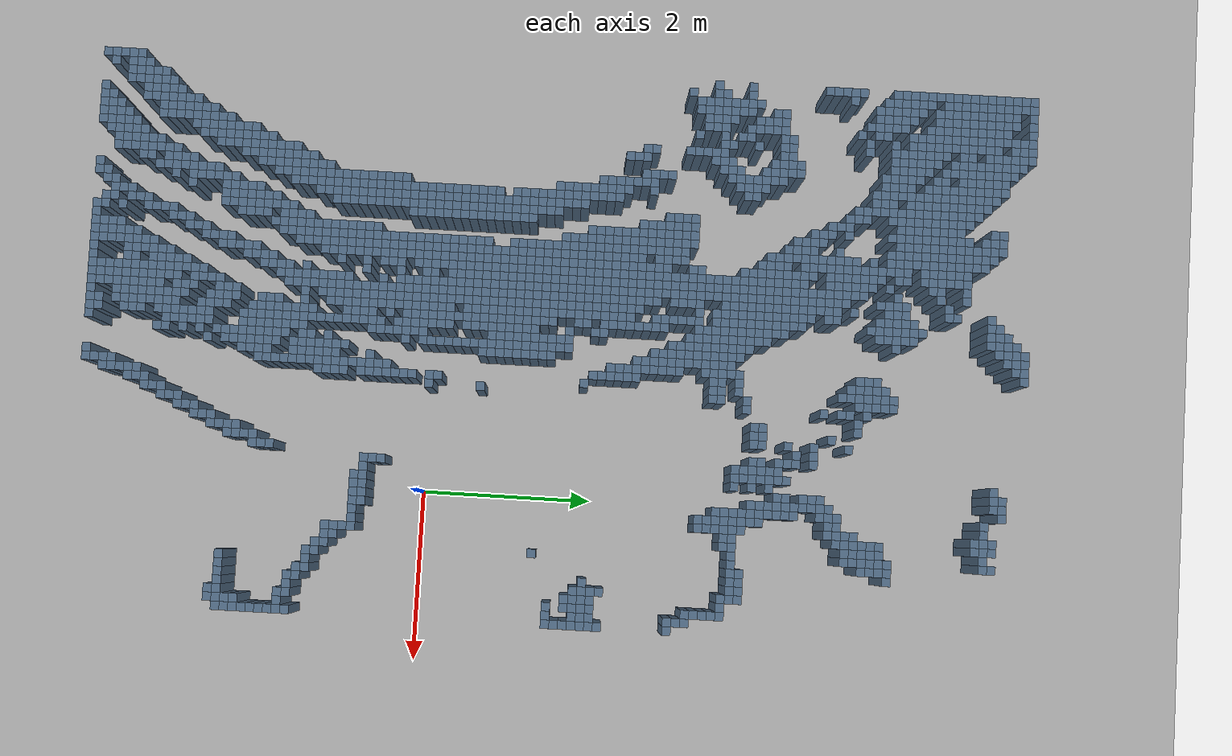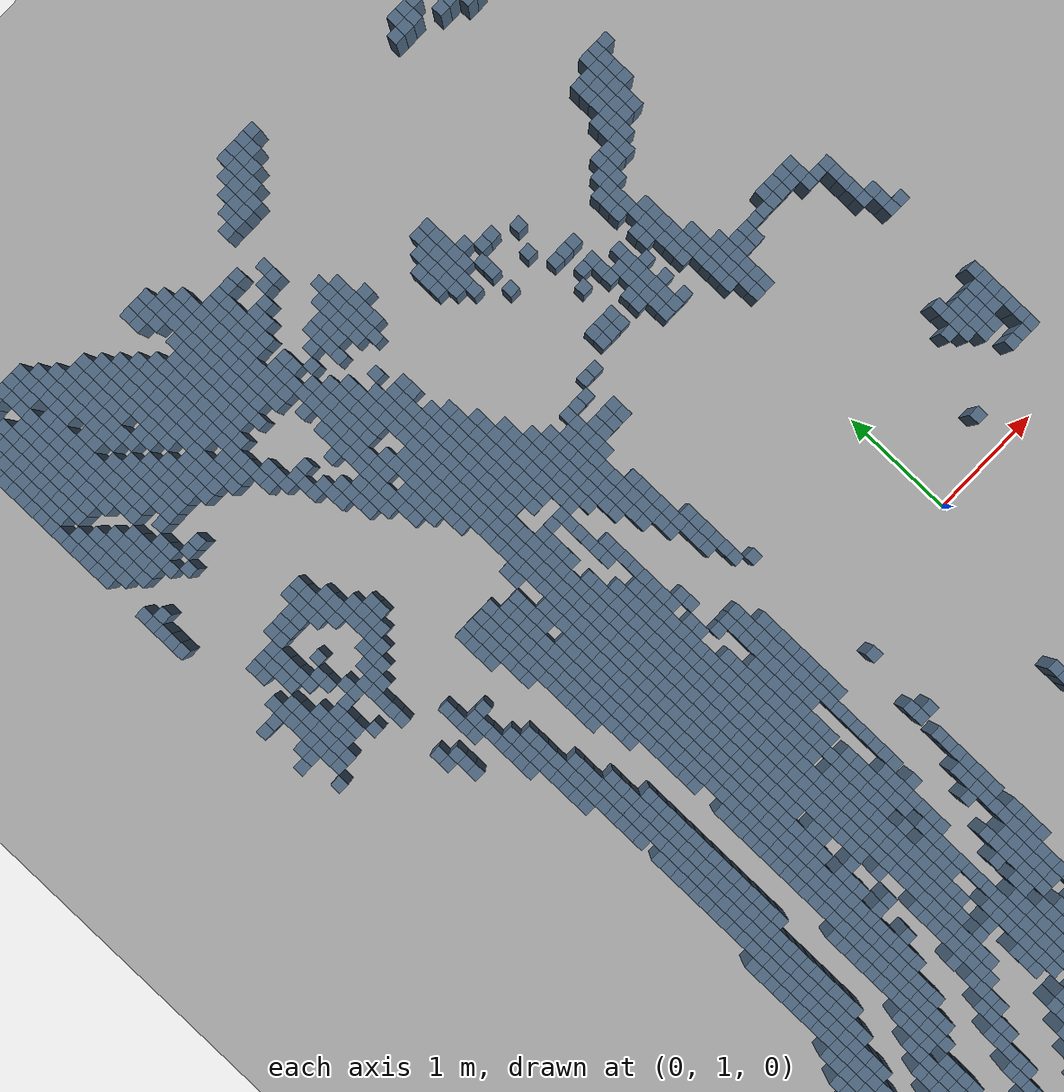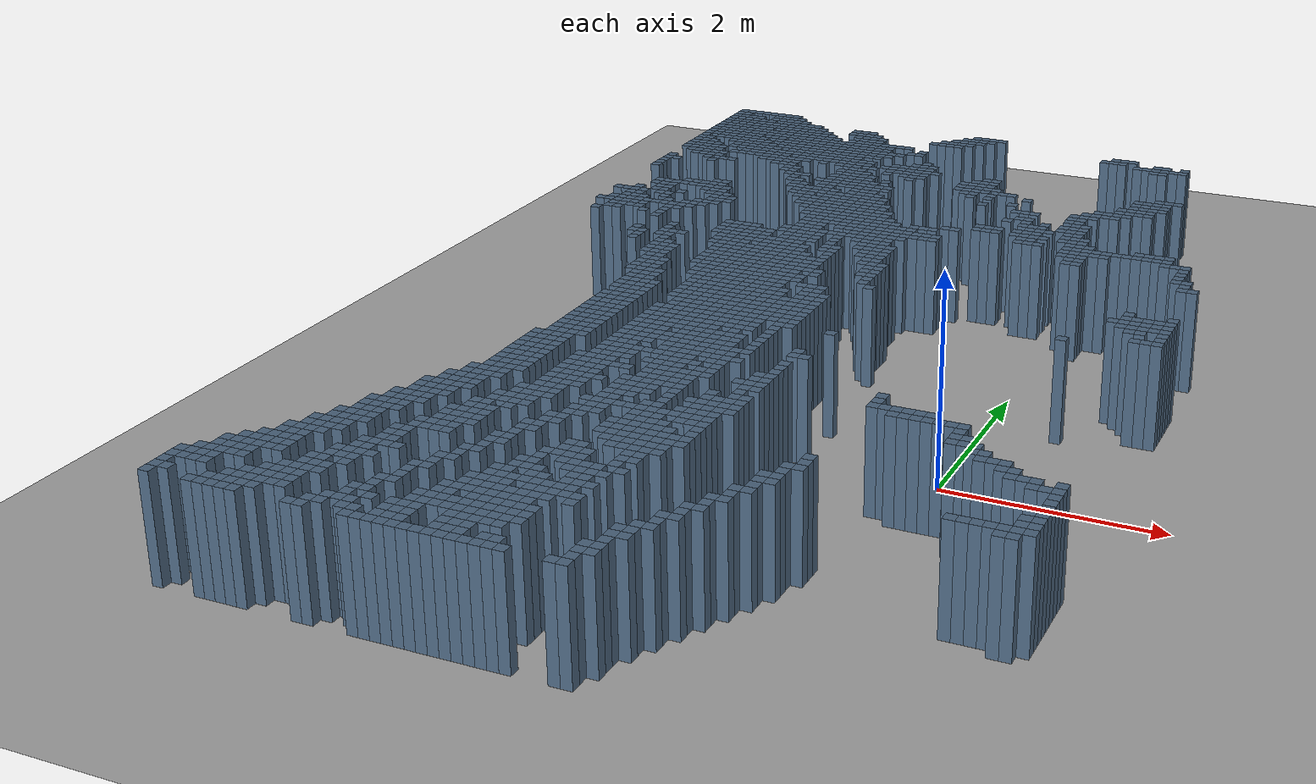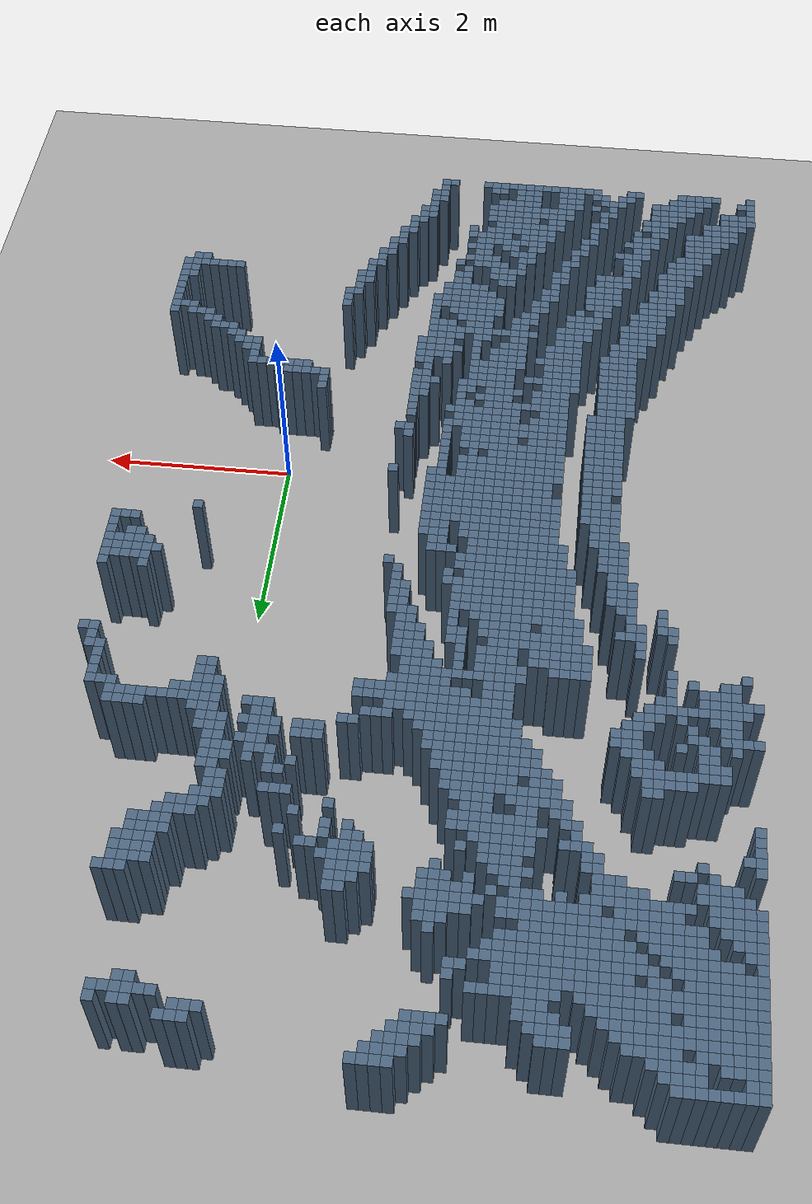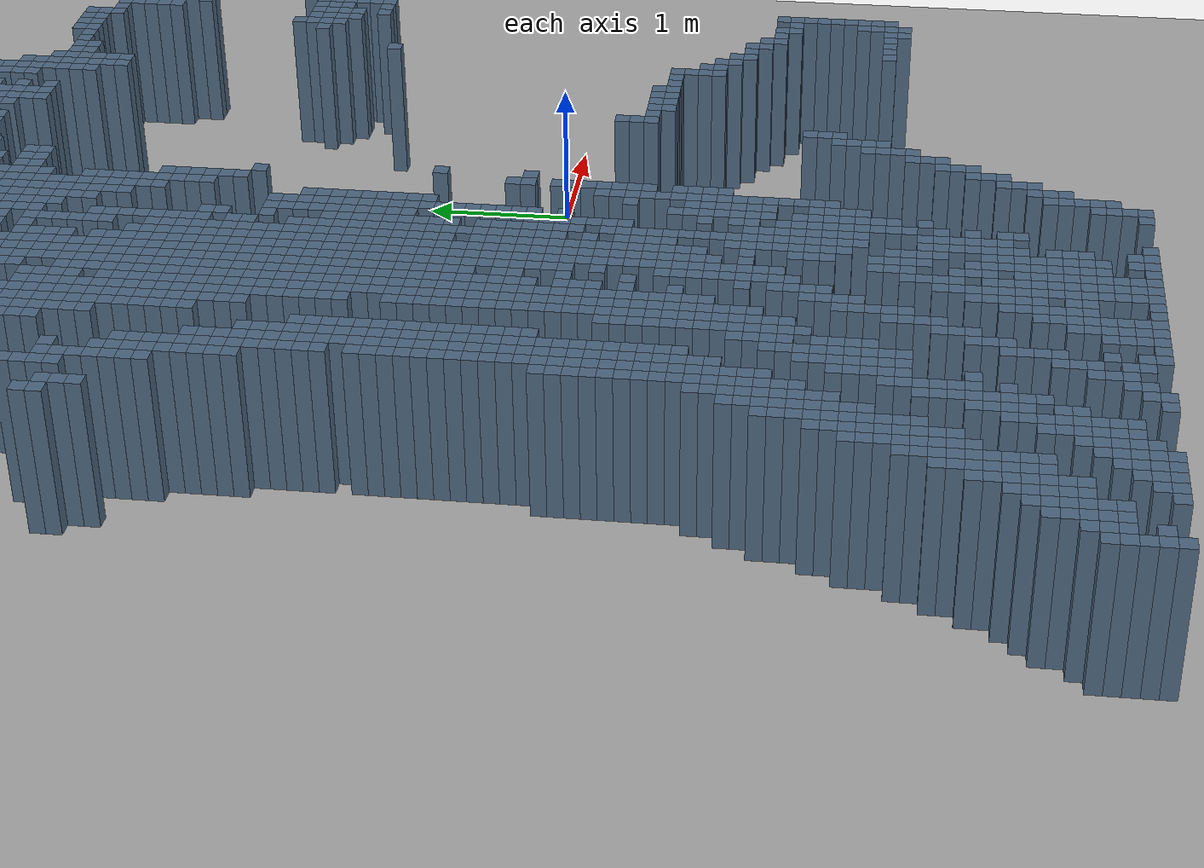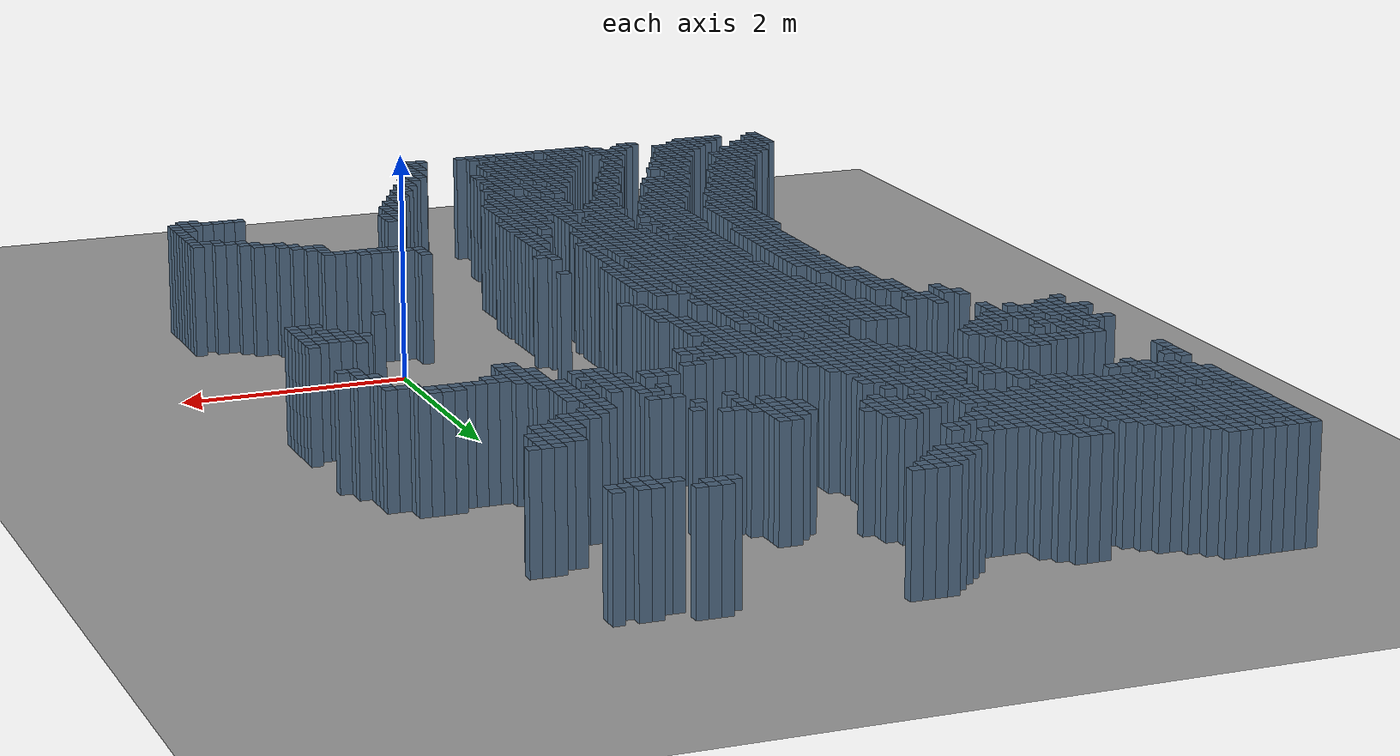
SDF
<?xml version='1.0' encoding='utf-8'?>
<sdf version="1.6">
  <world name="default">
    <gravity>0 0 -9.81</gravity>
    <physics name="default_physics" type="ode">
      <max_step_size>0.001</max_step_size>
      <real_time_update_rate>1000</real_time_update_rate>
    </physics>
    <scene>
      <ambient>0.6 0.6 0.6 1</ambient>
      <shadows>false</shadows>
    </scene>
    <light name="sun" type="directional">
      <pose>0 0 10 0 0 0</pose>
      <diffuse>0.8 0.8 0.8 1</diffuse>
      <direction>-0.5 0.1 -1</direction>
    </light>
    <model name="artificial_flat_ground">
      <static>true</static>
      <link name="ground">
        <collision name="floor_collision">
          <geometry>
            <plane>
              <normal>0 0 1</normal>
              <size>100 100</size>
            </plane>
          </geometry>
        </collision>
        <visual name="floor_visual">
          <geometry>
            <plane>
              <normal>0 0 1</normal>
              <size>100 100</size>
            </plane>
          </geometry>
          <material>
            <ambient>0.65 0.65 0.65 1</ambient>
            <diffuse>0.65 0.65 0.65 1</diffuse>
          </material>
        </visual>
      </link>
    </model>
    <model name="hilti_projected_cells">
      <static>true</static>
      <link name="obstacles">
        <collision name="cell_0_0_collision">
          <pose>-4.95000000 -3.95000000 0.50000000 0 0 0</pose>
          <geometry>
            <box>
              <size>0.10000000 0.10000000 1.00000000</size>
            </box>
          </geometry>
        </collision>
        <visual name="cell_0_0_visual">
          <pose>-4.95000000 -3.95000000 0.50000000 0 0 0</pose>
          <geometry>
            <box>
              <size>0.10000000 0.10000000 1.00000000</size>
            </box>
          </geometry>
          <material>
            <ambient>0.3 0.4 0.5 1</ambient>
            <diffuse>0.3 0.4 0.5 1</diffuse>
          </material>
        </visual>
        <collision name="cell_0_4_collision">
          <pose>-4.55000000 -3.95000000 0.50000000 0 0 0</pose>
          <geometry>
            <box>
              <size>0.10000000 0.10000000 1.00000000</size>
            </box>
          </geometry>
        </collision>
        <visual name="cell_0_4_visual">
          <pose>-4.55000000 -3.95000000 0.50000000 0 0 0</pose>
          <geometry>
            <box>
              <size>0.10000000 0.10000000 1.00000000</size>
            </box>
          </geometry>
          <material>
            <ambient>0.3 0.4 0.5 1</ambient>
            <diffuse>0.3 0.4 0.5 1</diffuse>
          </material>
        </visual>
        <collision name="cell_0_5_collision">
          <pose>-4.45000000 -3.95000000 0.50000000 0 0 0</pose>
          <geometry>
            <box>
              <size>0.10000000 0.10000000 1.00000000</size>
            </box>
          </geometry>
        </collision>
        <visual name="cell_0_5_visual">
          <pose>-4.45000000 -3.95000000 0.50000000 0 0 0</pose>
          <geometry>
            <box>
              <size>0.10000000 0.10000000 1.00000000</size>
            </box>
          </geometry>
          <material>
            <ambient>0.3 0.4 0.5 1</ambient>
            <diffuse>0.3 0.4 0.5 1</diffuse>
          </material>
        </visual>
        <collision name="cell_0_6_collision">
          <pose>-4.35000000 -3.95000000 0.50000000 0 0 0</pose>
          <geometry>
            <box>
              <size>0.10000000 0.10000000 1.00000000</size>
            </box>
          </geometry>
        </collision>
        <visual name="cell_0_6_visual">
          <pose>-4.35000000 -3.95000000 0.50000000 0 0 0</pose>
          <geometry>
            <box>
              <size>0.10000000 0.10000000 1.00000000</size>
            </box>
          </geometry>
          <material>
            <ambient>0.3 0.4 0.5 1</ambient>
            <diffuse>0.3 0.4 0.5 1</diffuse>
          </material>
        </visual>
        <collision name="cell_0_7_collision">
          <pose>-4.25000000 -3.95000000 0.50000000 0 0 0</pose>
          <geometry>
            <box>
              <size>0.10000000 0.10000000 1.00000000</size>
            </box>
          </geometry>
        </collision>
        <visual name="cell_0_7_visual">
          <pose>-4.25000000 -3.95000000 0.50000000 0 0 0</pose>
          <geometry>
            <box>
              <size>0.10000000 0.10000000 1.00000000</size>
            </box>
          </geometry>
          <material>
            <ambient>0.3 0.4 0.5 1</ambient>
            <diffuse>0.3 0.4 0.5 1</diffuse>
          </material>
        </visual>
        <collision name="cell_0_8_collision">
          <pose>-4.15000000 -3.95000000 0.50000000 0 0 0</pose>
          <geometry>
            <box>
              <size>0.10000000 0.10000000 1.00000000</size>
            </box>
          </geometry>
        </collision>
        <visual name="cell_0_8_visual">
          <pose>-4.15000000 -3.95000000 0.50000000 0 0 0</pose>
          <geometry>
            <box>
              <size>0.10000000 0.10000000 1.00000000</size>
            </box>
          </geometry>
          <material>
            <ambient>0.3 0.4 0.5 1</ambient>
            <diffuse>0.3 0.4 0.5 1</diffuse>
          </material>
        </visual>
        <collision name="cell_0_13_collision">
          <pose>-3.65000000 -3.95000000 0.50000000 0 0 0</pose>
          <geometry>
            <box>
              <size>0.10000000 0.10000000 1.00000000</size>
            </box>
          </geometry>
        </collision>
        <visual name="cell_0_13_visual">
          <pose>-3.65000000 -3.95000000 0.50000000 0 0 0</pose>
          <geometry>
            <box>
              <size>0.10000000 0.10000000 1.00000000</size>
            </box>
          </geometry>
          <material>
            <ambient>0.3 0.4 0.5 1</ambient>
            <diffuse>0.3 0.4 0.5 1</diffuse>
          </material>
        </visual>
        <collision name="cell_0_14_collision">
          <pose>-3.55000000 -3.95000000 0.50000000 0 0 0</pose>
          <geometry>
            <box>
              <size>0.10000000 0.10000000 1.00000000</size>
            </box>
          </geometry>
        </collision>
        <visual name="cell_0_14_visual">
          <pose>-3.55000000 -3.95000000 0.50000000 0 0 0</pose>
          <geometry>
            <box>
              <size>0.10000000 0.10000000 1.00000000</size>
            </box>
          </geometry>
          <material>
            <ambient>0.3 0.4 0.5 1</ambient>
            <diffuse>0.3 0.4 0.5 1</diffuse>
          </material>
        </visual>
        <collision name="cell_0_18_collision">
          <pose>-3.15000000 -3.95000000 0.50000000 0 0 0</pose>
          <geometry>
            <box>
              <size>0.10000000 0.10000000 1.00000000</size>
            </box>
          </geometry>
        </collision>
        <visual name="cell_0_18_visual">
          <pose>-3.15000000 -3.95000000 0.50000000 0 0 0</pose>
          <geometry>
            <box>
              <size>0.10000000 0.10000000 1.00000000</size>
            </box>
          </geometry>
          <material>
            <ambient>0.3 0.4 0.5 1</ambient>
            <diffuse>0.3 0.4 0.5 1</diffuse>
          </material>
        </visual>
        <collision name="cell_0_19_collision">
          <pose>-3.05000000 -3.95000000 0.50000000 0 0 0</pose>
          <geometry>
            <box>
              <size>0.10000000 0.10000000 1.00000000</size>
            </box>
          </geometry>
        </collision>
        <visual name="cell_0_19_visual">
          <pose>-3.05000000 -3.95000000 0.50000000 0 0 0</pose>
          <geometry>
            <box>
              <size>0.10000000 0.10000000 1.00000000</size>
            </box>
          </geometry>
          <material>
            <ambient>0.3 0.4 0.5 1</ambient>
            <diffuse>0.3 0.4 0.5 1</diffuse>
          </material>
        </visual>
        <collision name="cell_0_20_collision">
          <pose>-2.95000000 -3.95000000 0.50000000 0 0 0</pose>
          <geometry>
            <box>
              <size>0.10000000 0.10000000 1.00000000</size>
            </box>
          </geometry>
        </collision>
        <visual name="cell_0_20_visual">
          <pose>-2.95000000 -3.95000000 0.50000000 0 0 0</pose>
          <geometry>
            <box>
              <size>0.10000000 0.10000000 1.00000000</size>
            </box>
          </geometry>
          <material>
            <ambient>0.3 0.4 0.5 1</ambient>
            <diffuse>0.3 0.4 0.5 1</diffuse>
          </material>
        </visual>
        <collision name="cell_0_21_collision">
          <pose>-2.85000000 -3.95000000 0.50000000 0 0 0</pose>
          <geometry>
            <box>
              <size>0.10000000 0.10000000 1.00000000</size>
            </box>
          </geometry>
        </collision>
        <visual name="cell_0_21_visual">
          <pose>-2.85000000 -3.95000000 0.50000000 0 0 0</pose>
          <geometry>
            <box>
              <size>0.10000000 0.10000000 1.00000000</size>
            </box>
          </geometry>
          <material>
            <ambient>0.3 0.4 0.5 1</ambient>
            <diffuse>0.3 0.4 0.5 1</diffuse>
          </material>
        </visual>
        <collision name="cell_0_22_collision">
          <pose>-2.75000000 -3.95000000 0.50000000 0 0 0</pose>
          <geometry>
            <box>
              <size>0.10000000 0.10000000 1.00000000</size>
            </box>
          </geometry>
        </collision>
        <visual name="cell_0_22_visual">
          <pose>-2.75000000 -3.95000000 0.50000000 0 0 0</pose>
          <geometry>
            <box>
              <size>0.10000000 0.10000000 1.00000000</size>
            </box>
          </geometry>
          <material>
            <ambient>0.3 0.4 0.5 1</ambient>
            <diffuse>0.3 0.4 0.5 1</diffuse>
          </material>
        </visual>
        <collision name="cell_0_23_collision">
          <pose>-2.65000000 -3.95000000 0.50000000 0 0 0</pose>
          <geometry>
            <box>
              <size>0.10000000 0.10000000 1.00000000</size>
            </box>
          </geometry>
        </collision>
        <visual name="cell_0_23_visual">
          <pose>-2.65000000 -3.95000000 0.50000000 0 0 0</pose>
          <geometry>
            <box>
              <size>0.10000000 0.10000000 1.00000000</size>
            </box>
          </geometry>
          <material>
            <ambient>0.3 0.4 0.5 1</ambient>
            <diffuse>0.3 0.4 0.5 1</diffuse>
          </material>
        </visual>
        <collision name="cell_0_24_collision">
          <pose>-2.55000000 -3.95000000 0.50000000 0 0 0</pose>
          <geometry>
            <box>
              <size>0.10000000 0.10000000 1.00000000</size>
            </box>
          </geometry>
        </collision>
        <visual name="cell_0_24_visual">
          <pose>-2.55000000 -3.95000000 0.50000000 0 0 0</pose>
          <geometry>
            <box>
              <size>0.10000000 0.10000000 1.00000000</size>
            </box>
          </geometry>
          <material>
            <ambient>0.3 0.4 0.5 1</ambient>
            <diffuse>0.3 0.4 0.5 1</diffuse>
          </material>
        </visual>
        <collision name="cell_0_25_collision">
          <pose>-2.45000000 -3.95000000 0.50000000 0 0 0</pose>
          <geometry>
            <box>
              <size>0.10000000 0.10000000 1.00000000</size>
            </box>
          </geometry>
        </collision>
        <visual name="cell_0_25_visual">
          <pose>-2.45000000 -3.95000000 0.50000000 0 0 0</pose>
          <geometry>
            <box>
              <size>0.10000000 0.10000000 1.00000000</size>
            </box>
          </geometry>
          <material>
            <ambient>0.3 0.4 0.5 1</ambient>
            <diffuse>0.3 0.4 0.5 1</diffuse>
          </material>
        </visual>
        <collision name="cell_0_26_collision">
          <pose>-2.35000000 -3.95000000 0.50000000 0 0 0</pose>
          <geometry>
            <box>
              <size>0.10000000 0.10000000 1.00000000</size>
            </box>
          </geometry>
        </collision>
        <visual name="cell_0_26_visual">
          <pose>-2.35000000 -3.95000000 0.50000000 0 0 0</pose>
          <geometry>
            <box>
              <size>0.10000000 0.10000000 1.00000000</size>
            </box>
          </geometry>
          <material>
            <ambient>0.3 0.4 0.5 1</ambient>
            <diffuse>0.3 0.4 0.5 1</diffuse>
          </material>
        </visual>
        <collision name="cell_0_27_collision">
          <pose>-2.25000000 -3.95000000 0.50000000 0 0 0</pose>
          <geometry>
            <box>
              <size>0.10000000 0.10000000 1.00000000</size>
            </box>
          </geometry>
        </collision>
        <visual name="cell_0_27_visual">
          <pose>-2.25000000 -3.95000000 0.50000000 0 0 0</pose>
          <geometry>
            <box>
              <size>0.10000000 0.10000000 1.00000000</size>
            </box>
          </geometry>
          <material>
            <ambient>0.3 0.4 0.5 1</ambient>
            <diffuse>0.3 0.4 0.5 1</diffuse>
          </material>
        </visual>
        <collision name="cell_0_28_collision">
          <pose>-2.15000000 -3.95000000 0.50000000 0 0 0</pose>
          <geometry>
            <box>
              <size>0.10000000 0.10000000 1.00000000</size>
            </box>
          </geometry>
        </collision>
        <visual name="cell_0_28_visual">
          <pose>-2.15000000 -3.95000000 0.50000000 0 0 0</pose>
          <geometry>
            <box>
              <size>0.10000000 0.10000000 1.00000000</size>
            </box>
          </geometry>
          <material>
            <ambient>0.3 0.4 0.5 1</ambient>
            <diffuse>0.3 0.4 0.5 1</diffuse>
          </material>
        </visual>
        <collision name="cell_0_29_collision">
          <pose>-2.05000000 -3.95000000 0.50000000 0 0 0</pose>
          <geometry>
            <box>
              <size>0.10000000 0.10000000 1.00000000</size>
            </box>
          </geometry>
        </collision>
        <visual name="cell_0_29_visual">
          <pose>-2.05000000 -3.95000000 0.50000000 0 0 0</pose>
          <geometry>
            <box>
              <size>0.10000000 0.10000000 1.00000000</size>
            </box>
          </geometry>
          <material>
            <ambient>0.3 0.4 0.5 1</ambient>
            <diffuse>0.3 0.4 0.5 1</diffuse>
          </material>
        </visual>
        <collision name="cell_0_30_collision">
          <pose>-1.95000000 -3.95000000 0.50000000 0 0 0</pose>
          <geometry>
            <box>
              <size>0.10000000 0.10000000 1.00000000</size>
            </box>
          </geometry>
        </collision>
        <visual name="cell_0_30_visual">
          <pose>-1.95000000 -3.95000000 0.50000000 0 0 0</pose>
          <geometry>
            <box>
              <size>0.10000000 0.10000000 1.00000000</size>
            </box>
          </geometry>
          <material>
            <ambient>0.3 0.4 0.5 1</ambient>
            <diffuse>0.3 0.4 0.5 1</diffuse>
          </material>
        </visual>
        <collision name="cell_0_31_collision">
          <pose>-1.85000000 -3.95000000 0.50000000 0 0 0</pose>
          <geometry>
            <box>
              <size>0.10000000 0.10000000 1.00000000</size>
            </box>
          </geometry>
        </collision>
        <visual name="cell_0_31_visual">
          <pose>-1.85000000 -3.95000000 0.50000000 0 0 0</pose>
          <geometry>
            <box>
              <size>0.10000000 0.10000000 1.00000000</size>
            </box>
          </geometry>
          <material>
            <ambient>0.3 0.4 0.5 1</ambient>
            <diffuse>0.3 0.4 0.5 1</diffuse>
          </material>
        </visual>
        <collision name="cell_0_35_collision">
          <pose>-1.45000000 -3.95000000 0.50000000 0 0 0</pose>
          <geometry>
            <box>
              <size>0.10000000 0.10000000 1.00000000</size>
            </box>
          </geometry>
        </collision>
        <visual name="cell_0_35_visual">
          <pose>-1.45000000 -3.95000000 0.50000000 0 0 0</pose>
          <geometry>
            <box>
              <size>0.10000000 0.10000000 1.00000000</size>
            </box>
          </geometry>
          <material>
            <ambient>0.3 0.4 0.5 1</ambient>
            <diffuse>0.3 0.4 0.5 1</diffuse>
          </material>
        </visual>
        <collision name="cell_0_36_collision">
          <pose>-1.35000000 -3.95000000 0.50000000 0 0 0</pose>
          <geometry>
            <box>
              <size>0.10000000 0.10000000 1.00000000</size>
            </box>
          </geometry>
        </collision>
        <visual name="cell_0_36_visual">
          <pose>-1.35000000 -3.95000000 0.50000000 0 0 0</pose>
          <geometry>
            <box>
              <size>0.10000000 0.10000000 1.00000000</size>
            </box>
          </geometry>
          <material>
            <ambient>0.3 0.4 0.5 1</ambient>
            <diffuse>0.3 0.4 0.5 1</diffuse>
          </material>
        </visual>
        <collision name="cell_1_0_collision">
          <pose>-4.95000000 -3.85000000 0.50000000 0 0 0</pose>
          <geometry>
            <box>
              <size>0.10000000 0.10000000 1.00000000</size>
            </box>
          </geometry>
        </collision>
        <visual name="cell_1_0_visual">
          <pose>-4.95000000 -3.85000000 0.50000000 0 0 0</pose>
          <geometry>
            <box>
              <size>0.10000000 0.10000000 1.00000000</size>
            </box>
          </geometry>
          <material>
            <ambient>0.3 0.4 0.5 1</ambient>
            <diffuse>0.3 0.4 0.5 1</diffuse>
          </material>
        </visual>
        <collision name="cell_1_1_collision">
          <pose>-4.85000000 -3.85000000 0.50000000 0 0 0</pose>
          <geometry>
            <box>
              <size>0.10000000 0.10000000 1.00000000</size>
            </box>
          </geometry>
        </collision>
        <visual name="cell_1_1_visual">
          <pose>-4.85000000 -3.85000000 0.50000000 0 0 0</pose>
          <geometry>
            <box>
              <size>0.10000000 0.10000000 1.00000000</size>
            </box>
          </geometry>
          <material>
            <ambient>0.3 0.4 0.5 1</ambient>
            <diffuse>0.3 0.4 0.5 1</diffuse>
          </material>
        </visual>
        <collision name="cell_1_5_collision">
          <pose>-4.45000000 -3.85000000 0.50000000 0 0 0</pose>
          <geometry>
            <box>
              <size>0.10000000 0.10000000 1.00000000</size>
            </box>
          </geometry>
        </collision>
        <visual name="cell_1_5_visual">
          <pose>-4.45000000 -3.85000000 0.50000000 0 0 0</pose>
          <geometry>
            <box>
              <size>0.10000000 0.10000000 1.00000000</size>
            </box>
          </geometry>
          <material>
            <ambient>0.3 0.4 0.5 1</ambient>
            <diffuse>0.3 0.4 0.5 1</diffuse>
          </material>
        </visual>
        <collision name="cell_1_6_collision">
          <pose>-4.35000000 -3.85000000 0.50000000 0 0 0</pose>
          <geometry>
            <box>
              <size>0.10000000 0.10000000 1.00000000</size>
            </box>
          </geometry>
        </collision>
        <visual name="cell_1_6_visual">
          <pose>-4.35000000 -3.85000000 0.50000000 0 0 0</pose>
          <geometry>
            <box>
              <size>0.10000000 0.10000000 1.00000000</size>
            </box>
          </geometry>
          <material>
            <ambient>0.3 0.4 0.5 1</ambient>
            <diffuse>0.3 0.4 0.5 1</diffuse>
          </material>
        </visual>
        <collision name="cell_1_7_collision">
          <pose>-4.25000000 -3.85000000 0.50000000 0 0 0</pose>
          <geometry>
            <box>
              <size>0.10000000 0.10000000 1.00000000</size>
            </box>
          </geometry>
        </collision>
        <visual name="cell_1_7_visual">
          <pose>-4.25000000 -3.85000000 0.50000000 0 0 0</pose>
          <geometry>
            <box>
              <size>0.10000000 0.10000000 1.00000000</size>
            </box>
          </geometry>
          <material>
            <ambient>0.3 0.4 0.5 1</ambient>
            <diffuse>0.3 0.4 0.5 1</diffuse>
          </material>
        </visual>
        <collision name="cell_1_8_collision">
          <pose>-4.15000000 -3.85000000 0.50000000 0 0 0</pose>
          <geometry>
            <box>
              <size>0.10000000 0.10000000 1.00000000</size>
            </box>
          </geometry>
        </collision>
        <visual name="cell_1_8_visual">
          <pose>-4.15000000 -3.85000000 0.50000000 0 0 0</pose>
          <geometry>
            <box>
              <size>0.10000000 0.10000000 1.00000000</size>
            </box>
          </geometry>
          <material>
            <ambient>0.3 0.4 0.5 1</ambient>
            <diffuse>0.3 0.4 0.5 1</diffuse>
          </material>
        </visual>
        <collision name="cell_1_9_collision">
          <pose>-4.05000000 -3.85000000 0.50000000 0 0 0</pose>
          <geometry>
            <box>
              <size>0.10000000 0.10000000 1.00000000</size>
            </box>
          </geometry>
        </collision>
        <visual name="cell_1_9_visual">
          <pose>-4.05000000 -3.85000000 0.50000000 0 0 0</pose>
          <geometry>
            <box>
              <size>0.10000000 0.10000000 1.00000000</size>
            </box>
          </geometry>
          <material>
            <ambient>0.3 0.4 0.5 1</ambient>
            <diffuse>0.3 0.4 0.5 1</diffuse>
          </material>
        </visual>
        <collision name="cell_1_14_collision">
          <pose>-3.55000000 -3.85000000 0.50000000 0 0 0</pose>
          <geometry>
            <box>
              <size>0.10000000 0.10000000 1.00000000</size>
            </box>
          </geometry>
        </collision>
        <visual name="cell_1_14_visual">
          <pose>-3.55000000 -3.85000000 0.50000000 0 0 0</pose>
          <geometry>
            <box>
              <size>0.10000000 0.10000000 1.00000000</size>
            </box>
          </geometry>
          <material>
            <ambient>0.3 0.4 0.5 1</ambient>
            <diffuse>0.3 0.4 0.5 1</diffuse>
          </material>
        </visual>
        <collision name="cell_1_15_collision">
          <pose>-3.45000000 -3.85000000 0.50000000 0 0 0</pose>
          <geometry>
            <box>
              <size>0.10000000 0.10000000 1.00000000</size>
            </box>
          </geometry>
        </collision>
        <visual name="cell_1_15_visual">
          <pose>-3.45000000 -3.85000000 0.50000000 0 0 0</pose>
          <geometry>
            <box>
              <size>0.10000000 0.10000000 1.00000000</size>
            </box>
          </geometry>
          <material>
            <ambient>0.3 0.4 0.5 1</ambient>
            <diffuse>0.3 0.4 0.5 1</diffuse>
          </material>
        </visual>
        <collision name="cell_1_17_collision">
          <pose>-3.25000000 -3.85000000 0.50000000 0 0 0</pose>
          <geometry>
            <box>
              <size>0.10000000 0.10000000 1.00000000</size>
            </box>
          </geometry>
        </collision>
        <visual name="cell_1_17_visual">
          <pose>-3.25000000 -3.85000000 0.50000000 0 0 0</pose>
          <geometry>
            <box>
              <size>0.10000000 0.10000000 1.00000000</size>
            </box>
          </geometry>
          <material>
            <ambient>0.3 0.4 0.5 1</ambient>
            <diffuse>0.3 0.4 0.5 1</diffuse>
          </material>
        </visual>
        <collision name="cell_1_18_collision">
          <pose>-3.15000000 -3.85000000 0.50000000 0 0 0</pose>
          <geometry>
            <box>
              <size>0.10000000 0.10000000 1.00000000</size>
            </box>
          </geometry>
        </collision>
        <visual name="cell_1_18_visual">
          <pose>-3.15000000 -3.85000000 0.50000000 0 0 0</pose>
          <geometry>
            <box>
              <size>0.10000000 0.10000000 1.00000000</size>
            </box>
          </geometry>
          <material>
            <ambient>0.3 0.4 0.5 1</ambient>
            <diffuse>0.3 0.4 0.5 1</diffuse>
          </material>
        </visual>
        <collision name="cell_1_20_collision">
          <pose>-2.95000000 -3.85000000 0.50000000 0 0 0</pose>
          <geometry>
            <box>
              <size>0.10000000 0.10000000 1.00000000</size>
            </box>
          </geometry>
        </collision>
        <visual name="cell_1_20_visual">
          <pose>-2.95000000 -3.85000000 0.50000000 0 0 0</pose>
          <geometry>
            <box>
              <size>0.10000000 0.10000000 1.00000000</size>
            </box>
          </geometry>
          <material>
            <ambient>0.3 0.4 0.5 1</ambient>
            <diffuse>0.3 0.4 0.5 1</diffuse>
          </material>
        </visual>
        <collision name="cell_1_21_collision">
          <pose>-2.85000000 -3.85000000 0.50000000 0 0 0</pose>
          <geometry>
            <box>
              <size>0.10000000 0.10000000 1.00000000</size>
            </box>
          </geometry>
        </collision>
        <visual name="cell_1_21_visual">
          <pose>-2.85000000 -3.85000000 0.50000000 0 0 0</pose>
          <geometry>
            <box>
              <size>0.10000000 0.10000000 1.00000000</size>
            </box>
          </geometry>
          <material>
            <ambient>0.3 0.4 0.5 1</ambient>
            <diffuse>0.3 0.4 0.5 1</diffuse>
          </material>
        </visual>
        <collision name="cell_1_22_collision">
          <pose>-2.75000000 -3.85000000 0.50000000 0 0 0</pose>
          <geometry>
            <box>
              <size>0.10000000 0.10000000 1.00000000</size>
            </box>
          </geometry>
        </collision>
        <visual name="cell_1_22_visual">
          <pose>-2.75000000 -3.85000000 0.50000000 0 0 0</pose>
          <geometry>
            <box>
              <size>0.10000000 0.10000000 1.00000000</size>
            </box>
          </geometry>
          <material>
            <ambient>0.3 0.4 0.5 1</ambient>
            <diffuse>0.3 0.4 0.5 1</diffuse>
          </material>
        </visual>
        <collision name="cell_1_25_collision">
          <pose>-2.45000000 -3.85000000 0.50000000 0 0 0</pose>
          <geometry>
            <box>
              <size>0.10000000 0.10000000 1.00000000</size>
            </box>
          </geometry>
        </collision>
        <visual name="cell_1_25_visual">
          <pose>-2.45000000 -3.85000000 0.50000000 0 0 0</pose>
          <geometry>
            <box>
              <size>0.10000000 0.10000000 1.00000000</size>
            </box>
          </geometry>
          <material>
            <ambient>0.3 0.4 0.5 1</ambient>
            <diffuse>0.3 0.4 0.5 1</diffuse>
          </material>
        </visual>
        <collision name="cell_1_26_collision">
          <pose>-2.35000000 -3.85000000 0.50000000 0 0 0</pose>
          <geometry>
            <box>
              <size>0.10000000 0.10000000 1.00000000</size>
            </box>
          </geometry>
        </collision>
        <visual name="cell_1_26_visual">
          <pose>-2.35000000 -3.85000000 0.50000000 0 0 0</pose>
          <geometry>
            <box>
              <size>0.10000000 0.10000000 1.00000000</size>
            </box>
          </geometry>
          <material>
            <ambient>0.3 0.4 0.5 1</ambient>
            <diffuse>0.3 0.4 0.5 1</diffuse>
          </material>
        </visual>
        <collision name="cell_1_27_collision">
          <pose>-2.25000000 -3.85000000 0.50000000 0 0 0</pose>
          <geometry>
            <box>
              <size>0.10000000 0.10000000 1.00000000</size>
            </box>
          </geometry>
        </collision>
        <visual name="cell_1_27_visual">
          <pose>-2.25000000 -3.85000000 0.50000000 0 0 0</pose>
          <geometry>
            <box>
              <size>0.10000000 0.10000000 1.00000000</size>
            </box>
          </geometry>
          <material>
            <ambient>0.3 0.4 0.5 1</ambient>
            <diffuse>0.3 0.4 0.5 1</diffuse>
          </material>
        </visual>
        <collision name="cell_1_29_collision">
          <pose>-2.05000000 -3.85000000 0.50000000 0 0 0</pose>
          <geometry>
            <box>
              <size>0.10000000 0.10000000 1.00000000</size>
            </box>
          </geometry>
        </collision>
        <visual name="cell_1_29_visual">
          <pose>-2.05000000 -3.85000000 0.50000000 0 0 0</pose>
          <geometry>
            <box>
              <size>0.10000000 0.10000000 1.00000000</size>
            </box>
          </geometry>
          <material>
            <ambient>0.3 0.4 0.5 1</ambient>
            <diffuse>0.3 0.4 0.5 1</diffuse>
          </material>
        </visual>
        <collision name="cell_1_30_collision">
          <pose>-1.95000000 -3.85000000 0.50000000 0 0 0</pose>
          <geometry>
            <box>
              <size>0.10000000 0.10000000 1.00000000</size>
            </box>
          </geometry>
        </collision>
        <visual name="cell_1_30_visual">
          <pose>-1.95000000 -3.85000000 0.50000000 0 0 0</pose>
          <geometry>
            <box>
              <size>0.10000000 0.10000000 1.00000000</size>
            </box>
          </geometry>
          <material>
            <ambient>0.3 0.4 0.5 1</ambient>
            <diffuse>0.3 0.4 0.5 1</diffuse>
          </material>
        </visual>
        <collision name="cell_1_36_collision">
          <pose>-1.35000000 -3.85000000 0.50000000 0 0 0</pose>
          <geometry>
            <box>
              <size>0.10000000 0.10000000 1.00000000</size>
            </box>
          </geometry>
        </collision>
        <visual name="cell_1_36_visual">
          <pose>-1.35000000 -3.85000000 0.50000000 0 0 0</pose>
          <geometry>
            <box>
              <size>0.10000000 0.10000000 1.00000000</size>
            </box>
          </geometry>
          <material>
            <ambient>0.3 0.4 0.5 1</ambient>
            <diffuse>0.3 0.4 0.5 1</diffuse>
          </material>
        </visual>
        <collision name="cell_2_0_collision">
          <pose>-4.95000000 -3.75000000 0.50000000 0 0 0</pose>
          <geometry>
            <box>
              <size>0.10000000 0.10000000 1.00000000</size>
            </box>
          </geometry>
        </collision>
        <visual name="cell_2_0_visual">
          <pose>-4.95000000 -3.75000000 0.50000000 0 0 0</pose>
          <geometry>
            <box>
              <size>0.10000000 0.10000000 1.00000000</size>
            </box>
          </geometry>
          <material>
            <ambient>0.3 0.4 0.5 1</ambient>
            <diffuse>0.3 0.4 0.5 1</diffuse>
          </material>
        </visual>
        <collision name="cell_2_6_collision">
          <pose>-4.35000000 -3.75000000 0.50000000 0 0 0</pose>
          <geometry>
            <box>
              <size>0.10000000 0.10000000 1.00000000</size>
            </box>
          </geometry>
        </collision>
        <visual name="cell_2_6_visual">
          <pose>-4.35000000 -3.75000000 0.50000000 0 0 0</pose>
          <geometry>
            <box>
              <size>0.10000000 0.10000000 1.00000000</size>
            </box>
          </geometry>
          <material>
            <ambient>0.3 0.4 0.5 1</ambient>
            <diffuse>0.3 0.4 0.5 1</diffuse>
          </material>
        </visual>
        <collision name="cell_2_7_collision">
          <pose>-4.25000000 -3.75000000 0.50000000 0 0 0</pose>
          <geometry>
            <box>
              <size>0.10000000 0.10000000 1.00000000</size>
            </box>
          </geometry>
        </collision>
        <visual name="cell_2_7_visual">
          <pose>-4.25000000 -3.75000000 0.50000000 0 0 0</pose>
          <geometry>
            <box>
              <size>0.10000000 0.10000000 1.00000000</size>
            </box>
          </geometry>
          <material>
            <ambient>0.3 0.4 0.5 1</ambient>
            <diffuse>0.3 0.4 0.5 1</diffuse>
          </material>
        </visual>
        <collision name="cell_2_8_collision">
          <pose>-4.15000000 -3.75000000 0.50000000 0 0 0</pose>
          <geometry>
            <box>
              <size>0.10000000 0.10000000 1.00000000</size>
            </box>
          </geometry>
        </collision>
        <visual name="cell_2_8_visual">
          <pose>-4.15000000 -3.75000000 0.50000000 0 0 0</pose>
          <geometry>
            <box>
              <size>0.10000000 0.10000000 1.00000000</size>
            </box>
          </geometry>
          <material>
            <ambient>0.3 0.4 0.5 1</ambient>
            <diffuse>0.3 0.4 0.5 1</diffuse>
          </material>
        </visual>
        <collision name="cell_2_9_collision">
          <pose>-4.05000000 -3.75000000 0.50000000 0 0 0</pose>
          <geometry>
            <box>
              <size>0.10000000 0.10000000 1.00000000</size>
            </box>
          </geometry>
        </collision>
        <visual name="cell_2_9_visual">
          <pose>-4.05000000 -3.75000000 0.50000000 0 0 0</pose>
          <geometry>
            <box>
              <size>0.10000000 0.10000000 1.00000000</size>
            </box>
          </geometry>
          <material>
            <ambient>0.3 0.4 0.5 1</ambient>
            <diffuse>0.3 0.4 0.5 1</diffuse>
          </material>
        </visual>
        <collision name="cell_2_10_collision">
          <pose>-3.95000000 -3.75000000 0.50000000 0 0 0</pose>
          <geometry>
            <box>
              <size>0.10000000 0.10000000 1.00000000</size>
            </box>
          </geometry>
        </collision>
        <visual name="cell_2_10_visual">
          <pose>-3.95000000 -3.75000000 0.50000000 0 0 0</pose>
          <geometry>
            <box>
              <size>0.10000000 0.10000000 1.00000000</size>
            </box>
          </geometry>
          <material>
            <ambient>0.3 0.4 0.5 1</ambient>
            <diffuse>0.3 0.4 0.5 1</diffuse>
          </material>
        </visual>
        <collision name="cell_2_11_collision">
          <pose>-3.85000000 -3.75000000 0.50000000 0 0 0</pose>
          <geometry>
            <box>
              <size>0.10000000 0.10000000 1.00000000</size>
            </box>
          </geometry>
        </collision>
        <visual name="cell_2_11_visual">
          <pose>-3.85000000 -3.75000000 0.50000000 0 0 0</pose>
          <geometry>
            <box>
              <size>0.10000000 0.10000000 1.00000000</size>
            </box>
          </geometry>
          <material>
            <ambient>0.3 0.4 0.5 1</ambient>
            <diffuse>0.3 0.4 0.5 1</diffuse>
          </material>
        </visual>
        <collision name="cell_2_15_collision">
          <pose>-3.45000000 -3.75000000 0.50000000 0 0 0</pose>
          <geometry>
            <box>
              <size>0.10000000 0.10000000 1.00000000</size>
            </box>
          </geometry>
        </collision>
        <visual name="cell_2_15_visual">
          <pose>-3.45000000 -3.75000000 0.50000000 0 0 0</pose>
          <geometry>
            <box>
              <size>0.10000000 0.10000000 1.00000000</size>
            </box>
          </geometry>
          <material>
            <ambient>0.3 0.4 0.5 1</ambient>
            <diffuse>0.3 0.4 0.5 1</diffuse>
          </material>
        </visual>
        <collision name="cell_2_16_collision">
          <pose>-3.35000000 -3.75000000 0.50000000 0 0 0</pose>
          <geometry>
            <box>
              <size>0.10000000 0.10000000 1.00000000</size>
            </box>
          </geometry>
        </collision>
        <visual name="cell_2_16_visual">
          <pose>-3.35000000 -3.75000000 0.50000000 0 0 0</pose>
          <geometry>
            <box>
              <size>0.10000000 0.10000000 1.00000000</size>
            </box>
          </geometry>
          <material>
            <ambient>0.3 0.4 0.5 1</ambient>
            <diffuse>0.3 0.4 0.5 1</diffuse>
          </material>
        </visual>
        <collision name="cell_2_17_collision">
          <pose>-3.25000000 -3.75000000 0.50000000 0 0 0</pose>
          <geometry>
            <box>
              <size>0.10000000 0.10000000 1.00000000</size>
            </box>
          </geometry>
        </collision>
        <visual name="cell_2_17_visual">
          <pose>-3.25000000 -3.75000000 0.50000000 0 0 0</pose>
          <geometry>
            <box>
              <size>0.10000000 0.10000000 1.00000000</size>
            </box>
          </geometry>
          <material>
            <ambient>0.3 0.4 0.5 1</ambient>
            <diffuse>0.3 0.4 0.5 1</diffuse>
          </material>
        </visual>
        <collision name="cell_2_20_collision">
          <pose>-2.95000000 -3.75000000 0.50000000 0 0 0</pose>
          <geometry>
            <box>
              <size>0.10000000 0.10000000 1.00000000</size>
            </box>
          </geometry>
        </collision>
        <visual name="cell_2_20_visual">
          <pose>-2.95000000 -3.75000000 0.50000000 0 0 0</pose>
          <geometry>
            <box>
              <size>0.10000000 0.10000000 1.00000000</size>
            </box>
          </geometry>
          <material>
            <ambient>0.3 0.4 0.5 1</ambient>
            <diffuse>0.3 0.4 0.5 1</diffuse>
          </material>
        </visual>
        <collision name="cell_2_21_collision">
          <pose>-2.85000000 -3.75000000 0.50000000 0 0 0</pose>
          <geometry>
            <box>
              <size>0.10000000 0.10000000 1.00000000</size>
            </box>
          </geometry>
        </collision>
        <visual name="cell_2_21_visual">
          <pose>-2.85000000 -3.75000000 0.50000000 0 0 0</pose>
          <geometry>
            <box>
              <size>0.10000000 0.10000000 1.00000000</size>
            </box>
          </geometry>
          <material>
            <ambient>0.3 0.4 0.5 1</ambient>
            <diffuse>0.3 0.4 0.5 1</diffuse>
          </material>
        </visual>
        <collision name="cell_2_22_collision">
          <pose>-2.75000000 -3.75000000 0.50000000 0 0 0</pose>
          <geometry>
            <box>
              <size>0.10000000 0.10000000 1.00000000</size>
            </box>
          </geometry>
        </collision>
        <visual name="cell_2_22_visual">
          <pose>-2.75000000 -3.75000000 0.50000000 0 0 0</pose>
          <geometry>
            <box>
              <size>0.10000000 0.10000000 1.00000000</size>
            </box>
          </geometry>
          <material>
            <ambient>0.3 0.4 0.5 1</ambient>
            <diffuse>0.3 0.4 0.5 1</diffuse>
          </material>
        </visual>
        <collision name="cell_2_25_collision">
          <pose>-2.45000000 -3.75000000 0.50000000 0 0 0</pose>
          <geometry>
            <box>
              <size>0.10000000 0.10000000 1.00000000</size>
            </box>
          </geometry>
        </collision>
        <visual name="cell_2_25_visual">
          <pose>-2.45000000 -3.75000000 0.50000000 0 0 0</pose>
          <geometry>
            <box>
              <size>0.10000000 0.10000000 1.00000000</size>
            </box>
          </geometry>
          <material>
            <ambient>0.3 0.4 0.5 1</ambient>
            <diffuse>0.3 0.4 0.5 1</diffuse>
          </material>
        </visual>
        <collision name="cell_2_26_collision">
          <pose>-2.35000000 -3.75000000 0.50000000 0 0 0</pose>
          <geometry>
            <box>
              <size>0.10000000 0.10000000 1.00000000</size>
            </box>
          </geometry>
        </collision>
        <visual name="cell_2_26_visual">
          <pose>-2.35000000 -3.75000000 0.50000000 0 0 0</pose>
          <geometry>
            <box>
              <size>0.10000000 0.10000000 1.00000000</size>
            </box>
          </geometry>
          <material>
            <ambient>0.3 0.4 0.5 1</ambient>
            <diffuse>0.3 0.4 0.5 1</diffuse>
          </material>
        </visual>
        <collision name="cell_2_27_collision">
          <pose>-2.25000000 -3.75000000 0.50000000 0 0 0</pose>
          <geometry>
            <box>
              <size>0.10000000 0.10000000 1.00000000</size>
            </box>
          </geometry>
        </collision>
        <visual name="cell_2_27_visual">
          <pose>-2.25000000 -3.75000000 0.50000000 0 0 0</pose>
          <geometry>
            <box>
              <size>0.10000000 0.10000000 1.00000000</size>
            </box>
          </geometry>
          <material>
            <ambient>0.3 0.4 0.5 1</ambient>
            <diffuse>0.3 0.4 0.5 1</diffuse>
          </material>
        </visual>
        <collision name="cell_2_36_collision">
          <pose>-1.35000000 -3.75000000 0.50000000 0 0 0</pose>
          <geometry>
            <box>
              <size>0.10000000 0.10000000 1.00000000</size>
            </box>
          </geometry>
        </collision>
        <visual name="cell_2_36_visual">
          <pose>-1.35000000 -3.75000000 0.50000000 0 0 0</pose>
          <geometry>
            <box>
              <size>0.10000000 0.10000000 1.00000000</size>
            </box>
          </geometry>
          <material>
            <ambient>0.3 0.4 0.5 1</ambient>
            <diffuse>0.3 0.4 0.5 1</diffuse>
          </material>
        </visual>
        <collision name="cell_2_37_collision">
          <pose>-1.25000000 -3.75000000 0.50000000 0 0 0</pose>
          <geometry>
            <box>
              <size>0.10000000 0.10000000 1.00000000</size>
            </box>
          </geometry>
        </collision>
        <visual name="cell_2_37_visual">
          <pose>-1.25000000 -3.75000000 0.50000000 0 0 0</pose>
          <geometry>
            <box>
              <size>0.10000000 0.10000000 1.00000000</size>
            </box>
          </geometry>
          <material>
            <ambient>0.3 0.4 0.5 1</ambient>
            <diffuse>0.3 0.4 0.5 1</diffuse>
          </material>
        </visual>
        <collision name="cell_3_0_collision">
          <pose>-4.95000000 -3.65000000 0.50000000 0 0 0</pose>
          <geometry>
            <box>
              <size>0.10000000 0.10000000 1.00000000</size>
            </box>
          </geometry>
        </collision>
        <visual name="cell_3_0_visual">
          <pose>-4.95000000 -3.65000000 0.50000000 0 0 0</pose>
          <geometry>
            <box>
              <size>0.10000000 0.10000000 1.00000000</size>
            </box>
          </geometry>
          <material>
            <ambient>0.3 0.4 0.5 1</ambient>
            <diffuse>0.3 0.4 0.5 1</diffuse>
          </material>
        </visual>
        <collision name="cell_3_1_collision">
          <pose>-4.85000000 -3.65000000 0.50000000 0 0 0</pose>
          <geometry>
            <box>
              <size>0.10000000 0.10000000 1.00000000</size>
            </box>
          </geometry>
        </collision>
        <visual name="cell_3_1_visual">
          <pose>-4.85000000 -3.65000000 0.50000000 0 0 0</pose>
          <geometry>
            <box>
              <size>0.10000000 0.10000000 1.00000000</size>
            </box>
          </geometry>
          <material>
            <ambient>0.3 0.4 0.5 1</ambient>
            <diffuse>0.3 0.4 0.5 1</diffuse>
          </material>
        </visual>
        <collision name="cell_3_2_collision">
          <pose>-4.75000000 -3.65000000 0.50000000 0 0 0</pose>
          <geometry>
            <box>
              <size>0.10000000 0.10000000 1.00000000</size>
            </box>
          </geometry>
        </collision>
        <visual name="cell_3_2_visual">
          <pose>-4.75000000 -3.65000000 0.50000000 0 0 0</pose>
          <geometry>
            <box>
              <size>0.10000000 0.10000000 1.00000000</size>
            </box>
          </geometry>
          <material>
            <ambient>0.3 0.4 0.5 1</ambient>
            <diffuse>0.3 0.4 0.5 1</diffuse>
          </material>
        </visual>
        <collision name="cell_3_3_collision">
          <pose>-4.65000000 -3.65000000 0.50000000 0 0 0</pose>
          <geometry>
            <box>
              <size>0.10000000 0.10000000 1.00000000</size>
            </box>
          </geometry>
        </collision>
        <visual name="cell_3_3_visual">
          <pose>-4.65000000 -3.65000000 0.50000000 0 0 0</pose>
          <geometry>
            <box>
              <size>0.10000000 0.10000000 1.00000000</size>
            </box>
          </geometry>
          <material>
            <ambient>0.3 0.4 0.5 1</ambient>
            <diffuse>0.3 0.4 0.5 1</diffuse>
          </material>
        </visual>
        <collision name="cell_3_7_collision">
          <pose>-4.25000000 -3.65000000 0.50000000 0 0 0</pose>
          <geometry>
            <box>
              <size>0.10000000 0.10000000 1.00000000</size>
            </box>
          </geometry>
        </collision>
        <visual name="cell_3_7_visual">
          <pose>-4.25000000 -3.65000000 0.50000000 0 0 0</pose>
          <geometry>
            <box>
              <size>0.10000000 0.10000000 1.00000000</size>
            </box>
          </geometry>
          <material>
            <ambient>0.3 0.4 0.5 1</ambient>
            <diffuse>0.3 0.4 0.5 1</diffuse>
          </material>
        </visual>
        <collision name="cell_3_8_collision">
          <pose>-4.15000000 -3.65000000 0.50000000 0 0 0</pose>
          <geometry>
            <box>
              <size>0.10000000 0.10000000 1.00000000</size>
            </box>
          </geometry>
        </collision>
        <visual name="cell_3_8_visual">
          <pose>-4.15000000 -3.65000000 0.50000000 0 0 0</pose>
          <geometry>
            <box>
              <size>0.10000000 0.10000000 1.00000000</size>
            </box>
          </geometry>
          <material>
            <ambient>0.3 0.4 0.5 1</ambient>
            <diffuse>0.3 0.4 0.5 1</diffuse>
          </material>
        </visual>
        <collision name="cell_3_9_collision">
          <pose>-4.05000000 -3.65000000 0.50000000 0 0 0</pose>
          <geometry>
            <box>
              <size>0.10000000 0.10000000 1.00000000</size>
            </box>
          </geometry>
        </collision>
        <visual name="cell_3_9_visual">
          <pose>-4.05000000 -3.65000000 0.50000000 0 0 0</pose>
          <geometry>
            <box>
              <size>0.10000000 0.10000000 1.00000000</size>
            </box>
          </geometry>
          <material>
            <ambient>0.3 0.4 0.5 1</ambient>
            <diffuse>0.3 0.4 0.5 1</diffuse>
          </material>
        </visual>
        <collision name="cell_3_10_collision">
          <pose>-3.95000000 -3.65000000 0.50000000 0 0 0</pose>
          <geometry>
            <box>
              <size>0.10000000 0.10000000 1.00000000</size>
            </box>
          </geometry>
        </collision>
        <visual name="cell_3_10_visual">
          <pose>-3.95000000 -3.65000000 0.50000000 0 0 0</pose>
          <geometry>
            <box>
              <size>0.10000000 0.10000000 1.00000000</size>
            </box>
          </geometry>
          <material>
            <ambient>0.3 0.4 0.5 1</ambient>
            <diffuse>0.3 0.4 0.5 1</diffuse>
          </material>
        </visual>
        <collision name="cell_3_11_collision">
          <pose>-3.85000000 -3.65000000 0.50000000 0 0 0</pose>
          <geometry>
            <box>
              <size>0.10000000 0.10000000 1.00000000</size>
            </box>
          </geometry>
        </collision>
        <visual name="cell_3_11_visual">
          <pose>-3.85000000 -3.65000000 0.50000000 0 0 0</pose>
          <geometry>
            <box>
              <size>0.10000000 0.10000000 1.00000000</size>
            </box>
          </geometry>
          <material>
            <ambient>0.3 0.4 0.5 1</ambient>
            <diffuse>0.3 0.4 0.5 1</diffuse>
          </material>
        </visual>
        <collision name="cell_3_16_collision">
          <pose>-3.35000000 -3.65000000 0.50000000 0 0 0</pose>
          <geometry>
            <box>
              <size>0.10000000 0.10000000 1.00000000</size>
            </box>
          </geometry>
        </collision>
        <visual name="cell_3_16_visual">
          <pose>-3.35000000 -3.65000000 0.50000000 0 0 0</pose>
          <geometry>
            <box>
              <size>0.10000000 0.10000000 1.00000000</size>
            </box>
          </geometry>
          <material>
            <ambient>0.3 0.4 0.5 1</ambient>
            <diffuse>0.3 0.4 0.5 1</diffuse>
          </material>
        </visual>
        <collision name="cell_3_18_collision">
          <pose>-3.15000000 -3.65000000 0.50000000 0 0 0</pose>
          <geometry>
            <box>
              <size>0.10000000 0.10000000 1.00000000</size>
            </box>
          </geometry>
        </collision>
        <visual name="cell_3_18_visual">
          <pose>-3.15000000 -3.65000000 0.50000000 0 0 0</pose>
          <geometry>
            <box>
              <size>0.10000000 0.10000000 1.00000000</size>
            </box>
          </geometry>
          <material>
            <ambient>0.3 0.4 0.5 1</ambient>
            <diffuse>0.3 0.4 0.5 1</diffuse>
          </material>
        </visual>
        <collision name="cell_3_20_collision">
          <pose>-2.95000000 -3.65000000 0.50000000 0 0 0</pose>
          <geometry>
            <box>
              <size>0.10000000 0.10000000 1.00000000</size>
            </box>
          </geometry>
        </collision>
        <visual name="cell_3_20_visual">
          <pose>-2.95000000 -3.65000000 0.50000000 0 0 0</pose>
          <geometry>
            <box>
              <size>0.10000000 0.10000000 1.00000000</size>
            </box>
          </geometry>
          <material>
            <ambient>0.3 0.4 0.5 1</ambient>
            <diffuse>0.3 0.4 0.5 1</diffuse>
          </material>
        </visual>
        <collision name="cell_3_21_collision">
          <pose>-2.85000000 -3.65000000 0.50000000 0 0 0</pose>
          <geometry>
            <box>
              <size>0.10000000 0.10000000 1.00000000</size>
            </box>
          </geometry>
        </collision>
        <visual name="cell_3_21_visual">
          <pose>-2.85000000 -3.65000000 0.50000000 0 0 0</pose>
          <geometry>
            <box>
              <size>0.10000000 0.10000000 1.00000000</size>
            </box>
          </geometry>
          <material>
            <ambient>0.3 0.4 0.5 1</ambient>
            <diffuse>0.3 0.4 0.5 1</diffuse>
          </material>
        </visual>
        <collision name="cell_3_22_collision">
          <pose>-2.75000000 -3.65000000 0.50000000 0 0 0</pose>
          <geometry>
            <box>
              <size>0.10000000 0.10000000 1.00000000</size>
            </box>
          </geometry>
        </collision>
        <visual name="cell_3_22_visual">
          <pose>-2.75000000 -3.65000000 0.50000000 0 0 0</pose>
          <geometry>
            <box>
              <size>0.10000000 0.10000000 1.00000000</size>
            </box>
          </geometry>
          <material>
            <ambient>0.3 0.4 0.5 1</ambient>
            <diffuse>0.3 0.4 0.5 1</diffuse>
          </material>
        </visual>
        <collision name="cell_3_25_collision">
          <pose>-2.45000000 -3.65000000 0.50000000 0 0 0</pose>
          <geometry>
            <box>
              <size>0.10000000 0.10000000 1.00000000</size>
            </box>
          </geometry>
        </collision>
        <visual name="cell_3_25_visual">
          <pose>-2.45000000 -3.65000000 0.50000000 0 0 0</pose>
          <geometry>
            <box>
              <size>0.10000000 0.10000000 1.00000000</size>
            </box>
          </geometry>
          <material>
            <ambient>0.3 0.4 0.5 1</ambient>
            <diffuse>0.3 0.4 0.5 1</diffuse>
          </material>
        </visual>
        <collision name="cell_3_26_collision">
          <pose>-2.35000000 -3.65000000 0.50000000 0 0 0</pose>
          <geometry>
            <box>
              <size>0.10000000 0.10000000 1.00000000</size>
            </box>
          </geometry>
        </collision>
        <visual name="cell_3_26_visual">
          <pose>-2.35000000 -3.65000000 0.50000000 0 0 0</pose>
          <geometry>
            <box>
              <size>0.10000000 0.10000000 1.00000000</size>
            </box>
          </geometry>
          <material>
            <ambient>0.3 0.4 0.5 1</ambient>
            <diffuse>0.3 0.4 0.5 1</diffuse>
          </material>
        </visual>
        <collision name="cell_3_27_collision">
          <pose>-2.25000000 -3.65000000 0.50000000 0 0 0</pose>
          <geometry>
            <box>
              <size>0.10000000 0.10000000 1.00000000</size>
            </box>
          </geometry>
        </collision>
        <visual name="cell_3_27_visual">
          <pose>-2.25000000 -3.65000000 0.50000000 0 0 0</pose>
          <geometry>
            <box>
              <size>0.10000000 0.10000000 1.00000000</size>
            </box>
          </geometry>
          <material>
            <ambient>0.3 0.4 0.5 1</ambient>
            <diffuse>0.3 0.4 0.5 1</diffuse>
          </material>
        </visual>
        <collision name="cell_3_28_collision">
          <pose>-2.15000000 -3.65000000 0.50000000 0 0 0</pose>
          <geometry>
            <box>
              <size>0.10000000 0.10000000 1.00000000</size>
            </box>
          </geometry>
        </collision>
        <visual name="cell_3_28_visual">
          <pose>-2.15000000 -3.65000000 0.50000000 0 0 0</pose>
          <geometry>
            <box>
              <size>0.10000000 0.10000000 1.00000000</size>
            </box>
          </geometry>
          <material>
            <ambient>0.3 0.4 0.5 1</ambient>
            <diffuse>0.3 0.4 0.5 1</diffuse>
          </material>
        </visual>
        <collision name="cell_3_29_collision">
          <pose>-2.05000000 -3.65000000 0.50000000 0 0 0</pose>
          <geometry>
            <box>
              <size>0.10000000 0.10000000 1.00000000</size>
            </box>
          </geometry>
        </collision>
        <visual name="cell_3_29_visual">
          <pose>-2.05000000 -3.65000000 0.50000000 0 0 0</pose>
          <geometry>
            <box>
              <size>0.10000000 0.10000000 1.00000000</size>
            </box>
          </geometry>
          <material>
            <ambient>0.3 0.4 0.5 1</ambient>
            <diffuse>0.3 0.4 0.5 1</diffuse>
          </material>
        </visual>
        <collision name="cell_3_36_collision">
          <pose>-1.35000000 -3.65000000 0.50000000 0 0 0</pose>
          <geometry>
            <box>
              <size>0.10000000 0.10000000 1.00000000</size>
            </box>
          </geometry>
        </collision>
        <visual name="cell_3_36_visual">
          <pose>-1.35000000 -3.65000000 0.50000000 0 0 0</pose>
          <geometry>
            <box>
              <size>0.10000000 0.10000000 1.00000000</size>
            </box>
          </geometry>
          <material>
            <ambient>0.3 0.4 0.5 1</ambient>
            <diffuse>0.3 0.4 0.5 1</diffuse>
          </material>
        </visual>
        <collision name="cell_3_37_collision">
          <pose>-1.25000000 -3.65000000 0.50000000 0 0 0</pose>
          <geometry>
            <box>
              <size>0.10000000 0.10000000 1.00000000</size>
            </box>
          </geometry>
        </collision>
        <visual name="cell_3_37_visual">
          <pose>-1.25000000 -3.65000000 0.50000000 0 0 0</pose>
          <geometry>
            <box>
              <size>0.10000000 0.10000000 1.00000000</size>
            </box>
          </geometry>
          <material>
            <ambient>0.3 0.4 0.5 1</ambient>
            <diffuse>0.3 0.4 0.5 1</diffuse>
          </material>
        </visual>
        <collision name="cell_4_0_collision">
          <pose>-4.95000000 -3.55000000 0.50000000 0 0 0</pose>
          <geometry>
            <box>
              <size>0.10000000 0.10000000 1.00000000</size>
            </box>
          </geometry>
        </collision>
        <visual name="cell_4_0_visual">
          <pose>-4.95000000 -3.55000000 0.50000000 0 0 0</pose>
          <geometry>
            <box>
              <size>0.10000000 0.10000000 1.00000000</size>
            </box>
          </geometry>
          <material>
            <ambient>0.3 0.4 0.5 1</ambient>
            <diffuse>0.3 0.4 0.5 1</diffuse>
          </material>
        </visual>
        <collision name="cell_4_1_collision">
          <pose>-4.85000000 -3.55000000 0.50000000 0 0 0</pose>
          <geometry>
            <box>
              <size>0.10000000 0.10000000 1.00000000</size>
            </box>
          </geometry>
        </collision>
        <visual name="cell_4_1_visual">
          <pose>-4.85000000 -3.55000000 0.50000000 0 0 0</pose>
          <geometry>
            <box>
              <size>0.10000000 0.10000000 1.00000000</size>
            </box>
          </geometry>
          <material>
            <ambient>0.3 0.4 0.5 1</ambient>
            <diffuse>0.3 0.4 0.5 1</diffuse>
          </material>
        </visual>
        <collision name="cell_4_2_collision">
          <pose>-4.75000000 -3.55000000 0.50000000 0 0 0</pose>
          <geometry>
            <box>
              <size>0.10000000 0.10000000 1.00000000</size>
            </box>
          </geometry>
        </collision>
        <visual name="cell_4_2_visual">
          <pose>-4.75000000 -3.55000000 0.50000000 0 0 0</pose>
          <geometry>
            <box>
              <size>0.10000000 0.10000000 1.00000000</size>
            </box>
          </geometry>
          <material>
            <ambient>0.3 0.4 0.5 1</ambient>
            <diffuse>0.3 0.4 0.5 1</diffuse>
          </material>
        </visual>
        <collision name="cell_4_3_collision">
          <pose>-4.65000000 -3.55000000 0.50000000 0 0 0</pose>
          <geometry>
            <box>
              <size>0.10000000 0.10000000 1.00000000</size>
            </box>
          </geometry>
        </collision>
        <visual name="cell_4_3_visual">
          <pose>-4.65000000 -3.55000000 0.50000000 0 0 0</pose>
          <geometry>
            <box>
              <size>0.10000000 0.10000000 1.00000000</size>
            </box>
          </geometry>
          <material>
            <ambient>0.3 0.4 0.5 1</ambient>
            <diffuse>0.3 0.4 0.5 1</diffuse>
          </material>
        </visual>
        <collision name="cell_4_8_collision">
          <pose>-4.15000000 -3.55000000 0.50000000 0 0 0</pose>
          <geometry>
            <box>
              <size>0.10000000 0.10000000 1.00000000</size>
            </box>
          </geometry>
        </collision>
        <visual name="cell_4_8_visual">
          <pose>-4.15000000 -3.55000000 0.50000000 0 0 0</pose>
          <geometry>
            <box>
              <size>0.10000000 0.10000000 1.00000000</size>
            </box>
          </geometry>
          <material>
            <ambient>0.3 0.4 0.5 1</ambient>
            <diffuse>0.3 0.4 0.5 1</diffuse>
          </material>
        </visual>
        <collision name="cell_4_9_collision">
          <pose>-4.05000000 -3.55000000 0.50000000 0 0 0</pose>
          <geometry>
            <box>
              <size>0.10000000 0.10000000 1.00000000</size>
            </box>
          </geometry>
        </collision>
        <visual name="cell_4_9_visual">
          <pose>-4.05000000 -3.55000000 0.50000000 0 0 0</pose>
          <geometry>
            <box>
              <size>0.10000000 0.10000000 1.00000000</size>
            </box>
          </geometry>
          <material>
            <ambient>0.3 0.4 0.5 1</ambient>
            <diffuse>0.3 0.4 0.5 1</diffuse>
          </material>
        </visual>
        <collision name="cell_4_10_collision">
          <pose>-3.95000000 -3.55000000 0.50000000 0 0 0</pose>
          <geometry>
            <box>
              <size>0.10000000 0.10000000 1.00000000</size>
            </box>
          </geometry>
        </collision>
        <visual name="cell_4_10_visual">
          <pose>-3.95000000 -3.55000000 0.50000000 0 0 0</pose>
          <geometry>
            <box>
              <size>0.10000000 0.10000000 1.00000000</size>
            </box>
          </geometry>
          <material>
            <ambient>0.3 0.4 0.5 1</ambient>
            <diffuse>0.3 0.4 0.5 1</diffuse>
          </material>
        </visual>
        <collision name="cell_4_11_collision">
          <pose>-3.85000000 -3.55000000 0.50000000 0 0 0</pose>
          <geometry>
            <box>
              <size>0.10000000 0.10000000 1.00000000</size>
            </box>
          </geometry>
        </collision>
        <visual name="cell_4_11_visual">
          <pose>-3.85000000 -3.55000000 0.50000000 0 0 0</pose>
          <geometry>
            <box>
              <size>0.10000000 0.10000000 1.00000000</size>
            </box>
          </geometry>
          <material>
            <ambient>0.3 0.4 0.5 1</ambient>
            <diffuse>0.3 0.4 0.5 1</diffuse>
          </material>
        </visual>
        <collision name="cell_4_16_collision">
          <pose>-3.35000000 -3.55000000 0.50000000 0 0 0</pose>
          <geometry>
            <box>
              <size>0.10000000 0.10000000 1.00000000</size>
            </box>
          </geometry>
        </collision>
        <visual name="cell_4_16_visual">
          <pose>-3.35000000 -3.55000000 0.50000000 0 0 0</pose>
          <geometry>
            <box>
              <size>0.10000000 0.10000000 1.00000000</size>
            </box>
          </geometry>
          <material>
            <ambient>0.3 0.4 0.5 1</ambient>
            <diffuse>0.3 0.4 0.5 1</diffuse>
          </material>
        </visual>
        <collision name="cell_4_17_collision">
          <pose>-3.25000000 -3.55000000 0.50000000 0 0 0</pose>
          <geometry>
            <box>
              <size>0.10000000 0.10000000 1.00000000</size>
            </box>
          </geometry>
        </collision>
        <visual name="cell_4_17_visual">
          <pose>-3.25000000 -3.55000000 0.50000000 0 0 0</pose>
          <geometry>
            <box>
              <size>0.10000000 0.10000000 1.00000000</size>
            </box>
          </geometry>
          <material>
            <ambient>0.3 0.4 0.5 1</ambient>
            <diffuse>0.3 0.4 0.5 1</diffuse>
          </material>
        </visual>
        <collision name="cell_4_21_collision">
          <pose>-2.85000000 -3.55000000 0.50000000 0 0 0</pose>
          <geometry>
            <box>
              <size>0.10000000 0.10000000 1.00000000</size>
            </box>
          </geometry>
        </collision>
        <visual name="cell_4_21_visual">
          <pose>-2.85000000 -3.55000000 0.50000000 0 0 0</pose>
          <geometry>
            <box>
              <size>0.10000000 0.10000000 1.00000000</size>
            </box>
          </geometry>
          <material>
            <ambient>0.3 0.4 0.5 1</ambient>
            <diffuse>0.3 0.4 0.5 1</diffuse>
          </material>
        </visual>
        <collision name="cell_4_22_collision">
          <pose>-2.75000000 -3.55000000 0.50000000 0 0 0</pose>
          <geometry>
            <box>
              <size>0.10000000 0.10000000 1.00000000</size>
            </box>
          </geometry>
        </collision>
        <visual name="cell_4_22_visual">
          <pose>-2.75000000 -3.55000000 0.50000000 0 0 0</pose>
          <geometry>
            <box>
              <size>0.10000000 0.10000000 1.00000000</size>
            </box>
          </geometry>
          <material>
            <ambient>0.3 0.4 0.5 1</ambient>
            <diffuse>0.3 0.4 0.5 1</diffuse>
          </material>
        </visual>
        <collision name="cell_4_23_collision">
          <pose>-2.65000000 -3.55000000 0.50000000 0 0 0</pose>
          <geometry>
            <box>
              <size>0.10000000 0.10000000 1.00000000</size>
            </box>
          </geometry>
        </collision>
        <visual name="cell_4_23_visual">
          <pose>-2.65000000 -3.55000000 0.50000000 0 0 0</pose>
          <geometry>
            <box>
              <size>0.10000000 0.10000000 1.00000000</size>
            </box>
          </geometry>
          <material>
            <ambient>0.3 0.4 0.5 1</ambient>
            <diffuse>0.3 0.4 0.5 1</diffuse>
          </material>
        </visual>
        <collision name="cell_4_24_collision">
          <pose>-2.55000000 -3.55000000 0.50000000 0 0 0</pose>
          <geometry>
            <box>
              <size>0.10000000 0.10000000 1.00000000</size>
            </box>
          </geometry>
        </collision>
        <visual name="cell_4_24_visual">
          <pose>-2.55000000 -3.55000000 0.50000000 0 0 0</pose>
          <geometry>
            <box>
              <size>0.10000000 0.10000000 1.00000000</size>
            </box>
          </geometry>
          <material>
            <ambient>0.3 0.4 0.5 1</ambient>
            <diffuse>0.3 0.4 0.5 1</diffuse>
          </material>
        </visual>
        <collision name="cell_4_25_collision">
          <pose>-2.45000000 -3.55000000 0.50000000 0 0 0</pose>
          <geometry>
            <box>
              <size>0.10000000 0.10000000 1.00000000</size>
            </box>
          </geometry>
        </collision>
        <visual name="cell_4_25_visual">
          <pose>-2.45000000 -3.55000000 0.50000000 0 0 0</pose>
          <geometry>
            <box>
              <size>0.10000000 0.10000000 1.00000000</size>
            </box>
          </geometry>
          <material>
            <ambient>0.3 0.4 0.5 1</ambient>
            <diffuse>0.3 0.4 0.5 1</diffuse>
          </material>
        </visual>
        <collision name="cell_4_26_collision">
          <pose>-2.35000000 -3.55000000 0.50000000 0 0 0</pose>
          <geometry>
            <box>
              <size>0.10000000 0.10000000 1.00000000</size>
            </box>
          </geometry>
        </collision>
        <visual name="cell_4_26_visual">
          <pose>-2.35000000 -3.55000000 0.50000000 0 0 0</pose>
          <geometry>
            <box>
              <size>0.10000000 0.10000000 1.00000000</size>
            </box>
          </geometry>
          <material>
            <ambient>0.3 0.4 0.5 1</ambient>
            <diffuse>0.3 0.4 0.5 1</diffuse>
          </material>
        </visual>
        <collision name="cell_4_27_collision">
          <pose>-2.25000000 -3.55000000 0.50000000 0 0 0</pose>
          <geometry>
            <box>
              <size>0.10000000 0.10000000 1.00000000</size>
            </box>
          </geometry>
        </collision>
        <visual name="cell_4_27_visual">
          <pose>-2.25000000 -3.55000000 0.50000000 0 0 0</pose>
          <geometry>
            <box>
              <size>0.10000000 0.10000000 1.00000000</size>
            </box>
          </geometry>
          <material>
            <ambient>0.3 0.4 0.5 1</ambient>
            <diffuse>0.3 0.4 0.5 1</diffuse>
          </material>
        </visual>
        <collision name="cell_4_28_collision">
          <pose>-2.15000000 -3.55000000 0.50000000 0 0 0</pose>
          <geometry>
            <box>
              <size>0.10000000 0.10000000 1.00000000</size>
            </box>
          </geometry>
        </collision>
        <visual name="cell_4_28_visual">
          <pose>-2.15000000 -3.55000000 0.50000000 0 0 0</pose>
          <geometry>
            <box>
              <size>0.10000000 0.10000000 1.00000000</size>
            </box>
          </geometry>
          <material>
            <ambient>0.3 0.4 0.5 1</ambient>
            <diffuse>0.3 0.4 0.5 1</diffuse>
          </material>
        </visual>
        <collision name="cell_4_29_collision">
          <pose>-2.05000000 -3.55000000 0.50000000 0 0 0</pose>
          <geometry>
            <box>
              <size>0.10000000 0.10000000 1.00000000</size>
            </box>
          </geometry>
        </collision>
        <visual name="cell_4_29_visual">
          <pose>-2.05000000 -3.55000000 0.50000000 0 0 0</pose>
          <geometry>
            <box>
              <size>0.10000000 0.10000000 1.00000000</size>
            </box>
          </geometry>
          <material>
            <ambient>0.3 0.4 0.5 1</ambient>
            <diffuse>0.3 0.4 0.5 1</diffuse>
          </material>
        </visual>
        <collision name="cell_4_30_collision">
          <pose>-1.95000000 -3.55000000 0.50000000 0 0 0</pose>
          <geometry>
            <box>
              <size>0.10000000 0.10000000 1.00000000</size>
            </box>
          </geometry>
        </collision>
        <visual name="cell_4_30_visual">
          <pose>-1.95000000 -3.55000000 0.50000000 0 0 0</pose>
          <geometry>
            <box>
              <size>0.10000000 0.10000000 1.00000000</size>
            </box>
          </geometry>
          <material>
            <ambient>0.3 0.4 0.5 1</ambient>
            <diffuse>0.3 0.4 0.5 1</diffuse>
          </material>
        </visual>
        <collision name="cell_4_37_collision">
          <pose>-1.25000000 -3.55000000 0.50000000 0 0 0</pose>
          <geometry>
            <box>
              <size>0.10000000 0.10000000 1.00000000</size>
            </box>
          </geometry>
        </collision>
        <visual name="cell_4_37_visual">
          <pose>-1.25000000 -3.55000000 0.50000000 0 0 0</pose>
          <geometry>
            <box>
              <size>0.10000000 0.10000000 1.00000000</size>
            </box>
          </geometry>
          <material>
            <ambient>0.3 0.4 0.5 1</ambient>
            <diffuse>0.3 0.4 0.5 1</diffuse>
          </material>
        </visual>
        <collision name="cell_5_1_collision">
          <pose>-4.85000000 -3.45000000 0.50000000 0 0 0</pose>
          <geometry>
            <box>
              <size>0.10000000 0.10000000 1.00000000</size>
            </box>
          </geometry>
        </collision>
        <visual name="cell_5_1_visual">
          <pose>-4.85000000 -3.45000000 0.50000000 0 0 0</pose>
          <geometry>
            <box>
              <size>0.10000000 0.10000000 1.00000000</size>
            </box>
          </geometry>
          <material>
            <ambient>0.3 0.4 0.5 1</ambient>
            <diffuse>0.3 0.4 0.5 1</diffuse>
          </material>
        </visual>
        <collision name="cell_5_2_collision">
          <pose>-4.75000000 -3.45000000 0.50000000 0 0 0</pose>
          <geometry>
            <box>
              <size>0.10000000 0.10000000 1.00000000</size>
            </box>
          </geometry>
        </collision>
        <visual name="cell_5_2_visual">
          <pose>-4.75000000 -3.45000000 0.50000000 0 0 0</pose>
          <geometry>
            <box>
              <size>0.10000000 0.10000000 1.00000000</size>
            </box>
          </geometry>
          <material>
            <ambient>0.3 0.4 0.5 1</ambient>
            <diffuse>0.3 0.4 0.5 1</diffuse>
          </material>
        </visual>
        <collision name="cell_5_3_collision">
          <pose>-4.65000000 -3.45000000 0.50000000 0 0 0</pose>
          <geometry>
            <box>
              <size>0.10000000 0.10000000 1.00000000</size>
            </box>
          </geometry>
        </collision>
        <visual name="cell_5_3_visual">
          <pose>-4.65000000 -3.45000000 0.50000000 0 0 0</pose>
          <geometry>
            <box>
              <size>0.10000000 0.10000000 1.00000000</size>
            </box>
          </geometry>
          <material>
            <ambient>0.3 0.4 0.5 1</ambient>
            <diffuse>0.3 0.4 0.5 1</diffuse>
          </material>
        </visual>
        <collision name="cell_5_4_collision">
          <pose>-4.55000000 -3.45000000 0.50000000 0 0 0</pose>
          <geometry>
            <box>
              <size>0.10000000 0.10000000 1.00000000</size>
            </box>
          </geometry>
        </collision>
        <visual name="cell_5_4_visual">
          <pose>-4.55000000 -3.45000000 0.50000000 0 0 0</pose>
          <geometry>
            <box>
              <size>0.10000000 0.10000000 1.00000000</size>
            </box>
          </geometry>
          <material>
            <ambient>0.3 0.4 0.5 1</ambient>
            <diffuse>0.3 0.4 0.5 1</diffuse>
          </material>
        </visual>
        <collision name="cell_5_5_collision">
          <pose>-4.45000000 -3.45000000 0.50000000 0 0 0</pose>
          <geometry>
            <box>
              <size>0.10000000 0.10000000 1.00000000</size>
            </box>
          </geometry>
        </collision>
        <visual name="cell_5_5_visual">
          <pose>-4.45000000 -3.45000000 0.50000000 0 0 0</pose>
          <geometry>
            <box>
              <size>0.10000000 0.10000000 1.00000000</size>
            </box>
          </geometry>
          <material>
            <ambient>0.3 0.4 0.5 1</ambient>
            <diffuse>0.3 0.4 0.5 1</diffuse>
          </material>
        </visual>
        <collision name="cell_5_9_collision">
          <pose>-4.05000000 -3.45000000 0.50000000 0 0 0</pose>
          <geometry>
            <box>
              <size>0.10000000 0.10000000 1.00000000</size>
            </box>
          </geometry>
        </collision>
        <visual name="cell_5_9_visual">
          <pose>-4.05000000 -3.45000000 0.50000000 0 0 0</pose>
          <geometry>
            <box>
              <size>0.10000000 0.10000000 1.00000000</size>
            </box>
          </geometry>
          <material>
            <ambient>0.3 0.4 0.5 1</ambient>
            <diffuse>0.3 0.4 0.5 1</diffuse>
          </material>
        </visual>
        <collision name="cell_5_10_collision">
          <pose>-3.95000000 -3.45000000 0.50000000 0 0 0</pose>
          <geometry>
            <box>
              <size>0.10000000 0.10000000 1.00000000</size>
            </box>
          </geometry>
        </collision>
        <visual name="cell_5_10_visual">
          <pose>-3.95000000 -3.45000000 0.50000000 0 0 0</pose>
          <geometry>
            <box>
              <size>0.10000000 0.10000000 1.00000000</size>
            </box>
          </geometry>
          <material>
            <ambient>0.3 0.4 0.5 1</ambient>
            <diffuse>0.3 0.4 0.5 1</diffuse>
          </material>
        </visual>
        <collision name="cell_5_11_collision">
          <pose>-3.85000000 -3.45000000 0.50000000 0 0 0</pose>
          <geometry>
            <box>
              <size>0.10000000 0.10000000 1.00000000</size>
            </box>
          </geometry>
        </collision>
        <visual name="cell_5_11_visual">
          <pose>-3.85000000 -3.45000000 0.50000000 0 0 0</pose>
          <geometry>
            <box>
              <size>0.10000000 0.10000000 1.00000000</size>
            </box>
          </geometry>
          <material>
            <ambient>0.3 0.4 0.5 1</ambient>
            <diffuse>0.3 0.4 0.5 1</diffuse>
          </material>
        </visual>
        <collision name="cell_5_12_collision">
          <pose>-3.75000000 -3.45000000 0.50000000 0 0 0</pose>
          <geometry>
            <box>
              <size>0.10000000 0.10000000 1.00000000</size>
            </box>
          </geometry>
        </collision>
        <visual name="cell_5_12_visual">
          <pose>-3.75000000 -3.45000000 0.50000000 0 0 0</pose>
          <geometry>
            <box>
              <size>0.10000000 0.10000000 1.00000000</size>
            </box>
          </geometry>
          <material>
            <ambient>0.3 0.4 0.5 1</ambient>
            <diffuse>0.3 0.4 0.5 1</diffuse>
          </material>
        </visual>
        <collision name="cell_5_17_collision">
          <pose>-3.25000000 -3.45000000 0.50000000 0 0 0</pose>
          <geometry>
            <box>
              <size>0.10000000 0.10000000 1.00000000</size>
            </box>
          </geometry>
        </collision>
        <visual name="cell_5_17_visual">
          <pose>-3.25000000 -3.45000000 0.50000000 0 0 0</pose>
          <geometry>
            <box>
              <size>0.10000000 0.10000000 1.00000000</size>
            </box>
          </geometry>
          <material>
            <ambient>0.3 0.4 0.5 1</ambient>
            <diffuse>0.3 0.4 0.5 1</diffuse>
          </material>
        </visual>
        <collision name="cell_5_21_collision">
          <pose>-2.85000000 -3.45000000 0.50000000 0 0 0</pose>
          <geometry>
            <box>
              <size>0.10000000 0.10000000 1.00000000</size>
            </box>
          </geometry>
        </collision>
        <visual name="cell_5_21_visual">
          <pose>-2.85000000 -3.45000000 0.50000000 0 0 0</pose>
          <geometry>
            <box>
              <size>0.10000000 0.10000000 1.00000000</size>
            </box>
          </geometry>
          <material>
            <ambient>0.3 0.4 0.5 1</ambient>
            <diffuse>0.3 0.4 0.5 1</diffuse>
          </material>
        </visual>
        <collision name="cell_5_22_collision">
          <pose>-2.75000000 -3.45000000 0.50000000 0 0 0</pose>
          <geometry>
            <box>
              <size>0.10000000 0.10000000 1.00000000</size>
            </box>
          </geometry>
        </collision>
        <visual name="cell_5_22_visual">
          <pose>-2.75000000 -3.45000000 0.50000000 0 0 0</pose>
          <geometry>
            <box>
              <size>0.10000000 0.10000000 1.00000000</size>
            </box>
          </geometry>
          <material>
            <ambient>0.3 0.4 0.5 1</ambient>
            <diffuse>0.3 0.4 0.5 1</diffuse>
          </material>
        </visual>
        <collision name="cell_5_23_collision">
          <pose>-2.65000000 -3.45000000 0.50000000 0 0 0</pose>
          <geometry>
            <box>
              <size>0.10000000 0.10000000 1.00000000</size>
            </box>
          </geometry>
        </collision>
        <visual name="cell_5_23_visual">
          <pose>-2.65000000 -3.45000000 0.50000000 0 0 0</pose>
          <geometry>
            <box>
              <size>0.10000000 0.10000000 1.00000000</size>
            </box>
          </geometry>
          <material>
            <ambient>0.3 0.4 0.5 1</ambient>
            <diffuse>0.3 0.4 0.5 1</diffuse>
          </material>
        </visual>
        <collision name="cell_5_24_collision">
          <pose>-2.55000000 -3.45000000 0.50000000 0 0 0</pose>
          <geometry>
            <box>
              <size>0.10000000 0.10000000 1.00000000</size>
            </box>
          </geometry>
        </collision>
        <visual name="cell_5_24_visual">
          <pose>-2.55000000 -3.45000000 0.50000000 0 0 0</pose>
          <geometry>
            <box>
              <size>0.10000000 0.10000000 1.00000000</size>
            </box>
          </geometry>
          <material>
            <ambient>0.3 0.4 0.5 1</ambient>
            <diffuse>0.3 0.4 0.5 1</diffuse>
          </material>
        </visual>
        <collision name="cell_5_25_collision">
          <pose>-2.45000000 -3.45000000 0.50000000 0 0 0</pose>
          <geometry>
            <box>
              <size>0.10000000 0.10000000 1.00000000</size>
            </box>
          </geometry>
        </collision>
        <visual name="cell_5_25_visual">
          <pose>-2.45000000 -3.45000000 0.50000000 0 0 0</pose>
          <geometry>
            <box>
              <size>0.10000000 0.10000000 1.00000000</size>
            </box>
          </geometry>
          <material>
            <ambient>0.3 0.4 0.5 1</ambient>
            <diffuse>0.3 0.4 0.5 1</diffuse>
          </material>
        </visual>
        <collision name="cell_5_26_collision">
          <pose>-2.35000000 -3.45000000 0.50000000 0 0 0</pose>
          <geometry>
            <box>
              <size>0.10000000 0.10000000 1.00000000</size>
            </box>
          </geometry>
        </collision>
        <visual name="cell_5_26_visual">
          <pose>-2.35000000 -3.45000000 0.50000000 0 0 0</pose>
          <geometry>
            <box>
              <size>0.10000000 0.10000000 1.00000000</size>
            </box>
          </geometry>
          <material>
            <ambient>0.3 0.4 0.5 1</ambient>
            <diffuse>0.3 0.4 0.5 1</diffuse>
          </material>
        </visual>
        <collision name="cell_5_27_collision">
          <pose>-2.25000000 -3.45000000 0.50000000 0 0 0</pose>
          <geometry>
            <box>
              <size>0.10000000 0.10000000 1.00000000</size>
            </box>
          </geometry>
        </collision>
        <visual name="cell_5_27_visual">
          <pose>-2.25000000 -3.45000000 0.50000000 0 0 0</pose>
          <geometry>
            <box>
              <size>0.10000000 0.10000000 1.00000000</size>
            </box>
          </geometry>
          <material>
            <ambient>0.3 0.4 0.5 1</ambient>
            <diffuse>0.3 0.4 0.5 1</diffuse>
          </material>
        </visual>
        <collision name="cell_5_28_collision">
          <pose>-2.15000000 -3.45000000 0.50000000 0 0 0</pose>
          <geometry>
            <box>
              <size>0.10000000 0.10000000 1.00000000</size>
            </box>
          </geometry>
        </collision>
        <visual name="cell_5_28_visual">
          <pose>-2.15000000 -3.45000000 0.50000000 0 0 0</pose>
          <geometry>
            <box>
              <size>0.10000000 0.10000000 1.00000000</size>
            </box>
          </geometry>
          <material>
            <ambient>0.3 0.4 0.5 1</ambient>
            <diffuse>0.3 0.4 0.5 1</diffuse>
          </material>
        </visual>
        <collision name="cell_5_29_collision">
          <pose>-2.05000000 -3.45000000 0.50000000 0 0 0</pose>
          <geometry>
            <box>
              <size>0.10000000 0.10000000 1.00000000</size>
            </box>
          </geometry>
        </collision>
        <visual name="cell_5_29_visual">
          <pose>-2.05000000 -3.45000000 0.50000000 0 0 0</pose>
          <geometry>
            <box>
              <size>0.10000000 0.10000000 1.00000000</size>
            </box>
          </geometry>
          <material>
            <ambient>0.3 0.4 0.5 1</ambient>
            <diffuse>0.3 0.4 0.5 1</diffuse>
          </material>
        </visual>
        <collision name="cell_5_30_collision">
          <pose>-1.95000000 -3.45000000 0.50000000 0 0 0</pose>
          <geometry>
            <box>
              <size>0.10000000 0.10000000 1.00000000</size>
            </box>
          </geometry>
        </collision>
        <visual name="cell_5_30_visual">
          <pose>-1.95000000 -3.45000000 0.50000000 0 0 0</pose>
          <geometry>
            <box>
              <size>0.10000000 0.10000000 1.00000000</size>
            </box>
          </geometry>
          <material>
            <ambient>0.3 0.4 0.5 1</ambient>
            <diffuse>0.3 0.4 0.5 1</diffuse>
          </material>
        </visual>
        <collision name="cell_5_37_collision">
          <pose>-1.25000000 -3.45000000 0.50000000 0 0 0</pose>
          <geometry>
            <box>
              <size>0.10000000 0.10000000 1.00000000</size>
            </box>
          </geometry>
        </collision>
        <visual name="cell_5_37_visual">
          <pose>-1.25000000 -3.45000000 0.50000000 0 0 0</pose>
          <geometry>
            <box>
              <size>0.10000000 0.10000000 1.00000000</size>
            </box>
          </geometry>
          <material>
            <ambient>0.3 0.4 0.5 1</ambient>
            <diffuse>0.3 0.4 0.5 1</diffuse>
          </material>
        </visual>
        <collision name="cell_5_38_collision">
          <pose>-1.15000000 -3.45000000 0.50000000 0 0 0</pose>
          <geometry>
            <box>
              <size>0.10000000 0.10000000 1.00000000</size>
            </box>
          </geometry>
        </collision>
        <visual name="cell_5_38_visual">
          <pose>-1.15000000 -3.45000000 0.50000000 0 0 0</pose>
          <geometry>
            <box>
              <size>0.10000000 0.10000000 1.00000000</size>
            </box>
          </geometry>
          <material>
            <ambient>0.3 0.4 0.5 1</ambient>
            <diffuse>0.3 0.4 0.5 1</diffuse>
          </material>
        </visual>
        <collision name="cell_6_2_collision">
          <pose>-4.75000000 -3.35000000 0.50000000 0 0 0</pose>
          <geometry>
            <box>
              <size>0.10000000 0.10000000 1.00000000</size>
            </box>
          </geometry>
        </collision>
        <visual name="cell_6_2_visual">
          <pose>-4.75000000 -3.35000000 0.50000000 0 0 0</pose>
          <geometry>
            <box>
              <size>0.10000000 0.10000000 1.00000000</size>
            </box>
          </geometry>
          <material>
            <ambient>0.3 0.4 0.5 1</ambient>
            <diffuse>0.3 0.4 0.5 1</diffuse>
          </material>
        </visual>
        <collision name="cell_6_3_collision">
          <pose>-4.65000000 -3.35000000 0.50000000 0 0 0</pose>
          <geometry>
            <box>
              <size>0.10000000 0.10000000 1.00000000</size>
            </box>
          </geometry>
        </collision>
        <visual name="cell_6_3_visual">
          <pose>-4.65000000 -3.35000000 0.50000000 0 0 0</pose>
          <geometry>
            <box>
              <size>0.10000000 0.10000000 1.00000000</size>
            </box>
          </geometry>
          <material>
            <ambient>0.3 0.4 0.5 1</ambient>
            <diffuse>0.3 0.4 0.5 1</diffuse>
          </material>
        </visual>
        <collision name="cell_6_4_collision">
          <pose>-4.55000000 -3.35000000 0.50000000 0 0 0</pose>
          <geometry>
            <box>
              <size>0.10000000 0.10000000 1.00000000</size>
            </box>
          </geometry>
        </collision>
        <visual name="cell_6_4_visual">
          <pose>-4.55000000 -3.35000000 0.50000000 0 0 0</pose>
          <geometry>
            <box>
              <size>0.10000000 0.10000000 1.00000000</size>
            </box>
          </geometry>
          <material>
            <ambient>0.3 0.4 0.5 1</ambient>
            <diffuse>0.3 0.4 0.5 1</diffuse>
          </material>
        </visual>
        <collision name="cell_6_5_collision">
          <pose>-4.45000000 -3.35000000 0.50000000 0 0 0</pose>
          <geometry>
            <box>
              <size>0.10000000 0.10000000 1.00000000</size>
            </box>
          </geometry>
        </collision>
        <visual name="cell_6_5_visual">
          <pose>-4.45000000 -3.35000000 0.50000000 0 0 0</pose>
          <geometry>
            <box>
              <size>0.10000000 0.10000000 1.00000000</size>
            </box>
          </geometry>
          <material>
            <ambient>0.3 0.4 0.5 1</ambient>
            <diffuse>0.3 0.4 0.5 1</diffuse>
          </material>
        </visual>
        <collision name="cell_6_10_collision">
          <pose>-3.95000000 -3.35000000 0.50000000 0 0 0</pose>
          <geometry>
            <box>
              <size>0.10000000 0.10000000 1.00000000</size>
            </box>
          </geometry>
        </collision>
        <visual name="cell_6_10_visual">
          <pose>-3.95000000 -3.35000000 0.50000000 0 0 0</pose>
          <geometry>
            <box>
              <size>0.10000000 0.10000000 1.00000000</size>
            </box>
          </geometry>
          <material>
            <ambient>0.3 0.4 0.5 1</ambient>
            <diffuse>0.3 0.4 0.5 1</diffuse>
          </material>
        </visual>
        <collision name="cell_6_11_collision">
          <pose>-3.85000000 -3.35000000 0.50000000 0 0 0</pose>
          <geometry>
            <box>
              <size>0.10000000 0.10000000 1.00000000</size>
            </box>
          </geometry>
        </collision>
        <visual name="cell_6_11_visual">
          <pose>-3.85000000 -3.35000000 0.50000000 0 0 0</pose>
          <geometry>
            <box>
              <size>0.10000000 0.10000000 1.00000000</size>
            </box>
          </geometry>
          <material>
            <ambient>0.3 0.4 0.5 1</ambient>
            <diffuse>0.3 0.4 0.5 1</diffuse>
          </material>
        </visual>
        <collision name="cell_6_12_collision">
          <pose>-3.75000000 -3.35000000 0.50000000 0 0 0</pose>
          <geometry>
            <box>
              <size>0.10000000 0.10000000 1.00000000</size>
            </box>
          </geometry>
        </collision>
        <visual name="cell_6_12_visual">
          <pose>-3.75000000 -3.35000000 0.50000000 0 0 0</pose>
          <geometry>
            <box>
              <size>0.10000000 0.10000000 1.00000000</size>
            </box>
          </geometry>
          <material>
            <ambient>0.3 0.4 0.5 1</ambient>
            <diffuse>0.3 0.4 0.5 1</diffuse>
          </material>
        </visual>
        <collision name="cell_6_17_collision">
          <pose>-3.25000000 -3.35000000 0.50000000 0 0 0</pose>
          <geometry>
            <box>
              <size>0.10000000 0.10000000 1.00000000</size>
            </box>
          </geometry>
        </collision>
        <visual name="cell_6_17_visual">
          <pose>-3.25000000 -3.35000000 0.50000000 0 0 0</pose>
          <geometry>
            <box>
              <size>0.10000000 0.10000000 1.00000000</size>
            </box>
          </geometry>
          <material>
            <ambient>0.3 0.4 0.5 1</ambient>
            <diffuse>0.3 0.4 0.5 1</diffuse>
          </material>
        </visual>
        <collision name="cell_6_18_collision">
          <pose>-3.15000000 -3.35000000 0.50000000 0 0 0</pose>
          <geometry>
            <box>
              <size>0.10000000 0.10000000 1.00000000</size>
            </box>
          </geometry>
        </collision>
        <visual name="cell_6_18_visual">
          <pose>-3.15000000 -3.35000000 0.50000000 0 0 0</pose>
          <geometry>
            <box>
              <size>0.10000000 0.10000000 1.00000000</size>
            </box>
          </geometry>
          <material>
            <ambient>0.3 0.4 0.5 1</ambient>
            <diffuse>0.3 0.4 0.5 1</diffuse>
          </material>
        </visual>
        <collision name="cell_6_22_collision">
          <pose>-2.75000000 -3.35000000 0.50000000 0 0 0</pose>
          <geometry>
            <box>
              <size>0.10000000 0.10000000 1.00000000</size>
            </box>
          </geometry>
        </collision>
        <visual name="cell_6_22_visual">
          <pose>-2.75000000 -3.35000000 0.50000000 0 0 0</pose>
          <geometry>
            <box>
              <size>0.10000000 0.10000000 1.00000000</size>
            </box>
          </geometry>
          <material>
            <ambient>0.3 0.4 0.5 1</ambient>
            <diffuse>0.3 0.4 0.5 1</diffuse>
          </material>
        </visual>
        <collision name="cell_6_23_collision">
          <pose>-2.65000000 -3.35000000 0.50000000 0 0 0</pose>
          <geometry>
            <box>
              <size>0.10000000 0.10000000 1.00000000</size>
            </box>
          </geometry>
        </collision>
        <visual name="cell_6_23_visual">
          <pose>-2.65000000 -3.35000000 0.50000000 0 0 0</pose>
          <geometry>
            <box>
              <size>0.10000000 0.10000000 1.00000000</size>
            </box>
          </geometry>
          <material>
            <ambient>0.3 0.4 0.5 1</ambient>
            <diffuse>0.3 0.4 0.5 1</diffuse>
          </material>
        </visual>
        <collision name="cell_6_25_collision">
          <pose>-2.45000000 -3.35000000 0.50000000 0 0 0</pose>
          <geometry>
            <box>
              <size>0.10000000 0.10000000 1.00000000</size>
            </box>
          </geometry>
        </collision>
        <visual name="cell_6_25_visual">
          <pose>-2.45000000 -3.35000000 0.50000000 0 0 0</pose>
          <geometry>
            <box>
              <size>0.10000000 0.10000000 1.00000000</size>
            </box>
          </geometry>
          <material>
            <ambient>0.3 0.4 0.5 1</ambient>
            <diffuse>0.3 0.4 0.5 1</diffuse>
          </material>
        </visual>
        <collision name="cell_6_26_collision">
          <pose>-2.35000000 -3.35000000 0.50000000 0 0 0</pose>
          <geometry>
            <box>
              <size>0.10000000 0.10000000 1.00000000</size>
            </box>
          </geometry>
        </collision>
        <visual name="cell_6_26_visual">
          <pose>-2.35000000 -3.35000000 0.50000000 0 0 0</pose>
          <geometry>
            <box>
              <size>0.10000000 0.10000000 1.00000000</size>
            </box>
          </geometry>
          <material>
            <ambient>0.3 0.4 0.5 1</ambient>
            <diffuse>0.3 0.4 0.5 1</diffuse>
          </material>
        </visual>
        <collision name="cell_6_27_collision">
          <pose>-2.25000000 -3.35000000 0.50000000 0 0 0</pose>
          <geometry>
            <box>
              <size>0.10000000 0.10000000 1.00000000</size>
            </box>
          </geometry>
        </collision>
        <visual name="cell_6_27_visual">
          <pose>-2.25000000 -3.35000000 0.50000000 0 0 0</pose>
          <geometry>
            <box>
              <size>0.10000000 0.10000000 1.00000000</size>
            </box>
          </geometry>
          <material>
            <ambient>0.3 0.4 0.5 1</ambient>
            <diffuse>0.3 0.4 0.5 1</diffuse>
          </material>
        </visual>
        <collision name="cell_6_28_collision">
          <pose>-2.15000000 -3.35000000 0.50000000 0 0 0</pose>
          <geometry>
            <box>
              <size>0.10000000 0.10000000 1.00000000</size>
            </box>
          </geometry>
        </collision>
        <visual name="cell_6_28_visual">
          <pose>-2.15000000 -3.35000000 0.50000000 0 0 0</pose>
          <geometry>
            <box>
              <size>0.10000000 0.10000000 1.00000000</size>
            </box>
          </geometry>
          <material>
            <ambient>0.3 0.4 0.5 1</ambient>
            <diffuse>0.3 0.4 0.5 1</diffuse>
          </material>
        </visual>
        <collision name="cell_6_29_collision">
          <pose>-2.05000000 -3.35000000 0.50000000 0 0 0</pose>
          <geometry>
            <box>
              <size>0.10000000 0.10000000 1.00000000</size>
            </box>
          </geometry>
        </collision>
        <visual name="cell_6_29_visual">
          <pose>-2.05000000 -3.35000000 0.50000000 0 0 0</pose>
          <geometry>
            <box>
              <size>0.10000000 0.10000000 1.00000000</size>
            </box>
          </geometry>
          <material>
            <ambient>0.3 0.4 0.5 1</ambient>
            <diffuse>0.3 0.4 0.5 1</diffuse>
          </material>
        </visual>
        <collision name="cell_6_30_collision">
          <pose>-1.95000000 -3.35000000 0.50000000 0 0 0</pose>
          <geometry>
            <box>
              <size>0.10000000 0.10000000 1.00000000</size>
            </box>
          </geometry>
        </collision>
        <visual name="cell_6_30_visual">
          <pose>-1.95000000 -3.35000000 0.50000000 0 0 0</pose>
          <geometry>
            <box>
              <size>0.10000000 0.10000000 1.00000000</size>
            </box>
          </geometry>
          <material>
            <ambient>0.3 0.4 0.5 1</ambient>
            <diffuse>0.3 0.4 0.5 1</diffuse>
          </material>
        </visual>
        <collision name="cell_6_37_collision">
          <pose>-1.25000000 -3.35000000 0.50000000 0 0 0</pose>
          <geometry>
            <box>
              <size>0.10000000 0.10000000 1.00000000</size>
            </box>
          </geometry>
        </collision>
        <visual name="cell_6_37_visual">
          <pose>-1.25000000 -3.35000000 0.50000000 0 0 0</pose>
          <geometry>
            <box>
              <size>0.10000000 0.10000000 1.00000000</size>
            </box>
          </geometry>
          <material>
            <ambient>0.3 0.4 0.5 1</ambient>
            <diffuse>0.3 0.4 0.5 1</diffuse>
          </material>
        </visual>
        <collision name="cell_6_38_collision">
          <pose>-1.15000000 -3.35000000 0.50000000 0 0 0</pose>
          <geometry>
            <box>
              <size>0.10000000 0.10000000 1.00000000</size>
            </box>
          </geometry>
        </collision>
        <visual name="cell_6_38_visual">
          <pose>-1.15000000 -3.35000000 0.50000000 0 0 0</pose>
          <geometry>
            <box>
              <size>0.10000000 0.10000000 1.00000000</size>
            </box>
          </geometry>
          <material>
            <ambient>0.3 0.4 0.5 1</ambient>
            <diffuse>0.3 0.4 0.5 1</diffuse>
          </material>
        </visual>
        <collision name="cell_7_2_collision">
          <pose>-4.75000000 -3.25000000 0.50000000 0 0 0</pose>
          <geometry>
            <box>
              <size>0.10000000 0.10000000 1.00000000</size>
            </box>
          </geometry>
        </collision>
        <visual name="cell_7_2_visual">
          <pose>-4.75000000 -3.25000000 0.50000000 0 0 0</pose>
          <geometry>
            <box>
              <size>0.10000000 0.10000000 1.00000000</size>
            </box>
          </geometry>
          <material>
            <ambient>0.3 0.4 0.5 1</ambient>
            <diffuse>0.3 0.4 0.5 1</diffuse>
          </material>
        </visual>
        <collision name="cell_7_3_collision">
          <pose>-4.65000000 -3.25000000 0.50000000 0 0 0</pose>
          <geometry>
            <box>
              <size>0.10000000 0.10000000 1.00000000</size>
            </box>
          </geometry>
        </collision>
        <visual name="cell_7_3_visual">
          <pose>-4.65000000 -3.25000000 0.50000000 0 0 0</pose>
          <geometry>
            <box>
              <size>0.10000000 0.10000000 1.00000000</size>
            </box>
          </geometry>
          <material>
            <ambient>0.3 0.4 0.5 1</ambient>
            <diffuse>0.3 0.4 0.5 1</diffuse>
          </material>
        </visual>
        <collision name="cell_7_4_collision">
          <pose>-4.55000000 -3.25000000 0.50000000 0 0 0</pose>
          <geometry>
            <box>
              <size>0.10000000 0.10000000 1.00000000</size>
            </box>
          </geometry>
        </collision>
        <visual name="cell_7_4_visual">
          <pose>-4.55000000 -3.25000000 0.50000000 0 0 0</pose>
          <geometry>
            <box>
              <size>0.10000000 0.10000000 1.00000000</size>
            </box>
          </geometry>
          <material>
            <ambient>0.3 0.4 0.5 1</ambient>
            <diffuse>0.3 0.4 0.5 1</diffuse>
          </material>
        </visual>
        <collision name="cell_7_5_collision">
          <pose>-4.45000000 -3.25000000 0.50000000 0 0 0</pose>
          <geometry>
            <box>
              <size>0.10000000 0.10000000 1.00000000</size>
            </box>
          </geometry>
        </collision>
        <visual name="cell_7_5_visual">
          <pose>-4.45000000 -3.25000000 0.50000000 0 0 0</pose>
          <geometry>
            <box>
              <size>0.10000000 0.10000000 1.00000000</size>
            </box>
          </geometry>
          <material>
            <ambient>0.3 0.4 0.5 1</ambient>
            <diffuse>0.3 0.4 0.5 1</diffuse>
          </material>
        </visual>
        <collision name="cell_7_6_collision">
          <pose>-4.35000000 -3.25000000 0.50000000 0 0 0</pose>
          <geometry>
            <box>
              <size>0.10000000 0.10000000 1.00000000</size>
            </box>
          </geometry>
        </collision>
        <visual name="cell_7_6_visual">
          <pose>-4.35000000 -3.25000000 0.50000000 0 0 0</pose>
          <geometry>
            <box>
              <size>0.10000000 0.10000000 1.00000000</size>
            </box>
          </geometry>
          <material>
            <ambient>0.3 0.4 0.5 1</ambient>
            <diffuse>0.3 0.4 0.5 1</diffuse>
          </material>
        </visual>
        <collision name="cell_7_7_collision">
          <pose>-4.25000000 -3.25000000 0.50000000 0 0 0</pose>
          <geometry>
            <box>
              <size>0.10000000 0.10000000 1.00000000</size>
            </box>
          </geometry>
        </collision>
        <visual name="cell_7_7_visual">
          <pose>-4.25000000 -3.25000000 0.50000000 0 0 0</pose>
          <geometry>
            <box>
              <size>0.10000000 0.10000000 1.00000000</size>
            </box>
          </geometry>
          <material>
            <ambient>0.3 0.4 0.5 1</ambient>
            <diffuse>0.3 0.4 0.5 1</diffuse>
          </material>
        </visual>
        <collision name="cell_7_10_collision">
          <pose>-3.95000000 -3.25000000 0.50000000 0 0 0</pose>
          <geometry>
            <box>
              <size>0.10000000 0.10000000 1.00000000</size>
            </box>
          </geometry>
        </collision>
        <visual name="cell_7_10_visual">
          <pose>-3.95000000 -3.25000000 0.50000000 0 0 0</pose>
          <geometry>
            <box>
              <size>0.10000000 0.10000000 1.00000000</size>
            </box>
          </geometry>
          <material>
            <ambient>0.3 0.4 0.5 1</ambient>
            <diffuse>0.3 0.4 0.5 1</diffuse>
          </material>
        </visual>
        <collision name="cell_7_11_collision">
          <pose>-3.85000000 -3.25000000 0.50000000 0 0 0</pose>
          <geometry>
            <box>
              <size>0.10000000 0.10000000 1.00000000</size>
            </box>
          </geometry>
        </collision>
        <visual name="cell_7_11_visual">
          <pose>-3.85000000 -3.25000000 0.50000000 0 0 0</pose>
          <geometry>
            <box>
              <size>0.10000000 0.10000000 1.00000000</size>
            </box>
          </geometry>
          <material>
            <ambient>0.3 0.4 0.5 1</ambient>
            <diffuse>0.3 0.4 0.5 1</diffuse>
          </material>
        </visual>
        <collision name="cell_7_13_collision">
          <pose>-3.65000000 -3.25000000 0.50000000 0 0 0</pose>
          <geometry>
            <box>
              <size>0.10000000 0.10000000 1.00000000</size>
            </box>
          </geometry>
        </collision>
        <visual name="cell_7_13_visual">
          <pose>-3.65000000 -3.25000000 0.50000000 0 0 0</pose>
          <geometry>
            <box>
              <size>0.10000000 0.10000000 1.00000000</size>
            </box>
          </geometry>
          <material>
            <ambient>0.3 0.4 0.5 1</ambient>
            <diffuse>0.3 0.4 0.5 1</diffuse>
          </material>
        </visual>
        <collision name="cell_7_18_collision">
          <pose>-3.15000000 -3.25000000 0.50000000 0 0 0</pose>
          <geometry>
            <box>
              <size>0.10000000 0.10000000 1.00000000</size>
            </box>
          </geometry>
        </collision>
        <visual name="cell_7_18_visual">
          <pose>-3.15000000 -3.25000000 0.50000000 0 0 0</pose>
          <geometry>
            <box>
              <size>0.10000000 0.10000000 1.00000000</size>
            </box>
          </geometry>
          <material>
            <ambient>0.3 0.4 0.5 1</ambient>
            <diffuse>0.3 0.4 0.5 1</diffuse>
          </material>
        </visual>
        <collision name="cell_7_22_collision">
          <pose>-2.75000000 -3.25000000 0.50000000 0 0 0</pose>
          <geometry>
            <box>
              <size>0.10000000 0.10000000 1.00000000</size>
            </box>
          </geometry>
        </collision>
        <visual name="cell_7_22_visual">
          <pose>-2.75000000 -3.25000000 0.50000000 0 0 0</pose>
          <geometry>
            <box>
              <size>0.10000000 0.10000000 1.00000000</size>
            </box>
          </geometry>
          <material>
            <ambient>0.3 0.4 0.5 1</ambient>
            <diffuse>0.3 0.4 0.5 1</diffuse>
          </material>
        </visual>
        <collision name="cell_7_23_collision">
          <pose>-2.65000000 -3.25000000 0.50000000 0 0 0</pose>
          <geometry>
            <box>
              <size>0.10000000 0.10000000 1.00000000</size>
            </box>
          </geometry>
        </collision>
        <visual name="cell_7_23_visual">
          <pose>-2.65000000 -3.25000000 0.50000000 0 0 0</pose>
          <geometry>
            <box>
              <size>0.10000000 0.10000000 1.00000000</size>
            </box>
          </geometry>
          <material>
            <ambient>0.3 0.4 0.5 1</ambient>
            <diffuse>0.3 0.4 0.5 1</diffuse>
          </material>
        </visual>
        <collision name="cell_7_24_collision">
          <pose>-2.55000000 -3.25000000 0.50000000 0 0 0</pose>
          <geometry>
            <box>
              <size>0.10000000 0.10000000 1.00000000</size>
            </box>
          </geometry>
        </collision>
        <visual name="cell_7_24_visual">
          <pose>-2.55000000 -3.25000000 0.50000000 0 0 0</pose>
          <geometry>
            <box>
              <size>0.10000000 0.10000000 1.00000000</size>
            </box>
          </geometry>
          <material>
            <ambient>0.3 0.4 0.5 1</ambient>
            <diffuse>0.3 0.4 0.5 1</diffuse>
          </material>
        </visual>
        <collision name="cell_7_25_collision">
          <pose>-2.45000000 -3.25000000 0.50000000 0 0 0</pose>
          <geometry>
            <box>
              <size>0.10000000 0.10000000 1.00000000</size>
            </box>
          </geometry>
        </collision>
        <visual name="cell_7_25_visual">
          <pose>-2.45000000 -3.25000000 0.50000000 0 0 0</pose>
          <geometry>
            <box>
              <size>0.10000000 0.10000000 1.00000000</size>
            </box>
          </geometry>
          <material>
            <ambient>0.3 0.4 0.5 1</ambient>
            <diffuse>0.3 0.4 0.5 1</diffuse>
          </material>
        </visual>
        <collision name="cell_7_26_collision">
          <pose>-2.35000000 -3.25000000 0.50000000 0 0 0</pose>
          <geometry>
            <box>
              <size>0.10000000 0.10000000 1.00000000</size>
            </box>
          </geometry>
        </collision>
        <visual name="cell_7_26_visual">
          <pose>-2.35000000 -3.25000000 0.50000000 0 0 0</pose>
          <geometry>
            <box>
              <size>0.10000000 0.10000000 1.00000000</size>
            </box>
          </geometry>
          <material>
            <ambient>0.3 0.4 0.5 1</ambient>
            <diffuse>0.3 0.4 0.5 1</diffuse>
          </material>
        </visual>
        <collision name="cell_7_27_collision">
          <pose>-2.25000000 -3.25000000 0.50000000 0 0 0</pose>
          <geometry>
            <box>
              <size>0.10000000 0.10000000 1.00000000</size>
            </box>
          </geometry>
        </collision>
        <visual name="cell_7_27_visual">
          <pose>-2.25000000 -3.25000000 0.50000000 0 0 0</pose>
          <geometry>
            <box>
              <size>0.10000000 0.10000000 1.00000000</size>
            </box>
          </geometry>
          <material>
            <ambient>0.3 0.4 0.5 1</ambient>
            <diffuse>0.3 0.4 0.5 1</diffuse>
          </material>
        </visual>
        <collision name="cell_7_28_collision">
          <pose>-2.15000000 -3.25000000 0.50000000 0 0 0</pose>
          <geometry>
            <box>
              <size>0.10000000 0.10000000 1.00000000</size>
            </box>
          </geometry>
        </collision>
        <visual name="cell_7_28_visual">
          <pose>-2.15000000 -3.25000000 0.50000000 0 0 0</pose>
          <geometry>
            <box>
              <size>0.10000000 0.10000000 1.00000000</size>
            </box>
          </geometry>
          <material>
            <ambient>0.3 0.4 0.5 1</ambient>
            <diffuse>0.3 0.4 0.5 1</diffuse>
          </material>
        </visual>
        <collision name="cell_7_29_collision">
          <pose>-2.05000000 -3.25000000 0.50000000 0 0 0</pose>
          <geometry>
            <box>
              <size>0.10000000 0.10000000 1.00000000</size>
            </box>
          </geometry>
        </collision>
        <visual name="cell_7_29_visual">
          <pose>-2.05000000 -3.25000000 0.50000000 0 0 0</pose>
          <geometry>
            <box>
              <size>0.10000000 0.10000000 1.00000000</size>
            </box>
          </geometry>
          <material>
            <ambient>0.3 0.4 0.5 1</ambient>
            <diffuse>0.3 0.4 0.5 1</diffuse>
          </material>
        </visual>
        <collision name="cell_7_38_collision">
          <pose>-1.15000000 -3.25000000 0.50000000 0 0 0</pose>
          <geometry>
            <box>
              <size>0.10000000 0.10000000 1.00000000</size>
            </box>
          </geometry>
        </collision>
        <visual name="cell_7_38_visual">
          <pose>-1.15000000 -3.25000000 0.50000000 0 0 0</pose>
          <geometry>
            <box>
              <size>0.10000000 0.10000000 1.00000000</size>
            </box>
          </geometry>
          <material>
            <ambient>0.3 0.4 0.5 1</ambient>
            <diffuse>0.3 0.4 0.5 1</diffuse>
          </material>
        </visual>
        <collision name="cell_7_39_collision">
          <pose>-1.05000000 -3.25000000 0.50000000 0 0 0</pose>
          <geometry>
            <box>
              <size>0.10000000 0.10000000 1.00000000</size>
            </box>
          </geometry>
        </collision>
        <visual name="cell_7_39_visual">
          <pose>-1.05000000 -3.25000000 0.50000000 0 0 0</pose>
          <geometry>
            <box>
              <size>0.10000000 0.10000000 1.00000000</size>
            </box>
          </geometry>
          <material>
            <ambient>0.3 0.4 0.5 1</ambient>
            <diffuse>0.3 0.4 0.5 1</diffuse>
          </material>
        </visual>
        <collision name="cell_8_3_collision">
          <pose>-4.65000000 -3.15000000 0.50000000 0 0 0</pose>
          <geometry>
            <box>
              <size>0.10000000 0.10000000 1.00000000</size>
            </box>
          </geometry>
        </collision>
        <visual name="cell_8_3_visual">
          <pose>-4.65000000 -3.15000000 0.50000000 0 0 0</pose>
          <geometry>
            <box>
              <size>0.10000000 0.10000000 1.00000000</size>
            </box>
          </geometry>
          <material>
            <ambient>0.3 0.4 0.5 1</ambient>
            <diffuse>0.3 0.4 0.5 1</diffuse>
          </material>
        </visual>
        <collision name="cell_8_4_collision">
          <pose>-4.55000000 -3.15000000 0.50000000 0 0 0</pose>
          <geometry>
            <box>
              <size>0.10000000 0.10000000 1.00000000</size>
            </box>
          </geometry>
        </collision>
        <visual name="cell_8_4_visual">
          <pose>-4.55000000 -3.15000000 0.50000000 0 0 0</pose>
          <geometry>
            <box>
              <size>0.10000000 0.10000000 1.00000000</size>
            </box>
          </geometry>
          <material>
            <ambient>0.3 0.4 0.5 1</ambient>
            <diffuse>0.3 0.4 0.5 1</diffuse>
          </material>
        </visual>
        <collision name="cell_8_5_collision">
          <pose>-4.45000000 -3.15000000 0.50000000 0 0 0</pose>
          <geometry>
            <box>
              <size>0.10000000 0.10000000 1.00000000</size>
            </box>
          </geometry>
        </collision>
        <visual name="cell_8_5_visual">
          <pose>-4.45000000 -3.15000000 0.50000000 0 0 0</pose>
          <geometry>
            <box>
              <size>0.10000000 0.10000000 1.00000000</size>
            </box>
          </geometry>
          <material>
            <ambient>0.3 0.4 0.5 1</ambient>
            <diffuse>0.3 0.4 0.5 1</diffuse>
          </material>
        </visual>
        <collision name="cell_8_6_collision">
          <pose>-4.35000000 -3.15000000 0.50000000 0 0 0</pose>
          <geometry>
            <box>
              <size>0.10000000 0.10000000 1.00000000</size>
            </box>
          </geometry>
        </collision>
        <visual name="cell_8_6_visual">
          <pose>-4.35000000 -3.15000000 0.50000000 0 0 0</pose>
          <geometry>
            <box>
              <size>0.10000000 0.10000000 1.00000000</size>
            </box>
          </geometry>
          <material>
            <ambient>0.3 0.4 0.5 1</ambient>
            <diffuse>0.3 0.4 0.5 1</diffuse>
          </material>
        </visual>
        <collision name="cell_8_7_collision">
          <pose>-4.25000000 -3.15000000 0.50000000 0 0 0</pose>
          <geometry>
            <box>
              <size>0.10000000 0.10000000 1.00000000</size>
            </box>
          </geometry>
        </collision>
        <visual name="cell_8_7_visual">
          <pose>-4.25000000 -3.15000000 0.50000000 0 0 0</pose>
          <geometry>
            <box>
              <size>0.10000000 0.10000000 1.00000000</size>
            </box>
          </geometry>
          <material>
            <ambient>0.3 0.4 0.5 1</ambient>
            <diffuse>0.3 0.4 0.5 1</diffuse>
          </material>
        </visual>
        <collision name="cell_8_11_collision">
          <pose>-3.85000000 -3.15000000 0.50000000 0 0 0</pose>
          <geometry>
            <box>
              <size>0.10000000 0.10000000 1.00000000</size>
            </box>
          </geometry>
        </collision>
        <visual name="cell_8_11_visual">
          <pose>-3.85000000 -3.15000000 0.50000000 0 0 0</pose>
          <geometry>
            <box>
              <size>0.10000000 0.10000000 1.00000000</size>
            </box>
          </geometry>
          <material>
            <ambient>0.3 0.4 0.5 1</ambient>
            <diffuse>0.3 0.4 0.5 1</diffuse>
          </material>
        </visual>
        <collision name="cell_8_12_collision">
          <pose>-3.75000000 -3.15000000 0.50000000 0 0 0</pose>
          <geometry>
            <box>
              <size>0.10000000 0.10000000 1.00000000</size>
            </box>
          </geometry>
        </collision>
        <visual name="cell_8_12_visual">
          <pose>-3.75000000 -3.15000000 0.50000000 0 0 0</pose>
          <geometry>
            <box>
              <size>0.10000000 0.10000000 1.00000000</size>
            </box>
          </geometry>
          <material>
            <ambient>0.3 0.4 0.5 1</ambient>
            <diffuse>0.3 0.4 0.5 1</diffuse>
          </material>
        </visual>
        <collision name="cell_8_13_collision">
          <pose>-3.65000000 -3.15000000 0.50000000 0 0 0</pose>
          <geometry>
            <box>
              <size>0.10000000 0.10000000 1.00000000</size>
            </box>
          </geometry>
        </collision>
        <visual name="cell_8_13_visual">
          <pose>-3.65000000 -3.15000000 0.50000000 0 0 0</pose>
          <geometry>
            <box>
              <size>0.10000000 0.10000000 1.00000000</size>
            </box>
          </geometry>
          <material>
            <ambient>0.3 0.4 0.5 1</ambient>
            <diffuse>0.3 0.4 0.5 1</diffuse>
          </material>
        </visual>
        <collision name="cell_8_18_collision">
          <pose>-3.15000000 -3.15000000 0.50000000 0 0 0</pose>
          <geometry>
            <box>
              <size>0.10000000 0.10000000 1.00000000</size>
            </box>
          </geometry>
        </collision>
        <visual name="cell_8_18_visual">
          <pose>-3.15000000 -3.15000000 0.50000000 0 0 0</pose>
          <geometry>
            <box>
              <size>0.10000000 0.10000000 1.00000000</size>
            </box>
          </geometry>
          <material>
            <ambient>0.3 0.4 0.5 1</ambient>
            <diffuse>0.3 0.4 0.5 1</diffuse>
          </material>
        </visual>
        <collision name="cell_8_23_collision">
          <pose>-2.65000000 -3.15000000 0.50000000 0 0 0</pose>
          <geometry>
            <box>
              <size>0.10000000 0.10000000 1.00000000</size>
            </box>
          </geometry>
        </collision>
        <visual name="cell_8_23_visual">
          <pose>-2.65000000 -3.15000000 0.50000000 0 0 0</pose>
          <geometry>
            <box>
              <size>0.10000000 0.10000000 1.00000000</size>
            </box>
          </geometry>
          <material>
            <ambient>0.3 0.4 0.5 1</ambient>
            <diffuse>0.3 0.4 0.5 1</diffuse>
          </material>
        </visual>
        <collision name="cell_8_24_collision">
          <pose>-2.55000000 -3.15000000 0.50000000 0 0 0</pose>
          <geometry>
            <box>
              <size>0.10000000 0.10000000 1.00000000</size>
            </box>
          </geometry>
        </collision>
        <visual name="cell_8_24_visual">
          <pose>-2.55000000 -3.15000000 0.50000000 0 0 0</pose>
          <geometry>
            <box>
              <size>0.10000000 0.10000000 1.00000000</size>
            </box>
          </geometry>
          <material>
            <ambient>0.3 0.4 0.5 1</ambient>
            <diffuse>0.3 0.4 0.5 1</diffuse>
          </material>
        </visual>
        <collision name="cell_8_25_collision">
          <pose>-2.45000000 -3.15000000 0.50000000 0 0 0</pose>
          <geometry>
            <box>
              <size>0.10000000 0.10000000 1.00000000</size>
            </box>
          </geometry>
        </collision>
        <visual name="cell_8_25_visual">
          <pose>-2.45000000 -3.15000000 0.50000000 0 0 0</pose>
          <geometry>
            <box>
              <size>0.10000000 0.10000000 1.00000000</size>
            </box>
          </geometry>
          <material>
            <ambient>0.3 0.4 0.5 1</ambient>
            <diffuse>0.3 0.4 0.5 1</diffuse>
          </material>
        </visual>
        <collision name="cell_8_26_collision">
          <pose>-2.35000000 -3.15000000 0.50000000 0 0 0</pose>
          <geometry>
            <box>
              <size>0.10000000 0.10000000 1.00000000</size>
            </box>
          </geometry>
        </collision>
        <visual name="cell_8_26_visual">
          <pose>-2.35000000 -3.15000000 0.50000000 0 0 0</pose>
          <geometry>
            <box>
              <size>0.10000000 0.10000000 1.00000000</size>
            </box>
          </geometry>
          <material>
            <ambient>0.3 0.4 0.5 1</ambient>
            <diffuse>0.3 0.4 0.5 1</diffuse>
          </material>
        </visual>
        <collision name="cell_8_27_collision">
          <pose>-2.25000000 -3.15000000 0.50000000 0 0 0</pose>
          <geometry>
            <box>
              <size>0.10000000 0.10000000 1.00000000</size>
            </box>
          </geometry>
        </collision>
        <visual name="cell_8_27_visual">
          <pose>-2.25000000 -3.15000000 0.50000000 0 0 0</pose>
          <geometry>
            <box>
              <size>0.10000000 0.10000000 1.00000000</size>
            </box>
          </geometry>
          <material>
            <ambient>0.3 0.4 0.5 1</ambient>
            <diffuse>0.3 0.4 0.5 1</diffuse>
          </material>
        </visual>
        <collision name="cell_8_28_collision">
          <pose>-2.15000000 -3.15000000 0.50000000 0 0 0</pose>
          <geometry>
            <box>
              <size>0.10000000 0.10000000 1.00000000</size>
            </box>
          </geometry>
        </collision>
        <visual name="cell_8_28_visual">
          <pose>-2.15000000 -3.15000000 0.50000000 0 0 0</pose>
          <geometry>
            <box>
              <size>0.10000000 0.10000000 1.00000000</size>
            </box>
          </geometry>
          <material>
            <ambient>0.3 0.4 0.5 1</ambient>
            <diffuse>0.3 0.4 0.5 1</diffuse>
          </material>
        </visual>
        <collision name="cell_8_29_collision">
          <pose>-2.05000000 -3.15000000 0.50000000 0 0 0</pose>
          <geometry>
            <box>
              <size>0.10000000 0.10000000 1.00000000</size>
            </box>
          </geometry>
        </collision>
        <visual name="cell_8_29_visual">
          <pose>-2.05000000 -3.15000000 0.50000000 0 0 0</pose>
          <geometry>
            <box>
              <size>0.10000000 0.10000000 1.00000000</size>
            </box>
          </geometry>
          <material>
            <ambient>0.3 0.4 0.5 1</ambient>
            <diffuse>0.3 0.4 0.5 1</diffuse>
          </material>
        </visual>
        <collision name="cell_8_30_collision">
          <pose>-1.95000000 -3.15000000 0.50000000 0 0 0</pose>
          <geometry>
            <box>
              <size>0.10000000 0.10000000 1.00000000</size>
            </box>
          </geometry>
        </collision>
        <visual name="cell_8_30_visual">
          <pose>-1.95000000 -3.15000000 0.50000000 0 0 0</pose>
          <geometry>
            <box>
              <size>0.10000000 0.10000000 1.00000000</size>
            </box>
          </geometry>
          <material>
            <ambient>0.3 0.4 0.5 1</ambient>
            <diffuse>0.3 0.4 0.5 1</diffuse>
          </material>
        </visual>
        <collision name="cell_8_32_collision">
          <pose>-1.75000000 -3.15000000 0.50000000 0 0 0</pose>
          <geometry>
            <box>
              <size>0.10000000 0.10000000 1.00000000</size>
            </box>
          </geometry>
        </collision>
        <visual name="cell_8_32_visual">
          <pose>-1.75000000 -3.15000000 0.50000000 0 0 0</pose>
          <geometry>
            <box>
              <size>0.10000000 0.10000000 1.00000000</size>
            </box>
          </geometry>
          <material>
            <ambient>0.3 0.4 0.5 1</ambient>
            <diffuse>0.3 0.4 0.5 1</diffuse>
          </material>
        </visual>
        <collision name="cell_8_39_collision">
          <pose>-1.05000000 -3.15000000 0.50000000 0 0 0</pose>
          <geometry>
            <box>
              <size>0.10000000 0.10000000 1.00000000</size>
            </box>
          </geometry>
        </collision>
        <visual name="cell_8_39_visual">
          <pose>-1.05000000 -3.15000000 0.50000000 0 0 0</pose>
          <geometry>
            <box>
              <size>0.10000000 0.10000000 1.00000000</size>
            </box>
          </geometry>
          <material>
            <ambient>0.3 0.4 0.5 1</ambient>
            <diffuse>0.3 0.4 0.5 1</diffuse>
          </material>
        </visual>
        <collision name="cell_9_4_collision">
          <pose>-4.55000000 -3.05000000 0.50000000 0 0 0</pose>
          <geometry>
            <box>
              <size>0.10000000 0.10000000 1.00000000</size>
            </box>
          </geometry>
        </collision>
        <visual name="cell_9_4_visual">
          <pose>-4.55000000 -3.05000000 0.50000000 0 0 0</pose>
          <geometry>
            <box>
              <size>0.10000000 0.10000000 1.00000000</size>
            </box>
          </geometry>
          <material>
            <ambient>0.3 0.4 0.5 1</ambient>
            <diffuse>0.3 0.4 0.5 1</diffuse>
          </material>
        </visual>
        <collision name="cell_9_5_collision">
          <pose>-4.45000000 -3.05000000 0.50000000 0 0 0</pose>
          <geometry>
            <box>
              <size>0.10000000 0.10000000 1.00000000</size>
            </box>
          </geometry>
        </collision>
        <visual name="cell_9_5_visual">
          <pose>-4.45000000 -3.05000000 0.50000000 0 0 0</pose>
          <geometry>
            <box>
              <size>0.10000000 0.10000000 1.00000000</size>
            </box>
          </geometry>
          <material>
            <ambient>0.3 0.4 0.5 1</ambient>
            <diffuse>0.3 0.4 0.5 1</diffuse>
          </material>
        </visual>
        <collision name="cell_9_6_collision">
          <pose>-4.35000000 -3.05000000 0.50000000 0 0 0</pose>
          <geometry>
            <box>
              <size>0.10000000 0.10000000 1.00000000</size>
            </box>
          </geometry>
        </collision>
        <visual name="cell_9_6_visual">
          <pose>-4.35000000 -3.05000000 0.50000000 0 0 0</pose>
          <geometry>
            <box>
              <size>0.10000000 0.10000000 1.00000000</size>
            </box>
          </geometry>
          <material>
            <ambient>0.3 0.4 0.5 1</ambient>
            <diffuse>0.3 0.4 0.5 1</diffuse>
          </material>
        </visual>
        <collision name="cell_9_7_collision">
          <pose>-4.25000000 -3.05000000 0.50000000 0 0 0</pose>
          <geometry>
            <box>
              <size>0.10000000 0.10000000 1.00000000</size>
            </box>
          </geometry>
        </collision>
        <visual name="cell_9_7_visual">
          <pose>-4.25000000 -3.05000000 0.50000000 0 0 0</pose>
          <geometry>
            <box>
              <size>0.10000000 0.10000000 1.00000000</size>
            </box>
          </geometry>
          <material>
            <ambient>0.3 0.4 0.5 1</ambient>
            <diffuse>0.3 0.4 0.5 1</diffuse>
          </material>
        </visual>
        <collision name="cell_9_11_collision">
          <pose>-3.85000000 -3.05000000 0.50000000 0 0 0</pose>
          <geometry>
            <box>
              <size>0.10000000 0.10000000 1.00000000</size>
            </box>
          </geometry>
        </collision>
        <visual name="cell_9_11_visual">
          <pose>-3.85000000 -3.05000000 0.50000000 0 0 0</pose>
          <geometry>
            <box>
              <size>0.10000000 0.10000000 1.00000000</size>
            </box>
          </geometry>
          <material>
            <ambient>0.3 0.4 0.5 1</ambient>
            <diffuse>0.3 0.4 0.5 1</diffuse>
          </material>
        </visual>
        <collision name="cell_9_12_collision">
          <pose>-3.75000000 -3.05000000 0.50000000 0 0 0</pose>
          <geometry>
            <box>
              <size>0.10000000 0.10000000 1.00000000</size>
            </box>
          </geometry>
        </collision>
        <visual name="cell_9_12_visual">
          <pose>-3.75000000 -3.05000000 0.50000000 0 0 0</pose>
          <geometry>
            <box>
              <size>0.10000000 0.10000000 1.00000000</size>
            </box>
          </geometry>
          <material>
            <ambient>0.3 0.4 0.5 1</ambient>
            <diffuse>0.3 0.4 0.5 1</diffuse>
          </material>
        </visual>
        <collision name="cell_9_13_collision">
          <pose>-3.65000000 -3.05000000 0.50000000 0 0 0</pose>
          <geometry>
            <box>
              <size>0.10000000 0.10000000 1.00000000</size>
            </box>
          </geometry>
        </collision>
        <visual name="cell_9_13_visual">
          <pose>-3.65000000 -3.05000000 0.50000000 0 0 0</pose>
          <geometry>
            <box>
              <size>0.10000000 0.10000000 1.00000000</size>
            </box>
          </geometry>
          <material>
            <ambient>0.3 0.4 0.5 1</ambient>
            <diffuse>0.3 0.4 0.5 1</diffuse>
          </material>
        </visual>
        <collision name="cell_9_14_collision">
          <pose>-3.55000000 -3.05000000 0.50000000 0 0 0</pose>
          <geometry>
            <box>
              <size>0.10000000 0.10000000 1.00000000</size>
            </box>
          </geometry>
        </collision>
        <visual name="cell_9_14_visual">
          <pose>-3.55000000 -3.05000000 0.50000000 0 0 0</pose>
          <geometry>
            <box>
              <size>0.10000000 0.10000000 1.00000000</size>
            </box>
          </geometry>
          <material>
            <ambient>0.3 0.4 0.5 1</ambient>
            <diffuse>0.3 0.4 0.5 1</diffuse>
          </material>
        </visual>
        <collision name="cell_9_18_collision">
          <pose>-3.15000000 -3.05000000 0.50000000 0 0 0</pose>
          <geometry>
            <box>
              <size>0.10000000 0.10000000 1.00000000</size>
            </box>
          </geometry>
        </collision>
        <visual name="cell_9_18_visual">
          <pose>-3.15000000 -3.05000000 0.50000000 0 0 0</pose>
          <geometry>
            <box>
              <size>0.10000000 0.10000000 1.00000000</size>
            </box>
          </geometry>
          <material>
            <ambient>0.3 0.4 0.5 1</ambient>
            <diffuse>0.3 0.4 0.5 1</diffuse>
          </material>
        </visual>
        <collision name="cell_9_19_collision">
          <pose>-3.05000000 -3.05000000 0.50000000 0 0 0</pose>
          <geometry>
            <box>
              <size>0.10000000 0.10000000 1.00000000</size>
            </box>
          </geometry>
        </collision>
        <visual name="cell_9_19_visual">
          <pose>-3.05000000 -3.05000000 0.50000000 0 0 0</pose>
          <geometry>
            <box>
              <size>0.10000000 0.10000000 1.00000000</size>
            </box>
          </geometry>
          <material>
            <ambient>0.3 0.4 0.5 1</ambient>
            <diffuse>0.3 0.4 0.5 1</diffuse>
          </material>
        </visual>
        <collision name="cell_9_23_collision">
          <pose>-2.65000000 -3.05000000 0.50000000 0 0 0</pose>
          <geometry>
            <box>
              <size>0.10000000 0.10000000 1.00000000</size>
            </box>
          </geometry>
        </collision>
        <visual name="cell_9_23_visual">
          <pose>-2.65000000 -3.05000000 0.50000000 0 0 0</pose>
          <geometry>
            <box>
              <size>0.10000000 0.10000000 1.00000000</size>
            </box>
          </geometry>
          <material>
            <ambient>0.3 0.4 0.5 1</ambient>
            <diffuse>0.3 0.4 0.5 1</diffuse>
          </material>
        </visual>
        <collision name="cell_9_24_collision">
          <pose>-2.55000000 -3.05000000 0.50000000 0 0 0</pose>
          <geometry>
            <box>
              <size>0.10000000 0.10000000 1.00000000</size>
            </box>
          </geometry>
        </collision>
        <visual name="cell_9_24_visual">
          <pose>-2.55000000 -3.05000000 0.50000000 0 0 0</pose>
          <geometry>
            <box>
              <size>0.10000000 0.10000000 1.00000000</size>
            </box>
          </geometry>
          <material>
            <ambient>0.3 0.4 0.5 1</ambient>
            <diffuse>0.3 0.4 0.5 1</diffuse>
          </material>
        </visual>
        <collision name="cell_9_25_collision">
          <pose>-2.45000000 -3.05000000 0.50000000 0 0 0</pose>
          <geometry>
            <box>
              <size>0.10000000 0.10000000 1.00000000</size>
            </box>
          </geometry>
        </collision>
        <visual name="cell_9_25_visual">
          <pose>-2.45000000 -3.05000000 0.50000000 0 0 0</pose>
          <geometry>
            <box>
              <size>0.10000000 0.10000000 1.00000000</size>
            </box>
          </geometry>
          <material>
            <ambient>0.3 0.4 0.5 1</ambient>
            <diffuse>0.3 0.4 0.5 1</diffuse>
          </material>
        </visual>
        <collision name="cell_9_26_collision">
          <pose>-2.35000000 -3.05000000 0.50000000 0 0 0</pose>
          <geometry>
            <box>
              <size>0.10000000 0.10000000 1.00000000</size>
            </box>
          </geometry>
        </collision>
        <visual name="cell_9_26_visual">
          <pose>-2.35000000 -3.05000000 0.50000000 0 0 0</pose>
          <geometry>
            <box>
              <size>0.10000000 0.10000000 1.00000000</size>
            </box>
          </geometry>
          <material>
            <ambient>0.3 0.4 0.5 1</ambient>
            <diffuse>0.3 0.4 0.5 1</diffuse>
          </material>
        </visual>
        <collision name="cell_9_28_collision">
          <pose>-2.15000000 -3.05000000 0.50000000 0 0 0</pose>
          <geometry>
            <box>
              <size>0.10000000 0.10000000 1.00000000</size>
            </box>
          </geometry>
        </collision>
        <visual name="cell_9_28_visual">
          <pose>-2.15000000 -3.05000000 0.50000000 0 0 0</pose>
          <geometry>
            <box>
              <size>0.10000000 0.10000000 1.00000000</size>
            </box>
          </geometry>
          <material>
            <ambient>0.3 0.4 0.5 1</ambient>
            <diffuse>0.3 0.4 0.5 1</diffuse>
          </material>
        </visual>
        <collision name="cell_9_29_collision">
          <pose>-2.05000000 -3.05000000 0.50000000 0 0 0</pose>
          <geometry>
            <box>
              <size>0.10000000 0.10000000 1.00000000</size>
            </box>
          </geometry>
        </collision>
        <visual name="cell_9_29_visual">
          <pose>-2.05000000 -3.05000000 0.50000000 0 0 0</pose>
          <geometry>
            <box>
              <size>0.10000000 0.10000000 1.00000000</size>
            </box>
          </geometry>
          <material>
            <ambient>0.3 0.4 0.5 1</ambient>
            <diffuse>0.3 0.4 0.5 1</diffuse>
          </material>
        </visual>
        <collision name="cell_9_30_collision">
          <pose>-1.95000000 -3.05000000 0.50000000 0 0 0</pose>
          <geometry>
            <box>
              <size>0.10000000 0.10000000 1.00000000</size>
            </box>
          </geometry>
        </collision>
        <visual name="cell_9_30_visual">
          <pose>-1.95000000 -3.05000000 0.50000000 0 0 0</pose>
          <geometry>
            <box>
              <size>0.10000000 0.10000000 1.00000000</size>
            </box>
          </geometry>
          <material>
            <ambient>0.3 0.4 0.5 1</ambient>
            <diffuse>0.3 0.4 0.5 1</diffuse>
          </material>
        </visual>
        <collision name="cell_9_31_collision">
          <pose>-1.85000000 -3.05000000 0.50000000 0 0 0</pose>
          <geometry>
            <box>
              <size>0.10000000 0.10000000 1.00000000</size>
            </box>
          </geometry>
        </collision>
        <visual name="cell_9_31_visual">
          <pose>-1.85000000 -3.05000000 0.50000000 0 0 0</pose>
          <geometry>
            <box>
              <size>0.10000000 0.10000000 1.00000000</size>
            </box>
          </geometry>
          <material>
            <ambient>0.3 0.4 0.5 1</ambient>
            <diffuse>0.3 0.4 0.5 1</diffuse>
          </material>
        </visual>
        <collision name="cell_9_32_collision">
          <pose>-1.75000000 -3.05000000 0.50000000 0 0 0</pose>
          <geometry>
            <box>
              <size>0.10000000 0.10000000 1.00000000</size>
            </box>
          </geometry>
        </collision>
        <visual name="cell_9_32_visual">
          <pose>-1.75000000 -3.05000000 0.50000000 0 0 0</pose>
          <geometry>
            <box>
              <size>0.10000000 0.10000000 1.00000000</size>
            </box>
          </geometry>
          <material>
            <ambient>0.3 0.4 0.5 1</ambient>
            <diffuse>0.3 0.4 0.5 1</diffuse>
          </material>
        </visual>
        <collision name="cell_9_39_collision">
          <pose>-1.05000000 -3.05000000 0.50000000 0 0 0</pose>
          <geometry>
            <box>
              <size>0.10000000 0.10000000 1.00000000</size>
            </box>
          </geometry>
        </collision>
        <visual name="cell_9_39_visual">
          <pose>-1.05000000 -3.05000000 0.50000000 0 0 0</pose>
          <geometry>
            <box>
              <size>0.10000000 0.10000000 1.00000000</size>
            </box>
          </geometry>
          <material>
            <ambient>0.3 0.4 0.5 1</ambient>
            <diffuse>0.3 0.4 0.5 1</diffuse>
          </material>
        </visual>
        <collision name="cell_9_40_collision">
          <pose>-0.95000000 -3.05000000 0.50000000 0 0 0</pose>
          <geometry>
            <box>
              <size>0.10000000 0.10000000 1.00000000</size>
            </box>
          </geometry>
        </collision>
        <visual name="cell_9_40_visual">
          <pose>-0.95000000 -3.05000000 0.50000000 0 0 0</pose>
          <geometry>
            <box>
              <size>0.10000000 0.10000000 1.00000000</size>
            </box>
          </geometry>
          <material>
            <ambient>0.3 0.4 0.5 1</ambient>
            <diffuse>0.3 0.4 0.5 1</diffuse>
          </material>
        </visual>
        <collision name="cell_10_5_collision">
          <pose>-4.45000000 -2.95000000 0.50000000 0 0 0</pose>
          <geometry>
            <box>
              <size>0.10000000 0.10000000 1.00000000</size>
            </box>
          </geometry>
        </collision>
        <visual name="cell_10_5_visual">
          <pose>-4.45000000 -2.95000000 0.50000000 0 0 0</pose>
          <geometry>
            <box>
              <size>0.10000000 0.10000000 1.00000000</size>
            </box>
          </geometry>
          <material>
            <ambient>0.3 0.4 0.5 1</ambient>
            <diffuse>0.3 0.4 0.5 1</diffuse>
          </material>
        </visual>
        <collision name="cell_10_6_collision">
          <pose>-4.35000000 -2.95000000 0.50000000 0 0 0</pose>
          <geometry>
            <box>
              <size>0.10000000 0.10000000 1.00000000</size>
            </box>
          </geometry>
        </collision>
        <visual name="cell_10_6_visual">
          <pose>-4.35000000 -2.95000000 0.50000000 0 0 0</pose>
          <geometry>
            <box>
              <size>0.10000000 0.10000000 1.00000000</size>
            </box>
          </geometry>
          <material>
            <ambient>0.3 0.4 0.5 1</ambient>
            <diffuse>0.3 0.4 0.5 1</diffuse>
          </material>
        </visual>
        <collision name="cell_10_7_collision">
          <pose>-4.25000000 -2.95000000 0.50000000 0 0 0</pose>
          <geometry>
            <box>
              <size>0.10000000 0.10000000 1.00000000</size>
            </box>
          </geometry>
        </collision>
        <visual name="cell_10_7_visual">
          <pose>-4.25000000 -2.95000000 0.50000000 0 0 0</pose>
          <geometry>
            <box>
              <size>0.10000000 0.10000000 1.00000000</size>
            </box>
          </geometry>
          <material>
            <ambient>0.3 0.4 0.5 1</ambient>
            <diffuse>0.3 0.4 0.5 1</diffuse>
          </material>
        </visual>
        <collision name="cell_10_12_collision">
          <pose>-3.75000000 -2.95000000 0.50000000 0 0 0</pose>
          <geometry>
            <box>
              <size>0.10000000 0.10000000 1.00000000</size>
            </box>
          </geometry>
        </collision>
        <visual name="cell_10_12_visual">
          <pose>-3.75000000 -2.95000000 0.50000000 0 0 0</pose>
          <geometry>
            <box>
              <size>0.10000000 0.10000000 1.00000000</size>
            </box>
          </geometry>
          <material>
            <ambient>0.3 0.4 0.5 1</ambient>
            <diffuse>0.3 0.4 0.5 1</diffuse>
          </material>
        </visual>
        <collision name="cell_10_13_collision">
          <pose>-3.65000000 -2.95000000 0.50000000 0 0 0</pose>
          <geometry>
            <box>
              <size>0.10000000 0.10000000 1.00000000</size>
            </box>
          </geometry>
        </collision>
        <visual name="cell_10_13_visual">
          <pose>-3.65000000 -2.95000000 0.50000000 0 0 0</pose>
          <geometry>
            <box>
              <size>0.10000000 0.10000000 1.00000000</size>
            </box>
          </geometry>
          <material>
            <ambient>0.3 0.4 0.5 1</ambient>
            <diffuse>0.3 0.4 0.5 1</diffuse>
          </material>
        </visual>
        <collision name="cell_10_19_collision">
          <pose>-3.05000000 -2.95000000 0.50000000 0 0 0</pose>
          <geometry>
            <box>
              <size>0.10000000 0.10000000 1.00000000</size>
            </box>
          </geometry>
        </collision>
        <visual name="cell_10_19_visual">
          <pose>-3.05000000 -2.95000000 0.50000000 0 0 0</pose>
          <geometry>
            <box>
              <size>0.10000000 0.10000000 1.00000000</size>
            </box>
          </geometry>
          <material>
            <ambient>0.3 0.4 0.5 1</ambient>
            <diffuse>0.3 0.4 0.5 1</diffuse>
          </material>
        </visual>
        <collision name="cell_10_24_collision">
          <pose>-2.55000000 -2.95000000 0.50000000 0 0 0</pose>
          <geometry>
            <box>
              <size>0.10000000 0.10000000 1.00000000</size>
            </box>
          </geometry>
        </collision>
        <visual name="cell_10_24_visual">
          <pose>-2.55000000 -2.95000000 0.50000000 0 0 0</pose>
          <geometry>
            <box>
              <size>0.10000000 0.10000000 1.00000000</size>
            </box>
          </geometry>
          <material>
            <ambient>0.3 0.4 0.5 1</ambient>
            <diffuse>0.3 0.4 0.5 1</diffuse>
          </material>
        </visual>
        <collision name="cell_10_25_collision">
          <pose>-2.45000000 -2.95000000 0.50000000 0 0 0</pose>
          <geometry>
            <box>
              <size>0.10000000 0.10000000 1.00000000</size>
            </box>
          </geometry>
        </collision>
        <visual name="cell_10_25_visual">
          <pose>-2.45000000 -2.95000000 0.50000000 0 0 0</pose>
          <geometry>
            <box>
              <size>0.10000000 0.10000000 1.00000000</size>
            </box>
          </geometry>
          <material>
            <ambient>0.3 0.4 0.5 1</ambient>
            <diffuse>0.3 0.4 0.5 1</diffuse>
          </material>
        </visual>
        <collision name="cell_10_26_collision">
          <pose>-2.35000000 -2.95000000 0.50000000 0 0 0</pose>
          <geometry>
            <box>
              <size>0.10000000 0.10000000 1.00000000</size>
            </box>
          </geometry>
        </collision>
        <visual name="cell_10_26_visual">
          <pose>-2.35000000 -2.95000000 0.50000000 0 0 0</pose>
          <geometry>
            <box>
              <size>0.10000000 0.10000000 1.00000000</size>
            </box>
          </geometry>
          <material>
            <ambient>0.3 0.4 0.5 1</ambient>
            <diffuse>0.3 0.4 0.5 1</diffuse>
          </material>
        </visual>
        <collision name="cell_10_27_collision">
          <pose>-2.25000000 -2.95000000 0.50000000 0 0 0</pose>
          <geometry>
            <box>
              <size>0.10000000 0.10000000 1.00000000</size>
            </box>
          </geometry>
        </collision>
        <visual name="cell_10_27_visual">
          <pose>-2.25000000 -2.95000000 0.50000000 0 0 0</pose>
          <geometry>
            <box>
              <size>0.10000000 0.10000000 1.00000000</size>
            </box>
          </geometry>
          <material>
            <ambient>0.3 0.4 0.5 1</ambient>
            <diffuse>0.3 0.4 0.5 1</diffuse>
          </material>
        </visual>
        <collision name="cell_10_28_collision">
          <pose>-2.15000000 -2.95000000 0.50000000 0 0 0</pose>
          <geometry>
            <box>
              <size>0.10000000 0.10000000 1.00000000</size>
            </box>
          </geometry>
        </collision>
        <visual name="cell_10_28_visual">
          <pose>-2.15000000 -2.95000000 0.50000000 0 0 0</pose>
          <geometry>
            <box>
              <size>0.10000000 0.10000000 1.00000000</size>
            </box>
          </geometry>
          <material>
            <ambient>0.3 0.4 0.5 1</ambient>
            <diffuse>0.3 0.4 0.5 1</diffuse>
          </material>
        </visual>
        <collision name="cell_10_29_collision">
          <pose>-2.05000000 -2.95000000 0.50000000 0 0 0</pose>
          <geometry>
            <box>
              <size>0.10000000 0.10000000 1.00000000</size>
            </box>
          </geometry>
        </collision>
        <visual name="cell_10_29_visual">
          <pose>-2.05000000 -2.95000000 0.50000000 0 0 0</pose>
          <geometry>
            <box>
              <size>0.10000000 0.10000000 1.00000000</size>
            </box>
          </geometry>
          <material>
            <ambient>0.3 0.4 0.5 1</ambient>
            <diffuse>0.3 0.4 0.5 1</diffuse>
          </material>
        </visual>
        <collision name="cell_10_30_collision">
          <pose>-1.95000000 -2.95000000 0.50000000 0 0 0</pose>
          <geometry>
            <box>
              <size>0.10000000 0.10000000 1.00000000</size>
            </box>
          </geometry>
        </collision>
        <visual name="cell_10_30_visual">
          <pose>-1.95000000 -2.95000000 0.50000000 0 0 0</pose>
          <geometry>
            <box>
              <size>0.10000000 0.10000000 1.00000000</size>
            </box>
          </geometry>
          <material>
            <ambient>0.3 0.4 0.5 1</ambient>
            <diffuse>0.3 0.4 0.5 1</diffuse>
          </material>
        </visual>
        <collision name="cell_10_31_collision">
          <pose>-1.85000000 -2.95000000 0.50000000 0 0 0</pose>
          <geometry>
            <box>
              <size>0.10000000 0.10000000 1.00000000</size>
            </box>
          </geometry>
        </collision>
        <visual name="cell_10_31_visual">
          <pose>-1.85000000 -2.95000000 0.50000000 0 0 0</pose>
          <geometry>
            <box>
              <size>0.10000000 0.10000000 1.00000000</size>
            </box>
          </geometry>
          <material>
            <ambient>0.3 0.4 0.5 1</ambient>
            <diffuse>0.3 0.4 0.5 1</diffuse>
          </material>
        </visual>
        <collision name="cell_10_40_collision">
          <pose>-0.95000000 -2.95000000 0.50000000 0 0 0</pose>
          <geometry>
            <box>
              <size>0.10000000 0.10000000 1.00000000</size>
            </box>
          </geometry>
        </collision>
        <visual name="cell_10_40_visual">
          <pose>-0.95000000 -2.95000000 0.50000000 0 0 0</pose>
          <geometry>
            <box>
              <size>0.10000000 0.10000000 1.00000000</size>
            </box>
          </geometry>
          <material>
            <ambient>0.3 0.4 0.5 1</ambient>
            <diffuse>0.3 0.4 0.5 1</diffuse>
          </material>
        </visual>
        <collision name="cell_11_5_collision">
          <pose>-4.45000000 -2.85000000 0.50000000 0 0 0</pose>
          <geometry>
            <box>
              <size>0.10000000 0.10000000 1.00000000</size>
            </box>
          </geometry>
        </collision>
        <visual name="cell_11_5_visual">
          <pose>-4.45000000 -2.85000000 0.50000000 0 0 0</pose>
          <geometry>
            <box>
              <size>0.10000000 0.10000000 1.00000000</size>
            </box>
          </geometry>
          <material>
            <ambient>0.3 0.4 0.5 1</ambient>
            <diffuse>0.3 0.4 0.5 1</diffuse>
          </material>
        </visual>
        <collision name="cell_11_6_collision">
          <pose>-4.35000000 -2.85000000 0.50000000 0 0 0</pose>
          <geometry>
            <box>
              <size>0.10000000 0.10000000 1.00000000</size>
            </box>
          </geometry>
        </collision>
        <visual name="cell_11_6_visual">
          <pose>-4.35000000 -2.85000000 0.50000000 0 0 0</pose>
          <geometry>
            <box>
              <size>0.10000000 0.10000000 1.00000000</size>
            </box>
          </geometry>
          <material>
            <ambient>0.3 0.4 0.5 1</ambient>
            <diffuse>0.3 0.4 0.5 1</diffuse>
          </material>
        </visual>
        <collision name="cell_11_7_collision">
          <pose>-4.25000000 -2.85000000 0.50000000 0 0 0</pose>
          <geometry>
            <box>
              <size>0.10000000 0.10000000 1.00000000</size>
            </box>
          </geometry>
        </collision>
        <visual name="cell_11_7_visual">
          <pose>-4.25000000 -2.85000000 0.50000000 0 0 0</pose>
          <geometry>
            <box>
              <size>0.10000000 0.10000000 1.00000000</size>
            </box>
          </geometry>
          <material>
            <ambient>0.3 0.4 0.5 1</ambient>
            <diffuse>0.3 0.4 0.5 1</diffuse>
          </material>
        </visual>
        <collision name="cell_11_8_collision">
          <pose>-4.15000000 -2.85000000 0.50000000 0 0 0</pose>
          <geometry>
            <box>
              <size>0.10000000 0.10000000 1.00000000</size>
            </box>
          </geometry>
        </collision>
        <visual name="cell_11_8_visual">
          <pose>-4.15000000 -2.85000000 0.50000000 0 0 0</pose>
          <geometry>
            <box>
              <size>0.10000000 0.10000000 1.00000000</size>
            </box>
          </geometry>
          <material>
            <ambient>0.3 0.4 0.5 1</ambient>
            <diffuse>0.3 0.4 0.5 1</diffuse>
          </material>
        </visual>
        <collision name="cell_11_12_collision">
          <pose>-3.75000000 -2.85000000 0.50000000 0 0 0</pose>
          <geometry>
            <box>
              <size>0.10000000 0.10000000 1.00000000</size>
            </box>
          </geometry>
        </collision>
        <visual name="cell_11_12_visual">
          <pose>-3.75000000 -2.85000000 0.50000000 0 0 0</pose>
          <geometry>
            <box>
              <size>0.10000000 0.10000000 1.00000000</size>
            </box>
          </geometry>
          <material>
            <ambient>0.3 0.4 0.5 1</ambient>
            <diffuse>0.3 0.4 0.5 1</diffuse>
          </material>
        </visual>
        <collision name="cell_11_13_collision">
          <pose>-3.65000000 -2.85000000 0.50000000 0 0 0</pose>
          <geometry>
            <box>
              <size>0.10000000 0.10000000 1.00000000</size>
            </box>
          </geometry>
        </collision>
        <visual name="cell_11_13_visual">
          <pose>-3.65000000 -2.85000000 0.50000000 0 0 0</pose>
          <geometry>
            <box>
              <size>0.10000000 0.10000000 1.00000000</size>
            </box>
          </geometry>
          <material>
            <ambient>0.3 0.4 0.5 1</ambient>
            <diffuse>0.3 0.4 0.5 1</diffuse>
          </material>
        </visual>
        <collision name="cell_11_14_collision">
          <pose>-3.55000000 -2.85000000 0.50000000 0 0 0</pose>
          <geometry>
            <box>
              <size>0.10000000 0.10000000 1.00000000</size>
            </box>
          </geometry>
        </collision>
        <visual name="cell_11_14_visual">
          <pose>-3.55000000 -2.85000000 0.50000000 0 0 0</pose>
          <geometry>
            <box>
              <size>0.10000000 0.10000000 1.00000000</size>
            </box>
          </geometry>
          <material>
            <ambient>0.3 0.4 0.5 1</ambient>
            <diffuse>0.3 0.4 0.5 1</diffuse>
          </material>
        </visual>
        <collision name="cell_11_15_collision">
          <pose>-3.45000000 -2.85000000 0.50000000 0 0 0</pose>
          <geometry>
            <box>
              <size>0.10000000 0.10000000 1.00000000</size>
            </box>
          </geometry>
        </collision>
        <visual name="cell_11_15_visual">
          <pose>-3.45000000 -2.85000000 0.50000000 0 0 0</pose>
          <geometry>
            <box>
              <size>0.10000000 0.10000000 1.00000000</size>
            </box>
          </geometry>
          <material>
            <ambient>0.3 0.4 0.5 1</ambient>
            <diffuse>0.3 0.4 0.5 1</diffuse>
          </material>
        </visual>
        <collision name="cell_11_19_collision">
          <pose>-3.05000000 -2.85000000 0.50000000 0 0 0</pose>
          <geometry>
            <box>
              <size>0.10000000 0.10000000 1.00000000</size>
            </box>
          </geometry>
        </collision>
        <visual name="cell_11_19_visual">
          <pose>-3.05000000 -2.85000000 0.50000000 0 0 0</pose>
          <geometry>
            <box>
              <size>0.10000000 0.10000000 1.00000000</size>
            </box>
          </geometry>
          <material>
            <ambient>0.3 0.4 0.5 1</ambient>
            <diffuse>0.3 0.4 0.5 1</diffuse>
          </material>
        </visual>
        <collision name="cell_11_20_collision">
          <pose>-2.95000000 -2.85000000 0.50000000 0 0 0</pose>
          <geometry>
            <box>
              <size>0.10000000 0.10000000 1.00000000</size>
            </box>
          </geometry>
        </collision>
        <visual name="cell_11_20_visual">
          <pose>-2.95000000 -2.85000000 0.50000000 0 0 0</pose>
          <geometry>
            <box>
              <size>0.10000000 0.10000000 1.00000000</size>
            </box>
          </geometry>
          <material>
            <ambient>0.3 0.4 0.5 1</ambient>
            <diffuse>0.3 0.4 0.5 1</diffuse>
          </material>
        </visual>
        <collision name="cell_11_24_collision">
          <pose>-2.55000000 -2.85000000 0.50000000 0 0 0</pose>
          <geometry>
            <box>
              <size>0.10000000 0.10000000 1.00000000</size>
            </box>
          </geometry>
        </collision>
        <visual name="cell_11_24_visual">
          <pose>-2.55000000 -2.85000000 0.50000000 0 0 0</pose>
          <geometry>
            <box>
              <size>0.10000000 0.10000000 1.00000000</size>
            </box>
          </geometry>
          <material>
            <ambient>0.3 0.4 0.5 1</ambient>
            <diffuse>0.3 0.4 0.5 1</diffuse>
          </material>
        </visual>
        <collision name="cell_11_25_collision">
          <pose>-2.45000000 -2.85000000 0.50000000 0 0 0</pose>
          <geometry>
            <box>
              <size>0.10000000 0.10000000 1.00000000</size>
            </box>
          </geometry>
        </collision>
        <visual name="cell_11_25_visual">
          <pose>-2.45000000 -2.85000000 0.50000000 0 0 0</pose>
          <geometry>
            <box>
              <size>0.10000000 0.10000000 1.00000000</size>
            </box>
          </geometry>
          <material>
            <ambient>0.3 0.4 0.5 1</ambient>
            <diffuse>0.3 0.4 0.5 1</diffuse>
          </material>
        </visual>
        <collision name="cell_11_27_collision">
          <pose>-2.25000000 -2.85000000 0.50000000 0 0 0</pose>
          <geometry>
            <box>
              <size>0.10000000 0.10000000 1.00000000</size>
            </box>
          </geometry>
        </collision>
        <visual name="cell_11_27_visual">
          <pose>-2.25000000 -2.85000000 0.50000000 0 0 0</pose>
          <geometry>
            <box>
              <size>0.10000000 0.10000000 1.00000000</size>
            </box>
          </geometry>
          <material>
            <ambient>0.3 0.4 0.5 1</ambient>
            <diffuse>0.3 0.4 0.5 1</diffuse>
          </material>
        </visual>
        <collision name="cell_11_28_collision">
          <pose>-2.15000000 -2.85000000 0.50000000 0 0 0</pose>
          <geometry>
            <box>
              <size>0.10000000 0.10000000 1.00000000</size>
            </box>
          </geometry>
        </collision>
        <visual name="cell_11_28_visual">
          <pose>-2.15000000 -2.85000000 0.50000000 0 0 0</pose>
          <geometry>
            <box>
              <size>0.10000000 0.10000000 1.00000000</size>
            </box>
          </geometry>
          <material>
            <ambient>0.3 0.4 0.5 1</ambient>
            <diffuse>0.3 0.4 0.5 1</diffuse>
          </material>
        </visual>
        <collision name="cell_11_30_collision">
          <pose>-1.95000000 -2.85000000 0.50000000 0 0 0</pose>
          <geometry>
            <box>
              <size>0.10000000 0.10000000 1.00000000</size>
            </box>
          </geometry>
        </collision>
        <visual name="cell_11_30_visual">
          <pose>-1.95000000 -2.85000000 0.50000000 0 0 0</pose>
          <geometry>
            <box>
              <size>0.10000000 0.10000000 1.00000000</size>
            </box>
          </geometry>
          <material>
            <ambient>0.3 0.4 0.5 1</ambient>
            <diffuse>0.3 0.4 0.5 1</diffuse>
          </material>
        </visual>
        <collision name="cell_11_31_collision">
          <pose>-1.85000000 -2.85000000 0.50000000 0 0 0</pose>
          <geometry>
            <box>
              <size>0.10000000 0.10000000 1.00000000</size>
            </box>
          </geometry>
        </collision>
        <visual name="cell_11_31_visual">
          <pose>-1.85000000 -2.85000000 0.50000000 0 0 0</pose>
          <geometry>
            <box>
              <size>0.10000000 0.10000000 1.00000000</size>
            </box>
          </geometry>
          <material>
            <ambient>0.3 0.4 0.5 1</ambient>
            <diffuse>0.3 0.4 0.5 1</diffuse>
          </material>
        </visual>
        <collision name="cell_11_32_collision">
          <pose>-1.75000000 -2.85000000 0.50000000 0 0 0</pose>
          <geometry>
            <box>
              <size>0.10000000 0.10000000 1.00000000</size>
            </box>
          </geometry>
        </collision>
        <visual name="cell_11_32_visual">
          <pose>-1.75000000 -2.85000000 0.50000000 0 0 0</pose>
          <geometry>
            <box>
              <size>0.10000000 0.10000000 1.00000000</size>
            </box>
          </geometry>
          <material>
            <ambient>0.3 0.4 0.5 1</ambient>
            <diffuse>0.3 0.4 0.5 1</diffuse>
          </material>
        </visual>
        <collision name="cell_11_40_collision">
          <pose>-0.95000000 -2.85000000 0.50000000 0 0 0</pose>
          <geometry>
            <box>
              <size>0.10000000 0.10000000 1.00000000</size>
            </box>
          </geometry>
        </collision>
        <visual name="cell_11_40_visual">
          <pose>-0.95000000 -2.85000000 0.50000000 0 0 0</pose>
          <geometry>
            <box>
              <size>0.10000000 0.10000000 1.00000000</size>
            </box>
          </geometry>
          <material>
            <ambient>0.3 0.4 0.5 1</ambient>
            <diffuse>0.3 0.4 0.5 1</diffuse>
          </material>
        </visual>
        <collision name="cell_11_41_collision">
          <pose>-0.85000000 -2.85000000 0.50000000 0 0 0</pose>
          <geometry>
            <box>
              <size>0.10000000 0.10000000 1.00000000</size>
            </box>
          </geometry>
        </collision>
        <visual name="cell_11_41_visual">
          <pose>-0.85000000 -2.85000000 0.50000000 0 0 0</pose>
          <geometry>
            <box>
              <size>0.10000000 0.10000000 1.00000000</size>
            </box>
          </geometry>
          <material>
            <ambient>0.3 0.4 0.5 1</ambient>
            <diffuse>0.3 0.4 0.5 1</diffuse>
          </material>
        </visual>
        <collision name="cell_12_6_collision">
          <pose>-4.35000000 -2.75000000 0.50000000 0 0 0</pose>
          <geometry>
            <box>
              <size>0.10000000 0.10000000 1.00000000</size>
            </box>
          </geometry>
        </collision>
        <visual name="cell_12_6_visual">
          <pose>-4.35000000 -2.75000000 0.50000000 0 0 0</pose>
          <geometry>
            <box>
              <size>0.10000000 0.10000000 1.00000000</size>
            </box>
          </geometry>
          <material>
            <ambient>0.3 0.4 0.5 1</ambient>
            <diffuse>0.3 0.4 0.5 1</diffuse>
          </material>
        </visual>
        <collision name="cell_12_7_collision">
          <pose>-4.25000000 -2.75000000 0.50000000 0 0 0</pose>
          <geometry>
            <box>
              <size>0.10000000 0.10000000 1.00000000</size>
            </box>
          </geometry>
        </collision>
        <visual name="cell_12_7_visual">
          <pose>-4.25000000 -2.75000000 0.50000000 0 0 0</pose>
          <geometry>
            <box>
              <size>0.10000000 0.10000000 1.00000000</size>
            </box>
          </geometry>
          <material>
            <ambient>0.3 0.4 0.5 1</ambient>
            <diffuse>0.3 0.4 0.5 1</diffuse>
          </material>
        </visual>
        <collision name="cell_12_8_collision">
          <pose>-4.15000000 -2.75000000 0.50000000 0 0 0</pose>
          <geometry>
            <box>
              <size>0.10000000 0.10000000 1.00000000</size>
            </box>
          </geometry>
        </collision>
        <visual name="cell_12_8_visual">
          <pose>-4.15000000 -2.75000000 0.50000000 0 0 0</pose>
          <geometry>
            <box>
              <size>0.10000000 0.10000000 1.00000000</size>
            </box>
          </geometry>
          <material>
            <ambient>0.3 0.4 0.5 1</ambient>
            <diffuse>0.3 0.4 0.5 1</diffuse>
          </material>
        </visual>
        <collision name="cell_12_9_collision">
          <pose>-4.05000000 -2.75000000 0.50000000 0 0 0</pose>
          <geometry>
            <box>
              <size>0.10000000 0.10000000 1.00000000</size>
            </box>
          </geometry>
        </collision>
        <visual name="cell_12_9_visual">
          <pose>-4.05000000 -2.75000000 0.50000000 0 0 0</pose>
          <geometry>
            <box>
              <size>0.10000000 0.10000000 1.00000000</size>
            </box>
          </geometry>
          <material>
            <ambient>0.3 0.4 0.5 1</ambient>
            <diffuse>0.3 0.4 0.5 1</diffuse>
          </material>
        </visual>
        <collision name="cell_12_13_collision">
          <pose>-3.65000000 -2.75000000 0.50000000 0 0 0</pose>
          <geometry>
            <box>
              <size>0.10000000 0.10000000 1.00000000</size>
            </box>
          </geometry>
        </collision>
        <visual name="cell_12_13_visual">
          <pose>-3.65000000 -2.75000000 0.50000000 0 0 0</pose>
          <geometry>
            <box>
              <size>0.10000000 0.10000000 1.00000000</size>
            </box>
          </geometry>
          <material>
            <ambient>0.3 0.4 0.5 1</ambient>
            <diffuse>0.3 0.4 0.5 1</diffuse>
          </material>
        </visual>
        <collision name="cell_12_14_collision">
          <pose>-3.55000000 -2.75000000 0.50000000 0 0 0</pose>
          <geometry>
            <box>
              <size>0.10000000 0.10000000 1.00000000</size>
            </box>
          </geometry>
        </collision>
        <visual name="cell_12_14_visual">
          <pose>-3.55000000 -2.75000000 0.50000000 0 0 0</pose>
          <geometry>
            <box>
              <size>0.10000000 0.10000000 1.00000000</size>
            </box>
          </geometry>
          <material>
            <ambient>0.3 0.4 0.5 1</ambient>
            <diffuse>0.3 0.4 0.5 1</diffuse>
          </material>
        </visual>
        <collision name="cell_12_20_collision">
          <pose>-2.95000000 -2.75000000 0.50000000 0 0 0</pose>
          <geometry>
            <box>
              <size>0.10000000 0.10000000 1.00000000</size>
            </box>
          </geometry>
        </collision>
        <visual name="cell_12_20_visual">
          <pose>-2.95000000 -2.75000000 0.50000000 0 0 0</pose>
          <geometry>
            <box>
              <size>0.10000000 0.10000000 1.00000000</size>
            </box>
          </geometry>
          <material>
            <ambient>0.3 0.4 0.5 1</ambient>
            <diffuse>0.3 0.4 0.5 1</diffuse>
          </material>
        </visual>
        <collision name="cell_12_25_collision">
          <pose>-2.45000000 -2.75000000 0.50000000 0 0 0</pose>
          <geometry>
            <box>
              <size>0.10000000 0.10000000 1.00000000</size>
            </box>
          </geometry>
        </collision>
        <visual name="cell_12_25_visual">
          <pose>-2.45000000 -2.75000000 0.50000000 0 0 0</pose>
          <geometry>
            <box>
              <size>0.10000000 0.10000000 1.00000000</size>
            </box>
          </geometry>
          <material>
            <ambient>0.3 0.4 0.5 1</ambient>
            <diffuse>0.3 0.4 0.5 1</diffuse>
          </material>
        </visual>
        <collision name="cell_12_26_collision">
          <pose>-2.35000000 -2.75000000 0.50000000 0 0 0</pose>
          <geometry>
            <box>
              <size>0.10000000 0.10000000 1.00000000</size>
            </box>
          </geometry>
        </collision>
        <visual name="cell_12_26_visual">
          <pose>-2.35000000 -2.75000000 0.50000000 0 0 0</pose>
          <geometry>
            <box>
              <size>0.10000000 0.10000000 1.00000000</size>
            </box>
          </geometry>
          <material>
            <ambient>0.3 0.4 0.5 1</ambient>
            <diffuse>0.3 0.4 0.5 1</diffuse>
          </material>
        </visual>
        <collision name="cell_12_27_collision">
          <pose>-2.25000000 -2.75000000 0.50000000 0 0 0</pose>
          <geometry>
            <box>
              <size>0.10000000 0.10000000 1.00000000</size>
            </box>
          </geometry>
        </collision>
        <visual name="cell_12_27_visual">
          <pose>-2.25000000 -2.75000000 0.50000000 0 0 0</pose>
          <geometry>
            <box>
              <size>0.10000000 0.10000000 1.00000000</size>
            </box>
          </geometry>
          <material>
            <ambient>0.3 0.4 0.5 1</ambient>
            <diffuse>0.3 0.4 0.5 1</diffuse>
          </material>
        </visual>
        <collision name="cell_12_30_collision">
          <pose>-1.95000000 -2.75000000 0.50000000 0 0 0</pose>
          <geometry>
            <box>
              <size>0.10000000 0.10000000 1.00000000</size>
            </box>
          </geometry>
        </collision>
        <visual name="cell_12_30_visual">
          <pose>-1.95000000 -2.75000000 0.50000000 0 0 0</pose>
          <geometry>
            <box>
              <size>0.10000000 0.10000000 1.00000000</size>
            </box>
          </geometry>
          <material>
            <ambient>0.3 0.4 0.5 1</ambient>
            <diffuse>0.3 0.4 0.5 1</diffuse>
          </material>
        </visual>
        <collision name="cell_12_31_collision">
          <pose>-1.85000000 -2.75000000 0.50000000 0 0 0</pose>
          <geometry>
            <box>
              <size>0.10000000 0.10000000 1.00000000</size>
            </box>
          </geometry>
        </collision>
        <visual name="cell_12_31_visual">
          <pose>-1.85000000 -2.75000000 0.50000000 0 0 0</pose>
          <geometry>
            <box>
              <size>0.10000000 0.10000000 1.00000000</size>
            </box>
          </geometry>
          <material>
            <ambient>0.3 0.4 0.5 1</ambient>
            <diffuse>0.3 0.4 0.5 1</diffuse>
          </material>
        </visual>
        <collision name="cell_12_41_collision">
          <pose>-0.85000000 -2.75000000 0.50000000 0 0 0</pose>
          <geometry>
            <box>
              <size>0.10000000 0.10000000 1.00000000</size>
            </box>
          </geometry>
        </collision>
        <visual name="cell_12_41_visual">
          <pose>-0.85000000 -2.75000000 0.50000000 0 0 0</pose>
          <geometry>
            <box>
              <size>0.10000000 0.10000000 1.00000000</size>
            </box>
          </geometry>
          <material>
            <ambient>0.3 0.4 0.5 1</ambient>
            <diffuse>0.3 0.4 0.5 1</diffuse>
          </material>
        </visual>
        <collision name="cell_13_6_collision">
          <pose>-4.35000000 -2.65000000 0.50000000 0 0 0</pose>
          <geometry>
            <box>
              <size>0.10000000 0.10000000 1.00000000</size>
            </box>
          </geometry>
        </collision>
        <visual name="cell_13_6_visual">
          <pose>-4.35000000 -2.65000000 0.50000000 0 0 0</pose>
          <geometry>
            <box>
              <size>0.10000000 0.10000000 1.00000000</size>
            </box>
          </geometry>
          <material>
            <ambient>0.3 0.4 0.5 1</ambient>
            <diffuse>0.3 0.4 0.5 1</diffuse>
          </material>
        </visual>
        <collision name="cell_13_7_collision">
          <pose>-4.25000000 -2.65000000 0.50000000 0 0 0</pose>
          <geometry>
            <box>
              <size>0.10000000 0.10000000 1.00000000</size>
            </box>
          </geometry>
        </collision>
        <visual name="cell_13_7_visual">
          <pose>-4.25000000 -2.65000000 0.50000000 0 0 0</pose>
          <geometry>
            <box>
              <size>0.10000000 0.10000000 1.00000000</size>
            </box>
          </geometry>
          <material>
            <ambient>0.3 0.4 0.5 1</ambient>
            <diffuse>0.3 0.4 0.5 1</diffuse>
          </material>
        </visual>
        <collision name="cell_13_8_collision">
          <pose>-4.15000000 -2.65000000 0.50000000 0 0 0</pose>
          <geometry>
            <box>
              <size>0.10000000 0.10000000 1.00000000</size>
            </box>
          </geometry>
        </collision>
        <visual name="cell_13_8_visual">
          <pose>-4.15000000 -2.65000000 0.50000000 0 0 0</pose>
          <geometry>
            <box>
              <size>0.10000000 0.10000000 1.00000000</size>
            </box>
          </geometry>
          <material>
            <ambient>0.3 0.4 0.5 1</ambient>
            <diffuse>0.3 0.4 0.5 1</diffuse>
          </material>
        </visual>
        <collision name="cell_13_9_collision">
          <pose>-4.05000000 -2.65000000 0.50000000 0 0 0</pose>
          <geometry>
            <box>
              <size>0.10000000 0.10000000 1.00000000</size>
            </box>
          </geometry>
        </collision>
        <visual name="cell_13_9_visual">
          <pose>-4.05000000 -2.65000000 0.50000000 0 0 0</pose>
          <geometry>
            <box>
              <size>0.10000000 0.10000000 1.00000000</size>
            </box>
          </geometry>
          <material>
            <ambient>0.3 0.4 0.5 1</ambient>
            <diffuse>0.3 0.4 0.5 1</diffuse>
          </material>
        </visual>
        <collision name="cell_13_13_collision">
          <pose>-3.65000000 -2.65000000 0.50000000 0 0 0</pose>
          <geometry>
            <box>
              <size>0.10000000 0.10000000 1.00000000</size>
            </box>
          </geometry>
        </collision>
        <visual name="cell_13_13_visual">
          <pose>-3.65000000 -2.65000000 0.50000000 0 0 0</pose>
          <geometry>
            <box>
              <size>0.10000000 0.10000000 1.00000000</size>
            </box>
          </geometry>
          <material>
            <ambient>0.3 0.4 0.5 1</ambient>
            <diffuse>0.3 0.4 0.5 1</diffuse>
          </material>
        </visual>
        <collision name="cell_13_14_collision">
          <pose>-3.55000000 -2.65000000 0.50000000 0 0 0</pose>
          <geometry>
            <box>
              <size>0.10000000 0.10000000 1.00000000</size>
            </box>
          </geometry>
        </collision>
        <visual name="cell_13_14_visual">
          <pose>-3.55000000 -2.65000000 0.50000000 0 0 0</pose>
          <geometry>
            <box>
              <size>0.10000000 0.10000000 1.00000000</size>
            </box>
          </geometry>
          <material>
            <ambient>0.3 0.4 0.5 1</ambient>
            <diffuse>0.3 0.4 0.5 1</diffuse>
          </material>
        </visual>
        <collision name="cell_13_20_collision">
          <pose>-2.95000000 -2.65000000 0.50000000 0 0 0</pose>
          <geometry>
            <box>
              <size>0.10000000 0.10000000 1.00000000</size>
            </box>
          </geometry>
        </collision>
        <visual name="cell_13_20_visual">
          <pose>-2.95000000 -2.65000000 0.50000000 0 0 0</pose>
          <geometry>
            <box>
              <size>0.10000000 0.10000000 1.00000000</size>
            </box>
          </geometry>
          <material>
            <ambient>0.3 0.4 0.5 1</ambient>
            <diffuse>0.3 0.4 0.5 1</diffuse>
          </material>
        </visual>
        <collision name="cell_13_21_collision">
          <pose>-2.85000000 -2.65000000 0.50000000 0 0 0</pose>
          <geometry>
            <box>
              <size>0.10000000 0.10000000 1.00000000</size>
            </box>
          </geometry>
        </collision>
        <visual name="cell_13_21_visual">
          <pose>-2.85000000 -2.65000000 0.50000000 0 0 0</pose>
          <geometry>
            <box>
              <size>0.10000000 0.10000000 1.00000000</size>
            </box>
          </geometry>
          <material>
            <ambient>0.3 0.4 0.5 1</ambient>
            <diffuse>0.3 0.4 0.5 1</diffuse>
          </material>
        </visual>
        <collision name="cell_13_25_collision">
          <pose>-2.45000000 -2.65000000 0.50000000 0 0 0</pose>
          <geometry>
            <box>
              <size>0.10000000 0.10000000 1.00000000</size>
            </box>
          </geometry>
        </collision>
        <visual name="cell_13_25_visual">
          <pose>-2.45000000 -2.65000000 0.50000000 0 0 0</pose>
          <geometry>
            <box>
              <size>0.10000000 0.10000000 1.00000000</size>
            </box>
          </geometry>
          <material>
            <ambient>0.3 0.4 0.5 1</ambient>
            <diffuse>0.3 0.4 0.5 1</diffuse>
          </material>
        </visual>
        <collision name="cell_13_26_collision">
          <pose>-2.35000000 -2.65000000 0.50000000 0 0 0</pose>
          <geometry>
            <box>
              <size>0.10000000 0.10000000 1.00000000</size>
            </box>
          </geometry>
        </collision>
        <visual name="cell_13_26_visual">
          <pose>-2.35000000 -2.65000000 0.50000000 0 0 0</pose>
          <geometry>
            <box>
              <size>0.10000000 0.10000000 1.00000000</size>
            </box>
          </geometry>
          <material>
            <ambient>0.3 0.4 0.5 1</ambient>
            <diffuse>0.3 0.4 0.5 1</diffuse>
          </material>
        </visual>
        <collision name="cell_13_29_collision">
          <pose>-2.05000000 -2.65000000 0.50000000 0 0 0</pose>
          <geometry>
            <box>
              <size>0.10000000 0.10000000 1.00000000</size>
            </box>
          </geometry>
        </collision>
        <visual name="cell_13_29_visual">
          <pose>-2.05000000 -2.65000000 0.50000000 0 0 0</pose>
          <geometry>
            <box>
              <size>0.10000000 0.10000000 1.00000000</size>
            </box>
          </geometry>
          <material>
            <ambient>0.3 0.4 0.5 1</ambient>
            <diffuse>0.3 0.4 0.5 1</diffuse>
          </material>
        </visual>
        <collision name="cell_13_30_collision">
          <pose>-1.95000000 -2.65000000 0.50000000 0 0 0</pose>
          <geometry>
            <box>
              <size>0.10000000 0.10000000 1.00000000</size>
            </box>
          </geometry>
        </collision>
        <visual name="cell_13_30_visual">
          <pose>-1.95000000 -2.65000000 0.50000000 0 0 0</pose>
          <geometry>
            <box>
              <size>0.10000000 0.10000000 1.00000000</size>
            </box>
          </geometry>
          <material>
            <ambient>0.3 0.4 0.5 1</ambient>
            <diffuse>0.3 0.4 0.5 1</diffuse>
          </material>
        </visual>
        <collision name="cell_13_31_collision">
          <pose>-1.85000000 -2.65000000 0.50000000 0 0 0</pose>
          <geometry>
            <box>
              <size>0.10000000 0.10000000 1.00000000</size>
            </box>
          </geometry>
        </collision>
        <visual name="cell_13_31_visual">
          <pose>-1.85000000 -2.65000000 0.50000000 0 0 0</pose>
          <geometry>
            <box>
              <size>0.10000000 0.10000000 1.00000000</size>
            </box>
          </geometry>
          <material>
            <ambient>0.3 0.4 0.5 1</ambient>
            <diffuse>0.3 0.4 0.5 1</diffuse>
          </material>
        </visual>
        <collision name="cell_13_32_collision">
          <pose>-1.75000000 -2.65000000 0.50000000 0 0 0</pose>
          <geometry>
            <box>
              <size>0.10000000 0.10000000 1.00000000</size>
            </box>
          </geometry>
        </collision>
        <visual name="cell_13_32_visual">
          <pose>-1.75000000 -2.65000000 0.50000000 0 0 0</pose>
          <geometry>
            <box>
              <size>0.10000000 0.10000000 1.00000000</size>
            </box>
          </geometry>
          <material>
            <ambient>0.3 0.4 0.5 1</ambient>
            <diffuse>0.3 0.4 0.5 1</diffuse>
          </material>
        </visual>
        <collision name="cell_13_41_collision">
          <pose>-0.85000000 -2.65000000 0.50000000 0 0 0</pose>
          <geometry>
            <box>
              <size>0.10000000 0.10000000 1.00000000</size>
            </box>
          </geometry>
        </collision>
        <visual name="cell_13_41_visual">
          <pose>-0.85000000 -2.65000000 0.50000000 0 0 0</pose>
          <geometry>
            <box>
              <size>0.10000000 0.10000000 1.00000000</size>
            </box>
          </geometry>
          <material>
            <ambient>0.3 0.4 0.5 1</ambient>
            <diffuse>0.3 0.4 0.5 1</diffuse>
          </material>
        </visual>
        <collision name="cell_13_42_collision">
          <pose>-0.75000000 -2.65000000 0.50000000 0 0 0</pose>
          <geometry>
            <box>
              <size>0.10000000 0.10000000 1.00000000</size>
            </box>
          </geometry>
        </collision>
        <visual name="cell_13_42_visual">
          <pose>-0.75000000 -2.65000000 0.50000000 0 0 0</pose>
          <geometry>
            <box>
              <size>0.10000000 0.10000000 1.00000000</size>
            </box>
          </geometry>
          <material>
            <ambient>0.3 0.4 0.5 1</ambient>
            <diffuse>0.3 0.4 0.5 1</diffuse>
          </material>
        </visual>
        <collision name="cell_14_7_collision">
          <pose>-4.25000000 -2.55000000 0.50000000 0 0 0</pose>
          <geometry>
            <box>
              <size>0.10000000 0.10000000 1.00000000</size>
            </box>
          </geometry>
        </collision>
        <visual name="cell_14_7_visual">
          <pose>-4.25000000 -2.55000000 0.50000000 0 0 0</pose>
          <geometry>
            <box>
              <size>0.10000000 0.10000000 1.00000000</size>
            </box>
          </geometry>
          <material>
            <ambient>0.3 0.4 0.5 1</ambient>
            <diffuse>0.3 0.4 0.5 1</diffuse>
          </material>
        </visual>
        <collision name="cell_14_8_collision">
          <pose>-4.15000000 -2.55000000 0.50000000 0 0 0</pose>
          <geometry>
            <box>
              <size>0.10000000 0.10000000 1.00000000</size>
            </box>
          </geometry>
        </collision>
        <visual name="cell_14_8_visual">
          <pose>-4.15000000 -2.55000000 0.50000000 0 0 0</pose>
          <geometry>
            <box>
              <size>0.10000000 0.10000000 1.00000000</size>
            </box>
          </geometry>
          <material>
            <ambient>0.3 0.4 0.5 1</ambient>
            <diffuse>0.3 0.4 0.5 1</diffuse>
          </material>
        </visual>
        <collision name="cell_14_9_collision">
          <pose>-4.05000000 -2.55000000 0.50000000 0 0 0</pose>
          <geometry>
            <box>
              <size>0.10000000 0.10000000 1.00000000</size>
            </box>
          </geometry>
        </collision>
        <visual name="cell_14_9_visual">
          <pose>-4.05000000 -2.55000000 0.50000000 0 0 0</pose>
          <geometry>
            <box>
              <size>0.10000000 0.10000000 1.00000000</size>
            </box>
          </geometry>
          <material>
            <ambient>0.3 0.4 0.5 1</ambient>
            <diffuse>0.3 0.4 0.5 1</diffuse>
          </material>
        </visual>
        <collision name="cell_14_10_collision">
          <pose>-3.95000000 -2.55000000 0.50000000 0 0 0</pose>
          <geometry>
            <box>
              <size>0.10000000 0.10000000 1.00000000</size>
            </box>
          </geometry>
        </collision>
        <visual name="cell_14_10_visual">
          <pose>-3.95000000 -2.55000000 0.50000000 0 0 0</pose>
          <geometry>
            <box>
              <size>0.10000000 0.10000000 1.00000000</size>
            </box>
          </geometry>
          <material>
            <ambient>0.3 0.4 0.5 1</ambient>
            <diffuse>0.3 0.4 0.5 1</diffuse>
          </material>
        </visual>
        <collision name="cell_14_13_collision">
          <pose>-3.65000000 -2.55000000 0.50000000 0 0 0</pose>
          <geometry>
            <box>
              <size>0.10000000 0.10000000 1.00000000</size>
            </box>
          </geometry>
        </collision>
        <visual name="cell_14_13_visual">
          <pose>-3.65000000 -2.55000000 0.50000000 0 0 0</pose>
          <geometry>
            <box>
              <size>0.10000000 0.10000000 1.00000000</size>
            </box>
          </geometry>
          <material>
            <ambient>0.3 0.4 0.5 1</ambient>
            <diffuse>0.3 0.4 0.5 1</diffuse>
          </material>
        </visual>
        <collision name="cell_14_14_collision">
          <pose>-3.55000000 -2.55000000 0.50000000 0 0 0</pose>
          <geometry>
            <box>
              <size>0.10000000 0.10000000 1.00000000</size>
            </box>
          </geometry>
        </collision>
        <visual name="cell_14_14_visual">
          <pose>-3.55000000 -2.55000000 0.50000000 0 0 0</pose>
          <geometry>
            <box>
              <size>0.10000000 0.10000000 1.00000000</size>
            </box>
          </geometry>
          <material>
            <ambient>0.3 0.4 0.5 1</ambient>
            <diffuse>0.3 0.4 0.5 1</diffuse>
          </material>
        </visual>
        <collision name="cell_14_21_collision">
          <pose>-2.85000000 -2.55000000 0.50000000 0 0 0</pose>
          <geometry>
            <box>
              <size>0.10000000 0.10000000 1.00000000</size>
            </box>
          </geometry>
        </collision>
        <visual name="cell_14_21_visual">
          <pose>-2.85000000 -2.55000000 0.50000000 0 0 0</pose>
          <geometry>
            <box>
              <size>0.10000000 0.10000000 1.00000000</size>
            </box>
          </geometry>
          <material>
            <ambient>0.3 0.4 0.5 1</ambient>
            <diffuse>0.3 0.4 0.5 1</diffuse>
          </material>
        </visual>
        <collision name="cell_14_26_collision">
          <pose>-2.35000000 -2.55000000 0.50000000 0 0 0</pose>
          <geometry>
            <box>
              <size>0.10000000 0.10000000 1.00000000</size>
            </box>
          </geometry>
        </collision>
        <visual name="cell_14_26_visual">
          <pose>-2.35000000 -2.55000000 0.50000000 0 0 0</pose>
          <geometry>
            <box>
              <size>0.10000000 0.10000000 1.00000000</size>
            </box>
          </geometry>
          <material>
            <ambient>0.3 0.4 0.5 1</ambient>
            <diffuse>0.3 0.4 0.5 1</diffuse>
          </material>
        </visual>
        <collision name="cell_14_28_collision">
          <pose>-2.15000000 -2.55000000 0.50000000 0 0 0</pose>
          <geometry>
            <box>
              <size>0.10000000 0.10000000 1.00000000</size>
            </box>
          </geometry>
        </collision>
        <visual name="cell_14_28_visual">
          <pose>-2.15000000 -2.55000000 0.50000000 0 0 0</pose>
          <geometry>
            <box>
              <size>0.10000000 0.10000000 1.00000000</size>
            </box>
          </geometry>
          <material>
            <ambient>0.3 0.4 0.5 1</ambient>
            <diffuse>0.3 0.4 0.5 1</diffuse>
          </material>
        </visual>
        <collision name="cell_14_29_collision">
          <pose>-2.05000000 -2.55000000 0.50000000 0 0 0</pose>
          <geometry>
            <box>
              <size>0.10000000 0.10000000 1.00000000</size>
            </box>
          </geometry>
        </collision>
        <visual name="cell_14_29_visual">
          <pose>-2.05000000 -2.55000000 0.50000000 0 0 0</pose>
          <geometry>
            <box>
              <size>0.10000000 0.10000000 1.00000000</size>
            </box>
          </geometry>
          <material>
            <ambient>0.3 0.4 0.5 1</ambient>
            <diffuse>0.3 0.4 0.5 1</diffuse>
          </material>
        </visual>
        <collision name="cell_14_30_collision">
          <pose>-1.95000000 -2.55000000 0.50000000 0 0 0</pose>
          <geometry>
            <box>
              <size>0.10000000 0.10000000 1.00000000</size>
            </box>
          </geometry>
        </collision>
        <visual name="cell_14_30_visual">
          <pose>-1.95000000 -2.55000000 0.50000000 0 0 0</pose>
          <geometry>
            <box>
              <size>0.10000000 0.10000000 1.00000000</size>
            </box>
          </geometry>
          <material>
            <ambient>0.3 0.4 0.5 1</ambient>
            <diffuse>0.3 0.4 0.5 1</diffuse>
          </material>
        </visual>
        <collision name="cell_14_31_collision">
          <pose>-1.85000000 -2.55000000 0.50000000 0 0 0</pose>
          <geometry>
            <box>
              <size>0.10000000 0.10000000 1.00000000</size>
            </box>
          </geometry>
        </collision>
        <visual name="cell_14_31_visual">
          <pose>-1.85000000 -2.55000000 0.50000000 0 0 0</pose>
          <geometry>
            <box>
              <size>0.10000000 0.10000000 1.00000000</size>
            </box>
          </geometry>
          <material>
            <ambient>0.3 0.4 0.5 1</ambient>
            <diffuse>0.3 0.4 0.5 1</diffuse>
          </material>
        </visual>
        <collision name="cell_14_33_collision">
          <pose>-1.65000000 -2.55000000 0.50000000 0 0 0</pose>
          <geometry>
            <box>
              <size>0.10000000 0.10000000 1.00000000</size>
            </box>
          </geometry>
        </collision>
        <visual name="cell_14_33_visual">
          <pose>-1.65000000 -2.55000000 0.50000000 0 0 0</pose>
          <geometry>
            <box>
              <size>0.10000000 0.10000000 1.00000000</size>
            </box>
          </geometry>
          <material>
            <ambient>0.3 0.4 0.5 1</ambient>
            <diffuse>0.3 0.4 0.5 1</diffuse>
          </material>
        </visual>
        <collision name="cell_14_42_collision">
          <pose>-0.75000000 -2.55000000 0.50000000 0 0 0</pose>
          <geometry>
            <box>
              <size>0.10000000 0.10000000 1.00000000</size>
            </box>
          </geometry>
        </collision>
        <visual name="cell_14_42_visual">
          <pose>-0.75000000 -2.55000000 0.50000000 0 0 0</pose>
          <geometry>
            <box>
              <size>0.10000000 0.10000000 1.00000000</size>
            </box>
          </geometry>
          <material>
            <ambient>0.3 0.4 0.5 1</ambient>
            <diffuse>0.3 0.4 0.5 1</diffuse>
          </material>
        </visual>
        <collision name="cell_15_7_collision">
          <pose>-4.25000000 -2.45000000 0.50000000 0 0 0</pose>
          <geometry>
            <box>
              <size>0.10000000 0.10000000 1.00000000</size>
            </box>
          </geometry>
        </collision>
        <visual name="cell_15_7_visual">
          <pose>-4.25000000 -2.45000000 0.50000000 0 0 0</pose>
          <geometry>
            <box>
              <size>0.10000000 0.10000000 1.00000000</size>
            </box>
          </geometry>
          <material>
            <ambient>0.3 0.4 0.5 1</ambient>
            <diffuse>0.3 0.4 0.5 1</diffuse>
          </material>
        </visual>
        <collision name="cell_15_8_collision">
          <pose>-4.15000000 -2.45000000 0.50000000 0 0 0</pose>
          <geometry>
            <box>
              <size>0.10000000 0.10000000 1.00000000</size>
            </box>
          </geometry>
        </collision>
        <visual name="cell_15_8_visual">
          <pose>-4.15000000 -2.45000000 0.50000000 0 0 0</pose>
          <geometry>
            <box>
              <size>0.10000000 0.10000000 1.00000000</size>
            </box>
          </geometry>
          <material>
            <ambient>0.3 0.4 0.5 1</ambient>
            <diffuse>0.3 0.4 0.5 1</diffuse>
          </material>
        </visual>
        <collision name="cell_15_9_collision">
          <pose>-4.05000000 -2.45000000 0.50000000 0 0 0</pose>
          <geometry>
            <box>
              <size>0.10000000 0.10000000 1.00000000</size>
            </box>
          </geometry>
        </collision>
        <visual name="cell_15_9_visual">
          <pose>-4.05000000 -2.45000000 0.50000000 0 0 0</pose>
          <geometry>
            <box>
              <size>0.10000000 0.10000000 1.00000000</size>
            </box>
          </geometry>
          <material>
            <ambient>0.3 0.4 0.5 1</ambient>
            <diffuse>0.3 0.4 0.5 1</diffuse>
          </material>
        </visual>
        <collision name="cell_15_10_collision">
          <pose>-3.95000000 -2.45000000 0.50000000 0 0 0</pose>
          <geometry>
            <box>
              <size>0.10000000 0.10000000 1.00000000</size>
            </box>
          </geometry>
        </collision>
        <visual name="cell_15_10_visual">
          <pose>-3.95000000 -2.45000000 0.50000000 0 0 0</pose>
          <geometry>
            <box>
              <size>0.10000000 0.10000000 1.00000000</size>
            </box>
          </geometry>
          <material>
            <ambient>0.3 0.4 0.5 1</ambient>
            <diffuse>0.3 0.4 0.5 1</diffuse>
          </material>
        </visual>
        <collision name="cell_15_14_collision">
          <pose>-3.55000000 -2.45000000 0.50000000 0 0 0</pose>
          <geometry>
            <box>
              <size>0.10000000 0.10000000 1.00000000</size>
            </box>
          </geometry>
        </collision>
        <visual name="cell_15_14_visual">
          <pose>-3.55000000 -2.45000000 0.50000000 0 0 0</pose>
          <geometry>
            <box>
              <size>0.10000000 0.10000000 1.00000000</size>
            </box>
          </geometry>
          <material>
            <ambient>0.3 0.4 0.5 1</ambient>
            <diffuse>0.3 0.4 0.5 1</diffuse>
          </material>
        </visual>
        <collision name="cell_15_15_collision">
          <pose>-3.45000000 -2.45000000 0.50000000 0 0 0</pose>
          <geometry>
            <box>
              <size>0.10000000 0.10000000 1.00000000</size>
            </box>
          </geometry>
        </collision>
        <visual name="cell_15_15_visual">
          <pose>-3.45000000 -2.45000000 0.50000000 0 0 0</pose>
          <geometry>
            <box>
              <size>0.10000000 0.10000000 1.00000000</size>
            </box>
          </geometry>
          <material>
            <ambient>0.3 0.4 0.5 1</ambient>
            <diffuse>0.3 0.4 0.5 1</diffuse>
          </material>
        </visual>
        <collision name="cell_15_16_collision">
          <pose>-3.35000000 -2.45000000 0.50000000 0 0 0</pose>
          <geometry>
            <box>
              <size>0.10000000 0.10000000 1.00000000</size>
            </box>
          </geometry>
        </collision>
        <visual name="cell_15_16_visual">
          <pose>-3.35000000 -2.45000000 0.50000000 0 0 0</pose>
          <geometry>
            <box>
              <size>0.10000000 0.10000000 1.00000000</size>
            </box>
          </geometry>
          <material>
            <ambient>0.3 0.4 0.5 1</ambient>
            <diffuse>0.3 0.4 0.5 1</diffuse>
          </material>
        </visual>
        <collision name="cell_15_17_collision">
          <pose>-3.25000000 -2.45000000 0.50000000 0 0 0</pose>
          <geometry>
            <box>
              <size>0.10000000 0.10000000 1.00000000</size>
            </box>
          </geometry>
        </collision>
        <visual name="cell_15_17_visual">
          <pose>-3.25000000 -2.45000000 0.50000000 0 0 0</pose>
          <geometry>
            <box>
              <size>0.10000000 0.10000000 1.00000000</size>
            </box>
          </geometry>
          <material>
            <ambient>0.3 0.4 0.5 1</ambient>
            <diffuse>0.3 0.4 0.5 1</diffuse>
          </material>
        </visual>
        <collision name="cell_15_21_collision">
          <pose>-2.85000000 -2.45000000 0.50000000 0 0 0</pose>
          <geometry>
            <box>
              <size>0.10000000 0.10000000 1.00000000</size>
            </box>
          </geometry>
        </collision>
        <visual name="cell_15_21_visual">
          <pose>-2.85000000 -2.45000000 0.50000000 0 0 0</pose>
          <geometry>
            <box>
              <size>0.10000000 0.10000000 1.00000000</size>
            </box>
          </geometry>
          <material>
            <ambient>0.3 0.4 0.5 1</ambient>
            <diffuse>0.3 0.4 0.5 1</diffuse>
          </material>
        </visual>
        <collision name="cell_15_22_collision">
          <pose>-2.75000000 -2.45000000 0.50000000 0 0 0</pose>
          <geometry>
            <box>
              <size>0.10000000 0.10000000 1.00000000</size>
            </box>
          </geometry>
        </collision>
        <visual name="cell_15_22_visual">
          <pose>-2.75000000 -2.45000000 0.50000000 0 0 0</pose>
          <geometry>
            <box>
              <size>0.10000000 0.10000000 1.00000000</size>
            </box>
          </geometry>
          <material>
            <ambient>0.3 0.4 0.5 1</ambient>
            <diffuse>0.3 0.4 0.5 1</diffuse>
          </material>
        </visual>
        <collision name="cell_15_26_collision">
          <pose>-2.35000000 -2.45000000 0.50000000 0 0 0</pose>
          <geometry>
            <box>
              <size>0.10000000 0.10000000 1.00000000</size>
            </box>
          </geometry>
        </collision>
        <visual name="cell_15_26_visual">
          <pose>-2.35000000 -2.45000000 0.50000000 0 0 0</pose>
          <geometry>
            <box>
              <size>0.10000000 0.10000000 1.00000000</size>
            </box>
          </geometry>
          <material>
            <ambient>0.3 0.4 0.5 1</ambient>
            <diffuse>0.3 0.4 0.5 1</diffuse>
          </material>
        </visual>
        <collision name="cell_15_27_collision">
          <pose>-2.25000000 -2.45000000 0.50000000 0 0 0</pose>
          <geometry>
            <box>
              <size>0.10000000 0.10000000 1.00000000</size>
            </box>
          </geometry>
        </collision>
        <visual name="cell_15_27_visual">
          <pose>-2.25000000 -2.45000000 0.50000000 0 0 0</pose>
          <geometry>
            <box>
              <size>0.10000000 0.10000000 1.00000000</size>
            </box>
          </geometry>
          <material>
            <ambient>0.3 0.4 0.5 1</ambient>
            <diffuse>0.3 0.4 0.5 1</diffuse>
          </material>
        </visual>
        <collision name="cell_15_28_collision">
          <pose>-2.15000000 -2.45000000 0.50000000 0 0 0</pose>
          <geometry>
            <box>
              <size>0.10000000 0.10000000 1.00000000</size>
            </box>
          </geometry>
        </collision>
        <visual name="cell_15_28_visual">
          <pose>-2.15000000 -2.45000000 0.50000000 0 0 0</pose>
          <geometry>
            <box>
              <size>0.10000000 0.10000000 1.00000000</size>
            </box>
          </geometry>
          <material>
            <ambient>0.3 0.4 0.5 1</ambient>
            <diffuse>0.3 0.4 0.5 1</diffuse>
          </material>
        </visual>
        <collision name="cell_15_29_collision">
          <pose>-2.05000000 -2.45000000 0.50000000 0 0 0</pose>
          <geometry>
            <box>
              <size>0.10000000 0.10000000 1.00000000</size>
            </box>
          </geometry>
        </collision>
        <visual name="cell_15_29_visual">
          <pose>-2.05000000 -2.45000000 0.50000000 0 0 0</pose>
          <geometry>
            <box>
              <size>0.10000000 0.10000000 1.00000000</size>
            </box>
          </geometry>
          <material>
            <ambient>0.3 0.4 0.5 1</ambient>
            <diffuse>0.3 0.4 0.5 1</diffuse>
          </material>
        </visual>
        <collision name="cell_15_32_collision">
          <pose>-1.75000000 -2.45000000 0.50000000 0 0 0</pose>
          <geometry>
            <box>
              <size>0.10000000 0.10000000 1.00000000</size>
            </box>
          </geometry>
        </collision>
        <visual name="cell_15_32_visual">
          <pose>-1.75000000 -2.45000000 0.50000000 0 0 0</pose>
          <geometry>
            <box>
              <size>0.10000000 0.10000000 1.00000000</size>
            </box>
          </geometry>
          <material>
            <ambient>0.3 0.4 0.5 1</ambient>
            <diffuse>0.3 0.4 0.5 1</diffuse>
          </material>
        </visual>
        <collision name="cell_15_42_collision">
          <pose>-0.75000000 -2.45000000 0.50000000 0 0 0</pose>
          <geometry>
            <box>
              <size>0.10000000 0.10000000 1.00000000</size>
            </box>
          </geometry>
        </collision>
        <visual name="cell_15_42_visual">
          <pose>-0.75000000 -2.45000000 0.50000000 0 0 0</pose>
          <geometry>
            <box>
              <size>0.10000000 0.10000000 1.00000000</size>
            </box>
          </geometry>
          <material>
            <ambient>0.3 0.4 0.5 1</ambient>
            <diffuse>0.3 0.4 0.5 1</diffuse>
          </material>
        </visual>
        <collision name="cell_15_43_collision">
          <pose>-0.65000000 -2.45000000 0.50000000 0 0 0</pose>
          <geometry>
            <box>
              <size>0.10000000 0.10000000 1.00000000</size>
            </box>
          </geometry>
        </collision>
        <visual name="cell_15_43_visual">
          <pose>-0.65000000 -2.45000000 0.50000000 0 0 0</pose>
          <geometry>
            <box>
              <size>0.10000000 0.10000000 1.00000000</size>
            </box>
          </geometry>
          <material>
            <ambient>0.3 0.4 0.5 1</ambient>
            <diffuse>0.3 0.4 0.5 1</diffuse>
          </material>
        </visual>
        <collision name="cell_16_8_collision">
          <pose>-4.15000000 -2.35000000 0.50000000 0 0 0</pose>
          <geometry>
            <box>
              <size>0.10000000 0.10000000 1.00000000</size>
            </box>
          </geometry>
        </collision>
        <visual name="cell_16_8_visual">
          <pose>-4.15000000 -2.35000000 0.50000000 0 0 0</pose>
          <geometry>
            <box>
              <size>0.10000000 0.10000000 1.00000000</size>
            </box>
          </geometry>
          <material>
            <ambient>0.3 0.4 0.5 1</ambient>
            <diffuse>0.3 0.4 0.5 1</diffuse>
          </material>
        </visual>
        <collision name="cell_16_9_collision">
          <pose>-4.05000000 -2.35000000 0.50000000 0 0 0</pose>
          <geometry>
            <box>
              <size>0.10000000 0.10000000 1.00000000</size>
            </box>
          </geometry>
        </collision>
        <visual name="cell_16_9_visual">
          <pose>-4.05000000 -2.35000000 0.50000000 0 0 0</pose>
          <geometry>
            <box>
              <size>0.10000000 0.10000000 1.00000000</size>
            </box>
          </geometry>
          <material>
            <ambient>0.3 0.4 0.5 1</ambient>
            <diffuse>0.3 0.4 0.5 1</diffuse>
          </material>
        </visual>
        <collision name="cell_16_10_collision">
          <pose>-3.95000000 -2.35000000 0.50000000 0 0 0</pose>
          <geometry>
            <box>
              <size>0.10000000 0.10000000 1.00000000</size>
            </box>
          </geometry>
        </collision>
        <visual name="cell_16_10_visual">
          <pose>-3.95000000 -2.35000000 0.50000000 0 0 0</pose>
          <geometry>
            <box>
              <size>0.10000000 0.10000000 1.00000000</size>
            </box>
          </geometry>
          <material>
            <ambient>0.3 0.4 0.5 1</ambient>
            <diffuse>0.3 0.4 0.5 1</diffuse>
          </material>
        </visual>
        <collision name="cell_16_14_collision">
          <pose>-3.55000000 -2.35000000 0.50000000 0 0 0</pose>
          <geometry>
            <box>
              <size>0.10000000 0.10000000 1.00000000</size>
            </box>
          </geometry>
        </collision>
        <visual name="cell_16_14_visual">
          <pose>-3.55000000 -2.35000000 0.50000000 0 0 0</pose>
          <geometry>
            <box>
              <size>0.10000000 0.10000000 1.00000000</size>
            </box>
          </geometry>
          <material>
            <ambient>0.3 0.4 0.5 1</ambient>
            <diffuse>0.3 0.4 0.5 1</diffuse>
          </material>
        </visual>
        <collision name="cell_16_15_collision">
          <pose>-3.45000000 -2.35000000 0.50000000 0 0 0</pose>
          <geometry>
            <box>
              <size>0.10000000 0.10000000 1.00000000</size>
            </box>
          </geometry>
        </collision>
        <visual name="cell_16_15_visual">
          <pose>-3.45000000 -2.35000000 0.50000000 0 0 0</pose>
          <geometry>
            <box>
              <size>0.10000000 0.10000000 1.00000000</size>
            </box>
          </geometry>
          <material>
            <ambient>0.3 0.4 0.5 1</ambient>
            <diffuse>0.3 0.4 0.5 1</diffuse>
          </material>
        </visual>
        <collision name="cell_16_16_collision">
          <pose>-3.35000000 -2.35000000 0.50000000 0 0 0</pose>
          <geometry>
            <box>
              <size>0.10000000 0.10000000 1.00000000</size>
            </box>
          </geometry>
        </collision>
        <visual name="cell_16_16_visual">
          <pose>-3.35000000 -2.35000000 0.50000000 0 0 0</pose>
          <geometry>
            <box>
              <size>0.10000000 0.10000000 1.00000000</size>
            </box>
          </geometry>
          <material>
            <ambient>0.3 0.4 0.5 1</ambient>
            <diffuse>0.3 0.4 0.5 1</diffuse>
          </material>
        </visual>
        <collision name="cell_16_17_collision">
          <pose>-3.25000000 -2.35000000 0.50000000 0 0 0</pose>
          <geometry>
            <box>
              <size>0.10000000 0.10000000 1.00000000</size>
            </box>
          </geometry>
        </collision>
        <visual name="cell_16_17_visual">
          <pose>-3.25000000 -2.35000000 0.50000000 0 0 0</pose>
          <geometry>
            <box>
              <size>0.10000000 0.10000000 1.00000000</size>
            </box>
          </geometry>
          <material>
            <ambient>0.3 0.4 0.5 1</ambient>
            <diffuse>0.3 0.4 0.5 1</diffuse>
          </material>
        </visual>
        <collision name="cell_16_21_collision">
          <pose>-2.85000000 -2.35000000 0.50000000 0 0 0</pose>
          <geometry>
            <box>
              <size>0.10000000 0.10000000 1.00000000</size>
            </box>
          </geometry>
        </collision>
        <visual name="cell_16_21_visual">
          <pose>-2.85000000 -2.35000000 0.50000000 0 0 0</pose>
          <geometry>
            <box>
              <size>0.10000000 0.10000000 1.00000000</size>
            </box>
          </geometry>
          <material>
            <ambient>0.3 0.4 0.5 1</ambient>
            <diffuse>0.3 0.4 0.5 1</diffuse>
          </material>
        </visual>
        <collision name="cell_16_22_collision">
          <pose>-2.75000000 -2.35000000 0.50000000 0 0 0</pose>
          <geometry>
            <box>
              <size>0.10000000 0.10000000 1.00000000</size>
            </box>
          </geometry>
        </collision>
        <visual name="cell_16_22_visual">
          <pose>-2.75000000 -2.35000000 0.50000000 0 0 0</pose>
          <geometry>
            <box>
              <size>0.10000000 0.10000000 1.00000000</size>
            </box>
          </geometry>
          <material>
            <ambient>0.3 0.4 0.5 1</ambient>
            <diffuse>0.3 0.4 0.5 1</diffuse>
          </material>
        </visual>
        <collision name="cell_16_27_collision">
          <pose>-2.25000000 -2.35000000 0.50000000 0 0 0</pose>
          <geometry>
            <box>
              <size>0.10000000 0.10000000 1.00000000</size>
            </box>
          </geometry>
        </collision>
        <visual name="cell_16_27_visual">
          <pose>-2.25000000 -2.35000000 0.50000000 0 0 0</pose>
          <geometry>
            <box>
              <size>0.10000000 0.10000000 1.00000000</size>
            </box>
          </geometry>
          <material>
            <ambient>0.3 0.4 0.5 1</ambient>
            <diffuse>0.3 0.4 0.5 1</diffuse>
          </material>
        </visual>
        <collision name="cell_16_28_collision">
          <pose>-2.15000000 -2.35000000 0.50000000 0 0 0</pose>
          <geometry>
            <box>
              <size>0.10000000 0.10000000 1.00000000</size>
            </box>
          </geometry>
        </collision>
        <visual name="cell_16_28_visual">
          <pose>-2.15000000 -2.35000000 0.50000000 0 0 0</pose>
          <geometry>
            <box>
              <size>0.10000000 0.10000000 1.00000000</size>
            </box>
          </geometry>
          <material>
            <ambient>0.3 0.4 0.5 1</ambient>
            <diffuse>0.3 0.4 0.5 1</diffuse>
          </material>
        </visual>
        <collision name="cell_16_29_collision">
          <pose>-2.05000000 -2.35000000 0.50000000 0 0 0</pose>
          <geometry>
            <box>
              <size>0.10000000 0.10000000 1.00000000</size>
            </box>
          </geometry>
        </collision>
        <visual name="cell_16_29_visual">
          <pose>-2.05000000 -2.35000000 0.50000000 0 0 0</pose>
          <geometry>
            <box>
              <size>0.10000000 0.10000000 1.00000000</size>
            </box>
          </geometry>
          <material>
            <ambient>0.3 0.4 0.5 1</ambient>
            <diffuse>0.3 0.4 0.5 1</diffuse>
          </material>
        </visual>
        <collision name="cell_16_32_collision">
          <pose>-1.75000000 -2.35000000 0.50000000 0 0 0</pose>
          <geometry>
            <box>
              <size>0.10000000 0.10000000 1.00000000</size>
            </box>
          </geometry>
        </collision>
        <visual name="cell_16_32_visual">
          <pose>-1.75000000 -2.35000000 0.50000000 0 0 0</pose>
          <geometry>
            <box>
              <size>0.10000000 0.10000000 1.00000000</size>
            </box>
          </geometry>
          <material>
            <ambient>0.3 0.4 0.5 1</ambient>
            <diffuse>0.3 0.4 0.5 1</diffuse>
          </material>
        </visual>
        <collision name="cell_16_33_collision">
          <pose>-1.65000000 -2.35000000 0.50000000 0 0 0</pose>
          <geometry>
            <box>
              <size>0.10000000 0.10000000 1.00000000</size>
            </box>
          </geometry>
        </collision>
        <visual name="cell_16_33_visual">
          <pose>-1.65000000 -2.35000000 0.50000000 0 0 0</pose>
          <geometry>
            <box>
              <size>0.10000000 0.10000000 1.00000000</size>
            </box>
          </geometry>
          <material>
            <ambient>0.3 0.4 0.5 1</ambient>
            <diffuse>0.3 0.4 0.5 1</diffuse>
          </material>
        </visual>
        <collision name="cell_16_43_collision">
          <pose>-0.65000000 -2.35000000 0.50000000 0 0 0</pose>
          <geometry>
            <box>
              <size>0.10000000 0.10000000 1.00000000</size>
            </box>
          </geometry>
        </collision>
        <visual name="cell_16_43_visual">
          <pose>-0.65000000 -2.35000000 0.50000000 0 0 0</pose>
          <geometry>
            <box>
              <size>0.10000000 0.10000000 1.00000000</size>
            </box>
          </geometry>
          <material>
            <ambient>0.3 0.4 0.5 1</ambient>
            <diffuse>0.3 0.4 0.5 1</diffuse>
          </material>
        </visual>
        <collision name="cell_16_62_collision">
          <pose>1.25000000 -2.35000000 0.50000000 0 0 0</pose>
          <geometry>
            <box>
              <size>0.10000000 0.10000000 1.00000000</size>
            </box>
          </geometry>
        </collision>
        <visual name="cell_16_62_visual">
          <pose>1.25000000 -2.35000000 0.50000000 0 0 0</pose>
          <geometry>
            <box>
              <size>0.10000000 0.10000000 1.00000000</size>
            </box>
          </geometry>
          <material>
            <ambient>0.3 0.4 0.5 1</ambient>
            <diffuse>0.3 0.4 0.5 1</diffuse>
          </material>
        </visual>
        <collision name="cell_16_63_collision">
          <pose>1.35000000 -2.35000000 0.50000000 0 0 0</pose>
          <geometry>
            <box>
              <size>0.10000000 0.10000000 1.00000000</size>
            </box>
          </geometry>
        </collision>
        <visual name="cell_16_63_visual">
          <pose>1.35000000 -2.35000000 0.50000000 0 0 0</pose>
          <geometry>
            <box>
              <size>0.10000000 0.10000000 1.00000000</size>
            </box>
          </geometry>
          <material>
            <ambient>0.3 0.4 0.5 1</ambient>
            <diffuse>0.3 0.4 0.5 1</diffuse>
          </material>
        </visual>
        <collision name="cell_17_8_collision">
          <pose>-4.15000000 -2.25000000 0.50000000 0 0 0</pose>
          <geometry>
            <box>
              <size>0.10000000 0.10000000 1.00000000</size>
            </box>
          </geometry>
        </collision>
        <visual name="cell_17_8_visual">
          <pose>-4.15000000 -2.25000000 0.50000000 0 0 0</pose>
          <geometry>
            <box>
              <size>0.10000000 0.10000000 1.00000000</size>
            </box>
          </geometry>
          <material>
            <ambient>0.3 0.4 0.5 1</ambient>
            <diffuse>0.3 0.4 0.5 1</diffuse>
          </material>
        </visual>
        <collision name="cell_17_9_collision">
          <pose>-4.05000000 -2.25000000 0.50000000 0 0 0</pose>
          <geometry>
            <box>
              <size>0.10000000 0.10000000 1.00000000</size>
            </box>
          </geometry>
        </collision>
        <visual name="cell_17_9_visual">
          <pose>-4.05000000 -2.25000000 0.50000000 0 0 0</pose>
          <geometry>
            <box>
              <size>0.10000000 0.10000000 1.00000000</size>
            </box>
          </geometry>
          <material>
            <ambient>0.3 0.4 0.5 1</ambient>
            <diffuse>0.3 0.4 0.5 1</diffuse>
          </material>
        </visual>
        <collision name="cell_17_10_collision">
          <pose>-3.95000000 -2.25000000 0.50000000 0 0 0</pose>
          <geometry>
            <box>
              <size>0.10000000 0.10000000 1.00000000</size>
            </box>
          </geometry>
        </collision>
        <visual name="cell_17_10_visual">
          <pose>-3.95000000 -2.25000000 0.50000000 0 0 0</pose>
          <geometry>
            <box>
              <size>0.10000000 0.10000000 1.00000000</size>
            </box>
          </geometry>
          <material>
            <ambient>0.3 0.4 0.5 1</ambient>
            <diffuse>0.3 0.4 0.5 1</diffuse>
          </material>
        </visual>
        <collision name="cell_17_11_collision">
          <pose>-3.85000000 -2.25000000 0.50000000 0 0 0</pose>
          <geometry>
            <box>
              <size>0.10000000 0.10000000 1.00000000</size>
            </box>
          </geometry>
        </collision>
        <visual name="cell_17_11_visual">
          <pose>-3.85000000 -2.25000000 0.50000000 0 0 0</pose>
          <geometry>
            <box>
              <size>0.10000000 0.10000000 1.00000000</size>
            </box>
          </geometry>
          <material>
            <ambient>0.3 0.4 0.5 1</ambient>
            <diffuse>0.3 0.4 0.5 1</diffuse>
          </material>
        </visual>
        <collision name="cell_17_15_collision">
          <pose>-3.45000000 -2.25000000 0.50000000 0 0 0</pose>
          <geometry>
            <box>
              <size>0.10000000 0.10000000 1.00000000</size>
            </box>
          </geometry>
        </collision>
        <visual name="cell_17_15_visual">
          <pose>-3.45000000 -2.25000000 0.50000000 0 0 0</pose>
          <geometry>
            <box>
              <size>0.10000000 0.10000000 1.00000000</size>
            </box>
          </geometry>
          <material>
            <ambient>0.3 0.4 0.5 1</ambient>
            <diffuse>0.3 0.4 0.5 1</diffuse>
          </material>
        </visual>
        <collision name="cell_17_16_collision">
          <pose>-3.35000000 -2.25000000 0.50000000 0 0 0</pose>
          <geometry>
            <box>
              <size>0.10000000 0.10000000 1.00000000</size>
            </box>
          </geometry>
        </collision>
        <visual name="cell_17_16_visual">
          <pose>-3.35000000 -2.25000000 0.50000000 0 0 0</pose>
          <geometry>
            <box>
              <size>0.10000000 0.10000000 1.00000000</size>
            </box>
          </geometry>
          <material>
            <ambient>0.3 0.4 0.5 1</ambient>
            <diffuse>0.3 0.4 0.5 1</diffuse>
          </material>
        </visual>
        <collision name="cell_17_17_collision">
          <pose>-3.25000000 -2.25000000 0.50000000 0 0 0</pose>
          <geometry>
            <box>
              <size>0.10000000 0.10000000 1.00000000</size>
            </box>
          </geometry>
        </collision>
        <visual name="cell_17_17_visual">
          <pose>-3.25000000 -2.25000000 0.50000000 0 0 0</pose>
          <geometry>
            <box>
              <size>0.10000000 0.10000000 1.00000000</size>
            </box>
          </geometry>
          <material>
            <ambient>0.3 0.4 0.5 1</ambient>
            <diffuse>0.3 0.4 0.5 1</diffuse>
          </material>
        </visual>
        <collision name="cell_17_18_collision">
          <pose>-3.15000000 -2.25000000 0.50000000 0 0 0</pose>
          <geometry>
            <box>
              <size>0.10000000 0.10000000 1.00000000</size>
            </box>
          </geometry>
        </collision>
        <visual name="cell_17_18_visual">
          <pose>-3.15000000 -2.25000000 0.50000000 0 0 0</pose>
          <geometry>
            <box>
              <size>0.10000000 0.10000000 1.00000000</size>
            </box>
          </geometry>
          <material>
            <ambient>0.3 0.4 0.5 1</ambient>
            <diffuse>0.3 0.4 0.5 1</diffuse>
          </material>
        </visual>
        <collision name="cell_17_22_collision">
          <pose>-2.75000000 -2.25000000 0.50000000 0 0 0</pose>
          <geometry>
            <box>
              <size>0.10000000 0.10000000 1.00000000</size>
            </box>
          </geometry>
        </collision>
        <visual name="cell_17_22_visual">
          <pose>-2.75000000 -2.25000000 0.50000000 0 0 0</pose>
          <geometry>
            <box>
              <size>0.10000000 0.10000000 1.00000000</size>
            </box>
          </geometry>
          <material>
            <ambient>0.3 0.4 0.5 1</ambient>
            <diffuse>0.3 0.4 0.5 1</diffuse>
          </material>
        </visual>
        <collision name="cell_17_27_collision">
          <pose>-2.25000000 -2.25000000 0.50000000 0 0 0</pose>
          <geometry>
            <box>
              <size>0.10000000 0.10000000 1.00000000</size>
            </box>
          </geometry>
        </collision>
        <visual name="cell_17_27_visual">
          <pose>-2.25000000 -2.25000000 0.50000000 0 0 0</pose>
          <geometry>
            <box>
              <size>0.10000000 0.10000000 1.00000000</size>
            </box>
          </geometry>
          <material>
            <ambient>0.3 0.4 0.5 1</ambient>
            <diffuse>0.3 0.4 0.5 1</diffuse>
          </material>
        </visual>
        <collision name="cell_17_28_collision">
          <pose>-2.15000000 -2.25000000 0.50000000 0 0 0</pose>
          <geometry>
            <box>
              <size>0.10000000 0.10000000 1.00000000</size>
            </box>
          </geometry>
        </collision>
        <visual name="cell_17_28_visual">
          <pose>-2.15000000 -2.25000000 0.50000000 0 0 0</pose>
          <geometry>
            <box>
              <size>0.10000000 0.10000000 1.00000000</size>
            </box>
          </geometry>
          <material>
            <ambient>0.3 0.4 0.5 1</ambient>
            <diffuse>0.3 0.4 0.5 1</diffuse>
          </material>
        </visual>
        <collision name="cell_17_32_collision">
          <pose>-1.75000000 -2.25000000 0.50000000 0 0 0</pose>
          <geometry>
            <box>
              <size>0.10000000 0.10000000 1.00000000</size>
            </box>
          </geometry>
        </collision>
        <visual name="cell_17_32_visual">
          <pose>-1.75000000 -2.25000000 0.50000000 0 0 0</pose>
          <geometry>
            <box>
              <size>0.10000000 0.10000000 1.00000000</size>
            </box>
          </geometry>
          <material>
            <ambient>0.3 0.4 0.5 1</ambient>
            <diffuse>0.3 0.4 0.5 1</diffuse>
          </material>
        </visual>
        <collision name="cell_17_33_collision">
          <pose>-1.65000000 -2.25000000 0.50000000 0 0 0</pose>
          <geometry>
            <box>
              <size>0.10000000 0.10000000 1.00000000</size>
            </box>
          </geometry>
        </collision>
        <visual name="cell_17_33_visual">
          <pose>-1.65000000 -2.25000000 0.50000000 0 0 0</pose>
          <geometry>
            <box>
              <size>0.10000000 0.10000000 1.00000000</size>
            </box>
          </geometry>
          <material>
            <ambient>0.3 0.4 0.5 1</ambient>
            <diffuse>0.3 0.4 0.5 1</diffuse>
          </material>
        </visual>
        <collision name="cell_17_43_collision">
          <pose>-0.65000000 -2.25000000 0.50000000 0 0 0</pose>
          <geometry>
            <box>
              <size>0.10000000 0.10000000 1.00000000</size>
            </box>
          </geometry>
        </collision>
        <visual name="cell_17_43_visual">
          <pose>-0.65000000 -2.25000000 0.50000000 0 0 0</pose>
          <geometry>
            <box>
              <size>0.10000000 0.10000000 1.00000000</size>
            </box>
          </geometry>
          <material>
            <ambient>0.3 0.4 0.5 1</ambient>
            <diffuse>0.3 0.4 0.5 1</diffuse>
          </material>
        </visual>
        <collision name="cell_17_44_collision">
          <pose>-0.55000000 -2.25000000 0.50000000 0 0 0</pose>
          <geometry>
            <box>
              <size>0.10000000 0.10000000 1.00000000</size>
            </box>
          </geometry>
        </collision>
        <visual name="cell_17_44_visual">
          <pose>-0.55000000 -2.25000000 0.50000000 0 0 0</pose>
          <geometry>
            <box>
              <size>0.10000000 0.10000000 1.00000000</size>
            </box>
          </geometry>
          <material>
            <ambient>0.3 0.4 0.5 1</ambient>
            <diffuse>0.3 0.4 0.5 1</diffuse>
          </material>
        </visual>
        <collision name="cell_17_58_collision">
          <pose>0.85000000 -2.25000000 0.50000000 0 0 0</pose>
          <geometry>
            <box>
              <size>0.10000000 0.10000000 1.00000000</size>
            </box>
          </geometry>
        </collision>
        <visual name="cell_17_58_visual">
          <pose>0.85000000 -2.25000000 0.50000000 0 0 0</pose>
          <geometry>
            <box>
              <size>0.10000000 0.10000000 1.00000000</size>
            </box>
          </geometry>
          <material>
            <ambient>0.3 0.4 0.5 1</ambient>
            <diffuse>0.3 0.4 0.5 1</diffuse>
          </material>
        </visual>
        <collision name="cell_17_59_collision">
          <pose>0.95000000 -2.25000000 0.50000000 0 0 0</pose>
          <geometry>
            <box>
              <size>0.10000000 0.10000000 1.00000000</size>
            </box>
          </geometry>
        </collision>
        <visual name="cell_17_59_visual">
          <pose>0.95000000 -2.25000000 0.50000000 0 0 0</pose>
          <geometry>
            <box>
              <size>0.10000000 0.10000000 1.00000000</size>
            </box>
          </geometry>
          <material>
            <ambient>0.3 0.4 0.5 1</ambient>
            <diffuse>0.3 0.4 0.5 1</diffuse>
          </material>
        </visual>
        <collision name="cell_17_60_collision">
          <pose>1.05000000 -2.25000000 0.50000000 0 0 0</pose>
          <geometry>
            <box>
              <size>0.10000000 0.10000000 1.00000000</size>
            </box>
          </geometry>
        </collision>
        <visual name="cell_17_60_visual">
          <pose>1.05000000 -2.25000000 0.50000000 0 0 0</pose>
          <geometry>
            <box>
              <size>0.10000000 0.10000000 1.00000000</size>
            </box>
          </geometry>
          <material>
            <ambient>0.3 0.4 0.5 1</ambient>
            <diffuse>0.3 0.4 0.5 1</diffuse>
          </material>
        </visual>
        <collision name="cell_17_61_collision">
          <pose>1.15000000 -2.25000000 0.50000000 0 0 0</pose>
          <geometry>
            <box>
              <size>0.10000000 0.10000000 1.00000000</size>
            </box>
          </geometry>
        </collision>
        <visual name="cell_17_61_visual">
          <pose>1.15000000 -2.25000000 0.50000000 0 0 0</pose>
          <geometry>
            <box>
              <size>0.10000000 0.10000000 1.00000000</size>
            </box>
          </geometry>
          <material>
            <ambient>0.3 0.4 0.5 1</ambient>
            <diffuse>0.3 0.4 0.5 1</diffuse>
          </material>
        </visual>
        <collision name="cell_17_62_collision">
          <pose>1.25000000 -2.25000000 0.50000000 0 0 0</pose>
          <geometry>
            <box>
              <size>0.10000000 0.10000000 1.00000000</size>
            </box>
          </geometry>
        </collision>
        <visual name="cell_17_62_visual">
          <pose>1.25000000 -2.25000000 0.50000000 0 0 0</pose>
          <geometry>
            <box>
              <size>0.10000000 0.10000000 1.00000000</size>
            </box>
          </geometry>
          <material>
            <ambient>0.3 0.4 0.5 1</ambient>
            <diffuse>0.3 0.4 0.5 1</diffuse>
          </material>
        </visual>
        <collision name="cell_17_63_collision">
          <pose>1.35000000 -2.25000000 0.50000000 0 0 0</pose>
          <geometry>
            <box>
              <size>0.10000000 0.10000000 1.00000000</size>
            </box>
          </geometry>
        </collision>
        <visual name="cell_17_63_visual">
          <pose>1.35000000 -2.25000000 0.50000000 0 0 0</pose>
          <geometry>
            <box>
              <size>0.10000000 0.10000000 1.00000000</size>
            </box>
          </geometry>
          <material>
            <ambient>0.3 0.4 0.5 1</ambient>
            <diffuse>0.3 0.4 0.5 1</diffuse>
          </material>
        </visual>
        <collision name="cell_17_64_collision">
          <pose>1.45000000 -2.25000000 0.50000000 0 0 0</pose>
          <geometry>
            <box>
              <size>0.10000000 0.10000000 1.00000000</size>
            </box>
          </geometry>
        </collision>
        <visual name="cell_17_64_visual">
          <pose>1.45000000 -2.25000000 0.50000000 0 0 0</pose>
          <geometry>
            <box>
              <size>0.10000000 0.10000000 1.00000000</size>
            </box>
          </geometry>
          <material>
            <ambient>0.3 0.4 0.5 1</ambient>
            <diffuse>0.3 0.4 0.5 1</diffuse>
          </material>
        </visual>
        <collision name="cell_18_8_collision">
          <pose>-4.15000000 -2.15000000 0.50000000 0 0 0</pose>
          <geometry>
            <box>
              <size>0.10000000 0.10000000 1.00000000</size>
            </box>
          </geometry>
        </collision>
        <visual name="cell_18_8_visual">
          <pose>-4.15000000 -2.15000000 0.50000000 0 0 0</pose>
          <geometry>
            <box>
              <size>0.10000000 0.10000000 1.00000000</size>
            </box>
          </geometry>
          <material>
            <ambient>0.3 0.4 0.5 1</ambient>
            <diffuse>0.3 0.4 0.5 1</diffuse>
          </material>
        </visual>
        <collision name="cell_18_9_collision">
          <pose>-4.05000000 -2.15000000 0.50000000 0 0 0</pose>
          <geometry>
            <box>
              <size>0.10000000 0.10000000 1.00000000</size>
            </box>
          </geometry>
        </collision>
        <visual name="cell_18_9_visual">
          <pose>-4.05000000 -2.15000000 0.50000000 0 0 0</pose>
          <geometry>
            <box>
              <size>0.10000000 0.10000000 1.00000000</size>
            </box>
          </geometry>
          <material>
            <ambient>0.3 0.4 0.5 1</ambient>
            <diffuse>0.3 0.4 0.5 1</diffuse>
          </material>
        </visual>
        <collision name="cell_18_10_collision">
          <pose>-3.95000000 -2.15000000 0.50000000 0 0 0</pose>
          <geometry>
            <box>
              <size>0.10000000 0.10000000 1.00000000</size>
            </box>
          </geometry>
        </collision>
        <visual name="cell_18_10_visual">
          <pose>-3.95000000 -2.15000000 0.50000000 0 0 0</pose>
          <geometry>
            <box>
              <size>0.10000000 0.10000000 1.00000000</size>
            </box>
          </geometry>
          <material>
            <ambient>0.3 0.4 0.5 1</ambient>
            <diffuse>0.3 0.4 0.5 1</diffuse>
          </material>
        </visual>
        <collision name="cell_18_11_collision">
          <pose>-3.85000000 -2.15000000 0.50000000 0 0 0</pose>
          <geometry>
            <box>
              <size>0.10000000 0.10000000 1.00000000</size>
            </box>
          </geometry>
        </collision>
        <visual name="cell_18_11_visual">
          <pose>-3.85000000 -2.15000000 0.50000000 0 0 0</pose>
          <geometry>
            <box>
              <size>0.10000000 0.10000000 1.00000000</size>
            </box>
          </geometry>
          <material>
            <ambient>0.3 0.4 0.5 1</ambient>
            <diffuse>0.3 0.4 0.5 1</diffuse>
          </material>
        </visual>
        <collision name="cell_18_15_collision">
          <pose>-3.45000000 -2.15000000 0.50000000 0 0 0</pose>
          <geometry>
            <box>
              <size>0.10000000 0.10000000 1.00000000</size>
            </box>
          </geometry>
        </collision>
        <visual name="cell_18_15_visual">
          <pose>-3.45000000 -2.15000000 0.50000000 0 0 0</pose>
          <geometry>
            <box>
              <size>0.10000000 0.10000000 1.00000000</size>
            </box>
          </geometry>
          <material>
            <ambient>0.3 0.4 0.5 1</ambient>
            <diffuse>0.3 0.4 0.5 1</diffuse>
          </material>
        </visual>
        <collision name="cell_18_16_collision">
          <pose>-3.35000000 -2.15000000 0.50000000 0 0 0</pose>
          <geometry>
            <box>
              <size>0.10000000 0.10000000 1.00000000</size>
            </box>
          </geometry>
        </collision>
        <visual name="cell_18_16_visual">
          <pose>-3.35000000 -2.15000000 0.50000000 0 0 0</pose>
          <geometry>
            <box>
              <size>0.10000000 0.10000000 1.00000000</size>
            </box>
          </geometry>
          <material>
            <ambient>0.3 0.4 0.5 1</ambient>
            <diffuse>0.3 0.4 0.5 1</diffuse>
          </material>
        </visual>
        <collision name="cell_18_17_collision">
          <pose>-3.25000000 -2.15000000 0.50000000 0 0 0</pose>
          <geometry>
            <box>
              <size>0.10000000 0.10000000 1.00000000</size>
            </box>
          </geometry>
        </collision>
        <visual name="cell_18_17_visual">
          <pose>-3.25000000 -2.15000000 0.50000000 0 0 0</pose>
          <geometry>
            <box>
              <size>0.10000000 0.10000000 1.00000000</size>
            </box>
          </geometry>
          <material>
            <ambient>0.3 0.4 0.5 1</ambient>
            <diffuse>0.3 0.4 0.5 1</diffuse>
          </material>
        </visual>
        <collision name="cell_18_18_collision">
          <pose>-3.15000000 -2.15000000 0.50000000 0 0 0</pose>
          <geometry>
            <box>
              <size>0.10000000 0.10000000 1.00000000</size>
            </box>
          </geometry>
        </collision>
        <visual name="cell_18_18_visual">
          <pose>-3.15000000 -2.15000000 0.50000000 0 0 0</pose>
          <geometry>
            <box>
              <size>0.10000000 0.10000000 1.00000000</size>
            </box>
          </geometry>
          <material>
            <ambient>0.3 0.4 0.5 1</ambient>
            <diffuse>0.3 0.4 0.5 1</diffuse>
          </material>
        </visual>
        <collision name="cell_18_22_collision">
          <pose>-2.75000000 -2.15000000 0.50000000 0 0 0</pose>
          <geometry>
            <box>
              <size>0.10000000 0.10000000 1.00000000</size>
            </box>
          </geometry>
        </collision>
        <visual name="cell_18_22_visual">
          <pose>-2.75000000 -2.15000000 0.50000000 0 0 0</pose>
          <geometry>
            <box>
              <size>0.10000000 0.10000000 1.00000000</size>
            </box>
          </geometry>
          <material>
            <ambient>0.3 0.4 0.5 1</ambient>
            <diffuse>0.3 0.4 0.5 1</diffuse>
          </material>
        </visual>
        <collision name="cell_18_23_collision">
          <pose>-2.65000000 -2.15000000 0.50000000 0 0 0</pose>
          <geometry>
            <box>
              <size>0.10000000 0.10000000 1.00000000</size>
            </box>
          </geometry>
        </collision>
        <visual name="cell_18_23_visual">
          <pose>-2.65000000 -2.15000000 0.50000000 0 0 0</pose>
          <geometry>
            <box>
              <size>0.10000000 0.10000000 1.00000000</size>
            </box>
          </geometry>
          <material>
            <ambient>0.3 0.4 0.5 1</ambient>
            <diffuse>0.3 0.4 0.5 1</diffuse>
          </material>
        </visual>
        <collision name="cell_18_30_collision">
          <pose>-1.95000000 -2.15000000 0.50000000 0 0 0</pose>
          <geometry>
            <box>
              <size>0.10000000 0.10000000 1.00000000</size>
            </box>
          </geometry>
        </collision>
        <visual name="cell_18_30_visual">
          <pose>-1.95000000 -2.15000000 0.50000000 0 0 0</pose>
          <geometry>
            <box>
              <size>0.10000000 0.10000000 1.00000000</size>
            </box>
          </geometry>
          <material>
            <ambient>0.3 0.4 0.5 1</ambient>
            <diffuse>0.3 0.4 0.5 1</diffuse>
          </material>
        </visual>
        <collision name="cell_18_31_collision">
          <pose>-1.85000000 -2.15000000 0.50000000 0 0 0</pose>
          <geometry>
            <box>
              <size>0.10000000 0.10000000 1.00000000</size>
            </box>
          </geometry>
        </collision>
        <visual name="cell_18_31_visual">
          <pose>-1.85000000 -2.15000000 0.50000000 0 0 0</pose>
          <geometry>
            <box>
              <size>0.10000000 0.10000000 1.00000000</size>
            </box>
          </geometry>
          <material>
            <ambient>0.3 0.4 0.5 1</ambient>
            <diffuse>0.3 0.4 0.5 1</diffuse>
          </material>
        </visual>
        <collision name="cell_18_32_collision">
          <pose>-1.75000000 -2.15000000 0.50000000 0 0 0</pose>
          <geometry>
            <box>
              <size>0.10000000 0.10000000 1.00000000</size>
            </box>
          </geometry>
        </collision>
        <visual name="cell_18_32_visual">
          <pose>-1.75000000 -2.15000000 0.50000000 0 0 0</pose>
          <geometry>
            <box>
              <size>0.10000000 0.10000000 1.00000000</size>
            </box>
          </geometry>
          <material>
            <ambient>0.3 0.4 0.5 1</ambient>
            <diffuse>0.3 0.4 0.5 1</diffuse>
          </material>
        </visual>
        <collision name="cell_18_33_collision">
          <pose>-1.65000000 -2.15000000 0.50000000 0 0 0</pose>
          <geometry>
            <box>
              <size>0.10000000 0.10000000 1.00000000</size>
            </box>
          </geometry>
        </collision>
        <visual name="cell_18_33_visual">
          <pose>-1.65000000 -2.15000000 0.50000000 0 0 0</pose>
          <geometry>
            <box>
              <size>0.10000000 0.10000000 1.00000000</size>
            </box>
          </geometry>
          <material>
            <ambient>0.3 0.4 0.5 1</ambient>
            <diffuse>0.3 0.4 0.5 1</diffuse>
          </material>
        </visual>
        <collision name="cell_18_34_collision">
          <pose>-1.55000000 -2.15000000 0.50000000 0 0 0</pose>
          <geometry>
            <box>
              <size>0.10000000 0.10000000 1.00000000</size>
            </box>
          </geometry>
        </collision>
        <visual name="cell_18_34_visual">
          <pose>-1.55000000 -2.15000000 0.50000000 0 0 0</pose>
          <geometry>
            <box>
              <size>0.10000000 0.10000000 1.00000000</size>
            </box>
          </geometry>
          <material>
            <ambient>0.3 0.4 0.5 1</ambient>
            <diffuse>0.3 0.4 0.5 1</diffuse>
          </material>
        </visual>
        <collision name="cell_18_43_collision">
          <pose>-0.65000000 -2.15000000 0.50000000 0 0 0</pose>
          <geometry>
            <box>
              <size>0.10000000 0.10000000 1.00000000</size>
            </box>
          </geometry>
        </collision>
        <visual name="cell_18_43_visual">
          <pose>-0.65000000 -2.15000000 0.50000000 0 0 0</pose>
          <geometry>
            <box>
              <size>0.10000000 0.10000000 1.00000000</size>
            </box>
          </geometry>
          <material>
            <ambient>0.3 0.4 0.5 1</ambient>
            <diffuse>0.3 0.4 0.5 1</diffuse>
          </material>
        </visual>
        <collision name="cell_18_44_collision">
          <pose>-0.55000000 -2.15000000 0.50000000 0 0 0</pose>
          <geometry>
            <box>
              <size>0.10000000 0.10000000 1.00000000</size>
            </box>
          </geometry>
        </collision>
        <visual name="cell_18_44_visual">
          <pose>-0.55000000 -2.15000000 0.50000000 0 0 0</pose>
          <geometry>
            <box>
              <size>0.10000000 0.10000000 1.00000000</size>
            </box>
          </geometry>
          <material>
            <ambient>0.3 0.4 0.5 1</ambient>
            <diffuse>0.3 0.4 0.5 1</diffuse>
          </material>
        </visual>
        <collision name="cell_18_63_collision">
          <pose>1.35000000 -2.15000000 0.50000000 0 0 0</pose>
          <geometry>
            <box>
              <size>0.10000000 0.10000000 1.00000000</size>
            </box>
          </geometry>
        </collision>
        <visual name="cell_18_63_visual">
          <pose>1.35000000 -2.15000000 0.50000000 0 0 0</pose>
          <geometry>
            <box>
              <size>0.10000000 0.10000000 1.00000000</size>
            </box>
          </geometry>
          <material>
            <ambient>0.3 0.4 0.5 1</ambient>
            <diffuse>0.3 0.4 0.5 1</diffuse>
          </material>
        </visual>
        <collision name="cell_18_64_collision">
          <pose>1.45000000 -2.15000000 0.50000000 0 0 0</pose>
          <geometry>
            <box>
              <size>0.10000000 0.10000000 1.00000000</size>
            </box>
          </geometry>
        </collision>
        <visual name="cell_18_64_visual">
          <pose>1.45000000 -2.15000000 0.50000000 0 0 0</pose>
          <geometry>
            <box>
              <size>0.10000000 0.10000000 1.00000000</size>
            </box>
          </geometry>
          <material>
            <ambient>0.3 0.4 0.5 1</ambient>
            <diffuse>0.3 0.4 0.5 1</diffuse>
          </material>
        </visual>
        <collision name="cell_19_9_collision">
          <pose>-4.05000000 -2.05000000 0.50000000 0 0 0</pose>
          <geometry>
            <box>
              <size>0.10000000 0.10000000 1.00000000</size>
            </box>
          </geometry>
        </collision>
        <visual name="cell_19_9_visual">
          <pose>-4.05000000 -2.05000000 0.50000000 0 0 0</pose>
          <geometry>
            <box>
              <size>0.10000000 0.10000000 1.00000000</size>
            </box>
          </geometry>
          <material>
            <ambient>0.3 0.4 0.5 1</ambient>
            <diffuse>0.3 0.4 0.5 1</diffuse>
          </material>
        </visual>
        <collision name="cell_19_10_collision">
          <pose>-3.95000000 -2.05000000 0.50000000 0 0 0</pose>
          <geometry>
            <box>
              <size>0.10000000 0.10000000 1.00000000</size>
            </box>
          </geometry>
        </collision>
        <visual name="cell_19_10_visual">
          <pose>-3.95000000 -2.05000000 0.50000000 0 0 0</pose>
          <geometry>
            <box>
              <size>0.10000000 0.10000000 1.00000000</size>
            </box>
          </geometry>
          <material>
            <ambient>0.3 0.4 0.5 1</ambient>
            <diffuse>0.3 0.4 0.5 1</diffuse>
          </material>
        </visual>
        <collision name="cell_19_11_collision">
          <pose>-3.85000000 -2.05000000 0.50000000 0 0 0</pose>
          <geometry>
            <box>
              <size>0.10000000 0.10000000 1.00000000</size>
            </box>
          </geometry>
        </collision>
        <visual name="cell_19_11_visual">
          <pose>-3.85000000 -2.05000000 0.50000000 0 0 0</pose>
          <geometry>
            <box>
              <size>0.10000000 0.10000000 1.00000000</size>
            </box>
          </geometry>
          <material>
            <ambient>0.3 0.4 0.5 1</ambient>
            <diffuse>0.3 0.4 0.5 1</diffuse>
          </material>
        </visual>
        <collision name="cell_19_12_collision">
          <pose>-3.75000000 -2.05000000 0.50000000 0 0 0</pose>
          <geometry>
            <box>
              <size>0.10000000 0.10000000 1.00000000</size>
            </box>
          </geometry>
        </collision>
        <visual name="cell_19_12_visual">
          <pose>-3.75000000 -2.05000000 0.50000000 0 0 0</pose>
          <geometry>
            <box>
              <size>0.10000000 0.10000000 1.00000000</size>
            </box>
          </geometry>
          <material>
            <ambient>0.3 0.4 0.5 1</ambient>
            <diffuse>0.3 0.4 0.5 1</diffuse>
          </material>
        </visual>
        <collision name="cell_19_15_collision">
          <pose>-3.45000000 -2.05000000 0.50000000 0 0 0</pose>
          <geometry>
            <box>
              <size>0.10000000 0.10000000 1.00000000</size>
            </box>
          </geometry>
        </collision>
        <visual name="cell_19_15_visual">
          <pose>-3.45000000 -2.05000000 0.50000000 0 0 0</pose>
          <geometry>
            <box>
              <size>0.10000000 0.10000000 1.00000000</size>
            </box>
          </geometry>
          <material>
            <ambient>0.3 0.4 0.5 1</ambient>
            <diffuse>0.3 0.4 0.5 1</diffuse>
          </material>
        </visual>
        <collision name="cell_19_16_collision">
          <pose>-3.35000000 -2.05000000 0.50000000 0 0 0</pose>
          <geometry>
            <box>
              <size>0.10000000 0.10000000 1.00000000</size>
            </box>
          </geometry>
        </collision>
        <visual name="cell_19_16_visual">
          <pose>-3.35000000 -2.05000000 0.50000000 0 0 0</pose>
          <geometry>
            <box>
              <size>0.10000000 0.10000000 1.00000000</size>
            </box>
          </geometry>
          <material>
            <ambient>0.3 0.4 0.5 1</ambient>
            <diffuse>0.3 0.4 0.5 1</diffuse>
          </material>
        </visual>
        <collision name="cell_19_17_collision">
          <pose>-3.25000000 -2.05000000 0.50000000 0 0 0</pose>
          <geometry>
            <box>
              <size>0.10000000 0.10000000 1.00000000</size>
            </box>
          </geometry>
        </collision>
        <visual name="cell_19_17_visual">
          <pose>-3.25000000 -2.05000000 0.50000000 0 0 0</pose>
          <geometry>
            <box>
              <size>0.10000000 0.10000000 1.00000000</size>
            </box>
          </geometry>
          <material>
            <ambient>0.3 0.4 0.5 1</ambient>
            <diffuse>0.3 0.4 0.5 1</diffuse>
          </material>
        </visual>
        <collision name="cell_19_18_collision">
          <pose>-3.15000000 -2.05000000 0.50000000 0 0 0</pose>
          <geometry>
            <box>
              <size>0.10000000 0.10000000 1.00000000</size>
            </box>
          </geometry>
        </collision>
        <visual name="cell_19_18_visual">
          <pose>-3.15000000 -2.05000000 0.50000000 0 0 0</pose>
          <geometry>
            <box>
              <size>0.10000000 0.10000000 1.00000000</size>
            </box>
          </geometry>
          <material>
            <ambient>0.3 0.4 0.5 1</ambient>
            <diffuse>0.3 0.4 0.5 1</diffuse>
          </material>
        </visual>
        <collision name="cell_19_22_collision">
          <pose>-2.75000000 -2.05000000 0.50000000 0 0 0</pose>
          <geometry>
            <box>
              <size>0.10000000 0.10000000 1.00000000</size>
            </box>
          </geometry>
        </collision>
        <visual name="cell_19_22_visual">
          <pose>-2.75000000 -2.05000000 0.50000000 0 0 0</pose>
          <geometry>
            <box>
              <size>0.10000000 0.10000000 1.00000000</size>
            </box>
          </geometry>
          <material>
            <ambient>0.3 0.4 0.5 1</ambient>
            <diffuse>0.3 0.4 0.5 1</diffuse>
          </material>
        </visual>
        <collision name="cell_19_23_collision">
          <pose>-2.65000000 -2.05000000 0.50000000 0 0 0</pose>
          <geometry>
            <box>
              <size>0.10000000 0.10000000 1.00000000</size>
            </box>
          </geometry>
        </collision>
        <visual name="cell_19_23_visual">
          <pose>-2.65000000 -2.05000000 0.50000000 0 0 0</pose>
          <geometry>
            <box>
              <size>0.10000000 0.10000000 1.00000000</size>
            </box>
          </geometry>
          <material>
            <ambient>0.3 0.4 0.5 1</ambient>
            <diffuse>0.3 0.4 0.5 1</diffuse>
          </material>
        </visual>
        <collision name="cell_19_29_collision">
          <pose>-2.05000000 -2.05000000 0.50000000 0 0 0</pose>
          <geometry>
            <box>
              <size>0.10000000 0.10000000 1.00000000</size>
            </box>
          </geometry>
        </collision>
        <visual name="cell_19_29_visual">
          <pose>-2.05000000 -2.05000000 0.50000000 0 0 0</pose>
          <geometry>
            <box>
              <size>0.10000000 0.10000000 1.00000000</size>
            </box>
          </geometry>
          <material>
            <ambient>0.3 0.4 0.5 1</ambient>
            <diffuse>0.3 0.4 0.5 1</diffuse>
          </material>
        </visual>
        <collision name="cell_19_30_collision">
          <pose>-1.95000000 -2.05000000 0.50000000 0 0 0</pose>
          <geometry>
            <box>
              <size>0.10000000 0.10000000 1.00000000</size>
            </box>
          </geometry>
        </collision>
        <visual name="cell_19_30_visual">
          <pose>-1.95000000 -2.05000000 0.50000000 0 0 0</pose>
          <geometry>
            <box>
              <size>0.10000000 0.10000000 1.00000000</size>
            </box>
          </geometry>
          <material>
            <ambient>0.3 0.4 0.5 1</ambient>
            <diffuse>0.3 0.4 0.5 1</diffuse>
          </material>
        </visual>
        <collision name="cell_19_31_collision">
          <pose>-1.85000000 -2.05000000 0.50000000 0 0 0</pose>
          <geometry>
            <box>
              <size>0.10000000 0.10000000 1.00000000</size>
            </box>
          </geometry>
        </collision>
        <visual name="cell_19_31_visual">
          <pose>-1.85000000 -2.05000000 0.50000000 0 0 0</pose>
          <geometry>
            <box>
              <size>0.10000000 0.10000000 1.00000000</size>
            </box>
          </geometry>
          <material>
            <ambient>0.3 0.4 0.5 1</ambient>
            <diffuse>0.3 0.4 0.5 1</diffuse>
          </material>
        </visual>
        <collision name="cell_19_32_collision">
          <pose>-1.75000000 -2.05000000 0.50000000 0 0 0</pose>
          <geometry>
            <box>
              <size>0.10000000 0.10000000 1.00000000</size>
            </box>
          </geometry>
        </collision>
        <visual name="cell_19_32_visual">
          <pose>-1.75000000 -2.05000000 0.50000000 0 0 0</pose>
          <geometry>
            <box>
              <size>0.10000000 0.10000000 1.00000000</size>
            </box>
          </geometry>
          <material>
            <ambient>0.3 0.4 0.5 1</ambient>
            <diffuse>0.3 0.4 0.5 1</diffuse>
          </material>
        </visual>
        <collision name="cell_19_33_collision">
          <pose>-1.65000000 -2.05000000 0.50000000 0 0 0</pose>
          <geometry>
            <box>
              <size>0.10000000 0.10000000 1.00000000</size>
            </box>
          </geometry>
        </collision>
        <visual name="cell_19_33_visual">
          <pose>-1.65000000 -2.05000000 0.50000000 0 0 0</pose>
          <geometry>
            <box>
              <size>0.10000000 0.10000000 1.00000000</size>
            </box>
          </geometry>
          <material>
            <ambient>0.3 0.4 0.5 1</ambient>
            <diffuse>0.3 0.4 0.5 1</diffuse>
          </material>
        </visual>
        <collision name="cell_19_34_collision">
          <pose>-1.55000000 -2.05000000 0.50000000 0 0 0</pose>
          <geometry>
            <box>
              <size>0.10000000 0.10000000 1.00000000</size>
            </box>
          </geometry>
        </collision>
        <visual name="cell_19_34_visual">
          <pose>-1.55000000 -2.05000000 0.50000000 0 0 0</pose>
          <geometry>
            <box>
              <size>0.10000000 0.10000000 1.00000000</size>
            </box>
          </geometry>
          <material>
            <ambient>0.3 0.4 0.5 1</ambient>
            <diffuse>0.3 0.4 0.5 1</diffuse>
          </material>
        </visual>
        <collision name="cell_19_44_collision">
          <pose>-0.55000000 -2.05000000 0.50000000 0 0 0</pose>
          <geometry>
            <box>
              <size>0.10000000 0.10000000 1.00000000</size>
            </box>
          </geometry>
        </collision>
        <visual name="cell_19_44_visual">
          <pose>-0.55000000 -2.05000000 0.50000000 0 0 0</pose>
          <geometry>
            <box>
              <size>0.10000000 0.10000000 1.00000000</size>
            </box>
          </geometry>
          <material>
            <ambient>0.3 0.4 0.5 1</ambient>
            <diffuse>0.3 0.4 0.5 1</diffuse>
          </material>
        </visual>
        <collision name="cell_19_63_collision">
          <pose>1.35000000 -2.05000000 0.50000000 0 0 0</pose>
          <geometry>
            <box>
              <size>0.10000000 0.10000000 1.00000000</size>
            </box>
          </geometry>
        </collision>
        <visual name="cell_19_63_visual">
          <pose>1.35000000 -2.05000000 0.50000000 0 0 0</pose>
          <geometry>
            <box>
              <size>0.10000000 0.10000000 1.00000000</size>
            </box>
          </geometry>
          <material>
            <ambient>0.3 0.4 0.5 1</ambient>
            <diffuse>0.3 0.4 0.5 1</diffuse>
          </material>
        </visual>
        <collision name="cell_19_64_collision">
          <pose>1.45000000 -2.05000000 0.50000000 0 0 0</pose>
          <geometry>
            <box>
              <size>0.10000000 0.10000000 1.00000000</size>
            </box>
          </geometry>
        </collision>
        <visual name="cell_19_64_visual">
          <pose>1.45000000 -2.05000000 0.50000000 0 0 0</pose>
          <geometry>
            <box>
              <size>0.10000000 0.10000000 1.00000000</size>
            </box>
          </geometry>
          <material>
            <ambient>0.3 0.4 0.5 1</ambient>
            <diffuse>0.3 0.4 0.5 1</diffuse>
          </material>
        </visual>
        <collision name="cell_20_9_collision">
          <pose>-4.05000000 -1.95000000 0.50000000 0 0 0</pose>
          <geometry>
            <box>
              <size>0.10000000 0.10000000 1.00000000</size>
            </box>
          </geometry>
        </collision>
        <visual name="cell_20_9_visual">
          <pose>-4.05000000 -1.95000000 0.50000000 0 0 0</pose>
          <geometry>
            <box>
              <size>0.10000000 0.10000000 1.00000000</size>
            </box>
          </geometry>
          <material>
            <ambient>0.3 0.4 0.5 1</ambient>
            <diffuse>0.3 0.4 0.5 1</diffuse>
          </material>
        </visual>
        <collision name="cell_20_10_collision">
          <pose>-3.95000000 -1.95000000 0.50000000 0 0 0</pose>
          <geometry>
            <box>
              <size>0.10000000 0.10000000 1.00000000</size>
            </box>
          </geometry>
        </collision>
        <visual name="cell_20_10_visual">
          <pose>-3.95000000 -1.95000000 0.50000000 0 0 0</pose>
          <geometry>
            <box>
              <size>0.10000000 0.10000000 1.00000000</size>
            </box>
          </geometry>
          <material>
            <ambient>0.3 0.4 0.5 1</ambient>
            <diffuse>0.3 0.4 0.5 1</diffuse>
          </material>
        </visual>
        <collision name="cell_20_11_collision">
          <pose>-3.85000000 -1.95000000 0.50000000 0 0 0</pose>
          <geometry>
            <box>
              <size>0.10000000 0.10000000 1.00000000</size>
            </box>
          </geometry>
        </collision>
        <visual name="cell_20_11_visual">
          <pose>-3.85000000 -1.95000000 0.50000000 0 0 0</pose>
          <geometry>
            <box>
              <size>0.10000000 0.10000000 1.00000000</size>
            </box>
          </geometry>
          <material>
            <ambient>0.3 0.4 0.5 1</ambient>
            <diffuse>0.3 0.4 0.5 1</diffuse>
          </material>
        </visual>
        <collision name="cell_20_12_collision">
          <pose>-3.75000000 -1.95000000 0.50000000 0 0 0</pose>
          <geometry>
            <box>
              <size>0.10000000 0.10000000 1.00000000</size>
            </box>
          </geometry>
        </collision>
        <visual name="cell_20_12_visual">
          <pose>-3.75000000 -1.95000000 0.50000000 0 0 0</pose>
          <geometry>
            <box>
              <size>0.10000000 0.10000000 1.00000000</size>
            </box>
          </geometry>
          <material>
            <ambient>0.3 0.4 0.5 1</ambient>
            <diffuse>0.3 0.4 0.5 1</diffuse>
          </material>
        </visual>
        <collision name="cell_20_16_collision">
          <pose>-3.35000000 -1.95000000 0.50000000 0 0 0</pose>
          <geometry>
            <box>
              <size>0.10000000 0.10000000 1.00000000</size>
            </box>
          </geometry>
        </collision>
        <visual name="cell_20_16_visual">
          <pose>-3.35000000 -1.95000000 0.50000000 0 0 0</pose>
          <geometry>
            <box>
              <size>0.10000000 0.10000000 1.00000000</size>
            </box>
          </geometry>
          <material>
            <ambient>0.3 0.4 0.5 1</ambient>
            <diffuse>0.3 0.4 0.5 1</diffuse>
          </material>
        </visual>
        <collision name="cell_20_17_collision">
          <pose>-3.25000000 -1.95000000 0.50000000 0 0 0</pose>
          <geometry>
            <box>
              <size>0.10000000 0.10000000 1.00000000</size>
            </box>
          </geometry>
        </collision>
        <visual name="cell_20_17_visual">
          <pose>-3.25000000 -1.95000000 0.50000000 0 0 0</pose>
          <geometry>
            <box>
              <size>0.10000000 0.10000000 1.00000000</size>
            </box>
          </geometry>
          <material>
            <ambient>0.3 0.4 0.5 1</ambient>
            <diffuse>0.3 0.4 0.5 1</diffuse>
          </material>
        </visual>
        <collision name="cell_20_18_collision">
          <pose>-3.15000000 -1.95000000 0.50000000 0 0 0</pose>
          <geometry>
            <box>
              <size>0.10000000 0.10000000 1.00000000</size>
            </box>
          </geometry>
        </collision>
        <visual name="cell_20_18_visual">
          <pose>-3.15000000 -1.95000000 0.50000000 0 0 0</pose>
          <geometry>
            <box>
              <size>0.10000000 0.10000000 1.00000000</size>
            </box>
          </geometry>
          <material>
            <ambient>0.3 0.4 0.5 1</ambient>
            <diffuse>0.3 0.4 0.5 1</diffuse>
          </material>
        </visual>
        <collision name="cell_20_23_collision">
          <pose>-2.65000000 -1.95000000 0.50000000 0 0 0</pose>
          <geometry>
            <box>
              <size>0.10000000 0.10000000 1.00000000</size>
            </box>
          </geometry>
        </collision>
        <visual name="cell_20_23_visual">
          <pose>-2.65000000 -1.95000000 0.50000000 0 0 0</pose>
          <geometry>
            <box>
              <size>0.10000000 0.10000000 1.00000000</size>
            </box>
          </geometry>
          <material>
            <ambient>0.3 0.4 0.5 1</ambient>
            <diffuse>0.3 0.4 0.5 1</diffuse>
          </material>
        </visual>
        <collision name="cell_20_24_collision">
          <pose>-2.55000000 -1.95000000 0.50000000 0 0 0</pose>
          <geometry>
            <box>
              <size>0.10000000 0.10000000 1.00000000</size>
            </box>
          </geometry>
        </collision>
        <visual name="cell_20_24_visual">
          <pose>-2.55000000 -1.95000000 0.50000000 0 0 0</pose>
          <geometry>
            <box>
              <size>0.10000000 0.10000000 1.00000000</size>
            </box>
          </geometry>
          <material>
            <ambient>0.3 0.4 0.5 1</ambient>
            <diffuse>0.3 0.4 0.5 1</diffuse>
          </material>
        </visual>
        <collision name="cell_20_28_collision">
          <pose>-2.15000000 -1.95000000 0.50000000 0 0 0</pose>
          <geometry>
            <box>
              <size>0.10000000 0.10000000 1.00000000</size>
            </box>
          </geometry>
        </collision>
        <visual name="cell_20_28_visual">
          <pose>-2.15000000 -1.95000000 0.50000000 0 0 0</pose>
          <geometry>
            <box>
              <size>0.10000000 0.10000000 1.00000000</size>
            </box>
          </geometry>
          <material>
            <ambient>0.3 0.4 0.5 1</ambient>
            <diffuse>0.3 0.4 0.5 1</diffuse>
          </material>
        </visual>
        <collision name="cell_20_29_collision">
          <pose>-2.05000000 -1.95000000 0.50000000 0 0 0</pose>
          <geometry>
            <box>
              <size>0.10000000 0.10000000 1.00000000</size>
            </box>
          </geometry>
        </collision>
        <visual name="cell_20_29_visual">
          <pose>-2.05000000 -1.95000000 0.50000000 0 0 0</pose>
          <geometry>
            <box>
              <size>0.10000000 0.10000000 1.00000000</size>
            </box>
          </geometry>
          <material>
            <ambient>0.3 0.4 0.5 1</ambient>
            <diffuse>0.3 0.4 0.5 1</diffuse>
          </material>
        </visual>
        <collision name="cell_20_30_collision">
          <pose>-1.95000000 -1.95000000 0.50000000 0 0 0</pose>
          <geometry>
            <box>
              <size>0.10000000 0.10000000 1.00000000</size>
            </box>
          </geometry>
        </collision>
        <visual name="cell_20_30_visual">
          <pose>-1.95000000 -1.95000000 0.50000000 0 0 0</pose>
          <geometry>
            <box>
              <size>0.10000000 0.10000000 1.00000000</size>
            </box>
          </geometry>
          <material>
            <ambient>0.3 0.4 0.5 1</ambient>
            <diffuse>0.3 0.4 0.5 1</diffuse>
          </material>
        </visual>
        <collision name="cell_20_31_collision">
          <pose>-1.85000000 -1.95000000 0.50000000 0 0 0</pose>
          <geometry>
            <box>
              <size>0.10000000 0.10000000 1.00000000</size>
            </box>
          </geometry>
        </collision>
        <visual name="cell_20_31_visual">
          <pose>-1.85000000 -1.95000000 0.50000000 0 0 0</pose>
          <geometry>
            <box>
              <size>0.10000000 0.10000000 1.00000000</size>
            </box>
          </geometry>
          <material>
            <ambient>0.3 0.4 0.5 1</ambient>
            <diffuse>0.3 0.4 0.5 1</diffuse>
          </material>
        </visual>
        <collision name="cell_20_32_collision">
          <pose>-1.75000000 -1.95000000 0.50000000 0 0 0</pose>
          <geometry>
            <box>
              <size>0.10000000 0.10000000 1.00000000</size>
            </box>
          </geometry>
        </collision>
        <visual name="cell_20_32_visual">
          <pose>-1.75000000 -1.95000000 0.50000000 0 0 0</pose>
          <geometry>
            <box>
              <size>0.10000000 0.10000000 1.00000000</size>
            </box>
          </geometry>
          <material>
            <ambient>0.3 0.4 0.5 1</ambient>
            <diffuse>0.3 0.4 0.5 1</diffuse>
          </material>
        </visual>
        <collision name="cell_20_33_collision">
          <pose>-1.65000000 -1.95000000 0.50000000 0 0 0</pose>
          <geometry>
            <box>
              <size>0.10000000 0.10000000 1.00000000</size>
            </box>
          </geometry>
        </collision>
        <visual name="cell_20_33_visual">
          <pose>-1.65000000 -1.95000000 0.50000000 0 0 0</pose>
          <geometry>
            <box>
              <size>0.10000000 0.10000000 1.00000000</size>
            </box>
          </geometry>
          <material>
            <ambient>0.3 0.4 0.5 1</ambient>
            <diffuse>0.3 0.4 0.5 1</diffuse>
          </material>
        </visual>
        <collision name="cell_20_34_collision">
          <pose>-1.55000000 -1.95000000 0.50000000 0 0 0</pose>
          <geometry>
            <box>
              <size>0.10000000 0.10000000 1.00000000</size>
            </box>
          </geometry>
        </collision>
        <visual name="cell_20_34_visual">
          <pose>-1.55000000 -1.95000000 0.50000000 0 0 0</pose>
          <geometry>
            <box>
              <size>0.10000000 0.10000000 1.00000000</size>
            </box>
          </geometry>
          <material>
            <ambient>0.3 0.4 0.5 1</ambient>
            <diffuse>0.3 0.4 0.5 1</diffuse>
          </material>
        </visual>
        <collision name="cell_20_35_collision">
          <pose>-1.45000000 -1.95000000 0.50000000 0 0 0</pose>
          <geometry>
            <box>
              <size>0.10000000 0.10000000 1.00000000</size>
            </box>
          </geometry>
        </collision>
        <visual name="cell_20_35_visual">
          <pose>-1.45000000 -1.95000000 0.50000000 0 0 0</pose>
          <geometry>
            <box>
              <size>0.10000000 0.10000000 1.00000000</size>
            </box>
          </geometry>
          <material>
            <ambient>0.3 0.4 0.5 1</ambient>
            <diffuse>0.3 0.4 0.5 1</diffuse>
          </material>
        </visual>
        <collision name="cell_20_44_collision">
          <pose>-0.55000000 -1.95000000 0.50000000 0 0 0</pose>
          <geometry>
            <box>
              <size>0.10000000 0.10000000 1.00000000</size>
            </box>
          </geometry>
        </collision>
        <visual name="cell_20_44_visual">
          <pose>-0.55000000 -1.95000000 0.50000000 0 0 0</pose>
          <geometry>
            <box>
              <size>0.10000000 0.10000000 1.00000000</size>
            </box>
          </geometry>
          <material>
            <ambient>0.3 0.4 0.5 1</ambient>
            <diffuse>0.3 0.4 0.5 1</diffuse>
          </material>
        </visual>
        <collision name="cell_20_45_collision">
          <pose>-0.45000000 -1.95000000 0.50000000 0 0 0</pose>
          <geometry>
            <box>
              <size>0.10000000 0.10000000 1.00000000</size>
            </box>
          </geometry>
        </collision>
        <visual name="cell_20_45_visual">
          <pose>-0.45000000 -1.95000000 0.50000000 0 0 0</pose>
          <geometry>
            <box>
              <size>0.10000000 0.10000000 1.00000000</size>
            </box>
          </geometry>
          <material>
            <ambient>0.3 0.4 0.5 1</ambient>
            <diffuse>0.3 0.4 0.5 1</diffuse>
          </material>
        </visual>
        <collision name="cell_20_64_collision">
          <pose>1.45000000 -1.95000000 0.50000000 0 0 0</pose>
          <geometry>
            <box>
              <size>0.10000000 0.10000000 1.00000000</size>
            </box>
          </geometry>
        </collision>
        <visual name="cell_20_64_visual">
          <pose>1.45000000 -1.95000000 0.50000000 0 0 0</pose>
          <geometry>
            <box>
              <size>0.10000000 0.10000000 1.00000000</size>
            </box>
          </geometry>
          <material>
            <ambient>0.3 0.4 0.5 1</ambient>
            <diffuse>0.3 0.4 0.5 1</diffuse>
          </material>
        </visual>
        <collision name="cell_21_10_collision">
          <pose>-3.95000000 -1.85000000 0.50000000 0 0 0</pose>
          <geometry>
            <box>
              <size>0.10000000 0.10000000 1.00000000</size>
            </box>
          </geometry>
        </collision>
        <visual name="cell_21_10_visual">
          <pose>-3.95000000 -1.85000000 0.50000000 0 0 0</pose>
          <geometry>
            <box>
              <size>0.10000000 0.10000000 1.00000000</size>
            </box>
          </geometry>
          <material>
            <ambient>0.3 0.4 0.5 1</ambient>
            <diffuse>0.3 0.4 0.5 1</diffuse>
          </material>
        </visual>
        <collision name="cell_21_11_collision">
          <pose>-3.85000000 -1.85000000 0.50000000 0 0 0</pose>
          <geometry>
            <box>
              <size>0.10000000 0.10000000 1.00000000</size>
            </box>
          </geometry>
        </collision>
        <visual name="cell_21_11_visual">
          <pose>-3.85000000 -1.85000000 0.50000000 0 0 0</pose>
          <geometry>
            <box>
              <size>0.10000000 0.10000000 1.00000000</size>
            </box>
          </geometry>
          <material>
            <ambient>0.3 0.4 0.5 1</ambient>
            <diffuse>0.3 0.4 0.5 1</diffuse>
          </material>
        </visual>
        <collision name="cell_21_12_collision">
          <pose>-3.75000000 -1.85000000 0.50000000 0 0 0</pose>
          <geometry>
            <box>
              <size>0.10000000 0.10000000 1.00000000</size>
            </box>
          </geometry>
        </collision>
        <visual name="cell_21_12_visual">
          <pose>-3.75000000 -1.85000000 0.50000000 0 0 0</pose>
          <geometry>
            <box>
              <size>0.10000000 0.10000000 1.00000000</size>
            </box>
          </geometry>
          <material>
            <ambient>0.3 0.4 0.5 1</ambient>
            <diffuse>0.3 0.4 0.5 1</diffuse>
          </material>
        </visual>
        <collision name="cell_21_13_collision">
          <pose>-3.65000000 -1.85000000 0.50000000 0 0 0</pose>
          <geometry>
            <box>
              <size>0.10000000 0.10000000 1.00000000</size>
            </box>
          </geometry>
        </collision>
        <visual name="cell_21_13_visual">
          <pose>-3.65000000 -1.85000000 0.50000000 0 0 0</pose>
          <geometry>
            <box>
              <size>0.10000000 0.10000000 1.00000000</size>
            </box>
          </geometry>
          <material>
            <ambient>0.3 0.4 0.5 1</ambient>
            <diffuse>0.3 0.4 0.5 1</diffuse>
          </material>
        </visual>
        <collision name="cell_21_16_collision">
          <pose>-3.35000000 -1.85000000 0.50000000 0 0 0</pose>
          <geometry>
            <box>
              <size>0.10000000 0.10000000 1.00000000</size>
            </box>
          </geometry>
        </collision>
        <visual name="cell_21_16_visual">
          <pose>-3.35000000 -1.85000000 0.50000000 0 0 0</pose>
          <geometry>
            <box>
              <size>0.10000000 0.10000000 1.00000000</size>
            </box>
          </geometry>
          <material>
            <ambient>0.3 0.4 0.5 1</ambient>
            <diffuse>0.3 0.4 0.5 1</diffuse>
          </material>
        </visual>
        <collision name="cell_21_17_collision">
          <pose>-3.25000000 -1.85000000 0.50000000 0 0 0</pose>
          <geometry>
            <box>
              <size>0.10000000 0.10000000 1.00000000</size>
            </box>
          </geometry>
        </collision>
        <visual name="cell_21_17_visual">
          <pose>-3.25000000 -1.85000000 0.50000000 0 0 0</pose>
          <geometry>
            <box>
              <size>0.10000000 0.10000000 1.00000000</size>
            </box>
          </geometry>
          <material>
            <ambient>0.3 0.4 0.5 1</ambient>
            <diffuse>0.3 0.4 0.5 1</diffuse>
          </material>
        </visual>
        <collision name="cell_21_19_collision">
          <pose>-3.05000000 -1.85000000 0.50000000 0 0 0</pose>
          <geometry>
            <box>
              <size>0.10000000 0.10000000 1.00000000</size>
            </box>
          </geometry>
        </collision>
        <visual name="cell_21_19_visual">
          <pose>-3.05000000 -1.85000000 0.50000000 0 0 0</pose>
          <geometry>
            <box>
              <size>0.10000000 0.10000000 1.00000000</size>
            </box>
          </geometry>
          <material>
            <ambient>0.3 0.4 0.5 1</ambient>
            <diffuse>0.3 0.4 0.5 1</diffuse>
          </material>
        </visual>
        <collision name="cell_21_23_collision">
          <pose>-2.65000000 -1.85000000 0.50000000 0 0 0</pose>
          <geometry>
            <box>
              <size>0.10000000 0.10000000 1.00000000</size>
            </box>
          </geometry>
        </collision>
        <visual name="cell_21_23_visual">
          <pose>-2.65000000 -1.85000000 0.50000000 0 0 0</pose>
          <geometry>
            <box>
              <size>0.10000000 0.10000000 1.00000000</size>
            </box>
          </geometry>
          <material>
            <ambient>0.3 0.4 0.5 1</ambient>
            <diffuse>0.3 0.4 0.5 1</diffuse>
          </material>
        </visual>
        <collision name="cell_21_24_collision">
          <pose>-2.55000000 -1.85000000 0.50000000 0 0 0</pose>
          <geometry>
            <box>
              <size>0.10000000 0.10000000 1.00000000</size>
            </box>
          </geometry>
        </collision>
        <visual name="cell_21_24_visual">
          <pose>-2.55000000 -1.85000000 0.50000000 0 0 0</pose>
          <geometry>
            <box>
              <size>0.10000000 0.10000000 1.00000000</size>
            </box>
          </geometry>
          <material>
            <ambient>0.3 0.4 0.5 1</ambient>
            <diffuse>0.3 0.4 0.5 1</diffuse>
          </material>
        </visual>
        <collision name="cell_21_28_collision">
          <pose>-2.15000000 -1.85000000 0.50000000 0 0 0</pose>
          <geometry>
            <box>
              <size>0.10000000 0.10000000 1.00000000</size>
            </box>
          </geometry>
        </collision>
        <visual name="cell_21_28_visual">
          <pose>-2.15000000 -1.85000000 0.50000000 0 0 0</pose>
          <geometry>
            <box>
              <size>0.10000000 0.10000000 1.00000000</size>
            </box>
          </geometry>
          <material>
            <ambient>0.3 0.4 0.5 1</ambient>
            <diffuse>0.3 0.4 0.5 1</diffuse>
          </material>
        </visual>
        <collision name="cell_21_29_collision">
          <pose>-2.05000000 -1.85000000 0.50000000 0 0 0</pose>
          <geometry>
            <box>
              <size>0.10000000 0.10000000 1.00000000</size>
            </box>
          </geometry>
        </collision>
        <visual name="cell_21_29_visual">
          <pose>-2.05000000 -1.85000000 0.50000000 0 0 0</pose>
          <geometry>
            <box>
              <size>0.10000000 0.10000000 1.00000000</size>
            </box>
          </geometry>
          <material>
            <ambient>0.3 0.4 0.5 1</ambient>
            <diffuse>0.3 0.4 0.5 1</diffuse>
          </material>
        </visual>
        <collision name="cell_21_30_collision">
          <pose>-1.95000000 -1.85000000 0.50000000 0 0 0</pose>
          <geometry>
            <box>
              <size>0.10000000 0.10000000 1.00000000</size>
            </box>
          </geometry>
        </collision>
        <visual name="cell_21_30_visual">
          <pose>-1.95000000 -1.85000000 0.50000000 0 0 0</pose>
          <geometry>
            <box>
              <size>0.10000000 0.10000000 1.00000000</size>
            </box>
          </geometry>
          <material>
            <ambient>0.3 0.4 0.5 1</ambient>
            <diffuse>0.3 0.4 0.5 1</diffuse>
          </material>
        </visual>
        <collision name="cell_21_31_collision">
          <pose>-1.85000000 -1.85000000 0.50000000 0 0 0</pose>
          <geometry>
            <box>
              <size>0.10000000 0.10000000 1.00000000</size>
            </box>
          </geometry>
        </collision>
        <visual name="cell_21_31_visual">
          <pose>-1.85000000 -1.85000000 0.50000000 0 0 0</pose>
          <geometry>
            <box>
              <size>0.10000000 0.10000000 1.00000000</size>
            </box>
          </geometry>
          <material>
            <ambient>0.3 0.4 0.5 1</ambient>
            <diffuse>0.3 0.4 0.5 1</diffuse>
          </material>
        </visual>
        <collision name="cell_21_32_collision">
          <pose>-1.75000000 -1.85000000 0.50000000 0 0 0</pose>
          <geometry>
            <box>
              <size>0.10000000 0.10000000 1.00000000</size>
            </box>
          </geometry>
        </collision>
        <visual name="cell_21_32_visual">
          <pose>-1.75000000 -1.85000000 0.50000000 0 0 0</pose>
          <geometry>
            <box>
              <size>0.10000000 0.10000000 1.00000000</size>
            </box>
          </geometry>
          <material>
            <ambient>0.3 0.4 0.5 1</ambient>
            <diffuse>0.3 0.4 0.5 1</diffuse>
          </material>
        </visual>
        <collision name="cell_21_33_collision">
          <pose>-1.65000000 -1.85000000 0.50000000 0 0 0</pose>
          <geometry>
            <box>
              <size>0.10000000 0.10000000 1.00000000</size>
            </box>
          </geometry>
        </collision>
        <visual name="cell_21_33_visual">
          <pose>-1.65000000 -1.85000000 0.50000000 0 0 0</pose>
          <geometry>
            <box>
              <size>0.10000000 0.10000000 1.00000000</size>
            </box>
          </geometry>
          <material>
            <ambient>0.3 0.4 0.5 1</ambient>
            <diffuse>0.3 0.4 0.5 1</diffuse>
          </material>
        </visual>
        <collision name="cell_21_34_collision">
          <pose>-1.55000000 -1.85000000 0.50000000 0 0 0</pose>
          <geometry>
            <box>
              <size>0.10000000 0.10000000 1.00000000</size>
            </box>
          </geometry>
        </collision>
        <visual name="cell_21_34_visual">
          <pose>-1.55000000 -1.85000000 0.50000000 0 0 0</pose>
          <geometry>
            <box>
              <size>0.10000000 0.10000000 1.00000000</size>
            </box>
          </geometry>
          <material>
            <ambient>0.3 0.4 0.5 1</ambient>
            <diffuse>0.3 0.4 0.5 1</diffuse>
          </material>
        </visual>
        <collision name="cell_21_35_collision">
          <pose>-1.45000000 -1.85000000 0.50000000 0 0 0</pose>
          <geometry>
            <box>
              <size>0.10000000 0.10000000 1.00000000</size>
            </box>
          </geometry>
        </collision>
        <visual name="cell_21_35_visual">
          <pose>-1.45000000 -1.85000000 0.50000000 0 0 0</pose>
          <geometry>
            <box>
              <size>0.10000000 0.10000000 1.00000000</size>
            </box>
          </geometry>
          <material>
            <ambient>0.3 0.4 0.5 1</ambient>
            <diffuse>0.3 0.4 0.5 1</diffuse>
          </material>
        </visual>
        <collision name="cell_21_45_collision">
          <pose>-0.45000000 -1.85000000 0.50000000 0 0 0</pose>
          <geometry>
            <box>
              <size>0.10000000 0.10000000 1.00000000</size>
            </box>
          </geometry>
        </collision>
        <visual name="cell_21_45_visual">
          <pose>-0.45000000 -1.85000000 0.50000000 0 0 0</pose>
          <geometry>
            <box>
              <size>0.10000000 0.10000000 1.00000000</size>
            </box>
          </geometry>
          <material>
            <ambient>0.3 0.4 0.5 1</ambient>
            <diffuse>0.3 0.4 0.5 1</diffuse>
          </material>
        </visual>
        <collision name="cell_21_64_collision">
          <pose>1.45000000 -1.85000000 0.50000000 0 0 0</pose>
          <geometry>
            <box>
              <size>0.10000000 0.10000000 1.00000000</size>
            </box>
          </geometry>
        </collision>
        <visual name="cell_21_64_visual">
          <pose>1.45000000 -1.85000000 0.50000000 0 0 0</pose>
          <geometry>
            <box>
              <size>0.10000000 0.10000000 1.00000000</size>
            </box>
          </geometry>
          <material>
            <ambient>0.3 0.4 0.5 1</ambient>
            <diffuse>0.3 0.4 0.5 1</diffuse>
          </material>
        </visual>
        <collision name="cell_22_10_collision">
          <pose>-3.95000000 -1.75000000 0.50000000 0 0 0</pose>
          <geometry>
            <box>
              <size>0.10000000 0.10000000 1.00000000</size>
            </box>
          </geometry>
        </collision>
        <visual name="cell_22_10_visual">
          <pose>-3.95000000 -1.75000000 0.50000000 0 0 0</pose>
          <geometry>
            <box>
              <size>0.10000000 0.10000000 1.00000000</size>
            </box>
          </geometry>
          <material>
            <ambient>0.3 0.4 0.5 1</ambient>
            <diffuse>0.3 0.4 0.5 1</diffuse>
          </material>
        </visual>
        <collision name="cell_22_11_collision">
          <pose>-3.85000000 -1.75000000 0.50000000 0 0 0</pose>
          <geometry>
            <box>
              <size>0.10000000 0.10000000 1.00000000</size>
            </box>
          </geometry>
        </collision>
        <visual name="cell_22_11_visual">
          <pose>-3.85000000 -1.75000000 0.50000000 0 0 0</pose>
          <geometry>
            <box>
              <size>0.10000000 0.10000000 1.00000000</size>
            </box>
          </geometry>
          <material>
            <ambient>0.3 0.4 0.5 1</ambient>
            <diffuse>0.3 0.4 0.5 1</diffuse>
          </material>
        </visual>
        <collision name="cell_22_12_collision">
          <pose>-3.75000000 -1.75000000 0.50000000 0 0 0</pose>
          <geometry>
            <box>
              <size>0.10000000 0.10000000 1.00000000</size>
            </box>
          </geometry>
        </collision>
        <visual name="cell_22_12_visual">
          <pose>-3.75000000 -1.75000000 0.50000000 0 0 0</pose>
          <geometry>
            <box>
              <size>0.10000000 0.10000000 1.00000000</size>
            </box>
          </geometry>
          <material>
            <ambient>0.3 0.4 0.5 1</ambient>
            <diffuse>0.3 0.4 0.5 1</diffuse>
          </material>
        </visual>
        <collision name="cell_22_13_collision">
          <pose>-3.65000000 -1.75000000 0.50000000 0 0 0</pose>
          <geometry>
            <box>
              <size>0.10000000 0.10000000 1.00000000</size>
            </box>
          </geometry>
        </collision>
        <visual name="cell_22_13_visual">
          <pose>-3.65000000 -1.75000000 0.50000000 0 0 0</pose>
          <geometry>
            <box>
              <size>0.10000000 0.10000000 1.00000000</size>
            </box>
          </geometry>
          <material>
            <ambient>0.3 0.4 0.5 1</ambient>
            <diffuse>0.3 0.4 0.5 1</diffuse>
          </material>
        </visual>
        <collision name="cell_22_17_collision">
          <pose>-3.25000000 -1.75000000 0.50000000 0 0 0</pose>
          <geometry>
            <box>
              <size>0.10000000 0.10000000 1.00000000</size>
            </box>
          </geometry>
        </collision>
        <visual name="cell_22_17_visual">
          <pose>-3.25000000 -1.75000000 0.50000000 0 0 0</pose>
          <geometry>
            <box>
              <size>0.10000000 0.10000000 1.00000000</size>
            </box>
          </geometry>
          <material>
            <ambient>0.3 0.4 0.5 1</ambient>
            <diffuse>0.3 0.4 0.5 1</diffuse>
          </material>
        </visual>
        <collision name="cell_22_18_collision">
          <pose>-3.15000000 -1.75000000 0.50000000 0 0 0</pose>
          <geometry>
            <box>
              <size>0.10000000 0.10000000 1.00000000</size>
            </box>
          </geometry>
        </collision>
        <visual name="cell_22_18_visual">
          <pose>-3.15000000 -1.75000000 0.50000000 0 0 0</pose>
          <geometry>
            <box>
              <size>0.10000000 0.10000000 1.00000000</size>
            </box>
          </geometry>
          <material>
            <ambient>0.3 0.4 0.5 1</ambient>
            <diffuse>0.3 0.4 0.5 1</diffuse>
          </material>
        </visual>
        <collision name="cell_22_19_collision">
          <pose>-3.05000000 -1.75000000 0.50000000 0 0 0</pose>
          <geometry>
            <box>
              <size>0.10000000 0.10000000 1.00000000</size>
            </box>
          </geometry>
        </collision>
        <visual name="cell_22_19_visual">
          <pose>-3.05000000 -1.75000000 0.50000000 0 0 0</pose>
          <geometry>
            <box>
              <size>0.10000000 0.10000000 1.00000000</size>
            </box>
          </geometry>
          <material>
            <ambient>0.3 0.4 0.5 1</ambient>
            <diffuse>0.3 0.4 0.5 1</diffuse>
          </material>
        </visual>
        <collision name="cell_22_20_collision">
          <pose>-2.95000000 -1.75000000 0.50000000 0 0 0</pose>
          <geometry>
            <box>
              <size>0.10000000 0.10000000 1.00000000</size>
            </box>
          </geometry>
        </collision>
        <visual name="cell_22_20_visual">
          <pose>-2.95000000 -1.75000000 0.50000000 0 0 0</pose>
          <geometry>
            <box>
              <size>0.10000000 0.10000000 1.00000000</size>
            </box>
          </geometry>
          <material>
            <ambient>0.3 0.4 0.5 1</ambient>
            <diffuse>0.3 0.4 0.5 1</diffuse>
          </material>
        </visual>
        <collision name="cell_22_24_collision">
          <pose>-2.55000000 -1.75000000 0.50000000 0 0 0</pose>
          <geometry>
            <box>
              <size>0.10000000 0.10000000 1.00000000</size>
            </box>
          </geometry>
        </collision>
        <visual name="cell_22_24_visual">
          <pose>-2.55000000 -1.75000000 0.50000000 0 0 0</pose>
          <geometry>
            <box>
              <size>0.10000000 0.10000000 1.00000000</size>
            </box>
          </geometry>
          <material>
            <ambient>0.3 0.4 0.5 1</ambient>
            <diffuse>0.3 0.4 0.5 1</diffuse>
          </material>
        </visual>
        <collision name="cell_22_25_collision">
          <pose>-2.45000000 -1.75000000 0.50000000 0 0 0</pose>
          <geometry>
            <box>
              <size>0.10000000 0.10000000 1.00000000</size>
            </box>
          </geometry>
        </collision>
        <visual name="cell_22_25_visual">
          <pose>-2.45000000 -1.75000000 0.50000000 0 0 0</pose>
          <geometry>
            <box>
              <size>0.10000000 0.10000000 1.00000000</size>
            </box>
          </geometry>
          <material>
            <ambient>0.3 0.4 0.5 1</ambient>
            <diffuse>0.3 0.4 0.5 1</diffuse>
          </material>
        </visual>
        <collision name="cell_22_28_collision">
          <pose>-2.15000000 -1.75000000 0.50000000 0 0 0</pose>
          <geometry>
            <box>
              <size>0.10000000 0.10000000 1.00000000</size>
            </box>
          </geometry>
        </collision>
        <visual name="cell_22_28_visual">
          <pose>-2.15000000 -1.75000000 0.50000000 0 0 0</pose>
          <geometry>
            <box>
              <size>0.10000000 0.10000000 1.00000000</size>
            </box>
          </geometry>
          <material>
            <ambient>0.3 0.4 0.5 1</ambient>
            <diffuse>0.3 0.4 0.5 1</diffuse>
          </material>
        </visual>
        <collision name="cell_22_29_collision">
          <pose>-2.05000000 -1.75000000 0.50000000 0 0 0</pose>
          <geometry>
            <box>
              <size>0.10000000 0.10000000 1.00000000</size>
            </box>
          </geometry>
        </collision>
        <visual name="cell_22_29_visual">
          <pose>-2.05000000 -1.75000000 0.50000000 0 0 0</pose>
          <geometry>
            <box>
              <size>0.10000000 0.10000000 1.00000000</size>
            </box>
          </geometry>
          <material>
            <ambient>0.3 0.4 0.5 1</ambient>
            <diffuse>0.3 0.4 0.5 1</diffuse>
          </material>
        </visual>
        <collision name="cell_22_30_collision">
          <pose>-1.95000000 -1.75000000 0.50000000 0 0 0</pose>
          <geometry>
            <box>
              <size>0.10000000 0.10000000 1.00000000</size>
            </box>
          </geometry>
        </collision>
        <visual name="cell_22_30_visual">
          <pose>-1.95000000 -1.75000000 0.50000000 0 0 0</pose>
          <geometry>
            <box>
              <size>0.10000000 0.10000000 1.00000000</size>
            </box>
          </geometry>
          <material>
            <ambient>0.3 0.4 0.5 1</ambient>
            <diffuse>0.3 0.4 0.5 1</diffuse>
          </material>
        </visual>
        <collision name="cell_22_31_collision">
          <pose>-1.85000000 -1.75000000 0.50000000 0 0 0</pose>
          <geometry>
            <box>
              <size>0.10000000 0.10000000 1.00000000</size>
            </box>
          </geometry>
        </collision>
        <visual name="cell_22_31_visual">
          <pose>-1.85000000 -1.75000000 0.50000000 0 0 0</pose>
          <geometry>
            <box>
              <size>0.10000000 0.10000000 1.00000000</size>
            </box>
          </geometry>
          <material>
            <ambient>0.3 0.4 0.5 1</ambient>
            <diffuse>0.3 0.4 0.5 1</diffuse>
          </material>
        </visual>
        <collision name="cell_22_32_collision">
          <pose>-1.75000000 -1.75000000 0.50000000 0 0 0</pose>
          <geometry>
            <box>
              <size>0.10000000 0.10000000 1.00000000</size>
            </box>
          </geometry>
        </collision>
        <visual name="cell_22_32_visual">
          <pose>-1.75000000 -1.75000000 0.50000000 0 0 0</pose>
          <geometry>
            <box>
              <size>0.10000000 0.10000000 1.00000000</size>
            </box>
          </geometry>
          <material>
            <ambient>0.3 0.4 0.5 1</ambient>
            <diffuse>0.3 0.4 0.5 1</diffuse>
          </material>
        </visual>
        <collision name="cell_22_33_collision">
          <pose>-1.65000000 -1.75000000 0.50000000 0 0 0</pose>
          <geometry>
            <box>
              <size>0.10000000 0.10000000 1.00000000</size>
            </box>
          </geometry>
        </collision>
        <visual name="cell_22_33_visual">
          <pose>-1.65000000 -1.75000000 0.50000000 0 0 0</pose>
          <geometry>
            <box>
              <size>0.10000000 0.10000000 1.00000000</size>
            </box>
          </geometry>
          <material>
            <ambient>0.3 0.4 0.5 1</ambient>
            <diffuse>0.3 0.4 0.5 1</diffuse>
          </material>
        </visual>
        <collision name="cell_22_35_collision">
          <pose>-1.45000000 -1.75000000 0.50000000 0 0 0</pose>
          <geometry>
            <box>
              <size>0.10000000 0.10000000 1.00000000</size>
            </box>
          </geometry>
        </collision>
        <visual name="cell_22_35_visual">
          <pose>-1.45000000 -1.75000000 0.50000000 0 0 0</pose>
          <geometry>
            <box>
              <size>0.10000000 0.10000000 1.00000000</size>
            </box>
          </geometry>
          <material>
            <ambient>0.3 0.4 0.5 1</ambient>
            <diffuse>0.3 0.4 0.5 1</diffuse>
          </material>
        </visual>
        <collision name="cell_22_45_collision">
          <pose>-0.45000000 -1.75000000 0.50000000 0 0 0</pose>
          <geometry>
            <box>
              <size>0.10000000 0.10000000 1.00000000</size>
            </box>
          </geometry>
        </collision>
        <visual name="cell_22_45_visual">
          <pose>-0.45000000 -1.75000000 0.50000000 0 0 0</pose>
          <geometry>
            <box>
              <size>0.10000000 0.10000000 1.00000000</size>
            </box>
          </geometry>
          <material>
            <ambient>0.3 0.4 0.5 1</ambient>
            <diffuse>0.3 0.4 0.5 1</diffuse>
          </material>
        </visual>
        <collision name="cell_22_64_collision">
          <pose>1.45000000 -1.75000000 0.50000000 0 0 0</pose>
          <geometry>
            <box>
              <size>0.10000000 0.10000000 1.00000000</size>
            </box>
          </geometry>
        </collision>
        <visual name="cell_22_64_visual">
          <pose>1.45000000 -1.75000000 0.50000000 0 0 0</pose>
          <geometry>
            <box>
              <size>0.10000000 0.10000000 1.00000000</size>
            </box>
          </geometry>
          <material>
            <ambient>0.3 0.4 0.5 1</ambient>
            <diffuse>0.3 0.4 0.5 1</diffuse>
          </material>
        </visual>
        <collision name="cell_23_10_collision">
          <pose>-3.95000000 -1.65000000 0.50000000 0 0 0</pose>
          <geometry>
            <box>
              <size>0.10000000 0.10000000 1.00000000</size>
            </box>
          </geometry>
        </collision>
        <visual name="cell_23_10_visual">
          <pose>-3.95000000 -1.65000000 0.50000000 0 0 0</pose>
          <geometry>
            <box>
              <size>0.10000000 0.10000000 1.00000000</size>
            </box>
          </geometry>
          <material>
            <ambient>0.3 0.4 0.5 1</ambient>
            <diffuse>0.3 0.4 0.5 1</diffuse>
          </material>
        </visual>
        <collision name="cell_23_11_collision">
          <pose>-3.85000000 -1.65000000 0.50000000 0 0 0</pose>
          <geometry>
            <box>
              <size>0.10000000 0.10000000 1.00000000</size>
            </box>
          </geometry>
        </collision>
        <visual name="cell_23_11_visual">
          <pose>-3.85000000 -1.65000000 0.50000000 0 0 0</pose>
          <geometry>
            <box>
              <size>0.10000000 0.10000000 1.00000000</size>
            </box>
          </geometry>
          <material>
            <ambient>0.3 0.4 0.5 1</ambient>
            <diffuse>0.3 0.4 0.5 1</diffuse>
          </material>
        </visual>
        <collision name="cell_23_12_collision">
          <pose>-3.75000000 -1.65000000 0.50000000 0 0 0</pose>
          <geometry>
            <box>
              <size>0.10000000 0.10000000 1.00000000</size>
            </box>
          </geometry>
        </collision>
        <visual name="cell_23_12_visual">
          <pose>-3.75000000 -1.65000000 0.50000000 0 0 0</pose>
          <geometry>
            <box>
              <size>0.10000000 0.10000000 1.00000000</size>
            </box>
          </geometry>
          <material>
            <ambient>0.3 0.4 0.5 1</ambient>
            <diffuse>0.3 0.4 0.5 1</diffuse>
          </material>
        </visual>
        <collision name="cell_23_13_collision">
          <pose>-3.65000000 -1.65000000 0.50000000 0 0 0</pose>
          <geometry>
            <box>
              <size>0.10000000 0.10000000 1.00000000</size>
            </box>
          </geometry>
        </collision>
        <visual name="cell_23_13_visual">
          <pose>-3.65000000 -1.65000000 0.50000000 0 0 0</pose>
          <geometry>
            <box>
              <size>0.10000000 0.10000000 1.00000000</size>
            </box>
          </geometry>
          <material>
            <ambient>0.3 0.4 0.5 1</ambient>
            <diffuse>0.3 0.4 0.5 1</diffuse>
          </material>
        </visual>
        <collision name="cell_23_14_collision">
          <pose>-3.55000000 -1.65000000 0.50000000 0 0 0</pose>
          <geometry>
            <box>
              <size>0.10000000 0.10000000 1.00000000</size>
            </box>
          </geometry>
        </collision>
        <visual name="cell_23_14_visual">
          <pose>-3.55000000 -1.65000000 0.50000000 0 0 0</pose>
          <geometry>
            <box>
              <size>0.10000000 0.10000000 1.00000000</size>
            </box>
          </geometry>
          <material>
            <ambient>0.3 0.4 0.5 1</ambient>
            <diffuse>0.3 0.4 0.5 1</diffuse>
          </material>
        </visual>
        <collision name="cell_23_17_collision">
          <pose>-3.25000000 -1.65000000 0.50000000 0 0 0</pose>
          <geometry>
            <box>
              <size>0.10000000 0.10000000 1.00000000</size>
            </box>
          </geometry>
        </collision>
        <visual name="cell_23_17_visual">
          <pose>-3.25000000 -1.65000000 0.50000000 0 0 0</pose>
          <geometry>
            <box>
              <size>0.10000000 0.10000000 1.00000000</size>
            </box>
          </geometry>
          <material>
            <ambient>0.3 0.4 0.5 1</ambient>
            <diffuse>0.3 0.4 0.5 1</diffuse>
          </material>
        </visual>
        <collision name="cell_23_18_collision">
          <pose>-3.15000000 -1.65000000 0.50000000 0 0 0</pose>
          <geometry>
            <box>
              <size>0.10000000 0.10000000 1.00000000</size>
            </box>
          </geometry>
        </collision>
        <visual name="cell_23_18_visual">
          <pose>-3.15000000 -1.65000000 0.50000000 0 0 0</pose>
          <geometry>
            <box>
              <size>0.10000000 0.10000000 1.00000000</size>
            </box>
          </geometry>
          <material>
            <ambient>0.3 0.4 0.5 1</ambient>
            <diffuse>0.3 0.4 0.5 1</diffuse>
          </material>
        </visual>
        <collision name="cell_23_19_collision">
          <pose>-3.05000000 -1.65000000 0.50000000 0 0 0</pose>
          <geometry>
            <box>
              <size>0.10000000 0.10000000 1.00000000</size>
            </box>
          </geometry>
        </collision>
        <visual name="cell_23_19_visual">
          <pose>-3.05000000 -1.65000000 0.50000000 0 0 0</pose>
          <geometry>
            <box>
              <size>0.10000000 0.10000000 1.00000000</size>
            </box>
          </geometry>
          <material>
            <ambient>0.3 0.4 0.5 1</ambient>
            <diffuse>0.3 0.4 0.5 1</diffuse>
          </material>
        </visual>
        <collision name="cell_23_20_collision">
          <pose>-2.95000000 -1.65000000 0.50000000 0 0 0</pose>
          <geometry>
            <box>
              <size>0.10000000 0.10000000 1.00000000</size>
            </box>
          </geometry>
        </collision>
        <visual name="cell_23_20_visual">
          <pose>-2.95000000 -1.65000000 0.50000000 0 0 0</pose>
          <geometry>
            <box>
              <size>0.10000000 0.10000000 1.00000000</size>
            </box>
          </geometry>
          <material>
            <ambient>0.3 0.4 0.5 1</ambient>
            <diffuse>0.3 0.4 0.5 1</diffuse>
          </material>
        </visual>
        <collision name="cell_23_24_collision">
          <pose>-2.55000000 -1.65000000 0.50000000 0 0 0</pose>
          <geometry>
            <box>
              <size>0.10000000 0.10000000 1.00000000</size>
            </box>
          </geometry>
        </collision>
        <visual name="cell_23_24_visual">
          <pose>-2.55000000 -1.65000000 0.50000000 0 0 0</pose>
          <geometry>
            <box>
              <size>0.10000000 0.10000000 1.00000000</size>
            </box>
          </geometry>
          <material>
            <ambient>0.3 0.4 0.5 1</ambient>
            <diffuse>0.3 0.4 0.5 1</diffuse>
          </material>
        </visual>
        <collision name="cell_23_25_collision">
          <pose>-2.45000000 -1.65000000 0.50000000 0 0 0</pose>
          <geometry>
            <box>
              <size>0.10000000 0.10000000 1.00000000</size>
            </box>
          </geometry>
        </collision>
        <visual name="cell_23_25_visual">
          <pose>-2.45000000 -1.65000000 0.50000000 0 0 0</pose>
          <geometry>
            <box>
              <size>0.10000000 0.10000000 1.00000000</size>
            </box>
          </geometry>
          <material>
            <ambient>0.3 0.4 0.5 1</ambient>
            <diffuse>0.3 0.4 0.5 1</diffuse>
          </material>
        </visual>
        <collision name="cell_23_26_collision">
          <pose>-2.35000000 -1.65000000 0.50000000 0 0 0</pose>
          <geometry>
            <box>
              <size>0.10000000 0.10000000 1.00000000</size>
            </box>
          </geometry>
        </collision>
        <visual name="cell_23_26_visual">
          <pose>-2.35000000 -1.65000000 0.50000000 0 0 0</pose>
          <geometry>
            <box>
              <size>0.10000000 0.10000000 1.00000000</size>
            </box>
          </geometry>
          <material>
            <ambient>0.3 0.4 0.5 1</ambient>
            <diffuse>0.3 0.4 0.5 1</diffuse>
          </material>
        </visual>
        <collision name="cell_23_29_collision">
          <pose>-2.05000000 -1.65000000 0.50000000 0 0 0</pose>
          <geometry>
            <box>
              <size>0.10000000 0.10000000 1.00000000</size>
            </box>
          </geometry>
        </collision>
        <visual name="cell_23_29_visual">
          <pose>-2.05000000 -1.65000000 0.50000000 0 0 0</pose>
          <geometry>
            <box>
              <size>0.10000000 0.10000000 1.00000000</size>
            </box>
          </geometry>
          <material>
            <ambient>0.3 0.4 0.5 1</ambient>
            <diffuse>0.3 0.4 0.5 1</diffuse>
          </material>
        </visual>
        <collision name="cell_23_30_collision">
          <pose>-1.95000000 -1.65000000 0.50000000 0 0 0</pose>
          <geometry>
            <box>
              <size>0.10000000 0.10000000 1.00000000</size>
            </box>
          </geometry>
        </collision>
        <visual name="cell_23_30_visual">
          <pose>-1.95000000 -1.65000000 0.50000000 0 0 0</pose>
          <geometry>
            <box>
              <size>0.10000000 0.10000000 1.00000000</size>
            </box>
          </geometry>
          <material>
            <ambient>0.3 0.4 0.5 1</ambient>
            <diffuse>0.3 0.4 0.5 1</diffuse>
          </material>
        </visual>
        <collision name="cell_23_31_collision">
          <pose>-1.85000000 -1.65000000 0.50000000 0 0 0</pose>
          <geometry>
            <box>
              <size>0.10000000 0.10000000 1.00000000</size>
            </box>
          </geometry>
        </collision>
        <visual name="cell_23_31_visual">
          <pose>-1.85000000 -1.65000000 0.50000000 0 0 0</pose>
          <geometry>
            <box>
              <size>0.10000000 0.10000000 1.00000000</size>
            </box>
          </geometry>
          <material>
            <ambient>0.3 0.4 0.5 1</ambient>
            <diffuse>0.3 0.4 0.5 1</diffuse>
          </material>
        </visual>
        <collision name="cell_23_32_collision">
          <pose>-1.75000000 -1.65000000 0.50000000 0 0 0</pose>
          <geometry>
            <box>
              <size>0.10000000 0.10000000 1.00000000</size>
            </box>
          </geometry>
        </collision>
        <visual name="cell_23_32_visual">
          <pose>-1.75000000 -1.65000000 0.50000000 0 0 0</pose>
          <geometry>
            <box>
              <size>0.10000000 0.10000000 1.00000000</size>
            </box>
          </geometry>
          <material>
            <ambient>0.3 0.4 0.5 1</ambient>
            <diffuse>0.3 0.4 0.5 1</diffuse>
          </material>
        </visual>
        <collision name="cell_23_35_collision">
          <pose>-1.45000000 -1.65000000 0.50000000 0 0 0</pose>
          <geometry>
            <box>
              <size>0.10000000 0.10000000 1.00000000</size>
            </box>
          </geometry>
        </collision>
        <visual name="cell_23_35_visual">
          <pose>-1.45000000 -1.65000000 0.50000000 0 0 0</pose>
          <geometry>
            <box>
              <size>0.10000000 0.10000000 1.00000000</size>
            </box>
          </geometry>
          <material>
            <ambient>0.3 0.4 0.5 1</ambient>
            <diffuse>0.3 0.4 0.5 1</diffuse>
          </material>
        </visual>
        <collision name="cell_23_64_collision">
          <pose>1.45000000 -1.65000000 0.50000000 0 0 0</pose>
          <geometry>
            <box>
              <size>0.10000000 0.10000000 1.00000000</size>
            </box>
          </geometry>
        </collision>
        <visual name="cell_23_64_visual">
          <pose>1.45000000 -1.65000000 0.50000000 0 0 0</pose>
          <geometry>
            <box>
              <size>0.10000000 0.10000000 1.00000000</size>
            </box>
          </geometry>
          <material>
            <ambient>0.3 0.4 0.5 1</ambient>
            <diffuse>0.3 0.4 0.5 1</diffuse>
          </material>
        </visual>
        <collision name="cell_24_11_collision">
          <pose>-3.85000000 -1.55000000 0.50000000 0 0 0</pose>
          <geometry>
            <box>
              <size>0.10000000 0.10000000 1.00000000</size>
            </box>
          </geometry>
        </collision>
        <visual name="cell_24_11_visual">
          <pose>-3.85000000 -1.55000000 0.50000000 0 0 0</pose>
          <geometry>
            <box>
              <size>0.10000000 0.10000000 1.00000000</size>
            </box>
          </geometry>
          <material>
            <ambient>0.3 0.4 0.5 1</ambient>
            <diffuse>0.3 0.4 0.5 1</diffuse>
          </material>
        </visual>
        <collision name="cell_24_12_collision">
          <pose>-3.75000000 -1.55000000 0.50000000 0 0 0</pose>
          <geometry>
            <box>
              <size>0.10000000 0.10000000 1.00000000</size>
            </box>
          </geometry>
        </collision>
        <visual name="cell_24_12_visual">
          <pose>-3.75000000 -1.55000000 0.50000000 0 0 0</pose>
          <geometry>
            <box>
              <size>0.10000000 0.10000000 1.00000000</size>
            </box>
          </geometry>
          <material>
            <ambient>0.3 0.4 0.5 1</ambient>
            <diffuse>0.3 0.4 0.5 1</diffuse>
          </material>
        </visual>
        <collision name="cell_24_13_collision">
          <pose>-3.65000000 -1.55000000 0.50000000 0 0 0</pose>
          <geometry>
            <box>
              <size>0.10000000 0.10000000 1.00000000</size>
            </box>
          </geometry>
        </collision>
        <visual name="cell_24_13_visual">
          <pose>-3.65000000 -1.55000000 0.50000000 0 0 0</pose>
          <geometry>
            <box>
              <size>0.10000000 0.10000000 1.00000000</size>
            </box>
          </geometry>
          <material>
            <ambient>0.3 0.4 0.5 1</ambient>
            <diffuse>0.3 0.4 0.5 1</diffuse>
          </material>
        </visual>
        <collision name="cell_24_14_collision">
          <pose>-3.55000000 -1.55000000 0.50000000 0 0 0</pose>
          <geometry>
            <box>
              <size>0.10000000 0.10000000 1.00000000</size>
            </box>
          </geometry>
        </collision>
        <visual name="cell_24_14_visual">
          <pose>-3.55000000 -1.55000000 0.50000000 0 0 0</pose>
          <geometry>
            <box>
              <size>0.10000000 0.10000000 1.00000000</size>
            </box>
          </geometry>
          <material>
            <ambient>0.3 0.4 0.5 1</ambient>
            <diffuse>0.3 0.4 0.5 1</diffuse>
          </material>
        </visual>
        <collision name="cell_24_18_collision">
          <pose>-3.15000000 -1.55000000 0.50000000 0 0 0</pose>
          <geometry>
            <box>
              <size>0.10000000 0.10000000 1.00000000</size>
            </box>
          </geometry>
        </collision>
        <visual name="cell_24_18_visual">
          <pose>-3.15000000 -1.55000000 0.50000000 0 0 0</pose>
          <geometry>
            <box>
              <size>0.10000000 0.10000000 1.00000000</size>
            </box>
          </geometry>
          <material>
            <ambient>0.3 0.4 0.5 1</ambient>
            <diffuse>0.3 0.4 0.5 1</diffuse>
          </material>
        </visual>
        <collision name="cell_24_19_collision">
          <pose>-3.05000000 -1.55000000 0.50000000 0 0 0</pose>
          <geometry>
            <box>
              <size>0.10000000 0.10000000 1.00000000</size>
            </box>
          </geometry>
        </collision>
        <visual name="cell_24_19_visual">
          <pose>-3.05000000 -1.55000000 0.50000000 0 0 0</pose>
          <geometry>
            <box>
              <size>0.10000000 0.10000000 1.00000000</size>
            </box>
          </geometry>
          <material>
            <ambient>0.3 0.4 0.5 1</ambient>
            <diffuse>0.3 0.4 0.5 1</diffuse>
          </material>
        </visual>
        <collision name="cell_24_20_collision">
          <pose>-2.95000000 -1.55000000 0.50000000 0 0 0</pose>
          <geometry>
            <box>
              <size>0.10000000 0.10000000 1.00000000</size>
            </box>
          </geometry>
        </collision>
        <visual name="cell_24_20_visual">
          <pose>-2.95000000 -1.55000000 0.50000000 0 0 0</pose>
          <geometry>
            <box>
              <size>0.10000000 0.10000000 1.00000000</size>
            </box>
          </geometry>
          <material>
            <ambient>0.3 0.4 0.5 1</ambient>
            <diffuse>0.3 0.4 0.5 1</diffuse>
          </material>
        </visual>
        <collision name="cell_24_21_collision">
          <pose>-2.85000000 -1.55000000 0.50000000 0 0 0</pose>
          <geometry>
            <box>
              <size>0.10000000 0.10000000 1.00000000</size>
            </box>
          </geometry>
        </collision>
        <visual name="cell_24_21_visual">
          <pose>-2.85000000 -1.55000000 0.50000000 0 0 0</pose>
          <geometry>
            <box>
              <size>0.10000000 0.10000000 1.00000000</size>
            </box>
          </geometry>
          <material>
            <ambient>0.3 0.4 0.5 1</ambient>
            <diffuse>0.3 0.4 0.5 1</diffuse>
          </material>
        </visual>
        <collision name="cell_24_25_collision">
          <pose>-2.45000000 -1.55000000 0.50000000 0 0 0</pose>
          <geometry>
            <box>
              <size>0.10000000 0.10000000 1.00000000</size>
            </box>
          </geometry>
        </collision>
        <visual name="cell_24_25_visual">
          <pose>-2.45000000 -1.55000000 0.50000000 0 0 0</pose>
          <geometry>
            <box>
              <size>0.10000000 0.10000000 1.00000000</size>
            </box>
          </geometry>
          <material>
            <ambient>0.3 0.4 0.5 1</ambient>
            <diffuse>0.3 0.4 0.5 1</diffuse>
          </material>
        </visual>
        <collision name="cell_24_26_collision">
          <pose>-2.35000000 -1.55000000 0.50000000 0 0 0</pose>
          <geometry>
            <box>
              <size>0.10000000 0.10000000 1.00000000</size>
            </box>
          </geometry>
        </collision>
        <visual name="cell_24_26_visual">
          <pose>-2.35000000 -1.55000000 0.50000000 0 0 0</pose>
          <geometry>
            <box>
              <size>0.10000000 0.10000000 1.00000000</size>
            </box>
          </geometry>
          <material>
            <ambient>0.3 0.4 0.5 1</ambient>
            <diffuse>0.3 0.4 0.5 1</diffuse>
          </material>
        </visual>
        <collision name="cell_24_29_collision">
          <pose>-2.05000000 -1.55000000 0.50000000 0 0 0</pose>
          <geometry>
            <box>
              <size>0.10000000 0.10000000 1.00000000</size>
            </box>
          </geometry>
        </collision>
        <visual name="cell_24_29_visual">
          <pose>-2.05000000 -1.55000000 0.50000000 0 0 0</pose>
          <geometry>
            <box>
              <size>0.10000000 0.10000000 1.00000000</size>
            </box>
          </geometry>
          <material>
            <ambient>0.3 0.4 0.5 1</ambient>
            <diffuse>0.3 0.4 0.5 1</diffuse>
          </material>
        </visual>
        <collision name="cell_24_30_collision">
          <pose>-1.95000000 -1.55000000 0.50000000 0 0 0</pose>
          <geometry>
            <box>
              <size>0.10000000 0.10000000 1.00000000</size>
            </box>
          </geometry>
        </collision>
        <visual name="cell_24_30_visual">
          <pose>-1.95000000 -1.55000000 0.50000000 0 0 0</pose>
          <geometry>
            <box>
              <size>0.10000000 0.10000000 1.00000000</size>
            </box>
          </geometry>
          <material>
            <ambient>0.3 0.4 0.5 1</ambient>
            <diffuse>0.3 0.4 0.5 1</diffuse>
          </material>
        </visual>
        <collision name="cell_24_31_collision">
          <pose>-1.85000000 -1.55000000 0.50000000 0 0 0</pose>
          <geometry>
            <box>
              <size>0.10000000 0.10000000 1.00000000</size>
            </box>
          </geometry>
        </collision>
        <visual name="cell_24_31_visual">
          <pose>-1.85000000 -1.55000000 0.50000000 0 0 0</pose>
          <geometry>
            <box>
              <size>0.10000000 0.10000000 1.00000000</size>
            </box>
          </geometry>
          <material>
            <ambient>0.3 0.4 0.5 1</ambient>
            <diffuse>0.3 0.4 0.5 1</diffuse>
          </material>
        </visual>
        <collision name="cell_24_33_collision">
          <pose>-1.65000000 -1.55000000 0.50000000 0 0 0</pose>
          <geometry>
            <box>
              <size>0.10000000 0.10000000 1.00000000</size>
            </box>
          </geometry>
        </collision>
        <visual name="cell_24_33_visual">
          <pose>-1.65000000 -1.55000000 0.50000000 0 0 0</pose>
          <geometry>
            <box>
              <size>0.10000000 0.10000000 1.00000000</size>
            </box>
          </geometry>
          <material>
            <ambient>0.3 0.4 0.5 1</ambient>
            <diffuse>0.3 0.4 0.5 1</diffuse>
          </material>
        </visual>
        <collision name="cell_24_34_collision">
          <pose>-1.55000000 -1.55000000 0.50000000 0 0 0</pose>
          <geometry>
            <box>
              <size>0.10000000 0.10000000 1.00000000</size>
            </box>
          </geometry>
        </collision>
        <visual name="cell_24_34_visual">
          <pose>-1.55000000 -1.55000000 0.50000000 0 0 0</pose>
          <geometry>
            <box>
              <size>0.10000000 0.10000000 1.00000000</size>
            </box>
          </geometry>
          <material>
            <ambient>0.3 0.4 0.5 1</ambient>
            <diffuse>0.3 0.4 0.5 1</diffuse>
          </material>
        </visual>
        <collision name="cell_24_35_collision">
          <pose>-1.45000000 -1.55000000 0.50000000 0 0 0</pose>
          <geometry>
            <box>
              <size>0.10000000 0.10000000 1.00000000</size>
            </box>
          </geometry>
        </collision>
        <visual name="cell_24_35_visual">
          <pose>-1.45000000 -1.55000000 0.50000000 0 0 0</pose>
          <geometry>
            <box>
              <size>0.10000000 0.10000000 1.00000000</size>
            </box>
          </geometry>
          <material>
            <ambient>0.3 0.4 0.5 1</ambient>
            <diffuse>0.3 0.4 0.5 1</diffuse>
          </material>
        </visual>
        <collision name="cell_24_62_collision">
          <pose>1.25000000 -1.55000000 0.50000000 0 0 0</pose>
          <geometry>
            <box>
              <size>0.10000000 0.10000000 1.00000000</size>
            </box>
          </geometry>
        </collision>
        <visual name="cell_24_62_visual">
          <pose>1.25000000 -1.55000000 0.50000000 0 0 0</pose>
          <geometry>
            <box>
              <size>0.10000000 0.10000000 1.00000000</size>
            </box>
          </geometry>
          <material>
            <ambient>0.3 0.4 0.5 1</ambient>
            <diffuse>0.3 0.4 0.5 1</diffuse>
          </material>
        </visual>
        <collision name="cell_24_63_collision">
          <pose>1.35000000 -1.55000000 0.50000000 0 0 0</pose>
          <geometry>
            <box>
              <size>0.10000000 0.10000000 1.00000000</size>
            </box>
          </geometry>
        </collision>
        <visual name="cell_24_63_visual">
          <pose>1.35000000 -1.55000000 0.50000000 0 0 0</pose>
          <geometry>
            <box>
              <size>0.10000000 0.10000000 1.00000000</size>
            </box>
          </geometry>
          <material>
            <ambient>0.3 0.4 0.5 1</ambient>
            <diffuse>0.3 0.4 0.5 1</diffuse>
          </material>
        </visual>
        <collision name="cell_24_64_collision">
          <pose>1.45000000 -1.55000000 0.50000000 0 0 0</pose>
          <geometry>
            <box>
              <size>0.10000000 0.10000000 1.00000000</size>
            </box>
          </geometry>
        </collision>
        <visual name="cell_24_64_visual">
          <pose>1.45000000 -1.55000000 0.50000000 0 0 0</pose>
          <geometry>
            <box>
              <size>0.10000000 0.10000000 1.00000000</size>
            </box>
          </geometry>
          <material>
            <ambient>0.3 0.4 0.5 1</ambient>
            <diffuse>0.3 0.4 0.5 1</diffuse>
          </material>
        </visual>
        <collision name="cell_25_11_collision">
          <pose>-3.85000000 -1.45000000 0.50000000 0 0 0</pose>
          <geometry>
            <box>
              <size>0.10000000 0.10000000 1.00000000</size>
            </box>
          </geometry>
        </collision>
        <visual name="cell_25_11_visual">
          <pose>-3.85000000 -1.45000000 0.50000000 0 0 0</pose>
          <geometry>
            <box>
              <size>0.10000000 0.10000000 1.00000000</size>
            </box>
          </geometry>
          <material>
            <ambient>0.3 0.4 0.5 1</ambient>
            <diffuse>0.3 0.4 0.5 1</diffuse>
          </material>
        </visual>
        <collision name="cell_25_12_collision">
          <pose>-3.75000000 -1.45000000 0.50000000 0 0 0</pose>
          <geometry>
            <box>
              <size>0.10000000 0.10000000 1.00000000</size>
            </box>
          </geometry>
        </collision>
        <visual name="cell_25_12_visual">
          <pose>-3.75000000 -1.45000000 0.50000000 0 0 0</pose>
          <geometry>
            <box>
              <size>0.10000000 0.10000000 1.00000000</size>
            </box>
          </geometry>
          <material>
            <ambient>0.3 0.4 0.5 1</ambient>
            <diffuse>0.3 0.4 0.5 1</diffuse>
          </material>
        </visual>
        <collision name="cell_25_13_collision">
          <pose>-3.65000000 -1.45000000 0.50000000 0 0 0</pose>
          <geometry>
            <box>
              <size>0.10000000 0.10000000 1.00000000</size>
            </box>
          </geometry>
        </collision>
        <visual name="cell_25_13_visual">
          <pose>-3.65000000 -1.45000000 0.50000000 0 0 0</pose>
          <geometry>
            <box>
              <size>0.10000000 0.10000000 1.00000000</size>
            </box>
          </geometry>
          <material>
            <ambient>0.3 0.4 0.5 1</ambient>
            <diffuse>0.3 0.4 0.5 1</diffuse>
          </material>
        </visual>
        <collision name="cell_25_14_collision">
          <pose>-3.55000000 -1.45000000 0.50000000 0 0 0</pose>
          <geometry>
            <box>
              <size>0.10000000 0.10000000 1.00000000</size>
            </box>
          </geometry>
        </collision>
        <visual name="cell_25_14_visual">
          <pose>-3.55000000 -1.45000000 0.50000000 0 0 0</pose>
          <geometry>
            <box>
              <size>0.10000000 0.10000000 1.00000000</size>
            </box>
          </geometry>
          <material>
            <ambient>0.3 0.4 0.5 1</ambient>
            <diffuse>0.3 0.4 0.5 1</diffuse>
          </material>
        </visual>
        <collision name="cell_25_18_collision">
          <pose>-3.15000000 -1.45000000 0.50000000 0 0 0</pose>
          <geometry>
            <box>
              <size>0.10000000 0.10000000 1.00000000</size>
            </box>
          </geometry>
        </collision>
        <visual name="cell_25_18_visual">
          <pose>-3.15000000 -1.45000000 0.50000000 0 0 0</pose>
          <geometry>
            <box>
              <size>0.10000000 0.10000000 1.00000000</size>
            </box>
          </geometry>
          <material>
            <ambient>0.3 0.4 0.5 1</ambient>
            <diffuse>0.3 0.4 0.5 1</diffuse>
          </material>
        </visual>
        <collision name="cell_25_19_collision">
          <pose>-3.05000000 -1.45000000 0.50000000 0 0 0</pose>
          <geometry>
            <box>
              <size>0.10000000 0.10000000 1.00000000</size>
            </box>
          </geometry>
        </collision>
        <visual name="cell_25_19_visual">
          <pose>-3.05000000 -1.45000000 0.50000000 0 0 0</pose>
          <geometry>
            <box>
              <size>0.10000000 0.10000000 1.00000000</size>
            </box>
          </geometry>
          <material>
            <ambient>0.3 0.4 0.5 1</ambient>
            <diffuse>0.3 0.4 0.5 1</diffuse>
          </material>
        </visual>
        <collision name="cell_25_20_collision">
          <pose>-2.95000000 -1.45000000 0.50000000 0 0 0</pose>
          <geometry>
            <box>
              <size>0.10000000 0.10000000 1.00000000</size>
            </box>
          </geometry>
        </collision>
        <visual name="cell_25_20_visual">
          <pose>-2.95000000 -1.45000000 0.50000000 0 0 0</pose>
          <geometry>
            <box>
              <size>0.10000000 0.10000000 1.00000000</size>
            </box>
          </geometry>
          <material>
            <ambient>0.3 0.4 0.5 1</ambient>
            <diffuse>0.3 0.4 0.5 1</diffuse>
          </material>
        </visual>
        <collision name="cell_25_21_collision">
          <pose>-2.85000000 -1.45000000 0.50000000 0 0 0</pose>
          <geometry>
            <box>
              <size>0.10000000 0.10000000 1.00000000</size>
            </box>
          </geometry>
        </collision>
        <visual name="cell_25_21_visual">
          <pose>-2.85000000 -1.45000000 0.50000000 0 0 0</pose>
          <geometry>
            <box>
              <size>0.10000000 0.10000000 1.00000000</size>
            </box>
          </geometry>
          <material>
            <ambient>0.3 0.4 0.5 1</ambient>
            <diffuse>0.3 0.4 0.5 1</diffuse>
          </material>
        </visual>
        <collision name="cell_25_24_collision">
          <pose>-2.55000000 -1.45000000 0.50000000 0 0 0</pose>
          <geometry>
            <box>
              <size>0.10000000 0.10000000 1.00000000</size>
            </box>
          </geometry>
        </collision>
        <visual name="cell_25_24_visual">
          <pose>-2.55000000 -1.45000000 0.50000000 0 0 0</pose>
          <geometry>
            <box>
              <size>0.10000000 0.10000000 1.00000000</size>
            </box>
          </geometry>
          <material>
            <ambient>0.3 0.4 0.5 1</ambient>
            <diffuse>0.3 0.4 0.5 1</diffuse>
          </material>
        </visual>
        <collision name="cell_25_25_collision">
          <pose>-2.45000000 -1.45000000 0.50000000 0 0 0</pose>
          <geometry>
            <box>
              <size>0.10000000 0.10000000 1.00000000</size>
            </box>
          </geometry>
        </collision>
        <visual name="cell_25_25_visual">
          <pose>-2.45000000 -1.45000000 0.50000000 0 0 0</pose>
          <geometry>
            <box>
              <size>0.10000000 0.10000000 1.00000000</size>
            </box>
          </geometry>
          <material>
            <ambient>0.3 0.4 0.5 1</ambient>
            <diffuse>0.3 0.4 0.5 1</diffuse>
          </material>
        </visual>
        <collision name="cell_25_26_collision">
          <pose>-2.35000000 -1.45000000 0.50000000 0 0 0</pose>
          <geometry>
            <box>
              <size>0.10000000 0.10000000 1.00000000</size>
            </box>
          </geometry>
        </collision>
        <visual name="cell_25_26_visual">
          <pose>-2.35000000 -1.45000000 0.50000000 0 0 0</pose>
          <geometry>
            <box>
              <size>0.10000000 0.10000000 1.00000000</size>
            </box>
          </geometry>
          <material>
            <ambient>0.3 0.4 0.5 1</ambient>
            <diffuse>0.3 0.4 0.5 1</diffuse>
          </material>
        </visual>
        <collision name="cell_25_27_collision">
          <pose>-2.25000000 -1.45000000 0.50000000 0 0 0</pose>
          <geometry>
            <box>
              <size>0.10000000 0.10000000 1.00000000</size>
            </box>
          </geometry>
        </collision>
        <visual name="cell_25_27_visual">
          <pose>-2.25000000 -1.45000000 0.50000000 0 0 0</pose>
          <geometry>
            <box>
              <size>0.10000000 0.10000000 1.00000000</size>
            </box>
          </geometry>
          <material>
            <ambient>0.3 0.4 0.5 1</ambient>
            <diffuse>0.3 0.4 0.5 1</diffuse>
          </material>
        </visual>
        <collision name="cell_25_28_collision">
          <pose>-2.15000000 -1.45000000 0.50000000 0 0 0</pose>
          <geometry>
            <box>
              <size>0.10000000 0.10000000 1.00000000</size>
            </box>
          </geometry>
        </collision>
        <visual name="cell_25_28_visual">
          <pose>-2.15000000 -1.45000000 0.50000000 0 0 0</pose>
          <geometry>
            <box>
              <size>0.10000000 0.10000000 1.00000000</size>
            </box>
          </geometry>
          <material>
            <ambient>0.3 0.4 0.5 1</ambient>
            <diffuse>0.3 0.4 0.5 1</diffuse>
          </material>
        </visual>
        <collision name="cell_25_29_collision">
          <pose>-2.05000000 -1.45000000 0.50000000 0 0 0</pose>
          <geometry>
            <box>
              <size>0.10000000 0.10000000 1.00000000</size>
            </box>
          </geometry>
        </collision>
        <visual name="cell_25_29_visual">
          <pose>-2.05000000 -1.45000000 0.50000000 0 0 0</pose>
          <geometry>
            <box>
              <size>0.10000000 0.10000000 1.00000000</size>
            </box>
          </geometry>
          <material>
            <ambient>0.3 0.4 0.5 1</ambient>
            <diffuse>0.3 0.4 0.5 1</diffuse>
          </material>
        </visual>
        <collision name="cell_25_30_collision">
          <pose>-1.95000000 -1.45000000 0.50000000 0 0 0</pose>
          <geometry>
            <box>
              <size>0.10000000 0.10000000 1.00000000</size>
            </box>
          </geometry>
        </collision>
        <visual name="cell_25_30_visual">
          <pose>-1.95000000 -1.45000000 0.50000000 0 0 0</pose>
          <geometry>
            <box>
              <size>0.10000000 0.10000000 1.00000000</size>
            </box>
          </geometry>
          <material>
            <ambient>0.3 0.4 0.5 1</ambient>
            <diffuse>0.3 0.4 0.5 1</diffuse>
          </material>
        </visual>
        <collision name="cell_25_31_collision">
          <pose>-1.85000000 -1.45000000 0.50000000 0 0 0</pose>
          <geometry>
            <box>
              <size>0.10000000 0.10000000 1.00000000</size>
            </box>
          </geometry>
        </collision>
        <visual name="cell_25_31_visual">
          <pose>-1.85000000 -1.45000000 0.50000000 0 0 0</pose>
          <geometry>
            <box>
              <size>0.10000000 0.10000000 1.00000000</size>
            </box>
          </geometry>
          <material>
            <ambient>0.3 0.4 0.5 1</ambient>
            <diffuse>0.3 0.4 0.5 1</diffuse>
          </material>
        </visual>
        <collision name="cell_25_32_collision">
          <pose>-1.75000000 -1.45000000 0.50000000 0 0 0</pose>
          <geometry>
            <box>
              <size>0.10000000 0.10000000 1.00000000</size>
            </box>
          </geometry>
        </collision>
        <visual name="cell_25_32_visual">
          <pose>-1.75000000 -1.45000000 0.50000000 0 0 0</pose>
          <geometry>
            <box>
              <size>0.10000000 0.10000000 1.00000000</size>
            </box>
          </geometry>
          <material>
            <ambient>0.3 0.4 0.5 1</ambient>
            <diffuse>0.3 0.4 0.5 1</diffuse>
          </material>
        </visual>
        <collision name="cell_25_33_collision">
          <pose>-1.65000000 -1.45000000 0.50000000 0 0 0</pose>
          <geometry>
            <box>
              <size>0.10000000 0.10000000 1.00000000</size>
            </box>
          </geometry>
        </collision>
        <visual name="cell_25_33_visual">
          <pose>-1.65000000 -1.45000000 0.50000000 0 0 0</pose>
          <geometry>
            <box>
              <size>0.10000000 0.10000000 1.00000000</size>
            </box>
          </geometry>
          <material>
            <ambient>0.3 0.4 0.5 1</ambient>
            <diffuse>0.3 0.4 0.5 1</diffuse>
          </material>
        </visual>
        <collision name="cell_25_34_collision">
          <pose>-1.55000000 -1.45000000 0.50000000 0 0 0</pose>
          <geometry>
            <box>
              <size>0.10000000 0.10000000 1.00000000</size>
            </box>
          </geometry>
        </collision>
        <visual name="cell_25_34_visual">
          <pose>-1.55000000 -1.45000000 0.50000000 0 0 0</pose>
          <geometry>
            <box>
              <size>0.10000000 0.10000000 1.00000000</size>
            </box>
          </geometry>
          <material>
            <ambient>0.3 0.4 0.5 1</ambient>
            <diffuse>0.3 0.4 0.5 1</diffuse>
          </material>
        </visual>
        <collision name="cell_25_35_collision">
          <pose>-1.45000000 -1.45000000 0.50000000 0 0 0</pose>
          <geometry>
            <box>
              <size>0.10000000 0.10000000 1.00000000</size>
            </box>
          </geometry>
        </collision>
        <visual name="cell_25_35_visual">
          <pose>-1.45000000 -1.45000000 0.50000000 0 0 0</pose>
          <geometry>
            <box>
              <size>0.10000000 0.10000000 1.00000000</size>
            </box>
          </geometry>
          <material>
            <ambient>0.3 0.4 0.5 1</ambient>
            <diffuse>0.3 0.4 0.5 1</diffuse>
          </material>
        </visual>
        <collision name="cell_25_60_collision">
          <pose>1.05000000 -1.45000000 0.50000000 0 0 0</pose>
          <geometry>
            <box>
              <size>0.10000000 0.10000000 1.00000000</size>
            </box>
          </geometry>
        </collision>
        <visual name="cell_25_60_visual">
          <pose>1.05000000 -1.45000000 0.50000000 0 0 0</pose>
          <geometry>
            <box>
              <size>0.10000000 0.10000000 1.00000000</size>
            </box>
          </geometry>
          <material>
            <ambient>0.3 0.4 0.5 1</ambient>
            <diffuse>0.3 0.4 0.5 1</diffuse>
          </material>
        </visual>
        <collision name="cell_25_61_collision">
          <pose>1.15000000 -1.45000000 0.50000000 0 0 0</pose>
          <geometry>
            <box>
              <size>0.10000000 0.10000000 1.00000000</size>
            </box>
          </geometry>
        </collision>
        <visual name="cell_25_61_visual">
          <pose>1.15000000 -1.45000000 0.50000000 0 0 0</pose>
          <geometry>
            <box>
              <size>0.10000000 0.10000000 1.00000000</size>
            </box>
          </geometry>
          <material>
            <ambient>0.3 0.4 0.5 1</ambient>
            <diffuse>0.3 0.4 0.5 1</diffuse>
          </material>
        </visual>
        <collision name="cell_25_62_collision">
          <pose>1.25000000 -1.45000000 0.50000000 0 0 0</pose>
          <geometry>
            <box>
              <size>0.10000000 0.10000000 1.00000000</size>
            </box>
          </geometry>
        </collision>
        <visual name="cell_25_62_visual">
          <pose>1.25000000 -1.45000000 0.50000000 0 0 0</pose>
          <geometry>
            <box>
              <size>0.10000000 0.10000000 1.00000000</size>
            </box>
          </geometry>
          <material>
            <ambient>0.3 0.4 0.5 1</ambient>
            <diffuse>0.3 0.4 0.5 1</diffuse>
          </material>
        </visual>
        <collision name="cell_25_64_collision">
          <pose>1.45000000 -1.45000000 0.50000000 0 0 0</pose>
          <geometry>
            <box>
              <size>0.10000000 0.10000000 1.00000000</size>
            </box>
          </geometry>
        </collision>
        <visual name="cell_25_64_visual">
          <pose>1.45000000 -1.45000000 0.50000000 0 0 0</pose>
          <geometry>
            <box>
              <size>0.10000000 0.10000000 1.00000000</size>
            </box>
          </geometry>
          <material>
            <ambient>0.3 0.4 0.5 1</ambient>
            <diffuse>0.3 0.4 0.5 1</diffuse>
          </material>
        </visual>
        <collision name="cell_26_12_collision">
          <pose>-3.75000000 -1.35000000 0.50000000 0 0 0</pose>
          <geometry>
            <box>
              <size>0.10000000 0.10000000 1.00000000</size>
            </box>
          </geometry>
        </collision>
        <visual name="cell_26_12_visual">
          <pose>-3.75000000 -1.35000000 0.50000000 0 0 0</pose>
          <geometry>
            <box>
              <size>0.10000000 0.10000000 1.00000000</size>
            </box>
          </geometry>
          <material>
            <ambient>0.3 0.4 0.5 1</ambient>
            <diffuse>0.3 0.4 0.5 1</diffuse>
          </material>
        </visual>
        <collision name="cell_26_13_collision">
          <pose>-3.65000000 -1.35000000 0.50000000 0 0 0</pose>
          <geometry>
            <box>
              <size>0.10000000 0.10000000 1.00000000</size>
            </box>
          </geometry>
        </collision>
        <visual name="cell_26_13_visual">
          <pose>-3.65000000 -1.35000000 0.50000000 0 0 0</pose>
          <geometry>
            <box>
              <size>0.10000000 0.10000000 1.00000000</size>
            </box>
          </geometry>
          <material>
            <ambient>0.3 0.4 0.5 1</ambient>
            <diffuse>0.3 0.4 0.5 1</diffuse>
          </material>
        </visual>
        <collision name="cell_26_14_collision">
          <pose>-3.55000000 -1.35000000 0.50000000 0 0 0</pose>
          <geometry>
            <box>
              <size>0.10000000 0.10000000 1.00000000</size>
            </box>
          </geometry>
        </collision>
        <visual name="cell_26_14_visual">
          <pose>-3.55000000 -1.35000000 0.50000000 0 0 0</pose>
          <geometry>
            <box>
              <size>0.10000000 0.10000000 1.00000000</size>
            </box>
          </geometry>
          <material>
            <ambient>0.3 0.4 0.5 1</ambient>
            <diffuse>0.3 0.4 0.5 1</diffuse>
          </material>
        </visual>
        <collision name="cell_26_15_collision">
          <pose>-3.45000000 -1.35000000 0.50000000 0 0 0</pose>
          <geometry>
            <box>
              <size>0.10000000 0.10000000 1.00000000</size>
            </box>
          </geometry>
        </collision>
        <visual name="cell_26_15_visual">
          <pose>-3.45000000 -1.35000000 0.50000000 0 0 0</pose>
          <geometry>
            <box>
              <size>0.10000000 0.10000000 1.00000000</size>
            </box>
          </geometry>
          <material>
            <ambient>0.3 0.4 0.5 1</ambient>
            <diffuse>0.3 0.4 0.5 1</diffuse>
          </material>
        </visual>
        <collision name="cell_26_19_collision">
          <pose>-3.05000000 -1.35000000 0.50000000 0 0 0</pose>
          <geometry>
            <box>
              <size>0.10000000 0.10000000 1.00000000</size>
            </box>
          </geometry>
        </collision>
        <visual name="cell_26_19_visual">
          <pose>-3.05000000 -1.35000000 0.50000000 0 0 0</pose>
          <geometry>
            <box>
              <size>0.10000000 0.10000000 1.00000000</size>
            </box>
          </geometry>
          <material>
            <ambient>0.3 0.4 0.5 1</ambient>
            <diffuse>0.3 0.4 0.5 1</diffuse>
          </material>
        </visual>
        <collision name="cell_26_20_collision">
          <pose>-2.95000000 -1.35000000 0.50000000 0 0 0</pose>
          <geometry>
            <box>
              <size>0.10000000 0.10000000 1.00000000</size>
            </box>
          </geometry>
        </collision>
        <visual name="cell_26_20_visual">
          <pose>-2.95000000 -1.35000000 0.50000000 0 0 0</pose>
          <geometry>
            <box>
              <size>0.10000000 0.10000000 1.00000000</size>
            </box>
          </geometry>
          <material>
            <ambient>0.3 0.4 0.5 1</ambient>
            <diffuse>0.3 0.4 0.5 1</diffuse>
          </material>
        </visual>
        <collision name="cell_26_21_collision">
          <pose>-2.85000000 -1.35000000 0.50000000 0 0 0</pose>
          <geometry>
            <box>
              <size>0.10000000 0.10000000 1.00000000</size>
            </box>
          </geometry>
        </collision>
        <visual name="cell_26_21_visual">
          <pose>-2.85000000 -1.35000000 0.50000000 0 0 0</pose>
          <geometry>
            <box>
              <size>0.10000000 0.10000000 1.00000000</size>
            </box>
          </geometry>
          <material>
            <ambient>0.3 0.4 0.5 1</ambient>
            <diffuse>0.3 0.4 0.5 1</diffuse>
          </material>
        </visual>
        <collision name="cell_26_25_collision">
          <pose>-2.45000000 -1.35000000 0.50000000 0 0 0</pose>
          <geometry>
            <box>
              <size>0.10000000 0.10000000 1.00000000</size>
            </box>
          </geometry>
        </collision>
        <visual name="cell_26_25_visual">
          <pose>-2.45000000 -1.35000000 0.50000000 0 0 0</pose>
          <geometry>
            <box>
              <size>0.10000000 0.10000000 1.00000000</size>
            </box>
          </geometry>
          <material>
            <ambient>0.3 0.4 0.5 1</ambient>
            <diffuse>0.3 0.4 0.5 1</diffuse>
          </material>
        </visual>
        <collision name="cell_26_26_collision">
          <pose>-2.35000000 -1.35000000 0.50000000 0 0 0</pose>
          <geometry>
            <box>
              <size>0.10000000 0.10000000 1.00000000</size>
            </box>
          </geometry>
        </collision>
        <visual name="cell_26_26_visual">
          <pose>-2.35000000 -1.35000000 0.50000000 0 0 0</pose>
          <geometry>
            <box>
              <size>0.10000000 0.10000000 1.00000000</size>
            </box>
          </geometry>
          <material>
            <ambient>0.3 0.4 0.5 1</ambient>
            <diffuse>0.3 0.4 0.5 1</diffuse>
          </material>
        </visual>
        <collision name="cell_26_29_collision">
          <pose>-2.05000000 -1.35000000 0.50000000 0 0 0</pose>
          <geometry>
            <box>
              <size>0.10000000 0.10000000 1.00000000</size>
            </box>
          </geometry>
        </collision>
        <visual name="cell_26_29_visual">
          <pose>-2.05000000 -1.35000000 0.50000000 0 0 0</pose>
          <geometry>
            <box>
              <size>0.10000000 0.10000000 1.00000000</size>
            </box>
          </geometry>
          <material>
            <ambient>0.3 0.4 0.5 1</ambient>
            <diffuse>0.3 0.4 0.5 1</diffuse>
          </material>
        </visual>
        <collision name="cell_26_30_collision">
          <pose>-1.95000000 -1.35000000 0.50000000 0 0 0</pose>
          <geometry>
            <box>
              <size>0.10000000 0.10000000 1.00000000</size>
            </box>
          </geometry>
        </collision>
        <visual name="cell_26_30_visual">
          <pose>-1.95000000 -1.35000000 0.50000000 0 0 0</pose>
          <geometry>
            <box>
              <size>0.10000000 0.10000000 1.00000000</size>
            </box>
          </geometry>
          <material>
            <ambient>0.3 0.4 0.5 1</ambient>
            <diffuse>0.3 0.4 0.5 1</diffuse>
          </material>
        </visual>
        <collision name="cell_26_32_collision">
          <pose>-1.75000000 -1.35000000 0.50000000 0 0 0</pose>
          <geometry>
            <box>
              <size>0.10000000 0.10000000 1.00000000</size>
            </box>
          </geometry>
        </collision>
        <visual name="cell_26_32_visual">
          <pose>-1.75000000 -1.35000000 0.50000000 0 0 0</pose>
          <geometry>
            <box>
              <size>0.10000000 0.10000000 1.00000000</size>
            </box>
          </geometry>
          <material>
            <ambient>0.3 0.4 0.5 1</ambient>
            <diffuse>0.3 0.4 0.5 1</diffuse>
          </material>
        </visual>
        <collision name="cell_26_33_collision">
          <pose>-1.65000000 -1.35000000 0.50000000 0 0 0</pose>
          <geometry>
            <box>
              <size>0.10000000 0.10000000 1.00000000</size>
            </box>
          </geometry>
        </collision>
        <visual name="cell_26_33_visual">
          <pose>-1.65000000 -1.35000000 0.50000000 0 0 0</pose>
          <geometry>
            <box>
              <size>0.10000000 0.10000000 1.00000000</size>
            </box>
          </geometry>
          <material>
            <ambient>0.3 0.4 0.5 1</ambient>
            <diffuse>0.3 0.4 0.5 1</diffuse>
          </material>
        </visual>
        <collision name="cell_26_34_collision">
          <pose>-1.55000000 -1.35000000 0.50000000 0 0 0</pose>
          <geometry>
            <box>
              <size>0.10000000 0.10000000 1.00000000</size>
            </box>
          </geometry>
        </collision>
        <visual name="cell_26_34_visual">
          <pose>-1.55000000 -1.35000000 0.50000000 0 0 0</pose>
          <geometry>
            <box>
              <size>0.10000000 0.10000000 1.00000000</size>
            </box>
          </geometry>
          <material>
            <ambient>0.3 0.4 0.5 1</ambient>
            <diffuse>0.3 0.4 0.5 1</diffuse>
          </material>
        </visual>
        <collision name="cell_26_35_collision">
          <pose>-1.45000000 -1.35000000 0.50000000 0 0 0</pose>
          <geometry>
            <box>
              <size>0.10000000 0.10000000 1.00000000</size>
            </box>
          </geometry>
        </collision>
        <visual name="cell_26_35_visual">
          <pose>-1.45000000 -1.35000000 0.50000000 0 0 0</pose>
          <geometry>
            <box>
              <size>0.10000000 0.10000000 1.00000000</size>
            </box>
          </geometry>
          <material>
            <ambient>0.3 0.4 0.5 1</ambient>
            <diffuse>0.3 0.4 0.5 1</diffuse>
          </material>
        </visual>
        <collision name="cell_26_59_collision">
          <pose>0.95000000 -1.35000000 0.50000000 0 0 0</pose>
          <geometry>
            <box>
              <size>0.10000000 0.10000000 1.00000000</size>
            </box>
          </geometry>
        </collision>
        <visual name="cell_26_59_visual">
          <pose>0.95000000 -1.35000000 0.50000000 0 0 0</pose>
          <geometry>
            <box>
              <size>0.10000000 0.10000000 1.00000000</size>
            </box>
          </geometry>
          <material>
            <ambient>0.3 0.4 0.5 1</ambient>
            <diffuse>0.3 0.4 0.5 1</diffuse>
          </material>
        </visual>
        <collision name="cell_26_60_collision">
          <pose>1.05000000 -1.35000000 0.50000000 0 0 0</pose>
          <geometry>
            <box>
              <size>0.10000000 0.10000000 1.00000000</size>
            </box>
          </geometry>
        </collision>
        <visual name="cell_26_60_visual">
          <pose>1.05000000 -1.35000000 0.50000000 0 0 0</pose>
          <geometry>
            <box>
              <size>0.10000000 0.10000000 1.00000000</size>
            </box>
          </geometry>
          <material>
            <ambient>0.3 0.4 0.5 1</ambient>
            <diffuse>0.3 0.4 0.5 1</diffuse>
          </material>
        </visual>
        <collision name="cell_27_12_collision">
          <pose>-3.75000000 -1.25000000 0.50000000 0 0 0</pose>
          <geometry>
            <box>
              <size>0.10000000 0.10000000 1.00000000</size>
            </box>
          </geometry>
        </collision>
        <visual name="cell_27_12_visual">
          <pose>-3.75000000 -1.25000000 0.50000000 0 0 0</pose>
          <geometry>
            <box>
              <size>0.10000000 0.10000000 1.00000000</size>
            </box>
          </geometry>
          <material>
            <ambient>0.3 0.4 0.5 1</ambient>
            <diffuse>0.3 0.4 0.5 1</diffuse>
          </material>
        </visual>
        <collision name="cell_27_13_collision">
          <pose>-3.65000000 -1.25000000 0.50000000 0 0 0</pose>
          <geometry>
            <box>
              <size>0.10000000 0.10000000 1.00000000</size>
            </box>
          </geometry>
        </collision>
        <visual name="cell_27_13_visual">
          <pose>-3.65000000 -1.25000000 0.50000000 0 0 0</pose>
          <geometry>
            <box>
              <size>0.10000000 0.10000000 1.00000000</size>
            </box>
          </geometry>
          <material>
            <ambient>0.3 0.4 0.5 1</ambient>
            <diffuse>0.3 0.4 0.5 1</diffuse>
          </material>
        </visual>
        <collision name="cell_27_14_collision">
          <pose>-3.55000000 -1.25000000 0.50000000 0 0 0</pose>
          <geometry>
            <box>
              <size>0.10000000 0.10000000 1.00000000</size>
            </box>
          </geometry>
        </collision>
        <visual name="cell_27_14_visual">
          <pose>-3.55000000 -1.25000000 0.50000000 0 0 0</pose>
          <geometry>
            <box>
              <size>0.10000000 0.10000000 1.00000000</size>
            </box>
          </geometry>
          <material>
            <ambient>0.3 0.4 0.5 1</ambient>
            <diffuse>0.3 0.4 0.5 1</diffuse>
          </material>
        </visual>
        <collision name="cell_27_15_collision">
          <pose>-3.45000000 -1.25000000 0.50000000 0 0 0</pose>
          <geometry>
            <box>
              <size>0.10000000 0.10000000 1.00000000</size>
            </box>
          </geometry>
        </collision>
        <visual name="cell_27_15_visual">
          <pose>-3.45000000 -1.25000000 0.50000000 0 0 0</pose>
          <geometry>
            <box>
              <size>0.10000000 0.10000000 1.00000000</size>
            </box>
          </geometry>
          <material>
            <ambient>0.3 0.4 0.5 1</ambient>
            <diffuse>0.3 0.4 0.5 1</diffuse>
          </material>
        </visual>
        <collision name="cell_27_19_collision">
          <pose>-3.05000000 -1.25000000 0.50000000 0 0 0</pose>
          <geometry>
            <box>
              <size>0.10000000 0.10000000 1.00000000</size>
            </box>
          </geometry>
        </collision>
        <visual name="cell_27_19_visual">
          <pose>-3.05000000 -1.25000000 0.50000000 0 0 0</pose>
          <geometry>
            <box>
              <size>0.10000000 0.10000000 1.00000000</size>
            </box>
          </geometry>
          <material>
            <ambient>0.3 0.4 0.5 1</ambient>
            <diffuse>0.3 0.4 0.5 1</diffuse>
          </material>
        </visual>
        <collision name="cell_27_20_collision">
          <pose>-2.95000000 -1.25000000 0.50000000 0 0 0</pose>
          <geometry>
            <box>
              <size>0.10000000 0.10000000 1.00000000</size>
            </box>
          </geometry>
        </collision>
        <visual name="cell_27_20_visual">
          <pose>-2.95000000 -1.25000000 0.50000000 0 0 0</pose>
          <geometry>
            <box>
              <size>0.10000000 0.10000000 1.00000000</size>
            </box>
          </geometry>
          <material>
            <ambient>0.3 0.4 0.5 1</ambient>
            <diffuse>0.3 0.4 0.5 1</diffuse>
          </material>
        </visual>
        <collision name="cell_27_21_collision">
          <pose>-2.85000000 -1.25000000 0.50000000 0 0 0</pose>
          <geometry>
            <box>
              <size>0.10000000 0.10000000 1.00000000</size>
            </box>
          </geometry>
        </collision>
        <visual name="cell_27_21_visual">
          <pose>-2.85000000 -1.25000000 0.50000000 0 0 0</pose>
          <geometry>
            <box>
              <size>0.10000000 0.10000000 1.00000000</size>
            </box>
          </geometry>
          <material>
            <ambient>0.3 0.4 0.5 1</ambient>
            <diffuse>0.3 0.4 0.5 1</diffuse>
          </material>
        </visual>
        <collision name="cell_27_22_collision">
          <pose>-2.75000000 -1.25000000 0.50000000 0 0 0</pose>
          <geometry>
            <box>
              <size>0.10000000 0.10000000 1.00000000</size>
            </box>
          </geometry>
        </collision>
        <visual name="cell_27_22_visual">
          <pose>-2.75000000 -1.25000000 0.50000000 0 0 0</pose>
          <geometry>
            <box>
              <size>0.10000000 0.10000000 1.00000000</size>
            </box>
          </geometry>
          <material>
            <ambient>0.3 0.4 0.5 1</ambient>
            <diffuse>0.3 0.4 0.5 1</diffuse>
          </material>
        </visual>
        <collision name="cell_27_25_collision">
          <pose>-2.45000000 -1.25000000 0.50000000 0 0 0</pose>
          <geometry>
            <box>
              <size>0.10000000 0.10000000 1.00000000</size>
            </box>
          </geometry>
        </collision>
        <visual name="cell_27_25_visual">
          <pose>-2.45000000 -1.25000000 0.50000000 0 0 0</pose>
          <geometry>
            <box>
              <size>0.10000000 0.10000000 1.00000000</size>
            </box>
          </geometry>
          <material>
            <ambient>0.3 0.4 0.5 1</ambient>
            <diffuse>0.3 0.4 0.5 1</diffuse>
          </material>
        </visual>
        <collision name="cell_27_26_collision">
          <pose>-2.35000000 -1.25000000 0.50000000 0 0 0</pose>
          <geometry>
            <box>
              <size>0.10000000 0.10000000 1.00000000</size>
            </box>
          </geometry>
        </collision>
        <visual name="cell_27_26_visual">
          <pose>-2.35000000 -1.25000000 0.50000000 0 0 0</pose>
          <geometry>
            <box>
              <size>0.10000000 0.10000000 1.00000000</size>
            </box>
          </geometry>
          <material>
            <ambient>0.3 0.4 0.5 1</ambient>
            <diffuse>0.3 0.4 0.5 1</diffuse>
          </material>
        </visual>
        <collision name="cell_27_27_collision">
          <pose>-2.25000000 -1.25000000 0.50000000 0 0 0</pose>
          <geometry>
            <box>
              <size>0.10000000 0.10000000 1.00000000</size>
            </box>
          </geometry>
        </collision>
        <visual name="cell_27_27_visual">
          <pose>-2.25000000 -1.25000000 0.50000000 0 0 0</pose>
          <geometry>
            <box>
              <size>0.10000000 0.10000000 1.00000000</size>
            </box>
          </geometry>
          <material>
            <ambient>0.3 0.4 0.5 1</ambient>
            <diffuse>0.3 0.4 0.5 1</diffuse>
          </material>
        </visual>
        <collision name="cell_27_30_collision">
          <pose>-1.95000000 -1.25000000 0.50000000 0 0 0</pose>
          <geometry>
            <box>
              <size>0.10000000 0.10000000 1.00000000</size>
            </box>
          </geometry>
        </collision>
        <visual name="cell_27_30_visual">
          <pose>-1.95000000 -1.25000000 0.50000000 0 0 0</pose>
          <geometry>
            <box>
              <size>0.10000000 0.10000000 1.00000000</size>
            </box>
          </geometry>
          <material>
            <ambient>0.3 0.4 0.5 1</ambient>
            <diffuse>0.3 0.4 0.5 1</diffuse>
          </material>
        </visual>
        <collision name="cell_27_33_collision">
          <pose>-1.65000000 -1.25000000 0.50000000 0 0 0</pose>
          <geometry>
            <box>
              <size>0.10000000 0.10000000 1.00000000</size>
            </box>
          </geometry>
        </collision>
        <visual name="cell_27_33_visual">
          <pose>-1.65000000 -1.25000000 0.50000000 0 0 0</pose>
          <geometry>
            <box>
              <size>0.10000000 0.10000000 1.00000000</size>
            </box>
          </geometry>
          <material>
            <ambient>0.3 0.4 0.5 1</ambient>
            <diffuse>0.3 0.4 0.5 1</diffuse>
          </material>
        </visual>
        <collision name="cell_27_34_collision">
          <pose>-1.55000000 -1.25000000 0.50000000 0 0 0</pose>
          <geometry>
            <box>
              <size>0.10000000 0.10000000 1.00000000</size>
            </box>
          </geometry>
        </collision>
        <visual name="cell_27_34_visual">
          <pose>-1.55000000 -1.25000000 0.50000000 0 0 0</pose>
          <geometry>
            <box>
              <size>0.10000000 0.10000000 1.00000000</size>
            </box>
          </geometry>
          <material>
            <ambient>0.3 0.4 0.5 1</ambient>
            <diffuse>0.3 0.4 0.5 1</diffuse>
          </material>
        </visual>
        <collision name="cell_27_35_collision">
          <pose>-1.45000000 -1.25000000 0.50000000 0 0 0</pose>
          <geometry>
            <box>
              <size>0.10000000 0.10000000 1.00000000</size>
            </box>
          </geometry>
        </collision>
        <visual name="cell_27_35_visual">
          <pose>-1.45000000 -1.25000000 0.50000000 0 0 0</pose>
          <geometry>
            <box>
              <size>0.10000000 0.10000000 1.00000000</size>
            </box>
          </geometry>
          <material>
            <ambient>0.3 0.4 0.5 1</ambient>
            <diffuse>0.3 0.4 0.5 1</diffuse>
          </material>
        </visual>
        <collision name="cell_27_36_collision">
          <pose>-1.35000000 -1.25000000 0.50000000 0 0 0</pose>
          <geometry>
            <box>
              <size>0.10000000 0.10000000 1.00000000</size>
            </box>
          </geometry>
        </collision>
        <visual name="cell_27_36_visual">
          <pose>-1.35000000 -1.25000000 0.50000000 0 0 0</pose>
          <geometry>
            <box>
              <size>0.10000000 0.10000000 1.00000000</size>
            </box>
          </geometry>
          <material>
            <ambient>0.3 0.4 0.5 1</ambient>
            <diffuse>0.3 0.4 0.5 1</diffuse>
          </material>
        </visual>
        <collision name="cell_27_57_collision">
          <pose>0.75000000 -1.25000000 0.50000000 0 0 0</pose>
          <geometry>
            <box>
              <size>0.10000000 0.10000000 1.00000000</size>
            </box>
          </geometry>
        </collision>
        <visual name="cell_27_57_visual">
          <pose>0.75000000 -1.25000000 0.50000000 0 0 0</pose>
          <geometry>
            <box>
              <size>0.10000000 0.10000000 1.00000000</size>
            </box>
          </geometry>
          <material>
            <ambient>0.3 0.4 0.5 1</ambient>
            <diffuse>0.3 0.4 0.5 1</diffuse>
          </material>
        </visual>
        <collision name="cell_27_58_collision">
          <pose>0.85000000 -1.25000000 0.50000000 0 0 0</pose>
          <geometry>
            <box>
              <size>0.10000000 0.10000000 1.00000000</size>
            </box>
          </geometry>
        </collision>
        <visual name="cell_27_58_visual">
          <pose>0.85000000 -1.25000000 0.50000000 0 0 0</pose>
          <geometry>
            <box>
              <size>0.10000000 0.10000000 1.00000000</size>
            </box>
          </geometry>
          <material>
            <ambient>0.3 0.4 0.5 1</ambient>
            <diffuse>0.3 0.4 0.5 1</diffuse>
          </material>
        </visual>
        <collision name="cell_27_59_collision">
          <pose>0.95000000 -1.25000000 0.50000000 0 0 0</pose>
          <geometry>
            <box>
              <size>0.10000000 0.10000000 1.00000000</size>
            </box>
          </geometry>
        </collision>
        <visual name="cell_27_59_visual">
          <pose>0.95000000 -1.25000000 0.50000000 0 0 0</pose>
          <geometry>
            <box>
              <size>0.10000000 0.10000000 1.00000000</size>
            </box>
          </geometry>
          <material>
            <ambient>0.3 0.4 0.5 1</ambient>
            <diffuse>0.3 0.4 0.5 1</diffuse>
          </material>
        </visual>
        <collision name="cell_28_13_collision">
          <pose>-3.65000000 -1.15000000 0.50000000 0 0 0</pose>
          <geometry>
            <box>
              <size>0.10000000 0.10000000 1.00000000</size>
            </box>
          </geometry>
        </collision>
        <visual name="cell_28_13_visual">
          <pose>-3.65000000 -1.15000000 0.50000000 0 0 0</pose>
          <geometry>
            <box>
              <size>0.10000000 0.10000000 1.00000000</size>
            </box>
          </geometry>
          <material>
            <ambient>0.3 0.4 0.5 1</ambient>
            <diffuse>0.3 0.4 0.5 1</diffuse>
          </material>
        </visual>
        <collision name="cell_28_14_collision">
          <pose>-3.55000000 -1.15000000 0.50000000 0 0 0</pose>
          <geometry>
            <box>
              <size>0.10000000 0.10000000 1.00000000</size>
            </box>
          </geometry>
        </collision>
        <visual name="cell_28_14_visual">
          <pose>-3.55000000 -1.15000000 0.50000000 0 0 0</pose>
          <geometry>
            <box>
              <size>0.10000000 0.10000000 1.00000000</size>
            </box>
          </geometry>
          <material>
            <ambient>0.3 0.4 0.5 1</ambient>
            <diffuse>0.3 0.4 0.5 1</diffuse>
          </material>
        </visual>
        <collision name="cell_28_15_collision">
          <pose>-3.45000000 -1.15000000 0.50000000 0 0 0</pose>
          <geometry>
            <box>
              <size>0.10000000 0.10000000 1.00000000</size>
            </box>
          </geometry>
        </collision>
        <visual name="cell_28_15_visual">
          <pose>-3.45000000 -1.15000000 0.50000000 0 0 0</pose>
          <geometry>
            <box>
              <size>0.10000000 0.10000000 1.00000000</size>
            </box>
          </geometry>
          <material>
            <ambient>0.3 0.4 0.5 1</ambient>
            <diffuse>0.3 0.4 0.5 1</diffuse>
          </material>
        </visual>
        <collision name="cell_28_16_collision">
          <pose>-3.35000000 -1.15000000 0.50000000 0 0 0</pose>
          <geometry>
            <box>
              <size>0.10000000 0.10000000 1.00000000</size>
            </box>
          </geometry>
        </collision>
        <visual name="cell_28_16_visual">
          <pose>-3.35000000 -1.15000000 0.50000000 0 0 0</pose>
          <geometry>
            <box>
              <size>0.10000000 0.10000000 1.00000000</size>
            </box>
          </geometry>
          <material>
            <ambient>0.3 0.4 0.5 1</ambient>
            <diffuse>0.3 0.4 0.5 1</diffuse>
          </material>
        </visual>
        <collision name="cell_28_19_collision">
          <pose>-3.05000000 -1.15000000 0.50000000 0 0 0</pose>
          <geometry>
            <box>
              <size>0.10000000 0.10000000 1.00000000</size>
            </box>
          </geometry>
        </collision>
        <visual name="cell_28_19_visual">
          <pose>-3.05000000 -1.15000000 0.50000000 0 0 0</pose>
          <geometry>
            <box>
              <size>0.10000000 0.10000000 1.00000000</size>
            </box>
          </geometry>
          <material>
            <ambient>0.3 0.4 0.5 1</ambient>
            <diffuse>0.3 0.4 0.5 1</diffuse>
          </material>
        </visual>
        <collision name="cell_28_20_collision">
          <pose>-2.95000000 -1.15000000 0.50000000 0 0 0</pose>
          <geometry>
            <box>
              <size>0.10000000 0.10000000 1.00000000</size>
            </box>
          </geometry>
        </collision>
        <visual name="cell_28_20_visual">
          <pose>-2.95000000 -1.15000000 0.50000000 0 0 0</pose>
          <geometry>
            <box>
              <size>0.10000000 0.10000000 1.00000000</size>
            </box>
          </geometry>
          <material>
            <ambient>0.3 0.4 0.5 1</ambient>
            <diffuse>0.3 0.4 0.5 1</diffuse>
          </material>
        </visual>
        <collision name="cell_28_21_collision">
          <pose>-2.85000000 -1.15000000 0.50000000 0 0 0</pose>
          <geometry>
            <box>
              <size>0.10000000 0.10000000 1.00000000</size>
            </box>
          </geometry>
        </collision>
        <visual name="cell_28_21_visual">
          <pose>-2.85000000 -1.15000000 0.50000000 0 0 0</pose>
          <geometry>
            <box>
              <size>0.10000000 0.10000000 1.00000000</size>
            </box>
          </geometry>
          <material>
            <ambient>0.3 0.4 0.5 1</ambient>
            <diffuse>0.3 0.4 0.5 1</diffuse>
          </material>
        </visual>
        <collision name="cell_28_22_collision">
          <pose>-2.75000000 -1.15000000 0.50000000 0 0 0</pose>
          <geometry>
            <box>
              <size>0.10000000 0.10000000 1.00000000</size>
            </box>
          </geometry>
        </collision>
        <visual name="cell_28_22_visual">
          <pose>-2.75000000 -1.15000000 0.50000000 0 0 0</pose>
          <geometry>
            <box>
              <size>0.10000000 0.10000000 1.00000000</size>
            </box>
          </geometry>
          <material>
            <ambient>0.3 0.4 0.5 1</ambient>
            <diffuse>0.3 0.4 0.5 1</diffuse>
          </material>
        </visual>
        <collision name="cell_28_25_collision">
          <pose>-2.45000000 -1.15000000 0.50000000 0 0 0</pose>
          <geometry>
            <box>
              <size>0.10000000 0.10000000 1.00000000</size>
            </box>
          </geometry>
        </collision>
        <visual name="cell_28_25_visual">
          <pose>-2.45000000 -1.15000000 0.50000000 0 0 0</pose>
          <geometry>
            <box>
              <size>0.10000000 0.10000000 1.00000000</size>
            </box>
          </geometry>
          <material>
            <ambient>0.3 0.4 0.5 1</ambient>
            <diffuse>0.3 0.4 0.5 1</diffuse>
          </material>
        </visual>
        <collision name="cell_28_26_collision">
          <pose>-2.35000000 -1.15000000 0.50000000 0 0 0</pose>
          <geometry>
            <box>
              <size>0.10000000 0.10000000 1.00000000</size>
            </box>
          </geometry>
        </collision>
        <visual name="cell_28_26_visual">
          <pose>-2.35000000 -1.15000000 0.50000000 0 0 0</pose>
          <geometry>
            <box>
              <size>0.10000000 0.10000000 1.00000000</size>
            </box>
          </geometry>
          <material>
            <ambient>0.3 0.4 0.5 1</ambient>
            <diffuse>0.3 0.4 0.5 1</diffuse>
          </material>
        </visual>
        <collision name="cell_28_27_collision">
          <pose>-2.25000000 -1.15000000 0.50000000 0 0 0</pose>
          <geometry>
            <box>
              <size>0.10000000 0.10000000 1.00000000</size>
            </box>
          </geometry>
        </collision>
        <visual name="cell_28_27_visual">
          <pose>-2.25000000 -1.15000000 0.50000000 0 0 0</pose>
          <geometry>
            <box>
              <size>0.10000000 0.10000000 1.00000000</size>
            </box>
          </geometry>
          <material>
            <ambient>0.3 0.4 0.5 1</ambient>
            <diffuse>0.3 0.4 0.5 1</diffuse>
          </material>
        </visual>
        <collision name="cell_28_28_collision">
          <pose>-2.15000000 -1.15000000 0.50000000 0 0 0</pose>
          <geometry>
            <box>
              <size>0.10000000 0.10000000 1.00000000</size>
            </box>
          </geometry>
        </collision>
        <visual name="cell_28_28_visual">
          <pose>-2.15000000 -1.15000000 0.50000000 0 0 0</pose>
          <geometry>
            <box>
              <size>0.10000000 0.10000000 1.00000000</size>
            </box>
          </geometry>
          <material>
            <ambient>0.3 0.4 0.5 1</ambient>
            <diffuse>0.3 0.4 0.5 1</diffuse>
          </material>
        </visual>
        <collision name="cell_28_30_collision">
          <pose>-1.95000000 -1.15000000 0.50000000 0 0 0</pose>
          <geometry>
            <box>
              <size>0.10000000 0.10000000 1.00000000</size>
            </box>
          </geometry>
        </collision>
        <visual name="cell_28_30_visual">
          <pose>-1.95000000 -1.15000000 0.50000000 0 0 0</pose>
          <geometry>
            <box>
              <size>0.10000000 0.10000000 1.00000000</size>
            </box>
          </geometry>
          <material>
            <ambient>0.3 0.4 0.5 1</ambient>
            <diffuse>0.3 0.4 0.5 1</diffuse>
          </material>
        </visual>
        <collision name="cell_28_32_collision">
          <pose>-1.75000000 -1.15000000 0.50000000 0 0 0</pose>
          <geometry>
            <box>
              <size>0.10000000 0.10000000 1.00000000</size>
            </box>
          </geometry>
        </collision>
        <visual name="cell_28_32_visual">
          <pose>-1.75000000 -1.15000000 0.50000000 0 0 0</pose>
          <geometry>
            <box>
              <size>0.10000000 0.10000000 1.00000000</size>
            </box>
          </geometry>
          <material>
            <ambient>0.3 0.4 0.5 1</ambient>
            <diffuse>0.3 0.4 0.5 1</diffuse>
          </material>
        </visual>
        <collision name="cell_28_33_collision">
          <pose>-1.65000000 -1.15000000 0.50000000 0 0 0</pose>
          <geometry>
            <box>
              <size>0.10000000 0.10000000 1.00000000</size>
            </box>
          </geometry>
        </collision>
        <visual name="cell_28_33_visual">
          <pose>-1.65000000 -1.15000000 0.50000000 0 0 0</pose>
          <geometry>
            <box>
              <size>0.10000000 0.10000000 1.00000000</size>
            </box>
          </geometry>
          <material>
            <ambient>0.3 0.4 0.5 1</ambient>
            <diffuse>0.3 0.4 0.5 1</diffuse>
          </material>
        </visual>
        <collision name="cell_28_34_collision">
          <pose>-1.55000000 -1.15000000 0.50000000 0 0 0</pose>
          <geometry>
            <box>
              <size>0.10000000 0.10000000 1.00000000</size>
            </box>
          </geometry>
        </collision>
        <visual name="cell_28_34_visual">
          <pose>-1.55000000 -1.15000000 0.50000000 0 0 0</pose>
          <geometry>
            <box>
              <size>0.10000000 0.10000000 1.00000000</size>
            </box>
          </geometry>
          <material>
            <ambient>0.3 0.4 0.5 1</ambient>
            <diffuse>0.3 0.4 0.5 1</diffuse>
          </material>
        </visual>
        <collision name="cell_28_35_collision">
          <pose>-1.45000000 -1.15000000 0.50000000 0 0 0</pose>
          <geometry>
            <box>
              <size>0.10000000 0.10000000 1.00000000</size>
            </box>
          </geometry>
        </collision>
        <visual name="cell_28_35_visual">
          <pose>-1.45000000 -1.15000000 0.50000000 0 0 0</pose>
          <geometry>
            <box>
              <size>0.10000000 0.10000000 1.00000000</size>
            </box>
          </geometry>
          <material>
            <ambient>0.3 0.4 0.5 1</ambient>
            <diffuse>0.3 0.4 0.5 1</diffuse>
          </material>
        </visual>
        <collision name="cell_28_36_collision">
          <pose>-1.35000000 -1.15000000 0.50000000 0 0 0</pose>
          <geometry>
            <box>
              <size>0.10000000 0.10000000 1.00000000</size>
            </box>
          </geometry>
        </collision>
        <visual name="cell_28_36_visual">
          <pose>-1.35000000 -1.15000000 0.50000000 0 0 0</pose>
          <geometry>
            <box>
              <size>0.10000000 0.10000000 1.00000000</size>
            </box>
          </geometry>
          <material>
            <ambient>0.3 0.4 0.5 1</ambient>
            <diffuse>0.3 0.4 0.5 1</diffuse>
          </material>
        </visual>
        <collision name="cell_28_56_collision">
          <pose>0.65000000 -1.15000000 0.50000000 0 0 0</pose>
          <geometry>
            <box>
              <size>0.10000000 0.10000000 1.00000000</size>
            </box>
          </geometry>
        </collision>
        <visual name="cell_28_56_visual">
          <pose>0.65000000 -1.15000000 0.50000000 0 0 0</pose>
          <geometry>
            <box>
              <size>0.10000000 0.10000000 1.00000000</size>
            </box>
          </geometry>
          <material>
            <ambient>0.3 0.4 0.5 1</ambient>
            <diffuse>0.3 0.4 0.5 1</diffuse>
          </material>
        </visual>
        <collision name="cell_28_57_collision">
          <pose>0.75000000 -1.15000000 0.50000000 0 0 0</pose>
          <geometry>
            <box>
              <size>0.10000000 0.10000000 1.00000000</size>
            </box>
          </geometry>
        </collision>
        <visual name="cell_28_57_visual">
          <pose>0.75000000 -1.15000000 0.50000000 0 0 0</pose>
          <geometry>
            <box>
              <size>0.10000000 0.10000000 1.00000000</size>
            </box>
          </geometry>
          <material>
            <ambient>0.3 0.4 0.5 1</ambient>
            <diffuse>0.3 0.4 0.5 1</diffuse>
          </material>
        </visual>
        <collision name="cell_29_13_collision">
          <pose>-3.65000000 -1.05000000 0.50000000 0 0 0</pose>
          <geometry>
            <box>
              <size>0.10000000 0.10000000 1.00000000</size>
            </box>
          </geometry>
        </collision>
        <visual name="cell_29_13_visual">
          <pose>-3.65000000 -1.05000000 0.50000000 0 0 0</pose>
          <geometry>
            <box>
              <size>0.10000000 0.10000000 1.00000000</size>
            </box>
          </geometry>
          <material>
            <ambient>0.3 0.4 0.5 1</ambient>
            <diffuse>0.3 0.4 0.5 1</diffuse>
          </material>
        </visual>
        <collision name="cell_29_14_collision">
          <pose>-3.55000000 -1.05000000 0.50000000 0 0 0</pose>
          <geometry>
            <box>
              <size>0.10000000 0.10000000 1.00000000</size>
            </box>
          </geometry>
        </collision>
        <visual name="cell_29_14_visual">
          <pose>-3.55000000 -1.05000000 0.50000000 0 0 0</pose>
          <geometry>
            <box>
              <size>0.10000000 0.10000000 1.00000000</size>
            </box>
          </geometry>
          <material>
            <ambient>0.3 0.4 0.5 1</ambient>
            <diffuse>0.3 0.4 0.5 1</diffuse>
          </material>
        </visual>
        <collision name="cell_29_15_collision">
          <pose>-3.45000000 -1.05000000 0.50000000 0 0 0</pose>
          <geometry>
            <box>
              <size>0.10000000 0.10000000 1.00000000</size>
            </box>
          </geometry>
        </collision>
        <visual name="cell_29_15_visual">
          <pose>-3.45000000 -1.05000000 0.50000000 0 0 0</pose>
          <geometry>
            <box>
              <size>0.10000000 0.10000000 1.00000000</size>
            </box>
          </geometry>
          <material>
            <ambient>0.3 0.4 0.5 1</ambient>
            <diffuse>0.3 0.4 0.5 1</diffuse>
          </material>
        </visual>
        <collision name="cell_29_16_collision">
          <pose>-3.35000000 -1.05000000 0.50000000 0 0 0</pose>
          <geometry>
            <box>
              <size>0.10000000 0.10000000 1.00000000</size>
            </box>
          </geometry>
        </collision>
        <visual name="cell_29_16_visual">
          <pose>-3.35000000 -1.05000000 0.50000000 0 0 0</pose>
          <geometry>
            <box>
              <size>0.10000000 0.10000000 1.00000000</size>
            </box>
          </geometry>
          <material>
            <ambient>0.3 0.4 0.5 1</ambient>
            <diffuse>0.3 0.4 0.5 1</diffuse>
          </material>
        </visual>
        <collision name="cell_29_19_collision">
          <pose>-3.05000000 -1.05000000 0.50000000 0 0 0</pose>
          <geometry>
            <box>
              <size>0.10000000 0.10000000 1.00000000</size>
            </box>
          </geometry>
        </collision>
        <visual name="cell_29_19_visual">
          <pose>-3.05000000 -1.05000000 0.50000000 0 0 0</pose>
          <geometry>
            <box>
              <size>0.10000000 0.10000000 1.00000000</size>
            </box>
          </geometry>
          <material>
            <ambient>0.3 0.4 0.5 1</ambient>
            <diffuse>0.3 0.4 0.5 1</diffuse>
          </material>
        </visual>
        <collision name="cell_29_20_collision">
          <pose>-2.95000000 -1.05000000 0.50000000 0 0 0</pose>
          <geometry>
            <box>
              <size>0.10000000 0.10000000 1.00000000</size>
            </box>
          </geometry>
        </collision>
        <visual name="cell_29_20_visual">
          <pose>-2.95000000 -1.05000000 0.50000000 0 0 0</pose>
          <geometry>
            <box>
              <size>0.10000000 0.10000000 1.00000000</size>
            </box>
          </geometry>
          <material>
            <ambient>0.3 0.4 0.5 1</ambient>
            <diffuse>0.3 0.4 0.5 1</diffuse>
          </material>
        </visual>
        <collision name="cell_29_21_collision">
          <pose>-2.85000000 -1.05000000 0.50000000 0 0 0</pose>
          <geometry>
            <box>
              <size>0.10000000 0.10000000 1.00000000</size>
            </box>
          </geometry>
        </collision>
        <visual name="cell_29_21_visual">
          <pose>-2.85000000 -1.05000000 0.50000000 0 0 0</pose>
          <geometry>
            <box>
              <size>0.10000000 0.10000000 1.00000000</size>
            </box>
          </geometry>
          <material>
            <ambient>0.3 0.4 0.5 1</ambient>
            <diffuse>0.3 0.4 0.5 1</diffuse>
          </material>
        </visual>
        <collision name="cell_29_22_collision">
          <pose>-2.75000000 -1.05000000 0.50000000 0 0 0</pose>
          <geometry>
            <box>
              <size>0.10000000 0.10000000 1.00000000</size>
            </box>
          </geometry>
        </collision>
        <visual name="cell_29_22_visual">
          <pose>-2.75000000 -1.05000000 0.50000000 0 0 0</pose>
          <geometry>
            <box>
              <size>0.10000000 0.10000000 1.00000000</size>
            </box>
          </geometry>
          <material>
            <ambient>0.3 0.4 0.5 1</ambient>
            <diffuse>0.3 0.4 0.5 1</diffuse>
          </material>
        </visual>
        <collision name="cell_29_23_collision">
          <pose>-2.65000000 -1.05000000 0.50000000 0 0 0</pose>
          <geometry>
            <box>
              <size>0.10000000 0.10000000 1.00000000</size>
            </box>
          </geometry>
        </collision>
        <visual name="cell_29_23_visual">
          <pose>-2.65000000 -1.05000000 0.50000000 0 0 0</pose>
          <geometry>
            <box>
              <size>0.10000000 0.10000000 1.00000000</size>
            </box>
          </geometry>
          <material>
            <ambient>0.3 0.4 0.5 1</ambient>
            <diffuse>0.3 0.4 0.5 1</diffuse>
          </material>
        </visual>
        <collision name="cell_29_25_collision">
          <pose>-2.45000000 -1.05000000 0.50000000 0 0 0</pose>
          <geometry>
            <box>
              <size>0.10000000 0.10000000 1.00000000</size>
            </box>
          </geometry>
        </collision>
        <visual name="cell_29_25_visual">
          <pose>-2.45000000 -1.05000000 0.50000000 0 0 0</pose>
          <geometry>
            <box>
              <size>0.10000000 0.10000000 1.00000000</size>
            </box>
          </geometry>
          <material>
            <ambient>0.3 0.4 0.5 1</ambient>
            <diffuse>0.3 0.4 0.5 1</diffuse>
          </material>
        </visual>
        <collision name="cell_29_26_collision">
          <pose>-2.35000000 -1.05000000 0.50000000 0 0 0</pose>
          <geometry>
            <box>
              <size>0.10000000 0.10000000 1.00000000</size>
            </box>
          </geometry>
        </collision>
        <visual name="cell_29_26_visual">
          <pose>-2.35000000 -1.05000000 0.50000000 0 0 0</pose>
          <geometry>
            <box>
              <size>0.10000000 0.10000000 1.00000000</size>
            </box>
          </geometry>
          <material>
            <ambient>0.3 0.4 0.5 1</ambient>
            <diffuse>0.3 0.4 0.5 1</diffuse>
          </material>
        </visual>
        <collision name="cell_29_27_collision">
          <pose>-2.25000000 -1.05000000 0.50000000 0 0 0</pose>
          <geometry>
            <box>
              <size>0.10000000 0.10000000 1.00000000</size>
            </box>
          </geometry>
        </collision>
        <visual name="cell_29_27_visual">
          <pose>-2.25000000 -1.05000000 0.50000000 0 0 0</pose>
          <geometry>
            <box>
              <size>0.10000000 0.10000000 1.00000000</size>
            </box>
          </geometry>
          <material>
            <ambient>0.3 0.4 0.5 1</ambient>
            <diffuse>0.3 0.4 0.5 1</diffuse>
          </material>
        </visual>
        <collision name="cell_29_28_collision">
          <pose>-2.15000000 -1.05000000 0.50000000 0 0 0</pose>
          <geometry>
            <box>
              <size>0.10000000 0.10000000 1.00000000</size>
            </box>
          </geometry>
        </collision>
        <visual name="cell_29_28_visual">
          <pose>-2.15000000 -1.05000000 0.50000000 0 0 0</pose>
          <geometry>
            <box>
              <size>0.10000000 0.10000000 1.00000000</size>
            </box>
          </geometry>
          <material>
            <ambient>0.3 0.4 0.5 1</ambient>
            <diffuse>0.3 0.4 0.5 1</diffuse>
          </material>
        </visual>
        <collision name="cell_29_30_collision">
          <pose>-1.95000000 -1.05000000 0.50000000 0 0 0</pose>
          <geometry>
            <box>
              <size>0.10000000 0.10000000 1.00000000</size>
            </box>
          </geometry>
        </collision>
        <visual name="cell_29_30_visual">
          <pose>-1.95000000 -1.05000000 0.50000000 0 0 0</pose>
          <geometry>
            <box>
              <size>0.10000000 0.10000000 1.00000000</size>
            </box>
          </geometry>
          <material>
            <ambient>0.3 0.4 0.5 1</ambient>
            <diffuse>0.3 0.4 0.5 1</diffuse>
          </material>
        </visual>
        <collision name="cell_29_33_collision">
          <pose>-1.65000000 -1.05000000 0.50000000 0 0 0</pose>
          <geometry>
            <box>
              <size>0.10000000 0.10000000 1.00000000</size>
            </box>
          </geometry>
        </collision>
        <visual name="cell_29_33_visual">
          <pose>-1.65000000 -1.05000000 0.50000000 0 0 0</pose>
          <geometry>
            <box>
              <size>0.10000000 0.10000000 1.00000000</size>
            </box>
          </geometry>
          <material>
            <ambient>0.3 0.4 0.5 1</ambient>
            <diffuse>0.3 0.4 0.5 1</diffuse>
          </material>
        </visual>
        <collision name="cell_29_34_collision">
          <pose>-1.55000000 -1.05000000 0.50000000 0 0 0</pose>
          <geometry>
            <box>
              <size>0.10000000 0.10000000 1.00000000</size>
            </box>
          </geometry>
        </collision>
        <visual name="cell_29_34_visual">
          <pose>-1.55000000 -1.05000000 0.50000000 0 0 0</pose>
          <geometry>
            <box>
              <size>0.10000000 0.10000000 1.00000000</size>
            </box>
          </geometry>
          <material>
            <ambient>0.3 0.4 0.5 1</ambient>
            <diffuse>0.3 0.4 0.5 1</diffuse>
          </material>
        </visual>
        <collision name="cell_29_35_collision">
          <pose>-1.45000000 -1.05000000 0.50000000 0 0 0</pose>
          <geometry>
            <box>
              <size>0.10000000 0.10000000 1.00000000</size>
            </box>
          </geometry>
        </collision>
        <visual name="cell_29_35_visual">
          <pose>-1.45000000 -1.05000000 0.50000000 0 0 0</pose>
          <geometry>
            <box>
              <size>0.10000000 0.10000000 1.00000000</size>
            </box>
          </geometry>
          <material>
            <ambient>0.3 0.4 0.5 1</ambient>
            <diffuse>0.3 0.4 0.5 1</diffuse>
          </material>
        </visual>
        <collision name="cell_29_36_collision">
          <pose>-1.35000000 -1.05000000 0.50000000 0 0 0</pose>
          <geometry>
            <box>
              <size>0.10000000 0.10000000 1.00000000</size>
            </box>
          </geometry>
        </collision>
        <visual name="cell_29_36_visual">
          <pose>-1.35000000 -1.05000000 0.50000000 0 0 0</pose>
          <geometry>
            <box>
              <size>0.10000000 0.10000000 1.00000000</size>
            </box>
          </geometry>
          <material>
            <ambient>0.3 0.4 0.5 1</ambient>
            <diffuse>0.3 0.4 0.5 1</diffuse>
          </material>
        </visual>
        <collision name="cell_29_54_collision">
          <pose>0.45000000 -1.05000000 0.50000000 0 0 0</pose>
          <geometry>
            <box>
              <size>0.10000000 0.10000000 1.00000000</size>
            </box>
          </geometry>
        </collision>
        <visual name="cell_29_54_visual">
          <pose>0.45000000 -1.05000000 0.50000000 0 0 0</pose>
          <geometry>
            <box>
              <size>0.10000000 0.10000000 1.00000000</size>
            </box>
          </geometry>
          <material>
            <ambient>0.3 0.4 0.5 1</ambient>
            <diffuse>0.3 0.4 0.5 1</diffuse>
          </material>
        </visual>
        <collision name="cell_29_55_collision">
          <pose>0.55000000 -1.05000000 0.50000000 0 0 0</pose>
          <geometry>
            <box>
              <size>0.10000000 0.10000000 1.00000000</size>
            </box>
          </geometry>
        </collision>
        <visual name="cell_29_55_visual">
          <pose>0.55000000 -1.05000000 0.50000000 0 0 0</pose>
          <geometry>
            <box>
              <size>0.10000000 0.10000000 1.00000000</size>
            </box>
          </geometry>
          <material>
            <ambient>0.3 0.4 0.5 1</ambient>
            <diffuse>0.3 0.4 0.5 1</diffuse>
          </material>
        </visual>
        <collision name="cell_29_56_collision">
          <pose>0.65000000 -1.05000000 0.50000000 0 0 0</pose>
          <geometry>
            <box>
              <size>0.10000000 0.10000000 1.00000000</size>
            </box>
          </geometry>
        </collision>
        <visual name="cell_29_56_visual">
          <pose>0.65000000 -1.05000000 0.50000000 0 0 0</pose>
          <geometry>
            <box>
              <size>0.10000000 0.10000000 1.00000000</size>
            </box>
          </geometry>
          <material>
            <ambient>0.3 0.4 0.5 1</ambient>
            <diffuse>0.3 0.4 0.5 1</diffuse>
          </material>
        </visual>
        <collision name="cell_30_13_collision">
          <pose>-3.65000000 -0.95000000 0.50000000 0 0 0</pose>
          <geometry>
            <box>
              <size>0.10000000 0.10000000 1.00000000</size>
            </box>
          </geometry>
        </collision>
        <visual name="cell_30_13_visual">
          <pose>-3.65000000 -0.95000000 0.50000000 0 0 0</pose>
          <geometry>
            <box>
              <size>0.10000000 0.10000000 1.00000000</size>
            </box>
          </geometry>
          <material>
            <ambient>0.3 0.4 0.5 1</ambient>
            <diffuse>0.3 0.4 0.5 1</diffuse>
          </material>
        </visual>
        <collision name="cell_30_14_collision">
          <pose>-3.55000000 -0.95000000 0.50000000 0 0 0</pose>
          <geometry>
            <box>
              <size>0.10000000 0.10000000 1.00000000</size>
            </box>
          </geometry>
        </collision>
        <visual name="cell_30_14_visual">
          <pose>-3.55000000 -0.95000000 0.50000000 0 0 0</pose>
          <geometry>
            <box>
              <size>0.10000000 0.10000000 1.00000000</size>
            </box>
          </geometry>
          <material>
            <ambient>0.3 0.4 0.5 1</ambient>
            <diffuse>0.3 0.4 0.5 1</diffuse>
          </material>
        </visual>
        <collision name="cell_30_15_collision">
          <pose>-3.45000000 -0.95000000 0.50000000 0 0 0</pose>
          <geometry>
            <box>
              <size>0.10000000 0.10000000 1.00000000</size>
            </box>
          </geometry>
        </collision>
        <visual name="cell_30_15_visual">
          <pose>-3.45000000 -0.95000000 0.50000000 0 0 0</pose>
          <geometry>
            <box>
              <size>0.10000000 0.10000000 1.00000000</size>
            </box>
          </geometry>
          <material>
            <ambient>0.3 0.4 0.5 1</ambient>
            <diffuse>0.3 0.4 0.5 1</diffuse>
          </material>
        </visual>
        <collision name="cell_30_16_collision">
          <pose>-3.35000000 -0.95000000 0.50000000 0 0 0</pose>
          <geometry>
            <box>
              <size>0.10000000 0.10000000 1.00000000</size>
            </box>
          </geometry>
        </collision>
        <visual name="cell_30_16_visual">
          <pose>-3.35000000 -0.95000000 0.50000000 0 0 0</pose>
          <geometry>
            <box>
              <size>0.10000000 0.10000000 1.00000000</size>
            </box>
          </geometry>
          <material>
            <ambient>0.3 0.4 0.5 1</ambient>
            <diffuse>0.3 0.4 0.5 1</diffuse>
          </material>
        </visual>
        <collision name="cell_30_19_collision">
          <pose>-3.05000000 -0.95000000 0.50000000 0 0 0</pose>
          <geometry>
            <box>
              <size>0.10000000 0.10000000 1.00000000</size>
            </box>
          </geometry>
        </collision>
        <visual name="cell_30_19_visual">
          <pose>-3.05000000 -0.95000000 0.50000000 0 0 0</pose>
          <geometry>
            <box>
              <size>0.10000000 0.10000000 1.00000000</size>
            </box>
          </geometry>
          <material>
            <ambient>0.3 0.4 0.5 1</ambient>
            <diffuse>0.3 0.4 0.5 1</diffuse>
          </material>
        </visual>
        <collision name="cell_30_20_collision">
          <pose>-2.95000000 -0.95000000 0.50000000 0 0 0</pose>
          <geometry>
            <box>
              <size>0.10000000 0.10000000 1.00000000</size>
            </box>
          </geometry>
        </collision>
        <visual name="cell_30_20_visual">
          <pose>-2.95000000 -0.95000000 0.50000000 0 0 0</pose>
          <geometry>
            <box>
              <size>0.10000000 0.10000000 1.00000000</size>
            </box>
          </geometry>
          <material>
            <ambient>0.3 0.4 0.5 1</ambient>
            <diffuse>0.3 0.4 0.5 1</diffuse>
          </material>
        </visual>
        <collision name="cell_30_21_collision">
          <pose>-2.85000000 -0.95000000 0.50000000 0 0 0</pose>
          <geometry>
            <box>
              <size>0.10000000 0.10000000 1.00000000</size>
            </box>
          </geometry>
        </collision>
        <visual name="cell_30_21_visual">
          <pose>-2.85000000 -0.95000000 0.50000000 0 0 0</pose>
          <geometry>
            <box>
              <size>0.10000000 0.10000000 1.00000000</size>
            </box>
          </geometry>
          <material>
            <ambient>0.3 0.4 0.5 1</ambient>
            <diffuse>0.3 0.4 0.5 1</diffuse>
          </material>
        </visual>
        <collision name="cell_30_22_collision">
          <pose>-2.75000000 -0.95000000 0.50000000 0 0 0</pose>
          <geometry>
            <box>
              <size>0.10000000 0.10000000 1.00000000</size>
            </box>
          </geometry>
        </collision>
        <visual name="cell_30_22_visual">
          <pose>-2.75000000 -0.95000000 0.50000000 0 0 0</pose>
          <geometry>
            <box>
              <size>0.10000000 0.10000000 1.00000000</size>
            </box>
          </geometry>
          <material>
            <ambient>0.3 0.4 0.5 1</ambient>
            <diffuse>0.3 0.4 0.5 1</diffuse>
          </material>
        </visual>
        <collision name="cell_30_25_collision">
          <pose>-2.45000000 -0.95000000 0.50000000 0 0 0</pose>
          <geometry>
            <box>
              <size>0.10000000 0.10000000 1.00000000</size>
            </box>
          </geometry>
        </collision>
        <visual name="cell_30_25_visual">
          <pose>-2.45000000 -0.95000000 0.50000000 0 0 0</pose>
          <geometry>
            <box>
              <size>0.10000000 0.10000000 1.00000000</size>
            </box>
          </geometry>
          <material>
            <ambient>0.3 0.4 0.5 1</ambient>
            <diffuse>0.3 0.4 0.5 1</diffuse>
          </material>
        </visual>
        <collision name="cell_30_26_collision">
          <pose>-2.35000000 -0.95000000 0.50000000 0 0 0</pose>
          <geometry>
            <box>
              <size>0.10000000 0.10000000 1.00000000</size>
            </box>
          </geometry>
        </collision>
        <visual name="cell_30_26_visual">
          <pose>-2.35000000 -0.95000000 0.50000000 0 0 0</pose>
          <geometry>
            <box>
              <size>0.10000000 0.10000000 1.00000000</size>
            </box>
          </geometry>
          <material>
            <ambient>0.3 0.4 0.5 1</ambient>
            <diffuse>0.3 0.4 0.5 1</diffuse>
          </material>
        </visual>
        <collision name="cell_30_27_collision">
          <pose>-2.25000000 -0.95000000 0.50000000 0 0 0</pose>
          <geometry>
            <box>
              <size>0.10000000 0.10000000 1.00000000</size>
            </box>
          </geometry>
        </collision>
        <visual name="cell_30_27_visual">
          <pose>-2.25000000 -0.95000000 0.50000000 0 0 0</pose>
          <geometry>
            <box>
              <size>0.10000000 0.10000000 1.00000000</size>
            </box>
          </geometry>
          <material>
            <ambient>0.3 0.4 0.5 1</ambient>
            <diffuse>0.3 0.4 0.5 1</diffuse>
          </material>
        </visual>
        <collision name="cell_30_28_collision">
          <pose>-2.15000000 -0.95000000 0.50000000 0 0 0</pose>
          <geometry>
            <box>
              <size>0.10000000 0.10000000 1.00000000</size>
            </box>
          </geometry>
        </collision>
        <visual name="cell_30_28_visual">
          <pose>-2.15000000 -0.95000000 0.50000000 0 0 0</pose>
          <geometry>
            <box>
              <size>0.10000000 0.10000000 1.00000000</size>
            </box>
          </geometry>
          <material>
            <ambient>0.3 0.4 0.5 1</ambient>
            <diffuse>0.3 0.4 0.5 1</diffuse>
          </material>
        </visual>
        <collision name="cell_30_29_collision">
          <pose>-2.05000000 -0.95000000 0.50000000 0 0 0</pose>
          <geometry>
            <box>
              <size>0.10000000 0.10000000 1.00000000</size>
            </box>
          </geometry>
        </collision>
        <visual name="cell_30_29_visual">
          <pose>-2.05000000 -0.95000000 0.50000000 0 0 0</pose>
          <geometry>
            <box>
              <size>0.10000000 0.10000000 1.00000000</size>
            </box>
          </geometry>
          <material>
            <ambient>0.3 0.4 0.5 1</ambient>
            <diffuse>0.3 0.4 0.5 1</diffuse>
          </material>
        </visual>
        <collision name="cell_30_30_collision">
          <pose>-1.95000000 -0.95000000 0.50000000 0 0 0</pose>
          <geometry>
            <box>
              <size>0.10000000 0.10000000 1.00000000</size>
            </box>
          </geometry>
        </collision>
        <visual name="cell_30_30_visual">
          <pose>-1.95000000 -0.95000000 0.50000000 0 0 0</pose>
          <geometry>
            <box>
              <size>0.10000000 0.10000000 1.00000000</size>
            </box>
          </geometry>
          <material>
            <ambient>0.3 0.4 0.5 1</ambient>
            <diffuse>0.3 0.4 0.5 1</diffuse>
          </material>
        </visual>
        <collision name="cell_30_33_collision">
          <pose>-1.65000000 -0.95000000 0.50000000 0 0 0</pose>
          <geometry>
            <box>
              <size>0.10000000 0.10000000 1.00000000</size>
            </box>
          </geometry>
        </collision>
        <visual name="cell_30_33_visual">
          <pose>-1.65000000 -0.95000000 0.50000000 0 0 0</pose>
          <geometry>
            <box>
              <size>0.10000000 0.10000000 1.00000000</size>
            </box>
          </geometry>
          <material>
            <ambient>0.3 0.4 0.5 1</ambient>
            <diffuse>0.3 0.4 0.5 1</diffuse>
          </material>
        </visual>
        <collision name="cell_30_35_collision">
          <pose>-1.45000000 -0.95000000 0.50000000 0 0 0</pose>
          <geometry>
            <box>
              <size>0.10000000 0.10000000 1.00000000</size>
            </box>
          </geometry>
        </collision>
        <visual name="cell_30_35_visual">
          <pose>-1.45000000 -0.95000000 0.50000000 0 0 0</pose>
          <geometry>
            <box>
              <size>0.10000000 0.10000000 1.00000000</size>
            </box>
          </geometry>
          <material>
            <ambient>0.3 0.4 0.5 1</ambient>
            <diffuse>0.3 0.4 0.5 1</diffuse>
          </material>
        </visual>
        <collision name="cell_30_36_collision">
          <pose>-1.35000000 -0.95000000 0.50000000 0 0 0</pose>
          <geometry>
            <box>
              <size>0.10000000 0.10000000 1.00000000</size>
            </box>
          </geometry>
        </collision>
        <visual name="cell_30_36_visual">
          <pose>-1.35000000 -0.95000000 0.50000000 0 0 0</pose>
          <geometry>
            <box>
              <size>0.10000000 0.10000000 1.00000000</size>
            </box>
          </geometry>
          <material>
            <ambient>0.3 0.4 0.5 1</ambient>
            <diffuse>0.3 0.4 0.5 1</diffuse>
          </material>
        </visual>
        <collision name="cell_30_54_collision">
          <pose>0.45000000 -0.95000000 0.50000000 0 0 0</pose>
          <geometry>
            <box>
              <size>0.10000000 0.10000000 1.00000000</size>
            </box>
          </geometry>
        </collision>
        <visual name="cell_30_54_visual">
          <pose>0.45000000 -0.95000000 0.50000000 0 0 0</pose>
          <geometry>
            <box>
              <size>0.10000000 0.10000000 1.00000000</size>
            </box>
          </geometry>
          <material>
            <ambient>0.3 0.4 0.5 1</ambient>
            <diffuse>0.3 0.4 0.5 1</diffuse>
          </material>
        </visual>
        <collision name="cell_30_55_collision">
          <pose>0.55000000 -0.95000000 0.50000000 0 0 0</pose>
          <geometry>
            <box>
              <size>0.10000000 0.10000000 1.00000000</size>
            </box>
          </geometry>
        </collision>
        <visual name="cell_30_55_visual">
          <pose>0.55000000 -0.95000000 0.50000000 0 0 0</pose>
          <geometry>
            <box>
              <size>0.10000000 0.10000000 1.00000000</size>
            </box>
          </geometry>
          <material>
            <ambient>0.3 0.4 0.5 1</ambient>
            <diffuse>0.3 0.4 0.5 1</diffuse>
          </material>
        </visual>
        <collision name="cell_31_13_collision">
          <pose>-3.65000000 -0.85000000 0.50000000 0 0 0</pose>
          <geometry>
            <box>
              <size>0.10000000 0.10000000 1.00000000</size>
            </box>
          </geometry>
        </collision>
        <visual name="cell_31_13_visual">
          <pose>-3.65000000 -0.85000000 0.50000000 0 0 0</pose>
          <geometry>
            <box>
              <size>0.10000000 0.10000000 1.00000000</size>
            </box>
          </geometry>
          <material>
            <ambient>0.3 0.4 0.5 1</ambient>
            <diffuse>0.3 0.4 0.5 1</diffuse>
          </material>
        </visual>
        <collision name="cell_31_14_collision">
          <pose>-3.55000000 -0.85000000 0.50000000 0 0 0</pose>
          <geometry>
            <box>
              <size>0.10000000 0.10000000 1.00000000</size>
            </box>
          </geometry>
        </collision>
        <visual name="cell_31_14_visual">
          <pose>-3.55000000 -0.85000000 0.50000000 0 0 0</pose>
          <geometry>
            <box>
              <size>0.10000000 0.10000000 1.00000000</size>
            </box>
          </geometry>
          <material>
            <ambient>0.3 0.4 0.5 1</ambient>
            <diffuse>0.3 0.4 0.5 1</diffuse>
          </material>
        </visual>
        <collision name="cell_31_15_collision">
          <pose>-3.45000000 -0.85000000 0.50000000 0 0 0</pose>
          <geometry>
            <box>
              <size>0.10000000 0.10000000 1.00000000</size>
            </box>
          </geometry>
        </collision>
        <visual name="cell_31_15_visual">
          <pose>-3.45000000 -0.85000000 0.50000000 0 0 0</pose>
          <geometry>
            <box>
              <size>0.10000000 0.10000000 1.00000000</size>
            </box>
          </geometry>
          <material>
            <ambient>0.3 0.4 0.5 1</ambient>
            <diffuse>0.3 0.4 0.5 1</diffuse>
          </material>
        </visual>
        <collision name="cell_31_16_collision">
          <pose>-3.35000000 -0.85000000 0.50000000 0 0 0</pose>
          <geometry>
            <box>
              <size>0.10000000 0.10000000 1.00000000</size>
            </box>
          </geometry>
        </collision>
        <visual name="cell_31_16_visual">
          <pose>-3.35000000 -0.85000000 0.50000000 0 0 0</pose>
          <geometry>
            <box>
              <size>0.10000000 0.10000000 1.00000000</size>
            </box>
          </geometry>
          <material>
            <ambient>0.3 0.4 0.5 1</ambient>
            <diffuse>0.3 0.4 0.5 1</diffuse>
          </material>
        </visual>
        <collision name="cell_31_19_collision">
          <pose>-3.05000000 -0.85000000 0.50000000 0 0 0</pose>
          <geometry>
            <box>
              <size>0.10000000 0.10000000 1.00000000</size>
            </box>
          </geometry>
        </collision>
        <visual name="cell_31_19_visual">
          <pose>-3.05000000 -0.85000000 0.50000000 0 0 0</pose>
          <geometry>
            <box>
              <size>0.10000000 0.10000000 1.00000000</size>
            </box>
          </geometry>
          <material>
            <ambient>0.3 0.4 0.5 1</ambient>
            <diffuse>0.3 0.4 0.5 1</diffuse>
          </material>
        </visual>
        <collision name="cell_31_20_collision">
          <pose>-2.95000000 -0.85000000 0.50000000 0 0 0</pose>
          <geometry>
            <box>
              <size>0.10000000 0.10000000 1.00000000</size>
            </box>
          </geometry>
        </collision>
        <visual name="cell_31_20_visual">
          <pose>-2.95000000 -0.85000000 0.50000000 0 0 0</pose>
          <geometry>
            <box>
              <size>0.10000000 0.10000000 1.00000000</size>
            </box>
          </geometry>
          <material>
            <ambient>0.3 0.4 0.5 1</ambient>
            <diffuse>0.3 0.4 0.5 1</diffuse>
          </material>
        </visual>
        <collision name="cell_31_21_collision">
          <pose>-2.85000000 -0.85000000 0.50000000 0 0 0</pose>
          <geometry>
            <box>
              <size>0.10000000 0.10000000 1.00000000</size>
            </box>
          </geometry>
        </collision>
        <visual name="cell_31_21_visual">
          <pose>-2.85000000 -0.85000000 0.50000000 0 0 0</pose>
          <geometry>
            <box>
              <size>0.10000000 0.10000000 1.00000000</size>
            </box>
          </geometry>
          <material>
            <ambient>0.3 0.4 0.5 1</ambient>
            <diffuse>0.3 0.4 0.5 1</diffuse>
          </material>
        </visual>
        <collision name="cell_31_22_collision">
          <pose>-2.75000000 -0.85000000 0.50000000 0 0 0</pose>
          <geometry>
            <box>
              <size>0.10000000 0.10000000 1.00000000</size>
            </box>
          </geometry>
        </collision>
        <visual name="cell_31_22_visual">
          <pose>-2.75000000 -0.85000000 0.50000000 0 0 0</pose>
          <geometry>
            <box>
              <size>0.10000000 0.10000000 1.00000000</size>
            </box>
          </geometry>
          <material>
            <ambient>0.3 0.4 0.5 1</ambient>
            <diffuse>0.3 0.4 0.5 1</diffuse>
          </material>
        </visual>
        <collision name="cell_31_26_collision">
          <pose>-2.35000000 -0.85000000 0.50000000 0 0 0</pose>
          <geometry>
            <box>
              <size>0.10000000 0.10000000 1.00000000</size>
            </box>
          </geometry>
        </collision>
        <visual name="cell_31_26_visual">
          <pose>-2.35000000 -0.85000000 0.50000000 0 0 0</pose>
          <geometry>
            <box>
              <size>0.10000000 0.10000000 1.00000000</size>
            </box>
          </geometry>
          <material>
            <ambient>0.3 0.4 0.5 1</ambient>
            <diffuse>0.3 0.4 0.5 1</diffuse>
          </material>
        </visual>
        <collision name="cell_31_27_collision">
          <pose>-2.25000000 -0.85000000 0.50000000 0 0 0</pose>
          <geometry>
            <box>
              <size>0.10000000 0.10000000 1.00000000</size>
            </box>
          </geometry>
        </collision>
        <visual name="cell_31_27_visual">
          <pose>-2.25000000 -0.85000000 0.50000000 0 0 0</pose>
          <geometry>
            <box>
              <size>0.10000000 0.10000000 1.00000000</size>
            </box>
          </geometry>
          <material>
            <ambient>0.3 0.4 0.5 1</ambient>
            <diffuse>0.3 0.4 0.5 1</diffuse>
          </material>
        </visual>
        <collision name="cell_31_28_collision">
          <pose>-2.15000000 -0.85000000 0.50000000 0 0 0</pose>
          <geometry>
            <box>
              <size>0.10000000 0.10000000 1.00000000</size>
            </box>
          </geometry>
        </collision>
        <visual name="cell_31_28_visual">
          <pose>-2.15000000 -0.85000000 0.50000000 0 0 0</pose>
          <geometry>
            <box>
              <size>0.10000000 0.10000000 1.00000000</size>
            </box>
          </geometry>
          <material>
            <ambient>0.3 0.4 0.5 1</ambient>
            <diffuse>0.3 0.4 0.5 1</diffuse>
          </material>
        </visual>
        <collision name="cell_31_29_collision">
          <pose>-2.05000000 -0.85000000 0.50000000 0 0 0</pose>
          <geometry>
            <box>
              <size>0.10000000 0.10000000 1.00000000</size>
            </box>
          </geometry>
        </collision>
        <visual name="cell_31_29_visual">
          <pose>-2.05000000 -0.85000000 0.50000000 0 0 0</pose>
          <geometry>
            <box>
              <size>0.10000000 0.10000000 1.00000000</size>
            </box>
          </geometry>
          <material>
            <ambient>0.3 0.4 0.5 1</ambient>
            <diffuse>0.3 0.4 0.5 1</diffuse>
          </material>
        </visual>
        <collision name="cell_31_30_collision">
          <pose>-1.95000000 -0.85000000 0.50000000 0 0 0</pose>
          <geometry>
            <box>
              <size>0.10000000 0.10000000 1.00000000</size>
            </box>
          </geometry>
        </collision>
        <visual name="cell_31_30_visual">
          <pose>-1.95000000 -0.85000000 0.50000000 0 0 0</pose>
          <geometry>
            <box>
              <size>0.10000000 0.10000000 1.00000000</size>
            </box>
          </geometry>
          <material>
            <ambient>0.3 0.4 0.5 1</ambient>
            <diffuse>0.3 0.4 0.5 1</diffuse>
          </material>
        </visual>
        <collision name="cell_31_35_collision">
          <pose>-1.45000000 -0.85000000 0.50000000 0 0 0</pose>
          <geometry>
            <box>
              <size>0.10000000 0.10000000 1.00000000</size>
            </box>
          </geometry>
        </collision>
        <visual name="cell_31_35_visual">
          <pose>-1.45000000 -0.85000000 0.50000000 0 0 0</pose>
          <geometry>
            <box>
              <size>0.10000000 0.10000000 1.00000000</size>
            </box>
          </geometry>
          <material>
            <ambient>0.3 0.4 0.5 1</ambient>
            <diffuse>0.3 0.4 0.5 1</diffuse>
          </material>
        </visual>
        <collision name="cell_31_54_collision">
          <pose>0.45000000 -0.85000000 0.50000000 0 0 0</pose>
          <geometry>
            <box>
              <size>0.10000000 0.10000000 1.00000000</size>
            </box>
          </geometry>
        </collision>
        <visual name="cell_31_54_visual">
          <pose>0.45000000 -0.85000000 0.50000000 0 0 0</pose>
          <geometry>
            <box>
              <size>0.10000000 0.10000000 1.00000000</size>
            </box>
          </geometry>
          <material>
            <ambient>0.3 0.4 0.5 1</ambient>
            <diffuse>0.3 0.4 0.5 1</diffuse>
          </material>
        </visual>
        <collision name="cell_32_13_collision">
          <pose>-3.65000000 -0.75000000 0.50000000 0 0 0</pose>
          <geometry>
            <box>
              <size>0.10000000 0.10000000 1.00000000</size>
            </box>
          </geometry>
        </collision>
        <visual name="cell_32_13_visual">
          <pose>-3.65000000 -0.75000000 0.50000000 0 0 0</pose>
          <geometry>
            <box>
              <size>0.10000000 0.10000000 1.00000000</size>
            </box>
          </geometry>
          <material>
            <ambient>0.3 0.4 0.5 1</ambient>
            <diffuse>0.3 0.4 0.5 1</diffuse>
          </material>
        </visual>
        <collision name="cell_32_14_collision">
          <pose>-3.55000000 -0.75000000 0.50000000 0 0 0</pose>
          <geometry>
            <box>
              <size>0.10000000 0.10000000 1.00000000</size>
            </box>
          </geometry>
        </collision>
        <visual name="cell_32_14_visual">
          <pose>-3.55000000 -0.75000000 0.50000000 0 0 0</pose>
          <geometry>
            <box>
              <size>0.10000000 0.10000000 1.00000000</size>
            </box>
          </geometry>
          <material>
            <ambient>0.3 0.4 0.5 1</ambient>
            <diffuse>0.3 0.4 0.5 1</diffuse>
          </material>
        </visual>
        <collision name="cell_32_15_collision">
          <pose>-3.45000000 -0.75000000 0.50000000 0 0 0</pose>
          <geometry>
            <box>
              <size>0.10000000 0.10000000 1.00000000</size>
            </box>
          </geometry>
        </collision>
        <visual name="cell_32_15_visual">
          <pose>-3.45000000 -0.75000000 0.50000000 0 0 0</pose>
          <geometry>
            <box>
              <size>0.10000000 0.10000000 1.00000000</size>
            </box>
          </geometry>
          <material>
            <ambient>0.3 0.4 0.5 1</ambient>
            <diffuse>0.3 0.4 0.5 1</diffuse>
          </material>
        </visual>
        <collision name="cell_32_16_collision">
          <pose>-3.35000000 -0.75000000 0.50000000 0 0 0</pose>
          <geometry>
            <box>
              <size>0.10000000 0.10000000 1.00000000</size>
            </box>
          </geometry>
        </collision>
        <visual name="cell_32_16_visual">
          <pose>-3.35000000 -0.75000000 0.50000000 0 0 0</pose>
          <geometry>
            <box>
              <size>0.10000000 0.10000000 1.00000000</size>
            </box>
          </geometry>
          <material>
            <ambient>0.3 0.4 0.5 1</ambient>
            <diffuse>0.3 0.4 0.5 1</diffuse>
          </material>
        </visual>
        <collision name="cell_32_19_collision">
          <pose>-3.05000000 -0.75000000 0.50000000 0 0 0</pose>
          <geometry>
            <box>
              <size>0.10000000 0.10000000 1.00000000</size>
            </box>
          </geometry>
        </collision>
        <visual name="cell_32_19_visual">
          <pose>-3.05000000 -0.75000000 0.50000000 0 0 0</pose>
          <geometry>
            <box>
              <size>0.10000000 0.10000000 1.00000000</size>
            </box>
          </geometry>
          <material>
            <ambient>0.3 0.4 0.5 1</ambient>
            <diffuse>0.3 0.4 0.5 1</diffuse>
          </material>
        </visual>
        <collision name="cell_32_20_collision">
          <pose>-2.95000000 -0.75000000 0.50000000 0 0 0</pose>
          <geometry>
            <box>
              <size>0.10000000 0.10000000 1.00000000</size>
            </box>
          </geometry>
        </collision>
        <visual name="cell_32_20_visual">
          <pose>-2.95000000 -0.75000000 0.50000000 0 0 0</pose>
          <geometry>
            <box>
              <size>0.10000000 0.10000000 1.00000000</size>
            </box>
          </geometry>
          <material>
            <ambient>0.3 0.4 0.5 1</ambient>
            <diffuse>0.3 0.4 0.5 1</diffuse>
          </material>
        </visual>
        <collision name="cell_32_21_collision">
          <pose>-2.85000000 -0.75000000 0.50000000 0 0 0</pose>
          <geometry>
            <box>
              <size>0.10000000 0.10000000 1.00000000</size>
            </box>
          </geometry>
        </collision>
        <visual name="cell_32_21_visual">
          <pose>-2.85000000 -0.75000000 0.50000000 0 0 0</pose>
          <geometry>
            <box>
              <size>0.10000000 0.10000000 1.00000000</size>
            </box>
          </geometry>
          <material>
            <ambient>0.3 0.4 0.5 1</ambient>
            <diffuse>0.3 0.4 0.5 1</diffuse>
          </material>
        </visual>
        <collision name="cell_32_22_collision">
          <pose>-2.75000000 -0.75000000 0.50000000 0 0 0</pose>
          <geometry>
            <box>
              <size>0.10000000 0.10000000 1.00000000</size>
            </box>
          </geometry>
        </collision>
        <visual name="cell_32_22_visual">
          <pose>-2.75000000 -0.75000000 0.50000000 0 0 0</pose>
          <geometry>
            <box>
              <size>0.10000000 0.10000000 1.00000000</size>
            </box>
          </geometry>
          <material>
            <ambient>0.3 0.4 0.5 1</ambient>
            <diffuse>0.3 0.4 0.5 1</diffuse>
          </material>
        </visual>
        <collision name="cell_32_23_collision">
          <pose>-2.65000000 -0.75000000 0.50000000 0 0 0</pose>
          <geometry>
            <box>
              <size>0.10000000 0.10000000 1.00000000</size>
            </box>
          </geometry>
        </collision>
        <visual name="cell_32_23_visual">
          <pose>-2.65000000 -0.75000000 0.50000000 0 0 0</pose>
          <geometry>
            <box>
              <size>0.10000000 0.10000000 1.00000000</size>
            </box>
          </geometry>
          <material>
            <ambient>0.3 0.4 0.5 1</ambient>
            <diffuse>0.3 0.4 0.5 1</diffuse>
          </material>
        </visual>
        <collision name="cell_32_24_collision">
          <pose>-2.55000000 -0.75000000 0.50000000 0 0 0</pose>
          <geometry>
            <box>
              <size>0.10000000 0.10000000 1.00000000</size>
            </box>
          </geometry>
        </collision>
        <visual name="cell_32_24_visual">
          <pose>-2.55000000 -0.75000000 0.50000000 0 0 0</pose>
          <geometry>
            <box>
              <size>0.10000000 0.10000000 1.00000000</size>
            </box>
          </geometry>
          <material>
            <ambient>0.3 0.4 0.5 1</ambient>
            <diffuse>0.3 0.4 0.5 1</diffuse>
          </material>
        </visual>
        <collision name="cell_32_26_collision">
          <pose>-2.35000000 -0.75000000 0.50000000 0 0 0</pose>
          <geometry>
            <box>
              <size>0.10000000 0.10000000 1.00000000</size>
            </box>
          </geometry>
        </collision>
        <visual name="cell_32_26_visual">
          <pose>-2.35000000 -0.75000000 0.50000000 0 0 0</pose>
          <geometry>
            <box>
              <size>0.10000000 0.10000000 1.00000000</size>
            </box>
          </geometry>
          <material>
            <ambient>0.3 0.4 0.5 1</ambient>
            <diffuse>0.3 0.4 0.5 1</diffuse>
          </material>
        </visual>
        <collision name="cell_32_27_collision">
          <pose>-2.25000000 -0.75000000 0.50000000 0 0 0</pose>
          <geometry>
            <box>
              <size>0.10000000 0.10000000 1.00000000</size>
            </box>
          </geometry>
        </collision>
        <visual name="cell_32_27_visual">
          <pose>-2.25000000 -0.75000000 0.50000000 0 0 0</pose>
          <geometry>
            <box>
              <size>0.10000000 0.10000000 1.00000000</size>
            </box>
          </geometry>
          <material>
            <ambient>0.3 0.4 0.5 1</ambient>
            <diffuse>0.3 0.4 0.5 1</diffuse>
          </material>
        </visual>
        <collision name="cell_32_28_collision">
          <pose>-2.15000000 -0.75000000 0.50000000 0 0 0</pose>
          <geometry>
            <box>
              <size>0.10000000 0.10000000 1.00000000</size>
            </box>
          </geometry>
        </collision>
        <visual name="cell_32_28_visual">
          <pose>-2.15000000 -0.75000000 0.50000000 0 0 0</pose>
          <geometry>
            <box>
              <size>0.10000000 0.10000000 1.00000000</size>
            </box>
          </geometry>
          <material>
            <ambient>0.3 0.4 0.5 1</ambient>
            <diffuse>0.3 0.4 0.5 1</diffuse>
          </material>
        </visual>
        <collision name="cell_32_29_collision">
          <pose>-2.05000000 -0.75000000 0.50000000 0 0 0</pose>
          <geometry>
            <box>
              <size>0.10000000 0.10000000 1.00000000</size>
            </box>
          </geometry>
        </collision>
        <visual name="cell_32_29_visual">
          <pose>-2.05000000 -0.75000000 0.50000000 0 0 0</pose>
          <geometry>
            <box>
              <size>0.10000000 0.10000000 1.00000000</size>
            </box>
          </geometry>
          <material>
            <ambient>0.3 0.4 0.5 1</ambient>
            <diffuse>0.3 0.4 0.5 1</diffuse>
          </material>
        </visual>
        <collision name="cell_32_30_collision">
          <pose>-1.95000000 -0.75000000 0.50000000 0 0 0</pose>
          <geometry>
            <box>
              <size>0.10000000 0.10000000 1.00000000</size>
            </box>
          </geometry>
        </collision>
        <visual name="cell_32_30_visual">
          <pose>-1.95000000 -0.75000000 0.50000000 0 0 0</pose>
          <geometry>
            <box>
              <size>0.10000000 0.10000000 1.00000000</size>
            </box>
          </geometry>
          <material>
            <ambient>0.3 0.4 0.5 1</ambient>
            <diffuse>0.3 0.4 0.5 1</diffuse>
          </material>
        </visual>
        <collision name="cell_32_35_collision">
          <pose>-1.45000000 -0.75000000 0.50000000 0 0 0</pose>
          <geometry>
            <box>
              <size>0.10000000 0.10000000 1.00000000</size>
            </box>
          </geometry>
        </collision>
        <visual name="cell_32_35_visual">
          <pose>-1.45000000 -0.75000000 0.50000000 0 0 0</pose>
          <geometry>
            <box>
              <size>0.10000000 0.10000000 1.00000000</size>
            </box>
          </geometry>
          <material>
            <ambient>0.3 0.4 0.5 1</ambient>
            <diffuse>0.3 0.4 0.5 1</diffuse>
          </material>
        </visual>
        <collision name="cell_32_36_collision">
          <pose>-1.35000000 -0.75000000 0.50000000 0 0 0</pose>
          <geometry>
            <box>
              <size>0.10000000 0.10000000 1.00000000</size>
            </box>
          </geometry>
        </collision>
        <visual name="cell_32_36_visual">
          <pose>-1.35000000 -0.75000000 0.50000000 0 0 0</pose>
          <geometry>
            <box>
              <size>0.10000000 0.10000000 1.00000000</size>
            </box>
          </geometry>
          <material>
            <ambient>0.3 0.4 0.5 1</ambient>
            <diffuse>0.3 0.4 0.5 1</diffuse>
          </material>
        </visual>
        <collision name="cell_32_48_collision">
          <pose>-0.15000000 -0.75000000 0.50000000 0 0 0</pose>
          <geometry>
            <box>
              <size>0.10000000 0.10000000 1.00000000</size>
            </box>
          </geometry>
        </collision>
        <visual name="cell_32_48_visual">
          <pose>-0.15000000 -0.75000000 0.50000000 0 0 0</pose>
          <geometry>
            <box>
              <size>0.10000000 0.10000000 1.00000000</size>
            </box>
          </geometry>
          <material>
            <ambient>0.3 0.4 0.5 1</ambient>
            <diffuse>0.3 0.4 0.5 1</diffuse>
          </material>
        </visual>
        <collision name="cell_32_49_collision">
          <pose>-0.05000000 -0.75000000 0.50000000 0 0 0</pose>
          <geometry>
            <box>
              <size>0.10000000 0.10000000 1.00000000</size>
            </box>
          </geometry>
        </collision>
        <visual name="cell_32_49_visual">
          <pose>-0.05000000 -0.75000000 0.50000000 0 0 0</pose>
          <geometry>
            <box>
              <size>0.10000000 0.10000000 1.00000000</size>
            </box>
          </geometry>
          <material>
            <ambient>0.3 0.4 0.5 1</ambient>
            <diffuse>0.3 0.4 0.5 1</diffuse>
          </material>
        </visual>
        <collision name="cell_32_50_collision">
          <pose>0.05000000 -0.75000000 0.50000000 0 0 0</pose>
          <geometry>
            <box>
              <size>0.10000000 0.10000000 1.00000000</size>
            </box>
          </geometry>
        </collision>
        <visual name="cell_32_50_visual">
          <pose>0.05000000 -0.75000000 0.50000000 0 0 0</pose>
          <geometry>
            <box>
              <size>0.10000000 0.10000000 1.00000000</size>
            </box>
          </geometry>
          <material>
            <ambient>0.3 0.4 0.5 1</ambient>
            <diffuse>0.3 0.4 0.5 1</diffuse>
          </material>
        </visual>
        <collision name="cell_32_51_collision">
          <pose>0.15000000 -0.75000000 0.50000000 0 0 0</pose>
          <geometry>
            <box>
              <size>0.10000000 0.10000000 1.00000000</size>
            </box>
          </geometry>
        </collision>
        <visual name="cell_32_51_visual">
          <pose>0.15000000 -0.75000000 0.50000000 0 0 0</pose>
          <geometry>
            <box>
              <size>0.10000000 0.10000000 1.00000000</size>
            </box>
          </geometry>
          <material>
            <ambient>0.3 0.4 0.5 1</ambient>
            <diffuse>0.3 0.4 0.5 1</diffuse>
          </material>
        </visual>
        <collision name="cell_32_52_collision">
          <pose>0.25000000 -0.75000000 0.50000000 0 0 0</pose>
          <geometry>
            <box>
              <size>0.10000000 0.10000000 1.00000000</size>
            </box>
          </geometry>
        </collision>
        <visual name="cell_32_52_visual">
          <pose>0.25000000 -0.75000000 0.50000000 0 0 0</pose>
          <geometry>
            <box>
              <size>0.10000000 0.10000000 1.00000000</size>
            </box>
          </geometry>
          <material>
            <ambient>0.3 0.4 0.5 1</ambient>
            <diffuse>0.3 0.4 0.5 1</diffuse>
          </material>
        </visual>
        <collision name="cell_32_53_collision">
          <pose>0.35000000 -0.75000000 0.50000000 0 0 0</pose>
          <geometry>
            <box>
              <size>0.10000000 0.10000000 1.00000000</size>
            </box>
          </geometry>
        </collision>
        <visual name="cell_32_53_visual">
          <pose>0.35000000 -0.75000000 0.50000000 0 0 0</pose>
          <geometry>
            <box>
              <size>0.10000000 0.10000000 1.00000000</size>
            </box>
          </geometry>
          <material>
            <ambient>0.3 0.4 0.5 1</ambient>
            <diffuse>0.3 0.4 0.5 1</diffuse>
          </material>
        </visual>
        <collision name="cell_32_54_collision">
          <pose>0.45000000 -0.75000000 0.50000000 0 0 0</pose>
          <geometry>
            <box>
              <size>0.10000000 0.10000000 1.00000000</size>
            </box>
          </geometry>
        </collision>
        <visual name="cell_32_54_visual">
          <pose>0.45000000 -0.75000000 0.50000000 0 0 0</pose>
          <geometry>
            <box>
              <size>0.10000000 0.10000000 1.00000000</size>
            </box>
          </geometry>
          <material>
            <ambient>0.3 0.4 0.5 1</ambient>
            <diffuse>0.3 0.4 0.5 1</diffuse>
          </material>
        </visual>
        <collision name="cell_33_13_collision">
          <pose>-3.65000000 -0.65000000 0.50000000 0 0 0</pose>
          <geometry>
            <box>
              <size>0.10000000 0.10000000 1.00000000</size>
            </box>
          </geometry>
        </collision>
        <visual name="cell_33_13_visual">
          <pose>-3.65000000 -0.65000000 0.50000000 0 0 0</pose>
          <geometry>
            <box>
              <size>0.10000000 0.10000000 1.00000000</size>
            </box>
          </geometry>
          <material>
            <ambient>0.3 0.4 0.5 1</ambient>
            <diffuse>0.3 0.4 0.5 1</diffuse>
          </material>
        </visual>
        <collision name="cell_33_14_collision">
          <pose>-3.55000000 -0.65000000 0.50000000 0 0 0</pose>
          <geometry>
            <box>
              <size>0.10000000 0.10000000 1.00000000</size>
            </box>
          </geometry>
        </collision>
        <visual name="cell_33_14_visual">
          <pose>-3.55000000 -0.65000000 0.50000000 0 0 0</pose>
          <geometry>
            <box>
              <size>0.10000000 0.10000000 1.00000000</size>
            </box>
          </geometry>
          <material>
            <ambient>0.3 0.4 0.5 1</ambient>
            <diffuse>0.3 0.4 0.5 1</diffuse>
          </material>
        </visual>
        <collision name="cell_33_15_collision">
          <pose>-3.45000000 -0.65000000 0.50000000 0 0 0</pose>
          <geometry>
            <box>
              <size>0.10000000 0.10000000 1.00000000</size>
            </box>
          </geometry>
        </collision>
        <visual name="cell_33_15_visual">
          <pose>-3.45000000 -0.65000000 0.50000000 0 0 0</pose>
          <geometry>
            <box>
              <size>0.10000000 0.10000000 1.00000000</size>
            </box>
          </geometry>
          <material>
            <ambient>0.3 0.4 0.5 1</ambient>
            <diffuse>0.3 0.4 0.5 1</diffuse>
          </material>
        </visual>
        <collision name="cell_33_16_collision">
          <pose>-3.35000000 -0.65000000 0.50000000 0 0 0</pose>
          <geometry>
            <box>
              <size>0.10000000 0.10000000 1.00000000</size>
            </box>
          </geometry>
        </collision>
        <visual name="cell_33_16_visual">
          <pose>-3.35000000 -0.65000000 0.50000000 0 0 0</pose>
          <geometry>
            <box>
              <size>0.10000000 0.10000000 1.00000000</size>
            </box>
          </geometry>
          <material>
            <ambient>0.3 0.4 0.5 1</ambient>
            <diffuse>0.3 0.4 0.5 1</diffuse>
          </material>
        </visual>
        <collision name="cell_33_19_collision">
          <pose>-3.05000000 -0.65000000 0.50000000 0 0 0</pose>
          <geometry>
            <box>
              <size>0.10000000 0.10000000 1.00000000</size>
            </box>
          </geometry>
        </collision>
        <visual name="cell_33_19_visual">
          <pose>-3.05000000 -0.65000000 0.50000000 0 0 0</pose>
          <geometry>
            <box>
              <size>0.10000000 0.10000000 1.00000000</size>
            </box>
          </geometry>
          <material>
            <ambient>0.3 0.4 0.5 1</ambient>
            <diffuse>0.3 0.4 0.5 1</diffuse>
          </material>
        </visual>
        <collision name="cell_33_20_collision">
          <pose>-2.95000000 -0.65000000 0.50000000 0 0 0</pose>
          <geometry>
            <box>
              <size>0.10000000 0.10000000 1.00000000</size>
            </box>
          </geometry>
        </collision>
        <visual name="cell_33_20_visual">
          <pose>-2.95000000 -0.65000000 0.50000000 0 0 0</pose>
          <geometry>
            <box>
              <size>0.10000000 0.10000000 1.00000000</size>
            </box>
          </geometry>
          <material>
            <ambient>0.3 0.4 0.5 1</ambient>
            <diffuse>0.3 0.4 0.5 1</diffuse>
          </material>
        </visual>
        <collision name="cell_33_21_collision">
          <pose>-2.85000000 -0.65000000 0.50000000 0 0 0</pose>
          <geometry>
            <box>
              <size>0.10000000 0.10000000 1.00000000</size>
            </box>
          </geometry>
        </collision>
        <visual name="cell_33_21_visual">
          <pose>-2.85000000 -0.65000000 0.50000000 0 0 0</pose>
          <geometry>
            <box>
              <size>0.10000000 0.10000000 1.00000000</size>
            </box>
          </geometry>
          <material>
            <ambient>0.3 0.4 0.5 1</ambient>
            <diffuse>0.3 0.4 0.5 1</diffuse>
          </material>
        </visual>
        <collision name="cell_33_22_collision">
          <pose>-2.75000000 -0.65000000 0.50000000 0 0 0</pose>
          <geometry>
            <box>
              <size>0.10000000 0.10000000 1.00000000</size>
            </box>
          </geometry>
        </collision>
        <visual name="cell_33_22_visual">
          <pose>-2.75000000 -0.65000000 0.50000000 0 0 0</pose>
          <geometry>
            <box>
              <size>0.10000000 0.10000000 1.00000000</size>
            </box>
          </geometry>
          <material>
            <ambient>0.3 0.4 0.5 1</ambient>
            <diffuse>0.3 0.4 0.5 1</diffuse>
          </material>
        </visual>
        <collision name="cell_33_26_collision">
          <pose>-2.35000000 -0.65000000 0.50000000 0 0 0</pose>
          <geometry>
            <box>
              <size>0.10000000 0.10000000 1.00000000</size>
            </box>
          </geometry>
        </collision>
        <visual name="cell_33_26_visual">
          <pose>-2.35000000 -0.65000000 0.50000000 0 0 0</pose>
          <geometry>
            <box>
              <size>0.10000000 0.10000000 1.00000000</size>
            </box>
          </geometry>
          <material>
            <ambient>0.3 0.4 0.5 1</ambient>
            <diffuse>0.3 0.4 0.5 1</diffuse>
          </material>
        </visual>
        <collision name="cell_33_27_collision">
          <pose>-2.25000000 -0.65000000 0.50000000 0 0 0</pose>
          <geometry>
            <box>
              <size>0.10000000 0.10000000 1.00000000</size>
            </box>
          </geometry>
        </collision>
        <visual name="cell_33_27_visual">
          <pose>-2.25000000 -0.65000000 0.50000000 0 0 0</pose>
          <geometry>
            <box>
              <size>0.10000000 0.10000000 1.00000000</size>
            </box>
          </geometry>
          <material>
            <ambient>0.3 0.4 0.5 1</ambient>
            <diffuse>0.3 0.4 0.5 1</diffuse>
          </material>
        </visual>
        <collision name="cell_33_28_collision">
          <pose>-2.15000000 -0.65000000 0.50000000 0 0 0</pose>
          <geometry>
            <box>
              <size>0.10000000 0.10000000 1.00000000</size>
            </box>
          </geometry>
        </collision>
        <visual name="cell_33_28_visual">
          <pose>-2.15000000 -0.65000000 0.50000000 0 0 0</pose>
          <geometry>
            <box>
              <size>0.10000000 0.10000000 1.00000000</size>
            </box>
          </geometry>
          <material>
            <ambient>0.3 0.4 0.5 1</ambient>
            <diffuse>0.3 0.4 0.5 1</diffuse>
          </material>
        </visual>
        <collision name="cell_33_29_collision">
          <pose>-2.05000000 -0.65000000 0.50000000 0 0 0</pose>
          <geometry>
            <box>
              <size>0.10000000 0.10000000 1.00000000</size>
            </box>
          </geometry>
        </collision>
        <visual name="cell_33_29_visual">
          <pose>-2.05000000 -0.65000000 0.50000000 0 0 0</pose>
          <geometry>
            <box>
              <size>0.10000000 0.10000000 1.00000000</size>
            </box>
          </geometry>
          <material>
            <ambient>0.3 0.4 0.5 1</ambient>
            <diffuse>0.3 0.4 0.5 1</diffuse>
          </material>
        </visual>
        <collision name="cell_33_30_collision">
          <pose>-1.95000000 -0.65000000 0.50000000 0 0 0</pose>
          <geometry>
            <box>
              <size>0.10000000 0.10000000 1.00000000</size>
            </box>
          </geometry>
        </collision>
        <visual name="cell_33_30_visual">
          <pose>-1.95000000 -0.65000000 0.50000000 0 0 0</pose>
          <geometry>
            <box>
              <size>0.10000000 0.10000000 1.00000000</size>
            </box>
          </geometry>
          <material>
            <ambient>0.3 0.4 0.5 1</ambient>
            <diffuse>0.3 0.4 0.5 1</diffuse>
          </material>
        </visual>
        <collision name="cell_33_31_collision">
          <pose>-1.85000000 -0.65000000 0.50000000 0 0 0</pose>
          <geometry>
            <box>
              <size>0.10000000 0.10000000 1.00000000</size>
            </box>
          </geometry>
        </collision>
        <visual name="cell_33_31_visual">
          <pose>-1.85000000 -0.65000000 0.50000000 0 0 0</pose>
          <geometry>
            <box>
              <size>0.10000000 0.10000000 1.00000000</size>
            </box>
          </geometry>
          <material>
            <ambient>0.3 0.4 0.5 1</ambient>
            <diffuse>0.3 0.4 0.5 1</diffuse>
          </material>
        </visual>
        <collision name="cell_33_34_collision">
          <pose>-1.55000000 -0.65000000 0.50000000 0 0 0</pose>
          <geometry>
            <box>
              <size>0.10000000 0.10000000 1.00000000</size>
            </box>
          </geometry>
        </collision>
        <visual name="cell_33_34_visual">
          <pose>-1.55000000 -0.65000000 0.50000000 0 0 0</pose>
          <geometry>
            <box>
              <size>0.10000000 0.10000000 1.00000000</size>
            </box>
          </geometry>
          <material>
            <ambient>0.3 0.4 0.5 1</ambient>
            <diffuse>0.3 0.4 0.5 1</diffuse>
          </material>
        </visual>
        <collision name="cell_33_35_collision">
          <pose>-1.45000000 -0.65000000 0.50000000 0 0 0</pose>
          <geometry>
            <box>
              <size>0.10000000 0.10000000 1.00000000</size>
            </box>
          </geometry>
        </collision>
        <visual name="cell_33_35_visual">
          <pose>-1.45000000 -0.65000000 0.50000000 0 0 0</pose>
          <geometry>
            <box>
              <size>0.10000000 0.10000000 1.00000000</size>
            </box>
          </geometry>
          <material>
            <ambient>0.3 0.4 0.5 1</ambient>
            <diffuse>0.3 0.4 0.5 1</diffuse>
          </material>
        </visual>
        <collision name="cell_33_36_collision">
          <pose>-1.35000000 -0.65000000 0.50000000 0 0 0</pose>
          <geometry>
            <box>
              <size>0.10000000 0.10000000 1.00000000</size>
            </box>
          </geometry>
        </collision>
        <visual name="cell_33_36_visual">
          <pose>-1.35000000 -0.65000000 0.50000000 0 0 0</pose>
          <geometry>
            <box>
              <size>0.10000000 0.10000000 1.00000000</size>
            </box>
          </geometry>
          <material>
            <ambient>0.3 0.4 0.5 1</ambient>
            <diffuse>0.3 0.4 0.5 1</diffuse>
          </material>
        </visual>
        <collision name="cell_33_46_collision">
          <pose>-0.35000000 -0.65000000 0.50000000 0 0 0</pose>
          <geometry>
            <box>
              <size>0.10000000 0.10000000 1.00000000</size>
            </box>
          </geometry>
        </collision>
        <visual name="cell_33_46_visual">
          <pose>-0.35000000 -0.65000000 0.50000000 0 0 0</pose>
          <geometry>
            <box>
              <size>0.10000000 0.10000000 1.00000000</size>
            </box>
          </geometry>
          <material>
            <ambient>0.3 0.4 0.5 1</ambient>
            <diffuse>0.3 0.4 0.5 1</diffuse>
          </material>
        </visual>
        <collision name="cell_33_47_collision">
          <pose>-0.25000000 -0.65000000 0.50000000 0 0 0</pose>
          <geometry>
            <box>
              <size>0.10000000 0.10000000 1.00000000</size>
            </box>
          </geometry>
        </collision>
        <visual name="cell_33_47_visual">
          <pose>-0.25000000 -0.65000000 0.50000000 0 0 0</pose>
          <geometry>
            <box>
              <size>0.10000000 0.10000000 1.00000000</size>
            </box>
          </geometry>
          <material>
            <ambient>0.3 0.4 0.5 1</ambient>
            <diffuse>0.3 0.4 0.5 1</diffuse>
          </material>
        </visual>
        <collision name="cell_33_48_collision">
          <pose>-0.15000000 -0.65000000 0.50000000 0 0 0</pose>
          <geometry>
            <box>
              <size>0.10000000 0.10000000 1.00000000</size>
            </box>
          </geometry>
        </collision>
        <visual name="cell_33_48_visual">
          <pose>-0.15000000 -0.65000000 0.50000000 0 0 0</pose>
          <geometry>
            <box>
              <size>0.10000000 0.10000000 1.00000000</size>
            </box>
          </geometry>
          <material>
            <ambient>0.3 0.4 0.5 1</ambient>
            <diffuse>0.3 0.4 0.5 1</diffuse>
          </material>
        </visual>
        <collision name="cell_33_49_collision">
          <pose>-0.05000000 -0.65000000 0.50000000 0 0 0</pose>
          <geometry>
            <box>
              <size>0.10000000 0.10000000 1.00000000</size>
            </box>
          </geometry>
        </collision>
        <visual name="cell_33_49_visual">
          <pose>-0.05000000 -0.65000000 0.50000000 0 0 0</pose>
          <geometry>
            <box>
              <size>0.10000000 0.10000000 1.00000000</size>
            </box>
          </geometry>
          <material>
            <ambient>0.3 0.4 0.5 1</ambient>
            <diffuse>0.3 0.4 0.5 1</diffuse>
          </material>
        </visual>
        <collision name="cell_33_50_collision">
          <pose>0.05000000 -0.65000000 0.50000000 0 0 0</pose>
          <geometry>
            <box>
              <size>0.10000000 0.10000000 1.00000000</size>
            </box>
          </geometry>
        </collision>
        <visual name="cell_33_50_visual">
          <pose>0.05000000 -0.65000000 0.50000000 0 0 0</pose>
          <geometry>
            <box>
              <size>0.10000000 0.10000000 1.00000000</size>
            </box>
          </geometry>
          <material>
            <ambient>0.3 0.4 0.5 1</ambient>
            <diffuse>0.3 0.4 0.5 1</diffuse>
          </material>
        </visual>
        <collision name="cell_33_51_collision">
          <pose>0.15000000 -0.65000000 0.50000000 0 0 0</pose>
          <geometry>
            <box>
              <size>0.10000000 0.10000000 1.00000000</size>
            </box>
          </geometry>
        </collision>
        <visual name="cell_33_51_visual">
          <pose>0.15000000 -0.65000000 0.50000000 0 0 0</pose>
          <geometry>
            <box>
              <size>0.10000000 0.10000000 1.00000000</size>
            </box>
          </geometry>
          <material>
            <ambient>0.3 0.4 0.5 1</ambient>
            <diffuse>0.3 0.4 0.5 1</diffuse>
          </material>
        </visual>
        <collision name="cell_34_13_collision">
          <pose>-3.65000000 -0.55000000 0.50000000 0 0 0</pose>
          <geometry>
            <box>
              <size>0.10000000 0.10000000 1.00000000</size>
            </box>
          </geometry>
        </collision>
        <visual name="cell_34_13_visual">
          <pose>-3.65000000 -0.55000000 0.50000000 0 0 0</pose>
          <geometry>
            <box>
              <size>0.10000000 0.10000000 1.00000000</size>
            </box>
          </geometry>
          <material>
            <ambient>0.3 0.4 0.5 1</ambient>
            <diffuse>0.3 0.4 0.5 1</diffuse>
          </material>
        </visual>
        <collision name="cell_34_14_collision">
          <pose>-3.55000000 -0.55000000 0.50000000 0 0 0</pose>
          <geometry>
            <box>
              <size>0.10000000 0.10000000 1.00000000</size>
            </box>
          </geometry>
        </collision>
        <visual name="cell_34_14_visual">
          <pose>-3.55000000 -0.55000000 0.50000000 0 0 0</pose>
          <geometry>
            <box>
              <size>0.10000000 0.10000000 1.00000000</size>
            </box>
          </geometry>
          <material>
            <ambient>0.3 0.4 0.5 1</ambient>
            <diffuse>0.3 0.4 0.5 1</diffuse>
          </material>
        </visual>
        <collision name="cell_34_15_collision">
          <pose>-3.45000000 -0.55000000 0.50000000 0 0 0</pose>
          <geometry>
            <box>
              <size>0.10000000 0.10000000 1.00000000</size>
            </box>
          </geometry>
        </collision>
        <visual name="cell_34_15_visual">
          <pose>-3.45000000 -0.55000000 0.50000000 0 0 0</pose>
          <geometry>
            <box>
              <size>0.10000000 0.10000000 1.00000000</size>
            </box>
          </geometry>
          <material>
            <ambient>0.3 0.4 0.5 1</ambient>
            <diffuse>0.3 0.4 0.5 1</diffuse>
          </material>
        </visual>
        <collision name="cell_34_16_collision">
          <pose>-3.35000000 -0.55000000 0.50000000 0 0 0</pose>
          <geometry>
            <box>
              <size>0.10000000 0.10000000 1.00000000</size>
            </box>
          </geometry>
        </collision>
        <visual name="cell_34_16_visual">
          <pose>-3.35000000 -0.55000000 0.50000000 0 0 0</pose>
          <geometry>
            <box>
              <size>0.10000000 0.10000000 1.00000000</size>
            </box>
          </geometry>
          <material>
            <ambient>0.3 0.4 0.5 1</ambient>
            <diffuse>0.3 0.4 0.5 1</diffuse>
          </material>
        </visual>
        <collision name="cell_34_20_collision">
          <pose>-2.95000000 -0.55000000 0.50000000 0 0 0</pose>
          <geometry>
            <box>
              <size>0.10000000 0.10000000 1.00000000</size>
            </box>
          </geometry>
        </collision>
        <visual name="cell_34_20_visual">
          <pose>-2.95000000 -0.55000000 0.50000000 0 0 0</pose>
          <geometry>
            <box>
              <size>0.10000000 0.10000000 1.00000000</size>
            </box>
          </geometry>
          <material>
            <ambient>0.3 0.4 0.5 1</ambient>
            <diffuse>0.3 0.4 0.5 1</diffuse>
          </material>
        </visual>
        <collision name="cell_34_21_collision">
          <pose>-2.85000000 -0.55000000 0.50000000 0 0 0</pose>
          <geometry>
            <box>
              <size>0.10000000 0.10000000 1.00000000</size>
            </box>
          </geometry>
        </collision>
        <visual name="cell_34_21_visual">
          <pose>-2.85000000 -0.55000000 0.50000000 0 0 0</pose>
          <geometry>
            <box>
              <size>0.10000000 0.10000000 1.00000000</size>
            </box>
          </geometry>
          <material>
            <ambient>0.3 0.4 0.5 1</ambient>
            <diffuse>0.3 0.4 0.5 1</diffuse>
          </material>
        </visual>
        <collision name="cell_34_22_collision">
          <pose>-2.75000000 -0.55000000 0.50000000 0 0 0</pose>
          <geometry>
            <box>
              <size>0.10000000 0.10000000 1.00000000</size>
            </box>
          </geometry>
        </collision>
        <visual name="cell_34_22_visual">
          <pose>-2.75000000 -0.55000000 0.50000000 0 0 0</pose>
          <geometry>
            <box>
              <size>0.10000000 0.10000000 1.00000000</size>
            </box>
          </geometry>
          <material>
            <ambient>0.3 0.4 0.5 1</ambient>
            <diffuse>0.3 0.4 0.5 1</diffuse>
          </material>
        </visual>
        <collision name="cell_34_23_collision">
          <pose>-2.65000000 -0.55000000 0.50000000 0 0 0</pose>
          <geometry>
            <box>
              <size>0.10000000 0.10000000 1.00000000</size>
            </box>
          </geometry>
        </collision>
        <visual name="cell_34_23_visual">
          <pose>-2.65000000 -0.55000000 0.50000000 0 0 0</pose>
          <geometry>
            <box>
              <size>0.10000000 0.10000000 1.00000000</size>
            </box>
          </geometry>
          <material>
            <ambient>0.3 0.4 0.5 1</ambient>
            <diffuse>0.3 0.4 0.5 1</diffuse>
          </material>
        </visual>
        <collision name="cell_34_25_collision">
          <pose>-2.45000000 -0.55000000 0.50000000 0 0 0</pose>
          <geometry>
            <box>
              <size>0.10000000 0.10000000 1.00000000</size>
            </box>
          </geometry>
        </collision>
        <visual name="cell_34_25_visual">
          <pose>-2.45000000 -0.55000000 0.50000000 0 0 0</pose>
          <geometry>
            <box>
              <size>0.10000000 0.10000000 1.00000000</size>
            </box>
          </geometry>
          <material>
            <ambient>0.3 0.4 0.5 1</ambient>
            <diffuse>0.3 0.4 0.5 1</diffuse>
          </material>
        </visual>
        <collision name="cell_34_26_collision">
          <pose>-2.35000000 -0.55000000 0.50000000 0 0 0</pose>
          <geometry>
            <box>
              <size>0.10000000 0.10000000 1.00000000</size>
            </box>
          </geometry>
        </collision>
        <visual name="cell_34_26_visual">
          <pose>-2.35000000 -0.55000000 0.50000000 0 0 0</pose>
          <geometry>
            <box>
              <size>0.10000000 0.10000000 1.00000000</size>
            </box>
          </geometry>
          <material>
            <ambient>0.3 0.4 0.5 1</ambient>
            <diffuse>0.3 0.4 0.5 1</diffuse>
          </material>
        </visual>
        <collision name="cell_34_27_collision">
          <pose>-2.25000000 -0.55000000 0.50000000 0 0 0</pose>
          <geometry>
            <box>
              <size>0.10000000 0.10000000 1.00000000</size>
            </box>
          </geometry>
        </collision>
        <visual name="cell_34_27_visual">
          <pose>-2.25000000 -0.55000000 0.50000000 0 0 0</pose>
          <geometry>
            <box>
              <size>0.10000000 0.10000000 1.00000000</size>
            </box>
          </geometry>
          <material>
            <ambient>0.3 0.4 0.5 1</ambient>
            <diffuse>0.3 0.4 0.5 1</diffuse>
          </material>
        </visual>
        <collision name="cell_34_28_collision">
          <pose>-2.15000000 -0.55000000 0.50000000 0 0 0</pose>
          <geometry>
            <box>
              <size>0.10000000 0.10000000 1.00000000</size>
            </box>
          </geometry>
        </collision>
        <visual name="cell_34_28_visual">
          <pose>-2.15000000 -0.55000000 0.50000000 0 0 0</pose>
          <geometry>
            <box>
              <size>0.10000000 0.10000000 1.00000000</size>
            </box>
          </geometry>
          <material>
            <ambient>0.3 0.4 0.5 1</ambient>
            <diffuse>0.3 0.4 0.5 1</diffuse>
          </material>
        </visual>
        <collision name="cell_34_30_collision">
          <pose>-1.95000000 -0.55000000 0.50000000 0 0 0</pose>
          <geometry>
            <box>
              <size>0.10000000 0.10000000 1.00000000</size>
            </box>
          </geometry>
        </collision>
        <visual name="cell_34_30_visual">
          <pose>-1.95000000 -0.55000000 0.50000000 0 0 0</pose>
          <geometry>
            <box>
              <size>0.10000000 0.10000000 1.00000000</size>
            </box>
          </geometry>
          <material>
            <ambient>0.3 0.4 0.5 1</ambient>
            <diffuse>0.3 0.4 0.5 1</diffuse>
          </material>
        </visual>
        <collision name="cell_34_31_collision">
          <pose>-1.85000000 -0.55000000 0.50000000 0 0 0</pose>
          <geometry>
            <box>
              <size>0.10000000 0.10000000 1.00000000</size>
            </box>
          </geometry>
        </collision>
        <visual name="cell_34_31_visual">
          <pose>-1.85000000 -0.55000000 0.50000000 0 0 0</pose>
          <geometry>
            <box>
              <size>0.10000000 0.10000000 1.00000000</size>
            </box>
          </geometry>
          <material>
            <ambient>0.3 0.4 0.5 1</ambient>
            <diffuse>0.3 0.4 0.5 1</diffuse>
          </material>
        </visual>
        <collision name="cell_34_35_collision">
          <pose>-1.45000000 -0.55000000 0.50000000 0 0 0</pose>
          <geometry>
            <box>
              <size>0.10000000 0.10000000 1.00000000</size>
            </box>
          </geometry>
        </collision>
        <visual name="cell_34_35_visual">
          <pose>-1.45000000 -0.55000000 0.50000000 0 0 0</pose>
          <geometry>
            <box>
              <size>0.10000000 0.10000000 1.00000000</size>
            </box>
          </geometry>
          <material>
            <ambient>0.3 0.4 0.5 1</ambient>
            <diffuse>0.3 0.4 0.5 1</diffuse>
          </material>
        </visual>
        <collision name="cell_34_36_collision">
          <pose>-1.35000000 -0.55000000 0.50000000 0 0 0</pose>
          <geometry>
            <box>
              <size>0.10000000 0.10000000 1.00000000</size>
            </box>
          </geometry>
        </collision>
        <visual name="cell_34_36_visual">
          <pose>-1.35000000 -0.55000000 0.50000000 0 0 0</pose>
          <geometry>
            <box>
              <size>0.10000000 0.10000000 1.00000000</size>
            </box>
          </geometry>
          <material>
            <ambient>0.3 0.4 0.5 1</ambient>
            <diffuse>0.3 0.4 0.5 1</diffuse>
          </material>
        </visual>
        <collision name="cell_34_46_collision">
          <pose>-0.35000000 -0.55000000 0.50000000 0 0 0</pose>
          <geometry>
            <box>
              <size>0.10000000 0.10000000 1.00000000</size>
            </box>
          </geometry>
        </collision>
        <visual name="cell_34_46_visual">
          <pose>-0.35000000 -0.55000000 0.50000000 0 0 0</pose>
          <geometry>
            <box>
              <size>0.10000000 0.10000000 1.00000000</size>
            </box>
          </geometry>
          <material>
            <ambient>0.3 0.4 0.5 1</ambient>
            <diffuse>0.3 0.4 0.5 1</diffuse>
          </material>
        </visual>
        <collision name="cell_35_13_collision">
          <pose>-3.65000000 -0.45000000 0.50000000 0 0 0</pose>
          <geometry>
            <box>
              <size>0.10000000 0.10000000 1.00000000</size>
            </box>
          </geometry>
        </collision>
        <visual name="cell_35_13_visual">
          <pose>-3.65000000 -0.45000000 0.50000000 0 0 0</pose>
          <geometry>
            <box>
              <size>0.10000000 0.10000000 1.00000000</size>
            </box>
          </geometry>
          <material>
            <ambient>0.3 0.4 0.5 1</ambient>
            <diffuse>0.3 0.4 0.5 1</diffuse>
          </material>
        </visual>
        <collision name="cell_35_14_collision">
          <pose>-3.55000000 -0.45000000 0.50000000 0 0 0</pose>
          <geometry>
            <box>
              <size>0.10000000 0.10000000 1.00000000</size>
            </box>
          </geometry>
        </collision>
        <visual name="cell_35_14_visual">
          <pose>-3.55000000 -0.45000000 0.50000000 0 0 0</pose>
          <geometry>
            <box>
              <size>0.10000000 0.10000000 1.00000000</size>
            </box>
          </geometry>
          <material>
            <ambient>0.3 0.4 0.5 1</ambient>
            <diffuse>0.3 0.4 0.5 1</diffuse>
          </material>
        </visual>
        <collision name="cell_35_15_collision">
          <pose>-3.45000000 -0.45000000 0.50000000 0 0 0</pose>
          <geometry>
            <box>
              <size>0.10000000 0.10000000 1.00000000</size>
            </box>
          </geometry>
        </collision>
        <visual name="cell_35_15_visual">
          <pose>-3.45000000 -0.45000000 0.50000000 0 0 0</pose>
          <geometry>
            <box>
              <size>0.10000000 0.10000000 1.00000000</size>
            </box>
          </geometry>
          <material>
            <ambient>0.3 0.4 0.5 1</ambient>
            <diffuse>0.3 0.4 0.5 1</diffuse>
          </material>
        </visual>
        <collision name="cell_35_16_collision">
          <pose>-3.35000000 -0.45000000 0.50000000 0 0 0</pose>
          <geometry>
            <box>
              <size>0.10000000 0.10000000 1.00000000</size>
            </box>
          </geometry>
        </collision>
        <visual name="cell_35_16_visual">
          <pose>-3.35000000 -0.45000000 0.50000000 0 0 0</pose>
          <geometry>
            <box>
              <size>0.10000000 0.10000000 1.00000000</size>
            </box>
          </geometry>
          <material>
            <ambient>0.3 0.4 0.5 1</ambient>
            <diffuse>0.3 0.4 0.5 1</diffuse>
          </material>
        </visual>
        <collision name="cell_35_20_collision">
          <pose>-2.95000000 -0.45000000 0.50000000 0 0 0</pose>
          <geometry>
            <box>
              <size>0.10000000 0.10000000 1.00000000</size>
            </box>
          </geometry>
        </collision>
        <visual name="cell_35_20_visual">
          <pose>-2.95000000 -0.45000000 0.50000000 0 0 0</pose>
          <geometry>
            <box>
              <size>0.10000000 0.10000000 1.00000000</size>
            </box>
          </geometry>
          <material>
            <ambient>0.3 0.4 0.5 1</ambient>
            <diffuse>0.3 0.4 0.5 1</diffuse>
          </material>
        </visual>
        <collision name="cell_35_21_collision">
          <pose>-2.85000000 -0.45000000 0.50000000 0 0 0</pose>
          <geometry>
            <box>
              <size>0.10000000 0.10000000 1.00000000</size>
            </box>
          </geometry>
        </collision>
        <visual name="cell_35_21_visual">
          <pose>-2.85000000 -0.45000000 0.50000000 0 0 0</pose>
          <geometry>
            <box>
              <size>0.10000000 0.10000000 1.00000000</size>
            </box>
          </geometry>
          <material>
            <ambient>0.3 0.4 0.5 1</ambient>
            <diffuse>0.3 0.4 0.5 1</diffuse>
          </material>
        </visual>
        <collision name="cell_35_22_collision">
          <pose>-2.75000000 -0.45000000 0.50000000 0 0 0</pose>
          <geometry>
            <box>
              <size>0.10000000 0.10000000 1.00000000</size>
            </box>
          </geometry>
        </collision>
        <visual name="cell_35_22_visual">
          <pose>-2.75000000 -0.45000000 0.50000000 0 0 0</pose>
          <geometry>
            <box>
              <size>0.10000000 0.10000000 1.00000000</size>
            </box>
          </geometry>
          <material>
            <ambient>0.3 0.4 0.5 1</ambient>
            <diffuse>0.3 0.4 0.5 1</diffuse>
          </material>
        </visual>
        <collision name="cell_35_23_collision">
          <pose>-2.65000000 -0.45000000 0.50000000 0 0 0</pose>
          <geometry>
            <box>
              <size>0.10000000 0.10000000 1.00000000</size>
            </box>
          </geometry>
        </collision>
        <visual name="cell_35_23_visual">
          <pose>-2.65000000 -0.45000000 0.50000000 0 0 0</pose>
          <geometry>
            <box>
              <size>0.10000000 0.10000000 1.00000000</size>
            </box>
          </geometry>
          <material>
            <ambient>0.3 0.4 0.5 1</ambient>
            <diffuse>0.3 0.4 0.5 1</diffuse>
          </material>
        </visual>
        <collision name="cell_35_26_collision">
          <pose>-2.35000000 -0.45000000 0.50000000 0 0 0</pose>
          <geometry>
            <box>
              <size>0.10000000 0.10000000 1.00000000</size>
            </box>
          </geometry>
        </collision>
        <visual name="cell_35_26_visual">
          <pose>-2.35000000 -0.45000000 0.50000000 0 0 0</pose>
          <geometry>
            <box>
              <size>0.10000000 0.10000000 1.00000000</size>
            </box>
          </geometry>
          <material>
            <ambient>0.3 0.4 0.5 1</ambient>
            <diffuse>0.3 0.4 0.5 1</diffuse>
          </material>
        </visual>
        <collision name="cell_35_27_collision">
          <pose>-2.25000000 -0.45000000 0.50000000 0 0 0</pose>
          <geometry>
            <box>
              <size>0.10000000 0.10000000 1.00000000</size>
            </box>
          </geometry>
        </collision>
        <visual name="cell_35_27_visual">
          <pose>-2.25000000 -0.45000000 0.50000000 0 0 0</pose>
          <geometry>
            <box>
              <size>0.10000000 0.10000000 1.00000000</size>
            </box>
          </geometry>
          <material>
            <ambient>0.3 0.4 0.5 1</ambient>
            <diffuse>0.3 0.4 0.5 1</diffuse>
          </material>
        </visual>
        <collision name="cell_35_28_collision">
          <pose>-2.15000000 -0.45000000 0.50000000 0 0 0</pose>
          <geometry>
            <box>
              <size>0.10000000 0.10000000 1.00000000</size>
            </box>
          </geometry>
        </collision>
        <visual name="cell_35_28_visual">
          <pose>-2.15000000 -0.45000000 0.50000000 0 0 0</pose>
          <geometry>
            <box>
              <size>0.10000000 0.10000000 1.00000000</size>
            </box>
          </geometry>
          <material>
            <ambient>0.3 0.4 0.5 1</ambient>
            <diffuse>0.3 0.4 0.5 1</diffuse>
          </material>
        </visual>
        <collision name="cell_35_29_collision">
          <pose>-2.05000000 -0.45000000 0.50000000 0 0 0</pose>
          <geometry>
            <box>
              <size>0.10000000 0.10000000 1.00000000</size>
            </box>
          </geometry>
        </collision>
        <visual name="cell_35_29_visual">
          <pose>-2.05000000 -0.45000000 0.50000000 0 0 0</pose>
          <geometry>
            <box>
              <size>0.10000000 0.10000000 1.00000000</size>
            </box>
          </geometry>
          <material>
            <ambient>0.3 0.4 0.5 1</ambient>
            <diffuse>0.3 0.4 0.5 1</diffuse>
          </material>
        </visual>
        <collision name="cell_35_31_collision">
          <pose>-1.85000000 -0.45000000 0.50000000 0 0 0</pose>
          <geometry>
            <box>
              <size>0.10000000 0.10000000 1.00000000</size>
            </box>
          </geometry>
        </collision>
        <visual name="cell_35_31_visual">
          <pose>-1.85000000 -0.45000000 0.50000000 0 0 0</pose>
          <geometry>
            <box>
              <size>0.10000000 0.10000000 1.00000000</size>
            </box>
          </geometry>
          <material>
            <ambient>0.3 0.4 0.5 1</ambient>
            <diffuse>0.3 0.4 0.5 1</diffuse>
          </material>
        </visual>
        <collision name="cell_35_35_collision">
          <pose>-1.45000000 -0.45000000 0.50000000 0 0 0</pose>
          <geometry>
            <box>
              <size>0.10000000 0.10000000 1.00000000</size>
            </box>
          </geometry>
        </collision>
        <visual name="cell_35_35_visual">
          <pose>-1.45000000 -0.45000000 0.50000000 0 0 0</pose>
          <geometry>
            <box>
              <size>0.10000000 0.10000000 1.00000000</size>
            </box>
          </geometry>
          <material>
            <ambient>0.3 0.4 0.5 1</ambient>
            <diffuse>0.3 0.4 0.5 1</diffuse>
          </material>
        </visual>
        <collision name="cell_35_36_collision">
          <pose>-1.35000000 -0.45000000 0.50000000 0 0 0</pose>
          <geometry>
            <box>
              <size>0.10000000 0.10000000 1.00000000</size>
            </box>
          </geometry>
        </collision>
        <visual name="cell_35_36_visual">
          <pose>-1.35000000 -0.45000000 0.50000000 0 0 0</pose>
          <geometry>
            <box>
              <size>0.10000000 0.10000000 1.00000000</size>
            </box>
          </geometry>
          <material>
            <ambient>0.3 0.4 0.5 1</ambient>
            <diffuse>0.3 0.4 0.5 1</diffuse>
          </material>
        </visual>
        <collision name="cell_35_46_collision">
          <pose>-0.35000000 -0.45000000 0.50000000 0 0 0</pose>
          <geometry>
            <box>
              <size>0.10000000 0.10000000 1.00000000</size>
            </box>
          </geometry>
        </collision>
        <visual name="cell_35_46_visual">
          <pose>-0.35000000 -0.45000000 0.50000000 0 0 0</pose>
          <geometry>
            <box>
              <size>0.10000000 0.10000000 1.00000000</size>
            </box>
          </geometry>
          <material>
            <ambient>0.3 0.4 0.5 1</ambient>
            <diffuse>0.3 0.4 0.5 1</diffuse>
          </material>
        </visual>
        <collision name="cell_36_13_collision">
          <pose>-3.65000000 -0.35000000 0.50000000 0 0 0</pose>
          <geometry>
            <box>
              <size>0.10000000 0.10000000 1.00000000</size>
            </box>
          </geometry>
        </collision>
        <visual name="cell_36_13_visual">
          <pose>-3.65000000 -0.35000000 0.50000000 0 0 0</pose>
          <geometry>
            <box>
              <size>0.10000000 0.10000000 1.00000000</size>
            </box>
          </geometry>
          <material>
            <ambient>0.3 0.4 0.5 1</ambient>
            <diffuse>0.3 0.4 0.5 1</diffuse>
          </material>
        </visual>
        <collision name="cell_36_14_collision">
          <pose>-3.55000000 -0.35000000 0.50000000 0 0 0</pose>
          <geometry>
            <box>
              <size>0.10000000 0.10000000 1.00000000</size>
            </box>
          </geometry>
        </collision>
        <visual name="cell_36_14_visual">
          <pose>-3.55000000 -0.35000000 0.50000000 0 0 0</pose>
          <geometry>
            <box>
              <size>0.10000000 0.10000000 1.00000000</size>
            </box>
          </geometry>
          <material>
            <ambient>0.3 0.4 0.5 1</ambient>
            <diffuse>0.3 0.4 0.5 1</diffuse>
          </material>
        </visual>
        <collision name="cell_36_15_collision">
          <pose>-3.45000000 -0.35000000 0.50000000 0 0 0</pose>
          <geometry>
            <box>
              <size>0.10000000 0.10000000 1.00000000</size>
            </box>
          </geometry>
        </collision>
        <visual name="cell_36_15_visual">
          <pose>-3.45000000 -0.35000000 0.50000000 0 0 0</pose>
          <geometry>
            <box>
              <size>0.10000000 0.10000000 1.00000000</size>
            </box>
          </geometry>
          <material>
            <ambient>0.3 0.4 0.5 1</ambient>
            <diffuse>0.3 0.4 0.5 1</diffuse>
          </material>
        </visual>
        <collision name="cell_36_16_collision">
          <pose>-3.35000000 -0.35000000 0.50000000 0 0 0</pose>
          <geometry>
            <box>
              <size>0.10000000 0.10000000 1.00000000</size>
            </box>
          </geometry>
        </collision>
        <visual name="cell_36_16_visual">
          <pose>-3.35000000 -0.35000000 0.50000000 0 0 0</pose>
          <geometry>
            <box>
              <size>0.10000000 0.10000000 1.00000000</size>
            </box>
          </geometry>
          <material>
            <ambient>0.3 0.4 0.5 1</ambient>
            <diffuse>0.3 0.4 0.5 1</diffuse>
          </material>
        </visual>
        <collision name="cell_36_20_collision">
          <pose>-2.95000000 -0.35000000 0.50000000 0 0 0</pose>
          <geometry>
            <box>
              <size>0.10000000 0.10000000 1.00000000</size>
            </box>
          </geometry>
        </collision>
        <visual name="cell_36_20_visual">
          <pose>-2.95000000 -0.35000000 0.50000000 0 0 0</pose>
          <geometry>
            <box>
              <size>0.10000000 0.10000000 1.00000000</size>
            </box>
          </geometry>
          <material>
            <ambient>0.3 0.4 0.5 1</ambient>
            <diffuse>0.3 0.4 0.5 1</diffuse>
          </material>
        </visual>
        <collision name="cell_36_21_collision">
          <pose>-2.85000000 -0.35000000 0.50000000 0 0 0</pose>
          <geometry>
            <box>
              <size>0.10000000 0.10000000 1.00000000</size>
            </box>
          </geometry>
        </collision>
        <visual name="cell_36_21_visual">
          <pose>-2.85000000 -0.35000000 0.50000000 0 0 0</pose>
          <geometry>
            <box>
              <size>0.10000000 0.10000000 1.00000000</size>
            </box>
          </geometry>
          <material>
            <ambient>0.3 0.4 0.5 1</ambient>
            <diffuse>0.3 0.4 0.5 1</diffuse>
          </material>
        </visual>
        <collision name="cell_36_22_collision">
          <pose>-2.75000000 -0.35000000 0.50000000 0 0 0</pose>
          <geometry>
            <box>
              <size>0.10000000 0.10000000 1.00000000</size>
            </box>
          </geometry>
        </collision>
        <visual name="cell_36_22_visual">
          <pose>-2.75000000 -0.35000000 0.50000000 0 0 0</pose>
          <geometry>
            <box>
              <size>0.10000000 0.10000000 1.00000000</size>
            </box>
          </geometry>
          <material>
            <ambient>0.3 0.4 0.5 1</ambient>
            <diffuse>0.3 0.4 0.5 1</diffuse>
          </material>
        </visual>
        <collision name="cell_36_23_collision">
          <pose>-2.65000000 -0.35000000 0.50000000 0 0 0</pose>
          <geometry>
            <box>
              <size>0.10000000 0.10000000 1.00000000</size>
            </box>
          </geometry>
        </collision>
        <visual name="cell_36_23_visual">
          <pose>-2.65000000 -0.35000000 0.50000000 0 0 0</pose>
          <geometry>
            <box>
              <size>0.10000000 0.10000000 1.00000000</size>
            </box>
          </geometry>
          <material>
            <ambient>0.3 0.4 0.5 1</ambient>
            <diffuse>0.3 0.4 0.5 1</diffuse>
          </material>
        </visual>
        <collision name="cell_36_24_collision">
          <pose>-2.55000000 -0.35000000 0.50000000 0 0 0</pose>
          <geometry>
            <box>
              <size>0.10000000 0.10000000 1.00000000</size>
            </box>
          </geometry>
        </collision>
        <visual name="cell_36_24_visual">
          <pose>-2.55000000 -0.35000000 0.50000000 0 0 0</pose>
          <geometry>
            <box>
              <size>0.10000000 0.10000000 1.00000000</size>
            </box>
          </geometry>
          <material>
            <ambient>0.3 0.4 0.5 1</ambient>
            <diffuse>0.3 0.4 0.5 1</diffuse>
          </material>
        </visual>
        <collision name="cell_36_25_collision">
          <pose>-2.45000000 -0.35000000 0.50000000 0 0 0</pose>
          <geometry>
            <box>
              <size>0.10000000 0.10000000 1.00000000</size>
            </box>
          </geometry>
        </collision>
        <visual name="cell_36_25_visual">
          <pose>-2.45000000 -0.35000000 0.50000000 0 0 0</pose>
          <geometry>
            <box>
              <size>0.10000000 0.10000000 1.00000000</size>
            </box>
          </geometry>
          <material>
            <ambient>0.3 0.4 0.5 1</ambient>
            <diffuse>0.3 0.4 0.5 1</diffuse>
          </material>
        </visual>
        <collision name="cell_36_26_collision">
          <pose>-2.35000000 -0.35000000 0.50000000 0 0 0</pose>
          <geometry>
            <box>
              <size>0.10000000 0.10000000 1.00000000</size>
            </box>
          </geometry>
        </collision>
        <visual name="cell_36_26_visual">
          <pose>-2.35000000 -0.35000000 0.50000000 0 0 0</pose>
          <geometry>
            <box>
              <size>0.10000000 0.10000000 1.00000000</size>
            </box>
          </geometry>
          <material>
            <ambient>0.3 0.4 0.5 1</ambient>
            <diffuse>0.3 0.4 0.5 1</diffuse>
          </material>
        </visual>
        <collision name="cell_36_27_collision">
          <pose>-2.25000000 -0.35000000 0.50000000 0 0 0</pose>
          <geometry>
            <box>
              <size>0.10000000 0.10000000 1.00000000</size>
            </box>
          </geometry>
        </collision>
        <visual name="cell_36_27_visual">
          <pose>-2.25000000 -0.35000000 0.50000000 0 0 0</pose>
          <geometry>
            <box>
              <size>0.10000000 0.10000000 1.00000000</size>
            </box>
          </geometry>
          <material>
            <ambient>0.3 0.4 0.5 1</ambient>
            <diffuse>0.3 0.4 0.5 1</diffuse>
          </material>
        </visual>
        <collision name="cell_36_28_collision">
          <pose>-2.15000000 -0.35000000 0.50000000 0 0 0</pose>
          <geometry>
            <box>
              <size>0.10000000 0.10000000 1.00000000</size>
            </box>
          </geometry>
        </collision>
        <visual name="cell_36_28_visual">
          <pose>-2.15000000 -0.35000000 0.50000000 0 0 0</pose>
          <geometry>
            <box>
              <size>0.10000000 0.10000000 1.00000000</size>
            </box>
          </geometry>
          <material>
            <ambient>0.3 0.4 0.5 1</ambient>
            <diffuse>0.3 0.4 0.5 1</diffuse>
          </material>
        </visual>
        <collision name="cell_36_30_collision">
          <pose>-1.95000000 -0.35000000 0.50000000 0 0 0</pose>
          <geometry>
            <box>
              <size>0.10000000 0.10000000 1.00000000</size>
            </box>
          </geometry>
        </collision>
        <visual name="cell_36_30_visual">
          <pose>-1.95000000 -0.35000000 0.50000000 0 0 0</pose>
          <geometry>
            <box>
              <size>0.10000000 0.10000000 1.00000000</size>
            </box>
          </geometry>
          <material>
            <ambient>0.3 0.4 0.5 1</ambient>
            <diffuse>0.3 0.4 0.5 1</diffuse>
          </material>
        </visual>
        <collision name="cell_36_31_collision">
          <pose>-1.85000000 -0.35000000 0.50000000 0 0 0</pose>
          <geometry>
            <box>
              <size>0.10000000 0.10000000 1.00000000</size>
            </box>
          </geometry>
        </collision>
        <visual name="cell_36_31_visual">
          <pose>-1.85000000 -0.35000000 0.50000000 0 0 0</pose>
          <geometry>
            <box>
              <size>0.10000000 0.10000000 1.00000000</size>
            </box>
          </geometry>
          <material>
            <ambient>0.3 0.4 0.5 1</ambient>
            <diffuse>0.3 0.4 0.5 1</diffuse>
          </material>
        </visual>
        <collision name="cell_36_36_collision">
          <pose>-1.35000000 -0.35000000 0.50000000 0 0 0</pose>
          <geometry>
            <box>
              <size>0.10000000 0.10000000 1.00000000</size>
            </box>
          </geometry>
        </collision>
        <visual name="cell_36_36_visual">
          <pose>-1.35000000 -0.35000000 0.50000000 0 0 0</pose>
          <geometry>
            <box>
              <size>0.10000000 0.10000000 1.00000000</size>
            </box>
          </geometry>
          <material>
            <ambient>0.3 0.4 0.5 1</ambient>
            <diffuse>0.3 0.4 0.5 1</diffuse>
          </material>
        </visual>
        <collision name="cell_37_14_collision">
          <pose>-3.55000000 -0.25000000 0.50000000 0 0 0</pose>
          <geometry>
            <box>
              <size>0.10000000 0.10000000 1.00000000</size>
            </box>
          </geometry>
        </collision>
        <visual name="cell_37_14_visual">
          <pose>-3.55000000 -0.25000000 0.50000000 0 0 0</pose>
          <geometry>
            <box>
              <size>0.10000000 0.10000000 1.00000000</size>
            </box>
          </geometry>
          <material>
            <ambient>0.3 0.4 0.5 1</ambient>
            <diffuse>0.3 0.4 0.5 1</diffuse>
          </material>
        </visual>
        <collision name="cell_37_15_collision">
          <pose>-3.45000000 -0.25000000 0.50000000 0 0 0</pose>
          <geometry>
            <box>
              <size>0.10000000 0.10000000 1.00000000</size>
            </box>
          </geometry>
        </collision>
        <visual name="cell_37_15_visual">
          <pose>-3.45000000 -0.25000000 0.50000000 0 0 0</pose>
          <geometry>
            <box>
              <size>0.10000000 0.10000000 1.00000000</size>
            </box>
          </geometry>
          <material>
            <ambient>0.3 0.4 0.5 1</ambient>
            <diffuse>0.3 0.4 0.5 1</diffuse>
          </material>
        </visual>
        <collision name="cell_37_16_collision">
          <pose>-3.35000000 -0.25000000 0.50000000 0 0 0</pose>
          <geometry>
            <box>
              <size>0.10000000 0.10000000 1.00000000</size>
            </box>
          </geometry>
        </collision>
        <visual name="cell_37_16_visual">
          <pose>-3.35000000 -0.25000000 0.50000000 0 0 0</pose>
          <geometry>
            <box>
              <size>0.10000000 0.10000000 1.00000000</size>
            </box>
          </geometry>
          <material>
            <ambient>0.3 0.4 0.5 1</ambient>
            <diffuse>0.3 0.4 0.5 1</diffuse>
          </material>
        </visual>
        <collision name="cell_37_17_collision">
          <pose>-3.25000000 -0.25000000 0.50000000 0 0 0</pose>
          <geometry>
            <box>
              <size>0.10000000 0.10000000 1.00000000</size>
            </box>
          </geometry>
        </collision>
        <visual name="cell_37_17_visual">
          <pose>-3.25000000 -0.25000000 0.50000000 0 0 0</pose>
          <geometry>
            <box>
              <size>0.10000000 0.10000000 1.00000000</size>
            </box>
          </geometry>
          <material>
            <ambient>0.3 0.4 0.5 1</ambient>
            <diffuse>0.3 0.4 0.5 1</diffuse>
          </material>
        </visual>
        <collision name="cell_37_20_collision">
          <pose>-2.95000000 -0.25000000 0.50000000 0 0 0</pose>
          <geometry>
            <box>
              <size>0.10000000 0.10000000 1.00000000</size>
            </box>
          </geometry>
        </collision>
        <visual name="cell_37_20_visual">
          <pose>-2.95000000 -0.25000000 0.50000000 0 0 0</pose>
          <geometry>
            <box>
              <size>0.10000000 0.10000000 1.00000000</size>
            </box>
          </geometry>
          <material>
            <ambient>0.3 0.4 0.5 1</ambient>
            <diffuse>0.3 0.4 0.5 1</diffuse>
          </material>
        </visual>
        <collision name="cell_37_21_collision">
          <pose>-2.85000000 -0.25000000 0.50000000 0 0 0</pose>
          <geometry>
            <box>
              <size>0.10000000 0.10000000 1.00000000</size>
            </box>
          </geometry>
        </collision>
        <visual name="cell_37_21_visual">
          <pose>-2.85000000 -0.25000000 0.50000000 0 0 0</pose>
          <geometry>
            <box>
              <size>0.10000000 0.10000000 1.00000000</size>
            </box>
          </geometry>
          <material>
            <ambient>0.3 0.4 0.5 1</ambient>
            <diffuse>0.3 0.4 0.5 1</diffuse>
          </material>
        </visual>
        <collision name="cell_37_22_collision">
          <pose>-2.75000000 -0.25000000 0.50000000 0 0 0</pose>
          <geometry>
            <box>
              <size>0.10000000 0.10000000 1.00000000</size>
            </box>
          </geometry>
        </collision>
        <visual name="cell_37_22_visual">
          <pose>-2.75000000 -0.25000000 0.50000000 0 0 0</pose>
          <geometry>
            <box>
              <size>0.10000000 0.10000000 1.00000000</size>
            </box>
          </geometry>
          <material>
            <ambient>0.3 0.4 0.5 1</ambient>
            <diffuse>0.3 0.4 0.5 1</diffuse>
          </material>
        </visual>
        <collision name="cell_37_25_collision">
          <pose>-2.45000000 -0.25000000 0.50000000 0 0 0</pose>
          <geometry>
            <box>
              <size>0.10000000 0.10000000 1.00000000</size>
            </box>
          </geometry>
        </collision>
        <visual name="cell_37_25_visual">
          <pose>-2.45000000 -0.25000000 0.50000000 0 0 0</pose>
          <geometry>
            <box>
              <size>0.10000000 0.10000000 1.00000000</size>
            </box>
          </geometry>
          <material>
            <ambient>0.3 0.4 0.5 1</ambient>
            <diffuse>0.3 0.4 0.5 1</diffuse>
          </material>
        </visual>
        <collision name="cell_37_26_collision">
          <pose>-2.35000000 -0.25000000 0.50000000 0 0 0</pose>
          <geometry>
            <box>
              <size>0.10000000 0.10000000 1.00000000</size>
            </box>
          </geometry>
        </collision>
        <visual name="cell_37_26_visual">
          <pose>-2.35000000 -0.25000000 0.50000000 0 0 0</pose>
          <geometry>
            <box>
              <size>0.10000000 0.10000000 1.00000000</size>
            </box>
          </geometry>
          <material>
            <ambient>0.3 0.4 0.5 1</ambient>
            <diffuse>0.3 0.4 0.5 1</diffuse>
          </material>
        </visual>
        <collision name="cell_37_27_collision">
          <pose>-2.25000000 -0.25000000 0.50000000 0 0 0</pose>
          <geometry>
            <box>
              <size>0.10000000 0.10000000 1.00000000</size>
            </box>
          </geometry>
        </collision>
        <visual name="cell_37_27_visual">
          <pose>-2.25000000 -0.25000000 0.50000000 0 0 0</pose>
          <geometry>
            <box>
              <size>0.10000000 0.10000000 1.00000000</size>
            </box>
          </geometry>
          <material>
            <ambient>0.3 0.4 0.5 1</ambient>
            <diffuse>0.3 0.4 0.5 1</diffuse>
          </material>
        </visual>
        <collision name="cell_37_28_collision">
          <pose>-2.15000000 -0.25000000 0.50000000 0 0 0</pose>
          <geometry>
            <box>
              <size>0.10000000 0.10000000 1.00000000</size>
            </box>
          </geometry>
        </collision>
        <visual name="cell_37_28_visual">
          <pose>-2.15000000 -0.25000000 0.50000000 0 0 0</pose>
          <geometry>
            <box>
              <size>0.10000000 0.10000000 1.00000000</size>
            </box>
          </geometry>
          <material>
            <ambient>0.3 0.4 0.5 1</ambient>
            <diffuse>0.3 0.4 0.5 1</diffuse>
          </material>
        </visual>
        <collision name="cell_37_29_collision">
          <pose>-2.05000000 -0.25000000 0.50000000 0 0 0</pose>
          <geometry>
            <box>
              <size>0.10000000 0.10000000 1.00000000</size>
            </box>
          </geometry>
        </collision>
        <visual name="cell_37_29_visual">
          <pose>-2.05000000 -0.25000000 0.50000000 0 0 0</pose>
          <geometry>
            <box>
              <size>0.10000000 0.10000000 1.00000000</size>
            </box>
          </geometry>
          <material>
            <ambient>0.3 0.4 0.5 1</ambient>
            <diffuse>0.3 0.4 0.5 1</diffuse>
          </material>
        </visual>
        <collision name="cell_37_30_collision">
          <pose>-1.95000000 -0.25000000 0.50000000 0 0 0</pose>
          <geometry>
            <box>
              <size>0.10000000 0.10000000 1.00000000</size>
            </box>
          </geometry>
        </collision>
        <visual name="cell_37_30_visual">
          <pose>-1.95000000 -0.25000000 0.50000000 0 0 0</pose>
          <geometry>
            <box>
              <size>0.10000000 0.10000000 1.00000000</size>
            </box>
          </geometry>
          <material>
            <ambient>0.3 0.4 0.5 1</ambient>
            <diffuse>0.3 0.4 0.5 1</diffuse>
          </material>
        </visual>
        <collision name="cell_37_31_collision">
          <pose>-1.85000000 -0.25000000 0.50000000 0 0 0</pose>
          <geometry>
            <box>
              <size>0.10000000 0.10000000 1.00000000</size>
            </box>
          </geometry>
        </collision>
        <visual name="cell_37_31_visual">
          <pose>-1.85000000 -0.25000000 0.50000000 0 0 0</pose>
          <geometry>
            <box>
              <size>0.10000000 0.10000000 1.00000000</size>
            </box>
          </geometry>
          <material>
            <ambient>0.3 0.4 0.5 1</ambient>
            <diffuse>0.3 0.4 0.5 1</diffuse>
          </material>
        </visual>
        <collision name="cell_37_32_collision">
          <pose>-1.75000000 -0.25000000 0.50000000 0 0 0</pose>
          <geometry>
            <box>
              <size>0.10000000 0.10000000 1.00000000</size>
            </box>
          </geometry>
        </collision>
        <visual name="cell_37_32_visual">
          <pose>-1.75000000 -0.25000000 0.50000000 0 0 0</pose>
          <geometry>
            <box>
              <size>0.10000000 0.10000000 1.00000000</size>
            </box>
          </geometry>
          <material>
            <ambient>0.3 0.4 0.5 1</ambient>
            <diffuse>0.3 0.4 0.5 1</diffuse>
          </material>
        </visual>
        <collision name="cell_37_36_collision">
          <pose>-1.35000000 -0.25000000 0.50000000 0 0 0</pose>
          <geometry>
            <box>
              <size>0.10000000 0.10000000 1.00000000</size>
            </box>
          </geometry>
        </collision>
        <visual name="cell_37_36_visual">
          <pose>-1.35000000 -0.25000000 0.50000000 0 0 0</pose>
          <geometry>
            <box>
              <size>0.10000000 0.10000000 1.00000000</size>
            </box>
          </geometry>
          <material>
            <ambient>0.3 0.4 0.5 1</ambient>
            <diffuse>0.3 0.4 0.5 1</diffuse>
          </material>
        </visual>
        <collision name="cell_38_14_collision">
          <pose>-3.55000000 -0.15000000 0.50000000 0 0 0</pose>
          <geometry>
            <box>
              <size>0.10000000 0.10000000 1.00000000</size>
            </box>
          </geometry>
        </collision>
        <visual name="cell_38_14_visual">
          <pose>-3.55000000 -0.15000000 0.50000000 0 0 0</pose>
          <geometry>
            <box>
              <size>0.10000000 0.10000000 1.00000000</size>
            </box>
          </geometry>
          <material>
            <ambient>0.3 0.4 0.5 1</ambient>
            <diffuse>0.3 0.4 0.5 1</diffuse>
          </material>
        </visual>
        <collision name="cell_38_15_collision">
          <pose>-3.45000000 -0.15000000 0.50000000 0 0 0</pose>
          <geometry>
            <box>
              <size>0.10000000 0.10000000 1.00000000</size>
            </box>
          </geometry>
        </collision>
        <visual name="cell_38_15_visual">
          <pose>-3.45000000 -0.15000000 0.50000000 0 0 0</pose>
          <geometry>
            <box>
              <size>0.10000000 0.10000000 1.00000000</size>
            </box>
          </geometry>
          <material>
            <ambient>0.3 0.4 0.5 1</ambient>
            <diffuse>0.3 0.4 0.5 1</diffuse>
          </material>
        </visual>
        <collision name="cell_38_16_collision">
          <pose>-3.35000000 -0.15000000 0.50000000 0 0 0</pose>
          <geometry>
            <box>
              <size>0.10000000 0.10000000 1.00000000</size>
            </box>
          </geometry>
        </collision>
        <visual name="cell_38_16_visual">
          <pose>-3.35000000 -0.15000000 0.50000000 0 0 0</pose>
          <geometry>
            <box>
              <size>0.10000000 0.10000000 1.00000000</size>
            </box>
          </geometry>
          <material>
            <ambient>0.3 0.4 0.5 1</ambient>
            <diffuse>0.3 0.4 0.5 1</diffuse>
          </material>
        </visual>
        <collision name="cell_38_17_collision">
          <pose>-3.25000000 -0.15000000 0.50000000 0 0 0</pose>
          <geometry>
            <box>
              <size>0.10000000 0.10000000 1.00000000</size>
            </box>
          </geometry>
        </collision>
        <visual name="cell_38_17_visual">
          <pose>-3.25000000 -0.15000000 0.50000000 0 0 0</pose>
          <geometry>
            <box>
              <size>0.10000000 0.10000000 1.00000000</size>
            </box>
          </geometry>
          <material>
            <ambient>0.3 0.4 0.5 1</ambient>
            <diffuse>0.3 0.4 0.5 1</diffuse>
          </material>
        </visual>
        <collision name="cell_38_20_collision">
          <pose>-2.95000000 -0.15000000 0.50000000 0 0 0</pose>
          <geometry>
            <box>
              <size>0.10000000 0.10000000 1.00000000</size>
            </box>
          </geometry>
        </collision>
        <visual name="cell_38_20_visual">
          <pose>-2.95000000 -0.15000000 0.50000000 0 0 0</pose>
          <geometry>
            <box>
              <size>0.10000000 0.10000000 1.00000000</size>
            </box>
          </geometry>
          <material>
            <ambient>0.3 0.4 0.5 1</ambient>
            <diffuse>0.3 0.4 0.5 1</diffuse>
          </material>
        </visual>
        <collision name="cell_38_21_collision">
          <pose>-2.85000000 -0.15000000 0.50000000 0 0 0</pose>
          <geometry>
            <box>
              <size>0.10000000 0.10000000 1.00000000</size>
            </box>
          </geometry>
        </collision>
        <visual name="cell_38_21_visual">
          <pose>-2.85000000 -0.15000000 0.50000000 0 0 0</pose>
          <geometry>
            <box>
              <size>0.10000000 0.10000000 1.00000000</size>
            </box>
          </geometry>
          <material>
            <ambient>0.3 0.4 0.5 1</ambient>
            <diffuse>0.3 0.4 0.5 1</diffuse>
          </material>
        </visual>
        <collision name="cell_38_22_collision">
          <pose>-2.75000000 -0.15000000 0.50000000 0 0 0</pose>
          <geometry>
            <box>
              <size>0.10000000 0.10000000 1.00000000</size>
            </box>
          </geometry>
        </collision>
        <visual name="cell_38_22_visual">
          <pose>-2.75000000 -0.15000000 0.50000000 0 0 0</pose>
          <geometry>
            <box>
              <size>0.10000000 0.10000000 1.00000000</size>
            </box>
          </geometry>
          <material>
            <ambient>0.3 0.4 0.5 1</ambient>
            <diffuse>0.3 0.4 0.5 1</diffuse>
          </material>
        </visual>
        <collision name="cell_38_23_collision">
          <pose>-2.65000000 -0.15000000 0.50000000 0 0 0</pose>
          <geometry>
            <box>
              <size>0.10000000 0.10000000 1.00000000</size>
            </box>
          </geometry>
        </collision>
        <visual name="cell_38_23_visual">
          <pose>-2.65000000 -0.15000000 0.50000000 0 0 0</pose>
          <geometry>
            <box>
              <size>0.10000000 0.10000000 1.00000000</size>
            </box>
          </geometry>
          <material>
            <ambient>0.3 0.4 0.5 1</ambient>
            <diffuse>0.3 0.4 0.5 1</diffuse>
          </material>
        </visual>
        <collision name="cell_38_25_collision">
          <pose>-2.45000000 -0.15000000 0.50000000 0 0 0</pose>
          <geometry>
            <box>
              <size>0.10000000 0.10000000 1.00000000</size>
            </box>
          </geometry>
        </collision>
        <visual name="cell_38_25_visual">
          <pose>-2.45000000 -0.15000000 0.50000000 0 0 0</pose>
          <geometry>
            <box>
              <size>0.10000000 0.10000000 1.00000000</size>
            </box>
          </geometry>
          <material>
            <ambient>0.3 0.4 0.5 1</ambient>
            <diffuse>0.3 0.4 0.5 1</diffuse>
          </material>
        </visual>
        <collision name="cell_38_26_collision">
          <pose>-2.35000000 -0.15000000 0.50000000 0 0 0</pose>
          <geometry>
            <box>
              <size>0.10000000 0.10000000 1.00000000</size>
            </box>
          </geometry>
        </collision>
        <visual name="cell_38_26_visual">
          <pose>-2.35000000 -0.15000000 0.50000000 0 0 0</pose>
          <geometry>
            <box>
              <size>0.10000000 0.10000000 1.00000000</size>
            </box>
          </geometry>
          <material>
            <ambient>0.3 0.4 0.5 1</ambient>
            <diffuse>0.3 0.4 0.5 1</diffuse>
          </material>
        </visual>
        <collision name="cell_38_27_collision">
          <pose>-2.25000000 -0.15000000 0.50000000 0 0 0</pose>
          <geometry>
            <box>
              <size>0.10000000 0.10000000 1.00000000</size>
            </box>
          </geometry>
        </collision>
        <visual name="cell_38_27_visual">
          <pose>-2.25000000 -0.15000000 0.50000000 0 0 0</pose>
          <geometry>
            <box>
              <size>0.10000000 0.10000000 1.00000000</size>
            </box>
          </geometry>
          <material>
            <ambient>0.3 0.4 0.5 1</ambient>
            <diffuse>0.3 0.4 0.5 1</diffuse>
          </material>
        </visual>
        <collision name="cell_38_28_collision">
          <pose>-2.15000000 -0.15000000 0.50000000 0 0 0</pose>
          <geometry>
            <box>
              <size>0.10000000 0.10000000 1.00000000</size>
            </box>
          </geometry>
        </collision>
        <visual name="cell_38_28_visual">
          <pose>-2.15000000 -0.15000000 0.50000000 0 0 0</pose>
          <geometry>
            <box>
              <size>0.10000000 0.10000000 1.00000000</size>
            </box>
          </geometry>
          <material>
            <ambient>0.3 0.4 0.5 1</ambient>
            <diffuse>0.3 0.4 0.5 1</diffuse>
          </material>
        </visual>
        <collision name="cell_38_29_collision">
          <pose>-2.05000000 -0.15000000 0.50000000 0 0 0</pose>
          <geometry>
            <box>
              <size>0.10000000 0.10000000 1.00000000</size>
            </box>
          </geometry>
        </collision>
        <visual name="cell_38_29_visual">
          <pose>-2.05000000 -0.15000000 0.50000000 0 0 0</pose>
          <geometry>
            <box>
              <size>0.10000000 0.10000000 1.00000000</size>
            </box>
          </geometry>
          <material>
            <ambient>0.3 0.4 0.5 1</ambient>
            <diffuse>0.3 0.4 0.5 1</diffuse>
          </material>
        </visual>
        <collision name="cell_38_30_collision">
          <pose>-1.95000000 -0.15000000 0.50000000 0 0 0</pose>
          <geometry>
            <box>
              <size>0.10000000 0.10000000 1.00000000</size>
            </box>
          </geometry>
        </collision>
        <visual name="cell_38_30_visual">
          <pose>-1.95000000 -0.15000000 0.50000000 0 0 0</pose>
          <geometry>
            <box>
              <size>0.10000000 0.10000000 1.00000000</size>
            </box>
          </geometry>
          <material>
            <ambient>0.3 0.4 0.5 1</ambient>
            <diffuse>0.3 0.4 0.5 1</diffuse>
          </material>
        </visual>
        <collision name="cell_38_31_collision">
          <pose>-1.85000000 -0.15000000 0.50000000 0 0 0</pose>
          <geometry>
            <box>
              <size>0.10000000 0.10000000 1.00000000</size>
            </box>
          </geometry>
        </collision>
        <visual name="cell_38_31_visual">
          <pose>-1.85000000 -0.15000000 0.50000000 0 0 0</pose>
          <geometry>
            <box>
              <size>0.10000000 0.10000000 1.00000000</size>
            </box>
          </geometry>
          <material>
            <ambient>0.3 0.4 0.5 1</ambient>
            <diffuse>0.3 0.4 0.5 1</diffuse>
          </material>
        </visual>
        <collision name="cell_38_36_collision">
          <pose>-1.35000000 -0.15000000 0.50000000 0 0 0</pose>
          <geometry>
            <box>
              <size>0.10000000 0.10000000 1.00000000</size>
            </box>
          </geometry>
        </collision>
        <visual name="cell_38_36_visual">
          <pose>-1.35000000 -0.15000000 0.50000000 0 0 0</pose>
          <geometry>
            <box>
              <size>0.10000000 0.10000000 1.00000000</size>
            </box>
          </geometry>
          <material>
            <ambient>0.3 0.4 0.5 1</ambient>
            <diffuse>0.3 0.4 0.5 1</diffuse>
          </material>
        </visual>
        <collision name="cell_39_14_collision">
          <pose>-3.55000000 -0.05000000 0.50000000 0 0 0</pose>
          <geometry>
            <box>
              <size>0.10000000 0.10000000 1.00000000</size>
            </box>
          </geometry>
        </collision>
        <visual name="cell_39_14_visual">
          <pose>-3.55000000 -0.05000000 0.50000000 0 0 0</pose>
          <geometry>
            <box>
              <size>0.10000000 0.10000000 1.00000000</size>
            </box>
          </geometry>
          <material>
            <ambient>0.3 0.4 0.5 1</ambient>
            <diffuse>0.3 0.4 0.5 1</diffuse>
          </material>
        </visual>
        <collision name="cell_39_15_collision">
          <pose>-3.45000000 -0.05000000 0.50000000 0 0 0</pose>
          <geometry>
            <box>
              <size>0.10000000 0.10000000 1.00000000</size>
            </box>
          </geometry>
        </collision>
        <visual name="cell_39_15_visual">
          <pose>-3.45000000 -0.05000000 0.50000000 0 0 0</pose>
          <geometry>
            <box>
              <size>0.10000000 0.10000000 1.00000000</size>
            </box>
          </geometry>
          <material>
            <ambient>0.3 0.4 0.5 1</ambient>
            <diffuse>0.3 0.4 0.5 1</diffuse>
          </material>
        </visual>
        <collision name="cell_39_16_collision">
          <pose>-3.35000000 -0.05000000 0.50000000 0 0 0</pose>
          <geometry>
            <box>
              <size>0.10000000 0.10000000 1.00000000</size>
            </box>
          </geometry>
        </collision>
        <visual name="cell_39_16_visual">
          <pose>-3.35000000 -0.05000000 0.50000000 0 0 0</pose>
          <geometry>
            <box>
              <size>0.10000000 0.10000000 1.00000000</size>
            </box>
          </geometry>
          <material>
            <ambient>0.3 0.4 0.5 1</ambient>
            <diffuse>0.3 0.4 0.5 1</diffuse>
          </material>
        </visual>
        <collision name="cell_39_17_collision">
          <pose>-3.25000000 -0.05000000 0.50000000 0 0 0</pose>
          <geometry>
            <box>
              <size>0.10000000 0.10000000 1.00000000</size>
            </box>
          </geometry>
        </collision>
        <visual name="cell_39_17_visual">
          <pose>-3.25000000 -0.05000000 0.50000000 0 0 0</pose>
          <geometry>
            <box>
              <size>0.10000000 0.10000000 1.00000000</size>
            </box>
          </geometry>
          <material>
            <ambient>0.3 0.4 0.5 1</ambient>
            <diffuse>0.3 0.4 0.5 1</diffuse>
          </material>
        </visual>
        <collision name="cell_39_20_collision">
          <pose>-2.95000000 -0.05000000 0.50000000 0 0 0</pose>
          <geometry>
            <box>
              <size>0.10000000 0.10000000 1.00000000</size>
            </box>
          </geometry>
        </collision>
        <visual name="cell_39_20_visual">
          <pose>-2.95000000 -0.05000000 0.50000000 0 0 0</pose>
          <geometry>
            <box>
              <size>0.10000000 0.10000000 1.00000000</size>
            </box>
          </geometry>
          <material>
            <ambient>0.3 0.4 0.5 1</ambient>
            <diffuse>0.3 0.4 0.5 1</diffuse>
          </material>
        </visual>
        <collision name="cell_39_21_collision">
          <pose>-2.85000000 -0.05000000 0.50000000 0 0 0</pose>
          <geometry>
            <box>
              <size>0.10000000 0.10000000 1.00000000</size>
            </box>
          </geometry>
        </collision>
        <visual name="cell_39_21_visual">
          <pose>-2.85000000 -0.05000000 0.50000000 0 0 0</pose>
          <geometry>
            <box>
              <size>0.10000000 0.10000000 1.00000000</size>
            </box>
          </geometry>
          <material>
            <ambient>0.3 0.4 0.5 1</ambient>
            <diffuse>0.3 0.4 0.5 1</diffuse>
          </material>
        </visual>
        <collision name="cell_39_22_collision">
          <pose>-2.75000000 -0.05000000 0.50000000 0 0 0</pose>
          <geometry>
            <box>
              <size>0.10000000 0.10000000 1.00000000</size>
            </box>
          </geometry>
        </collision>
        <visual name="cell_39_22_visual">
          <pose>-2.75000000 -0.05000000 0.50000000 0 0 0</pose>
          <geometry>
            <box>
              <size>0.10000000 0.10000000 1.00000000</size>
            </box>
          </geometry>
          <material>
            <ambient>0.3 0.4 0.5 1</ambient>
            <diffuse>0.3 0.4 0.5 1</diffuse>
          </material>
        </visual>
        <collision name="cell_39_23_collision">
          <pose>-2.65000000 -0.05000000 0.50000000 0 0 0</pose>
          <geometry>
            <box>
              <size>0.10000000 0.10000000 1.00000000</size>
            </box>
          </geometry>
        </collision>
        <visual name="cell_39_23_visual">
          <pose>-2.65000000 -0.05000000 0.50000000 0 0 0</pose>
          <geometry>
            <box>
              <size>0.10000000 0.10000000 1.00000000</size>
            </box>
          </geometry>
          <material>
            <ambient>0.3 0.4 0.5 1</ambient>
            <diffuse>0.3 0.4 0.5 1</diffuse>
          </material>
        </visual>
        <collision name="cell_39_24_collision">
          <pose>-2.55000000 -0.05000000 0.50000000 0 0 0</pose>
          <geometry>
            <box>
              <size>0.10000000 0.10000000 1.00000000</size>
            </box>
          </geometry>
        </collision>
        <visual name="cell_39_24_visual">
          <pose>-2.55000000 -0.05000000 0.50000000 0 0 0</pose>
          <geometry>
            <box>
              <size>0.10000000 0.10000000 1.00000000</size>
            </box>
          </geometry>
          <material>
            <ambient>0.3 0.4 0.5 1</ambient>
            <diffuse>0.3 0.4 0.5 1</diffuse>
          </material>
        </visual>
        <collision name="cell_39_25_collision">
          <pose>-2.45000000 -0.05000000 0.50000000 0 0 0</pose>
          <geometry>
            <box>
              <size>0.10000000 0.10000000 1.00000000</size>
            </box>
          </geometry>
        </collision>
        <visual name="cell_39_25_visual">
          <pose>-2.45000000 -0.05000000 0.50000000 0 0 0</pose>
          <geometry>
            <box>
              <size>0.10000000 0.10000000 1.00000000</size>
            </box>
          </geometry>
          <material>
            <ambient>0.3 0.4 0.5 1</ambient>
            <diffuse>0.3 0.4 0.5 1</diffuse>
          </material>
        </visual>
        <collision name="cell_39_26_collision">
          <pose>-2.35000000 -0.05000000 0.50000000 0 0 0</pose>
          <geometry>
            <box>
              <size>0.10000000 0.10000000 1.00000000</size>
            </box>
          </geometry>
        </collision>
        <visual name="cell_39_26_visual">
          <pose>-2.35000000 -0.05000000 0.50000000 0 0 0</pose>
          <geometry>
            <box>
              <size>0.10000000 0.10000000 1.00000000</size>
            </box>
          </geometry>
          <material>
            <ambient>0.3 0.4 0.5 1</ambient>
            <diffuse>0.3 0.4 0.5 1</diffuse>
          </material>
        </visual>
        <collision name="cell_39_27_collision">
          <pose>-2.25000000 -0.05000000 0.50000000 0 0 0</pose>
          <geometry>
            <box>
              <size>0.10000000 0.10000000 1.00000000</size>
            </box>
          </geometry>
        </collision>
        <visual name="cell_39_27_visual">
          <pose>-2.25000000 -0.05000000 0.50000000 0 0 0</pose>
          <geometry>
            <box>
              <size>0.10000000 0.10000000 1.00000000</size>
            </box>
          </geometry>
          <material>
            <ambient>0.3 0.4 0.5 1</ambient>
            <diffuse>0.3 0.4 0.5 1</diffuse>
          </material>
        </visual>
        <collision name="cell_39_28_collision">
          <pose>-2.15000000 -0.05000000 0.50000000 0 0 0</pose>
          <geometry>
            <box>
              <size>0.10000000 0.10000000 1.00000000</size>
            </box>
          </geometry>
        </collision>
        <visual name="cell_39_28_visual">
          <pose>-2.15000000 -0.05000000 0.50000000 0 0 0</pose>
          <geometry>
            <box>
              <size>0.10000000 0.10000000 1.00000000</size>
            </box>
          </geometry>
          <material>
            <ambient>0.3 0.4 0.5 1</ambient>
            <diffuse>0.3 0.4 0.5 1</diffuse>
          </material>
        </visual>
        <collision name="cell_39_29_collision">
          <pose>-2.05000000 -0.05000000 0.50000000 0 0 0</pose>
          <geometry>
            <box>
              <size>0.10000000 0.10000000 1.00000000</size>
            </box>
          </geometry>
        </collision>
        <visual name="cell_39_29_visual">
          <pose>-2.05000000 -0.05000000 0.50000000 0 0 0</pose>
          <geometry>
            <box>
              <size>0.10000000 0.10000000 1.00000000</size>
            </box>
          </geometry>
          <material>
            <ambient>0.3 0.4 0.5 1</ambient>
            <diffuse>0.3 0.4 0.5 1</diffuse>
          </material>
        </visual>
        <collision name="cell_39_30_collision">
          <pose>-1.95000000 -0.05000000 0.50000000 0 0 0</pose>
          <geometry>
            <box>
              <size>0.10000000 0.10000000 1.00000000</size>
            </box>
          </geometry>
        </collision>
        <visual name="cell_39_30_visual">
          <pose>-1.95000000 -0.05000000 0.50000000 0 0 0</pose>
          <geometry>
            <box>
              <size>0.10000000 0.10000000 1.00000000</size>
            </box>
          </geometry>
          <material>
            <ambient>0.3 0.4 0.5 1</ambient>
            <diffuse>0.3 0.4 0.5 1</diffuse>
          </material>
        </visual>
        <collision name="cell_39_31_collision">
          <pose>-1.85000000 -0.05000000 0.50000000 0 0 0</pose>
          <geometry>
            <box>
              <size>0.10000000 0.10000000 1.00000000</size>
            </box>
          </geometry>
        </collision>
        <visual name="cell_39_31_visual">
          <pose>-1.85000000 -0.05000000 0.50000000 0 0 0</pose>
          <geometry>
            <box>
              <size>0.10000000 0.10000000 1.00000000</size>
            </box>
          </geometry>
          <material>
            <ambient>0.3 0.4 0.5 1</ambient>
            <diffuse>0.3 0.4 0.5 1</diffuse>
          </material>
        </visual>
        <collision name="cell_39_32_collision">
          <pose>-1.75000000 -0.05000000 0.50000000 0 0 0</pose>
          <geometry>
            <box>
              <size>0.10000000 0.10000000 1.00000000</size>
            </box>
          </geometry>
        </collision>
        <visual name="cell_39_32_visual">
          <pose>-1.75000000 -0.05000000 0.50000000 0 0 0</pose>
          <geometry>
            <box>
              <size>0.10000000 0.10000000 1.00000000</size>
            </box>
          </geometry>
          <material>
            <ambient>0.3 0.4 0.5 1</ambient>
            <diffuse>0.3 0.4 0.5 1</diffuse>
          </material>
        </visual>
        <collision name="cell_40_14_collision">
          <pose>-3.55000000 0.05000000 0.50000000 0 0 0</pose>
          <geometry>
            <box>
              <size>0.10000000 0.10000000 1.00000000</size>
            </box>
          </geometry>
        </collision>
        <visual name="cell_40_14_visual">
          <pose>-3.55000000 0.05000000 0.50000000 0 0 0</pose>
          <geometry>
            <box>
              <size>0.10000000 0.10000000 1.00000000</size>
            </box>
          </geometry>
          <material>
            <ambient>0.3 0.4 0.5 1</ambient>
            <diffuse>0.3 0.4 0.5 1</diffuse>
          </material>
        </visual>
        <collision name="cell_40_15_collision">
          <pose>-3.45000000 0.05000000 0.50000000 0 0 0</pose>
          <geometry>
            <box>
              <size>0.10000000 0.10000000 1.00000000</size>
            </box>
          </geometry>
        </collision>
        <visual name="cell_40_15_visual">
          <pose>-3.45000000 0.05000000 0.50000000 0 0 0</pose>
          <geometry>
            <box>
              <size>0.10000000 0.10000000 1.00000000</size>
            </box>
          </geometry>
          <material>
            <ambient>0.3 0.4 0.5 1</ambient>
            <diffuse>0.3 0.4 0.5 1</diffuse>
          </material>
        </visual>
        <collision name="cell_40_16_collision">
          <pose>-3.35000000 0.05000000 0.50000000 0 0 0</pose>
          <geometry>
            <box>
              <size>0.10000000 0.10000000 1.00000000</size>
            </box>
          </geometry>
        </collision>
        <visual name="cell_40_16_visual">
          <pose>-3.35000000 0.05000000 0.50000000 0 0 0</pose>
          <geometry>
            <box>
              <size>0.10000000 0.10000000 1.00000000</size>
            </box>
          </geometry>
          <material>
            <ambient>0.3 0.4 0.5 1</ambient>
            <diffuse>0.3 0.4 0.5 1</diffuse>
          </material>
        </visual>
        <collision name="cell_40_17_collision">
          <pose>-3.25000000 0.05000000 0.50000000 0 0 0</pose>
          <geometry>
            <box>
              <size>0.10000000 0.10000000 1.00000000</size>
            </box>
          </geometry>
        </collision>
        <visual name="cell_40_17_visual">
          <pose>-3.25000000 0.05000000 0.50000000 0 0 0</pose>
          <geometry>
            <box>
              <size>0.10000000 0.10000000 1.00000000</size>
            </box>
          </geometry>
          <material>
            <ambient>0.3 0.4 0.5 1</ambient>
            <diffuse>0.3 0.4 0.5 1</diffuse>
          </material>
        </visual>
        <collision name="cell_40_20_collision">
          <pose>-2.95000000 0.05000000 0.50000000 0 0 0</pose>
          <geometry>
            <box>
              <size>0.10000000 0.10000000 1.00000000</size>
            </box>
          </geometry>
        </collision>
        <visual name="cell_40_20_visual">
          <pose>-2.95000000 0.05000000 0.50000000 0 0 0</pose>
          <geometry>
            <box>
              <size>0.10000000 0.10000000 1.00000000</size>
            </box>
          </geometry>
          <material>
            <ambient>0.3 0.4 0.5 1</ambient>
            <diffuse>0.3 0.4 0.5 1</diffuse>
          </material>
        </visual>
        <collision name="cell_40_21_collision">
          <pose>-2.85000000 0.05000000 0.50000000 0 0 0</pose>
          <geometry>
            <box>
              <size>0.10000000 0.10000000 1.00000000</size>
            </box>
          </geometry>
        </collision>
        <visual name="cell_40_21_visual">
          <pose>-2.85000000 0.05000000 0.50000000 0 0 0</pose>
          <geometry>
            <box>
              <size>0.10000000 0.10000000 1.00000000</size>
            </box>
          </geometry>
          <material>
            <ambient>0.3 0.4 0.5 1</ambient>
            <diffuse>0.3 0.4 0.5 1</diffuse>
          </material>
        </visual>
        <collision name="cell_40_22_collision">
          <pose>-2.75000000 0.05000000 0.50000000 0 0 0</pose>
          <geometry>
            <box>
              <size>0.10000000 0.10000000 1.00000000</size>
            </box>
          </geometry>
        </collision>
        <visual name="cell_40_22_visual">
          <pose>-2.75000000 0.05000000 0.50000000 0 0 0</pose>
          <geometry>
            <box>
              <size>0.10000000 0.10000000 1.00000000</size>
            </box>
          </geometry>
          <material>
            <ambient>0.3 0.4 0.5 1</ambient>
            <diffuse>0.3 0.4 0.5 1</diffuse>
          </material>
        </visual>
        <collision name="cell_40_23_collision">
          <pose>-2.65000000 0.05000000 0.50000000 0 0 0</pose>
          <geometry>
            <box>
              <size>0.10000000 0.10000000 1.00000000</size>
            </box>
          </geometry>
        </collision>
        <visual name="cell_40_23_visual">
          <pose>-2.65000000 0.05000000 0.50000000 0 0 0</pose>
          <geometry>
            <box>
              <size>0.10000000 0.10000000 1.00000000</size>
            </box>
          </geometry>
          <material>
            <ambient>0.3 0.4 0.5 1</ambient>
            <diffuse>0.3 0.4 0.5 1</diffuse>
          </material>
        </visual>
        <collision name="cell_40_24_collision">
          <pose>-2.55000000 0.05000000 0.50000000 0 0 0</pose>
          <geometry>
            <box>
              <size>0.10000000 0.10000000 1.00000000</size>
            </box>
          </geometry>
        </collision>
        <visual name="cell_40_24_visual">
          <pose>-2.55000000 0.05000000 0.50000000 0 0 0</pose>
          <geometry>
            <box>
              <size>0.10000000 0.10000000 1.00000000</size>
            </box>
          </geometry>
          <material>
            <ambient>0.3 0.4 0.5 1</ambient>
            <diffuse>0.3 0.4 0.5 1</diffuse>
          </material>
        </visual>
        <collision name="cell_40_25_collision">
          <pose>-2.45000000 0.05000000 0.50000000 0 0 0</pose>
          <geometry>
            <box>
              <size>0.10000000 0.10000000 1.00000000</size>
            </box>
          </geometry>
        </collision>
        <visual name="cell_40_25_visual">
          <pose>-2.45000000 0.05000000 0.50000000 0 0 0</pose>
          <geometry>
            <box>
              <size>0.10000000 0.10000000 1.00000000</size>
            </box>
          </geometry>
          <material>
            <ambient>0.3 0.4 0.5 1</ambient>
            <diffuse>0.3 0.4 0.5 1</diffuse>
          </material>
        </visual>
        <collision name="cell_40_26_collision">
          <pose>-2.35000000 0.05000000 0.50000000 0 0 0</pose>
          <geometry>
            <box>
              <size>0.10000000 0.10000000 1.00000000</size>
            </box>
          </geometry>
        </collision>
        <visual name="cell_40_26_visual">
          <pose>-2.35000000 0.05000000 0.50000000 0 0 0</pose>
          <geometry>
            <box>
              <size>0.10000000 0.10000000 1.00000000</size>
            </box>
          </geometry>
          <material>
            <ambient>0.3 0.4 0.5 1</ambient>
            <diffuse>0.3 0.4 0.5 1</diffuse>
          </material>
        </visual>
        <collision name="cell_40_27_collision">
          <pose>-2.25000000 0.05000000 0.50000000 0 0 0</pose>
          <geometry>
            <box>
              <size>0.10000000 0.10000000 1.00000000</size>
            </box>
          </geometry>
        </collision>
        <visual name="cell_40_27_visual">
          <pose>-2.25000000 0.05000000 0.50000000 0 0 0</pose>
          <geometry>
            <box>
              <size>0.10000000 0.10000000 1.00000000</size>
            </box>
          </geometry>
          <material>
            <ambient>0.3 0.4 0.5 1</ambient>
            <diffuse>0.3 0.4 0.5 1</diffuse>
          </material>
        </visual>
        <collision name="cell_40_28_collision">
          <pose>-2.15000000 0.05000000 0.50000000 0 0 0</pose>
          <geometry>
            <box>
              <size>0.10000000 0.10000000 1.00000000</size>
            </box>
          </geometry>
        </collision>
        <visual name="cell_40_28_visual">
          <pose>-2.15000000 0.05000000 0.50000000 0 0 0</pose>
          <geometry>
            <box>
              <size>0.10000000 0.10000000 1.00000000</size>
            </box>
          </geometry>
          <material>
            <ambient>0.3 0.4 0.5 1</ambient>
            <diffuse>0.3 0.4 0.5 1</diffuse>
          </material>
        </visual>
        <collision name="cell_40_29_collision">
          <pose>-2.05000000 0.05000000 0.50000000 0 0 0</pose>
          <geometry>
            <box>
              <size>0.10000000 0.10000000 1.00000000</size>
            </box>
          </geometry>
        </collision>
        <visual name="cell_40_29_visual">
          <pose>-2.05000000 0.05000000 0.50000000 0 0 0</pose>
          <geometry>
            <box>
              <size>0.10000000 0.10000000 1.00000000</size>
            </box>
          </geometry>
          <material>
            <ambient>0.3 0.4 0.5 1</ambient>
            <diffuse>0.3 0.4 0.5 1</diffuse>
          </material>
        </visual>
        <collision name="cell_40_30_collision">
          <pose>-1.95000000 0.05000000 0.50000000 0 0 0</pose>
          <geometry>
            <box>
              <size>0.10000000 0.10000000 1.00000000</size>
            </box>
          </geometry>
        </collision>
        <visual name="cell_40_30_visual">
          <pose>-1.95000000 0.05000000 0.50000000 0 0 0</pose>
          <geometry>
            <box>
              <size>0.10000000 0.10000000 1.00000000</size>
            </box>
          </geometry>
          <material>
            <ambient>0.3 0.4 0.5 1</ambient>
            <diffuse>0.3 0.4 0.5 1</diffuse>
          </material>
        </visual>
        <collision name="cell_40_32_collision">
          <pose>-1.75000000 0.05000000 0.50000000 0 0 0</pose>
          <geometry>
            <box>
              <size>0.10000000 0.10000000 1.00000000</size>
            </box>
          </geometry>
        </collision>
        <visual name="cell_40_32_visual">
          <pose>-1.75000000 0.05000000 0.50000000 0 0 0</pose>
          <geometry>
            <box>
              <size>0.10000000 0.10000000 1.00000000</size>
            </box>
          </geometry>
          <material>
            <ambient>0.3 0.4 0.5 1</ambient>
            <diffuse>0.3 0.4 0.5 1</diffuse>
          </material>
        </visual>
        <collision name="cell_40_36_collision">
          <pose>-1.35000000 0.05000000 0.50000000 0 0 0</pose>
          <geometry>
            <box>
              <size>0.10000000 0.10000000 1.00000000</size>
            </box>
          </geometry>
        </collision>
        <visual name="cell_40_36_visual">
          <pose>-1.35000000 0.05000000 0.50000000 0 0 0</pose>
          <geometry>
            <box>
              <size>0.10000000 0.10000000 1.00000000</size>
            </box>
          </geometry>
          <material>
            <ambient>0.3 0.4 0.5 1</ambient>
            <diffuse>0.3 0.4 0.5 1</diffuse>
          </material>
        </visual>
        <collision name="cell_40_37_collision">
          <pose>-1.25000000 0.05000000 0.50000000 0 0 0</pose>
          <geometry>
            <box>
              <size>0.10000000 0.10000000 1.00000000</size>
            </box>
          </geometry>
        </collision>
        <visual name="cell_40_37_visual">
          <pose>-1.25000000 0.05000000 0.50000000 0 0 0</pose>
          <geometry>
            <box>
              <size>0.10000000 0.10000000 1.00000000</size>
            </box>
          </geometry>
          <material>
            <ambient>0.3 0.4 0.5 1</ambient>
            <diffuse>0.3 0.4 0.5 1</diffuse>
          </material>
        </visual>
        <collision name="cell_41_14_collision">
          <pose>-3.55000000 0.15000000 0.50000000 0 0 0</pose>
          <geometry>
            <box>
              <size>0.10000000 0.10000000 1.00000000</size>
            </box>
          </geometry>
        </collision>
        <visual name="cell_41_14_visual">
          <pose>-3.55000000 0.15000000 0.50000000 0 0 0</pose>
          <geometry>
            <box>
              <size>0.10000000 0.10000000 1.00000000</size>
            </box>
          </geometry>
          <material>
            <ambient>0.3 0.4 0.5 1</ambient>
            <diffuse>0.3 0.4 0.5 1</diffuse>
          </material>
        </visual>
        <collision name="cell_41_15_collision">
          <pose>-3.45000000 0.15000000 0.50000000 0 0 0</pose>
          <geometry>
            <box>
              <size>0.10000000 0.10000000 1.00000000</size>
            </box>
          </geometry>
        </collision>
        <visual name="cell_41_15_visual">
          <pose>-3.45000000 0.15000000 0.50000000 0 0 0</pose>
          <geometry>
            <box>
              <size>0.10000000 0.10000000 1.00000000</size>
            </box>
          </geometry>
          <material>
            <ambient>0.3 0.4 0.5 1</ambient>
            <diffuse>0.3 0.4 0.5 1</diffuse>
          </material>
        </visual>
        <collision name="cell_41_16_collision">
          <pose>-3.35000000 0.15000000 0.50000000 0 0 0</pose>
          <geometry>
            <box>
              <size>0.10000000 0.10000000 1.00000000</size>
            </box>
          </geometry>
        </collision>
        <visual name="cell_41_16_visual">
          <pose>-3.35000000 0.15000000 0.50000000 0 0 0</pose>
          <geometry>
            <box>
              <size>0.10000000 0.10000000 1.00000000</size>
            </box>
          </geometry>
          <material>
            <ambient>0.3 0.4 0.5 1</ambient>
            <diffuse>0.3 0.4 0.5 1</diffuse>
          </material>
        </visual>
        <collision name="cell_41_17_collision">
          <pose>-3.25000000 0.15000000 0.50000000 0 0 0</pose>
          <geometry>
            <box>
              <size>0.10000000 0.10000000 1.00000000</size>
            </box>
          </geometry>
        </collision>
        <visual name="cell_41_17_visual">
          <pose>-3.25000000 0.15000000 0.50000000 0 0 0</pose>
          <geometry>
            <box>
              <size>0.10000000 0.10000000 1.00000000</size>
            </box>
          </geometry>
          <material>
            <ambient>0.3 0.4 0.5 1</ambient>
            <diffuse>0.3 0.4 0.5 1</diffuse>
          </material>
        </visual>
        <collision name="cell_41_20_collision">
          <pose>-2.95000000 0.15000000 0.50000000 0 0 0</pose>
          <geometry>
            <box>
              <size>0.10000000 0.10000000 1.00000000</size>
            </box>
          </geometry>
        </collision>
        <visual name="cell_41_20_visual">
          <pose>-2.95000000 0.15000000 0.50000000 0 0 0</pose>
          <geometry>
            <box>
              <size>0.10000000 0.10000000 1.00000000</size>
            </box>
          </geometry>
          <material>
            <ambient>0.3 0.4 0.5 1</ambient>
            <diffuse>0.3 0.4 0.5 1</diffuse>
          </material>
        </visual>
        <collision name="cell_41_21_collision">
          <pose>-2.85000000 0.15000000 0.50000000 0 0 0</pose>
          <geometry>
            <box>
              <size>0.10000000 0.10000000 1.00000000</size>
            </box>
          </geometry>
        </collision>
        <visual name="cell_41_21_visual">
          <pose>-2.85000000 0.15000000 0.50000000 0 0 0</pose>
          <geometry>
            <box>
              <size>0.10000000 0.10000000 1.00000000</size>
            </box>
          </geometry>
          <material>
            <ambient>0.3 0.4 0.5 1</ambient>
            <diffuse>0.3 0.4 0.5 1</diffuse>
          </material>
        </visual>
        <collision name="cell_41_22_collision">
          <pose>-2.75000000 0.15000000 0.50000000 0 0 0</pose>
          <geometry>
            <box>
              <size>0.10000000 0.10000000 1.00000000</size>
            </box>
          </geometry>
        </collision>
        <visual name="cell_41_22_visual">
          <pose>-2.75000000 0.15000000 0.50000000 0 0 0</pose>
          <geometry>
            <box>
              <size>0.10000000 0.10000000 1.00000000</size>
            </box>
          </geometry>
          <material>
            <ambient>0.3 0.4 0.5 1</ambient>
            <diffuse>0.3 0.4 0.5 1</diffuse>
          </material>
        </visual>
        <collision name="cell_41_23_collision">
          <pose>-2.65000000 0.15000000 0.50000000 0 0 0</pose>
          <geometry>
            <box>
              <size>0.10000000 0.10000000 1.00000000</size>
            </box>
          </geometry>
        </collision>
        <visual name="cell_41_23_visual">
          <pose>-2.65000000 0.15000000 0.50000000 0 0 0</pose>
          <geometry>
            <box>
              <size>0.10000000 0.10000000 1.00000000</size>
            </box>
          </geometry>
          <material>
            <ambient>0.3 0.4 0.5 1</ambient>
            <diffuse>0.3 0.4 0.5 1</diffuse>
          </material>
        </visual>
        <collision name="cell_41_25_collision">
          <pose>-2.45000000 0.15000000 0.50000000 0 0 0</pose>
          <geometry>
            <box>
              <size>0.10000000 0.10000000 1.00000000</size>
            </box>
          </geometry>
        </collision>
        <visual name="cell_41_25_visual">
          <pose>-2.45000000 0.15000000 0.50000000 0 0 0</pose>
          <geometry>
            <box>
              <size>0.10000000 0.10000000 1.00000000</size>
            </box>
          </geometry>
          <material>
            <ambient>0.3 0.4 0.5 1</ambient>
            <diffuse>0.3 0.4 0.5 1</diffuse>
          </material>
        </visual>
        <collision name="cell_41_26_collision">
          <pose>-2.35000000 0.15000000 0.50000000 0 0 0</pose>
          <geometry>
            <box>
              <size>0.10000000 0.10000000 1.00000000</size>
            </box>
          </geometry>
        </collision>
        <visual name="cell_41_26_visual">
          <pose>-2.35000000 0.15000000 0.50000000 0 0 0</pose>
          <geometry>
            <box>
              <size>0.10000000 0.10000000 1.00000000</size>
            </box>
          </geometry>
          <material>
            <ambient>0.3 0.4 0.5 1</ambient>
            <diffuse>0.3 0.4 0.5 1</diffuse>
          </material>
        </visual>
        <collision name="cell_41_27_collision">
          <pose>-2.25000000 0.15000000 0.50000000 0 0 0</pose>
          <geometry>
            <box>
              <size>0.10000000 0.10000000 1.00000000</size>
            </box>
          </geometry>
        </collision>
        <visual name="cell_41_27_visual">
          <pose>-2.25000000 0.15000000 0.50000000 0 0 0</pose>
          <geometry>
            <box>
              <size>0.10000000 0.10000000 1.00000000</size>
            </box>
          </geometry>
          <material>
            <ambient>0.3 0.4 0.5 1</ambient>
            <diffuse>0.3 0.4 0.5 1</diffuse>
          </material>
        </visual>
        <collision name="cell_41_28_collision">
          <pose>-2.15000000 0.15000000 0.50000000 0 0 0</pose>
          <geometry>
            <box>
              <size>0.10000000 0.10000000 1.00000000</size>
            </box>
          </geometry>
        </collision>
        <visual name="cell_41_28_visual">
          <pose>-2.15000000 0.15000000 0.50000000 0 0 0</pose>
          <geometry>
            <box>
              <size>0.10000000 0.10000000 1.00000000</size>
            </box>
          </geometry>
          <material>
            <ambient>0.3 0.4 0.5 1</ambient>
            <diffuse>0.3 0.4 0.5 1</diffuse>
          </material>
        </visual>
        <collision name="cell_41_29_collision">
          <pose>-2.05000000 0.15000000 0.50000000 0 0 0</pose>
          <geometry>
            <box>
              <size>0.10000000 0.10000000 1.00000000</size>
            </box>
          </geometry>
        </collision>
        <visual name="cell_41_29_visual">
          <pose>-2.05000000 0.15000000 0.50000000 0 0 0</pose>
          <geometry>
            <box>
              <size>0.10000000 0.10000000 1.00000000</size>
            </box>
          </geometry>
          <material>
            <ambient>0.3 0.4 0.5 1</ambient>
            <diffuse>0.3 0.4 0.5 1</diffuse>
          </material>
        </visual>
        <collision name="cell_41_30_collision">
          <pose>-1.95000000 0.15000000 0.50000000 0 0 0</pose>
          <geometry>
            <box>
              <size>0.10000000 0.10000000 1.00000000</size>
            </box>
          </geometry>
        </collision>
        <visual name="cell_41_30_visual">
          <pose>-1.95000000 0.15000000 0.50000000 0 0 0</pose>
          <geometry>
            <box>
              <size>0.10000000 0.10000000 1.00000000</size>
            </box>
          </geometry>
          <material>
            <ambient>0.3 0.4 0.5 1</ambient>
            <diffuse>0.3 0.4 0.5 1</diffuse>
          </material>
        </visual>
        <collision name="cell_41_32_collision">
          <pose>-1.75000000 0.15000000 0.50000000 0 0 0</pose>
          <geometry>
            <box>
              <size>0.10000000 0.10000000 1.00000000</size>
            </box>
          </geometry>
        </collision>
        <visual name="cell_41_32_visual">
          <pose>-1.75000000 0.15000000 0.50000000 0 0 0</pose>
          <geometry>
            <box>
              <size>0.10000000 0.10000000 1.00000000</size>
            </box>
          </geometry>
          <material>
            <ambient>0.3 0.4 0.5 1</ambient>
            <diffuse>0.3 0.4 0.5 1</diffuse>
          </material>
        </visual>
        <collision name="cell_41_36_collision">
          <pose>-1.35000000 0.15000000 0.50000000 0 0 0</pose>
          <geometry>
            <box>
              <size>0.10000000 0.10000000 1.00000000</size>
            </box>
          </geometry>
        </collision>
        <visual name="cell_41_36_visual">
          <pose>-1.35000000 0.15000000 0.50000000 0 0 0</pose>
          <geometry>
            <box>
              <size>0.10000000 0.10000000 1.00000000</size>
            </box>
          </geometry>
          <material>
            <ambient>0.3 0.4 0.5 1</ambient>
            <diffuse>0.3 0.4 0.5 1</diffuse>
          </material>
        </visual>
        <collision name="cell_42_14_collision">
          <pose>-3.55000000 0.25000000 0.50000000 0 0 0</pose>
          <geometry>
            <box>
              <size>0.10000000 0.10000000 1.00000000</size>
            </box>
          </geometry>
        </collision>
        <visual name="cell_42_14_visual">
          <pose>-3.55000000 0.25000000 0.50000000 0 0 0</pose>
          <geometry>
            <box>
              <size>0.10000000 0.10000000 1.00000000</size>
            </box>
          </geometry>
          <material>
            <ambient>0.3 0.4 0.5 1</ambient>
            <diffuse>0.3 0.4 0.5 1</diffuse>
          </material>
        </visual>
        <collision name="cell_42_15_collision">
          <pose>-3.45000000 0.25000000 0.50000000 0 0 0</pose>
          <geometry>
            <box>
              <size>0.10000000 0.10000000 1.00000000</size>
            </box>
          </geometry>
        </collision>
        <visual name="cell_42_15_visual">
          <pose>-3.45000000 0.25000000 0.50000000 0 0 0</pose>
          <geometry>
            <box>
              <size>0.10000000 0.10000000 1.00000000</size>
            </box>
          </geometry>
          <material>
            <ambient>0.3 0.4 0.5 1</ambient>
            <diffuse>0.3 0.4 0.5 1</diffuse>
          </material>
        </visual>
        <collision name="cell_42_16_collision">
          <pose>-3.35000000 0.25000000 0.50000000 0 0 0</pose>
          <geometry>
            <box>
              <size>0.10000000 0.10000000 1.00000000</size>
            </box>
          </geometry>
        </collision>
        <visual name="cell_42_16_visual">
          <pose>-3.35000000 0.25000000 0.50000000 0 0 0</pose>
          <geometry>
            <box>
              <size>0.10000000 0.10000000 1.00000000</size>
            </box>
          </geometry>
          <material>
            <ambient>0.3 0.4 0.5 1</ambient>
            <diffuse>0.3 0.4 0.5 1</diffuse>
          </material>
        </visual>
        <collision name="cell_42_17_collision">
          <pose>-3.25000000 0.25000000 0.50000000 0 0 0</pose>
          <geometry>
            <box>
              <size>0.10000000 0.10000000 1.00000000</size>
            </box>
          </geometry>
        </collision>
        <visual name="cell_42_17_visual">
          <pose>-3.25000000 0.25000000 0.50000000 0 0 0</pose>
          <geometry>
            <box>
              <size>0.10000000 0.10000000 1.00000000</size>
            </box>
          </geometry>
          <material>
            <ambient>0.3 0.4 0.5 1</ambient>
            <diffuse>0.3 0.4 0.5 1</diffuse>
          </material>
        </visual>
        <collision name="cell_42_20_collision">
          <pose>-2.95000000 0.25000000 0.50000000 0 0 0</pose>
          <geometry>
            <box>
              <size>0.10000000 0.10000000 1.00000000</size>
            </box>
          </geometry>
        </collision>
        <visual name="cell_42_20_visual">
          <pose>-2.95000000 0.25000000 0.50000000 0 0 0</pose>
          <geometry>
            <box>
              <size>0.10000000 0.10000000 1.00000000</size>
            </box>
          </geometry>
          <material>
            <ambient>0.3 0.4 0.5 1</ambient>
            <diffuse>0.3 0.4 0.5 1</diffuse>
          </material>
        </visual>
        <collision name="cell_42_21_collision">
          <pose>-2.85000000 0.25000000 0.50000000 0 0 0</pose>
          <geometry>
            <box>
              <size>0.10000000 0.10000000 1.00000000</size>
            </box>
          </geometry>
        </collision>
        <visual name="cell_42_21_visual">
          <pose>-2.85000000 0.25000000 0.50000000 0 0 0</pose>
          <geometry>
            <box>
              <size>0.10000000 0.10000000 1.00000000</size>
            </box>
          </geometry>
          <material>
            <ambient>0.3 0.4 0.5 1</ambient>
            <diffuse>0.3 0.4 0.5 1</diffuse>
          </material>
        </visual>
        <collision name="cell_42_22_collision">
          <pose>-2.75000000 0.25000000 0.50000000 0 0 0</pose>
          <geometry>
            <box>
              <size>0.10000000 0.10000000 1.00000000</size>
            </box>
          </geometry>
        </collision>
        <visual name="cell_42_22_visual">
          <pose>-2.75000000 0.25000000 0.50000000 0 0 0</pose>
          <geometry>
            <box>
              <size>0.10000000 0.10000000 1.00000000</size>
            </box>
          </geometry>
          <material>
            <ambient>0.3 0.4 0.5 1</ambient>
            <diffuse>0.3 0.4 0.5 1</diffuse>
          </material>
        </visual>
        <collision name="cell_42_23_collision">
          <pose>-2.65000000 0.25000000 0.50000000 0 0 0</pose>
          <geometry>
            <box>
              <size>0.10000000 0.10000000 1.00000000</size>
            </box>
          </geometry>
        </collision>
        <visual name="cell_42_23_visual">
          <pose>-2.65000000 0.25000000 0.50000000 0 0 0</pose>
          <geometry>
            <box>
              <size>0.10000000 0.10000000 1.00000000</size>
            </box>
          </geometry>
          <material>
            <ambient>0.3 0.4 0.5 1</ambient>
            <diffuse>0.3 0.4 0.5 1</diffuse>
          </material>
        </visual>
        <collision name="cell_42_24_collision">
          <pose>-2.55000000 0.25000000 0.50000000 0 0 0</pose>
          <geometry>
            <box>
              <size>0.10000000 0.10000000 1.00000000</size>
            </box>
          </geometry>
        </collision>
        <visual name="cell_42_24_visual">
          <pose>-2.55000000 0.25000000 0.50000000 0 0 0</pose>
          <geometry>
            <box>
              <size>0.10000000 0.10000000 1.00000000</size>
            </box>
          </geometry>
          <material>
            <ambient>0.3 0.4 0.5 1</ambient>
            <diffuse>0.3 0.4 0.5 1</diffuse>
          </material>
        </visual>
        <collision name="cell_42_25_collision">
          <pose>-2.45000000 0.25000000 0.50000000 0 0 0</pose>
          <geometry>
            <box>
              <size>0.10000000 0.10000000 1.00000000</size>
            </box>
          </geometry>
        </collision>
        <visual name="cell_42_25_visual">
          <pose>-2.45000000 0.25000000 0.50000000 0 0 0</pose>
          <geometry>
            <box>
              <size>0.10000000 0.10000000 1.00000000</size>
            </box>
          </geometry>
          <material>
            <ambient>0.3 0.4 0.5 1</ambient>
            <diffuse>0.3 0.4 0.5 1</diffuse>
          </material>
        </visual>
        <collision name="cell_42_26_collision">
          <pose>-2.35000000 0.25000000 0.50000000 0 0 0</pose>
          <geometry>
            <box>
              <size>0.10000000 0.10000000 1.00000000</size>
            </box>
          </geometry>
        </collision>
        <visual name="cell_42_26_visual">
          <pose>-2.35000000 0.25000000 0.50000000 0 0 0</pose>
          <geometry>
            <box>
              <size>0.10000000 0.10000000 1.00000000</size>
            </box>
          </geometry>
          <material>
            <ambient>0.3 0.4 0.5 1</ambient>
            <diffuse>0.3 0.4 0.5 1</diffuse>
          </material>
        </visual>
        <collision name="cell_42_27_collision">
          <pose>-2.25000000 0.25000000 0.50000000 0 0 0</pose>
          <geometry>
            <box>
              <size>0.10000000 0.10000000 1.00000000</size>
            </box>
          </geometry>
        </collision>
        <visual name="cell_42_27_visual">
          <pose>-2.25000000 0.25000000 0.50000000 0 0 0</pose>
          <geometry>
            <box>
              <size>0.10000000 0.10000000 1.00000000</size>
            </box>
          </geometry>
          <material>
            <ambient>0.3 0.4 0.5 1</ambient>
            <diffuse>0.3 0.4 0.5 1</diffuse>
          </material>
        </visual>
        <collision name="cell_42_28_collision">
          <pose>-2.15000000 0.25000000 0.50000000 0 0 0</pose>
          <geometry>
            <box>
              <size>0.10000000 0.10000000 1.00000000</size>
            </box>
          </geometry>
        </collision>
        <visual name="cell_42_28_visual">
          <pose>-2.15000000 0.25000000 0.50000000 0 0 0</pose>
          <geometry>
            <box>
              <size>0.10000000 0.10000000 1.00000000</size>
            </box>
          </geometry>
          <material>
            <ambient>0.3 0.4 0.5 1</ambient>
            <diffuse>0.3 0.4 0.5 1</diffuse>
          </material>
        </visual>
        <collision name="cell_42_29_collision">
          <pose>-2.05000000 0.25000000 0.50000000 0 0 0</pose>
          <geometry>
            <box>
              <size>0.10000000 0.10000000 1.00000000</size>
            </box>
          </geometry>
        </collision>
        <visual name="cell_42_29_visual">
          <pose>-2.05000000 0.25000000 0.50000000 0 0 0</pose>
          <geometry>
            <box>
              <size>0.10000000 0.10000000 1.00000000</size>
            </box>
          </geometry>
          <material>
            <ambient>0.3 0.4 0.5 1</ambient>
            <diffuse>0.3 0.4 0.5 1</diffuse>
          </material>
        </visual>
        <collision name="cell_42_30_collision">
          <pose>-1.95000000 0.25000000 0.50000000 0 0 0</pose>
          <geometry>
            <box>
              <size>0.10000000 0.10000000 1.00000000</size>
            </box>
          </geometry>
        </collision>
        <visual name="cell_42_30_visual">
          <pose>-1.95000000 0.25000000 0.50000000 0 0 0</pose>
          <geometry>
            <box>
              <size>0.10000000 0.10000000 1.00000000</size>
            </box>
          </geometry>
          <material>
            <ambient>0.3 0.4 0.5 1</ambient>
            <diffuse>0.3 0.4 0.5 1</diffuse>
          </material>
        </visual>
        <collision name="cell_42_32_collision">
          <pose>-1.75000000 0.25000000 0.50000000 0 0 0</pose>
          <geometry>
            <box>
              <size>0.10000000 0.10000000 1.00000000</size>
            </box>
          </geometry>
        </collision>
        <visual name="cell_42_32_visual">
          <pose>-1.75000000 0.25000000 0.50000000 0 0 0</pose>
          <geometry>
            <box>
              <size>0.10000000 0.10000000 1.00000000</size>
            </box>
          </geometry>
          <material>
            <ambient>0.3 0.4 0.5 1</ambient>
            <diffuse>0.3 0.4 0.5 1</diffuse>
          </material>
        </visual>
        <collision name="cell_43_14_collision">
          <pose>-3.55000000 0.35000000 0.50000000 0 0 0</pose>
          <geometry>
            <box>
              <size>0.10000000 0.10000000 1.00000000</size>
            </box>
          </geometry>
        </collision>
        <visual name="cell_43_14_visual">
          <pose>-3.55000000 0.35000000 0.50000000 0 0 0</pose>
          <geometry>
            <box>
              <size>0.10000000 0.10000000 1.00000000</size>
            </box>
          </geometry>
          <material>
            <ambient>0.3 0.4 0.5 1</ambient>
            <diffuse>0.3 0.4 0.5 1</diffuse>
          </material>
        </visual>
        <collision name="cell_43_15_collision">
          <pose>-3.45000000 0.35000000 0.50000000 0 0 0</pose>
          <geometry>
            <box>
              <size>0.10000000 0.10000000 1.00000000</size>
            </box>
          </geometry>
        </collision>
        <visual name="cell_43_15_visual">
          <pose>-3.45000000 0.35000000 0.50000000 0 0 0</pose>
          <geometry>
            <box>
              <size>0.10000000 0.10000000 1.00000000</size>
            </box>
          </geometry>
          <material>
            <ambient>0.3 0.4 0.5 1</ambient>
            <diffuse>0.3 0.4 0.5 1</diffuse>
          </material>
        </visual>
        <collision name="cell_43_16_collision">
          <pose>-3.35000000 0.35000000 0.50000000 0 0 0</pose>
          <geometry>
            <box>
              <size>0.10000000 0.10000000 1.00000000</size>
            </box>
          </geometry>
        </collision>
        <visual name="cell_43_16_visual">
          <pose>-3.35000000 0.35000000 0.50000000 0 0 0</pose>
          <geometry>
            <box>
              <size>0.10000000 0.10000000 1.00000000</size>
            </box>
          </geometry>
          <material>
            <ambient>0.3 0.4 0.5 1</ambient>
            <diffuse>0.3 0.4 0.5 1</diffuse>
          </material>
        </visual>
        <collision name="cell_43_17_collision">
          <pose>-3.25000000 0.35000000 0.50000000 0 0 0</pose>
          <geometry>
            <box>
              <size>0.10000000 0.10000000 1.00000000</size>
            </box>
          </geometry>
        </collision>
        <visual name="cell_43_17_visual">
          <pose>-3.25000000 0.35000000 0.50000000 0 0 0</pose>
          <geometry>
            <box>
              <size>0.10000000 0.10000000 1.00000000</size>
            </box>
          </geometry>
          <material>
            <ambient>0.3 0.4 0.5 1</ambient>
            <diffuse>0.3 0.4 0.5 1</diffuse>
          </material>
        </visual>
        <collision name="cell_43_20_collision">
          <pose>-2.95000000 0.35000000 0.50000000 0 0 0</pose>
          <geometry>
            <box>
              <size>0.10000000 0.10000000 1.00000000</size>
            </box>
          </geometry>
        </collision>
        <visual name="cell_43_20_visual">
          <pose>-2.95000000 0.35000000 0.50000000 0 0 0</pose>
          <geometry>
            <box>
              <size>0.10000000 0.10000000 1.00000000</size>
            </box>
          </geometry>
          <material>
            <ambient>0.3 0.4 0.5 1</ambient>
            <diffuse>0.3 0.4 0.5 1</diffuse>
          </material>
        </visual>
        <collision name="cell_43_21_collision">
          <pose>-2.85000000 0.35000000 0.50000000 0 0 0</pose>
          <geometry>
            <box>
              <size>0.10000000 0.10000000 1.00000000</size>
            </box>
          </geometry>
        </collision>
        <visual name="cell_43_21_visual">
          <pose>-2.85000000 0.35000000 0.50000000 0 0 0</pose>
          <geometry>
            <box>
              <size>0.10000000 0.10000000 1.00000000</size>
            </box>
          </geometry>
          <material>
            <ambient>0.3 0.4 0.5 1</ambient>
            <diffuse>0.3 0.4 0.5 1</diffuse>
          </material>
        </visual>
        <collision name="cell_43_22_collision">
          <pose>-2.75000000 0.35000000 0.50000000 0 0 0</pose>
          <geometry>
            <box>
              <size>0.10000000 0.10000000 1.00000000</size>
            </box>
          </geometry>
        </collision>
        <visual name="cell_43_22_visual">
          <pose>-2.75000000 0.35000000 0.50000000 0 0 0</pose>
          <geometry>
            <box>
              <size>0.10000000 0.10000000 1.00000000</size>
            </box>
          </geometry>
          <material>
            <ambient>0.3 0.4 0.5 1</ambient>
            <diffuse>0.3 0.4 0.5 1</diffuse>
          </material>
        </visual>
        <collision name="cell_43_23_collision">
          <pose>-2.65000000 0.35000000 0.50000000 0 0 0</pose>
          <geometry>
            <box>
              <size>0.10000000 0.10000000 1.00000000</size>
            </box>
          </geometry>
        </collision>
        <visual name="cell_43_23_visual">
          <pose>-2.65000000 0.35000000 0.50000000 0 0 0</pose>
          <geometry>
            <box>
              <size>0.10000000 0.10000000 1.00000000</size>
            </box>
          </geometry>
          <material>
            <ambient>0.3 0.4 0.5 1</ambient>
            <diffuse>0.3 0.4 0.5 1</diffuse>
          </material>
        </visual>
        <collision name="cell_43_24_collision">
          <pose>-2.55000000 0.35000000 0.50000000 0 0 0</pose>
          <geometry>
            <box>
              <size>0.10000000 0.10000000 1.00000000</size>
            </box>
          </geometry>
        </collision>
        <visual name="cell_43_24_visual">
          <pose>-2.55000000 0.35000000 0.50000000 0 0 0</pose>
          <geometry>
            <box>
              <size>0.10000000 0.10000000 1.00000000</size>
            </box>
          </geometry>
          <material>
            <ambient>0.3 0.4 0.5 1</ambient>
            <diffuse>0.3 0.4 0.5 1</diffuse>
          </material>
        </visual>
        <collision name="cell_43_25_collision">
          <pose>-2.45000000 0.35000000 0.50000000 0 0 0</pose>
          <geometry>
            <box>
              <size>0.10000000 0.10000000 1.00000000</size>
            </box>
          </geometry>
        </collision>
        <visual name="cell_43_25_visual">
          <pose>-2.45000000 0.35000000 0.50000000 0 0 0</pose>
          <geometry>
            <box>
              <size>0.10000000 0.10000000 1.00000000</size>
            </box>
          </geometry>
          <material>
            <ambient>0.3 0.4 0.5 1</ambient>
            <diffuse>0.3 0.4 0.5 1</diffuse>
          </material>
        </visual>
        <collision name="cell_43_26_collision">
          <pose>-2.35000000 0.35000000 0.50000000 0 0 0</pose>
          <geometry>
            <box>
              <size>0.10000000 0.10000000 1.00000000</size>
            </box>
          </geometry>
        </collision>
        <visual name="cell_43_26_visual">
          <pose>-2.35000000 0.35000000 0.50000000 0 0 0</pose>
          <geometry>
            <box>
              <size>0.10000000 0.10000000 1.00000000</size>
            </box>
          </geometry>
          <material>
            <ambient>0.3 0.4 0.5 1</ambient>
            <diffuse>0.3 0.4 0.5 1</diffuse>
          </material>
        </visual>
        <collision name="cell_43_27_collision">
          <pose>-2.25000000 0.35000000 0.50000000 0 0 0</pose>
          <geometry>
            <box>
              <size>0.10000000 0.10000000 1.00000000</size>
            </box>
          </geometry>
        </collision>
        <visual name="cell_43_27_visual">
          <pose>-2.25000000 0.35000000 0.50000000 0 0 0</pose>
          <geometry>
            <box>
              <size>0.10000000 0.10000000 1.00000000</size>
            </box>
          </geometry>
          <material>
            <ambient>0.3 0.4 0.5 1</ambient>
            <diffuse>0.3 0.4 0.5 1</diffuse>
          </material>
        </visual>
        <collision name="cell_43_29_collision">
          <pose>-2.05000000 0.35000000 0.50000000 0 0 0</pose>
          <geometry>
            <box>
              <size>0.10000000 0.10000000 1.00000000</size>
            </box>
          </geometry>
        </collision>
        <visual name="cell_43_29_visual">
          <pose>-2.05000000 0.35000000 0.50000000 0 0 0</pose>
          <geometry>
            <box>
              <size>0.10000000 0.10000000 1.00000000</size>
            </box>
          </geometry>
          <material>
            <ambient>0.3 0.4 0.5 1</ambient>
            <diffuse>0.3 0.4 0.5 1</diffuse>
          </material>
        </visual>
        <collision name="cell_43_32_collision">
          <pose>-1.75000000 0.35000000 0.50000000 0 0 0</pose>
          <geometry>
            <box>
              <size>0.10000000 0.10000000 1.00000000</size>
            </box>
          </geometry>
        </collision>
        <visual name="cell_43_32_visual">
          <pose>-1.75000000 0.35000000 0.50000000 0 0 0</pose>
          <geometry>
            <box>
              <size>0.10000000 0.10000000 1.00000000</size>
            </box>
          </geometry>
          <material>
            <ambient>0.3 0.4 0.5 1</ambient>
            <diffuse>0.3 0.4 0.5 1</diffuse>
          </material>
        </visual>
        <collision name="cell_44_14_collision">
          <pose>-3.55000000 0.45000000 0.50000000 0 0 0</pose>
          <geometry>
            <box>
              <size>0.10000000 0.10000000 1.00000000</size>
            </box>
          </geometry>
        </collision>
        <visual name="cell_44_14_visual">
          <pose>-3.55000000 0.45000000 0.50000000 0 0 0</pose>
          <geometry>
            <box>
              <size>0.10000000 0.10000000 1.00000000</size>
            </box>
          </geometry>
          <material>
            <ambient>0.3 0.4 0.5 1</ambient>
            <diffuse>0.3 0.4 0.5 1</diffuse>
          </material>
        </visual>
        <collision name="cell_44_15_collision">
          <pose>-3.45000000 0.45000000 0.50000000 0 0 0</pose>
          <geometry>
            <box>
              <size>0.10000000 0.10000000 1.00000000</size>
            </box>
          </geometry>
        </collision>
        <visual name="cell_44_15_visual">
          <pose>-3.45000000 0.45000000 0.50000000 0 0 0</pose>
          <geometry>
            <box>
              <size>0.10000000 0.10000000 1.00000000</size>
            </box>
          </geometry>
          <material>
            <ambient>0.3 0.4 0.5 1</ambient>
            <diffuse>0.3 0.4 0.5 1</diffuse>
          </material>
        </visual>
        <collision name="cell_44_16_collision">
          <pose>-3.35000000 0.45000000 0.50000000 0 0 0</pose>
          <geometry>
            <box>
              <size>0.10000000 0.10000000 1.00000000</size>
            </box>
          </geometry>
        </collision>
        <visual name="cell_44_16_visual">
          <pose>-3.35000000 0.45000000 0.50000000 0 0 0</pose>
          <geometry>
            <box>
              <size>0.10000000 0.10000000 1.00000000</size>
            </box>
          </geometry>
          <material>
            <ambient>0.3 0.4 0.5 1</ambient>
            <diffuse>0.3 0.4 0.5 1</diffuse>
          </material>
        </visual>
        <collision name="cell_44_17_collision">
          <pose>-3.25000000 0.45000000 0.50000000 0 0 0</pose>
          <geometry>
            <box>
              <size>0.10000000 0.10000000 1.00000000</size>
            </box>
          </geometry>
        </collision>
        <visual name="cell_44_17_visual">
          <pose>-3.25000000 0.45000000 0.50000000 0 0 0</pose>
          <geometry>
            <box>
              <size>0.10000000 0.10000000 1.00000000</size>
            </box>
          </geometry>
          <material>
            <ambient>0.3 0.4 0.5 1</ambient>
            <diffuse>0.3 0.4 0.5 1</diffuse>
          </material>
        </visual>
        <collision name="cell_44_20_collision">
          <pose>-2.95000000 0.45000000 0.50000000 0 0 0</pose>
          <geometry>
            <box>
              <size>0.10000000 0.10000000 1.00000000</size>
            </box>
          </geometry>
        </collision>
        <visual name="cell_44_20_visual">
          <pose>-2.95000000 0.45000000 0.50000000 0 0 0</pose>
          <geometry>
            <box>
              <size>0.10000000 0.10000000 1.00000000</size>
            </box>
          </geometry>
          <material>
            <ambient>0.3 0.4 0.5 1</ambient>
            <diffuse>0.3 0.4 0.5 1</diffuse>
          </material>
        </visual>
        <collision name="cell_44_21_collision">
          <pose>-2.85000000 0.45000000 0.50000000 0 0 0</pose>
          <geometry>
            <box>
              <size>0.10000000 0.10000000 1.00000000</size>
            </box>
          </geometry>
        </collision>
        <visual name="cell_44_21_visual">
          <pose>-2.85000000 0.45000000 0.50000000 0 0 0</pose>
          <geometry>
            <box>
              <size>0.10000000 0.10000000 1.00000000</size>
            </box>
          </geometry>
          <material>
            <ambient>0.3 0.4 0.5 1</ambient>
            <diffuse>0.3 0.4 0.5 1</diffuse>
          </material>
        </visual>
        <collision name="cell_44_22_collision">
          <pose>-2.75000000 0.45000000 0.50000000 0 0 0</pose>
          <geometry>
            <box>
              <size>0.10000000 0.10000000 1.00000000</size>
            </box>
          </geometry>
        </collision>
        <visual name="cell_44_22_visual">
          <pose>-2.75000000 0.45000000 0.50000000 0 0 0</pose>
          <geometry>
            <box>
              <size>0.10000000 0.10000000 1.00000000</size>
            </box>
          </geometry>
          <material>
            <ambient>0.3 0.4 0.5 1</ambient>
            <diffuse>0.3 0.4 0.5 1</diffuse>
          </material>
        </visual>
        <collision name="cell_44_23_collision">
          <pose>-2.65000000 0.45000000 0.50000000 0 0 0</pose>
          <geometry>
            <box>
              <size>0.10000000 0.10000000 1.00000000</size>
            </box>
          </geometry>
        </collision>
        <visual name="cell_44_23_visual">
          <pose>-2.65000000 0.45000000 0.50000000 0 0 0</pose>
          <geometry>
            <box>
              <size>0.10000000 0.10000000 1.00000000</size>
            </box>
          </geometry>
          <material>
            <ambient>0.3 0.4 0.5 1</ambient>
            <diffuse>0.3 0.4 0.5 1</diffuse>
          </material>
        </visual>
        <collision name="cell_44_24_collision">
          <pose>-2.55000000 0.45000000 0.50000000 0 0 0</pose>
          <geometry>
            <box>
              <size>0.10000000 0.10000000 1.00000000</size>
            </box>
          </geometry>
        </collision>
        <visual name="cell_44_24_visual">
          <pose>-2.55000000 0.45000000 0.50000000 0 0 0</pose>
          <geometry>
            <box>
              <size>0.10000000 0.10000000 1.00000000</size>
            </box>
          </geometry>
          <material>
            <ambient>0.3 0.4 0.5 1</ambient>
            <diffuse>0.3 0.4 0.5 1</diffuse>
          </material>
        </visual>
        <collision name="cell_44_25_collision">
          <pose>-2.45000000 0.45000000 0.50000000 0 0 0</pose>
          <geometry>
            <box>
              <size>0.10000000 0.10000000 1.00000000</size>
            </box>
          </geometry>
        </collision>
        <visual name="cell_44_25_visual">
          <pose>-2.45000000 0.45000000 0.50000000 0 0 0</pose>
          <geometry>
            <box>
              <size>0.10000000 0.10000000 1.00000000</size>
            </box>
          </geometry>
          <material>
            <ambient>0.3 0.4 0.5 1</ambient>
            <diffuse>0.3 0.4 0.5 1</diffuse>
          </material>
        </visual>
        <collision name="cell_44_26_collision">
          <pose>-2.35000000 0.45000000 0.50000000 0 0 0</pose>
          <geometry>
            <box>
              <size>0.10000000 0.10000000 1.00000000</size>
            </box>
          </geometry>
        </collision>
        <visual name="cell_44_26_visual">
          <pose>-2.35000000 0.45000000 0.50000000 0 0 0</pose>
          <geometry>
            <box>
              <size>0.10000000 0.10000000 1.00000000</size>
            </box>
          </geometry>
          <material>
            <ambient>0.3 0.4 0.5 1</ambient>
            <diffuse>0.3 0.4 0.5 1</diffuse>
          </material>
        </visual>
        <collision name="cell_44_27_collision">
          <pose>-2.25000000 0.45000000 0.50000000 0 0 0</pose>
          <geometry>
            <box>
              <size>0.10000000 0.10000000 1.00000000</size>
            </box>
          </geometry>
        </collision>
        <visual name="cell_44_27_visual">
          <pose>-2.25000000 0.45000000 0.50000000 0 0 0</pose>
          <geometry>
            <box>
              <size>0.10000000 0.10000000 1.00000000</size>
            </box>
          </geometry>
          <material>
            <ambient>0.3 0.4 0.5 1</ambient>
            <diffuse>0.3 0.4 0.5 1</diffuse>
          </material>
        </visual>
        <collision name="cell_44_28_collision">
          <pose>-2.15000000 0.45000000 0.50000000 0 0 0</pose>
          <geometry>
            <box>
              <size>0.10000000 0.10000000 1.00000000</size>
            </box>
          </geometry>
        </collision>
        <visual name="cell_44_28_visual">
          <pose>-2.15000000 0.45000000 0.50000000 0 0 0</pose>
          <geometry>
            <box>
              <size>0.10000000 0.10000000 1.00000000</size>
            </box>
          </geometry>
          <material>
            <ambient>0.3 0.4 0.5 1</ambient>
            <diffuse>0.3 0.4 0.5 1</diffuse>
          </material>
        </visual>
        <collision name="cell_44_29_collision">
          <pose>-2.05000000 0.45000000 0.50000000 0 0 0</pose>
          <geometry>
            <box>
              <size>0.10000000 0.10000000 1.00000000</size>
            </box>
          </geometry>
        </collision>
        <visual name="cell_44_29_visual">
          <pose>-2.05000000 0.45000000 0.50000000 0 0 0</pose>
          <geometry>
            <box>
              <size>0.10000000 0.10000000 1.00000000</size>
            </box>
          </geometry>
          <material>
            <ambient>0.3 0.4 0.5 1</ambient>
            <diffuse>0.3 0.4 0.5 1</diffuse>
          </material>
        </visual>
        <collision name="cell_44_30_collision">
          <pose>-1.95000000 0.45000000 0.50000000 0 0 0</pose>
          <geometry>
            <box>
              <size>0.10000000 0.10000000 1.00000000</size>
            </box>
          </geometry>
        </collision>
        <visual name="cell_44_30_visual">
          <pose>-1.95000000 0.45000000 0.50000000 0 0 0</pose>
          <geometry>
            <box>
              <size>0.10000000 0.10000000 1.00000000</size>
            </box>
          </geometry>
          <material>
            <ambient>0.3 0.4 0.5 1</ambient>
            <diffuse>0.3 0.4 0.5 1</diffuse>
          </material>
        </visual>
        <collision name="cell_44_32_collision">
          <pose>-1.75000000 0.45000000 0.50000000 0 0 0</pose>
          <geometry>
            <box>
              <size>0.10000000 0.10000000 1.00000000</size>
            </box>
          </geometry>
        </collision>
        <visual name="cell_44_32_visual">
          <pose>-1.75000000 0.45000000 0.50000000 0 0 0</pose>
          <geometry>
            <box>
              <size>0.10000000 0.10000000 1.00000000</size>
            </box>
          </geometry>
          <material>
            <ambient>0.3 0.4 0.5 1</ambient>
            <diffuse>0.3 0.4 0.5 1</diffuse>
          </material>
        </visual>
        <collision name="cell_45_14_collision">
          <pose>-3.55000000 0.55000000 0.50000000 0 0 0</pose>
          <geometry>
            <box>
              <size>0.10000000 0.10000000 1.00000000</size>
            </box>
          </geometry>
        </collision>
        <visual name="cell_45_14_visual">
          <pose>-3.55000000 0.55000000 0.50000000 0 0 0</pose>
          <geometry>
            <box>
              <size>0.10000000 0.10000000 1.00000000</size>
            </box>
          </geometry>
          <material>
            <ambient>0.3 0.4 0.5 1</ambient>
            <diffuse>0.3 0.4 0.5 1</diffuse>
          </material>
        </visual>
        <collision name="cell_45_15_collision">
          <pose>-3.45000000 0.55000000 0.50000000 0 0 0</pose>
          <geometry>
            <box>
              <size>0.10000000 0.10000000 1.00000000</size>
            </box>
          </geometry>
        </collision>
        <visual name="cell_45_15_visual">
          <pose>-3.45000000 0.55000000 0.50000000 0 0 0</pose>
          <geometry>
            <box>
              <size>0.10000000 0.10000000 1.00000000</size>
            </box>
          </geometry>
          <material>
            <ambient>0.3 0.4 0.5 1</ambient>
            <diffuse>0.3 0.4 0.5 1</diffuse>
          </material>
        </visual>
        <collision name="cell_45_16_collision">
          <pose>-3.35000000 0.55000000 0.50000000 0 0 0</pose>
          <geometry>
            <box>
              <size>0.10000000 0.10000000 1.00000000</size>
            </box>
          </geometry>
        </collision>
        <visual name="cell_45_16_visual">
          <pose>-3.35000000 0.55000000 0.50000000 0 0 0</pose>
          <geometry>
            <box>
              <size>0.10000000 0.10000000 1.00000000</size>
            </box>
          </geometry>
          <material>
            <ambient>0.3 0.4 0.5 1</ambient>
            <diffuse>0.3 0.4 0.5 1</diffuse>
          </material>
        </visual>
        <collision name="cell_45_17_collision">
          <pose>-3.25000000 0.55000000 0.50000000 0 0 0</pose>
          <geometry>
            <box>
              <size>0.10000000 0.10000000 1.00000000</size>
            </box>
          </geometry>
        </collision>
        <visual name="cell_45_17_visual">
          <pose>-3.25000000 0.55000000 0.50000000 0 0 0</pose>
          <geometry>
            <box>
              <size>0.10000000 0.10000000 1.00000000</size>
            </box>
          </geometry>
          <material>
            <ambient>0.3 0.4 0.5 1</ambient>
            <diffuse>0.3 0.4 0.5 1</diffuse>
          </material>
        </visual>
        <collision name="cell_45_20_collision">
          <pose>-2.95000000 0.55000000 0.50000000 0 0 0</pose>
          <geometry>
            <box>
              <size>0.10000000 0.10000000 1.00000000</size>
            </box>
          </geometry>
        </collision>
        <visual name="cell_45_20_visual">
          <pose>-2.95000000 0.55000000 0.50000000 0 0 0</pose>
          <geometry>
            <box>
              <size>0.10000000 0.10000000 1.00000000</size>
            </box>
          </geometry>
          <material>
            <ambient>0.3 0.4 0.5 1</ambient>
            <diffuse>0.3 0.4 0.5 1</diffuse>
          </material>
        </visual>
        <collision name="cell_45_21_collision">
          <pose>-2.85000000 0.55000000 0.50000000 0 0 0</pose>
          <geometry>
            <box>
              <size>0.10000000 0.10000000 1.00000000</size>
            </box>
          </geometry>
        </collision>
        <visual name="cell_45_21_visual">
          <pose>-2.85000000 0.55000000 0.50000000 0 0 0</pose>
          <geometry>
            <box>
              <size>0.10000000 0.10000000 1.00000000</size>
            </box>
          </geometry>
          <material>
            <ambient>0.3 0.4 0.5 1</ambient>
            <diffuse>0.3 0.4 0.5 1</diffuse>
          </material>
        </visual>
        <collision name="cell_45_22_collision">
          <pose>-2.75000000 0.55000000 0.50000000 0 0 0</pose>
          <geometry>
            <box>
              <size>0.10000000 0.10000000 1.00000000</size>
            </box>
          </geometry>
        </collision>
        <visual name="cell_45_22_visual">
          <pose>-2.75000000 0.55000000 0.50000000 0 0 0</pose>
          <geometry>
            <box>
              <size>0.10000000 0.10000000 1.00000000</size>
            </box>
          </geometry>
          <material>
            <ambient>0.3 0.4 0.5 1</ambient>
            <diffuse>0.3 0.4 0.5 1</diffuse>
          </material>
        </visual>
        <collision name="cell_45_23_collision">
          <pose>-2.65000000 0.55000000 0.50000000 0 0 0</pose>
          <geometry>
            <box>
              <size>0.10000000 0.10000000 1.00000000</size>
            </box>
          </geometry>
        </collision>
        <visual name="cell_45_23_visual">
          <pose>-2.65000000 0.55000000 0.50000000 0 0 0</pose>
          <geometry>
            <box>
              <size>0.10000000 0.10000000 1.00000000</size>
            </box>
          </geometry>
          <material>
            <ambient>0.3 0.4 0.5 1</ambient>
            <diffuse>0.3 0.4 0.5 1</diffuse>
          </material>
        </visual>
        <collision name="cell_45_24_collision">
          <pose>-2.55000000 0.55000000 0.50000000 0 0 0</pose>
          <geometry>
            <box>
              <size>0.10000000 0.10000000 1.00000000</size>
            </box>
          </geometry>
        </collision>
        <visual name="cell_45_24_visual">
          <pose>-2.55000000 0.55000000 0.50000000 0 0 0</pose>
          <geometry>
            <box>
              <size>0.10000000 0.10000000 1.00000000</size>
            </box>
          </geometry>
          <material>
            <ambient>0.3 0.4 0.5 1</ambient>
            <diffuse>0.3 0.4 0.5 1</diffuse>
          </material>
        </visual>
        <collision name="cell_45_25_collision">
          <pose>-2.45000000 0.55000000 0.50000000 0 0 0</pose>
          <geometry>
            <box>
              <size>0.10000000 0.10000000 1.00000000</size>
            </box>
          </geometry>
        </collision>
        <visual name="cell_45_25_visual">
          <pose>-2.45000000 0.55000000 0.50000000 0 0 0</pose>
          <geometry>
            <box>
              <size>0.10000000 0.10000000 1.00000000</size>
            </box>
          </geometry>
          <material>
            <ambient>0.3 0.4 0.5 1</ambient>
            <diffuse>0.3 0.4 0.5 1</diffuse>
          </material>
        </visual>
        <collision name="cell_45_26_collision">
          <pose>-2.35000000 0.55000000 0.50000000 0 0 0</pose>
          <geometry>
            <box>
              <size>0.10000000 0.10000000 1.00000000</size>
            </box>
          </geometry>
        </collision>
        <visual name="cell_45_26_visual">
          <pose>-2.35000000 0.55000000 0.50000000 0 0 0</pose>
          <geometry>
            <box>
              <size>0.10000000 0.10000000 1.00000000</size>
            </box>
          </geometry>
          <material>
            <ambient>0.3 0.4 0.5 1</ambient>
            <diffuse>0.3 0.4 0.5 1</diffuse>
          </material>
        </visual>
        <collision name="cell_45_27_collision">
          <pose>-2.25000000 0.55000000 0.50000000 0 0 0</pose>
          <geometry>
            <box>
              <size>0.10000000 0.10000000 1.00000000</size>
            </box>
          </geometry>
        </collision>
        <visual name="cell_45_27_visual">
          <pose>-2.25000000 0.55000000 0.50000000 0 0 0</pose>
          <geometry>
            <box>
              <size>0.10000000 0.10000000 1.00000000</size>
            </box>
          </geometry>
          <material>
            <ambient>0.3 0.4 0.5 1</ambient>
            <diffuse>0.3 0.4 0.5 1</diffuse>
          </material>
        </visual>
        <collision name="cell_45_28_collision">
          <pose>-2.15000000 0.55000000 0.50000000 0 0 0</pose>
          <geometry>
            <box>
              <size>0.10000000 0.10000000 1.00000000</size>
            </box>
          </geometry>
        </collision>
        <visual name="cell_45_28_visual">
          <pose>-2.15000000 0.55000000 0.50000000 0 0 0</pose>
          <geometry>
            <box>
              <size>0.10000000 0.10000000 1.00000000</size>
            </box>
          </geometry>
          <material>
            <ambient>0.3 0.4 0.5 1</ambient>
            <diffuse>0.3 0.4 0.5 1</diffuse>
          </material>
        </visual>
        <collision name="cell_45_29_collision">
          <pose>-2.05000000 0.55000000 0.50000000 0 0 0</pose>
          <geometry>
            <box>
              <size>0.10000000 0.10000000 1.00000000</size>
            </box>
          </geometry>
        </collision>
        <visual name="cell_45_29_visual">
          <pose>-2.05000000 0.55000000 0.50000000 0 0 0</pose>
          <geometry>
            <box>
              <size>0.10000000 0.10000000 1.00000000</size>
            </box>
          </geometry>
          <material>
            <ambient>0.3 0.4 0.5 1</ambient>
            <diffuse>0.3 0.4 0.5 1</diffuse>
          </material>
        </visual>
        <collision name="cell_45_30_collision">
          <pose>-1.95000000 0.55000000 0.50000000 0 0 0</pose>
          <geometry>
            <box>
              <size>0.10000000 0.10000000 1.00000000</size>
            </box>
          </geometry>
        </collision>
        <visual name="cell_45_30_visual">
          <pose>-1.95000000 0.55000000 0.50000000 0 0 0</pose>
          <geometry>
            <box>
              <size>0.10000000 0.10000000 1.00000000</size>
            </box>
          </geometry>
          <material>
            <ambient>0.3 0.4 0.5 1</ambient>
            <diffuse>0.3 0.4 0.5 1</diffuse>
          </material>
        </visual>
        <collision name="cell_45_32_collision">
          <pose>-1.75000000 0.55000000 0.50000000 0 0 0</pose>
          <geometry>
            <box>
              <size>0.10000000 0.10000000 1.00000000</size>
            </box>
          </geometry>
        </collision>
        <visual name="cell_45_32_visual">
          <pose>-1.75000000 0.55000000 0.50000000 0 0 0</pose>
          <geometry>
            <box>
              <size>0.10000000 0.10000000 1.00000000</size>
            </box>
          </geometry>
          <material>
            <ambient>0.3 0.4 0.5 1</ambient>
            <diffuse>0.3 0.4 0.5 1</diffuse>
          </material>
        </visual>
        <collision name="cell_46_14_collision">
          <pose>-3.55000000 0.65000000 0.50000000 0 0 0</pose>
          <geometry>
            <box>
              <size>0.10000000 0.10000000 1.00000000</size>
            </box>
          </geometry>
        </collision>
        <visual name="cell_46_14_visual">
          <pose>-3.55000000 0.65000000 0.50000000 0 0 0</pose>
          <geometry>
            <box>
              <size>0.10000000 0.10000000 1.00000000</size>
            </box>
          </geometry>
          <material>
            <ambient>0.3 0.4 0.5 1</ambient>
            <diffuse>0.3 0.4 0.5 1</diffuse>
          </material>
        </visual>
        <collision name="cell_46_15_collision">
          <pose>-3.45000000 0.65000000 0.50000000 0 0 0</pose>
          <geometry>
            <box>
              <size>0.10000000 0.10000000 1.00000000</size>
            </box>
          </geometry>
        </collision>
        <visual name="cell_46_15_visual">
          <pose>-3.45000000 0.65000000 0.50000000 0 0 0</pose>
          <geometry>
            <box>
              <size>0.10000000 0.10000000 1.00000000</size>
            </box>
          </geometry>
          <material>
            <ambient>0.3 0.4 0.5 1</ambient>
            <diffuse>0.3 0.4 0.5 1</diffuse>
          </material>
        </visual>
        <collision name="cell_46_16_collision">
          <pose>-3.35000000 0.65000000 0.50000000 0 0 0</pose>
          <geometry>
            <box>
              <size>0.10000000 0.10000000 1.00000000</size>
            </box>
          </geometry>
        </collision>
        <visual name="cell_46_16_visual">
          <pose>-3.35000000 0.65000000 0.50000000 0 0 0</pose>
          <geometry>
            <box>
              <size>0.10000000 0.10000000 1.00000000</size>
            </box>
          </geometry>
          <material>
            <ambient>0.3 0.4 0.5 1</ambient>
            <diffuse>0.3 0.4 0.5 1</diffuse>
          </material>
        </visual>
        <collision name="cell_46_17_collision">
          <pose>-3.25000000 0.65000000 0.50000000 0 0 0</pose>
          <geometry>
            <box>
              <size>0.10000000 0.10000000 1.00000000</size>
            </box>
          </geometry>
        </collision>
        <visual name="cell_46_17_visual">
          <pose>-3.25000000 0.65000000 0.50000000 0 0 0</pose>
          <geometry>
            <box>
              <size>0.10000000 0.10000000 1.00000000</size>
            </box>
          </geometry>
          <material>
            <ambient>0.3 0.4 0.5 1</ambient>
            <diffuse>0.3 0.4 0.5 1</diffuse>
          </material>
        </visual>
        <collision name="cell_46_20_collision">
          <pose>-2.95000000 0.65000000 0.50000000 0 0 0</pose>
          <geometry>
            <box>
              <size>0.10000000 0.10000000 1.00000000</size>
            </box>
          </geometry>
        </collision>
        <visual name="cell_46_20_visual">
          <pose>-2.95000000 0.65000000 0.50000000 0 0 0</pose>
          <geometry>
            <box>
              <size>0.10000000 0.10000000 1.00000000</size>
            </box>
          </geometry>
          <material>
            <ambient>0.3 0.4 0.5 1</ambient>
            <diffuse>0.3 0.4 0.5 1</diffuse>
          </material>
        </visual>
        <collision name="cell_46_21_collision">
          <pose>-2.85000000 0.65000000 0.50000000 0 0 0</pose>
          <geometry>
            <box>
              <size>0.10000000 0.10000000 1.00000000</size>
            </box>
          </geometry>
        </collision>
        <visual name="cell_46_21_visual">
          <pose>-2.85000000 0.65000000 0.50000000 0 0 0</pose>
          <geometry>
            <box>
              <size>0.10000000 0.10000000 1.00000000</size>
            </box>
          </geometry>
          <material>
            <ambient>0.3 0.4 0.5 1</ambient>
            <diffuse>0.3 0.4 0.5 1</diffuse>
          </material>
        </visual>
        <collision name="cell_46_22_collision">
          <pose>-2.75000000 0.65000000 0.50000000 0 0 0</pose>
          <geometry>
            <box>
              <size>0.10000000 0.10000000 1.00000000</size>
            </box>
          </geometry>
        </collision>
        <visual name="cell_46_22_visual">
          <pose>-2.75000000 0.65000000 0.50000000 0 0 0</pose>
          <geometry>
            <box>
              <size>0.10000000 0.10000000 1.00000000</size>
            </box>
          </geometry>
          <material>
            <ambient>0.3 0.4 0.5 1</ambient>
            <diffuse>0.3 0.4 0.5 1</diffuse>
          </material>
        </visual>
        <collision name="cell_46_23_collision">
          <pose>-2.65000000 0.65000000 0.50000000 0 0 0</pose>
          <geometry>
            <box>
              <size>0.10000000 0.10000000 1.00000000</size>
            </box>
          </geometry>
        </collision>
        <visual name="cell_46_23_visual">
          <pose>-2.65000000 0.65000000 0.50000000 0 0 0</pose>
          <geometry>
            <box>
              <size>0.10000000 0.10000000 1.00000000</size>
            </box>
          </geometry>
          <material>
            <ambient>0.3 0.4 0.5 1</ambient>
            <diffuse>0.3 0.4 0.5 1</diffuse>
          </material>
        </visual>
        <collision name="cell_46_24_collision">
          <pose>-2.55000000 0.65000000 0.50000000 0 0 0</pose>
          <geometry>
            <box>
              <size>0.10000000 0.10000000 1.00000000</size>
            </box>
          </geometry>
        </collision>
        <visual name="cell_46_24_visual">
          <pose>-2.55000000 0.65000000 0.50000000 0 0 0</pose>
          <geometry>
            <box>
              <size>0.10000000 0.10000000 1.00000000</size>
            </box>
          </geometry>
          <material>
            <ambient>0.3 0.4 0.5 1</ambient>
            <diffuse>0.3 0.4 0.5 1</diffuse>
          </material>
        </visual>
        <collision name="cell_46_25_collision">
          <pose>-2.45000000 0.65000000 0.50000000 0 0 0</pose>
          <geometry>
            <box>
              <size>0.10000000 0.10000000 1.00000000</size>
            </box>
          </geometry>
        </collision>
        <visual name="cell_46_25_visual">
          <pose>-2.45000000 0.65000000 0.50000000 0 0 0</pose>
          <geometry>
            <box>
              <size>0.10000000 0.10000000 1.00000000</size>
            </box>
          </geometry>
          <material>
            <ambient>0.3 0.4 0.5 1</ambient>
            <diffuse>0.3 0.4 0.5 1</diffuse>
          </material>
        </visual>
        <collision name="cell_46_26_collision">
          <pose>-2.35000000 0.65000000 0.50000000 0 0 0</pose>
          <geometry>
            <box>
              <size>0.10000000 0.10000000 1.00000000</size>
            </box>
          </geometry>
        </collision>
        <visual name="cell_46_26_visual">
          <pose>-2.35000000 0.65000000 0.50000000 0 0 0</pose>
          <geometry>
            <box>
              <size>0.10000000 0.10000000 1.00000000</size>
            </box>
          </geometry>
          <material>
            <ambient>0.3 0.4 0.5 1</ambient>
            <diffuse>0.3 0.4 0.5 1</diffuse>
          </material>
        </visual>
        <collision name="cell_46_27_collision">
          <pose>-2.25000000 0.65000000 0.50000000 0 0 0</pose>
          <geometry>
            <box>
              <size>0.10000000 0.10000000 1.00000000</size>
            </box>
          </geometry>
        </collision>
        <visual name="cell_46_27_visual">
          <pose>-2.25000000 0.65000000 0.50000000 0 0 0</pose>
          <geometry>
            <box>
              <size>0.10000000 0.10000000 1.00000000</size>
            </box>
          </geometry>
          <material>
            <ambient>0.3 0.4 0.5 1</ambient>
            <diffuse>0.3 0.4 0.5 1</diffuse>
          </material>
        </visual>
        <collision name="cell_46_28_collision">
          <pose>-2.15000000 0.65000000 0.50000000 0 0 0</pose>
          <geometry>
            <box>
              <size>0.10000000 0.10000000 1.00000000</size>
            </box>
          </geometry>
        </collision>
        <visual name="cell_46_28_visual">
          <pose>-2.15000000 0.65000000 0.50000000 0 0 0</pose>
          <geometry>
            <box>
              <size>0.10000000 0.10000000 1.00000000</size>
            </box>
          </geometry>
          <material>
            <ambient>0.3 0.4 0.5 1</ambient>
            <diffuse>0.3 0.4 0.5 1</diffuse>
          </material>
        </visual>
        <collision name="cell_46_29_collision">
          <pose>-2.05000000 0.65000000 0.50000000 0 0 0</pose>
          <geometry>
            <box>
              <size>0.10000000 0.10000000 1.00000000</size>
            </box>
          </geometry>
        </collision>
        <visual name="cell_46_29_visual">
          <pose>-2.05000000 0.65000000 0.50000000 0 0 0</pose>
          <geometry>
            <box>
              <size>0.10000000 0.10000000 1.00000000</size>
            </box>
          </geometry>
          <material>
            <ambient>0.3 0.4 0.5 1</ambient>
            <diffuse>0.3 0.4 0.5 1</diffuse>
          </material>
        </visual>
        <collision name="cell_46_30_collision">
          <pose>-1.95000000 0.65000000 0.50000000 0 0 0</pose>
          <geometry>
            <box>
              <size>0.10000000 0.10000000 1.00000000</size>
            </box>
          </geometry>
        </collision>
        <visual name="cell_46_30_visual">
          <pose>-1.95000000 0.65000000 0.50000000 0 0 0</pose>
          <geometry>
            <box>
              <size>0.10000000 0.10000000 1.00000000</size>
            </box>
          </geometry>
          <material>
            <ambient>0.3 0.4 0.5 1</ambient>
            <diffuse>0.3 0.4 0.5 1</diffuse>
          </material>
        </visual>
        <collision name="cell_46_32_collision">
          <pose>-1.75000000 0.65000000 0.50000000 0 0 0</pose>
          <geometry>
            <box>
              <size>0.10000000 0.10000000 1.00000000</size>
            </box>
          </geometry>
        </collision>
        <visual name="cell_46_32_visual">
          <pose>-1.75000000 0.65000000 0.50000000 0 0 0</pose>
          <geometry>
            <box>
              <size>0.10000000 0.10000000 1.00000000</size>
            </box>
          </geometry>
          <material>
            <ambient>0.3 0.4 0.5 1</ambient>
            <diffuse>0.3 0.4 0.5 1</diffuse>
          </material>
        </visual>
        <collision name="cell_46_33_collision">
          <pose>-1.65000000 0.65000000 0.50000000 0 0 0</pose>
          <geometry>
            <box>
              <size>0.10000000 0.10000000 1.00000000</size>
            </box>
          </geometry>
        </collision>
        <visual name="cell_46_33_visual">
          <pose>-1.65000000 0.65000000 0.50000000 0 0 0</pose>
          <geometry>
            <box>
              <size>0.10000000 0.10000000 1.00000000</size>
            </box>
          </geometry>
          <material>
            <ambient>0.3 0.4 0.5 1</ambient>
            <diffuse>0.3 0.4 0.5 1</diffuse>
          </material>
        </visual>
        <collision name="cell_46_37_collision">
          <pose>-1.25000000 0.65000000 0.50000000 0 0 0</pose>
          <geometry>
            <box>
              <size>0.10000000 0.10000000 1.00000000</size>
            </box>
          </geometry>
        </collision>
        <visual name="cell_46_37_visual">
          <pose>-1.25000000 0.65000000 0.50000000 0 0 0</pose>
          <geometry>
            <box>
              <size>0.10000000 0.10000000 1.00000000</size>
            </box>
          </geometry>
          <material>
            <ambient>0.3 0.4 0.5 1</ambient>
            <diffuse>0.3 0.4 0.5 1</diffuse>
          </material>
        </visual>
        <collision name="cell_47_14_collision">
          <pose>-3.55000000 0.75000000 0.50000000 0 0 0</pose>
          <geometry>
            <box>
              <size>0.10000000 0.10000000 1.00000000</size>
            </box>
          </geometry>
        </collision>
        <visual name="cell_47_14_visual">
          <pose>-3.55000000 0.75000000 0.50000000 0 0 0</pose>
          <geometry>
            <box>
              <size>0.10000000 0.10000000 1.00000000</size>
            </box>
          </geometry>
          <material>
            <ambient>0.3 0.4 0.5 1</ambient>
            <diffuse>0.3 0.4 0.5 1</diffuse>
          </material>
        </visual>
        <collision name="cell_47_15_collision">
          <pose>-3.45000000 0.75000000 0.50000000 0 0 0</pose>
          <geometry>
            <box>
              <size>0.10000000 0.10000000 1.00000000</size>
            </box>
          </geometry>
        </collision>
        <visual name="cell_47_15_visual">
          <pose>-3.45000000 0.75000000 0.50000000 0 0 0</pose>
          <geometry>
            <box>
              <size>0.10000000 0.10000000 1.00000000</size>
            </box>
          </geometry>
          <material>
            <ambient>0.3 0.4 0.5 1</ambient>
            <diffuse>0.3 0.4 0.5 1</diffuse>
          </material>
        </visual>
        <collision name="cell_47_16_collision">
          <pose>-3.35000000 0.75000000 0.50000000 0 0 0</pose>
          <geometry>
            <box>
              <size>0.10000000 0.10000000 1.00000000</size>
            </box>
          </geometry>
        </collision>
        <visual name="cell_47_16_visual">
          <pose>-3.35000000 0.75000000 0.50000000 0 0 0</pose>
          <geometry>
            <box>
              <size>0.10000000 0.10000000 1.00000000</size>
            </box>
          </geometry>
          <material>
            <ambient>0.3 0.4 0.5 1</ambient>
            <diffuse>0.3 0.4 0.5 1</diffuse>
          </material>
        </visual>
        <collision name="cell_47_17_collision">
          <pose>-3.25000000 0.75000000 0.50000000 0 0 0</pose>
          <geometry>
            <box>
              <size>0.10000000 0.10000000 1.00000000</size>
            </box>
          </geometry>
        </collision>
        <visual name="cell_47_17_visual">
          <pose>-3.25000000 0.75000000 0.50000000 0 0 0</pose>
          <geometry>
            <box>
              <size>0.10000000 0.10000000 1.00000000</size>
            </box>
          </geometry>
          <material>
            <ambient>0.3 0.4 0.5 1</ambient>
            <diffuse>0.3 0.4 0.5 1</diffuse>
          </material>
        </visual>
        <collision name="cell_47_21_collision">
          <pose>-2.85000000 0.75000000 0.50000000 0 0 0</pose>
          <geometry>
            <box>
              <size>0.10000000 0.10000000 1.00000000</size>
            </box>
          </geometry>
        </collision>
        <visual name="cell_47_21_visual">
          <pose>-2.85000000 0.75000000 0.50000000 0 0 0</pose>
          <geometry>
            <box>
              <size>0.10000000 0.10000000 1.00000000</size>
            </box>
          </geometry>
          <material>
            <ambient>0.3 0.4 0.5 1</ambient>
            <diffuse>0.3 0.4 0.5 1</diffuse>
          </material>
        </visual>
        <collision name="cell_47_22_collision">
          <pose>-2.75000000 0.75000000 0.50000000 0 0 0</pose>
          <geometry>
            <box>
              <size>0.10000000 0.10000000 1.00000000</size>
            </box>
          </geometry>
        </collision>
        <visual name="cell_47_22_visual">
          <pose>-2.75000000 0.75000000 0.50000000 0 0 0</pose>
          <geometry>
            <box>
              <size>0.10000000 0.10000000 1.00000000</size>
            </box>
          </geometry>
          <material>
            <ambient>0.3 0.4 0.5 1</ambient>
            <diffuse>0.3 0.4 0.5 1</diffuse>
          </material>
        </visual>
        <collision name="cell_47_23_collision">
          <pose>-2.65000000 0.75000000 0.50000000 0 0 0</pose>
          <geometry>
            <box>
              <size>0.10000000 0.10000000 1.00000000</size>
            </box>
          </geometry>
        </collision>
        <visual name="cell_47_23_visual">
          <pose>-2.65000000 0.75000000 0.50000000 0 0 0</pose>
          <geometry>
            <box>
              <size>0.10000000 0.10000000 1.00000000</size>
            </box>
          </geometry>
          <material>
            <ambient>0.3 0.4 0.5 1</ambient>
            <diffuse>0.3 0.4 0.5 1</diffuse>
          </material>
        </visual>
        <collision name="cell_47_24_collision">
          <pose>-2.55000000 0.75000000 0.50000000 0 0 0</pose>
          <geometry>
            <box>
              <size>0.10000000 0.10000000 1.00000000</size>
            </box>
          </geometry>
        </collision>
        <visual name="cell_47_24_visual">
          <pose>-2.55000000 0.75000000 0.50000000 0 0 0</pose>
          <geometry>
            <box>
              <size>0.10000000 0.10000000 1.00000000</size>
            </box>
          </geometry>
          <material>
            <ambient>0.3 0.4 0.5 1</ambient>
            <diffuse>0.3 0.4 0.5 1</diffuse>
          </material>
        </visual>
        <collision name="cell_47_25_collision">
          <pose>-2.45000000 0.75000000 0.50000000 0 0 0</pose>
          <geometry>
            <box>
              <size>0.10000000 0.10000000 1.00000000</size>
            </box>
          </geometry>
        </collision>
        <visual name="cell_47_25_visual">
          <pose>-2.45000000 0.75000000 0.50000000 0 0 0</pose>
          <geometry>
            <box>
              <size>0.10000000 0.10000000 1.00000000</size>
            </box>
          </geometry>
          <material>
            <ambient>0.3 0.4 0.5 1</ambient>
            <diffuse>0.3 0.4 0.5 1</diffuse>
          </material>
        </visual>
        <collision name="cell_47_26_collision">
          <pose>-2.35000000 0.75000000 0.50000000 0 0 0</pose>
          <geometry>
            <box>
              <size>0.10000000 0.10000000 1.00000000</size>
            </box>
          </geometry>
        </collision>
        <visual name="cell_47_26_visual">
          <pose>-2.35000000 0.75000000 0.50000000 0 0 0</pose>
          <geometry>
            <box>
              <size>0.10000000 0.10000000 1.00000000</size>
            </box>
          </geometry>
          <material>
            <ambient>0.3 0.4 0.5 1</ambient>
            <diffuse>0.3 0.4 0.5 1</diffuse>
          </material>
        </visual>
        <collision name="cell_47_27_collision">
          <pose>-2.25000000 0.75000000 0.50000000 0 0 0</pose>
          <geometry>
            <box>
              <size>0.10000000 0.10000000 1.00000000</size>
            </box>
          </geometry>
        </collision>
        <visual name="cell_47_27_visual">
          <pose>-2.25000000 0.75000000 0.50000000 0 0 0</pose>
          <geometry>
            <box>
              <size>0.10000000 0.10000000 1.00000000</size>
            </box>
          </geometry>
          <material>
            <ambient>0.3 0.4 0.5 1</ambient>
            <diffuse>0.3 0.4 0.5 1</diffuse>
          </material>
        </visual>
        <collision name="cell_47_28_collision">
          <pose>-2.15000000 0.75000000 0.50000000 0 0 0</pose>
          <geometry>
            <box>
              <size>0.10000000 0.10000000 1.00000000</size>
            </box>
          </geometry>
        </collision>
        <visual name="cell_47_28_visual">
          <pose>-2.15000000 0.75000000 0.50000000 0 0 0</pose>
          <geometry>
            <box>
              <size>0.10000000 0.10000000 1.00000000</size>
            </box>
          </geometry>
          <material>
            <ambient>0.3 0.4 0.5 1</ambient>
            <diffuse>0.3 0.4 0.5 1</diffuse>
          </material>
        </visual>
        <collision name="cell_47_29_collision">
          <pose>-2.05000000 0.75000000 0.50000000 0 0 0</pose>
          <geometry>
            <box>
              <size>0.10000000 0.10000000 1.00000000</size>
            </box>
          </geometry>
        </collision>
        <visual name="cell_47_29_visual">
          <pose>-2.05000000 0.75000000 0.50000000 0 0 0</pose>
          <geometry>
            <box>
              <size>0.10000000 0.10000000 1.00000000</size>
            </box>
          </geometry>
          <material>
            <ambient>0.3 0.4 0.5 1</ambient>
            <diffuse>0.3 0.4 0.5 1</diffuse>
          </material>
        </visual>
        <collision name="cell_47_30_collision">
          <pose>-1.95000000 0.75000000 0.50000000 0 0 0</pose>
          <geometry>
            <box>
              <size>0.10000000 0.10000000 1.00000000</size>
            </box>
          </geometry>
        </collision>
        <visual name="cell_47_30_visual">
          <pose>-1.95000000 0.75000000 0.50000000 0 0 0</pose>
          <geometry>
            <box>
              <size>0.10000000 0.10000000 1.00000000</size>
            </box>
          </geometry>
          <material>
            <ambient>0.3 0.4 0.5 1</ambient>
            <diffuse>0.3 0.4 0.5 1</diffuse>
          </material>
        </visual>
        <collision name="cell_47_31_collision">
          <pose>-1.85000000 0.75000000 0.50000000 0 0 0</pose>
          <geometry>
            <box>
              <size>0.10000000 0.10000000 1.00000000</size>
            </box>
          </geometry>
        </collision>
        <visual name="cell_47_31_visual">
          <pose>-1.85000000 0.75000000 0.50000000 0 0 0</pose>
          <geometry>
            <box>
              <size>0.10000000 0.10000000 1.00000000</size>
            </box>
          </geometry>
          <material>
            <ambient>0.3 0.4 0.5 1</ambient>
            <diffuse>0.3 0.4 0.5 1</diffuse>
          </material>
        </visual>
        <collision name="cell_47_32_collision">
          <pose>-1.75000000 0.75000000 0.50000000 0 0 0</pose>
          <geometry>
            <box>
              <size>0.10000000 0.10000000 1.00000000</size>
            </box>
          </geometry>
        </collision>
        <visual name="cell_47_32_visual">
          <pose>-1.75000000 0.75000000 0.50000000 0 0 0</pose>
          <geometry>
            <box>
              <size>0.10000000 0.10000000 1.00000000</size>
            </box>
          </geometry>
          <material>
            <ambient>0.3 0.4 0.5 1</ambient>
            <diffuse>0.3 0.4 0.5 1</diffuse>
          </material>
        </visual>
        <collision name="cell_47_33_collision">
          <pose>-1.65000000 0.75000000 0.50000000 0 0 0</pose>
          <geometry>
            <box>
              <size>0.10000000 0.10000000 1.00000000</size>
            </box>
          </geometry>
        </collision>
        <visual name="cell_47_33_visual">
          <pose>-1.65000000 0.75000000 0.50000000 0 0 0</pose>
          <geometry>
            <box>
              <size>0.10000000 0.10000000 1.00000000</size>
            </box>
          </geometry>
          <material>
            <ambient>0.3 0.4 0.5 1</ambient>
            <diffuse>0.3 0.4 0.5 1</diffuse>
          </material>
        </visual>
        <collision name="cell_48_15_collision">
          <pose>-3.45000000 0.85000000 0.50000000 0 0 0</pose>
          <geometry>
            <box>
              <size>0.10000000 0.10000000 1.00000000</size>
            </box>
          </geometry>
        </collision>
        <visual name="cell_48_15_visual">
          <pose>-3.45000000 0.85000000 0.50000000 0 0 0</pose>
          <geometry>
            <box>
              <size>0.10000000 0.10000000 1.00000000</size>
            </box>
          </geometry>
          <material>
            <ambient>0.3 0.4 0.5 1</ambient>
            <diffuse>0.3 0.4 0.5 1</diffuse>
          </material>
        </visual>
        <collision name="cell_48_16_collision">
          <pose>-3.35000000 0.85000000 0.50000000 0 0 0</pose>
          <geometry>
            <box>
              <size>0.10000000 0.10000000 1.00000000</size>
            </box>
          </geometry>
        </collision>
        <visual name="cell_48_16_visual">
          <pose>-3.35000000 0.85000000 0.50000000 0 0 0</pose>
          <geometry>
            <box>
              <size>0.10000000 0.10000000 1.00000000</size>
            </box>
          </geometry>
          <material>
            <ambient>0.3 0.4 0.5 1</ambient>
            <diffuse>0.3 0.4 0.5 1</diffuse>
          </material>
        </visual>
        <collision name="cell_48_17_collision">
          <pose>-3.25000000 0.85000000 0.50000000 0 0 0</pose>
          <geometry>
            <box>
              <size>0.10000000 0.10000000 1.00000000</size>
            </box>
          </geometry>
        </collision>
        <visual name="cell_48_17_visual">
          <pose>-3.25000000 0.85000000 0.50000000 0 0 0</pose>
          <geometry>
            <box>
              <size>0.10000000 0.10000000 1.00000000</size>
            </box>
          </geometry>
          <material>
            <ambient>0.3 0.4 0.5 1</ambient>
            <diffuse>0.3 0.4 0.5 1</diffuse>
          </material>
        </visual>
        <collision name="cell_48_21_collision">
          <pose>-2.85000000 0.85000000 0.50000000 0 0 0</pose>
          <geometry>
            <box>
              <size>0.10000000 0.10000000 1.00000000</size>
            </box>
          </geometry>
        </collision>
        <visual name="cell_48_21_visual">
          <pose>-2.85000000 0.85000000 0.50000000 0 0 0</pose>
          <geometry>
            <box>
              <size>0.10000000 0.10000000 1.00000000</size>
            </box>
          </geometry>
          <material>
            <ambient>0.3 0.4 0.5 1</ambient>
            <diffuse>0.3 0.4 0.5 1</diffuse>
          </material>
        </visual>
        <collision name="cell_48_22_collision">
          <pose>-2.75000000 0.85000000 0.50000000 0 0 0</pose>
          <geometry>
            <box>
              <size>0.10000000 0.10000000 1.00000000</size>
            </box>
          </geometry>
        </collision>
        <visual name="cell_48_22_visual">
          <pose>-2.75000000 0.85000000 0.50000000 0 0 0</pose>
          <geometry>
            <box>
              <size>0.10000000 0.10000000 1.00000000</size>
            </box>
          </geometry>
          <material>
            <ambient>0.3 0.4 0.5 1</ambient>
            <diffuse>0.3 0.4 0.5 1</diffuse>
          </material>
        </visual>
        <collision name="cell_48_23_collision">
          <pose>-2.65000000 0.85000000 0.50000000 0 0 0</pose>
          <geometry>
            <box>
              <size>0.10000000 0.10000000 1.00000000</size>
            </box>
          </geometry>
        </collision>
        <visual name="cell_48_23_visual">
          <pose>-2.65000000 0.85000000 0.50000000 0 0 0</pose>
          <geometry>
            <box>
              <size>0.10000000 0.10000000 1.00000000</size>
            </box>
          </geometry>
          <material>
            <ambient>0.3 0.4 0.5 1</ambient>
            <diffuse>0.3 0.4 0.5 1</diffuse>
          </material>
        </visual>
        <collision name="cell_48_24_collision">
          <pose>-2.55000000 0.85000000 0.50000000 0 0 0</pose>
          <geometry>
            <box>
              <size>0.10000000 0.10000000 1.00000000</size>
            </box>
          </geometry>
        </collision>
        <visual name="cell_48_24_visual">
          <pose>-2.55000000 0.85000000 0.50000000 0 0 0</pose>
          <geometry>
            <box>
              <size>0.10000000 0.10000000 1.00000000</size>
            </box>
          </geometry>
          <material>
            <ambient>0.3 0.4 0.5 1</ambient>
            <diffuse>0.3 0.4 0.5 1</diffuse>
          </material>
        </visual>
        <collision name="cell_48_25_collision">
          <pose>-2.45000000 0.85000000 0.50000000 0 0 0</pose>
          <geometry>
            <box>
              <size>0.10000000 0.10000000 1.00000000</size>
            </box>
          </geometry>
        </collision>
        <visual name="cell_48_25_visual">
          <pose>-2.45000000 0.85000000 0.50000000 0 0 0</pose>
          <geometry>
            <box>
              <size>0.10000000 0.10000000 1.00000000</size>
            </box>
          </geometry>
          <material>
            <ambient>0.3 0.4 0.5 1</ambient>
            <diffuse>0.3 0.4 0.5 1</diffuse>
          </material>
        </visual>
        <collision name="cell_48_26_collision">
          <pose>-2.35000000 0.85000000 0.50000000 0 0 0</pose>
          <geometry>
            <box>
              <size>0.10000000 0.10000000 1.00000000</size>
            </box>
          </geometry>
        </collision>
        <visual name="cell_48_26_visual">
          <pose>-2.35000000 0.85000000 0.50000000 0 0 0</pose>
          <geometry>
            <box>
              <size>0.10000000 0.10000000 1.00000000</size>
            </box>
          </geometry>
          <material>
            <ambient>0.3 0.4 0.5 1</ambient>
            <diffuse>0.3 0.4 0.5 1</diffuse>
          </material>
        </visual>
        <collision name="cell_48_27_collision">
          <pose>-2.25000000 0.85000000 0.50000000 0 0 0</pose>
          <geometry>
            <box>
              <size>0.10000000 0.10000000 1.00000000</size>
            </box>
          </geometry>
        </collision>
        <visual name="cell_48_27_visual">
          <pose>-2.25000000 0.85000000 0.50000000 0 0 0</pose>
          <geometry>
            <box>
              <size>0.10000000 0.10000000 1.00000000</size>
            </box>
          </geometry>
          <material>
            <ambient>0.3 0.4 0.5 1</ambient>
            <diffuse>0.3 0.4 0.5 1</diffuse>
          </material>
        </visual>
        <collision name="cell_48_28_collision">
          <pose>-2.15000000 0.85000000 0.50000000 0 0 0</pose>
          <geometry>
            <box>
              <size>0.10000000 0.10000000 1.00000000</size>
            </box>
          </geometry>
        </collision>
        <visual name="cell_48_28_visual">
          <pose>-2.15000000 0.85000000 0.50000000 0 0 0</pose>
          <geometry>
            <box>
              <size>0.10000000 0.10000000 1.00000000</size>
            </box>
          </geometry>
          <material>
            <ambient>0.3 0.4 0.5 1</ambient>
            <diffuse>0.3 0.4 0.5 1</diffuse>
          </material>
        </visual>
        <collision name="cell_48_29_collision">
          <pose>-2.05000000 0.85000000 0.50000000 0 0 0</pose>
          <geometry>
            <box>
              <size>0.10000000 0.10000000 1.00000000</size>
            </box>
          </geometry>
        </collision>
        <visual name="cell_48_29_visual">
          <pose>-2.05000000 0.85000000 0.50000000 0 0 0</pose>
          <geometry>
            <box>
              <size>0.10000000 0.10000000 1.00000000</size>
            </box>
          </geometry>
          <material>
            <ambient>0.3 0.4 0.5 1</ambient>
            <diffuse>0.3 0.4 0.5 1</diffuse>
          </material>
        </visual>
        <collision name="cell_48_30_collision">
          <pose>-1.95000000 0.85000000 0.50000000 0 0 0</pose>
          <geometry>
            <box>
              <size>0.10000000 0.10000000 1.00000000</size>
            </box>
          </geometry>
        </collision>
        <visual name="cell_48_30_visual">
          <pose>-1.95000000 0.85000000 0.50000000 0 0 0</pose>
          <geometry>
            <box>
              <size>0.10000000 0.10000000 1.00000000</size>
            </box>
          </geometry>
          <material>
            <ambient>0.3 0.4 0.5 1</ambient>
            <diffuse>0.3 0.4 0.5 1</diffuse>
          </material>
        </visual>
        <collision name="cell_48_31_collision">
          <pose>-1.85000000 0.85000000 0.50000000 0 0 0</pose>
          <geometry>
            <box>
              <size>0.10000000 0.10000000 1.00000000</size>
            </box>
          </geometry>
        </collision>
        <visual name="cell_48_31_visual">
          <pose>-1.85000000 0.85000000 0.50000000 0 0 0</pose>
          <geometry>
            <box>
              <size>0.10000000 0.10000000 1.00000000</size>
            </box>
          </geometry>
          <material>
            <ambient>0.3 0.4 0.5 1</ambient>
            <diffuse>0.3 0.4 0.5 1</diffuse>
          </material>
        </visual>
        <collision name="cell_48_32_collision">
          <pose>-1.75000000 0.85000000 0.50000000 0 0 0</pose>
          <geometry>
            <box>
              <size>0.10000000 0.10000000 1.00000000</size>
            </box>
          </geometry>
        </collision>
        <visual name="cell_48_32_visual">
          <pose>-1.75000000 0.85000000 0.50000000 0 0 0</pose>
          <geometry>
            <box>
              <size>0.10000000 0.10000000 1.00000000</size>
            </box>
          </geometry>
          <material>
            <ambient>0.3 0.4 0.5 1</ambient>
            <diffuse>0.3 0.4 0.5 1</diffuse>
          </material>
        </visual>
        <collision name="cell_48_33_collision">
          <pose>-1.65000000 0.85000000 0.50000000 0 0 0</pose>
          <geometry>
            <box>
              <size>0.10000000 0.10000000 1.00000000</size>
            </box>
          </geometry>
        </collision>
        <visual name="cell_48_33_visual">
          <pose>-1.65000000 0.85000000 0.50000000 0 0 0</pose>
          <geometry>
            <box>
              <size>0.10000000 0.10000000 1.00000000</size>
            </box>
          </geometry>
          <material>
            <ambient>0.3 0.4 0.5 1</ambient>
            <diffuse>0.3 0.4 0.5 1</diffuse>
          </material>
        </visual>
        <collision name="cell_49_14_collision">
          <pose>-3.55000000 0.95000000 0.50000000 0 0 0</pose>
          <geometry>
            <box>
              <size>0.10000000 0.10000000 1.00000000</size>
            </box>
          </geometry>
        </collision>
        <visual name="cell_49_14_visual">
          <pose>-3.55000000 0.95000000 0.50000000 0 0 0</pose>
          <geometry>
            <box>
              <size>0.10000000 0.10000000 1.00000000</size>
            </box>
          </geometry>
          <material>
            <ambient>0.3 0.4 0.5 1</ambient>
            <diffuse>0.3 0.4 0.5 1</diffuse>
          </material>
        </visual>
        <collision name="cell_49_15_collision">
          <pose>-3.45000000 0.95000000 0.50000000 0 0 0</pose>
          <geometry>
            <box>
              <size>0.10000000 0.10000000 1.00000000</size>
            </box>
          </geometry>
        </collision>
        <visual name="cell_49_15_visual">
          <pose>-3.45000000 0.95000000 0.50000000 0 0 0</pose>
          <geometry>
            <box>
              <size>0.10000000 0.10000000 1.00000000</size>
            </box>
          </geometry>
          <material>
            <ambient>0.3 0.4 0.5 1</ambient>
            <diffuse>0.3 0.4 0.5 1</diffuse>
          </material>
        </visual>
        <collision name="cell_49_16_collision">
          <pose>-3.35000000 0.95000000 0.50000000 0 0 0</pose>
          <geometry>
            <box>
              <size>0.10000000 0.10000000 1.00000000</size>
            </box>
          </geometry>
        </collision>
        <visual name="cell_49_16_visual">
          <pose>-3.35000000 0.95000000 0.50000000 0 0 0</pose>
          <geometry>
            <box>
              <size>0.10000000 0.10000000 1.00000000</size>
            </box>
          </geometry>
          <material>
            <ambient>0.3 0.4 0.5 1</ambient>
            <diffuse>0.3 0.4 0.5 1</diffuse>
          </material>
        </visual>
        <collision name="cell_49_17_collision">
          <pose>-3.25000000 0.95000000 0.50000000 0 0 0</pose>
          <geometry>
            <box>
              <size>0.10000000 0.10000000 1.00000000</size>
            </box>
          </geometry>
        </collision>
        <visual name="cell_49_17_visual">
          <pose>-3.25000000 0.95000000 0.50000000 0 0 0</pose>
          <geometry>
            <box>
              <size>0.10000000 0.10000000 1.00000000</size>
            </box>
          </geometry>
          <material>
            <ambient>0.3 0.4 0.5 1</ambient>
            <diffuse>0.3 0.4 0.5 1</diffuse>
          </material>
        </visual>
        <collision name="cell_49_20_collision">
          <pose>-2.95000000 0.95000000 0.50000000 0 0 0</pose>
          <geometry>
            <box>
              <size>0.10000000 0.10000000 1.00000000</size>
            </box>
          </geometry>
        </collision>
        <visual name="cell_49_20_visual">
          <pose>-2.95000000 0.95000000 0.50000000 0 0 0</pose>
          <geometry>
            <box>
              <size>0.10000000 0.10000000 1.00000000</size>
            </box>
          </geometry>
          <material>
            <ambient>0.3 0.4 0.5 1</ambient>
            <diffuse>0.3 0.4 0.5 1</diffuse>
          </material>
        </visual>
        <collision name="cell_49_21_collision">
          <pose>-2.85000000 0.95000000 0.50000000 0 0 0</pose>
          <geometry>
            <box>
              <size>0.10000000 0.10000000 1.00000000</size>
            </box>
          </geometry>
        </collision>
        <visual name="cell_49_21_visual">
          <pose>-2.85000000 0.95000000 0.50000000 0 0 0</pose>
          <geometry>
            <box>
              <size>0.10000000 0.10000000 1.00000000</size>
            </box>
          </geometry>
          <material>
            <ambient>0.3 0.4 0.5 1</ambient>
            <diffuse>0.3 0.4 0.5 1</diffuse>
          </material>
        </visual>
        <collision name="cell_49_22_collision">
          <pose>-2.75000000 0.95000000 0.50000000 0 0 0</pose>
          <geometry>
            <box>
              <size>0.10000000 0.10000000 1.00000000</size>
            </box>
          </geometry>
        </collision>
        <visual name="cell_49_22_visual">
          <pose>-2.75000000 0.95000000 0.50000000 0 0 0</pose>
          <geometry>
            <box>
              <size>0.10000000 0.10000000 1.00000000</size>
            </box>
          </geometry>
          <material>
            <ambient>0.3 0.4 0.5 1</ambient>
            <diffuse>0.3 0.4 0.5 1</diffuse>
          </material>
        </visual>
        <collision name="cell_49_23_collision">
          <pose>-2.65000000 0.95000000 0.50000000 0 0 0</pose>
          <geometry>
            <box>
              <size>0.10000000 0.10000000 1.00000000</size>
            </box>
          </geometry>
        </collision>
        <visual name="cell_49_23_visual">
          <pose>-2.65000000 0.95000000 0.50000000 0 0 0</pose>
          <geometry>
            <box>
              <size>0.10000000 0.10000000 1.00000000</size>
            </box>
          </geometry>
          <material>
            <ambient>0.3 0.4 0.5 1</ambient>
            <diffuse>0.3 0.4 0.5 1</diffuse>
          </material>
        </visual>
        <collision name="cell_49_24_collision">
          <pose>-2.55000000 0.95000000 0.50000000 0 0 0</pose>
          <geometry>
            <box>
              <size>0.10000000 0.10000000 1.00000000</size>
            </box>
          </geometry>
        </collision>
        <visual name="cell_49_24_visual">
          <pose>-2.55000000 0.95000000 0.50000000 0 0 0</pose>
          <geometry>
            <box>
              <size>0.10000000 0.10000000 1.00000000</size>
            </box>
          </geometry>
          <material>
            <ambient>0.3 0.4 0.5 1</ambient>
            <diffuse>0.3 0.4 0.5 1</diffuse>
          </material>
        </visual>
        <collision name="cell_49_25_collision">
          <pose>-2.45000000 0.95000000 0.50000000 0 0 0</pose>
          <geometry>
            <box>
              <size>0.10000000 0.10000000 1.00000000</size>
            </box>
          </geometry>
        </collision>
        <visual name="cell_49_25_visual">
          <pose>-2.45000000 0.95000000 0.50000000 0 0 0</pose>
          <geometry>
            <box>
              <size>0.10000000 0.10000000 1.00000000</size>
            </box>
          </geometry>
          <material>
            <ambient>0.3 0.4 0.5 1</ambient>
            <diffuse>0.3 0.4 0.5 1</diffuse>
          </material>
        </visual>
        <collision name="cell_49_26_collision">
          <pose>-2.35000000 0.95000000 0.50000000 0 0 0</pose>
          <geometry>
            <box>
              <size>0.10000000 0.10000000 1.00000000</size>
            </box>
          </geometry>
        </collision>
        <visual name="cell_49_26_visual">
          <pose>-2.35000000 0.95000000 0.50000000 0 0 0</pose>
          <geometry>
            <box>
              <size>0.10000000 0.10000000 1.00000000</size>
            </box>
          </geometry>
          <material>
            <ambient>0.3 0.4 0.5 1</ambient>
            <diffuse>0.3 0.4 0.5 1</diffuse>
          </material>
        </visual>
        <collision name="cell_49_27_collision">
          <pose>-2.25000000 0.95000000 0.50000000 0 0 0</pose>
          <geometry>
            <box>
              <size>0.10000000 0.10000000 1.00000000</size>
            </box>
          </geometry>
        </collision>
        <visual name="cell_49_27_visual">
          <pose>-2.25000000 0.95000000 0.50000000 0 0 0</pose>
          <geometry>
            <box>
              <size>0.10000000 0.10000000 1.00000000</size>
            </box>
          </geometry>
          <material>
            <ambient>0.3 0.4 0.5 1</ambient>
            <diffuse>0.3 0.4 0.5 1</diffuse>
          </material>
        </visual>
        <collision name="cell_49_28_collision">
          <pose>-2.15000000 0.95000000 0.50000000 0 0 0</pose>
          <geometry>
            <box>
              <size>0.10000000 0.10000000 1.00000000</size>
            </box>
          </geometry>
        </collision>
        <visual name="cell_49_28_visual">
          <pose>-2.15000000 0.95000000 0.50000000 0 0 0</pose>
          <geometry>
            <box>
              <size>0.10000000 0.10000000 1.00000000</size>
            </box>
          </geometry>
          <material>
            <ambient>0.3 0.4 0.5 1</ambient>
            <diffuse>0.3 0.4 0.5 1</diffuse>
          </material>
        </visual>
        <collision name="cell_49_29_collision">
          <pose>-2.05000000 0.95000000 0.50000000 0 0 0</pose>
          <geometry>
            <box>
              <size>0.10000000 0.10000000 1.00000000</size>
            </box>
          </geometry>
        </collision>
        <visual name="cell_49_29_visual">
          <pose>-2.05000000 0.95000000 0.50000000 0 0 0</pose>
          <geometry>
            <box>
              <size>0.10000000 0.10000000 1.00000000</size>
            </box>
          </geometry>
          <material>
            <ambient>0.3 0.4 0.5 1</ambient>
            <diffuse>0.3 0.4 0.5 1</diffuse>
          </material>
        </visual>
        <collision name="cell_49_30_collision">
          <pose>-1.95000000 0.95000000 0.50000000 0 0 0</pose>
          <geometry>
            <box>
              <size>0.10000000 0.10000000 1.00000000</size>
            </box>
          </geometry>
        </collision>
        <visual name="cell_49_30_visual">
          <pose>-1.95000000 0.95000000 0.50000000 0 0 0</pose>
          <geometry>
            <box>
              <size>0.10000000 0.10000000 1.00000000</size>
            </box>
          </geometry>
          <material>
            <ambient>0.3 0.4 0.5 1</ambient>
            <diffuse>0.3 0.4 0.5 1</diffuse>
          </material>
        </visual>
        <collision name="cell_49_31_collision">
          <pose>-1.85000000 0.95000000 0.50000000 0 0 0</pose>
          <geometry>
            <box>
              <size>0.10000000 0.10000000 1.00000000</size>
            </box>
          </geometry>
        </collision>
        <visual name="cell_49_31_visual">
          <pose>-1.85000000 0.95000000 0.50000000 0 0 0</pose>
          <geometry>
            <box>
              <size>0.10000000 0.10000000 1.00000000</size>
            </box>
          </geometry>
          <material>
            <ambient>0.3 0.4 0.5 1</ambient>
            <diffuse>0.3 0.4 0.5 1</diffuse>
          </material>
        </visual>
        <collision name="cell_49_32_collision">
          <pose>-1.75000000 0.95000000 0.50000000 0 0 0</pose>
          <geometry>
            <box>
              <size>0.10000000 0.10000000 1.00000000</size>
            </box>
          </geometry>
        </collision>
        <visual name="cell_49_32_visual">
          <pose>-1.75000000 0.95000000 0.50000000 0 0 0</pose>
          <geometry>
            <box>
              <size>0.10000000 0.10000000 1.00000000</size>
            </box>
          </geometry>
          <material>
            <ambient>0.3 0.4 0.5 1</ambient>
            <diffuse>0.3 0.4 0.5 1</diffuse>
          </material>
        </visual>
        <collision name="cell_49_33_collision">
          <pose>-1.65000000 0.95000000 0.50000000 0 0 0</pose>
          <geometry>
            <box>
              <size>0.10000000 0.10000000 1.00000000</size>
            </box>
          </geometry>
        </collision>
        <visual name="cell_49_33_visual">
          <pose>-1.65000000 0.95000000 0.50000000 0 0 0</pose>
          <geometry>
            <box>
              <size>0.10000000 0.10000000 1.00000000</size>
            </box>
          </geometry>
          <material>
            <ambient>0.3 0.4 0.5 1</ambient>
            <diffuse>0.3 0.4 0.5 1</diffuse>
          </material>
        </visual>
        <collision name="cell_50_14_collision">
          <pose>-3.55000000 1.05000000 0.50000000 0 0 0</pose>
          <geometry>
            <box>
              <size>0.10000000 0.10000000 1.00000000</size>
            </box>
          </geometry>
        </collision>
        <visual name="cell_50_14_visual">
          <pose>-3.55000000 1.05000000 0.50000000 0 0 0</pose>
          <geometry>
            <box>
              <size>0.10000000 0.10000000 1.00000000</size>
            </box>
          </geometry>
          <material>
            <ambient>0.3 0.4 0.5 1</ambient>
            <diffuse>0.3 0.4 0.5 1</diffuse>
          </material>
        </visual>
        <collision name="cell_50_15_collision">
          <pose>-3.45000000 1.05000000 0.50000000 0 0 0</pose>
          <geometry>
            <box>
              <size>0.10000000 0.10000000 1.00000000</size>
            </box>
          </geometry>
        </collision>
        <visual name="cell_50_15_visual">
          <pose>-3.45000000 1.05000000 0.50000000 0 0 0</pose>
          <geometry>
            <box>
              <size>0.10000000 0.10000000 1.00000000</size>
            </box>
          </geometry>
          <material>
            <ambient>0.3 0.4 0.5 1</ambient>
            <diffuse>0.3 0.4 0.5 1</diffuse>
          </material>
        </visual>
        <collision name="cell_50_16_collision">
          <pose>-3.35000000 1.05000000 0.50000000 0 0 0</pose>
          <geometry>
            <box>
              <size>0.10000000 0.10000000 1.00000000</size>
            </box>
          </geometry>
        </collision>
        <visual name="cell_50_16_visual">
          <pose>-3.35000000 1.05000000 0.50000000 0 0 0</pose>
          <geometry>
            <box>
              <size>0.10000000 0.10000000 1.00000000</size>
            </box>
          </geometry>
          <material>
            <ambient>0.3 0.4 0.5 1</ambient>
            <diffuse>0.3 0.4 0.5 1</diffuse>
          </material>
        </visual>
        <collision name="cell_50_17_collision">
          <pose>-3.25000000 1.05000000 0.50000000 0 0 0</pose>
          <geometry>
            <box>
              <size>0.10000000 0.10000000 1.00000000</size>
            </box>
          </geometry>
        </collision>
        <visual name="cell_50_17_visual">
          <pose>-3.25000000 1.05000000 0.50000000 0 0 0</pose>
          <geometry>
            <box>
              <size>0.10000000 0.10000000 1.00000000</size>
            </box>
          </geometry>
          <material>
            <ambient>0.3 0.4 0.5 1</ambient>
            <diffuse>0.3 0.4 0.5 1</diffuse>
          </material>
        </visual>
        <collision name="cell_50_20_collision">
          <pose>-2.95000000 1.05000000 0.50000000 0 0 0</pose>
          <geometry>
            <box>
              <size>0.10000000 0.10000000 1.00000000</size>
            </box>
          </geometry>
        </collision>
        <visual name="cell_50_20_visual">
          <pose>-2.95000000 1.05000000 0.50000000 0 0 0</pose>
          <geometry>
            <box>
              <size>0.10000000 0.10000000 1.00000000</size>
            </box>
          </geometry>
          <material>
            <ambient>0.3 0.4 0.5 1</ambient>
            <diffuse>0.3 0.4 0.5 1</diffuse>
          </material>
        </visual>
        <collision name="cell_50_21_collision">
          <pose>-2.85000000 1.05000000 0.50000000 0 0 0</pose>
          <geometry>
            <box>
              <size>0.10000000 0.10000000 1.00000000</size>
            </box>
          </geometry>
        </collision>
        <visual name="cell_50_21_visual">
          <pose>-2.85000000 1.05000000 0.50000000 0 0 0</pose>
          <geometry>
            <box>
              <size>0.10000000 0.10000000 1.00000000</size>
            </box>
          </geometry>
          <material>
            <ambient>0.3 0.4 0.5 1</ambient>
            <diffuse>0.3 0.4 0.5 1</diffuse>
          </material>
        </visual>
        <collision name="cell_50_22_collision">
          <pose>-2.75000000 1.05000000 0.50000000 0 0 0</pose>
          <geometry>
            <box>
              <size>0.10000000 0.10000000 1.00000000</size>
            </box>
          </geometry>
        </collision>
        <visual name="cell_50_22_visual">
          <pose>-2.75000000 1.05000000 0.50000000 0 0 0</pose>
          <geometry>
            <box>
              <size>0.10000000 0.10000000 1.00000000</size>
            </box>
          </geometry>
          <material>
            <ambient>0.3 0.4 0.5 1</ambient>
            <diffuse>0.3 0.4 0.5 1</diffuse>
          </material>
        </visual>
        <collision name="cell_50_23_collision">
          <pose>-2.65000000 1.05000000 0.50000000 0 0 0</pose>
          <geometry>
            <box>
              <size>0.10000000 0.10000000 1.00000000</size>
            </box>
          </geometry>
        </collision>
        <visual name="cell_50_23_visual">
          <pose>-2.65000000 1.05000000 0.50000000 0 0 0</pose>
          <geometry>
            <box>
              <size>0.10000000 0.10000000 1.00000000</size>
            </box>
          </geometry>
          <material>
            <ambient>0.3 0.4 0.5 1</ambient>
            <diffuse>0.3 0.4 0.5 1</diffuse>
          </material>
        </visual>
        <collision name="cell_50_24_collision">
          <pose>-2.55000000 1.05000000 0.50000000 0 0 0</pose>
          <geometry>
            <box>
              <size>0.10000000 0.10000000 1.00000000</size>
            </box>
          </geometry>
        </collision>
        <visual name="cell_50_24_visual">
          <pose>-2.55000000 1.05000000 0.50000000 0 0 0</pose>
          <geometry>
            <box>
              <size>0.10000000 0.10000000 1.00000000</size>
            </box>
          </geometry>
          <material>
            <ambient>0.3 0.4 0.5 1</ambient>
            <diffuse>0.3 0.4 0.5 1</diffuse>
          </material>
        </visual>
        <collision name="cell_50_25_collision">
          <pose>-2.45000000 1.05000000 0.50000000 0 0 0</pose>
          <geometry>
            <box>
              <size>0.10000000 0.10000000 1.00000000</size>
            </box>
          </geometry>
        </collision>
        <visual name="cell_50_25_visual">
          <pose>-2.45000000 1.05000000 0.50000000 0 0 0</pose>
          <geometry>
            <box>
              <size>0.10000000 0.10000000 1.00000000</size>
            </box>
          </geometry>
          <material>
            <ambient>0.3 0.4 0.5 1</ambient>
            <diffuse>0.3 0.4 0.5 1</diffuse>
          </material>
        </visual>
        <collision name="cell_50_26_collision">
          <pose>-2.35000000 1.05000000 0.50000000 0 0 0</pose>
          <geometry>
            <box>
              <size>0.10000000 0.10000000 1.00000000</size>
            </box>
          </geometry>
        </collision>
        <visual name="cell_50_26_visual">
          <pose>-2.35000000 1.05000000 0.50000000 0 0 0</pose>
          <geometry>
            <box>
              <size>0.10000000 0.10000000 1.00000000</size>
            </box>
          </geometry>
          <material>
            <ambient>0.3 0.4 0.5 1</ambient>
            <diffuse>0.3 0.4 0.5 1</diffuse>
          </material>
        </visual>
        <collision name="cell_50_27_collision">
          <pose>-2.25000000 1.05000000 0.50000000 0 0 0</pose>
          <geometry>
            <box>
              <size>0.10000000 0.10000000 1.00000000</size>
            </box>
          </geometry>
        </collision>
        <visual name="cell_50_27_visual">
          <pose>-2.25000000 1.05000000 0.50000000 0 0 0</pose>
          <geometry>
            <box>
              <size>0.10000000 0.10000000 1.00000000</size>
            </box>
          </geometry>
          <material>
            <ambient>0.3 0.4 0.5 1</ambient>
            <diffuse>0.3 0.4 0.5 1</diffuse>
          </material>
        </visual>
        <collision name="cell_50_28_collision">
          <pose>-2.15000000 1.05000000 0.50000000 0 0 0</pose>
          <geometry>
            <box>
              <size>0.10000000 0.10000000 1.00000000</size>
            </box>
          </geometry>
        </collision>
        <visual name="cell_50_28_visual">
          <pose>-2.15000000 1.05000000 0.50000000 0 0 0</pose>
          <geometry>
            <box>
              <size>0.10000000 0.10000000 1.00000000</size>
            </box>
          </geometry>
          <material>
            <ambient>0.3 0.4 0.5 1</ambient>
            <diffuse>0.3 0.4 0.5 1</diffuse>
          </material>
        </visual>
        <collision name="cell_50_29_collision">
          <pose>-2.05000000 1.05000000 0.50000000 0 0 0</pose>
          <geometry>
            <box>
              <size>0.10000000 0.10000000 1.00000000</size>
            </box>
          </geometry>
        </collision>
        <visual name="cell_50_29_visual">
          <pose>-2.05000000 1.05000000 0.50000000 0 0 0</pose>
          <geometry>
            <box>
              <size>0.10000000 0.10000000 1.00000000</size>
            </box>
          </geometry>
          <material>
            <ambient>0.3 0.4 0.5 1</ambient>
            <diffuse>0.3 0.4 0.5 1</diffuse>
          </material>
        </visual>
        <collision name="cell_50_30_collision">
          <pose>-1.95000000 1.05000000 0.50000000 0 0 0</pose>
          <geometry>
            <box>
              <size>0.10000000 0.10000000 1.00000000</size>
            </box>
          </geometry>
        </collision>
        <visual name="cell_50_30_visual">
          <pose>-1.95000000 1.05000000 0.50000000 0 0 0</pose>
          <geometry>
            <box>
              <size>0.10000000 0.10000000 1.00000000</size>
            </box>
          </geometry>
          <material>
            <ambient>0.3 0.4 0.5 1</ambient>
            <diffuse>0.3 0.4 0.5 1</diffuse>
          </material>
        </visual>
        <collision name="cell_50_31_collision">
          <pose>-1.85000000 1.05000000 0.50000000 0 0 0</pose>
          <geometry>
            <box>
              <size>0.10000000 0.10000000 1.00000000</size>
            </box>
          </geometry>
        </collision>
        <visual name="cell_50_31_visual">
          <pose>-1.85000000 1.05000000 0.50000000 0 0 0</pose>
          <geometry>
            <box>
              <size>0.10000000 0.10000000 1.00000000</size>
            </box>
          </geometry>
          <material>
            <ambient>0.3 0.4 0.5 1</ambient>
            <diffuse>0.3 0.4 0.5 1</diffuse>
          </material>
        </visual>
        <collision name="cell_50_32_collision">
          <pose>-1.75000000 1.05000000 0.50000000 0 0 0</pose>
          <geometry>
            <box>
              <size>0.10000000 0.10000000 1.00000000</size>
            </box>
          </geometry>
        </collision>
        <visual name="cell_50_32_visual">
          <pose>-1.75000000 1.05000000 0.50000000 0 0 0</pose>
          <geometry>
            <box>
              <size>0.10000000 0.10000000 1.00000000</size>
            </box>
          </geometry>
          <material>
            <ambient>0.3 0.4 0.5 1</ambient>
            <diffuse>0.3 0.4 0.5 1</diffuse>
          </material>
        </visual>
        <collision name="cell_50_33_collision">
          <pose>-1.65000000 1.05000000 0.50000000 0 0 0</pose>
          <geometry>
            <box>
              <size>0.10000000 0.10000000 1.00000000</size>
            </box>
          </geometry>
        </collision>
        <visual name="cell_50_33_visual">
          <pose>-1.65000000 1.05000000 0.50000000 0 0 0</pose>
          <geometry>
            <box>
              <size>0.10000000 0.10000000 1.00000000</size>
            </box>
          </geometry>
          <material>
            <ambient>0.3 0.4 0.5 1</ambient>
            <diffuse>0.3 0.4 0.5 1</diffuse>
          </material>
        </visual>
        <collision name="cell_51_14_collision">
          <pose>-3.55000000 1.15000000 0.50000000 0 0 0</pose>
          <geometry>
            <box>
              <size>0.10000000 0.10000000 1.00000000</size>
            </box>
          </geometry>
        </collision>
        <visual name="cell_51_14_visual">
          <pose>-3.55000000 1.15000000 0.50000000 0 0 0</pose>
          <geometry>
            <box>
              <size>0.10000000 0.10000000 1.00000000</size>
            </box>
          </geometry>
          <material>
            <ambient>0.3 0.4 0.5 1</ambient>
            <diffuse>0.3 0.4 0.5 1</diffuse>
          </material>
        </visual>
        <collision name="cell_51_15_collision">
          <pose>-3.45000000 1.15000000 0.50000000 0 0 0</pose>
          <geometry>
            <box>
              <size>0.10000000 0.10000000 1.00000000</size>
            </box>
          </geometry>
        </collision>
        <visual name="cell_51_15_visual">
          <pose>-3.45000000 1.15000000 0.50000000 0 0 0</pose>
          <geometry>
            <box>
              <size>0.10000000 0.10000000 1.00000000</size>
            </box>
          </geometry>
          <material>
            <ambient>0.3 0.4 0.5 1</ambient>
            <diffuse>0.3 0.4 0.5 1</diffuse>
          </material>
        </visual>
        <collision name="cell_51_16_collision">
          <pose>-3.35000000 1.15000000 0.50000000 0 0 0</pose>
          <geometry>
            <box>
              <size>0.10000000 0.10000000 1.00000000</size>
            </box>
          </geometry>
        </collision>
        <visual name="cell_51_16_visual">
          <pose>-3.35000000 1.15000000 0.50000000 0 0 0</pose>
          <geometry>
            <box>
              <size>0.10000000 0.10000000 1.00000000</size>
            </box>
          </geometry>
          <material>
            <ambient>0.3 0.4 0.5 1</ambient>
            <diffuse>0.3 0.4 0.5 1</diffuse>
          </material>
        </visual>
        <collision name="cell_51_17_collision">
          <pose>-3.25000000 1.15000000 0.50000000 0 0 0</pose>
          <geometry>
            <box>
              <size>0.10000000 0.10000000 1.00000000</size>
            </box>
          </geometry>
        </collision>
        <visual name="cell_51_17_visual">
          <pose>-3.25000000 1.15000000 0.50000000 0 0 0</pose>
          <geometry>
            <box>
              <size>0.10000000 0.10000000 1.00000000</size>
            </box>
          </geometry>
          <material>
            <ambient>0.3 0.4 0.5 1</ambient>
            <diffuse>0.3 0.4 0.5 1</diffuse>
          </material>
        </visual>
        <collision name="cell_51_20_collision">
          <pose>-2.95000000 1.15000000 0.50000000 0 0 0</pose>
          <geometry>
            <box>
              <size>0.10000000 0.10000000 1.00000000</size>
            </box>
          </geometry>
        </collision>
        <visual name="cell_51_20_visual">
          <pose>-2.95000000 1.15000000 0.50000000 0 0 0</pose>
          <geometry>
            <box>
              <size>0.10000000 0.10000000 1.00000000</size>
            </box>
          </geometry>
          <material>
            <ambient>0.3 0.4 0.5 1</ambient>
            <diffuse>0.3 0.4 0.5 1</diffuse>
          </material>
        </visual>
        <collision name="cell_51_21_collision">
          <pose>-2.85000000 1.15000000 0.50000000 0 0 0</pose>
          <geometry>
            <box>
              <size>0.10000000 0.10000000 1.00000000</size>
            </box>
          </geometry>
        </collision>
        <visual name="cell_51_21_visual">
          <pose>-2.85000000 1.15000000 0.50000000 0 0 0</pose>
          <geometry>
            <box>
              <size>0.10000000 0.10000000 1.00000000</size>
            </box>
          </geometry>
          <material>
            <ambient>0.3 0.4 0.5 1</ambient>
            <diffuse>0.3 0.4 0.5 1</diffuse>
          </material>
        </visual>
        <collision name="cell_51_22_collision">
          <pose>-2.75000000 1.15000000 0.50000000 0 0 0</pose>
          <geometry>
            <box>
              <size>0.10000000 0.10000000 1.00000000</size>
            </box>
          </geometry>
        </collision>
        <visual name="cell_51_22_visual">
          <pose>-2.75000000 1.15000000 0.50000000 0 0 0</pose>
          <geometry>
            <box>
              <size>0.10000000 0.10000000 1.00000000</size>
            </box>
          </geometry>
          <material>
            <ambient>0.3 0.4 0.5 1</ambient>
            <diffuse>0.3 0.4 0.5 1</diffuse>
          </material>
        </visual>
        <collision name="cell_51_23_collision">
          <pose>-2.65000000 1.15000000 0.50000000 0 0 0</pose>
          <geometry>
            <box>
              <size>0.10000000 0.10000000 1.00000000</size>
            </box>
          </geometry>
        </collision>
        <visual name="cell_51_23_visual">
          <pose>-2.65000000 1.15000000 0.50000000 0 0 0</pose>
          <geometry>
            <box>
              <size>0.10000000 0.10000000 1.00000000</size>
            </box>
          </geometry>
          <material>
            <ambient>0.3 0.4 0.5 1</ambient>
            <diffuse>0.3 0.4 0.5 1</diffuse>
          </material>
        </visual>
        <collision name="cell_51_24_collision">
          <pose>-2.55000000 1.15000000 0.50000000 0 0 0</pose>
          <geometry>
            <box>
              <size>0.10000000 0.10000000 1.00000000</size>
            </box>
          </geometry>
        </collision>
        <visual name="cell_51_24_visual">
          <pose>-2.55000000 1.15000000 0.50000000 0 0 0</pose>
          <geometry>
            <box>
              <size>0.10000000 0.10000000 1.00000000</size>
            </box>
          </geometry>
          <material>
            <ambient>0.3 0.4 0.5 1</ambient>
            <diffuse>0.3 0.4 0.5 1</diffuse>
          </material>
        </visual>
        <collision name="cell_51_25_collision">
          <pose>-2.45000000 1.15000000 0.50000000 0 0 0</pose>
          <geometry>
            <box>
              <size>0.10000000 0.10000000 1.00000000</size>
            </box>
          </geometry>
        </collision>
        <visual name="cell_51_25_visual">
          <pose>-2.45000000 1.15000000 0.50000000 0 0 0</pose>
          <geometry>
            <box>
              <size>0.10000000 0.10000000 1.00000000</size>
            </box>
          </geometry>
          <material>
            <ambient>0.3 0.4 0.5 1</ambient>
            <diffuse>0.3 0.4 0.5 1</diffuse>
          </material>
        </visual>
        <collision name="cell_51_26_collision">
          <pose>-2.35000000 1.15000000 0.50000000 0 0 0</pose>
          <geometry>
            <box>
              <size>0.10000000 0.10000000 1.00000000</size>
            </box>
          </geometry>
        </collision>
        <visual name="cell_51_26_visual">
          <pose>-2.35000000 1.15000000 0.50000000 0 0 0</pose>
          <geometry>
            <box>
              <size>0.10000000 0.10000000 1.00000000</size>
            </box>
          </geometry>
          <material>
            <ambient>0.3 0.4 0.5 1</ambient>
            <diffuse>0.3 0.4 0.5 1</diffuse>
          </material>
        </visual>
        <collision name="cell_51_27_collision">
          <pose>-2.25000000 1.15000000 0.50000000 0 0 0</pose>
          <geometry>
            <box>
              <size>0.10000000 0.10000000 1.00000000</size>
            </box>
          </geometry>
        </collision>
        <visual name="cell_51_27_visual">
          <pose>-2.25000000 1.15000000 0.50000000 0 0 0</pose>
          <geometry>
            <box>
              <size>0.10000000 0.10000000 1.00000000</size>
            </box>
          </geometry>
          <material>
            <ambient>0.3 0.4 0.5 1</ambient>
            <diffuse>0.3 0.4 0.5 1</diffuse>
          </material>
        </visual>
        <collision name="cell_51_28_collision">
          <pose>-2.15000000 1.15000000 0.50000000 0 0 0</pose>
          <geometry>
            <box>
              <size>0.10000000 0.10000000 1.00000000</size>
            </box>
          </geometry>
        </collision>
        <visual name="cell_51_28_visual">
          <pose>-2.15000000 1.15000000 0.50000000 0 0 0</pose>
          <geometry>
            <box>
              <size>0.10000000 0.10000000 1.00000000</size>
            </box>
          </geometry>
          <material>
            <ambient>0.3 0.4 0.5 1</ambient>
            <diffuse>0.3 0.4 0.5 1</diffuse>
          </material>
        </visual>
        <collision name="cell_51_29_collision">
          <pose>-2.05000000 1.15000000 0.50000000 0 0 0</pose>
          <geometry>
            <box>
              <size>0.10000000 0.10000000 1.00000000</size>
            </box>
          </geometry>
        </collision>
        <visual name="cell_51_29_visual">
          <pose>-2.05000000 1.15000000 0.50000000 0 0 0</pose>
          <geometry>
            <box>
              <size>0.10000000 0.10000000 1.00000000</size>
            </box>
          </geometry>
          <material>
            <ambient>0.3 0.4 0.5 1</ambient>
            <diffuse>0.3 0.4 0.5 1</diffuse>
          </material>
        </visual>
        <collision name="cell_51_30_collision">
          <pose>-1.95000000 1.15000000 0.50000000 0 0 0</pose>
          <geometry>
            <box>
              <size>0.10000000 0.10000000 1.00000000</size>
            </box>
          </geometry>
        </collision>
        <visual name="cell_51_30_visual">
          <pose>-1.95000000 1.15000000 0.50000000 0 0 0</pose>
          <geometry>
            <box>
              <size>0.10000000 0.10000000 1.00000000</size>
            </box>
          </geometry>
          <material>
            <ambient>0.3 0.4 0.5 1</ambient>
            <diffuse>0.3 0.4 0.5 1</diffuse>
          </material>
        </visual>
        <collision name="cell_51_31_collision">
          <pose>-1.85000000 1.15000000 0.50000000 0 0 0</pose>
          <geometry>
            <box>
              <size>0.10000000 0.10000000 1.00000000</size>
            </box>
          </geometry>
        </collision>
        <visual name="cell_51_31_visual">
          <pose>-1.85000000 1.15000000 0.50000000 0 0 0</pose>
          <geometry>
            <box>
              <size>0.10000000 0.10000000 1.00000000</size>
            </box>
          </geometry>
          <material>
            <ambient>0.3 0.4 0.5 1</ambient>
            <diffuse>0.3 0.4 0.5 1</diffuse>
          </material>
        </visual>
        <collision name="cell_51_32_collision">
          <pose>-1.75000000 1.15000000 0.50000000 0 0 0</pose>
          <geometry>
            <box>
              <size>0.10000000 0.10000000 1.00000000</size>
            </box>
          </geometry>
        </collision>
        <visual name="cell_51_32_visual">
          <pose>-1.75000000 1.15000000 0.50000000 0 0 0</pose>
          <geometry>
            <box>
              <size>0.10000000 0.10000000 1.00000000</size>
            </box>
          </geometry>
          <material>
            <ambient>0.3 0.4 0.5 1</ambient>
            <diffuse>0.3 0.4 0.5 1</diffuse>
          </material>
        </visual>
        <collision name="cell_51_33_collision">
          <pose>-1.65000000 1.15000000 0.50000000 0 0 0</pose>
          <geometry>
            <box>
              <size>0.10000000 0.10000000 1.00000000</size>
            </box>
          </geometry>
        </collision>
        <visual name="cell_51_33_visual">
          <pose>-1.65000000 1.15000000 0.50000000 0 0 0</pose>
          <geometry>
            <box>
              <size>0.10000000 0.10000000 1.00000000</size>
            </box>
          </geometry>
          <material>
            <ambient>0.3 0.4 0.5 1</ambient>
            <diffuse>0.3 0.4 0.5 1</diffuse>
          </material>
        </visual>
        <collision name="cell_52_14_collision">
          <pose>-3.55000000 1.25000000 0.50000000 0 0 0</pose>
          <geometry>
            <box>
              <size>0.10000000 0.10000000 1.00000000</size>
            </box>
          </geometry>
        </collision>
        <visual name="cell_52_14_visual">
          <pose>-3.55000000 1.25000000 0.50000000 0 0 0</pose>
          <geometry>
            <box>
              <size>0.10000000 0.10000000 1.00000000</size>
            </box>
          </geometry>
          <material>
            <ambient>0.3 0.4 0.5 1</ambient>
            <diffuse>0.3 0.4 0.5 1</diffuse>
          </material>
        </visual>
        <collision name="cell_52_15_collision">
          <pose>-3.45000000 1.25000000 0.50000000 0 0 0</pose>
          <geometry>
            <box>
              <size>0.10000000 0.10000000 1.00000000</size>
            </box>
          </geometry>
        </collision>
        <visual name="cell_52_15_visual">
          <pose>-3.45000000 1.25000000 0.50000000 0 0 0</pose>
          <geometry>
            <box>
              <size>0.10000000 0.10000000 1.00000000</size>
            </box>
          </geometry>
          <material>
            <ambient>0.3 0.4 0.5 1</ambient>
            <diffuse>0.3 0.4 0.5 1</diffuse>
          </material>
        </visual>
        <collision name="cell_52_16_collision">
          <pose>-3.35000000 1.25000000 0.50000000 0 0 0</pose>
          <geometry>
            <box>
              <size>0.10000000 0.10000000 1.00000000</size>
            </box>
          </geometry>
        </collision>
        <visual name="cell_52_16_visual">
          <pose>-3.35000000 1.25000000 0.50000000 0 0 0</pose>
          <geometry>
            <box>
              <size>0.10000000 0.10000000 1.00000000</size>
            </box>
          </geometry>
          <material>
            <ambient>0.3 0.4 0.5 1</ambient>
            <diffuse>0.3 0.4 0.5 1</diffuse>
          </material>
        </visual>
        <collision name="cell_52_20_collision">
          <pose>-2.95000000 1.25000000 0.50000000 0 0 0</pose>
          <geometry>
            <box>
              <size>0.10000000 0.10000000 1.00000000</size>
            </box>
          </geometry>
        </collision>
        <visual name="cell_52_20_visual">
          <pose>-2.95000000 1.25000000 0.50000000 0 0 0</pose>
          <geometry>
            <box>
              <size>0.10000000 0.10000000 1.00000000</size>
            </box>
          </geometry>
          <material>
            <ambient>0.3 0.4 0.5 1</ambient>
            <diffuse>0.3 0.4 0.5 1</diffuse>
          </material>
        </visual>
        <collision name="cell_52_21_collision">
          <pose>-2.85000000 1.25000000 0.50000000 0 0 0</pose>
          <geometry>
            <box>
              <size>0.10000000 0.10000000 1.00000000</size>
            </box>
          </geometry>
        </collision>
        <visual name="cell_52_21_visual">
          <pose>-2.85000000 1.25000000 0.50000000 0 0 0</pose>
          <geometry>
            <box>
              <size>0.10000000 0.10000000 1.00000000</size>
            </box>
          </geometry>
          <material>
            <ambient>0.3 0.4 0.5 1</ambient>
            <diffuse>0.3 0.4 0.5 1</diffuse>
          </material>
        </visual>
        <collision name="cell_52_22_collision">
          <pose>-2.75000000 1.25000000 0.50000000 0 0 0</pose>
          <geometry>
            <box>
              <size>0.10000000 0.10000000 1.00000000</size>
            </box>
          </geometry>
        </collision>
        <visual name="cell_52_22_visual">
          <pose>-2.75000000 1.25000000 0.50000000 0 0 0</pose>
          <geometry>
            <box>
              <size>0.10000000 0.10000000 1.00000000</size>
            </box>
          </geometry>
          <material>
            <ambient>0.3 0.4 0.5 1</ambient>
            <diffuse>0.3 0.4 0.5 1</diffuse>
          </material>
        </visual>
        <collision name="cell_52_23_collision">
          <pose>-2.65000000 1.25000000 0.50000000 0 0 0</pose>
          <geometry>
            <box>
              <size>0.10000000 0.10000000 1.00000000</size>
            </box>
          </geometry>
        </collision>
        <visual name="cell_52_23_visual">
          <pose>-2.65000000 1.25000000 0.50000000 0 0 0</pose>
          <geometry>
            <box>
              <size>0.10000000 0.10000000 1.00000000</size>
            </box>
          </geometry>
          <material>
            <ambient>0.3 0.4 0.5 1</ambient>
            <diffuse>0.3 0.4 0.5 1</diffuse>
          </material>
        </visual>
        <collision name="cell_52_24_collision">
          <pose>-2.55000000 1.25000000 0.50000000 0 0 0</pose>
          <geometry>
            <box>
              <size>0.10000000 0.10000000 1.00000000</size>
            </box>
          </geometry>
        </collision>
        <visual name="cell_52_24_visual">
          <pose>-2.55000000 1.25000000 0.50000000 0 0 0</pose>
          <geometry>
            <box>
              <size>0.10000000 0.10000000 1.00000000</size>
            </box>
          </geometry>
          <material>
            <ambient>0.3 0.4 0.5 1</ambient>
            <diffuse>0.3 0.4 0.5 1</diffuse>
          </material>
        </visual>
        <collision name="cell_52_25_collision">
          <pose>-2.45000000 1.25000000 0.50000000 0 0 0</pose>
          <geometry>
            <box>
              <size>0.10000000 0.10000000 1.00000000</size>
            </box>
          </geometry>
        </collision>
        <visual name="cell_52_25_visual">
          <pose>-2.45000000 1.25000000 0.50000000 0 0 0</pose>
          <geometry>
            <box>
              <size>0.10000000 0.10000000 1.00000000</size>
            </box>
          </geometry>
          <material>
            <ambient>0.3 0.4 0.5 1</ambient>
            <diffuse>0.3 0.4 0.5 1</diffuse>
          </material>
        </visual>
        <collision name="cell_52_26_collision">
          <pose>-2.35000000 1.25000000 0.50000000 0 0 0</pose>
          <geometry>
            <box>
              <size>0.10000000 0.10000000 1.00000000</size>
            </box>
          </geometry>
        </collision>
        <visual name="cell_52_26_visual">
          <pose>-2.35000000 1.25000000 0.50000000 0 0 0</pose>
          <geometry>
            <box>
              <size>0.10000000 0.10000000 1.00000000</size>
            </box>
          </geometry>
          <material>
            <ambient>0.3 0.4 0.5 1</ambient>
            <diffuse>0.3 0.4 0.5 1</diffuse>
          </material>
        </visual>
        <collision name="cell_52_27_collision">
          <pose>-2.25000000 1.25000000 0.50000000 0 0 0</pose>
          <geometry>
            <box>
              <size>0.10000000 0.10000000 1.00000000</size>
            </box>
          </geometry>
        </collision>
        <visual name="cell_52_27_visual">
          <pose>-2.25000000 1.25000000 0.50000000 0 0 0</pose>
          <geometry>
            <box>
              <size>0.10000000 0.10000000 1.00000000</size>
            </box>
          </geometry>
          <material>
            <ambient>0.3 0.4 0.5 1</ambient>
            <diffuse>0.3 0.4 0.5 1</diffuse>
          </material>
        </visual>
        <collision name="cell_52_28_collision">
          <pose>-2.15000000 1.25000000 0.50000000 0 0 0</pose>
          <geometry>
            <box>
              <size>0.10000000 0.10000000 1.00000000</size>
            </box>
          </geometry>
        </collision>
        <visual name="cell_52_28_visual">
          <pose>-2.15000000 1.25000000 0.50000000 0 0 0</pose>
          <geometry>
            <box>
              <size>0.10000000 0.10000000 1.00000000</size>
            </box>
          </geometry>
          <material>
            <ambient>0.3 0.4 0.5 1</ambient>
            <diffuse>0.3 0.4 0.5 1</diffuse>
          </material>
        </visual>
        <collision name="cell_52_29_collision">
          <pose>-2.05000000 1.25000000 0.50000000 0 0 0</pose>
          <geometry>
            <box>
              <size>0.10000000 0.10000000 1.00000000</size>
            </box>
          </geometry>
        </collision>
        <visual name="cell_52_29_visual">
          <pose>-2.05000000 1.25000000 0.50000000 0 0 0</pose>
          <geometry>
            <box>
              <size>0.10000000 0.10000000 1.00000000</size>
            </box>
          </geometry>
          <material>
            <ambient>0.3 0.4 0.5 1</ambient>
            <diffuse>0.3 0.4 0.5 1</diffuse>
          </material>
        </visual>
        <collision name="cell_52_30_collision">
          <pose>-1.95000000 1.25000000 0.50000000 0 0 0</pose>
          <geometry>
            <box>
              <size>0.10000000 0.10000000 1.00000000</size>
            </box>
          </geometry>
        </collision>
        <visual name="cell_52_30_visual">
          <pose>-1.95000000 1.25000000 0.50000000 0 0 0</pose>
          <geometry>
            <box>
              <size>0.10000000 0.10000000 1.00000000</size>
            </box>
          </geometry>
          <material>
            <ambient>0.3 0.4 0.5 1</ambient>
            <diffuse>0.3 0.4 0.5 1</diffuse>
          </material>
        </visual>
        <collision name="cell_52_31_collision">
          <pose>-1.85000000 1.25000000 0.50000000 0 0 0</pose>
          <geometry>
            <box>
              <size>0.10000000 0.10000000 1.00000000</size>
            </box>
          </geometry>
        </collision>
        <visual name="cell_52_31_visual">
          <pose>-1.85000000 1.25000000 0.50000000 0 0 0</pose>
          <geometry>
            <box>
              <size>0.10000000 0.10000000 1.00000000</size>
            </box>
          </geometry>
          <material>
            <ambient>0.3 0.4 0.5 1</ambient>
            <diffuse>0.3 0.4 0.5 1</diffuse>
          </material>
        </visual>
        <collision name="cell_52_32_collision">
          <pose>-1.75000000 1.25000000 0.50000000 0 0 0</pose>
          <geometry>
            <box>
              <size>0.10000000 0.10000000 1.00000000</size>
            </box>
          </geometry>
        </collision>
        <visual name="cell_52_32_visual">
          <pose>-1.75000000 1.25000000 0.50000000 0 0 0</pose>
          <geometry>
            <box>
              <size>0.10000000 0.10000000 1.00000000</size>
            </box>
          </geometry>
          <material>
            <ambient>0.3 0.4 0.5 1</ambient>
            <diffuse>0.3 0.4 0.5 1</diffuse>
          </material>
        </visual>
        <collision name="cell_52_33_collision">
          <pose>-1.65000000 1.25000000 0.50000000 0 0 0</pose>
          <geometry>
            <box>
              <size>0.10000000 0.10000000 1.00000000</size>
            </box>
          </geometry>
        </collision>
        <visual name="cell_52_33_visual">
          <pose>-1.65000000 1.25000000 0.50000000 0 0 0</pose>
          <geometry>
            <box>
              <size>0.10000000 0.10000000 1.00000000</size>
            </box>
          </geometry>
          <material>
            <ambient>0.3 0.4 0.5 1</ambient>
            <diffuse>0.3 0.4 0.5 1</diffuse>
          </material>
        </visual>
        <collision name="cell_53_14_collision">
          <pose>-3.55000000 1.35000000 0.50000000 0 0 0</pose>
          <geometry>
            <box>
              <size>0.10000000 0.10000000 1.00000000</size>
            </box>
          </geometry>
        </collision>
        <visual name="cell_53_14_visual">
          <pose>-3.55000000 1.35000000 0.50000000 0 0 0</pose>
          <geometry>
            <box>
              <size>0.10000000 0.10000000 1.00000000</size>
            </box>
          </geometry>
          <material>
            <ambient>0.3 0.4 0.5 1</ambient>
            <diffuse>0.3 0.4 0.5 1</diffuse>
          </material>
        </visual>
        <collision name="cell_53_15_collision">
          <pose>-3.45000000 1.35000000 0.50000000 0 0 0</pose>
          <geometry>
            <box>
              <size>0.10000000 0.10000000 1.00000000</size>
            </box>
          </geometry>
        </collision>
        <visual name="cell_53_15_visual">
          <pose>-3.45000000 1.35000000 0.50000000 0 0 0</pose>
          <geometry>
            <box>
              <size>0.10000000 0.10000000 1.00000000</size>
            </box>
          </geometry>
          <material>
            <ambient>0.3 0.4 0.5 1</ambient>
            <diffuse>0.3 0.4 0.5 1</diffuse>
          </material>
        </visual>
        <collision name="cell_53_16_collision">
          <pose>-3.35000000 1.35000000 0.50000000 0 0 0</pose>
          <geometry>
            <box>
              <size>0.10000000 0.10000000 1.00000000</size>
            </box>
          </geometry>
        </collision>
        <visual name="cell_53_16_visual">
          <pose>-3.35000000 1.35000000 0.50000000 0 0 0</pose>
          <geometry>
            <box>
              <size>0.10000000 0.10000000 1.00000000</size>
            </box>
          </geometry>
          <material>
            <ambient>0.3 0.4 0.5 1</ambient>
            <diffuse>0.3 0.4 0.5 1</diffuse>
          </material>
        </visual>
        <collision name="cell_53_20_collision">
          <pose>-2.95000000 1.35000000 0.50000000 0 0 0</pose>
          <geometry>
            <box>
              <size>0.10000000 0.10000000 1.00000000</size>
            </box>
          </geometry>
        </collision>
        <visual name="cell_53_20_visual">
          <pose>-2.95000000 1.35000000 0.50000000 0 0 0</pose>
          <geometry>
            <box>
              <size>0.10000000 0.10000000 1.00000000</size>
            </box>
          </geometry>
          <material>
            <ambient>0.3 0.4 0.5 1</ambient>
            <diffuse>0.3 0.4 0.5 1</diffuse>
          </material>
        </visual>
        <collision name="cell_53_21_collision">
          <pose>-2.85000000 1.35000000 0.50000000 0 0 0</pose>
          <geometry>
            <box>
              <size>0.10000000 0.10000000 1.00000000</size>
            </box>
          </geometry>
        </collision>
        <visual name="cell_53_21_visual">
          <pose>-2.85000000 1.35000000 0.50000000 0 0 0</pose>
          <geometry>
            <box>
              <size>0.10000000 0.10000000 1.00000000</size>
            </box>
          </geometry>
          <material>
            <ambient>0.3 0.4 0.5 1</ambient>
            <diffuse>0.3 0.4 0.5 1</diffuse>
          </material>
        </visual>
        <collision name="cell_53_22_collision">
          <pose>-2.75000000 1.35000000 0.50000000 0 0 0</pose>
          <geometry>
            <box>
              <size>0.10000000 0.10000000 1.00000000</size>
            </box>
          </geometry>
        </collision>
        <visual name="cell_53_22_visual">
          <pose>-2.75000000 1.35000000 0.50000000 0 0 0</pose>
          <geometry>
            <box>
              <size>0.10000000 0.10000000 1.00000000</size>
            </box>
          </geometry>
          <material>
            <ambient>0.3 0.4 0.5 1</ambient>
            <diffuse>0.3 0.4 0.5 1</diffuse>
          </material>
        </visual>
        <collision name="cell_53_23_collision">
          <pose>-2.65000000 1.35000000 0.50000000 0 0 0</pose>
          <geometry>
            <box>
              <size>0.10000000 0.10000000 1.00000000</size>
            </box>
          </geometry>
        </collision>
        <visual name="cell_53_23_visual">
          <pose>-2.65000000 1.35000000 0.50000000 0 0 0</pose>
          <geometry>
            <box>
              <size>0.10000000 0.10000000 1.00000000</size>
            </box>
          </geometry>
          <material>
            <ambient>0.3 0.4 0.5 1</ambient>
            <diffuse>0.3 0.4 0.5 1</diffuse>
          </material>
        </visual>
        <collision name="cell_53_24_collision">
          <pose>-2.55000000 1.35000000 0.50000000 0 0 0</pose>
          <geometry>
            <box>
              <size>0.10000000 0.10000000 1.00000000</size>
            </box>
          </geometry>
        </collision>
        <visual name="cell_53_24_visual">
          <pose>-2.55000000 1.35000000 0.50000000 0 0 0</pose>
          <geometry>
            <box>
              <size>0.10000000 0.10000000 1.00000000</size>
            </box>
          </geometry>
          <material>
            <ambient>0.3 0.4 0.5 1</ambient>
            <diffuse>0.3 0.4 0.5 1</diffuse>
          </material>
        </visual>
        <collision name="cell_53_25_collision">
          <pose>-2.45000000 1.35000000 0.50000000 0 0 0</pose>
          <geometry>
            <box>
              <size>0.10000000 0.10000000 1.00000000</size>
            </box>
          </geometry>
        </collision>
        <visual name="cell_53_25_visual">
          <pose>-2.45000000 1.35000000 0.50000000 0 0 0</pose>
          <geometry>
            <box>
              <size>0.10000000 0.10000000 1.00000000</size>
            </box>
          </geometry>
          <material>
            <ambient>0.3 0.4 0.5 1</ambient>
            <diffuse>0.3 0.4 0.5 1</diffuse>
          </material>
        </visual>
        <collision name="cell_53_26_collision">
          <pose>-2.35000000 1.35000000 0.50000000 0 0 0</pose>
          <geometry>
            <box>
              <size>0.10000000 0.10000000 1.00000000</size>
            </box>
          </geometry>
        </collision>
        <visual name="cell_53_26_visual">
          <pose>-2.35000000 1.35000000 0.50000000 0 0 0</pose>
          <geometry>
            <box>
              <size>0.10000000 0.10000000 1.00000000</size>
            </box>
          </geometry>
          <material>
            <ambient>0.3 0.4 0.5 1</ambient>
            <diffuse>0.3 0.4 0.5 1</diffuse>
          </material>
        </visual>
        <collision name="cell_53_27_collision">
          <pose>-2.25000000 1.35000000 0.50000000 0 0 0</pose>
          <geometry>
            <box>
              <size>0.10000000 0.10000000 1.00000000</size>
            </box>
          </geometry>
        </collision>
        <visual name="cell_53_27_visual">
          <pose>-2.25000000 1.35000000 0.50000000 0 0 0</pose>
          <geometry>
            <box>
              <size>0.10000000 0.10000000 1.00000000</size>
            </box>
          </geometry>
          <material>
            <ambient>0.3 0.4 0.5 1</ambient>
            <diffuse>0.3 0.4 0.5 1</diffuse>
          </material>
        </visual>
        <collision name="cell_53_28_collision">
          <pose>-2.15000000 1.35000000 0.50000000 0 0 0</pose>
          <geometry>
            <box>
              <size>0.10000000 0.10000000 1.00000000</size>
            </box>
          </geometry>
        </collision>
        <visual name="cell_53_28_visual">
          <pose>-2.15000000 1.35000000 0.50000000 0 0 0</pose>
          <geometry>
            <box>
              <size>0.10000000 0.10000000 1.00000000</size>
            </box>
          </geometry>
          <material>
            <ambient>0.3 0.4 0.5 1</ambient>
            <diffuse>0.3 0.4 0.5 1</diffuse>
          </material>
        </visual>
        <collision name="cell_53_29_collision">
          <pose>-2.05000000 1.35000000 0.50000000 0 0 0</pose>
          <geometry>
            <box>
              <size>0.10000000 0.10000000 1.00000000</size>
            </box>
          </geometry>
        </collision>
        <visual name="cell_53_29_visual">
          <pose>-2.05000000 1.35000000 0.50000000 0 0 0</pose>
          <geometry>
            <box>
              <size>0.10000000 0.10000000 1.00000000</size>
            </box>
          </geometry>
          <material>
            <ambient>0.3 0.4 0.5 1</ambient>
            <diffuse>0.3 0.4 0.5 1</diffuse>
          </material>
        </visual>
        <collision name="cell_53_31_collision">
          <pose>-1.85000000 1.35000000 0.50000000 0 0 0</pose>
          <geometry>
            <box>
              <size>0.10000000 0.10000000 1.00000000</size>
            </box>
          </geometry>
        </collision>
        <visual name="cell_53_31_visual">
          <pose>-1.85000000 1.35000000 0.50000000 0 0 0</pose>
          <geometry>
            <box>
              <size>0.10000000 0.10000000 1.00000000</size>
            </box>
          </geometry>
          <material>
            <ambient>0.3 0.4 0.5 1</ambient>
            <diffuse>0.3 0.4 0.5 1</diffuse>
          </material>
        </visual>
        <collision name="cell_53_32_collision">
          <pose>-1.75000000 1.35000000 0.50000000 0 0 0</pose>
          <geometry>
            <box>
              <size>0.10000000 0.10000000 1.00000000</size>
            </box>
          </geometry>
        </collision>
        <visual name="cell_53_32_visual">
          <pose>-1.75000000 1.35000000 0.50000000 0 0 0</pose>
          <geometry>
            <box>
              <size>0.10000000 0.10000000 1.00000000</size>
            </box>
          </geometry>
          <material>
            <ambient>0.3 0.4 0.5 1</ambient>
            <diffuse>0.3 0.4 0.5 1</diffuse>
          </material>
        </visual>
        <collision name="cell_53_33_collision">
          <pose>-1.65000000 1.35000000 0.50000000 0 0 0</pose>
          <geometry>
            <box>
              <size>0.10000000 0.10000000 1.00000000</size>
            </box>
          </geometry>
        </collision>
        <visual name="cell_53_33_visual">
          <pose>-1.65000000 1.35000000 0.50000000 0 0 0</pose>
          <geometry>
            <box>
              <size>0.10000000 0.10000000 1.00000000</size>
            </box>
          </geometry>
          <material>
            <ambient>0.3 0.4 0.5 1</ambient>
            <diffuse>0.3 0.4 0.5 1</diffuse>
          </material>
        </visual>
        <collision name="cell_53_56_collision">
          <pose>0.65000000 1.35000000 0.50000000 0 0 0</pose>
          <geometry>
            <box>
              <size>0.10000000 0.10000000 1.00000000</size>
            </box>
          </geometry>
        </collision>
        <visual name="cell_53_56_visual">
          <pose>0.65000000 1.35000000 0.50000000 0 0 0</pose>
          <geometry>
            <box>
              <size>0.10000000 0.10000000 1.00000000</size>
            </box>
          </geometry>
          <material>
            <ambient>0.3 0.4 0.5 1</ambient>
            <diffuse>0.3 0.4 0.5 1</diffuse>
          </material>
        </visual>
        <collision name="cell_54_13_collision">
          <pose>-3.65000000 1.45000000 0.50000000 0 0 0</pose>
          <geometry>
            <box>
              <size>0.10000000 0.10000000 1.00000000</size>
            </box>
          </geometry>
        </collision>
        <visual name="cell_54_13_visual">
          <pose>-3.65000000 1.45000000 0.50000000 0 0 0</pose>
          <geometry>
            <box>
              <size>0.10000000 0.10000000 1.00000000</size>
            </box>
          </geometry>
          <material>
            <ambient>0.3 0.4 0.5 1</ambient>
            <diffuse>0.3 0.4 0.5 1</diffuse>
          </material>
        </visual>
        <collision name="cell_54_14_collision">
          <pose>-3.55000000 1.45000000 0.50000000 0 0 0</pose>
          <geometry>
            <box>
              <size>0.10000000 0.10000000 1.00000000</size>
            </box>
          </geometry>
        </collision>
        <visual name="cell_54_14_visual">
          <pose>-3.55000000 1.45000000 0.50000000 0 0 0</pose>
          <geometry>
            <box>
              <size>0.10000000 0.10000000 1.00000000</size>
            </box>
          </geometry>
          <material>
            <ambient>0.3 0.4 0.5 1</ambient>
            <diffuse>0.3 0.4 0.5 1</diffuse>
          </material>
        </visual>
        <collision name="cell_54_15_collision">
          <pose>-3.45000000 1.45000000 0.50000000 0 0 0</pose>
          <geometry>
            <box>
              <size>0.10000000 0.10000000 1.00000000</size>
            </box>
          </geometry>
        </collision>
        <visual name="cell_54_15_visual">
          <pose>-3.45000000 1.45000000 0.50000000 0 0 0</pose>
          <geometry>
            <box>
              <size>0.10000000 0.10000000 1.00000000</size>
            </box>
          </geometry>
          <material>
            <ambient>0.3 0.4 0.5 1</ambient>
            <diffuse>0.3 0.4 0.5 1</diffuse>
          </material>
        </visual>
        <collision name="cell_54_16_collision">
          <pose>-3.35000000 1.45000000 0.50000000 0 0 0</pose>
          <geometry>
            <box>
              <size>0.10000000 0.10000000 1.00000000</size>
            </box>
          </geometry>
        </collision>
        <visual name="cell_54_16_visual">
          <pose>-3.35000000 1.45000000 0.50000000 0 0 0</pose>
          <geometry>
            <box>
              <size>0.10000000 0.10000000 1.00000000</size>
            </box>
          </geometry>
          <material>
            <ambient>0.3 0.4 0.5 1</ambient>
            <diffuse>0.3 0.4 0.5 1</diffuse>
          </material>
        </visual>
        <collision name="cell_54_20_collision">
          <pose>-2.95000000 1.45000000 0.50000000 0 0 0</pose>
          <geometry>
            <box>
              <size>0.10000000 0.10000000 1.00000000</size>
            </box>
          </geometry>
        </collision>
        <visual name="cell_54_20_visual">
          <pose>-2.95000000 1.45000000 0.50000000 0 0 0</pose>
          <geometry>
            <box>
              <size>0.10000000 0.10000000 1.00000000</size>
            </box>
          </geometry>
          <material>
            <ambient>0.3 0.4 0.5 1</ambient>
            <diffuse>0.3 0.4 0.5 1</diffuse>
          </material>
        </visual>
        <collision name="cell_54_21_collision">
          <pose>-2.85000000 1.45000000 0.50000000 0 0 0</pose>
          <geometry>
            <box>
              <size>0.10000000 0.10000000 1.00000000</size>
            </box>
          </geometry>
        </collision>
        <visual name="cell_54_21_visual">
          <pose>-2.85000000 1.45000000 0.50000000 0 0 0</pose>
          <geometry>
            <box>
              <size>0.10000000 0.10000000 1.00000000</size>
            </box>
          </geometry>
          <material>
            <ambient>0.3 0.4 0.5 1</ambient>
            <diffuse>0.3 0.4 0.5 1</diffuse>
          </material>
        </visual>
        <collision name="cell_54_22_collision">
          <pose>-2.75000000 1.45000000 0.50000000 0 0 0</pose>
          <geometry>
            <box>
              <size>0.10000000 0.10000000 1.00000000</size>
            </box>
          </geometry>
        </collision>
        <visual name="cell_54_22_visual">
          <pose>-2.75000000 1.45000000 0.50000000 0 0 0</pose>
          <geometry>
            <box>
              <size>0.10000000 0.10000000 1.00000000</size>
            </box>
          </geometry>
          <material>
            <ambient>0.3 0.4 0.5 1</ambient>
            <diffuse>0.3 0.4 0.5 1</diffuse>
          </material>
        </visual>
        <collision name="cell_54_23_collision">
          <pose>-2.65000000 1.45000000 0.50000000 0 0 0</pose>
          <geometry>
            <box>
              <size>0.10000000 0.10000000 1.00000000</size>
            </box>
          </geometry>
        </collision>
        <visual name="cell_54_23_visual">
          <pose>-2.65000000 1.45000000 0.50000000 0 0 0</pose>
          <geometry>
            <box>
              <size>0.10000000 0.10000000 1.00000000</size>
            </box>
          </geometry>
          <material>
            <ambient>0.3 0.4 0.5 1</ambient>
            <diffuse>0.3 0.4 0.5 1</diffuse>
          </material>
        </visual>
        <collision name="cell_54_24_collision">
          <pose>-2.55000000 1.45000000 0.50000000 0 0 0</pose>
          <geometry>
            <box>
              <size>0.10000000 0.10000000 1.00000000</size>
            </box>
          </geometry>
        </collision>
        <visual name="cell_54_24_visual">
          <pose>-2.55000000 1.45000000 0.50000000 0 0 0</pose>
          <geometry>
            <box>
              <size>0.10000000 0.10000000 1.00000000</size>
            </box>
          </geometry>
          <material>
            <ambient>0.3 0.4 0.5 1</ambient>
            <diffuse>0.3 0.4 0.5 1</diffuse>
          </material>
        </visual>
        <collision name="cell_54_25_collision">
          <pose>-2.45000000 1.45000000 0.50000000 0 0 0</pose>
          <geometry>
            <box>
              <size>0.10000000 0.10000000 1.00000000</size>
            </box>
          </geometry>
        </collision>
        <visual name="cell_54_25_visual">
          <pose>-2.45000000 1.45000000 0.50000000 0 0 0</pose>
          <geometry>
            <box>
              <size>0.10000000 0.10000000 1.00000000</size>
            </box>
          </geometry>
          <material>
            <ambient>0.3 0.4 0.5 1</ambient>
            <diffuse>0.3 0.4 0.5 1</diffuse>
          </material>
        </visual>
        <collision name="cell_54_26_collision">
          <pose>-2.35000000 1.45000000 0.50000000 0 0 0</pose>
          <geometry>
            <box>
              <size>0.10000000 0.10000000 1.00000000</size>
            </box>
          </geometry>
        </collision>
        <visual name="cell_54_26_visual">
          <pose>-2.35000000 1.45000000 0.50000000 0 0 0</pose>
          <geometry>
            <box>
              <size>0.10000000 0.10000000 1.00000000</size>
            </box>
          </geometry>
          <material>
            <ambient>0.3 0.4 0.5 1</ambient>
            <diffuse>0.3 0.4 0.5 1</diffuse>
          </material>
        </visual>
        <collision name="cell_54_27_collision">
          <pose>-2.25000000 1.45000000 0.50000000 0 0 0</pose>
          <geometry>
            <box>
              <size>0.10000000 0.10000000 1.00000000</size>
            </box>
          </geometry>
        </collision>
        <visual name="cell_54_27_visual">
          <pose>-2.25000000 1.45000000 0.50000000 0 0 0</pose>
          <geometry>
            <box>
              <size>0.10000000 0.10000000 1.00000000</size>
            </box>
          </geometry>
          <material>
            <ambient>0.3 0.4 0.5 1</ambient>
            <diffuse>0.3 0.4 0.5 1</diffuse>
          </material>
        </visual>
        <collision name="cell_54_28_collision">
          <pose>-2.15000000 1.45000000 0.50000000 0 0 0</pose>
          <geometry>
            <box>
              <size>0.10000000 0.10000000 1.00000000</size>
            </box>
          </geometry>
        </collision>
        <visual name="cell_54_28_visual">
          <pose>-2.15000000 1.45000000 0.50000000 0 0 0</pose>
          <geometry>
            <box>
              <size>0.10000000 0.10000000 1.00000000</size>
            </box>
          </geometry>
          <material>
            <ambient>0.3 0.4 0.5 1</ambient>
            <diffuse>0.3 0.4 0.5 1</diffuse>
          </material>
        </visual>
        <collision name="cell_54_29_collision">
          <pose>-2.05000000 1.45000000 0.50000000 0 0 0</pose>
          <geometry>
            <box>
              <size>0.10000000 0.10000000 1.00000000</size>
            </box>
          </geometry>
        </collision>
        <visual name="cell_54_29_visual">
          <pose>-2.05000000 1.45000000 0.50000000 0 0 0</pose>
          <geometry>
            <box>
              <size>0.10000000 0.10000000 1.00000000</size>
            </box>
          </geometry>
          <material>
            <ambient>0.3 0.4 0.5 1</ambient>
            <diffuse>0.3 0.4 0.5 1</diffuse>
          </material>
        </visual>
        <collision name="cell_54_31_collision">
          <pose>-1.85000000 1.45000000 0.50000000 0 0 0</pose>
          <geometry>
            <box>
              <size>0.10000000 0.10000000 1.00000000</size>
            </box>
          </geometry>
        </collision>
        <visual name="cell_54_31_visual">
          <pose>-1.85000000 1.45000000 0.50000000 0 0 0</pose>
          <geometry>
            <box>
              <size>0.10000000 0.10000000 1.00000000</size>
            </box>
          </geometry>
          <material>
            <ambient>0.3 0.4 0.5 1</ambient>
            <diffuse>0.3 0.4 0.5 1</diffuse>
          </material>
        </visual>
        <collision name="cell_54_32_collision">
          <pose>-1.75000000 1.45000000 0.50000000 0 0 0</pose>
          <geometry>
            <box>
              <size>0.10000000 0.10000000 1.00000000</size>
            </box>
          </geometry>
        </collision>
        <visual name="cell_54_32_visual">
          <pose>-1.75000000 1.45000000 0.50000000 0 0 0</pose>
          <geometry>
            <box>
              <size>0.10000000 0.10000000 1.00000000</size>
            </box>
          </geometry>
          <material>
            <ambient>0.3 0.4 0.5 1</ambient>
            <diffuse>0.3 0.4 0.5 1</diffuse>
          </material>
        </visual>
        <collision name="cell_54_33_collision">
          <pose>-1.65000000 1.45000000 0.50000000 0 0 0</pose>
          <geometry>
            <box>
              <size>0.10000000 0.10000000 1.00000000</size>
            </box>
          </geometry>
        </collision>
        <visual name="cell_54_33_visual">
          <pose>-1.65000000 1.45000000 0.50000000 0 0 0</pose>
          <geometry>
            <box>
              <size>0.10000000 0.10000000 1.00000000</size>
            </box>
          </geometry>
          <material>
            <ambient>0.3 0.4 0.5 1</ambient>
            <diffuse>0.3 0.4 0.5 1</diffuse>
          </material>
        </visual>
        <collision name="cell_55_13_collision">
          <pose>-3.65000000 1.55000000 0.50000000 0 0 0</pose>
          <geometry>
            <box>
              <size>0.10000000 0.10000000 1.00000000</size>
            </box>
          </geometry>
        </collision>
        <visual name="cell_55_13_visual">
          <pose>-3.65000000 1.55000000 0.50000000 0 0 0</pose>
          <geometry>
            <box>
              <size>0.10000000 0.10000000 1.00000000</size>
            </box>
          </geometry>
          <material>
            <ambient>0.3 0.4 0.5 1</ambient>
            <diffuse>0.3 0.4 0.5 1</diffuse>
          </material>
        </visual>
        <collision name="cell_55_14_collision">
          <pose>-3.55000000 1.55000000 0.50000000 0 0 0</pose>
          <geometry>
            <box>
              <size>0.10000000 0.10000000 1.00000000</size>
            </box>
          </geometry>
        </collision>
        <visual name="cell_55_14_visual">
          <pose>-3.55000000 1.55000000 0.50000000 0 0 0</pose>
          <geometry>
            <box>
              <size>0.10000000 0.10000000 1.00000000</size>
            </box>
          </geometry>
          <material>
            <ambient>0.3 0.4 0.5 1</ambient>
            <diffuse>0.3 0.4 0.5 1</diffuse>
          </material>
        </visual>
        <collision name="cell_55_15_collision">
          <pose>-3.45000000 1.55000000 0.50000000 0 0 0</pose>
          <geometry>
            <box>
              <size>0.10000000 0.10000000 1.00000000</size>
            </box>
          </geometry>
        </collision>
        <visual name="cell_55_15_visual">
          <pose>-3.45000000 1.55000000 0.50000000 0 0 0</pose>
          <geometry>
            <box>
              <size>0.10000000 0.10000000 1.00000000</size>
            </box>
          </geometry>
          <material>
            <ambient>0.3 0.4 0.5 1</ambient>
            <diffuse>0.3 0.4 0.5 1</diffuse>
          </material>
        </visual>
        <collision name="cell_55_19_collision">
          <pose>-3.05000000 1.55000000 0.50000000 0 0 0</pose>
          <geometry>
            <box>
              <size>0.10000000 0.10000000 1.00000000</size>
            </box>
          </geometry>
        </collision>
        <visual name="cell_55_19_visual">
          <pose>-3.05000000 1.55000000 0.50000000 0 0 0</pose>
          <geometry>
            <box>
              <size>0.10000000 0.10000000 1.00000000</size>
            </box>
          </geometry>
          <material>
            <ambient>0.3 0.4 0.5 1</ambient>
            <diffuse>0.3 0.4 0.5 1</diffuse>
          </material>
        </visual>
        <collision name="cell_55_20_collision">
          <pose>-2.95000000 1.55000000 0.50000000 0 0 0</pose>
          <geometry>
            <box>
              <size>0.10000000 0.10000000 1.00000000</size>
            </box>
          </geometry>
        </collision>
        <visual name="cell_55_20_visual">
          <pose>-2.95000000 1.55000000 0.50000000 0 0 0</pose>
          <geometry>
            <box>
              <size>0.10000000 0.10000000 1.00000000</size>
            </box>
          </geometry>
          <material>
            <ambient>0.3 0.4 0.5 1</ambient>
            <diffuse>0.3 0.4 0.5 1</diffuse>
          </material>
        </visual>
        <collision name="cell_55_21_collision">
          <pose>-2.85000000 1.55000000 0.50000000 0 0 0</pose>
          <geometry>
            <box>
              <size>0.10000000 0.10000000 1.00000000</size>
            </box>
          </geometry>
        </collision>
        <visual name="cell_55_21_visual">
          <pose>-2.85000000 1.55000000 0.50000000 0 0 0</pose>
          <geometry>
            <box>
              <size>0.10000000 0.10000000 1.00000000</size>
            </box>
          </geometry>
          <material>
            <ambient>0.3 0.4 0.5 1</ambient>
            <diffuse>0.3 0.4 0.5 1</diffuse>
          </material>
        </visual>
        <collision name="cell_55_22_collision">
          <pose>-2.75000000 1.55000000 0.50000000 0 0 0</pose>
          <geometry>
            <box>
              <size>0.10000000 0.10000000 1.00000000</size>
            </box>
          </geometry>
        </collision>
        <visual name="cell_55_22_visual">
          <pose>-2.75000000 1.55000000 0.50000000 0 0 0</pose>
          <geometry>
            <box>
              <size>0.10000000 0.10000000 1.00000000</size>
            </box>
          </geometry>
          <material>
            <ambient>0.3 0.4 0.5 1</ambient>
            <diffuse>0.3 0.4 0.5 1</diffuse>
          </material>
        </visual>
        <collision name="cell_55_23_collision">
          <pose>-2.65000000 1.55000000 0.50000000 0 0 0</pose>
          <geometry>
            <box>
              <size>0.10000000 0.10000000 1.00000000</size>
            </box>
          </geometry>
        </collision>
        <visual name="cell_55_23_visual">
          <pose>-2.65000000 1.55000000 0.50000000 0 0 0</pose>
          <geometry>
            <box>
              <size>0.10000000 0.10000000 1.00000000</size>
            </box>
          </geometry>
          <material>
            <ambient>0.3 0.4 0.5 1</ambient>
            <diffuse>0.3 0.4 0.5 1</diffuse>
          </material>
        </visual>
        <collision name="cell_55_24_collision">
          <pose>-2.55000000 1.55000000 0.50000000 0 0 0</pose>
          <geometry>
            <box>
              <size>0.10000000 0.10000000 1.00000000</size>
            </box>
          </geometry>
        </collision>
        <visual name="cell_55_24_visual">
          <pose>-2.55000000 1.55000000 0.50000000 0 0 0</pose>
          <geometry>
            <box>
              <size>0.10000000 0.10000000 1.00000000</size>
            </box>
          </geometry>
          <material>
            <ambient>0.3 0.4 0.5 1</ambient>
            <diffuse>0.3 0.4 0.5 1</diffuse>
          </material>
        </visual>
        <collision name="cell_55_25_collision">
          <pose>-2.45000000 1.55000000 0.50000000 0 0 0</pose>
          <geometry>
            <box>
              <size>0.10000000 0.10000000 1.00000000</size>
            </box>
          </geometry>
        </collision>
        <visual name="cell_55_25_visual">
          <pose>-2.45000000 1.55000000 0.50000000 0 0 0</pose>
          <geometry>
            <box>
              <size>0.10000000 0.10000000 1.00000000</size>
            </box>
          </geometry>
          <material>
            <ambient>0.3 0.4 0.5 1</ambient>
            <diffuse>0.3 0.4 0.5 1</diffuse>
          </material>
        </visual>
        <collision name="cell_55_26_collision">
          <pose>-2.35000000 1.55000000 0.50000000 0 0 0</pose>
          <geometry>
            <box>
              <size>0.10000000 0.10000000 1.00000000</size>
            </box>
          </geometry>
        </collision>
        <visual name="cell_55_26_visual">
          <pose>-2.35000000 1.55000000 0.50000000 0 0 0</pose>
          <geometry>
            <box>
              <size>0.10000000 0.10000000 1.00000000</size>
            </box>
          </geometry>
          <material>
            <ambient>0.3 0.4 0.5 1</ambient>
            <diffuse>0.3 0.4 0.5 1</diffuse>
          </material>
        </visual>
        <collision name="cell_55_27_collision">
          <pose>-2.25000000 1.55000000 0.50000000 0 0 0</pose>
          <geometry>
            <box>
              <size>0.10000000 0.10000000 1.00000000</size>
            </box>
          </geometry>
        </collision>
        <visual name="cell_55_27_visual">
          <pose>-2.25000000 1.55000000 0.50000000 0 0 0</pose>
          <geometry>
            <box>
              <size>0.10000000 0.10000000 1.00000000</size>
            </box>
          </geometry>
          <material>
            <ambient>0.3 0.4 0.5 1</ambient>
            <diffuse>0.3 0.4 0.5 1</diffuse>
          </material>
        </visual>
        <collision name="cell_55_28_collision">
          <pose>-2.15000000 1.55000000 0.50000000 0 0 0</pose>
          <geometry>
            <box>
              <size>0.10000000 0.10000000 1.00000000</size>
            </box>
          </geometry>
        </collision>
        <visual name="cell_55_28_visual">
          <pose>-2.15000000 1.55000000 0.50000000 0 0 0</pose>
          <geometry>
            <box>
              <size>0.10000000 0.10000000 1.00000000</size>
            </box>
          </geometry>
          <material>
            <ambient>0.3 0.4 0.5 1</ambient>
            <diffuse>0.3 0.4 0.5 1</diffuse>
          </material>
        </visual>
        <collision name="cell_55_31_collision">
          <pose>-1.85000000 1.55000000 0.50000000 0 0 0</pose>
          <geometry>
            <box>
              <size>0.10000000 0.10000000 1.00000000</size>
            </box>
          </geometry>
        </collision>
        <visual name="cell_55_31_visual">
          <pose>-1.85000000 1.55000000 0.50000000 0 0 0</pose>
          <geometry>
            <box>
              <size>0.10000000 0.10000000 1.00000000</size>
            </box>
          </geometry>
          <material>
            <ambient>0.3 0.4 0.5 1</ambient>
            <diffuse>0.3 0.4 0.5 1</diffuse>
          </material>
        </visual>
        <collision name="cell_55_32_collision">
          <pose>-1.75000000 1.55000000 0.50000000 0 0 0</pose>
          <geometry>
            <box>
              <size>0.10000000 0.10000000 1.00000000</size>
            </box>
          </geometry>
        </collision>
        <visual name="cell_55_32_visual">
          <pose>-1.75000000 1.55000000 0.50000000 0 0 0</pose>
          <geometry>
            <box>
              <size>0.10000000 0.10000000 1.00000000</size>
            </box>
          </geometry>
          <material>
            <ambient>0.3 0.4 0.5 1</ambient>
            <diffuse>0.3 0.4 0.5 1</diffuse>
          </material>
        </visual>
        <collision name="cell_55_62_collision">
          <pose>1.25000000 1.55000000 0.50000000 0 0 0</pose>
          <geometry>
            <box>
              <size>0.10000000 0.10000000 1.00000000</size>
            </box>
          </geometry>
        </collision>
        <visual name="cell_55_62_visual">
          <pose>1.25000000 1.55000000 0.50000000 0 0 0</pose>
          <geometry>
            <box>
              <size>0.10000000 0.10000000 1.00000000</size>
            </box>
          </geometry>
          <material>
            <ambient>0.3 0.4 0.5 1</ambient>
            <diffuse>0.3 0.4 0.5 1</diffuse>
          </material>
        </visual>
        <collision name="cell_55_63_collision">
          <pose>1.35000000 1.55000000 0.50000000 0 0 0</pose>
          <geometry>
            <box>
              <size>0.10000000 0.10000000 1.00000000</size>
            </box>
          </geometry>
        </collision>
        <visual name="cell_55_63_visual">
          <pose>1.35000000 1.55000000 0.50000000 0 0 0</pose>
          <geometry>
            <box>
              <size>0.10000000 0.10000000 1.00000000</size>
            </box>
          </geometry>
          <material>
            <ambient>0.3 0.4 0.5 1</ambient>
            <diffuse>0.3 0.4 0.5 1</diffuse>
          </material>
        </visual>
        <collision name="cell_55_64_collision">
          <pose>1.45000000 1.55000000 0.50000000 0 0 0</pose>
          <geometry>
            <box>
              <size>0.10000000 0.10000000 1.00000000</size>
            </box>
          </geometry>
        </collision>
        <visual name="cell_55_64_visual">
          <pose>1.45000000 1.55000000 0.50000000 0 0 0</pose>
          <geometry>
            <box>
              <size>0.10000000 0.10000000 1.00000000</size>
            </box>
          </geometry>
          <material>
            <ambient>0.3 0.4 0.5 1</ambient>
            <diffuse>0.3 0.4 0.5 1</diffuse>
          </material>
        </visual>
        <collision name="cell_56_13_collision">
          <pose>-3.65000000 1.65000000 0.50000000 0 0 0</pose>
          <geometry>
            <box>
              <size>0.10000000 0.10000000 1.00000000</size>
            </box>
          </geometry>
        </collision>
        <visual name="cell_56_13_visual">
          <pose>-3.65000000 1.65000000 0.50000000 0 0 0</pose>
          <geometry>
            <box>
              <size>0.10000000 0.10000000 1.00000000</size>
            </box>
          </geometry>
          <material>
            <ambient>0.3 0.4 0.5 1</ambient>
            <diffuse>0.3 0.4 0.5 1</diffuse>
          </material>
        </visual>
        <collision name="cell_56_14_collision">
          <pose>-3.55000000 1.65000000 0.50000000 0 0 0</pose>
          <geometry>
            <box>
              <size>0.10000000 0.10000000 1.00000000</size>
            </box>
          </geometry>
        </collision>
        <visual name="cell_56_14_visual">
          <pose>-3.55000000 1.65000000 0.50000000 0 0 0</pose>
          <geometry>
            <box>
              <size>0.10000000 0.10000000 1.00000000</size>
            </box>
          </geometry>
          <material>
            <ambient>0.3 0.4 0.5 1</ambient>
            <diffuse>0.3 0.4 0.5 1</diffuse>
          </material>
        </visual>
        <collision name="cell_56_15_collision">
          <pose>-3.45000000 1.65000000 0.50000000 0 0 0</pose>
          <geometry>
            <box>
              <size>0.10000000 0.10000000 1.00000000</size>
            </box>
          </geometry>
        </collision>
        <visual name="cell_56_15_visual">
          <pose>-3.45000000 1.65000000 0.50000000 0 0 0</pose>
          <geometry>
            <box>
              <size>0.10000000 0.10000000 1.00000000</size>
            </box>
          </geometry>
          <material>
            <ambient>0.3 0.4 0.5 1</ambient>
            <diffuse>0.3 0.4 0.5 1</diffuse>
          </material>
        </visual>
        <collision name="cell_56_19_collision">
          <pose>-3.05000000 1.65000000 0.50000000 0 0 0</pose>
          <geometry>
            <box>
              <size>0.10000000 0.10000000 1.00000000</size>
            </box>
          </geometry>
        </collision>
        <visual name="cell_56_19_visual">
          <pose>-3.05000000 1.65000000 0.50000000 0 0 0</pose>
          <geometry>
            <box>
              <size>0.10000000 0.10000000 1.00000000</size>
            </box>
          </geometry>
          <material>
            <ambient>0.3 0.4 0.5 1</ambient>
            <diffuse>0.3 0.4 0.5 1</diffuse>
          </material>
        </visual>
        <collision name="cell_56_20_collision">
          <pose>-2.95000000 1.65000000 0.50000000 0 0 0</pose>
          <geometry>
            <box>
              <size>0.10000000 0.10000000 1.00000000</size>
            </box>
          </geometry>
        </collision>
        <visual name="cell_56_20_visual">
          <pose>-2.95000000 1.65000000 0.50000000 0 0 0</pose>
          <geometry>
            <box>
              <size>0.10000000 0.10000000 1.00000000</size>
            </box>
          </geometry>
          <material>
            <ambient>0.3 0.4 0.5 1</ambient>
            <diffuse>0.3 0.4 0.5 1</diffuse>
          </material>
        </visual>
        <collision name="cell_56_21_collision">
          <pose>-2.85000000 1.65000000 0.50000000 0 0 0</pose>
          <geometry>
            <box>
              <size>0.10000000 0.10000000 1.00000000</size>
            </box>
          </geometry>
        </collision>
        <visual name="cell_56_21_visual">
          <pose>-2.85000000 1.65000000 0.50000000 0 0 0</pose>
          <geometry>
            <box>
              <size>0.10000000 0.10000000 1.00000000</size>
            </box>
          </geometry>
          <material>
            <ambient>0.3 0.4 0.5 1</ambient>
            <diffuse>0.3 0.4 0.5 1</diffuse>
          </material>
        </visual>
        <collision name="cell_56_22_collision">
          <pose>-2.75000000 1.65000000 0.50000000 0 0 0</pose>
          <geometry>
            <box>
              <size>0.10000000 0.10000000 1.00000000</size>
            </box>
          </geometry>
        </collision>
        <visual name="cell_56_22_visual">
          <pose>-2.75000000 1.65000000 0.50000000 0 0 0</pose>
          <geometry>
            <box>
              <size>0.10000000 0.10000000 1.00000000</size>
            </box>
          </geometry>
          <material>
            <ambient>0.3 0.4 0.5 1</ambient>
            <diffuse>0.3 0.4 0.5 1</diffuse>
          </material>
        </visual>
        <collision name="cell_56_23_collision">
          <pose>-2.65000000 1.65000000 0.50000000 0 0 0</pose>
          <geometry>
            <box>
              <size>0.10000000 0.10000000 1.00000000</size>
            </box>
          </geometry>
        </collision>
        <visual name="cell_56_23_visual">
          <pose>-2.65000000 1.65000000 0.50000000 0 0 0</pose>
          <geometry>
            <box>
              <size>0.10000000 0.10000000 1.00000000</size>
            </box>
          </geometry>
          <material>
            <ambient>0.3 0.4 0.5 1</ambient>
            <diffuse>0.3 0.4 0.5 1</diffuse>
          </material>
        </visual>
        <collision name="cell_56_24_collision">
          <pose>-2.55000000 1.65000000 0.50000000 0 0 0</pose>
          <geometry>
            <box>
              <size>0.10000000 0.10000000 1.00000000</size>
            </box>
          </geometry>
        </collision>
        <visual name="cell_56_24_visual">
          <pose>-2.55000000 1.65000000 0.50000000 0 0 0</pose>
          <geometry>
            <box>
              <size>0.10000000 0.10000000 1.00000000</size>
            </box>
          </geometry>
          <material>
            <ambient>0.3 0.4 0.5 1</ambient>
            <diffuse>0.3 0.4 0.5 1</diffuse>
          </material>
        </visual>
        <collision name="cell_56_25_collision">
          <pose>-2.45000000 1.65000000 0.50000000 0 0 0</pose>
          <geometry>
            <box>
              <size>0.10000000 0.10000000 1.00000000</size>
            </box>
          </geometry>
        </collision>
        <visual name="cell_56_25_visual">
          <pose>-2.45000000 1.65000000 0.50000000 0 0 0</pose>
          <geometry>
            <box>
              <size>0.10000000 0.10000000 1.00000000</size>
            </box>
          </geometry>
          <material>
            <ambient>0.3 0.4 0.5 1</ambient>
            <diffuse>0.3 0.4 0.5 1</diffuse>
          </material>
        </visual>
        <collision name="cell_56_26_collision">
          <pose>-2.35000000 1.65000000 0.50000000 0 0 0</pose>
          <geometry>
            <box>
              <size>0.10000000 0.10000000 1.00000000</size>
            </box>
          </geometry>
        </collision>
        <visual name="cell_56_26_visual">
          <pose>-2.35000000 1.65000000 0.50000000 0 0 0</pose>
          <geometry>
            <box>
              <size>0.10000000 0.10000000 1.00000000</size>
            </box>
          </geometry>
          <material>
            <ambient>0.3 0.4 0.5 1</ambient>
            <diffuse>0.3 0.4 0.5 1</diffuse>
          </material>
        </visual>
        <collision name="cell_56_27_collision">
          <pose>-2.25000000 1.65000000 0.50000000 0 0 0</pose>
          <geometry>
            <box>
              <size>0.10000000 0.10000000 1.00000000</size>
            </box>
          </geometry>
        </collision>
        <visual name="cell_56_27_visual">
          <pose>-2.25000000 1.65000000 0.50000000 0 0 0</pose>
          <geometry>
            <box>
              <size>0.10000000 0.10000000 1.00000000</size>
            </box>
          </geometry>
          <material>
            <ambient>0.3 0.4 0.5 1</ambient>
            <diffuse>0.3 0.4 0.5 1</diffuse>
          </material>
        </visual>
        <collision name="cell_56_28_collision">
          <pose>-2.15000000 1.65000000 0.50000000 0 0 0</pose>
          <geometry>
            <box>
              <size>0.10000000 0.10000000 1.00000000</size>
            </box>
          </geometry>
        </collision>
        <visual name="cell_56_28_visual">
          <pose>-2.15000000 1.65000000 0.50000000 0 0 0</pose>
          <geometry>
            <box>
              <size>0.10000000 0.10000000 1.00000000</size>
            </box>
          </geometry>
          <material>
            <ambient>0.3 0.4 0.5 1</ambient>
            <diffuse>0.3 0.4 0.5 1</diffuse>
          </material>
        </visual>
        <collision name="cell_56_30_collision">
          <pose>-1.95000000 1.65000000 0.50000000 0 0 0</pose>
          <geometry>
            <box>
              <size>0.10000000 0.10000000 1.00000000</size>
            </box>
          </geometry>
        </collision>
        <visual name="cell_56_30_visual">
          <pose>-1.95000000 1.65000000 0.50000000 0 0 0</pose>
          <geometry>
            <box>
              <size>0.10000000 0.10000000 1.00000000</size>
            </box>
          </geometry>
          <material>
            <ambient>0.3 0.4 0.5 1</ambient>
            <diffuse>0.3 0.4 0.5 1</diffuse>
          </material>
        </visual>
        <collision name="cell_56_31_collision">
          <pose>-1.85000000 1.65000000 0.50000000 0 0 0</pose>
          <geometry>
            <box>
              <size>0.10000000 0.10000000 1.00000000</size>
            </box>
          </geometry>
        </collision>
        <visual name="cell_56_31_visual">
          <pose>-1.85000000 1.65000000 0.50000000 0 0 0</pose>
          <geometry>
            <box>
              <size>0.10000000 0.10000000 1.00000000</size>
            </box>
          </geometry>
          <material>
            <ambient>0.3 0.4 0.5 1</ambient>
            <diffuse>0.3 0.4 0.5 1</diffuse>
          </material>
        </visual>
        <collision name="cell_56_32_collision">
          <pose>-1.75000000 1.65000000 0.50000000 0 0 0</pose>
          <geometry>
            <box>
              <size>0.10000000 0.10000000 1.00000000</size>
            </box>
          </geometry>
        </collision>
        <visual name="cell_56_32_visual">
          <pose>-1.75000000 1.65000000 0.50000000 0 0 0</pose>
          <geometry>
            <box>
              <size>0.10000000 0.10000000 1.00000000</size>
            </box>
          </geometry>
          <material>
            <ambient>0.3 0.4 0.5 1</ambient>
            <diffuse>0.3 0.4 0.5 1</diffuse>
          </material>
        </visual>
        <collision name="cell_56_64_collision">
          <pose>1.45000000 1.65000000 0.50000000 0 0 0</pose>
          <geometry>
            <box>
              <size>0.10000000 0.10000000 1.00000000</size>
            </box>
          </geometry>
        </collision>
        <visual name="cell_56_64_visual">
          <pose>1.45000000 1.65000000 0.50000000 0 0 0</pose>
          <geometry>
            <box>
              <size>0.10000000 0.10000000 1.00000000</size>
            </box>
          </geometry>
          <material>
            <ambient>0.3 0.4 0.5 1</ambient>
            <diffuse>0.3 0.4 0.5 1</diffuse>
          </material>
        </visual>
        <collision name="cell_57_13_collision">
          <pose>-3.65000000 1.75000000 0.50000000 0 0 0</pose>
          <geometry>
            <box>
              <size>0.10000000 0.10000000 1.00000000</size>
            </box>
          </geometry>
        </collision>
        <visual name="cell_57_13_visual">
          <pose>-3.65000000 1.75000000 0.50000000 0 0 0</pose>
          <geometry>
            <box>
              <size>0.10000000 0.10000000 1.00000000</size>
            </box>
          </geometry>
          <material>
            <ambient>0.3 0.4 0.5 1</ambient>
            <diffuse>0.3 0.4 0.5 1</diffuse>
          </material>
        </visual>
        <collision name="cell_57_14_collision">
          <pose>-3.55000000 1.75000000 0.50000000 0 0 0</pose>
          <geometry>
            <box>
              <size>0.10000000 0.10000000 1.00000000</size>
            </box>
          </geometry>
        </collision>
        <visual name="cell_57_14_visual">
          <pose>-3.55000000 1.75000000 0.50000000 0 0 0</pose>
          <geometry>
            <box>
              <size>0.10000000 0.10000000 1.00000000</size>
            </box>
          </geometry>
          <material>
            <ambient>0.3 0.4 0.5 1</ambient>
            <diffuse>0.3 0.4 0.5 1</diffuse>
          </material>
        </visual>
        <collision name="cell_57_15_collision">
          <pose>-3.45000000 1.75000000 0.50000000 0 0 0</pose>
          <geometry>
            <box>
              <size>0.10000000 0.10000000 1.00000000</size>
            </box>
          </geometry>
        </collision>
        <visual name="cell_57_15_visual">
          <pose>-3.45000000 1.75000000 0.50000000 0 0 0</pose>
          <geometry>
            <box>
              <size>0.10000000 0.10000000 1.00000000</size>
            </box>
          </geometry>
          <material>
            <ambient>0.3 0.4 0.5 1</ambient>
            <diffuse>0.3 0.4 0.5 1</diffuse>
          </material>
        </visual>
        <collision name="cell_57_19_collision">
          <pose>-3.05000000 1.75000000 0.50000000 0 0 0</pose>
          <geometry>
            <box>
              <size>0.10000000 0.10000000 1.00000000</size>
            </box>
          </geometry>
        </collision>
        <visual name="cell_57_19_visual">
          <pose>-3.05000000 1.75000000 0.50000000 0 0 0</pose>
          <geometry>
            <box>
              <size>0.10000000 0.10000000 1.00000000</size>
            </box>
          </geometry>
          <material>
            <ambient>0.3 0.4 0.5 1</ambient>
            <diffuse>0.3 0.4 0.5 1</diffuse>
          </material>
        </visual>
        <collision name="cell_57_20_collision">
          <pose>-2.95000000 1.75000000 0.50000000 0 0 0</pose>
          <geometry>
            <box>
              <size>0.10000000 0.10000000 1.00000000</size>
            </box>
          </geometry>
        </collision>
        <visual name="cell_57_20_visual">
          <pose>-2.95000000 1.75000000 0.50000000 0 0 0</pose>
          <geometry>
            <box>
              <size>0.10000000 0.10000000 1.00000000</size>
            </box>
          </geometry>
          <material>
            <ambient>0.3 0.4 0.5 1</ambient>
            <diffuse>0.3 0.4 0.5 1</diffuse>
          </material>
        </visual>
        <collision name="cell_57_21_collision">
          <pose>-2.85000000 1.75000000 0.50000000 0 0 0</pose>
          <geometry>
            <box>
              <size>0.10000000 0.10000000 1.00000000</size>
            </box>
          </geometry>
        </collision>
        <visual name="cell_57_21_visual">
          <pose>-2.85000000 1.75000000 0.50000000 0 0 0</pose>
          <geometry>
            <box>
              <size>0.10000000 0.10000000 1.00000000</size>
            </box>
          </geometry>
          <material>
            <ambient>0.3 0.4 0.5 1</ambient>
            <diffuse>0.3 0.4 0.5 1</diffuse>
          </material>
        </visual>
        <collision name="cell_57_22_collision">
          <pose>-2.75000000 1.75000000 0.50000000 0 0 0</pose>
          <geometry>
            <box>
              <size>0.10000000 0.10000000 1.00000000</size>
            </box>
          </geometry>
        </collision>
        <visual name="cell_57_22_visual">
          <pose>-2.75000000 1.75000000 0.50000000 0 0 0</pose>
          <geometry>
            <box>
              <size>0.10000000 0.10000000 1.00000000</size>
            </box>
          </geometry>
          <material>
            <ambient>0.3 0.4 0.5 1</ambient>
            <diffuse>0.3 0.4 0.5 1</diffuse>
          </material>
        </visual>
        <collision name="cell_57_23_collision">
          <pose>-2.65000000 1.75000000 0.50000000 0 0 0</pose>
          <geometry>
            <box>
              <size>0.10000000 0.10000000 1.00000000</size>
            </box>
          </geometry>
        </collision>
        <visual name="cell_57_23_visual">
          <pose>-2.65000000 1.75000000 0.50000000 0 0 0</pose>
          <geometry>
            <box>
              <size>0.10000000 0.10000000 1.00000000</size>
            </box>
          </geometry>
          <material>
            <ambient>0.3 0.4 0.5 1</ambient>
            <diffuse>0.3 0.4 0.5 1</diffuse>
          </material>
        </visual>
        <collision name="cell_57_24_collision">
          <pose>-2.55000000 1.75000000 0.50000000 0 0 0</pose>
          <geometry>
            <box>
              <size>0.10000000 0.10000000 1.00000000</size>
            </box>
          </geometry>
        </collision>
        <visual name="cell_57_24_visual">
          <pose>-2.55000000 1.75000000 0.50000000 0 0 0</pose>
          <geometry>
            <box>
              <size>0.10000000 0.10000000 1.00000000</size>
            </box>
          </geometry>
          <material>
            <ambient>0.3 0.4 0.5 1</ambient>
            <diffuse>0.3 0.4 0.5 1</diffuse>
          </material>
        </visual>
        <collision name="cell_57_25_collision">
          <pose>-2.45000000 1.75000000 0.50000000 0 0 0</pose>
          <geometry>
            <box>
              <size>0.10000000 0.10000000 1.00000000</size>
            </box>
          </geometry>
        </collision>
        <visual name="cell_57_25_visual">
          <pose>-2.45000000 1.75000000 0.50000000 0 0 0</pose>
          <geometry>
            <box>
              <size>0.10000000 0.10000000 1.00000000</size>
            </box>
          </geometry>
          <material>
            <ambient>0.3 0.4 0.5 1</ambient>
            <diffuse>0.3 0.4 0.5 1</diffuse>
          </material>
        </visual>
        <collision name="cell_57_26_collision">
          <pose>-2.35000000 1.75000000 0.50000000 0 0 0</pose>
          <geometry>
            <box>
              <size>0.10000000 0.10000000 1.00000000</size>
            </box>
          </geometry>
        </collision>
        <visual name="cell_57_26_visual">
          <pose>-2.35000000 1.75000000 0.50000000 0 0 0</pose>
          <geometry>
            <box>
              <size>0.10000000 0.10000000 1.00000000</size>
            </box>
          </geometry>
          <material>
            <ambient>0.3 0.4 0.5 1</ambient>
            <diffuse>0.3 0.4 0.5 1</diffuse>
          </material>
        </visual>
        <collision name="cell_57_27_collision">
          <pose>-2.25000000 1.75000000 0.50000000 0 0 0</pose>
          <geometry>
            <box>
              <size>0.10000000 0.10000000 1.00000000</size>
            </box>
          </geometry>
        </collision>
        <visual name="cell_57_27_visual">
          <pose>-2.25000000 1.75000000 0.50000000 0 0 0</pose>
          <geometry>
            <box>
              <size>0.10000000 0.10000000 1.00000000</size>
            </box>
          </geometry>
          <material>
            <ambient>0.3 0.4 0.5 1</ambient>
            <diffuse>0.3 0.4 0.5 1</diffuse>
          </material>
        </visual>
        <collision name="cell_57_28_collision">
          <pose>-2.15000000 1.75000000 0.50000000 0 0 0</pose>
          <geometry>
            <box>
              <size>0.10000000 0.10000000 1.00000000</size>
            </box>
          </geometry>
        </collision>
        <visual name="cell_57_28_visual">
          <pose>-2.15000000 1.75000000 0.50000000 0 0 0</pose>
          <geometry>
            <box>
              <size>0.10000000 0.10000000 1.00000000</size>
            </box>
          </geometry>
          <material>
            <ambient>0.3 0.4 0.5 1</ambient>
            <diffuse>0.3 0.4 0.5 1</diffuse>
          </material>
        </visual>
        <collision name="cell_57_29_collision">
          <pose>-2.05000000 1.75000000 0.50000000 0 0 0</pose>
          <geometry>
            <box>
              <size>0.10000000 0.10000000 1.00000000</size>
            </box>
          </geometry>
        </collision>
        <visual name="cell_57_29_visual">
          <pose>-2.05000000 1.75000000 0.50000000 0 0 0</pose>
          <geometry>
            <box>
              <size>0.10000000 0.10000000 1.00000000</size>
            </box>
          </geometry>
          <material>
            <ambient>0.3 0.4 0.5 1</ambient>
            <diffuse>0.3 0.4 0.5 1</diffuse>
          </material>
        </visual>
        <collision name="cell_57_61_collision">
          <pose>1.15000000 1.75000000 0.50000000 0 0 0</pose>
          <geometry>
            <box>
              <size>0.10000000 0.10000000 1.00000000</size>
            </box>
          </geometry>
        </collision>
        <visual name="cell_57_61_visual">
          <pose>1.15000000 1.75000000 0.50000000 0 0 0</pose>
          <geometry>
            <box>
              <size>0.10000000 0.10000000 1.00000000</size>
            </box>
          </geometry>
          <material>
            <ambient>0.3 0.4 0.5 1</ambient>
            <diffuse>0.3 0.4 0.5 1</diffuse>
          </material>
        </visual>
        <collision name="cell_57_62_collision">
          <pose>1.25000000 1.75000000 0.50000000 0 0 0</pose>
          <geometry>
            <box>
              <size>0.10000000 0.10000000 1.00000000</size>
            </box>
          </geometry>
        </collision>
        <visual name="cell_57_62_visual">
          <pose>1.25000000 1.75000000 0.50000000 0 0 0</pose>
          <geometry>
            <box>
              <size>0.10000000 0.10000000 1.00000000</size>
            </box>
          </geometry>
          <material>
            <ambient>0.3 0.4 0.5 1</ambient>
            <diffuse>0.3 0.4 0.5 1</diffuse>
          </material>
        </visual>
        <collision name="cell_57_64_collision">
          <pose>1.45000000 1.75000000 0.50000000 0 0 0</pose>
          <geometry>
            <box>
              <size>0.10000000 0.10000000 1.00000000</size>
            </box>
          </geometry>
        </collision>
        <visual name="cell_57_64_visual">
          <pose>1.45000000 1.75000000 0.50000000 0 0 0</pose>
          <geometry>
            <box>
              <size>0.10000000 0.10000000 1.00000000</size>
            </box>
          </geometry>
          <material>
            <ambient>0.3 0.4 0.5 1</ambient>
            <diffuse>0.3 0.4 0.5 1</diffuse>
          </material>
        </visual>
        <collision name="cell_58_13_collision">
          <pose>-3.65000000 1.85000000 0.50000000 0 0 0</pose>
          <geometry>
            <box>
              <size>0.10000000 0.10000000 1.00000000</size>
            </box>
          </geometry>
        </collision>
        <visual name="cell_58_13_visual">
          <pose>-3.65000000 1.85000000 0.50000000 0 0 0</pose>
          <geometry>
            <box>
              <size>0.10000000 0.10000000 1.00000000</size>
            </box>
          </geometry>
          <material>
            <ambient>0.3 0.4 0.5 1</ambient>
            <diffuse>0.3 0.4 0.5 1</diffuse>
          </material>
        </visual>
        <collision name="cell_58_14_collision">
          <pose>-3.55000000 1.85000000 0.50000000 0 0 0</pose>
          <geometry>
            <box>
              <size>0.10000000 0.10000000 1.00000000</size>
            </box>
          </geometry>
        </collision>
        <visual name="cell_58_14_visual">
          <pose>-3.55000000 1.85000000 0.50000000 0 0 0</pose>
          <geometry>
            <box>
              <size>0.10000000 0.10000000 1.00000000</size>
            </box>
          </geometry>
          <material>
            <ambient>0.3 0.4 0.5 1</ambient>
            <diffuse>0.3 0.4 0.5 1</diffuse>
          </material>
        </visual>
        <collision name="cell_58_18_collision">
          <pose>-3.15000000 1.85000000 0.50000000 0 0 0</pose>
          <geometry>
            <box>
              <size>0.10000000 0.10000000 1.00000000</size>
            </box>
          </geometry>
        </collision>
        <visual name="cell_58_18_visual">
          <pose>-3.15000000 1.85000000 0.50000000 0 0 0</pose>
          <geometry>
            <box>
              <size>0.10000000 0.10000000 1.00000000</size>
            </box>
          </geometry>
          <material>
            <ambient>0.3 0.4 0.5 1</ambient>
            <diffuse>0.3 0.4 0.5 1</diffuse>
          </material>
        </visual>
        <collision name="cell_58_19_collision">
          <pose>-3.05000000 1.85000000 0.50000000 0 0 0</pose>
          <geometry>
            <box>
              <size>0.10000000 0.10000000 1.00000000</size>
            </box>
          </geometry>
        </collision>
        <visual name="cell_58_19_visual">
          <pose>-3.05000000 1.85000000 0.50000000 0 0 0</pose>
          <geometry>
            <box>
              <size>0.10000000 0.10000000 1.00000000</size>
            </box>
          </geometry>
          <material>
            <ambient>0.3 0.4 0.5 1</ambient>
            <diffuse>0.3 0.4 0.5 1</diffuse>
          </material>
        </visual>
        <collision name="cell_58_20_collision">
          <pose>-2.95000000 1.85000000 0.50000000 0 0 0</pose>
          <geometry>
            <box>
              <size>0.10000000 0.10000000 1.00000000</size>
            </box>
          </geometry>
        </collision>
        <visual name="cell_58_20_visual">
          <pose>-2.95000000 1.85000000 0.50000000 0 0 0</pose>
          <geometry>
            <box>
              <size>0.10000000 0.10000000 1.00000000</size>
            </box>
          </geometry>
          <material>
            <ambient>0.3 0.4 0.5 1</ambient>
            <diffuse>0.3 0.4 0.5 1</diffuse>
          </material>
        </visual>
        <collision name="cell_58_21_collision">
          <pose>-2.85000000 1.85000000 0.50000000 0 0 0</pose>
          <geometry>
            <box>
              <size>0.10000000 0.10000000 1.00000000</size>
            </box>
          </geometry>
        </collision>
        <visual name="cell_58_21_visual">
          <pose>-2.85000000 1.85000000 0.50000000 0 0 0</pose>
          <geometry>
            <box>
              <size>0.10000000 0.10000000 1.00000000</size>
            </box>
          </geometry>
          <material>
            <ambient>0.3 0.4 0.5 1</ambient>
            <diffuse>0.3 0.4 0.5 1</diffuse>
          </material>
        </visual>
        <collision name="cell_58_22_collision">
          <pose>-2.75000000 1.85000000 0.50000000 0 0 0</pose>
          <geometry>
            <box>
              <size>0.10000000 0.10000000 1.00000000</size>
            </box>
          </geometry>
        </collision>
        <visual name="cell_58_22_visual">
          <pose>-2.75000000 1.85000000 0.50000000 0 0 0</pose>
          <geometry>
            <box>
              <size>0.10000000 0.10000000 1.00000000</size>
            </box>
          </geometry>
          <material>
            <ambient>0.3 0.4 0.5 1</ambient>
            <diffuse>0.3 0.4 0.5 1</diffuse>
          </material>
        </visual>
        <collision name="cell_58_23_collision">
          <pose>-2.65000000 1.85000000 0.50000000 0 0 0</pose>
          <geometry>
            <box>
              <size>0.10000000 0.10000000 1.00000000</size>
            </box>
          </geometry>
        </collision>
        <visual name="cell_58_23_visual">
          <pose>-2.65000000 1.85000000 0.50000000 0 0 0</pose>
          <geometry>
            <box>
              <size>0.10000000 0.10000000 1.00000000</size>
            </box>
          </geometry>
          <material>
            <ambient>0.3 0.4 0.5 1</ambient>
            <diffuse>0.3 0.4 0.5 1</diffuse>
          </material>
        </visual>
        <collision name="cell_58_24_collision">
          <pose>-2.55000000 1.85000000 0.50000000 0 0 0</pose>
          <geometry>
            <box>
              <size>0.10000000 0.10000000 1.00000000</size>
            </box>
          </geometry>
        </collision>
        <visual name="cell_58_24_visual">
          <pose>-2.55000000 1.85000000 0.50000000 0 0 0</pose>
          <geometry>
            <box>
              <size>0.10000000 0.10000000 1.00000000</size>
            </box>
          </geometry>
          <material>
            <ambient>0.3 0.4 0.5 1</ambient>
            <diffuse>0.3 0.4 0.5 1</diffuse>
          </material>
        </visual>
        <collision name="cell_58_25_collision">
          <pose>-2.45000000 1.85000000 0.50000000 0 0 0</pose>
          <geometry>
            <box>
              <size>0.10000000 0.10000000 1.00000000</size>
            </box>
          </geometry>
        </collision>
        <visual name="cell_58_25_visual">
          <pose>-2.45000000 1.85000000 0.50000000 0 0 0</pose>
          <geometry>
            <box>
              <size>0.10000000 0.10000000 1.00000000</size>
            </box>
          </geometry>
          <material>
            <ambient>0.3 0.4 0.5 1</ambient>
            <diffuse>0.3 0.4 0.5 1</diffuse>
          </material>
        </visual>
        <collision name="cell_58_26_collision">
          <pose>-2.35000000 1.85000000 0.50000000 0 0 0</pose>
          <geometry>
            <box>
              <size>0.10000000 0.10000000 1.00000000</size>
            </box>
          </geometry>
        </collision>
        <visual name="cell_58_26_visual">
          <pose>-2.35000000 1.85000000 0.50000000 0 0 0</pose>
          <geometry>
            <box>
              <size>0.10000000 0.10000000 1.00000000</size>
            </box>
          </geometry>
          <material>
            <ambient>0.3 0.4 0.5 1</ambient>
            <diffuse>0.3 0.4 0.5 1</diffuse>
          </material>
        </visual>
        <collision name="cell_58_27_collision">
          <pose>-2.25000000 1.85000000 0.50000000 0 0 0</pose>
          <geometry>
            <box>
              <size>0.10000000 0.10000000 1.00000000</size>
            </box>
          </geometry>
        </collision>
        <visual name="cell_58_27_visual">
          <pose>-2.25000000 1.85000000 0.50000000 0 0 0</pose>
          <geometry>
            <box>
              <size>0.10000000 0.10000000 1.00000000</size>
            </box>
          </geometry>
          <material>
            <ambient>0.3 0.4 0.5 1</ambient>
            <diffuse>0.3 0.4 0.5 1</diffuse>
          </material>
        </visual>
        <collision name="cell_58_28_collision">
          <pose>-2.15000000 1.85000000 0.50000000 0 0 0</pose>
          <geometry>
            <box>
              <size>0.10000000 0.10000000 1.00000000</size>
            </box>
          </geometry>
        </collision>
        <visual name="cell_58_28_visual">
          <pose>-2.15000000 1.85000000 0.50000000 0 0 0</pose>
          <geometry>
            <box>
              <size>0.10000000 0.10000000 1.00000000</size>
            </box>
          </geometry>
          <material>
            <ambient>0.3 0.4 0.5 1</ambient>
            <diffuse>0.3 0.4 0.5 1</diffuse>
          </material>
        </visual>
        <collision name="cell_58_29_collision">
          <pose>-2.05000000 1.85000000 0.50000000 0 0 0</pose>
          <geometry>
            <box>
              <size>0.10000000 0.10000000 1.00000000</size>
            </box>
          </geometry>
        </collision>
        <visual name="cell_58_29_visual">
          <pose>-2.05000000 1.85000000 0.50000000 0 0 0</pose>
          <geometry>
            <box>
              <size>0.10000000 0.10000000 1.00000000</size>
            </box>
          </geometry>
          <material>
            <ambient>0.3 0.4 0.5 1</ambient>
            <diffuse>0.3 0.4 0.5 1</diffuse>
          </material>
        </visual>
        <collision name="cell_58_36_collision">
          <pose>-1.35000000 1.85000000 0.50000000 0 0 0</pose>
          <geometry>
            <box>
              <size>0.10000000 0.10000000 1.00000000</size>
            </box>
          </geometry>
        </collision>
        <visual name="cell_58_36_visual">
          <pose>-1.35000000 1.85000000 0.50000000 0 0 0</pose>
          <geometry>
            <box>
              <size>0.10000000 0.10000000 1.00000000</size>
            </box>
          </geometry>
          <material>
            <ambient>0.3 0.4 0.5 1</ambient>
            <diffuse>0.3 0.4 0.5 1</diffuse>
          </material>
        </visual>
        <collision name="cell_58_60_collision">
          <pose>1.05000000 1.85000000 0.50000000 0 0 0</pose>
          <geometry>
            <box>
              <size>0.10000000 0.10000000 1.00000000</size>
            </box>
          </geometry>
        </collision>
        <visual name="cell_58_60_visual">
          <pose>1.05000000 1.85000000 0.50000000 0 0 0</pose>
          <geometry>
            <box>
              <size>0.10000000 0.10000000 1.00000000</size>
            </box>
          </geometry>
          <material>
            <ambient>0.3 0.4 0.5 1</ambient>
            <diffuse>0.3 0.4 0.5 1</diffuse>
          </material>
        </visual>
        <collision name="cell_58_61_collision">
          <pose>1.15000000 1.85000000 0.50000000 0 0 0</pose>
          <geometry>
            <box>
              <size>0.10000000 0.10000000 1.00000000</size>
            </box>
          </geometry>
        </collision>
        <visual name="cell_58_61_visual">
          <pose>1.15000000 1.85000000 0.50000000 0 0 0</pose>
          <geometry>
            <box>
              <size>0.10000000 0.10000000 1.00000000</size>
            </box>
          </geometry>
          <material>
            <ambient>0.3 0.4 0.5 1</ambient>
            <diffuse>0.3 0.4 0.5 1</diffuse>
          </material>
        </visual>
        <collision name="cell_58_62_collision">
          <pose>1.25000000 1.85000000 0.50000000 0 0 0</pose>
          <geometry>
            <box>
              <size>0.10000000 0.10000000 1.00000000</size>
            </box>
          </geometry>
        </collision>
        <visual name="cell_58_62_visual">
          <pose>1.25000000 1.85000000 0.50000000 0 0 0</pose>
          <geometry>
            <box>
              <size>0.10000000 0.10000000 1.00000000</size>
            </box>
          </geometry>
          <material>
            <ambient>0.3 0.4 0.5 1</ambient>
            <diffuse>0.3 0.4 0.5 1</diffuse>
          </material>
        </visual>
        <collision name="cell_58_63_collision">
          <pose>1.35000000 1.85000000 0.50000000 0 0 0</pose>
          <geometry>
            <box>
              <size>0.10000000 0.10000000 1.00000000</size>
            </box>
          </geometry>
        </collision>
        <visual name="cell_58_63_visual">
          <pose>1.35000000 1.85000000 0.50000000 0 0 0</pose>
          <geometry>
            <box>
              <size>0.10000000 0.10000000 1.00000000</size>
            </box>
          </geometry>
          <material>
            <ambient>0.3 0.4 0.5 1</ambient>
            <diffuse>0.3 0.4 0.5 1</diffuse>
          </material>
        </visual>
        <collision name="cell_58_64_collision">
          <pose>1.45000000 1.85000000 0.50000000 0 0 0</pose>
          <geometry>
            <box>
              <size>0.10000000 0.10000000 1.00000000</size>
            </box>
          </geometry>
        </collision>
        <visual name="cell_58_64_visual">
          <pose>1.45000000 1.85000000 0.50000000 0 0 0</pose>
          <geometry>
            <box>
              <size>0.10000000 0.10000000 1.00000000</size>
            </box>
          </geometry>
          <material>
            <ambient>0.3 0.4 0.5 1</ambient>
            <diffuse>0.3 0.4 0.5 1</diffuse>
          </material>
        </visual>
        <collision name="cell_59_12_collision">
          <pose>-3.75000000 1.95000000 0.50000000 0 0 0</pose>
          <geometry>
            <box>
              <size>0.10000000 0.10000000 1.00000000</size>
            </box>
          </geometry>
        </collision>
        <visual name="cell_59_12_visual">
          <pose>-3.75000000 1.95000000 0.50000000 0 0 0</pose>
          <geometry>
            <box>
              <size>0.10000000 0.10000000 1.00000000</size>
            </box>
          </geometry>
          <material>
            <ambient>0.3 0.4 0.5 1</ambient>
            <diffuse>0.3 0.4 0.5 1</diffuse>
          </material>
        </visual>
        <collision name="cell_59_13_collision">
          <pose>-3.65000000 1.95000000 0.50000000 0 0 0</pose>
          <geometry>
            <box>
              <size>0.10000000 0.10000000 1.00000000</size>
            </box>
          </geometry>
        </collision>
        <visual name="cell_59_13_visual">
          <pose>-3.65000000 1.95000000 0.50000000 0 0 0</pose>
          <geometry>
            <box>
              <size>0.10000000 0.10000000 1.00000000</size>
            </box>
          </geometry>
          <material>
            <ambient>0.3 0.4 0.5 1</ambient>
            <diffuse>0.3 0.4 0.5 1</diffuse>
          </material>
        </visual>
        <collision name="cell_59_14_collision">
          <pose>-3.55000000 1.95000000 0.50000000 0 0 0</pose>
          <geometry>
            <box>
              <size>0.10000000 0.10000000 1.00000000</size>
            </box>
          </geometry>
        </collision>
        <visual name="cell_59_14_visual">
          <pose>-3.55000000 1.95000000 0.50000000 0 0 0</pose>
          <geometry>
            <box>
              <size>0.10000000 0.10000000 1.00000000</size>
            </box>
          </geometry>
          <material>
            <ambient>0.3 0.4 0.5 1</ambient>
            <diffuse>0.3 0.4 0.5 1</diffuse>
          </material>
        </visual>
        <collision name="cell_59_18_collision">
          <pose>-3.15000000 1.95000000 0.50000000 0 0 0</pose>
          <geometry>
            <box>
              <size>0.10000000 0.10000000 1.00000000</size>
            </box>
          </geometry>
        </collision>
        <visual name="cell_59_18_visual">
          <pose>-3.15000000 1.95000000 0.50000000 0 0 0</pose>
          <geometry>
            <box>
              <size>0.10000000 0.10000000 1.00000000</size>
            </box>
          </geometry>
          <material>
            <ambient>0.3 0.4 0.5 1</ambient>
            <diffuse>0.3 0.4 0.5 1</diffuse>
          </material>
        </visual>
        <collision name="cell_59_19_collision">
          <pose>-3.05000000 1.95000000 0.50000000 0 0 0</pose>
          <geometry>
            <box>
              <size>0.10000000 0.10000000 1.00000000</size>
            </box>
          </geometry>
        </collision>
        <visual name="cell_59_19_visual">
          <pose>-3.05000000 1.95000000 0.50000000 0 0 0</pose>
          <geometry>
            <box>
              <size>0.10000000 0.10000000 1.00000000</size>
            </box>
          </geometry>
          <material>
            <ambient>0.3 0.4 0.5 1</ambient>
            <diffuse>0.3 0.4 0.5 1</diffuse>
          </material>
        </visual>
        <collision name="cell_59_20_collision">
          <pose>-2.95000000 1.95000000 0.50000000 0 0 0</pose>
          <geometry>
            <box>
              <size>0.10000000 0.10000000 1.00000000</size>
            </box>
          </geometry>
        </collision>
        <visual name="cell_59_20_visual">
          <pose>-2.95000000 1.95000000 0.50000000 0 0 0</pose>
          <geometry>
            <box>
              <size>0.10000000 0.10000000 1.00000000</size>
            </box>
          </geometry>
          <material>
            <ambient>0.3 0.4 0.5 1</ambient>
            <diffuse>0.3 0.4 0.5 1</diffuse>
          </material>
        </visual>
        <collision name="cell_59_21_collision">
          <pose>-2.85000000 1.95000000 0.50000000 0 0 0</pose>
          <geometry>
            <box>
              <size>0.10000000 0.10000000 1.00000000</size>
            </box>
          </geometry>
        </collision>
        <visual name="cell_59_21_visual">
          <pose>-2.85000000 1.95000000 0.50000000 0 0 0</pose>
          <geometry>
            <box>
              <size>0.10000000 0.10000000 1.00000000</size>
            </box>
          </geometry>
          <material>
            <ambient>0.3 0.4 0.5 1</ambient>
            <diffuse>0.3 0.4 0.5 1</diffuse>
          </material>
        </visual>
        <collision name="cell_59_22_collision">
          <pose>-2.75000000 1.95000000 0.50000000 0 0 0</pose>
          <geometry>
            <box>
              <size>0.10000000 0.10000000 1.00000000</size>
            </box>
          </geometry>
        </collision>
        <visual name="cell_59_22_visual">
          <pose>-2.75000000 1.95000000 0.50000000 0 0 0</pose>
          <geometry>
            <box>
              <size>0.10000000 0.10000000 1.00000000</size>
            </box>
          </geometry>
          <material>
            <ambient>0.3 0.4 0.5 1</ambient>
            <diffuse>0.3 0.4 0.5 1</diffuse>
          </material>
        </visual>
        <collision name="cell_59_23_collision">
          <pose>-2.65000000 1.95000000 0.50000000 0 0 0</pose>
          <geometry>
            <box>
              <size>0.10000000 0.10000000 1.00000000</size>
            </box>
          </geometry>
        </collision>
        <visual name="cell_59_23_visual">
          <pose>-2.65000000 1.95000000 0.50000000 0 0 0</pose>
          <geometry>
            <box>
              <size>0.10000000 0.10000000 1.00000000</size>
            </box>
          </geometry>
          <material>
            <ambient>0.3 0.4 0.5 1</ambient>
            <diffuse>0.3 0.4 0.5 1</diffuse>
          </material>
        </visual>
        <collision name="cell_59_24_collision">
          <pose>-2.55000000 1.95000000 0.50000000 0 0 0</pose>
          <geometry>
            <box>
              <size>0.10000000 0.10000000 1.00000000</size>
            </box>
          </geometry>
        </collision>
        <visual name="cell_59_24_visual">
          <pose>-2.55000000 1.95000000 0.50000000 0 0 0</pose>
          <geometry>
            <box>
              <size>0.10000000 0.10000000 1.00000000</size>
            </box>
          </geometry>
          <material>
            <ambient>0.3 0.4 0.5 1</ambient>
            <diffuse>0.3 0.4 0.5 1</diffuse>
          </material>
        </visual>
        <collision name="cell_59_25_collision">
          <pose>-2.45000000 1.95000000 0.50000000 0 0 0</pose>
          <geometry>
            <box>
              <size>0.10000000 0.10000000 1.00000000</size>
            </box>
          </geometry>
        </collision>
        <visual name="cell_59_25_visual">
          <pose>-2.45000000 1.95000000 0.50000000 0 0 0</pose>
          <geometry>
            <box>
              <size>0.10000000 0.10000000 1.00000000</size>
            </box>
          </geometry>
          <material>
            <ambient>0.3 0.4 0.5 1</ambient>
            <diffuse>0.3 0.4 0.5 1</diffuse>
          </material>
        </visual>
        <collision name="cell_59_26_collision">
          <pose>-2.35000000 1.95000000 0.50000000 0 0 0</pose>
          <geometry>
            <box>
              <size>0.10000000 0.10000000 1.00000000</size>
            </box>
          </geometry>
        </collision>
        <visual name="cell_59_26_visual">
          <pose>-2.35000000 1.95000000 0.50000000 0 0 0</pose>
          <geometry>
            <box>
              <size>0.10000000 0.10000000 1.00000000</size>
            </box>
          </geometry>
          <material>
            <ambient>0.3 0.4 0.5 1</ambient>
            <diffuse>0.3 0.4 0.5 1</diffuse>
          </material>
        </visual>
        <collision name="cell_59_27_collision">
          <pose>-2.25000000 1.95000000 0.50000000 0 0 0</pose>
          <geometry>
            <box>
              <size>0.10000000 0.10000000 1.00000000</size>
            </box>
          </geometry>
        </collision>
        <visual name="cell_59_27_visual">
          <pose>-2.25000000 1.95000000 0.50000000 0 0 0</pose>
          <geometry>
            <box>
              <size>0.10000000 0.10000000 1.00000000</size>
            </box>
          </geometry>
          <material>
            <ambient>0.3 0.4 0.5 1</ambient>
            <diffuse>0.3 0.4 0.5 1</diffuse>
          </material>
        </visual>
        <collision name="cell_59_28_collision">
          <pose>-2.15000000 1.95000000 0.50000000 0 0 0</pose>
          <geometry>
            <box>
              <size>0.10000000 0.10000000 1.00000000</size>
            </box>
          </geometry>
        </collision>
        <visual name="cell_59_28_visual">
          <pose>-2.15000000 1.95000000 0.50000000 0 0 0</pose>
          <geometry>
            <box>
              <size>0.10000000 0.10000000 1.00000000</size>
            </box>
          </geometry>
          <material>
            <ambient>0.3 0.4 0.5 1</ambient>
            <diffuse>0.3 0.4 0.5 1</diffuse>
          </material>
        </visual>
        <collision name="cell_59_30_collision">
          <pose>-1.95000000 1.95000000 0.50000000 0 0 0</pose>
          <geometry>
            <box>
              <size>0.10000000 0.10000000 1.00000000</size>
            </box>
          </geometry>
        </collision>
        <visual name="cell_59_30_visual">
          <pose>-1.95000000 1.95000000 0.50000000 0 0 0</pose>
          <geometry>
            <box>
              <size>0.10000000 0.10000000 1.00000000</size>
            </box>
          </geometry>
          <material>
            <ambient>0.3 0.4 0.5 1</ambient>
            <diffuse>0.3 0.4 0.5 1</diffuse>
          </material>
        </visual>
        <collision name="cell_59_35_collision">
          <pose>-1.45000000 1.95000000 0.50000000 0 0 0</pose>
          <geometry>
            <box>
              <size>0.10000000 0.10000000 1.00000000</size>
            </box>
          </geometry>
        </collision>
        <visual name="cell_59_35_visual">
          <pose>-1.45000000 1.95000000 0.50000000 0 0 0</pose>
          <geometry>
            <box>
              <size>0.10000000 0.10000000 1.00000000</size>
            </box>
          </geometry>
          <material>
            <ambient>0.3 0.4 0.5 1</ambient>
            <diffuse>0.3 0.4 0.5 1</diffuse>
          </material>
        </visual>
        <collision name="cell_59_59_collision">
          <pose>0.95000000 1.95000000 0.50000000 0 0 0</pose>
          <geometry>
            <box>
              <size>0.10000000 0.10000000 1.00000000</size>
            </box>
          </geometry>
        </collision>
        <visual name="cell_59_59_visual">
          <pose>0.95000000 1.95000000 0.50000000 0 0 0</pose>
          <geometry>
            <box>
              <size>0.10000000 0.10000000 1.00000000</size>
            </box>
          </geometry>
          <material>
            <ambient>0.3 0.4 0.5 1</ambient>
            <diffuse>0.3 0.4 0.5 1</diffuse>
          </material>
        </visual>
        <collision name="cell_59_60_collision">
          <pose>1.05000000 1.95000000 0.50000000 0 0 0</pose>
          <geometry>
            <box>
              <size>0.10000000 0.10000000 1.00000000</size>
            </box>
          </geometry>
        </collision>
        <visual name="cell_59_60_visual">
          <pose>1.05000000 1.95000000 0.50000000 0 0 0</pose>
          <geometry>
            <box>
              <size>0.10000000 0.10000000 1.00000000</size>
            </box>
          </geometry>
          <material>
            <ambient>0.3 0.4 0.5 1</ambient>
            <diffuse>0.3 0.4 0.5 1</diffuse>
          </material>
        </visual>
        <collision name="cell_59_61_collision">
          <pose>1.15000000 1.95000000 0.50000000 0 0 0</pose>
          <geometry>
            <box>
              <size>0.10000000 0.10000000 1.00000000</size>
            </box>
          </geometry>
        </collision>
        <visual name="cell_59_61_visual">
          <pose>1.15000000 1.95000000 0.50000000 0 0 0</pose>
          <geometry>
            <box>
              <size>0.10000000 0.10000000 1.00000000</size>
            </box>
          </geometry>
          <material>
            <ambient>0.3 0.4 0.5 1</ambient>
            <diffuse>0.3 0.4 0.5 1</diffuse>
          </material>
        </visual>
        <collision name="cell_59_62_collision">
          <pose>1.25000000 1.95000000 0.50000000 0 0 0</pose>
          <geometry>
            <box>
              <size>0.10000000 0.10000000 1.00000000</size>
            </box>
          </geometry>
        </collision>
        <visual name="cell_59_62_visual">
          <pose>1.25000000 1.95000000 0.50000000 0 0 0</pose>
          <geometry>
            <box>
              <size>0.10000000 0.10000000 1.00000000</size>
            </box>
          </geometry>
          <material>
            <ambient>0.3 0.4 0.5 1</ambient>
            <diffuse>0.3 0.4 0.5 1</diffuse>
          </material>
        </visual>
        <collision name="cell_59_63_collision">
          <pose>1.35000000 1.95000000 0.50000000 0 0 0</pose>
          <geometry>
            <box>
              <size>0.10000000 0.10000000 1.00000000</size>
            </box>
          </geometry>
        </collision>
        <visual name="cell_59_63_visual">
          <pose>1.35000000 1.95000000 0.50000000 0 0 0</pose>
          <geometry>
            <box>
              <size>0.10000000 0.10000000 1.00000000</size>
            </box>
          </geometry>
          <material>
            <ambient>0.3 0.4 0.5 1</ambient>
            <diffuse>0.3 0.4 0.5 1</diffuse>
          </material>
        </visual>
        <collision name="cell_59_64_collision">
          <pose>1.45000000 1.95000000 0.50000000 0 0 0</pose>
          <geometry>
            <box>
              <size>0.10000000 0.10000000 1.00000000</size>
            </box>
          </geometry>
        </collision>
        <visual name="cell_59_64_visual">
          <pose>1.45000000 1.95000000 0.50000000 0 0 0</pose>
          <geometry>
            <box>
              <size>0.10000000 0.10000000 1.00000000</size>
            </box>
          </geometry>
          <material>
            <ambient>0.3 0.4 0.5 1</ambient>
            <diffuse>0.3 0.4 0.5 1</diffuse>
          </material>
        </visual>
        <collision name="cell_60_12_collision">
          <pose>-3.75000000 2.05000000 0.50000000 0 0 0</pose>
          <geometry>
            <box>
              <size>0.10000000 0.10000000 1.00000000</size>
            </box>
          </geometry>
        </collision>
        <visual name="cell_60_12_visual">
          <pose>-3.75000000 2.05000000 0.50000000 0 0 0</pose>
          <geometry>
            <box>
              <size>0.10000000 0.10000000 1.00000000</size>
            </box>
          </geometry>
          <material>
            <ambient>0.3 0.4 0.5 1</ambient>
            <diffuse>0.3 0.4 0.5 1</diffuse>
          </material>
        </visual>
        <collision name="cell_60_13_collision">
          <pose>-3.65000000 2.05000000 0.50000000 0 0 0</pose>
          <geometry>
            <box>
              <size>0.10000000 0.10000000 1.00000000</size>
            </box>
          </geometry>
        </collision>
        <visual name="cell_60_13_visual">
          <pose>-3.65000000 2.05000000 0.50000000 0 0 0</pose>
          <geometry>
            <box>
              <size>0.10000000 0.10000000 1.00000000</size>
            </box>
          </geometry>
          <material>
            <ambient>0.3 0.4 0.5 1</ambient>
            <diffuse>0.3 0.4 0.5 1</diffuse>
          </material>
        </visual>
        <collision name="cell_60_14_collision">
          <pose>-3.55000000 2.05000000 0.50000000 0 0 0</pose>
          <geometry>
            <box>
              <size>0.10000000 0.10000000 1.00000000</size>
            </box>
          </geometry>
        </collision>
        <visual name="cell_60_14_visual">
          <pose>-3.55000000 2.05000000 0.50000000 0 0 0</pose>
          <geometry>
            <box>
              <size>0.10000000 0.10000000 1.00000000</size>
            </box>
          </geometry>
          <material>
            <ambient>0.3 0.4 0.5 1</ambient>
            <diffuse>0.3 0.4 0.5 1</diffuse>
          </material>
        </visual>
        <collision name="cell_60_18_collision">
          <pose>-3.15000000 2.05000000 0.50000000 0 0 0</pose>
          <geometry>
            <box>
              <size>0.10000000 0.10000000 1.00000000</size>
            </box>
          </geometry>
        </collision>
        <visual name="cell_60_18_visual">
          <pose>-3.15000000 2.05000000 0.50000000 0 0 0</pose>
          <geometry>
            <box>
              <size>0.10000000 0.10000000 1.00000000</size>
            </box>
          </geometry>
          <material>
            <ambient>0.3 0.4 0.5 1</ambient>
            <diffuse>0.3 0.4 0.5 1</diffuse>
          </material>
        </visual>
        <collision name="cell_60_19_collision">
          <pose>-3.05000000 2.05000000 0.50000000 0 0 0</pose>
          <geometry>
            <box>
              <size>0.10000000 0.10000000 1.00000000</size>
            </box>
          </geometry>
        </collision>
        <visual name="cell_60_19_visual">
          <pose>-3.05000000 2.05000000 0.50000000 0 0 0</pose>
          <geometry>
            <box>
              <size>0.10000000 0.10000000 1.00000000</size>
            </box>
          </geometry>
          <material>
            <ambient>0.3 0.4 0.5 1</ambient>
            <diffuse>0.3 0.4 0.5 1</diffuse>
          </material>
        </visual>
        <collision name="cell_60_20_collision">
          <pose>-2.95000000 2.05000000 0.50000000 0 0 0</pose>
          <geometry>
            <box>
              <size>0.10000000 0.10000000 1.00000000</size>
            </box>
          </geometry>
        </collision>
        <visual name="cell_60_20_visual">
          <pose>-2.95000000 2.05000000 0.50000000 0 0 0</pose>
          <geometry>
            <box>
              <size>0.10000000 0.10000000 1.00000000</size>
            </box>
          </geometry>
          <material>
            <ambient>0.3 0.4 0.5 1</ambient>
            <diffuse>0.3 0.4 0.5 1</diffuse>
          </material>
        </visual>
        <collision name="cell_60_21_collision">
          <pose>-2.85000000 2.05000000 0.50000000 0 0 0</pose>
          <geometry>
            <box>
              <size>0.10000000 0.10000000 1.00000000</size>
            </box>
          </geometry>
        </collision>
        <visual name="cell_60_21_visual">
          <pose>-2.85000000 2.05000000 0.50000000 0 0 0</pose>
          <geometry>
            <box>
              <size>0.10000000 0.10000000 1.00000000</size>
            </box>
          </geometry>
          <material>
            <ambient>0.3 0.4 0.5 1</ambient>
            <diffuse>0.3 0.4 0.5 1</diffuse>
          </material>
        </visual>
        <collision name="cell_60_22_collision">
          <pose>-2.75000000 2.05000000 0.50000000 0 0 0</pose>
          <geometry>
            <box>
              <size>0.10000000 0.10000000 1.00000000</size>
            </box>
          </geometry>
        </collision>
        <visual name="cell_60_22_visual">
          <pose>-2.75000000 2.05000000 0.50000000 0 0 0</pose>
          <geometry>
            <box>
              <size>0.10000000 0.10000000 1.00000000</size>
            </box>
          </geometry>
          <material>
            <ambient>0.3 0.4 0.5 1</ambient>
            <diffuse>0.3 0.4 0.5 1</diffuse>
          </material>
        </visual>
        <collision name="cell_60_23_collision">
          <pose>-2.65000000 2.05000000 0.50000000 0 0 0</pose>
          <geometry>
            <box>
              <size>0.10000000 0.10000000 1.00000000</size>
            </box>
          </geometry>
        </collision>
        <visual name="cell_60_23_visual">
          <pose>-2.65000000 2.05000000 0.50000000 0 0 0</pose>
          <geometry>
            <box>
              <size>0.10000000 0.10000000 1.00000000</size>
            </box>
          </geometry>
          <material>
            <ambient>0.3 0.4 0.5 1</ambient>
            <diffuse>0.3 0.4 0.5 1</diffuse>
          </material>
        </visual>
        <collision name="cell_60_24_collision">
          <pose>-2.55000000 2.05000000 0.50000000 0 0 0</pose>
          <geometry>
            <box>
              <size>0.10000000 0.10000000 1.00000000</size>
            </box>
          </geometry>
        </collision>
        <visual name="cell_60_24_visual">
          <pose>-2.55000000 2.05000000 0.50000000 0 0 0</pose>
          <geometry>
            <box>
              <size>0.10000000 0.10000000 1.00000000</size>
            </box>
          </geometry>
          <material>
            <ambient>0.3 0.4 0.5 1</ambient>
            <diffuse>0.3 0.4 0.5 1</diffuse>
          </material>
        </visual>
        <collision name="cell_60_25_collision">
          <pose>-2.45000000 2.05000000 0.50000000 0 0 0</pose>
          <geometry>
            <box>
              <size>0.10000000 0.10000000 1.00000000</size>
            </box>
          </geometry>
        </collision>
        <visual name="cell_60_25_visual">
          <pose>-2.45000000 2.05000000 0.50000000 0 0 0</pose>
          <geometry>
            <box>
              <size>0.10000000 0.10000000 1.00000000</size>
            </box>
          </geometry>
          <material>
            <ambient>0.3 0.4 0.5 1</ambient>
            <diffuse>0.3 0.4 0.5 1</diffuse>
          </material>
        </visual>
        <collision name="cell_60_26_collision">
          <pose>-2.35000000 2.05000000 0.50000000 0 0 0</pose>
          <geometry>
            <box>
              <size>0.10000000 0.10000000 1.00000000</size>
            </box>
          </geometry>
        </collision>
        <visual name="cell_60_26_visual">
          <pose>-2.35000000 2.05000000 0.50000000 0 0 0</pose>
          <geometry>
            <box>
              <size>0.10000000 0.10000000 1.00000000</size>
            </box>
          </geometry>
          <material>
            <ambient>0.3 0.4 0.5 1</ambient>
            <diffuse>0.3 0.4 0.5 1</diffuse>
          </material>
        </visual>
        <collision name="cell_60_27_collision">
          <pose>-2.25000000 2.05000000 0.50000000 0 0 0</pose>
          <geometry>
            <box>
              <size>0.10000000 0.10000000 1.00000000</size>
            </box>
          </geometry>
        </collision>
        <visual name="cell_60_27_visual">
          <pose>-2.25000000 2.05000000 0.50000000 0 0 0</pose>
          <geometry>
            <box>
              <size>0.10000000 0.10000000 1.00000000</size>
            </box>
          </geometry>
          <material>
            <ambient>0.3 0.4 0.5 1</ambient>
            <diffuse>0.3 0.4 0.5 1</diffuse>
          </material>
        </visual>
        <collision name="cell_60_28_collision">
          <pose>-2.15000000 2.05000000 0.50000000 0 0 0</pose>
          <geometry>
            <box>
              <size>0.10000000 0.10000000 1.00000000</size>
            </box>
          </geometry>
        </collision>
        <visual name="cell_60_28_visual">
          <pose>-2.15000000 2.05000000 0.50000000 0 0 0</pose>
          <geometry>
            <box>
              <size>0.10000000 0.10000000 1.00000000</size>
            </box>
          </geometry>
          <material>
            <ambient>0.3 0.4 0.5 1</ambient>
            <diffuse>0.3 0.4 0.5 1</diffuse>
          </material>
        </visual>
        <collision name="cell_60_29_collision">
          <pose>-2.05000000 2.05000000 0.50000000 0 0 0</pose>
          <geometry>
            <box>
              <size>0.10000000 0.10000000 1.00000000</size>
            </box>
          </geometry>
        </collision>
        <visual name="cell_60_29_visual">
          <pose>-2.05000000 2.05000000 0.50000000 0 0 0</pose>
          <geometry>
            <box>
              <size>0.10000000 0.10000000 1.00000000</size>
            </box>
          </geometry>
          <material>
            <ambient>0.3 0.4 0.5 1</ambient>
            <diffuse>0.3 0.4 0.5 1</diffuse>
          </material>
        </visual>
        <collision name="cell_60_30_collision">
          <pose>-1.95000000 2.05000000 0.50000000 0 0 0</pose>
          <geometry>
            <box>
              <size>0.10000000 0.10000000 1.00000000</size>
            </box>
          </geometry>
        </collision>
        <visual name="cell_60_30_visual">
          <pose>-1.95000000 2.05000000 0.50000000 0 0 0</pose>
          <geometry>
            <box>
              <size>0.10000000 0.10000000 1.00000000</size>
            </box>
          </geometry>
          <material>
            <ambient>0.3 0.4 0.5 1</ambient>
            <diffuse>0.3 0.4 0.5 1</diffuse>
          </material>
        </visual>
        <collision name="cell_60_35_collision">
          <pose>-1.45000000 2.05000000 0.50000000 0 0 0</pose>
          <geometry>
            <box>
              <size>0.10000000 0.10000000 1.00000000</size>
            </box>
          </geometry>
        </collision>
        <visual name="cell_60_35_visual">
          <pose>-1.45000000 2.05000000 0.50000000 0 0 0</pose>
          <geometry>
            <box>
              <size>0.10000000 0.10000000 1.00000000</size>
            </box>
          </geometry>
          <material>
            <ambient>0.3 0.4 0.5 1</ambient>
            <diffuse>0.3 0.4 0.5 1</diffuse>
          </material>
        </visual>
        <collision name="cell_60_60_collision">
          <pose>1.05000000 2.05000000 0.50000000 0 0 0</pose>
          <geometry>
            <box>
              <size>0.10000000 0.10000000 1.00000000</size>
            </box>
          </geometry>
        </collision>
        <visual name="cell_60_60_visual">
          <pose>1.05000000 2.05000000 0.50000000 0 0 0</pose>
          <geometry>
            <box>
              <size>0.10000000 0.10000000 1.00000000</size>
            </box>
          </geometry>
          <material>
            <ambient>0.3 0.4 0.5 1</ambient>
            <diffuse>0.3 0.4 0.5 1</diffuse>
          </material>
        </visual>
        <collision name="cell_60_61_collision">
          <pose>1.15000000 2.05000000 0.50000000 0 0 0</pose>
          <geometry>
            <box>
              <size>0.10000000 0.10000000 1.00000000</size>
            </box>
          </geometry>
        </collision>
        <visual name="cell_60_61_visual">
          <pose>1.15000000 2.05000000 0.50000000 0 0 0</pose>
          <geometry>
            <box>
              <size>0.10000000 0.10000000 1.00000000</size>
            </box>
          </geometry>
          <material>
            <ambient>0.3 0.4 0.5 1</ambient>
            <diffuse>0.3 0.4 0.5 1</diffuse>
          </material>
        </visual>
        <collision name="cell_60_62_collision">
          <pose>1.25000000 2.05000000 0.50000000 0 0 0</pose>
          <geometry>
            <box>
              <size>0.10000000 0.10000000 1.00000000</size>
            </box>
          </geometry>
        </collision>
        <visual name="cell_60_62_visual">
          <pose>1.25000000 2.05000000 0.50000000 0 0 0</pose>
          <geometry>
            <box>
              <size>0.10000000 0.10000000 1.00000000</size>
            </box>
          </geometry>
          <material>
            <ambient>0.3 0.4 0.5 1</ambient>
            <diffuse>0.3 0.4 0.5 1</diffuse>
          </material>
        </visual>
        <collision name="cell_60_63_collision">
          <pose>1.35000000 2.05000000 0.50000000 0 0 0</pose>
          <geometry>
            <box>
              <size>0.10000000 0.10000000 1.00000000</size>
            </box>
          </geometry>
        </collision>
        <visual name="cell_60_63_visual">
          <pose>1.35000000 2.05000000 0.50000000 0 0 0</pose>
          <geometry>
            <box>
              <size>0.10000000 0.10000000 1.00000000</size>
            </box>
          </geometry>
          <material>
            <ambient>0.3 0.4 0.5 1</ambient>
            <diffuse>0.3 0.4 0.5 1</diffuse>
          </material>
        </visual>
        <collision name="cell_60_64_collision">
          <pose>1.45000000 2.05000000 0.50000000 0 0 0</pose>
          <geometry>
            <box>
              <size>0.10000000 0.10000000 1.00000000</size>
            </box>
          </geometry>
        </collision>
        <visual name="cell_60_64_visual">
          <pose>1.45000000 2.05000000 0.50000000 0 0 0</pose>
          <geometry>
            <box>
              <size>0.10000000 0.10000000 1.00000000</size>
            </box>
          </geometry>
          <material>
            <ambient>0.3 0.4 0.5 1</ambient>
            <diffuse>0.3 0.4 0.5 1</diffuse>
          </material>
        </visual>
        <collision name="cell_61_12_collision">
          <pose>-3.75000000 2.15000000 0.50000000 0 0 0</pose>
          <geometry>
            <box>
              <size>0.10000000 0.10000000 1.00000000</size>
            </box>
          </geometry>
        </collision>
        <visual name="cell_61_12_visual">
          <pose>-3.75000000 2.15000000 0.50000000 0 0 0</pose>
          <geometry>
            <box>
              <size>0.10000000 0.10000000 1.00000000</size>
            </box>
          </geometry>
          <material>
            <ambient>0.3 0.4 0.5 1</ambient>
            <diffuse>0.3 0.4 0.5 1</diffuse>
          </material>
        </visual>
        <collision name="cell_61_13_collision">
          <pose>-3.65000000 2.15000000 0.50000000 0 0 0</pose>
          <geometry>
            <box>
              <size>0.10000000 0.10000000 1.00000000</size>
            </box>
          </geometry>
        </collision>
        <visual name="cell_61_13_visual">
          <pose>-3.65000000 2.15000000 0.50000000 0 0 0</pose>
          <geometry>
            <box>
              <size>0.10000000 0.10000000 1.00000000</size>
            </box>
          </geometry>
          <material>
            <ambient>0.3 0.4 0.5 1</ambient>
            <diffuse>0.3 0.4 0.5 1</diffuse>
          </material>
        </visual>
        <collision name="cell_61_14_collision">
          <pose>-3.55000000 2.15000000 0.50000000 0 0 0</pose>
          <geometry>
            <box>
              <size>0.10000000 0.10000000 1.00000000</size>
            </box>
          </geometry>
        </collision>
        <visual name="cell_61_14_visual">
          <pose>-3.55000000 2.15000000 0.50000000 0 0 0</pose>
          <geometry>
            <box>
              <size>0.10000000 0.10000000 1.00000000</size>
            </box>
          </geometry>
          <material>
            <ambient>0.3 0.4 0.5 1</ambient>
            <diffuse>0.3 0.4 0.5 1</diffuse>
          </material>
        </visual>
        <collision name="cell_61_18_collision">
          <pose>-3.15000000 2.15000000 0.50000000 0 0 0</pose>
          <geometry>
            <box>
              <size>0.10000000 0.10000000 1.00000000</size>
            </box>
          </geometry>
        </collision>
        <visual name="cell_61_18_visual">
          <pose>-3.15000000 2.15000000 0.50000000 0 0 0</pose>
          <geometry>
            <box>
              <size>0.10000000 0.10000000 1.00000000</size>
            </box>
          </geometry>
          <material>
            <ambient>0.3 0.4 0.5 1</ambient>
            <diffuse>0.3 0.4 0.5 1</diffuse>
          </material>
        </visual>
        <collision name="cell_61_19_collision">
          <pose>-3.05000000 2.15000000 0.50000000 0 0 0</pose>
          <geometry>
            <box>
              <size>0.10000000 0.10000000 1.00000000</size>
            </box>
          </geometry>
        </collision>
        <visual name="cell_61_19_visual">
          <pose>-3.05000000 2.15000000 0.50000000 0 0 0</pose>
          <geometry>
            <box>
              <size>0.10000000 0.10000000 1.00000000</size>
            </box>
          </geometry>
          <material>
            <ambient>0.3 0.4 0.5 1</ambient>
            <diffuse>0.3 0.4 0.5 1</diffuse>
          </material>
        </visual>
        <collision name="cell_61_20_collision">
          <pose>-2.95000000 2.15000000 0.50000000 0 0 0</pose>
          <geometry>
            <box>
              <size>0.10000000 0.10000000 1.00000000</size>
            </box>
          </geometry>
        </collision>
        <visual name="cell_61_20_visual">
          <pose>-2.95000000 2.15000000 0.50000000 0 0 0</pose>
          <geometry>
            <box>
              <size>0.10000000 0.10000000 1.00000000</size>
            </box>
          </geometry>
          <material>
            <ambient>0.3 0.4 0.5 1</ambient>
            <diffuse>0.3 0.4 0.5 1</diffuse>
          </material>
        </visual>
        <collision name="cell_61_21_collision">
          <pose>-2.85000000 2.15000000 0.50000000 0 0 0</pose>
          <geometry>
            <box>
              <size>0.10000000 0.10000000 1.00000000</size>
            </box>
          </geometry>
        </collision>
        <visual name="cell_61_21_visual">
          <pose>-2.85000000 2.15000000 0.50000000 0 0 0</pose>
          <geometry>
            <box>
              <size>0.10000000 0.10000000 1.00000000</size>
            </box>
          </geometry>
          <material>
            <ambient>0.3 0.4 0.5 1</ambient>
            <diffuse>0.3 0.4 0.5 1</diffuse>
          </material>
        </visual>
        <collision name="cell_61_22_collision">
          <pose>-2.75000000 2.15000000 0.50000000 0 0 0</pose>
          <geometry>
            <box>
              <size>0.10000000 0.10000000 1.00000000</size>
            </box>
          </geometry>
        </collision>
        <visual name="cell_61_22_visual">
          <pose>-2.75000000 2.15000000 0.50000000 0 0 0</pose>
          <geometry>
            <box>
              <size>0.10000000 0.10000000 1.00000000</size>
            </box>
          </geometry>
          <material>
            <ambient>0.3 0.4 0.5 1</ambient>
            <diffuse>0.3 0.4 0.5 1</diffuse>
          </material>
        </visual>
        <collision name="cell_61_23_collision">
          <pose>-2.65000000 2.15000000 0.50000000 0 0 0</pose>
          <geometry>
            <box>
              <size>0.10000000 0.10000000 1.00000000</size>
            </box>
          </geometry>
        </collision>
        <visual name="cell_61_23_visual">
          <pose>-2.65000000 2.15000000 0.50000000 0 0 0</pose>
          <geometry>
            <box>
              <size>0.10000000 0.10000000 1.00000000</size>
            </box>
          </geometry>
          <material>
            <ambient>0.3 0.4 0.5 1</ambient>
            <diffuse>0.3 0.4 0.5 1</diffuse>
          </material>
        </visual>
        <collision name="cell_61_24_collision">
          <pose>-2.55000000 2.15000000 0.50000000 0 0 0</pose>
          <geometry>
            <box>
              <size>0.10000000 0.10000000 1.00000000</size>
            </box>
          </geometry>
        </collision>
        <visual name="cell_61_24_visual">
          <pose>-2.55000000 2.15000000 0.50000000 0 0 0</pose>
          <geometry>
            <box>
              <size>0.10000000 0.10000000 1.00000000</size>
            </box>
          </geometry>
          <material>
            <ambient>0.3 0.4 0.5 1</ambient>
            <diffuse>0.3 0.4 0.5 1</diffuse>
          </material>
        </visual>
        <collision name="cell_61_25_collision">
          <pose>-2.45000000 2.15000000 0.50000000 0 0 0</pose>
          <geometry>
            <box>
              <size>0.10000000 0.10000000 1.00000000</size>
            </box>
          </geometry>
        </collision>
        <visual name="cell_61_25_visual">
          <pose>-2.45000000 2.15000000 0.50000000 0 0 0</pose>
          <geometry>
            <box>
              <size>0.10000000 0.10000000 1.00000000</size>
            </box>
          </geometry>
          <material>
            <ambient>0.3 0.4 0.5 1</ambient>
            <diffuse>0.3 0.4 0.5 1</diffuse>
          </material>
        </visual>
        <collision name="cell_61_26_collision">
          <pose>-2.35000000 2.15000000 0.50000000 0 0 0</pose>
          <geometry>
            <box>
              <size>0.10000000 0.10000000 1.00000000</size>
            </box>
          </geometry>
        </collision>
        <visual name="cell_61_26_visual">
          <pose>-2.35000000 2.15000000 0.50000000 0 0 0</pose>
          <geometry>
            <box>
              <size>0.10000000 0.10000000 1.00000000</size>
            </box>
          </geometry>
          <material>
            <ambient>0.3 0.4 0.5 1</ambient>
            <diffuse>0.3 0.4 0.5 1</diffuse>
          </material>
        </visual>
        <collision name="cell_61_27_collision">
          <pose>-2.25000000 2.15000000 0.50000000 0 0 0</pose>
          <geometry>
            <box>
              <size>0.10000000 0.10000000 1.00000000</size>
            </box>
          </geometry>
        </collision>
        <visual name="cell_61_27_visual">
          <pose>-2.25000000 2.15000000 0.50000000 0 0 0</pose>
          <geometry>
            <box>
              <size>0.10000000 0.10000000 1.00000000</size>
            </box>
          </geometry>
          <material>
            <ambient>0.3 0.4 0.5 1</ambient>
            <diffuse>0.3 0.4 0.5 1</diffuse>
          </material>
        </visual>
        <collision name="cell_61_28_collision">
          <pose>-2.15000000 2.15000000 0.50000000 0 0 0</pose>
          <geometry>
            <box>
              <size>0.10000000 0.10000000 1.00000000</size>
            </box>
          </geometry>
        </collision>
        <visual name="cell_61_28_visual">
          <pose>-2.15000000 2.15000000 0.50000000 0 0 0</pose>
          <geometry>
            <box>
              <size>0.10000000 0.10000000 1.00000000</size>
            </box>
          </geometry>
          <material>
            <ambient>0.3 0.4 0.5 1</ambient>
            <diffuse>0.3 0.4 0.5 1</diffuse>
          </material>
        </visual>
        <collision name="cell_61_29_collision">
          <pose>-2.05000000 2.15000000 0.50000000 0 0 0</pose>
          <geometry>
            <box>
              <size>0.10000000 0.10000000 1.00000000</size>
            </box>
          </geometry>
        </collision>
        <visual name="cell_61_29_visual">
          <pose>-2.05000000 2.15000000 0.50000000 0 0 0</pose>
          <geometry>
            <box>
              <size>0.10000000 0.10000000 1.00000000</size>
            </box>
          </geometry>
          <material>
            <ambient>0.3 0.4 0.5 1</ambient>
            <diffuse>0.3 0.4 0.5 1</diffuse>
          </material>
        </visual>
        <collision name="cell_61_34_collision">
          <pose>-1.55000000 2.15000000 0.50000000 0 0 0</pose>
          <geometry>
            <box>
              <size>0.10000000 0.10000000 1.00000000</size>
            </box>
          </geometry>
        </collision>
        <visual name="cell_61_34_visual">
          <pose>-1.55000000 2.15000000 0.50000000 0 0 0</pose>
          <geometry>
            <box>
              <size>0.10000000 0.10000000 1.00000000</size>
            </box>
          </geometry>
          <material>
            <ambient>0.3 0.4 0.5 1</ambient>
            <diffuse>0.3 0.4 0.5 1</diffuse>
          </material>
        </visual>
        <collision name="cell_61_35_collision">
          <pose>-1.45000000 2.15000000 0.50000000 0 0 0</pose>
          <geometry>
            <box>
              <size>0.10000000 0.10000000 1.00000000</size>
            </box>
          </geometry>
        </collision>
        <visual name="cell_61_35_visual">
          <pose>-1.45000000 2.15000000 0.50000000 0 0 0</pose>
          <geometry>
            <box>
              <size>0.10000000 0.10000000 1.00000000</size>
            </box>
          </geometry>
          <material>
            <ambient>0.3 0.4 0.5 1</ambient>
            <diffuse>0.3 0.4 0.5 1</diffuse>
          </material>
        </visual>
        <collision name="cell_61_60_collision">
          <pose>1.05000000 2.15000000 0.50000000 0 0 0</pose>
          <geometry>
            <box>
              <size>0.10000000 0.10000000 1.00000000</size>
            </box>
          </geometry>
        </collision>
        <visual name="cell_61_60_visual">
          <pose>1.05000000 2.15000000 0.50000000 0 0 0</pose>
          <geometry>
            <box>
              <size>0.10000000 0.10000000 1.00000000</size>
            </box>
          </geometry>
          <material>
            <ambient>0.3 0.4 0.5 1</ambient>
            <diffuse>0.3 0.4 0.5 1</diffuse>
          </material>
        </visual>
        <collision name="cell_61_64_collision">
          <pose>1.45000000 2.15000000 0.50000000 0 0 0</pose>
          <geometry>
            <box>
              <size>0.10000000 0.10000000 1.00000000</size>
            </box>
          </geometry>
        </collision>
        <visual name="cell_61_64_visual">
          <pose>1.45000000 2.15000000 0.50000000 0 0 0</pose>
          <geometry>
            <box>
              <size>0.10000000 0.10000000 1.00000000</size>
            </box>
          </geometry>
          <material>
            <ambient>0.3 0.4 0.5 1</ambient>
            <diffuse>0.3 0.4 0.5 1</diffuse>
          </material>
        </visual>
        <collision name="cell_62_9_collision">
          <pose>-4.05000000 2.25000000 0.50000000 0 0 0</pose>
          <geometry>
            <box>
              <size>0.10000000 0.10000000 1.00000000</size>
            </box>
          </geometry>
        </collision>
        <visual name="cell_62_9_visual">
          <pose>-4.05000000 2.25000000 0.50000000 0 0 0</pose>
          <geometry>
            <box>
              <size>0.10000000 0.10000000 1.00000000</size>
            </box>
          </geometry>
          <material>
            <ambient>0.3 0.4 0.5 1</ambient>
            <diffuse>0.3 0.4 0.5 1</diffuse>
          </material>
        </visual>
        <collision name="cell_62_12_collision">
          <pose>-3.75000000 2.25000000 0.50000000 0 0 0</pose>
          <geometry>
            <box>
              <size>0.10000000 0.10000000 1.00000000</size>
            </box>
          </geometry>
        </collision>
        <visual name="cell_62_12_visual">
          <pose>-3.75000000 2.25000000 0.50000000 0 0 0</pose>
          <geometry>
            <box>
              <size>0.10000000 0.10000000 1.00000000</size>
            </box>
          </geometry>
          <material>
            <ambient>0.3 0.4 0.5 1</ambient>
            <diffuse>0.3 0.4 0.5 1</diffuse>
          </material>
        </visual>
        <collision name="cell_62_13_collision">
          <pose>-3.65000000 2.25000000 0.50000000 0 0 0</pose>
          <geometry>
            <box>
              <size>0.10000000 0.10000000 1.00000000</size>
            </box>
          </geometry>
        </collision>
        <visual name="cell_62_13_visual">
          <pose>-3.65000000 2.25000000 0.50000000 0 0 0</pose>
          <geometry>
            <box>
              <size>0.10000000 0.10000000 1.00000000</size>
            </box>
          </geometry>
          <material>
            <ambient>0.3 0.4 0.5 1</ambient>
            <diffuse>0.3 0.4 0.5 1</diffuse>
          </material>
        </visual>
        <collision name="cell_62_18_collision">
          <pose>-3.15000000 2.25000000 0.50000000 0 0 0</pose>
          <geometry>
            <box>
              <size>0.10000000 0.10000000 1.00000000</size>
            </box>
          </geometry>
        </collision>
        <visual name="cell_62_18_visual">
          <pose>-3.15000000 2.25000000 0.50000000 0 0 0</pose>
          <geometry>
            <box>
              <size>0.10000000 0.10000000 1.00000000</size>
            </box>
          </geometry>
          <material>
            <ambient>0.3 0.4 0.5 1</ambient>
            <diffuse>0.3 0.4 0.5 1</diffuse>
          </material>
        </visual>
        <collision name="cell_62_19_collision">
          <pose>-3.05000000 2.25000000 0.50000000 0 0 0</pose>
          <geometry>
            <box>
              <size>0.10000000 0.10000000 1.00000000</size>
            </box>
          </geometry>
        </collision>
        <visual name="cell_62_19_visual">
          <pose>-3.05000000 2.25000000 0.50000000 0 0 0</pose>
          <geometry>
            <box>
              <size>0.10000000 0.10000000 1.00000000</size>
            </box>
          </geometry>
          <material>
            <ambient>0.3 0.4 0.5 1</ambient>
            <diffuse>0.3 0.4 0.5 1</diffuse>
          </material>
        </visual>
        <collision name="cell_62_20_collision">
          <pose>-2.95000000 2.25000000 0.50000000 0 0 0</pose>
          <geometry>
            <box>
              <size>0.10000000 0.10000000 1.00000000</size>
            </box>
          </geometry>
        </collision>
        <visual name="cell_62_20_visual">
          <pose>-2.95000000 2.25000000 0.50000000 0 0 0</pose>
          <geometry>
            <box>
              <size>0.10000000 0.10000000 1.00000000</size>
            </box>
          </geometry>
          <material>
            <ambient>0.3 0.4 0.5 1</ambient>
            <diffuse>0.3 0.4 0.5 1</diffuse>
          </material>
        </visual>
        <collision name="cell_62_21_collision">
          <pose>-2.85000000 2.25000000 0.50000000 0 0 0</pose>
          <geometry>
            <box>
              <size>0.10000000 0.10000000 1.00000000</size>
            </box>
          </geometry>
        </collision>
        <visual name="cell_62_21_visual">
          <pose>-2.85000000 2.25000000 0.50000000 0 0 0</pose>
          <geometry>
            <box>
              <size>0.10000000 0.10000000 1.00000000</size>
            </box>
          </geometry>
          <material>
            <ambient>0.3 0.4 0.5 1</ambient>
            <diffuse>0.3 0.4 0.5 1</diffuse>
          </material>
        </visual>
        <collision name="cell_62_22_collision">
          <pose>-2.75000000 2.25000000 0.50000000 0 0 0</pose>
          <geometry>
            <box>
              <size>0.10000000 0.10000000 1.00000000</size>
            </box>
          </geometry>
        </collision>
        <visual name="cell_62_22_visual">
          <pose>-2.75000000 2.25000000 0.50000000 0 0 0</pose>
          <geometry>
            <box>
              <size>0.10000000 0.10000000 1.00000000</size>
            </box>
          </geometry>
          <material>
            <ambient>0.3 0.4 0.5 1</ambient>
            <diffuse>0.3 0.4 0.5 1</diffuse>
          </material>
        </visual>
        <collision name="cell_62_23_collision">
          <pose>-2.65000000 2.25000000 0.50000000 0 0 0</pose>
          <geometry>
            <box>
              <size>0.10000000 0.10000000 1.00000000</size>
            </box>
          </geometry>
        </collision>
        <visual name="cell_62_23_visual">
          <pose>-2.65000000 2.25000000 0.50000000 0 0 0</pose>
          <geometry>
            <box>
              <size>0.10000000 0.10000000 1.00000000</size>
            </box>
          </geometry>
          <material>
            <ambient>0.3 0.4 0.5 1</ambient>
            <diffuse>0.3 0.4 0.5 1</diffuse>
          </material>
        </visual>
        <collision name="cell_62_24_collision">
          <pose>-2.55000000 2.25000000 0.50000000 0 0 0</pose>
          <geometry>
            <box>
              <size>0.10000000 0.10000000 1.00000000</size>
            </box>
          </geometry>
        </collision>
        <visual name="cell_62_24_visual">
          <pose>-2.55000000 2.25000000 0.50000000 0 0 0</pose>
          <geometry>
            <box>
              <size>0.10000000 0.10000000 1.00000000</size>
            </box>
          </geometry>
          <material>
            <ambient>0.3 0.4 0.5 1</ambient>
            <diffuse>0.3 0.4 0.5 1</diffuse>
          </material>
        </visual>
        <collision name="cell_62_25_collision">
          <pose>-2.45000000 2.25000000 0.50000000 0 0 0</pose>
          <geometry>
            <box>
              <size>0.10000000 0.10000000 1.00000000</size>
            </box>
          </geometry>
        </collision>
        <visual name="cell_62_25_visual">
          <pose>-2.45000000 2.25000000 0.50000000 0 0 0</pose>
          <geometry>
            <box>
              <size>0.10000000 0.10000000 1.00000000</size>
            </box>
          </geometry>
          <material>
            <ambient>0.3 0.4 0.5 1</ambient>
            <diffuse>0.3 0.4 0.5 1</diffuse>
          </material>
        </visual>
        <collision name="cell_62_26_collision">
          <pose>-2.35000000 2.25000000 0.50000000 0 0 0</pose>
          <geometry>
            <box>
              <size>0.10000000 0.10000000 1.00000000</size>
            </box>
          </geometry>
        </collision>
        <visual name="cell_62_26_visual">
          <pose>-2.35000000 2.25000000 0.50000000 0 0 0</pose>
          <geometry>
            <box>
              <size>0.10000000 0.10000000 1.00000000</size>
            </box>
          </geometry>
          <material>
            <ambient>0.3 0.4 0.5 1</ambient>
            <diffuse>0.3 0.4 0.5 1</diffuse>
          </material>
        </visual>
        <collision name="cell_62_27_collision">
          <pose>-2.25000000 2.25000000 0.50000000 0 0 0</pose>
          <geometry>
            <box>
              <size>0.10000000 0.10000000 1.00000000</size>
            </box>
          </geometry>
        </collision>
        <visual name="cell_62_27_visual">
          <pose>-2.25000000 2.25000000 0.50000000 0 0 0</pose>
          <geometry>
            <box>
              <size>0.10000000 0.10000000 1.00000000</size>
            </box>
          </geometry>
          <material>
            <ambient>0.3 0.4 0.5 1</ambient>
            <diffuse>0.3 0.4 0.5 1</diffuse>
          </material>
        </visual>
        <collision name="cell_62_28_collision">
          <pose>-2.15000000 2.25000000 0.50000000 0 0 0</pose>
          <geometry>
            <box>
              <size>0.10000000 0.10000000 1.00000000</size>
            </box>
          </geometry>
        </collision>
        <visual name="cell_62_28_visual">
          <pose>-2.15000000 2.25000000 0.50000000 0 0 0</pose>
          <geometry>
            <box>
              <size>0.10000000 0.10000000 1.00000000</size>
            </box>
          </geometry>
          <material>
            <ambient>0.3 0.4 0.5 1</ambient>
            <diffuse>0.3 0.4 0.5 1</diffuse>
          </material>
        </visual>
        <collision name="cell_62_29_collision">
          <pose>-2.05000000 2.25000000 0.50000000 0 0 0</pose>
          <geometry>
            <box>
              <size>0.10000000 0.10000000 1.00000000</size>
            </box>
          </geometry>
        </collision>
        <visual name="cell_62_29_visual">
          <pose>-2.05000000 2.25000000 0.50000000 0 0 0</pose>
          <geometry>
            <box>
              <size>0.10000000 0.10000000 1.00000000</size>
            </box>
          </geometry>
          <material>
            <ambient>0.3 0.4 0.5 1</ambient>
            <diffuse>0.3 0.4 0.5 1</diffuse>
          </material>
        </visual>
        <collision name="cell_62_34_collision">
          <pose>-1.55000000 2.25000000 0.50000000 0 0 0</pose>
          <geometry>
            <box>
              <size>0.10000000 0.10000000 1.00000000</size>
            </box>
          </geometry>
        </collision>
        <visual name="cell_62_34_visual">
          <pose>-1.55000000 2.25000000 0.50000000 0 0 0</pose>
          <geometry>
            <box>
              <size>0.10000000 0.10000000 1.00000000</size>
            </box>
          </geometry>
          <material>
            <ambient>0.3 0.4 0.5 1</ambient>
            <diffuse>0.3 0.4 0.5 1</diffuse>
          </material>
        </visual>
        <collision name="cell_62_35_collision">
          <pose>-1.45000000 2.25000000 0.50000000 0 0 0</pose>
          <geometry>
            <box>
              <size>0.10000000 0.10000000 1.00000000</size>
            </box>
          </geometry>
        </collision>
        <visual name="cell_62_35_visual">
          <pose>-1.45000000 2.25000000 0.50000000 0 0 0</pose>
          <geometry>
            <box>
              <size>0.10000000 0.10000000 1.00000000</size>
            </box>
          </geometry>
          <material>
            <ambient>0.3 0.4 0.5 1</ambient>
            <diffuse>0.3 0.4 0.5 1</diffuse>
          </material>
        </visual>
        <collision name="cell_63_9_collision">
          <pose>-4.05000000 2.35000000 0.50000000 0 0 0</pose>
          <geometry>
            <box>
              <size>0.10000000 0.10000000 1.00000000</size>
            </box>
          </geometry>
        </collision>
        <visual name="cell_63_9_visual">
          <pose>-4.05000000 2.35000000 0.50000000 0 0 0</pose>
          <geometry>
            <box>
              <size>0.10000000 0.10000000 1.00000000</size>
            </box>
          </geometry>
          <material>
            <ambient>0.3 0.4 0.5 1</ambient>
            <diffuse>0.3 0.4 0.5 1</diffuse>
          </material>
        </visual>
        <collision name="cell_63_12_collision">
          <pose>-3.75000000 2.35000000 0.50000000 0 0 0</pose>
          <geometry>
            <box>
              <size>0.10000000 0.10000000 1.00000000</size>
            </box>
          </geometry>
        </collision>
        <visual name="cell_63_12_visual">
          <pose>-3.75000000 2.35000000 0.50000000 0 0 0</pose>
          <geometry>
            <box>
              <size>0.10000000 0.10000000 1.00000000</size>
            </box>
          </geometry>
          <material>
            <ambient>0.3 0.4 0.5 1</ambient>
            <diffuse>0.3 0.4 0.5 1</diffuse>
          </material>
        </visual>
        <collision name="cell_63_18_collision">
          <pose>-3.15000000 2.35000000 0.50000000 0 0 0</pose>
          <geometry>
            <box>
              <size>0.10000000 0.10000000 1.00000000</size>
            </box>
          </geometry>
        </collision>
        <visual name="cell_63_18_visual">
          <pose>-3.15000000 2.35000000 0.50000000 0 0 0</pose>
          <geometry>
            <box>
              <size>0.10000000 0.10000000 1.00000000</size>
            </box>
          </geometry>
          <material>
            <ambient>0.3 0.4 0.5 1</ambient>
            <diffuse>0.3 0.4 0.5 1</diffuse>
          </material>
        </visual>
        <collision name="cell_63_19_collision">
          <pose>-3.05000000 2.35000000 0.50000000 0 0 0</pose>
          <geometry>
            <box>
              <size>0.10000000 0.10000000 1.00000000</size>
            </box>
          </geometry>
        </collision>
        <visual name="cell_63_19_visual">
          <pose>-3.05000000 2.35000000 0.50000000 0 0 0</pose>
          <geometry>
            <box>
              <size>0.10000000 0.10000000 1.00000000</size>
            </box>
          </geometry>
          <material>
            <ambient>0.3 0.4 0.5 1</ambient>
            <diffuse>0.3 0.4 0.5 1</diffuse>
          </material>
        </visual>
        <collision name="cell_63_20_collision">
          <pose>-2.95000000 2.35000000 0.50000000 0 0 0</pose>
          <geometry>
            <box>
              <size>0.10000000 0.10000000 1.00000000</size>
            </box>
          </geometry>
        </collision>
        <visual name="cell_63_20_visual">
          <pose>-2.95000000 2.35000000 0.50000000 0 0 0</pose>
          <geometry>
            <box>
              <size>0.10000000 0.10000000 1.00000000</size>
            </box>
          </geometry>
          <material>
            <ambient>0.3 0.4 0.5 1</ambient>
            <diffuse>0.3 0.4 0.5 1</diffuse>
          </material>
        </visual>
        <collision name="cell_63_21_collision">
          <pose>-2.85000000 2.35000000 0.50000000 0 0 0</pose>
          <geometry>
            <box>
              <size>0.10000000 0.10000000 1.00000000</size>
            </box>
          </geometry>
        </collision>
        <visual name="cell_63_21_visual">
          <pose>-2.85000000 2.35000000 0.50000000 0 0 0</pose>
          <geometry>
            <box>
              <size>0.10000000 0.10000000 1.00000000</size>
            </box>
          </geometry>
          <material>
            <ambient>0.3 0.4 0.5 1</ambient>
            <diffuse>0.3 0.4 0.5 1</diffuse>
          </material>
        </visual>
        <collision name="cell_63_22_collision">
          <pose>-2.75000000 2.35000000 0.50000000 0 0 0</pose>
          <geometry>
            <box>
              <size>0.10000000 0.10000000 1.00000000</size>
            </box>
          </geometry>
        </collision>
        <visual name="cell_63_22_visual">
          <pose>-2.75000000 2.35000000 0.50000000 0 0 0</pose>
          <geometry>
            <box>
              <size>0.10000000 0.10000000 1.00000000</size>
            </box>
          </geometry>
          <material>
            <ambient>0.3 0.4 0.5 1</ambient>
            <diffuse>0.3 0.4 0.5 1</diffuse>
          </material>
        </visual>
        <collision name="cell_63_23_collision">
          <pose>-2.65000000 2.35000000 0.50000000 0 0 0</pose>
          <geometry>
            <box>
              <size>0.10000000 0.10000000 1.00000000</size>
            </box>
          </geometry>
        </collision>
        <visual name="cell_63_23_visual">
          <pose>-2.65000000 2.35000000 0.50000000 0 0 0</pose>
          <geometry>
            <box>
              <size>0.10000000 0.10000000 1.00000000</size>
            </box>
          </geometry>
          <material>
            <ambient>0.3 0.4 0.5 1</ambient>
            <diffuse>0.3 0.4 0.5 1</diffuse>
          </material>
        </visual>
        <collision name="cell_63_24_collision">
          <pose>-2.55000000 2.35000000 0.50000000 0 0 0</pose>
          <geometry>
            <box>
              <size>0.10000000 0.10000000 1.00000000</size>
            </box>
          </geometry>
        </collision>
        <visual name="cell_63_24_visual">
          <pose>-2.55000000 2.35000000 0.50000000 0 0 0</pose>
          <geometry>
            <box>
              <size>0.10000000 0.10000000 1.00000000</size>
            </box>
          </geometry>
          <material>
            <ambient>0.3 0.4 0.5 1</ambient>
            <diffuse>0.3 0.4 0.5 1</diffuse>
          </material>
        </visual>
        <collision name="cell_63_25_collision">
          <pose>-2.45000000 2.35000000 0.50000000 0 0 0</pose>
          <geometry>
            <box>
              <size>0.10000000 0.10000000 1.00000000</size>
            </box>
          </geometry>
        </collision>
        <visual name="cell_63_25_visual">
          <pose>-2.45000000 2.35000000 0.50000000 0 0 0</pose>
          <geometry>
            <box>
              <size>0.10000000 0.10000000 1.00000000</size>
            </box>
          </geometry>
          <material>
            <ambient>0.3 0.4 0.5 1</ambient>
            <diffuse>0.3 0.4 0.5 1</diffuse>
          </material>
        </visual>
        <collision name="cell_63_26_collision">
          <pose>-2.35000000 2.35000000 0.50000000 0 0 0</pose>
          <geometry>
            <box>
              <size>0.10000000 0.10000000 1.00000000</size>
            </box>
          </geometry>
        </collision>
        <visual name="cell_63_26_visual">
          <pose>-2.35000000 2.35000000 0.50000000 0 0 0</pose>
          <geometry>
            <box>
              <size>0.10000000 0.10000000 1.00000000</size>
            </box>
          </geometry>
          <material>
            <ambient>0.3 0.4 0.5 1</ambient>
            <diffuse>0.3 0.4 0.5 1</diffuse>
          </material>
        </visual>
        <collision name="cell_63_27_collision">
          <pose>-2.25000000 2.35000000 0.50000000 0 0 0</pose>
          <geometry>
            <box>
              <size>0.10000000 0.10000000 1.00000000</size>
            </box>
          </geometry>
        </collision>
        <visual name="cell_63_27_visual">
          <pose>-2.25000000 2.35000000 0.50000000 0 0 0</pose>
          <geometry>
            <box>
              <size>0.10000000 0.10000000 1.00000000</size>
            </box>
          </geometry>
          <material>
            <ambient>0.3 0.4 0.5 1</ambient>
            <diffuse>0.3 0.4 0.5 1</diffuse>
          </material>
        </visual>
        <collision name="cell_63_28_collision">
          <pose>-2.15000000 2.35000000 0.50000000 0 0 0</pose>
          <geometry>
            <box>
              <size>0.10000000 0.10000000 1.00000000</size>
            </box>
          </geometry>
        </collision>
        <visual name="cell_63_28_visual">
          <pose>-2.15000000 2.35000000 0.50000000 0 0 0</pose>
          <geometry>
            <box>
              <size>0.10000000 0.10000000 1.00000000</size>
            </box>
          </geometry>
          <material>
            <ambient>0.3 0.4 0.5 1</ambient>
            <diffuse>0.3 0.4 0.5 1</diffuse>
          </material>
        </visual>
        <collision name="cell_63_29_collision">
          <pose>-2.05000000 2.35000000 0.50000000 0 0 0</pose>
          <geometry>
            <box>
              <size>0.10000000 0.10000000 1.00000000</size>
            </box>
          </geometry>
        </collision>
        <visual name="cell_63_29_visual">
          <pose>-2.05000000 2.35000000 0.50000000 0 0 0</pose>
          <geometry>
            <box>
              <size>0.10000000 0.10000000 1.00000000</size>
            </box>
          </geometry>
          <material>
            <ambient>0.3 0.4 0.5 1</ambient>
            <diffuse>0.3 0.4 0.5 1</diffuse>
          </material>
        </visual>
        <collision name="cell_63_34_collision">
          <pose>-1.55000000 2.35000000 0.50000000 0 0 0</pose>
          <geometry>
            <box>
              <size>0.10000000 0.10000000 1.00000000</size>
            </box>
          </geometry>
        </collision>
        <visual name="cell_63_34_visual">
          <pose>-1.55000000 2.35000000 0.50000000 0 0 0</pose>
          <geometry>
            <box>
              <size>0.10000000 0.10000000 1.00000000</size>
            </box>
          </geometry>
          <material>
            <ambient>0.3 0.4 0.5 1</ambient>
            <diffuse>0.3 0.4 0.5 1</diffuse>
          </material>
        </visual>
        <collision name="cell_63_35_collision">
          <pose>-1.45000000 2.35000000 0.50000000 0 0 0</pose>
          <geometry>
            <box>
              <size>0.10000000 0.10000000 1.00000000</size>
            </box>
          </geometry>
        </collision>
        <visual name="cell_63_35_visual">
          <pose>-1.45000000 2.35000000 0.50000000 0 0 0</pose>
          <geometry>
            <box>
              <size>0.10000000 0.10000000 1.00000000</size>
            </box>
          </geometry>
          <material>
            <ambient>0.3 0.4 0.5 1</ambient>
            <diffuse>0.3 0.4 0.5 1</diffuse>
          </material>
        </visual>
        <collision name="cell_64_8_collision">
          <pose>-4.15000000 2.45000000 0.50000000 0 0 0</pose>
          <geometry>
            <box>
              <size>0.10000000 0.10000000 1.00000000</size>
            </box>
          </geometry>
        </collision>
        <visual name="cell_64_8_visual">
          <pose>-4.15000000 2.45000000 0.50000000 0 0 0</pose>
          <geometry>
            <box>
              <size>0.10000000 0.10000000 1.00000000</size>
            </box>
          </geometry>
          <material>
            <ambient>0.3 0.4 0.5 1</ambient>
            <diffuse>0.3 0.4 0.5 1</diffuse>
          </material>
        </visual>
        <collision name="cell_64_9_collision">
          <pose>-4.05000000 2.45000000 0.50000000 0 0 0</pose>
          <geometry>
            <box>
              <size>0.10000000 0.10000000 1.00000000</size>
            </box>
          </geometry>
        </collision>
        <visual name="cell_64_9_visual">
          <pose>-4.05000000 2.45000000 0.50000000 0 0 0</pose>
          <geometry>
            <box>
              <size>0.10000000 0.10000000 1.00000000</size>
            </box>
          </geometry>
          <material>
            <ambient>0.3 0.4 0.5 1</ambient>
            <diffuse>0.3 0.4 0.5 1</diffuse>
          </material>
        </visual>
        <collision name="cell_64_11_collision">
          <pose>-3.85000000 2.45000000 0.50000000 0 0 0</pose>
          <geometry>
            <box>
              <size>0.10000000 0.10000000 1.00000000</size>
            </box>
          </geometry>
        </collision>
        <visual name="cell_64_11_visual">
          <pose>-3.85000000 2.45000000 0.50000000 0 0 0</pose>
          <geometry>
            <box>
              <size>0.10000000 0.10000000 1.00000000</size>
            </box>
          </geometry>
          <material>
            <ambient>0.3 0.4 0.5 1</ambient>
            <diffuse>0.3 0.4 0.5 1</diffuse>
          </material>
        </visual>
        <collision name="cell_64_12_collision">
          <pose>-3.75000000 2.45000000 0.50000000 0 0 0</pose>
          <geometry>
            <box>
              <size>0.10000000 0.10000000 1.00000000</size>
            </box>
          </geometry>
        </collision>
        <visual name="cell_64_12_visual">
          <pose>-3.75000000 2.45000000 0.50000000 0 0 0</pose>
          <geometry>
            <box>
              <size>0.10000000 0.10000000 1.00000000</size>
            </box>
          </geometry>
          <material>
            <ambient>0.3 0.4 0.5 1</ambient>
            <diffuse>0.3 0.4 0.5 1</diffuse>
          </material>
        </visual>
        <collision name="cell_64_17_collision">
          <pose>-3.25000000 2.45000000 0.50000000 0 0 0</pose>
          <geometry>
            <box>
              <size>0.10000000 0.10000000 1.00000000</size>
            </box>
          </geometry>
        </collision>
        <visual name="cell_64_17_visual">
          <pose>-3.25000000 2.45000000 0.50000000 0 0 0</pose>
          <geometry>
            <box>
              <size>0.10000000 0.10000000 1.00000000</size>
            </box>
          </geometry>
          <material>
            <ambient>0.3 0.4 0.5 1</ambient>
            <diffuse>0.3 0.4 0.5 1</diffuse>
          </material>
        </visual>
        <collision name="cell_64_18_collision">
          <pose>-3.15000000 2.45000000 0.50000000 0 0 0</pose>
          <geometry>
            <box>
              <size>0.10000000 0.10000000 1.00000000</size>
            </box>
          </geometry>
        </collision>
        <visual name="cell_64_18_visual">
          <pose>-3.15000000 2.45000000 0.50000000 0 0 0</pose>
          <geometry>
            <box>
              <size>0.10000000 0.10000000 1.00000000</size>
            </box>
          </geometry>
          <material>
            <ambient>0.3 0.4 0.5 1</ambient>
            <diffuse>0.3 0.4 0.5 1</diffuse>
          </material>
        </visual>
        <collision name="cell_64_19_collision">
          <pose>-3.05000000 2.45000000 0.50000000 0 0 0</pose>
          <geometry>
            <box>
              <size>0.10000000 0.10000000 1.00000000</size>
            </box>
          </geometry>
        </collision>
        <visual name="cell_64_19_visual">
          <pose>-3.05000000 2.45000000 0.50000000 0 0 0</pose>
          <geometry>
            <box>
              <size>0.10000000 0.10000000 1.00000000</size>
            </box>
          </geometry>
          <material>
            <ambient>0.3 0.4 0.5 1</ambient>
            <diffuse>0.3 0.4 0.5 1</diffuse>
          </material>
        </visual>
        <collision name="cell_64_20_collision">
          <pose>-2.95000000 2.45000000 0.50000000 0 0 0</pose>
          <geometry>
            <box>
              <size>0.10000000 0.10000000 1.00000000</size>
            </box>
          </geometry>
        </collision>
        <visual name="cell_64_20_visual">
          <pose>-2.95000000 2.45000000 0.50000000 0 0 0</pose>
          <geometry>
            <box>
              <size>0.10000000 0.10000000 1.00000000</size>
            </box>
          </geometry>
          <material>
            <ambient>0.3 0.4 0.5 1</ambient>
            <diffuse>0.3 0.4 0.5 1</diffuse>
          </material>
        </visual>
        <collision name="cell_64_21_collision">
          <pose>-2.85000000 2.45000000 0.50000000 0 0 0</pose>
          <geometry>
            <box>
              <size>0.10000000 0.10000000 1.00000000</size>
            </box>
          </geometry>
        </collision>
        <visual name="cell_64_21_visual">
          <pose>-2.85000000 2.45000000 0.50000000 0 0 0</pose>
          <geometry>
            <box>
              <size>0.10000000 0.10000000 1.00000000</size>
            </box>
          </geometry>
          <material>
            <ambient>0.3 0.4 0.5 1</ambient>
            <diffuse>0.3 0.4 0.5 1</diffuse>
          </material>
        </visual>
        <collision name="cell_64_22_collision">
          <pose>-2.75000000 2.45000000 0.50000000 0 0 0</pose>
          <geometry>
            <box>
              <size>0.10000000 0.10000000 1.00000000</size>
            </box>
          </geometry>
        </collision>
        <visual name="cell_64_22_visual">
          <pose>-2.75000000 2.45000000 0.50000000 0 0 0</pose>
          <geometry>
            <box>
              <size>0.10000000 0.10000000 1.00000000</size>
            </box>
          </geometry>
          <material>
            <ambient>0.3 0.4 0.5 1</ambient>
            <diffuse>0.3 0.4 0.5 1</diffuse>
          </material>
        </visual>
        <collision name="cell_64_23_collision">
          <pose>-2.65000000 2.45000000 0.50000000 0 0 0</pose>
          <geometry>
            <box>
              <size>0.10000000 0.10000000 1.00000000</size>
            </box>
          </geometry>
        </collision>
        <visual name="cell_64_23_visual">
          <pose>-2.65000000 2.45000000 0.50000000 0 0 0</pose>
          <geometry>
            <box>
              <size>0.10000000 0.10000000 1.00000000</size>
            </box>
          </geometry>
          <material>
            <ambient>0.3 0.4 0.5 1</ambient>
            <diffuse>0.3 0.4 0.5 1</diffuse>
          </material>
        </visual>
        <collision name="cell_64_24_collision">
          <pose>-2.55000000 2.45000000 0.50000000 0 0 0</pose>
          <geometry>
            <box>
              <size>0.10000000 0.10000000 1.00000000</size>
            </box>
          </geometry>
        </collision>
        <visual name="cell_64_24_visual">
          <pose>-2.55000000 2.45000000 0.50000000 0 0 0</pose>
          <geometry>
            <box>
              <size>0.10000000 0.10000000 1.00000000</size>
            </box>
          </geometry>
          <material>
            <ambient>0.3 0.4 0.5 1</ambient>
            <diffuse>0.3 0.4 0.5 1</diffuse>
          </material>
        </visual>
        <collision name="cell_64_25_collision">
          <pose>-2.45000000 2.45000000 0.50000000 0 0 0</pose>
          <geometry>
            <box>
              <size>0.10000000 0.10000000 1.00000000</size>
            </box>
          </geometry>
        </collision>
        <visual name="cell_64_25_visual">
          <pose>-2.45000000 2.45000000 0.50000000 0 0 0</pose>
          <geometry>
            <box>
              <size>0.10000000 0.10000000 1.00000000</size>
            </box>
          </geometry>
          <material>
            <ambient>0.3 0.4 0.5 1</ambient>
            <diffuse>0.3 0.4 0.5 1</diffuse>
          </material>
        </visual>
        <collision name="cell_64_26_collision">
          <pose>-2.35000000 2.45000000 0.50000000 0 0 0</pose>
          <geometry>
            <box>
              <size>0.10000000 0.10000000 1.00000000</size>
            </box>
          </geometry>
        </collision>
        <visual name="cell_64_26_visual">
          <pose>-2.35000000 2.45000000 0.50000000 0 0 0</pose>
          <geometry>
            <box>
              <size>0.10000000 0.10000000 1.00000000</size>
            </box>
          </geometry>
          <material>
            <ambient>0.3 0.4 0.5 1</ambient>
            <diffuse>0.3 0.4 0.5 1</diffuse>
          </material>
        </visual>
        <collision name="cell_64_27_collision">
          <pose>-2.25000000 2.45000000 0.50000000 0 0 0</pose>
          <geometry>
            <box>
              <size>0.10000000 0.10000000 1.00000000</size>
            </box>
          </geometry>
        </collision>
        <visual name="cell_64_27_visual">
          <pose>-2.25000000 2.45000000 0.50000000 0 0 0</pose>
          <geometry>
            <box>
              <size>0.10000000 0.10000000 1.00000000</size>
            </box>
          </geometry>
          <material>
            <ambient>0.3 0.4 0.5 1</ambient>
            <diffuse>0.3 0.4 0.5 1</diffuse>
          </material>
        </visual>
        <collision name="cell_64_29_collision">
          <pose>-2.05000000 2.45000000 0.50000000 0 0 0</pose>
          <geometry>
            <box>
              <size>0.10000000 0.10000000 1.00000000</size>
            </box>
          </geometry>
        </collision>
        <visual name="cell_64_29_visual">
          <pose>-2.05000000 2.45000000 0.50000000 0 0 0</pose>
          <geometry>
            <box>
              <size>0.10000000 0.10000000 1.00000000</size>
            </box>
          </geometry>
          <material>
            <ambient>0.3 0.4 0.5 1</ambient>
            <diffuse>0.3 0.4 0.5 1</diffuse>
          </material>
        </visual>
        <collision name="cell_64_33_collision">
          <pose>-1.65000000 2.45000000 0.50000000 0 0 0</pose>
          <geometry>
            <box>
              <size>0.10000000 0.10000000 1.00000000</size>
            </box>
          </geometry>
        </collision>
        <visual name="cell_64_33_visual">
          <pose>-1.65000000 2.45000000 0.50000000 0 0 0</pose>
          <geometry>
            <box>
              <size>0.10000000 0.10000000 1.00000000</size>
            </box>
          </geometry>
          <material>
            <ambient>0.3 0.4 0.5 1</ambient>
            <diffuse>0.3 0.4 0.5 1</diffuse>
          </material>
        </visual>
        <collision name="cell_64_34_collision">
          <pose>-1.55000000 2.45000000 0.50000000 0 0 0</pose>
          <geometry>
            <box>
              <size>0.10000000 0.10000000 1.00000000</size>
            </box>
          </geometry>
        </collision>
        <visual name="cell_64_34_visual">
          <pose>-1.55000000 2.45000000 0.50000000 0 0 0</pose>
          <geometry>
            <box>
              <size>0.10000000 0.10000000 1.00000000</size>
            </box>
          </geometry>
          <material>
            <ambient>0.3 0.4 0.5 1</ambient>
            <diffuse>0.3 0.4 0.5 1</diffuse>
          </material>
        </visual>
        <collision name="cell_64_35_collision">
          <pose>-1.45000000 2.45000000 0.50000000 0 0 0</pose>
          <geometry>
            <box>
              <size>0.10000000 0.10000000 1.00000000</size>
            </box>
          </geometry>
        </collision>
        <visual name="cell_64_35_visual">
          <pose>-1.45000000 2.45000000 0.50000000 0 0 0</pose>
          <geometry>
            <box>
              <size>0.10000000 0.10000000 1.00000000</size>
            </box>
          </geometry>
          <material>
            <ambient>0.3 0.4 0.5 1</ambient>
            <diffuse>0.3 0.4 0.5 1</diffuse>
          </material>
        </visual>
        <collision name="cell_65_8_collision">
          <pose>-4.15000000 2.55000000 0.50000000 0 0 0</pose>
          <geometry>
            <box>
              <size>0.10000000 0.10000000 1.00000000</size>
            </box>
          </geometry>
        </collision>
        <visual name="cell_65_8_visual">
          <pose>-4.15000000 2.55000000 0.50000000 0 0 0</pose>
          <geometry>
            <box>
              <size>0.10000000 0.10000000 1.00000000</size>
            </box>
          </geometry>
          <material>
            <ambient>0.3 0.4 0.5 1</ambient>
            <diffuse>0.3 0.4 0.5 1</diffuse>
          </material>
        </visual>
        <collision name="cell_65_11_collision">
          <pose>-3.85000000 2.55000000 0.50000000 0 0 0</pose>
          <geometry>
            <box>
              <size>0.10000000 0.10000000 1.00000000</size>
            </box>
          </geometry>
        </collision>
        <visual name="cell_65_11_visual">
          <pose>-3.85000000 2.55000000 0.50000000 0 0 0</pose>
          <geometry>
            <box>
              <size>0.10000000 0.10000000 1.00000000</size>
            </box>
          </geometry>
          <material>
            <ambient>0.3 0.4 0.5 1</ambient>
            <diffuse>0.3 0.4 0.5 1</diffuse>
          </material>
        </visual>
        <collision name="cell_65_12_collision">
          <pose>-3.75000000 2.55000000 0.50000000 0 0 0</pose>
          <geometry>
            <box>
              <size>0.10000000 0.10000000 1.00000000</size>
            </box>
          </geometry>
        </collision>
        <visual name="cell_65_12_visual">
          <pose>-3.75000000 2.55000000 0.50000000 0 0 0</pose>
          <geometry>
            <box>
              <size>0.10000000 0.10000000 1.00000000</size>
            </box>
          </geometry>
          <material>
            <ambient>0.3 0.4 0.5 1</ambient>
            <diffuse>0.3 0.4 0.5 1</diffuse>
          </material>
        </visual>
        <collision name="cell_65_13_collision">
          <pose>-3.65000000 2.55000000 0.50000000 0 0 0</pose>
          <geometry>
            <box>
              <size>0.10000000 0.10000000 1.00000000</size>
            </box>
          </geometry>
        </collision>
        <visual name="cell_65_13_visual">
          <pose>-3.65000000 2.55000000 0.50000000 0 0 0</pose>
          <geometry>
            <box>
              <size>0.10000000 0.10000000 1.00000000</size>
            </box>
          </geometry>
          <material>
            <ambient>0.3 0.4 0.5 1</ambient>
            <diffuse>0.3 0.4 0.5 1</diffuse>
          </material>
        </visual>
        <collision name="cell_65_17_collision">
          <pose>-3.25000000 2.55000000 0.50000000 0 0 0</pose>
          <geometry>
            <box>
              <size>0.10000000 0.10000000 1.00000000</size>
            </box>
          </geometry>
        </collision>
        <visual name="cell_65_17_visual">
          <pose>-3.25000000 2.55000000 0.50000000 0 0 0</pose>
          <geometry>
            <box>
              <size>0.10000000 0.10000000 1.00000000</size>
            </box>
          </geometry>
          <material>
            <ambient>0.3 0.4 0.5 1</ambient>
            <diffuse>0.3 0.4 0.5 1</diffuse>
          </material>
        </visual>
        <collision name="cell_65_18_collision">
          <pose>-3.15000000 2.55000000 0.50000000 0 0 0</pose>
          <geometry>
            <box>
              <size>0.10000000 0.10000000 1.00000000</size>
            </box>
          </geometry>
        </collision>
        <visual name="cell_65_18_visual">
          <pose>-3.15000000 2.55000000 0.50000000 0 0 0</pose>
          <geometry>
            <box>
              <size>0.10000000 0.10000000 1.00000000</size>
            </box>
          </geometry>
          <material>
            <ambient>0.3 0.4 0.5 1</ambient>
            <diffuse>0.3 0.4 0.5 1</diffuse>
          </material>
        </visual>
        <collision name="cell_65_19_collision">
          <pose>-3.05000000 2.55000000 0.50000000 0 0 0</pose>
          <geometry>
            <box>
              <size>0.10000000 0.10000000 1.00000000</size>
            </box>
          </geometry>
        </collision>
        <visual name="cell_65_19_visual">
          <pose>-3.05000000 2.55000000 0.50000000 0 0 0</pose>
          <geometry>
            <box>
              <size>0.10000000 0.10000000 1.00000000</size>
            </box>
          </geometry>
          <material>
            <ambient>0.3 0.4 0.5 1</ambient>
            <diffuse>0.3 0.4 0.5 1</diffuse>
          </material>
        </visual>
        <collision name="cell_65_20_collision">
          <pose>-2.95000000 2.55000000 0.50000000 0 0 0</pose>
          <geometry>
            <box>
              <size>0.10000000 0.10000000 1.00000000</size>
            </box>
          </geometry>
        </collision>
        <visual name="cell_65_20_visual">
          <pose>-2.95000000 2.55000000 0.50000000 0 0 0</pose>
          <geometry>
            <box>
              <size>0.10000000 0.10000000 1.00000000</size>
            </box>
          </geometry>
          <material>
            <ambient>0.3 0.4 0.5 1</ambient>
            <diffuse>0.3 0.4 0.5 1</diffuse>
          </material>
        </visual>
        <collision name="cell_65_22_collision">
          <pose>-2.75000000 2.55000000 0.50000000 0 0 0</pose>
          <geometry>
            <box>
              <size>0.10000000 0.10000000 1.00000000</size>
            </box>
          </geometry>
        </collision>
        <visual name="cell_65_22_visual">
          <pose>-2.75000000 2.55000000 0.50000000 0 0 0</pose>
          <geometry>
            <box>
              <size>0.10000000 0.10000000 1.00000000</size>
            </box>
          </geometry>
          <material>
            <ambient>0.3 0.4 0.5 1</ambient>
            <diffuse>0.3 0.4 0.5 1</diffuse>
          </material>
        </visual>
        <collision name="cell_65_23_collision">
          <pose>-2.65000000 2.55000000 0.50000000 0 0 0</pose>
          <geometry>
            <box>
              <size>0.10000000 0.10000000 1.00000000</size>
            </box>
          </geometry>
        </collision>
        <visual name="cell_65_23_visual">
          <pose>-2.65000000 2.55000000 0.50000000 0 0 0</pose>
          <geometry>
            <box>
              <size>0.10000000 0.10000000 1.00000000</size>
            </box>
          </geometry>
          <material>
            <ambient>0.3 0.4 0.5 1</ambient>
            <diffuse>0.3 0.4 0.5 1</diffuse>
          </material>
        </visual>
        <collision name="cell_65_24_collision">
          <pose>-2.55000000 2.55000000 0.50000000 0 0 0</pose>
          <geometry>
            <box>
              <size>0.10000000 0.10000000 1.00000000</size>
            </box>
          </geometry>
        </collision>
        <visual name="cell_65_24_visual">
          <pose>-2.55000000 2.55000000 0.50000000 0 0 0</pose>
          <geometry>
            <box>
              <size>0.10000000 0.10000000 1.00000000</size>
            </box>
          </geometry>
          <material>
            <ambient>0.3 0.4 0.5 1</ambient>
            <diffuse>0.3 0.4 0.5 1</diffuse>
          </material>
        </visual>
        <collision name="cell_65_25_collision">
          <pose>-2.45000000 2.55000000 0.50000000 0 0 0</pose>
          <geometry>
            <box>
              <size>0.10000000 0.10000000 1.00000000</size>
            </box>
          </geometry>
        </collision>
        <visual name="cell_65_25_visual">
          <pose>-2.45000000 2.55000000 0.50000000 0 0 0</pose>
          <geometry>
            <box>
              <size>0.10000000 0.10000000 1.00000000</size>
            </box>
          </geometry>
          <material>
            <ambient>0.3 0.4 0.5 1</ambient>
            <diffuse>0.3 0.4 0.5 1</diffuse>
          </material>
        </visual>
        <collision name="cell_65_26_collision">
          <pose>-2.35000000 2.55000000 0.50000000 0 0 0</pose>
          <geometry>
            <box>
              <size>0.10000000 0.10000000 1.00000000</size>
            </box>
          </geometry>
        </collision>
        <visual name="cell_65_26_visual">
          <pose>-2.35000000 2.55000000 0.50000000 0 0 0</pose>
          <geometry>
            <box>
              <size>0.10000000 0.10000000 1.00000000</size>
            </box>
          </geometry>
          <material>
            <ambient>0.3 0.4 0.5 1</ambient>
            <diffuse>0.3 0.4 0.5 1</diffuse>
          </material>
        </visual>
        <collision name="cell_65_29_collision">
          <pose>-2.05000000 2.55000000 0.50000000 0 0 0</pose>
          <geometry>
            <box>
              <size>0.10000000 0.10000000 1.00000000</size>
            </box>
          </geometry>
        </collision>
        <visual name="cell_65_29_visual">
          <pose>-2.05000000 2.55000000 0.50000000 0 0 0</pose>
          <geometry>
            <box>
              <size>0.10000000 0.10000000 1.00000000</size>
            </box>
          </geometry>
          <material>
            <ambient>0.3 0.4 0.5 1</ambient>
            <diffuse>0.3 0.4 0.5 1</diffuse>
          </material>
        </visual>
        <collision name="cell_65_33_collision">
          <pose>-1.65000000 2.55000000 0.50000000 0 0 0</pose>
          <geometry>
            <box>
              <size>0.10000000 0.10000000 1.00000000</size>
            </box>
          </geometry>
        </collision>
        <visual name="cell_65_33_visual">
          <pose>-1.65000000 2.55000000 0.50000000 0 0 0</pose>
          <geometry>
            <box>
              <size>0.10000000 0.10000000 1.00000000</size>
            </box>
          </geometry>
          <material>
            <ambient>0.3 0.4 0.5 1</ambient>
            <diffuse>0.3 0.4 0.5 1</diffuse>
          </material>
        </visual>
        <collision name="cell_65_34_collision">
          <pose>-1.55000000 2.55000000 0.50000000 0 0 0</pose>
          <geometry>
            <box>
              <size>0.10000000 0.10000000 1.00000000</size>
            </box>
          </geometry>
        </collision>
        <visual name="cell_65_34_visual">
          <pose>-1.55000000 2.55000000 0.50000000 0 0 0</pose>
          <geometry>
            <box>
              <size>0.10000000 0.10000000 1.00000000</size>
            </box>
          </geometry>
          <material>
            <ambient>0.3 0.4 0.5 1</ambient>
            <diffuse>0.3 0.4 0.5 1</diffuse>
          </material>
        </visual>
        <collision name="cell_66_11_collision">
          <pose>-3.85000000 2.65000000 0.50000000 0 0 0</pose>
          <geometry>
            <box>
              <size>0.10000000 0.10000000 1.00000000</size>
            </box>
          </geometry>
        </collision>
        <visual name="cell_66_11_visual">
          <pose>-3.85000000 2.65000000 0.50000000 0 0 0</pose>
          <geometry>
            <box>
              <size>0.10000000 0.10000000 1.00000000</size>
            </box>
          </geometry>
          <material>
            <ambient>0.3 0.4 0.5 1</ambient>
            <diffuse>0.3 0.4 0.5 1</diffuse>
          </material>
        </visual>
        <collision name="cell_66_17_collision">
          <pose>-3.25000000 2.65000000 0.50000000 0 0 0</pose>
          <geometry>
            <box>
              <size>0.10000000 0.10000000 1.00000000</size>
            </box>
          </geometry>
        </collision>
        <visual name="cell_66_17_visual">
          <pose>-3.25000000 2.65000000 0.50000000 0 0 0</pose>
          <geometry>
            <box>
              <size>0.10000000 0.10000000 1.00000000</size>
            </box>
          </geometry>
          <material>
            <ambient>0.3 0.4 0.5 1</ambient>
            <diffuse>0.3 0.4 0.5 1</diffuse>
          </material>
        </visual>
        <collision name="cell_66_18_collision">
          <pose>-3.15000000 2.65000000 0.50000000 0 0 0</pose>
          <geometry>
            <box>
              <size>0.10000000 0.10000000 1.00000000</size>
            </box>
          </geometry>
        </collision>
        <visual name="cell_66_18_visual">
          <pose>-3.15000000 2.65000000 0.50000000 0 0 0</pose>
          <geometry>
            <box>
              <size>0.10000000 0.10000000 1.00000000</size>
            </box>
          </geometry>
          <material>
            <ambient>0.3 0.4 0.5 1</ambient>
            <diffuse>0.3 0.4 0.5 1</diffuse>
          </material>
        </visual>
        <collision name="cell_66_19_collision">
          <pose>-3.05000000 2.65000000 0.50000000 0 0 0</pose>
          <geometry>
            <box>
              <size>0.10000000 0.10000000 1.00000000</size>
            </box>
          </geometry>
        </collision>
        <visual name="cell_66_19_visual">
          <pose>-3.05000000 2.65000000 0.50000000 0 0 0</pose>
          <geometry>
            <box>
              <size>0.10000000 0.10000000 1.00000000</size>
            </box>
          </geometry>
          <material>
            <ambient>0.3 0.4 0.5 1</ambient>
            <diffuse>0.3 0.4 0.5 1</diffuse>
          </material>
        </visual>
        <collision name="cell_66_20_collision">
          <pose>-2.95000000 2.65000000 0.50000000 0 0 0</pose>
          <geometry>
            <box>
              <size>0.10000000 0.10000000 1.00000000</size>
            </box>
          </geometry>
        </collision>
        <visual name="cell_66_20_visual">
          <pose>-2.95000000 2.65000000 0.50000000 0 0 0</pose>
          <geometry>
            <box>
              <size>0.10000000 0.10000000 1.00000000</size>
            </box>
          </geometry>
          <material>
            <ambient>0.3 0.4 0.5 1</ambient>
            <diffuse>0.3 0.4 0.5 1</diffuse>
          </material>
        </visual>
        <collision name="cell_66_21_collision">
          <pose>-2.85000000 2.65000000 0.50000000 0 0 0</pose>
          <geometry>
            <box>
              <size>0.10000000 0.10000000 1.00000000</size>
            </box>
          </geometry>
        </collision>
        <visual name="cell_66_21_visual">
          <pose>-2.85000000 2.65000000 0.50000000 0 0 0</pose>
          <geometry>
            <box>
              <size>0.10000000 0.10000000 1.00000000</size>
            </box>
          </geometry>
          <material>
            <ambient>0.3 0.4 0.5 1</ambient>
            <diffuse>0.3 0.4 0.5 1</diffuse>
          </material>
        </visual>
        <collision name="cell_66_22_collision">
          <pose>-2.75000000 2.65000000 0.50000000 0 0 0</pose>
          <geometry>
            <box>
              <size>0.10000000 0.10000000 1.00000000</size>
            </box>
          </geometry>
        </collision>
        <visual name="cell_66_22_visual">
          <pose>-2.75000000 2.65000000 0.50000000 0 0 0</pose>
          <geometry>
            <box>
              <size>0.10000000 0.10000000 1.00000000</size>
            </box>
          </geometry>
          <material>
            <ambient>0.3 0.4 0.5 1</ambient>
            <diffuse>0.3 0.4 0.5 1</diffuse>
          </material>
        </visual>
        <collision name="cell_66_23_collision">
          <pose>-2.65000000 2.65000000 0.50000000 0 0 0</pose>
          <geometry>
            <box>
              <size>0.10000000 0.10000000 1.00000000</size>
            </box>
          </geometry>
        </collision>
        <visual name="cell_66_23_visual">
          <pose>-2.65000000 2.65000000 0.50000000 0 0 0</pose>
          <geometry>
            <box>
              <size>0.10000000 0.10000000 1.00000000</size>
            </box>
          </geometry>
          <material>
            <ambient>0.3 0.4 0.5 1</ambient>
            <diffuse>0.3 0.4 0.5 1</diffuse>
          </material>
        </visual>
        <collision name="cell_66_24_collision">
          <pose>-2.55000000 2.65000000 0.50000000 0 0 0</pose>
          <geometry>
            <box>
              <size>0.10000000 0.10000000 1.00000000</size>
            </box>
          </geometry>
        </collision>
        <visual name="cell_66_24_visual">
          <pose>-2.55000000 2.65000000 0.50000000 0 0 0</pose>
          <geometry>
            <box>
              <size>0.10000000 0.10000000 1.00000000</size>
            </box>
          </geometry>
          <material>
            <ambient>0.3 0.4 0.5 1</ambient>
            <diffuse>0.3 0.4 0.5 1</diffuse>
          </material>
        </visual>
        <collision name="cell_66_25_collision">
          <pose>-2.45000000 2.65000000 0.50000000 0 0 0</pose>
          <geometry>
            <box>
              <size>0.10000000 0.10000000 1.00000000</size>
            </box>
          </geometry>
        </collision>
        <visual name="cell_66_25_visual">
          <pose>-2.45000000 2.65000000 0.50000000 0 0 0</pose>
          <geometry>
            <box>
              <size>0.10000000 0.10000000 1.00000000</size>
            </box>
          </geometry>
          <material>
            <ambient>0.3 0.4 0.5 1</ambient>
            <diffuse>0.3 0.4 0.5 1</diffuse>
          </material>
        </visual>
        <collision name="cell_66_26_collision">
          <pose>-2.35000000 2.65000000 0.50000000 0 0 0</pose>
          <geometry>
            <box>
              <size>0.10000000 0.10000000 1.00000000</size>
            </box>
          </geometry>
        </collision>
        <visual name="cell_66_26_visual">
          <pose>-2.35000000 2.65000000 0.50000000 0 0 0</pose>
          <geometry>
            <box>
              <size>0.10000000 0.10000000 1.00000000</size>
            </box>
          </geometry>
          <material>
            <ambient>0.3 0.4 0.5 1</ambient>
            <diffuse>0.3 0.4 0.5 1</diffuse>
          </material>
        </visual>
        <collision name="cell_66_28_collision">
          <pose>-2.15000000 2.65000000 0.50000000 0 0 0</pose>
          <geometry>
            <box>
              <size>0.10000000 0.10000000 1.00000000</size>
            </box>
          </geometry>
        </collision>
        <visual name="cell_66_28_visual">
          <pose>-2.15000000 2.65000000 0.50000000 0 0 0</pose>
          <geometry>
            <box>
              <size>0.10000000 0.10000000 1.00000000</size>
            </box>
          </geometry>
          <material>
            <ambient>0.3 0.4 0.5 1</ambient>
            <diffuse>0.3 0.4 0.5 1</diffuse>
          </material>
        </visual>
        <collision name="cell_66_29_collision">
          <pose>-2.05000000 2.65000000 0.50000000 0 0 0</pose>
          <geometry>
            <box>
              <size>0.10000000 0.10000000 1.00000000</size>
            </box>
          </geometry>
        </collision>
        <visual name="cell_66_29_visual">
          <pose>-2.05000000 2.65000000 0.50000000 0 0 0</pose>
          <geometry>
            <box>
              <size>0.10000000 0.10000000 1.00000000</size>
            </box>
          </geometry>
          <material>
            <ambient>0.3 0.4 0.5 1</ambient>
            <diffuse>0.3 0.4 0.5 1</diffuse>
          </material>
        </visual>
        <collision name="cell_66_32_collision">
          <pose>-1.75000000 2.65000000 0.50000000 0 0 0</pose>
          <geometry>
            <box>
              <size>0.10000000 0.10000000 1.00000000</size>
            </box>
          </geometry>
        </collision>
        <visual name="cell_66_32_visual">
          <pose>-1.75000000 2.65000000 0.50000000 0 0 0</pose>
          <geometry>
            <box>
              <size>0.10000000 0.10000000 1.00000000</size>
            </box>
          </geometry>
          <material>
            <ambient>0.3 0.4 0.5 1</ambient>
            <diffuse>0.3 0.4 0.5 1</diffuse>
          </material>
        </visual>
        <collision name="cell_66_33_collision">
          <pose>-1.65000000 2.65000000 0.50000000 0 0 0</pose>
          <geometry>
            <box>
              <size>0.10000000 0.10000000 1.00000000</size>
            </box>
          </geometry>
        </collision>
        <visual name="cell_66_33_visual">
          <pose>-1.65000000 2.65000000 0.50000000 0 0 0</pose>
          <geometry>
            <box>
              <size>0.10000000 0.10000000 1.00000000</size>
            </box>
          </geometry>
          <material>
            <ambient>0.3 0.4 0.5 1</ambient>
            <diffuse>0.3 0.4 0.5 1</diffuse>
          </material>
        </visual>
        <collision name="cell_66_34_collision">
          <pose>-1.55000000 2.65000000 0.50000000 0 0 0</pose>
          <geometry>
            <box>
              <size>0.10000000 0.10000000 1.00000000</size>
            </box>
          </geometry>
        </collision>
        <visual name="cell_66_34_visual">
          <pose>-1.55000000 2.65000000 0.50000000 0 0 0</pose>
          <geometry>
            <box>
              <size>0.10000000 0.10000000 1.00000000</size>
            </box>
          </geometry>
          <material>
            <ambient>0.3 0.4 0.5 1</ambient>
            <diffuse>0.3 0.4 0.5 1</diffuse>
          </material>
        </visual>
        <collision name="cell_67_11_collision">
          <pose>-3.85000000 2.75000000 0.50000000 0 0 0</pose>
          <geometry>
            <box>
              <size>0.10000000 0.10000000 1.00000000</size>
            </box>
          </geometry>
        </collision>
        <visual name="cell_67_11_visual">
          <pose>-3.85000000 2.75000000 0.50000000 0 0 0</pose>
          <geometry>
            <box>
              <size>0.10000000 0.10000000 1.00000000</size>
            </box>
          </geometry>
          <material>
            <ambient>0.3 0.4 0.5 1</ambient>
            <diffuse>0.3 0.4 0.5 1</diffuse>
          </material>
        </visual>
        <collision name="cell_67_16_collision">
          <pose>-3.35000000 2.75000000 0.50000000 0 0 0</pose>
          <geometry>
            <box>
              <size>0.10000000 0.10000000 1.00000000</size>
            </box>
          </geometry>
        </collision>
        <visual name="cell_67_16_visual">
          <pose>-3.35000000 2.75000000 0.50000000 0 0 0</pose>
          <geometry>
            <box>
              <size>0.10000000 0.10000000 1.00000000</size>
            </box>
          </geometry>
          <material>
            <ambient>0.3 0.4 0.5 1</ambient>
            <diffuse>0.3 0.4 0.5 1</diffuse>
          </material>
        </visual>
        <collision name="cell_67_17_collision">
          <pose>-3.25000000 2.75000000 0.50000000 0 0 0</pose>
          <geometry>
            <box>
              <size>0.10000000 0.10000000 1.00000000</size>
            </box>
          </geometry>
        </collision>
        <visual name="cell_67_17_visual">
          <pose>-3.25000000 2.75000000 0.50000000 0 0 0</pose>
          <geometry>
            <box>
              <size>0.10000000 0.10000000 1.00000000</size>
            </box>
          </geometry>
          <material>
            <ambient>0.3 0.4 0.5 1</ambient>
            <diffuse>0.3 0.4 0.5 1</diffuse>
          </material>
        </visual>
        <collision name="cell_67_18_collision">
          <pose>-3.15000000 2.75000000 0.50000000 0 0 0</pose>
          <geometry>
            <box>
              <size>0.10000000 0.10000000 1.00000000</size>
            </box>
          </geometry>
        </collision>
        <visual name="cell_67_18_visual">
          <pose>-3.15000000 2.75000000 0.50000000 0 0 0</pose>
          <geometry>
            <box>
              <size>0.10000000 0.10000000 1.00000000</size>
            </box>
          </geometry>
          <material>
            <ambient>0.3 0.4 0.5 1</ambient>
            <diffuse>0.3 0.4 0.5 1</diffuse>
          </material>
        </visual>
        <collision name="cell_67_19_collision">
          <pose>-3.05000000 2.75000000 0.50000000 0 0 0</pose>
          <geometry>
            <box>
              <size>0.10000000 0.10000000 1.00000000</size>
            </box>
          </geometry>
        </collision>
        <visual name="cell_67_19_visual">
          <pose>-3.05000000 2.75000000 0.50000000 0 0 0</pose>
          <geometry>
            <box>
              <size>0.10000000 0.10000000 1.00000000</size>
            </box>
          </geometry>
          <material>
            <ambient>0.3 0.4 0.5 1</ambient>
            <diffuse>0.3 0.4 0.5 1</diffuse>
          </material>
        </visual>
        <collision name="cell_67_20_collision">
          <pose>-2.95000000 2.75000000 0.50000000 0 0 0</pose>
          <geometry>
            <box>
              <size>0.10000000 0.10000000 1.00000000</size>
            </box>
          </geometry>
        </collision>
        <visual name="cell_67_20_visual">
          <pose>-2.95000000 2.75000000 0.50000000 0 0 0</pose>
          <geometry>
            <box>
              <size>0.10000000 0.10000000 1.00000000</size>
            </box>
          </geometry>
          <material>
            <ambient>0.3 0.4 0.5 1</ambient>
            <diffuse>0.3 0.4 0.5 1</diffuse>
          </material>
        </visual>
        <collision name="cell_67_21_collision">
          <pose>-2.85000000 2.75000000 0.50000000 0 0 0</pose>
          <geometry>
            <box>
              <size>0.10000000 0.10000000 1.00000000</size>
            </box>
          </geometry>
        </collision>
        <visual name="cell_67_21_visual">
          <pose>-2.85000000 2.75000000 0.50000000 0 0 0</pose>
          <geometry>
            <box>
              <size>0.10000000 0.10000000 1.00000000</size>
            </box>
          </geometry>
          <material>
            <ambient>0.3 0.4 0.5 1</ambient>
            <diffuse>0.3 0.4 0.5 1</diffuse>
          </material>
        </visual>
        <collision name="cell_67_22_collision">
          <pose>-2.75000000 2.75000000 0.50000000 0 0 0</pose>
          <geometry>
            <box>
              <size>0.10000000 0.10000000 1.00000000</size>
            </box>
          </geometry>
        </collision>
        <visual name="cell_67_22_visual">
          <pose>-2.75000000 2.75000000 0.50000000 0 0 0</pose>
          <geometry>
            <box>
              <size>0.10000000 0.10000000 1.00000000</size>
            </box>
          </geometry>
          <material>
            <ambient>0.3 0.4 0.5 1</ambient>
            <diffuse>0.3 0.4 0.5 1</diffuse>
          </material>
        </visual>
        <collision name="cell_67_23_collision">
          <pose>-2.65000000 2.75000000 0.50000000 0 0 0</pose>
          <geometry>
            <box>
              <size>0.10000000 0.10000000 1.00000000</size>
            </box>
          </geometry>
        </collision>
        <visual name="cell_67_23_visual">
          <pose>-2.65000000 2.75000000 0.50000000 0 0 0</pose>
          <geometry>
            <box>
              <size>0.10000000 0.10000000 1.00000000</size>
            </box>
          </geometry>
          <material>
            <ambient>0.3 0.4 0.5 1</ambient>
            <diffuse>0.3 0.4 0.5 1</diffuse>
          </material>
        </visual>
        <collision name="cell_67_24_collision">
          <pose>-2.55000000 2.75000000 0.50000000 0 0 0</pose>
          <geometry>
            <box>
              <size>0.10000000 0.10000000 1.00000000</size>
            </box>
          </geometry>
        </collision>
        <visual name="cell_67_24_visual">
          <pose>-2.55000000 2.75000000 0.50000000 0 0 0</pose>
          <geometry>
            <box>
              <size>0.10000000 0.10000000 1.00000000</size>
            </box>
          </geometry>
          <material>
            <ambient>0.3 0.4 0.5 1</ambient>
            <diffuse>0.3 0.4 0.5 1</diffuse>
          </material>
        </visual>
        <collision name="cell_67_25_collision">
          <pose>-2.45000000 2.75000000 0.50000000 0 0 0</pose>
          <geometry>
            <box>
              <size>0.10000000 0.10000000 1.00000000</size>
            </box>
          </geometry>
        </collision>
        <visual name="cell_67_25_visual">
          <pose>-2.45000000 2.75000000 0.50000000 0 0 0</pose>
          <geometry>
            <box>
              <size>0.10000000 0.10000000 1.00000000</size>
            </box>
          </geometry>
          <material>
            <ambient>0.3 0.4 0.5 1</ambient>
            <diffuse>0.3 0.4 0.5 1</diffuse>
          </material>
        </visual>
        <collision name="cell_67_28_collision">
          <pose>-2.15000000 2.75000000 0.50000000 0 0 0</pose>
          <geometry>
            <box>
              <size>0.10000000 0.10000000 1.00000000</size>
            </box>
          </geometry>
        </collision>
        <visual name="cell_67_28_visual">
          <pose>-2.15000000 2.75000000 0.50000000 0 0 0</pose>
          <geometry>
            <box>
              <size>0.10000000 0.10000000 1.00000000</size>
            </box>
          </geometry>
          <material>
            <ambient>0.3 0.4 0.5 1</ambient>
            <diffuse>0.3 0.4 0.5 1</diffuse>
          </material>
        </visual>
        <collision name="cell_67_29_collision">
          <pose>-2.05000000 2.75000000 0.50000000 0 0 0</pose>
          <geometry>
            <box>
              <size>0.10000000 0.10000000 1.00000000</size>
            </box>
          </geometry>
        </collision>
        <visual name="cell_67_29_visual">
          <pose>-2.05000000 2.75000000 0.50000000 0 0 0</pose>
          <geometry>
            <box>
              <size>0.10000000 0.10000000 1.00000000</size>
            </box>
          </geometry>
          <material>
            <ambient>0.3 0.4 0.5 1</ambient>
            <diffuse>0.3 0.4 0.5 1</diffuse>
          </material>
        </visual>
        <collision name="cell_67_32_collision">
          <pose>-1.75000000 2.75000000 0.50000000 0 0 0</pose>
          <geometry>
            <box>
              <size>0.10000000 0.10000000 1.00000000</size>
            </box>
          </geometry>
        </collision>
        <visual name="cell_67_32_visual">
          <pose>-1.75000000 2.75000000 0.50000000 0 0 0</pose>
          <geometry>
            <box>
              <size>0.10000000 0.10000000 1.00000000</size>
            </box>
          </geometry>
          <material>
            <ambient>0.3 0.4 0.5 1</ambient>
            <diffuse>0.3 0.4 0.5 1</diffuse>
          </material>
        </visual>
        <collision name="cell_67_33_collision">
          <pose>-1.65000000 2.75000000 0.50000000 0 0 0</pose>
          <geometry>
            <box>
              <size>0.10000000 0.10000000 1.00000000</size>
            </box>
          </geometry>
        </collision>
        <visual name="cell_67_33_visual">
          <pose>-1.65000000 2.75000000 0.50000000 0 0 0</pose>
          <geometry>
            <box>
              <size>0.10000000 0.10000000 1.00000000</size>
            </box>
          </geometry>
          <material>
            <ambient>0.3 0.4 0.5 1</ambient>
            <diffuse>0.3 0.4 0.5 1</diffuse>
          </material>
        </visual>
        <collision name="cell_67_34_collision">
          <pose>-1.55000000 2.75000000 0.50000000 0 0 0</pose>
          <geometry>
            <box>
              <size>0.10000000 0.10000000 1.00000000</size>
            </box>
          </geometry>
        </collision>
        <visual name="cell_67_34_visual">
          <pose>-1.55000000 2.75000000 0.50000000 0 0 0</pose>
          <geometry>
            <box>
              <size>0.10000000 0.10000000 1.00000000</size>
            </box>
          </geometry>
          <material>
            <ambient>0.3 0.4 0.5 1</ambient>
            <diffuse>0.3 0.4 0.5 1</diffuse>
          </material>
        </visual>
        <collision name="cell_68_16_collision">
          <pose>-3.35000000 2.85000000 0.50000000 0 0 0</pose>
          <geometry>
            <box>
              <size>0.10000000 0.10000000 1.00000000</size>
            </box>
          </geometry>
        </collision>
        <visual name="cell_68_16_visual">
          <pose>-3.35000000 2.85000000 0.50000000 0 0 0</pose>
          <geometry>
            <box>
              <size>0.10000000 0.10000000 1.00000000</size>
            </box>
          </geometry>
          <material>
            <ambient>0.3 0.4 0.5 1</ambient>
            <diffuse>0.3 0.4 0.5 1</diffuse>
          </material>
        </visual>
        <collision name="cell_68_17_collision">
          <pose>-3.25000000 2.85000000 0.50000000 0 0 0</pose>
          <geometry>
            <box>
              <size>0.10000000 0.10000000 1.00000000</size>
            </box>
          </geometry>
        </collision>
        <visual name="cell_68_17_visual">
          <pose>-3.25000000 2.85000000 0.50000000 0 0 0</pose>
          <geometry>
            <box>
              <size>0.10000000 0.10000000 1.00000000</size>
            </box>
          </geometry>
          <material>
            <ambient>0.3 0.4 0.5 1</ambient>
            <diffuse>0.3 0.4 0.5 1</diffuse>
          </material>
        </visual>
        <collision name="cell_68_18_collision">
          <pose>-3.15000000 2.85000000 0.50000000 0 0 0</pose>
          <geometry>
            <box>
              <size>0.10000000 0.10000000 1.00000000</size>
            </box>
          </geometry>
        </collision>
        <visual name="cell_68_18_visual">
          <pose>-3.15000000 2.85000000 0.50000000 0 0 0</pose>
          <geometry>
            <box>
              <size>0.10000000 0.10000000 1.00000000</size>
            </box>
          </geometry>
          <material>
            <ambient>0.3 0.4 0.5 1</ambient>
            <diffuse>0.3 0.4 0.5 1</diffuse>
          </material>
        </visual>
        <collision name="cell_68_19_collision">
          <pose>-3.05000000 2.85000000 0.50000000 0 0 0</pose>
          <geometry>
            <box>
              <size>0.10000000 0.10000000 1.00000000</size>
            </box>
          </geometry>
        </collision>
        <visual name="cell_68_19_visual">
          <pose>-3.05000000 2.85000000 0.50000000 0 0 0</pose>
          <geometry>
            <box>
              <size>0.10000000 0.10000000 1.00000000</size>
            </box>
          </geometry>
          <material>
            <ambient>0.3 0.4 0.5 1</ambient>
            <diffuse>0.3 0.4 0.5 1</diffuse>
          </material>
        </visual>
        <collision name="cell_68_20_collision">
          <pose>-2.95000000 2.85000000 0.50000000 0 0 0</pose>
          <geometry>
            <box>
              <size>0.10000000 0.10000000 1.00000000</size>
            </box>
          </geometry>
        </collision>
        <visual name="cell_68_20_visual">
          <pose>-2.95000000 2.85000000 0.50000000 0 0 0</pose>
          <geometry>
            <box>
              <size>0.10000000 0.10000000 1.00000000</size>
            </box>
          </geometry>
          <material>
            <ambient>0.3 0.4 0.5 1</ambient>
            <diffuse>0.3 0.4 0.5 1</diffuse>
          </material>
        </visual>
        <collision name="cell_68_21_collision">
          <pose>-2.85000000 2.85000000 0.50000000 0 0 0</pose>
          <geometry>
            <box>
              <size>0.10000000 0.10000000 1.00000000</size>
            </box>
          </geometry>
        </collision>
        <visual name="cell_68_21_visual">
          <pose>-2.85000000 2.85000000 0.50000000 0 0 0</pose>
          <geometry>
            <box>
              <size>0.10000000 0.10000000 1.00000000</size>
            </box>
          </geometry>
          <material>
            <ambient>0.3 0.4 0.5 1</ambient>
            <diffuse>0.3 0.4 0.5 1</diffuse>
          </material>
        </visual>
        <collision name="cell_68_23_collision">
          <pose>-2.65000000 2.85000000 0.50000000 0 0 0</pose>
          <geometry>
            <box>
              <size>0.10000000 0.10000000 1.00000000</size>
            </box>
          </geometry>
        </collision>
        <visual name="cell_68_23_visual">
          <pose>-2.65000000 2.85000000 0.50000000 0 0 0</pose>
          <geometry>
            <box>
              <size>0.10000000 0.10000000 1.00000000</size>
            </box>
          </geometry>
          <material>
            <ambient>0.3 0.4 0.5 1</ambient>
            <diffuse>0.3 0.4 0.5 1</diffuse>
          </material>
        </visual>
        <collision name="cell_68_24_collision">
          <pose>-2.55000000 2.85000000 0.50000000 0 0 0</pose>
          <geometry>
            <box>
              <size>0.10000000 0.10000000 1.00000000</size>
            </box>
          </geometry>
        </collision>
        <visual name="cell_68_24_visual">
          <pose>-2.55000000 2.85000000 0.50000000 0 0 0</pose>
          <geometry>
            <box>
              <size>0.10000000 0.10000000 1.00000000</size>
            </box>
          </geometry>
          <material>
            <ambient>0.3 0.4 0.5 1</ambient>
            <diffuse>0.3 0.4 0.5 1</diffuse>
          </material>
        </visual>
        <collision name="cell_68_25_collision">
          <pose>-2.45000000 2.85000000 0.50000000 0 0 0</pose>
          <geometry>
            <box>
              <size>0.10000000 0.10000000 1.00000000</size>
            </box>
          </geometry>
        </collision>
        <visual name="cell_68_25_visual">
          <pose>-2.45000000 2.85000000 0.50000000 0 0 0</pose>
          <geometry>
            <box>
              <size>0.10000000 0.10000000 1.00000000</size>
            </box>
          </geometry>
          <material>
            <ambient>0.3 0.4 0.5 1</ambient>
            <diffuse>0.3 0.4 0.5 1</diffuse>
          </material>
        </visual>
        <collision name="cell_68_26_collision">
          <pose>-2.35000000 2.85000000 0.50000000 0 0 0</pose>
          <geometry>
            <box>
              <size>0.10000000 0.10000000 1.00000000</size>
            </box>
          </geometry>
        </collision>
        <visual name="cell_68_26_visual">
          <pose>-2.35000000 2.85000000 0.50000000 0 0 0</pose>
          <geometry>
            <box>
              <size>0.10000000 0.10000000 1.00000000</size>
            </box>
          </geometry>
          <material>
            <ambient>0.3 0.4 0.5 1</ambient>
            <diffuse>0.3 0.4 0.5 1</diffuse>
          </material>
        </visual>
        <collision name="cell_68_28_collision">
          <pose>-2.15000000 2.85000000 0.50000000 0 0 0</pose>
          <geometry>
            <box>
              <size>0.10000000 0.10000000 1.00000000</size>
            </box>
          </geometry>
        </collision>
        <visual name="cell_68_28_visual">
          <pose>-2.15000000 2.85000000 0.50000000 0 0 0</pose>
          <geometry>
            <box>
              <size>0.10000000 0.10000000 1.00000000</size>
            </box>
          </geometry>
          <material>
            <ambient>0.3 0.4 0.5 1</ambient>
            <diffuse>0.3 0.4 0.5 1</diffuse>
          </material>
        </visual>
        <collision name="cell_68_31_collision">
          <pose>-1.85000000 2.85000000 0.50000000 0 0 0</pose>
          <geometry>
            <box>
              <size>0.10000000 0.10000000 1.00000000</size>
            </box>
          </geometry>
        </collision>
        <visual name="cell_68_31_visual">
          <pose>-1.85000000 2.85000000 0.50000000 0 0 0</pose>
          <geometry>
            <box>
              <size>0.10000000 0.10000000 1.00000000</size>
            </box>
          </geometry>
          <material>
            <ambient>0.3 0.4 0.5 1</ambient>
            <diffuse>0.3 0.4 0.5 1</diffuse>
          </material>
        </visual>
        <collision name="cell_68_32_collision">
          <pose>-1.75000000 2.85000000 0.50000000 0 0 0</pose>
          <geometry>
            <box>
              <size>0.10000000 0.10000000 1.00000000</size>
            </box>
          </geometry>
        </collision>
        <visual name="cell_68_32_visual">
          <pose>-1.75000000 2.85000000 0.50000000 0 0 0</pose>
          <geometry>
            <box>
              <size>0.10000000 0.10000000 1.00000000</size>
            </box>
          </geometry>
          <material>
            <ambient>0.3 0.4 0.5 1</ambient>
            <diffuse>0.3 0.4 0.5 1</diffuse>
          </material>
        </visual>
        <collision name="cell_68_33_collision">
          <pose>-1.65000000 2.85000000 0.50000000 0 0 0</pose>
          <geometry>
            <box>
              <size>0.10000000 0.10000000 1.00000000</size>
            </box>
          </geometry>
        </collision>
        <visual name="cell_68_33_visual">
          <pose>-1.65000000 2.85000000 0.50000000 0 0 0</pose>
          <geometry>
            <box>
              <size>0.10000000 0.10000000 1.00000000</size>
            </box>
          </geometry>
          <material>
            <ambient>0.3 0.4 0.5 1</ambient>
            <diffuse>0.3 0.4 0.5 1</diffuse>
          </material>
        </visual>
        <collision name="cell_68_34_collision">
          <pose>-1.55000000 2.85000000 0.50000000 0 0 0</pose>
          <geometry>
            <box>
              <size>0.10000000 0.10000000 1.00000000</size>
            </box>
          </geometry>
        </collision>
        <visual name="cell_68_34_visual">
          <pose>-1.55000000 2.85000000 0.50000000 0 0 0</pose>
          <geometry>
            <box>
              <size>0.10000000 0.10000000 1.00000000</size>
            </box>
          </geometry>
          <material>
            <ambient>0.3 0.4 0.5 1</ambient>
            <diffuse>0.3 0.4 0.5 1</diffuse>
          </material>
        </visual>
        <collision name="cell_69_1_collision">
          <pose>-4.85000000 2.95000000 0.50000000 0 0 0</pose>
          <geometry>
            <box>
              <size>0.10000000 0.10000000 1.00000000</size>
            </box>
          </geometry>
        </collision>
        <visual name="cell_69_1_visual">
          <pose>-4.85000000 2.95000000 0.50000000 0 0 0</pose>
          <geometry>
            <box>
              <size>0.10000000 0.10000000 1.00000000</size>
            </box>
          </geometry>
          <material>
            <ambient>0.3 0.4 0.5 1</ambient>
            <diffuse>0.3 0.4 0.5 1</diffuse>
          </material>
        </visual>
        <collision name="cell_69_8_collision">
          <pose>-4.15000000 2.95000000 0.50000000 0 0 0</pose>
          <geometry>
            <box>
              <size>0.10000000 0.10000000 1.00000000</size>
            </box>
          </geometry>
        </collision>
        <visual name="cell_69_8_visual">
          <pose>-4.15000000 2.95000000 0.50000000 0 0 0</pose>
          <geometry>
            <box>
              <size>0.10000000 0.10000000 1.00000000</size>
            </box>
          </geometry>
          <material>
            <ambient>0.3 0.4 0.5 1</ambient>
            <diffuse>0.3 0.4 0.5 1</diffuse>
          </material>
        </visual>
        <collision name="cell_69_16_collision">
          <pose>-3.35000000 2.95000000 0.50000000 0 0 0</pose>
          <geometry>
            <box>
              <size>0.10000000 0.10000000 1.00000000</size>
            </box>
          </geometry>
        </collision>
        <visual name="cell_69_16_visual">
          <pose>-3.35000000 2.95000000 0.50000000 0 0 0</pose>
          <geometry>
            <box>
              <size>0.10000000 0.10000000 1.00000000</size>
            </box>
          </geometry>
          <material>
            <ambient>0.3 0.4 0.5 1</ambient>
            <diffuse>0.3 0.4 0.5 1</diffuse>
          </material>
        </visual>
        <collision name="cell_69_17_collision">
          <pose>-3.25000000 2.95000000 0.50000000 0 0 0</pose>
          <geometry>
            <box>
              <size>0.10000000 0.10000000 1.00000000</size>
            </box>
          </geometry>
        </collision>
        <visual name="cell_69_17_visual">
          <pose>-3.25000000 2.95000000 0.50000000 0 0 0</pose>
          <geometry>
            <box>
              <size>0.10000000 0.10000000 1.00000000</size>
            </box>
          </geometry>
          <material>
            <ambient>0.3 0.4 0.5 1</ambient>
            <diffuse>0.3 0.4 0.5 1</diffuse>
          </material>
        </visual>
        <collision name="cell_69_18_collision">
          <pose>-3.15000000 2.95000000 0.50000000 0 0 0</pose>
          <geometry>
            <box>
              <size>0.10000000 0.10000000 1.00000000</size>
            </box>
          </geometry>
        </collision>
        <visual name="cell_69_18_visual">
          <pose>-3.15000000 2.95000000 0.50000000 0 0 0</pose>
          <geometry>
            <box>
              <size>0.10000000 0.10000000 1.00000000</size>
            </box>
          </geometry>
          <material>
            <ambient>0.3 0.4 0.5 1</ambient>
            <diffuse>0.3 0.4 0.5 1</diffuse>
          </material>
        </visual>
        <collision name="cell_69_19_collision">
          <pose>-3.05000000 2.95000000 0.50000000 0 0 0</pose>
          <geometry>
            <box>
              <size>0.10000000 0.10000000 1.00000000</size>
            </box>
          </geometry>
        </collision>
        <visual name="cell_69_19_visual">
          <pose>-3.05000000 2.95000000 0.50000000 0 0 0</pose>
          <geometry>
            <box>
              <size>0.10000000 0.10000000 1.00000000</size>
            </box>
          </geometry>
          <material>
            <ambient>0.3 0.4 0.5 1</ambient>
            <diffuse>0.3 0.4 0.5 1</diffuse>
          </material>
        </visual>
        <collision name="cell_69_20_collision">
          <pose>-2.95000000 2.95000000 0.50000000 0 0 0</pose>
          <geometry>
            <box>
              <size>0.10000000 0.10000000 1.00000000</size>
            </box>
          </geometry>
        </collision>
        <visual name="cell_69_20_visual">
          <pose>-2.95000000 2.95000000 0.50000000 0 0 0</pose>
          <geometry>
            <box>
              <size>0.10000000 0.10000000 1.00000000</size>
            </box>
          </geometry>
          <material>
            <ambient>0.3 0.4 0.5 1</ambient>
            <diffuse>0.3 0.4 0.5 1</diffuse>
          </material>
        </visual>
        <collision name="cell_69_21_collision">
          <pose>-2.85000000 2.95000000 0.50000000 0 0 0</pose>
          <geometry>
            <box>
              <size>0.10000000 0.10000000 1.00000000</size>
            </box>
          </geometry>
        </collision>
        <visual name="cell_69_21_visual">
          <pose>-2.85000000 2.95000000 0.50000000 0 0 0</pose>
          <geometry>
            <box>
              <size>0.10000000 0.10000000 1.00000000</size>
            </box>
          </geometry>
          <material>
            <ambient>0.3 0.4 0.5 1</ambient>
            <diffuse>0.3 0.4 0.5 1</diffuse>
          </material>
        </visual>
        <collision name="cell_69_23_collision">
          <pose>-2.65000000 2.95000000 0.50000000 0 0 0</pose>
          <geometry>
            <box>
              <size>0.10000000 0.10000000 1.00000000</size>
            </box>
          </geometry>
        </collision>
        <visual name="cell_69_23_visual">
          <pose>-2.65000000 2.95000000 0.50000000 0 0 0</pose>
          <geometry>
            <box>
              <size>0.10000000 0.10000000 1.00000000</size>
            </box>
          </geometry>
          <material>
            <ambient>0.3 0.4 0.5 1</ambient>
            <diffuse>0.3 0.4 0.5 1</diffuse>
          </material>
        </visual>
        <collision name="cell_69_24_collision">
          <pose>-2.55000000 2.95000000 0.50000000 0 0 0</pose>
          <geometry>
            <box>
              <size>0.10000000 0.10000000 1.00000000</size>
            </box>
          </geometry>
        </collision>
        <visual name="cell_69_24_visual">
          <pose>-2.55000000 2.95000000 0.50000000 0 0 0</pose>
          <geometry>
            <box>
              <size>0.10000000 0.10000000 1.00000000</size>
            </box>
          </geometry>
          <material>
            <ambient>0.3 0.4 0.5 1</ambient>
            <diffuse>0.3 0.4 0.5 1</diffuse>
          </material>
        </visual>
        <collision name="cell_69_25_collision">
          <pose>-2.45000000 2.95000000 0.50000000 0 0 0</pose>
          <geometry>
            <box>
              <size>0.10000000 0.10000000 1.00000000</size>
            </box>
          </geometry>
        </collision>
        <visual name="cell_69_25_visual">
          <pose>-2.45000000 2.95000000 0.50000000 0 0 0</pose>
          <geometry>
            <box>
              <size>0.10000000 0.10000000 1.00000000</size>
            </box>
          </geometry>
          <material>
            <ambient>0.3 0.4 0.5 1</ambient>
            <diffuse>0.3 0.4 0.5 1</diffuse>
          </material>
        </visual>
        <collision name="cell_69_26_collision">
          <pose>-2.35000000 2.95000000 0.50000000 0 0 0</pose>
          <geometry>
            <box>
              <size>0.10000000 0.10000000 1.00000000</size>
            </box>
          </geometry>
        </collision>
        <visual name="cell_69_26_visual">
          <pose>-2.35000000 2.95000000 0.50000000 0 0 0</pose>
          <geometry>
            <box>
              <size>0.10000000 0.10000000 1.00000000</size>
            </box>
          </geometry>
          <material>
            <ambient>0.3 0.4 0.5 1</ambient>
            <diffuse>0.3 0.4 0.5 1</diffuse>
          </material>
        </visual>
        <collision name="cell_69_28_collision">
          <pose>-2.15000000 2.95000000 0.50000000 0 0 0</pose>
          <geometry>
            <box>
              <size>0.10000000 0.10000000 1.00000000</size>
            </box>
          </geometry>
        </collision>
        <visual name="cell_69_28_visual">
          <pose>-2.15000000 2.95000000 0.50000000 0 0 0</pose>
          <geometry>
            <box>
              <size>0.10000000 0.10000000 1.00000000</size>
            </box>
          </geometry>
          <material>
            <ambient>0.3 0.4 0.5 1</ambient>
            <diffuse>0.3 0.4 0.5 1</diffuse>
          </material>
        </visual>
        <collision name="cell_69_31_collision">
          <pose>-1.85000000 2.95000000 0.50000000 0 0 0</pose>
          <geometry>
            <box>
              <size>0.10000000 0.10000000 1.00000000</size>
            </box>
          </geometry>
        </collision>
        <visual name="cell_69_31_visual">
          <pose>-1.85000000 2.95000000 0.50000000 0 0 0</pose>
          <geometry>
            <box>
              <size>0.10000000 0.10000000 1.00000000</size>
            </box>
          </geometry>
          <material>
            <ambient>0.3 0.4 0.5 1</ambient>
            <diffuse>0.3 0.4 0.5 1</diffuse>
          </material>
        </visual>
        <collision name="cell_69_32_collision">
          <pose>-1.75000000 2.95000000 0.50000000 0 0 0</pose>
          <geometry>
            <box>
              <size>0.10000000 0.10000000 1.00000000</size>
            </box>
          </geometry>
        </collision>
        <visual name="cell_69_32_visual">
          <pose>-1.75000000 2.95000000 0.50000000 0 0 0</pose>
          <geometry>
            <box>
              <size>0.10000000 0.10000000 1.00000000</size>
            </box>
          </geometry>
          <material>
            <ambient>0.3 0.4 0.5 1</ambient>
            <diffuse>0.3 0.4 0.5 1</diffuse>
          </material>
        </visual>
        <collision name="cell_69_33_collision">
          <pose>-1.65000000 2.95000000 0.50000000 0 0 0</pose>
          <geometry>
            <box>
              <size>0.10000000 0.10000000 1.00000000</size>
            </box>
          </geometry>
        </collision>
        <visual name="cell_69_33_visual">
          <pose>-1.65000000 2.95000000 0.50000000 0 0 0</pose>
          <geometry>
            <box>
              <size>0.10000000 0.10000000 1.00000000</size>
            </box>
          </geometry>
          <material>
            <ambient>0.3 0.4 0.5 1</ambient>
            <diffuse>0.3 0.4 0.5 1</diffuse>
          </material>
        </visual>
        <collision name="cell_69_34_collision">
          <pose>-1.55000000 2.95000000 0.50000000 0 0 0</pose>
          <geometry>
            <box>
              <size>0.10000000 0.10000000 1.00000000</size>
            </box>
          </geometry>
        </collision>
        <visual name="cell_69_34_visual">
          <pose>-1.55000000 2.95000000 0.50000000 0 0 0</pose>
          <geometry>
            <box>
              <size>0.10000000 0.10000000 1.00000000</size>
            </box>
          </geometry>
          <material>
            <ambient>0.3 0.4 0.5 1</ambient>
            <diffuse>0.3 0.4 0.5 1</diffuse>
          </material>
        </visual>
        <collision name="cell_69_63_collision">
          <pose>1.35000000 2.95000000 0.50000000 0 0 0</pose>
          <geometry>
            <box>
              <size>0.10000000 0.10000000 1.00000000</size>
            </box>
          </geometry>
        </collision>
        <visual name="cell_69_63_visual">
          <pose>1.35000000 2.95000000 0.50000000 0 0 0</pose>
          <geometry>
            <box>
              <size>0.10000000 0.10000000 1.00000000</size>
            </box>
          </geometry>
          <material>
            <ambient>0.3 0.4 0.5 1</ambient>
            <diffuse>0.3 0.4 0.5 1</diffuse>
          </material>
        </visual>
        <collision name="cell_69_64_collision">
          <pose>1.45000000 2.95000000 0.50000000 0 0 0</pose>
          <geometry>
            <box>
              <size>0.10000000 0.10000000 1.00000000</size>
            </box>
          </geometry>
        </collision>
        <visual name="cell_69_64_visual">
          <pose>1.45000000 2.95000000 0.50000000 0 0 0</pose>
          <geometry>
            <box>
              <size>0.10000000 0.10000000 1.00000000</size>
            </box>
          </geometry>
          <material>
            <ambient>0.3 0.4 0.5 1</ambient>
            <diffuse>0.3 0.4 0.5 1</diffuse>
          </material>
        </visual>
        <collision name="cell_70_2_collision">
          <pose>-4.75000000 3.05000000 0.50000000 0 0 0</pose>
          <geometry>
            <box>
              <size>0.10000000 0.10000000 1.00000000</size>
            </box>
          </geometry>
        </collision>
        <visual name="cell_70_2_visual">
          <pose>-4.75000000 3.05000000 0.50000000 0 0 0</pose>
          <geometry>
            <box>
              <size>0.10000000 0.10000000 1.00000000</size>
            </box>
          </geometry>
          <material>
            <ambient>0.3 0.4 0.5 1</ambient>
            <diffuse>0.3 0.4 0.5 1</diffuse>
          </material>
        </visual>
        <collision name="cell_70_3_collision">
          <pose>-4.65000000 3.05000000 0.50000000 0 0 0</pose>
          <geometry>
            <box>
              <size>0.10000000 0.10000000 1.00000000</size>
            </box>
          </geometry>
        </collision>
        <visual name="cell_70_3_visual">
          <pose>-4.65000000 3.05000000 0.50000000 0 0 0</pose>
          <geometry>
            <box>
              <size>0.10000000 0.10000000 1.00000000</size>
            </box>
          </geometry>
          <material>
            <ambient>0.3 0.4 0.5 1</ambient>
            <diffuse>0.3 0.4 0.5 1</diffuse>
          </material>
        </visual>
        <collision name="cell_70_6_collision">
          <pose>-4.35000000 3.05000000 0.50000000 0 0 0</pose>
          <geometry>
            <box>
              <size>0.10000000 0.10000000 1.00000000</size>
            </box>
          </geometry>
        </collision>
        <visual name="cell_70_6_visual">
          <pose>-4.35000000 3.05000000 0.50000000 0 0 0</pose>
          <geometry>
            <box>
              <size>0.10000000 0.10000000 1.00000000</size>
            </box>
          </geometry>
          <material>
            <ambient>0.3 0.4 0.5 1</ambient>
            <diffuse>0.3 0.4 0.5 1</diffuse>
          </material>
        </visual>
        <collision name="cell_70_8_collision">
          <pose>-4.15000000 3.05000000 0.50000000 0 0 0</pose>
          <geometry>
            <box>
              <size>0.10000000 0.10000000 1.00000000</size>
            </box>
          </geometry>
        </collision>
        <visual name="cell_70_8_visual">
          <pose>-4.15000000 3.05000000 0.50000000 0 0 0</pose>
          <geometry>
            <box>
              <size>0.10000000 0.10000000 1.00000000</size>
            </box>
          </geometry>
          <material>
            <ambient>0.3 0.4 0.5 1</ambient>
            <diffuse>0.3 0.4 0.5 1</diffuse>
          </material>
        </visual>
        <collision name="cell_70_16_collision">
          <pose>-3.35000000 3.05000000 0.50000000 0 0 0</pose>
          <geometry>
            <box>
              <size>0.10000000 0.10000000 1.00000000</size>
            </box>
          </geometry>
        </collision>
        <visual name="cell_70_16_visual">
          <pose>-3.35000000 3.05000000 0.50000000 0 0 0</pose>
          <geometry>
            <box>
              <size>0.10000000 0.10000000 1.00000000</size>
            </box>
          </geometry>
          <material>
            <ambient>0.3 0.4 0.5 1</ambient>
            <diffuse>0.3 0.4 0.5 1</diffuse>
          </material>
        </visual>
        <collision name="cell_70_17_collision">
          <pose>-3.25000000 3.05000000 0.50000000 0 0 0</pose>
          <geometry>
            <box>
              <size>0.10000000 0.10000000 1.00000000</size>
            </box>
          </geometry>
        </collision>
        <visual name="cell_70_17_visual">
          <pose>-3.25000000 3.05000000 0.50000000 0 0 0</pose>
          <geometry>
            <box>
              <size>0.10000000 0.10000000 1.00000000</size>
            </box>
          </geometry>
          <material>
            <ambient>0.3 0.4 0.5 1</ambient>
            <diffuse>0.3 0.4 0.5 1</diffuse>
          </material>
        </visual>
        <collision name="cell_70_18_collision">
          <pose>-3.15000000 3.05000000 0.50000000 0 0 0</pose>
          <geometry>
            <box>
              <size>0.10000000 0.10000000 1.00000000</size>
            </box>
          </geometry>
        </collision>
        <visual name="cell_70_18_visual">
          <pose>-3.15000000 3.05000000 0.50000000 0 0 0</pose>
          <geometry>
            <box>
              <size>0.10000000 0.10000000 1.00000000</size>
            </box>
          </geometry>
          <material>
            <ambient>0.3 0.4 0.5 1</ambient>
            <diffuse>0.3 0.4 0.5 1</diffuse>
          </material>
        </visual>
        <collision name="cell_70_19_collision">
          <pose>-3.05000000 3.05000000 0.50000000 0 0 0</pose>
          <geometry>
            <box>
              <size>0.10000000 0.10000000 1.00000000</size>
            </box>
          </geometry>
        </collision>
        <visual name="cell_70_19_visual">
          <pose>-3.05000000 3.05000000 0.50000000 0 0 0</pose>
          <geometry>
            <box>
              <size>0.10000000 0.10000000 1.00000000</size>
            </box>
          </geometry>
          <material>
            <ambient>0.3 0.4 0.5 1</ambient>
            <diffuse>0.3 0.4 0.5 1</diffuse>
          </material>
        </visual>
        <collision name="cell_70_22_collision">
          <pose>-2.75000000 3.05000000 0.50000000 0 0 0</pose>
          <geometry>
            <box>
              <size>0.10000000 0.10000000 1.00000000</size>
            </box>
          </geometry>
        </collision>
        <visual name="cell_70_22_visual">
          <pose>-2.75000000 3.05000000 0.50000000 0 0 0</pose>
          <geometry>
            <box>
              <size>0.10000000 0.10000000 1.00000000</size>
            </box>
          </geometry>
          <material>
            <ambient>0.3 0.4 0.5 1</ambient>
            <diffuse>0.3 0.4 0.5 1</diffuse>
          </material>
        </visual>
        <collision name="cell_70_23_collision">
          <pose>-2.65000000 3.05000000 0.50000000 0 0 0</pose>
          <geometry>
            <box>
              <size>0.10000000 0.10000000 1.00000000</size>
            </box>
          </geometry>
        </collision>
        <visual name="cell_70_23_visual">
          <pose>-2.65000000 3.05000000 0.50000000 0 0 0</pose>
          <geometry>
            <box>
              <size>0.10000000 0.10000000 1.00000000</size>
            </box>
          </geometry>
          <material>
            <ambient>0.3 0.4 0.5 1</ambient>
            <diffuse>0.3 0.4 0.5 1</diffuse>
          </material>
        </visual>
        <collision name="cell_70_24_collision">
          <pose>-2.55000000 3.05000000 0.50000000 0 0 0</pose>
          <geometry>
            <box>
              <size>0.10000000 0.10000000 1.00000000</size>
            </box>
          </geometry>
        </collision>
        <visual name="cell_70_24_visual">
          <pose>-2.55000000 3.05000000 0.50000000 0 0 0</pose>
          <geometry>
            <box>
              <size>0.10000000 0.10000000 1.00000000</size>
            </box>
          </geometry>
          <material>
            <ambient>0.3 0.4 0.5 1</ambient>
            <diffuse>0.3 0.4 0.5 1</diffuse>
          </material>
        </visual>
        <collision name="cell_70_25_collision">
          <pose>-2.45000000 3.05000000 0.50000000 0 0 0</pose>
          <geometry>
            <box>
              <size>0.10000000 0.10000000 1.00000000</size>
            </box>
          </geometry>
        </collision>
        <visual name="cell_70_25_visual">
          <pose>-2.45000000 3.05000000 0.50000000 0 0 0</pose>
          <geometry>
            <box>
              <size>0.10000000 0.10000000 1.00000000</size>
            </box>
          </geometry>
          <material>
            <ambient>0.3 0.4 0.5 1</ambient>
            <diffuse>0.3 0.4 0.5 1</diffuse>
          </material>
        </visual>
        <collision name="cell_70_26_collision">
          <pose>-2.35000000 3.05000000 0.50000000 0 0 0</pose>
          <geometry>
            <box>
              <size>0.10000000 0.10000000 1.00000000</size>
            </box>
          </geometry>
        </collision>
        <visual name="cell_70_26_visual">
          <pose>-2.35000000 3.05000000 0.50000000 0 0 0</pose>
          <geometry>
            <box>
              <size>0.10000000 0.10000000 1.00000000</size>
            </box>
          </geometry>
          <material>
            <ambient>0.3 0.4 0.5 1</ambient>
            <diffuse>0.3 0.4 0.5 1</diffuse>
          </material>
        </visual>
        <collision name="cell_70_28_collision">
          <pose>-2.15000000 3.05000000 0.50000000 0 0 0</pose>
          <geometry>
            <box>
              <size>0.10000000 0.10000000 1.00000000</size>
            </box>
          </geometry>
        </collision>
        <visual name="cell_70_28_visual">
          <pose>-2.15000000 3.05000000 0.50000000 0 0 0</pose>
          <geometry>
            <box>
              <size>0.10000000 0.10000000 1.00000000</size>
            </box>
          </geometry>
          <material>
            <ambient>0.3 0.4 0.5 1</ambient>
            <diffuse>0.3 0.4 0.5 1</diffuse>
          </material>
        </visual>
        <collision name="cell_70_30_collision">
          <pose>-1.95000000 3.05000000 0.50000000 0 0 0</pose>
          <geometry>
            <box>
              <size>0.10000000 0.10000000 1.00000000</size>
            </box>
          </geometry>
        </collision>
        <visual name="cell_70_30_visual">
          <pose>-1.95000000 3.05000000 0.50000000 0 0 0</pose>
          <geometry>
            <box>
              <size>0.10000000 0.10000000 1.00000000</size>
            </box>
          </geometry>
          <material>
            <ambient>0.3 0.4 0.5 1</ambient>
            <diffuse>0.3 0.4 0.5 1</diffuse>
          </material>
        </visual>
        <collision name="cell_70_31_collision">
          <pose>-1.85000000 3.05000000 0.50000000 0 0 0</pose>
          <geometry>
            <box>
              <size>0.10000000 0.10000000 1.00000000</size>
            </box>
          </geometry>
        </collision>
        <visual name="cell_70_31_visual">
          <pose>-1.85000000 3.05000000 0.50000000 0 0 0</pose>
          <geometry>
            <box>
              <size>0.10000000 0.10000000 1.00000000</size>
            </box>
          </geometry>
          <material>
            <ambient>0.3 0.4 0.5 1</ambient>
            <diffuse>0.3 0.4 0.5 1</diffuse>
          </material>
        </visual>
        <collision name="cell_70_32_collision">
          <pose>-1.75000000 3.05000000 0.50000000 0 0 0</pose>
          <geometry>
            <box>
              <size>0.10000000 0.10000000 1.00000000</size>
            </box>
          </geometry>
        </collision>
        <visual name="cell_70_32_visual">
          <pose>-1.75000000 3.05000000 0.50000000 0 0 0</pose>
          <geometry>
            <box>
              <size>0.10000000 0.10000000 1.00000000</size>
            </box>
          </geometry>
          <material>
            <ambient>0.3 0.4 0.5 1</ambient>
            <diffuse>0.3 0.4 0.5 1</diffuse>
          </material>
        </visual>
        <collision name="cell_70_33_collision">
          <pose>-1.65000000 3.05000000 0.50000000 0 0 0</pose>
          <geometry>
            <box>
              <size>0.10000000 0.10000000 1.00000000</size>
            </box>
          </geometry>
        </collision>
        <visual name="cell_70_33_visual">
          <pose>-1.65000000 3.05000000 0.50000000 0 0 0</pose>
          <geometry>
            <box>
              <size>0.10000000 0.10000000 1.00000000</size>
            </box>
          </geometry>
          <material>
            <ambient>0.3 0.4 0.5 1</ambient>
            <diffuse>0.3 0.4 0.5 1</diffuse>
          </material>
        </visual>
        <collision name="cell_70_63_collision">
          <pose>1.35000000 3.05000000 0.50000000 0 0 0</pose>
          <geometry>
            <box>
              <size>0.10000000 0.10000000 1.00000000</size>
            </box>
          </geometry>
        </collision>
        <visual name="cell_70_63_visual">
          <pose>1.35000000 3.05000000 0.50000000 0 0 0</pose>
          <geometry>
            <box>
              <size>0.10000000 0.10000000 1.00000000</size>
            </box>
          </geometry>
          <material>
            <ambient>0.3 0.4 0.5 1</ambient>
            <diffuse>0.3 0.4 0.5 1</diffuse>
          </material>
        </visual>
        <collision name="cell_71_2_collision">
          <pose>-4.75000000 3.15000000 0.50000000 0 0 0</pose>
          <geometry>
            <box>
              <size>0.10000000 0.10000000 1.00000000</size>
            </box>
          </geometry>
        </collision>
        <visual name="cell_71_2_visual">
          <pose>-4.75000000 3.15000000 0.50000000 0 0 0</pose>
          <geometry>
            <box>
              <size>0.10000000 0.10000000 1.00000000</size>
            </box>
          </geometry>
          <material>
            <ambient>0.3 0.4 0.5 1</ambient>
            <diffuse>0.3 0.4 0.5 1</diffuse>
          </material>
        </visual>
        <collision name="cell_71_3_collision">
          <pose>-4.65000000 3.15000000 0.50000000 0 0 0</pose>
          <geometry>
            <box>
              <size>0.10000000 0.10000000 1.00000000</size>
            </box>
          </geometry>
        </collision>
        <visual name="cell_71_3_visual">
          <pose>-4.65000000 3.15000000 0.50000000 0 0 0</pose>
          <geometry>
            <box>
              <size>0.10000000 0.10000000 1.00000000</size>
            </box>
          </geometry>
          <material>
            <ambient>0.3 0.4 0.5 1</ambient>
            <diffuse>0.3 0.4 0.5 1</diffuse>
          </material>
        </visual>
        <collision name="cell_71_4_collision">
          <pose>-4.55000000 3.15000000 0.50000000 0 0 0</pose>
          <geometry>
            <box>
              <size>0.10000000 0.10000000 1.00000000</size>
            </box>
          </geometry>
        </collision>
        <visual name="cell_71_4_visual">
          <pose>-4.55000000 3.15000000 0.50000000 0 0 0</pose>
          <geometry>
            <box>
              <size>0.10000000 0.10000000 1.00000000</size>
            </box>
          </geometry>
          <material>
            <ambient>0.3 0.4 0.5 1</ambient>
            <diffuse>0.3 0.4 0.5 1</diffuse>
          </material>
        </visual>
        <collision name="cell_71_5_collision">
          <pose>-4.45000000 3.15000000 0.50000000 0 0 0</pose>
          <geometry>
            <box>
              <size>0.10000000 0.10000000 1.00000000</size>
            </box>
          </geometry>
        </collision>
        <visual name="cell_71_5_visual">
          <pose>-4.45000000 3.15000000 0.50000000 0 0 0</pose>
          <geometry>
            <box>
              <size>0.10000000 0.10000000 1.00000000</size>
            </box>
          </geometry>
          <material>
            <ambient>0.3 0.4 0.5 1</ambient>
            <diffuse>0.3 0.4 0.5 1</diffuse>
          </material>
        </visual>
        <collision name="cell_71_8_collision">
          <pose>-4.15000000 3.15000000 0.50000000 0 0 0</pose>
          <geometry>
            <box>
              <size>0.10000000 0.10000000 1.00000000</size>
            </box>
          </geometry>
        </collision>
        <visual name="cell_71_8_visual">
          <pose>-4.15000000 3.15000000 0.50000000 0 0 0</pose>
          <geometry>
            <box>
              <size>0.10000000 0.10000000 1.00000000</size>
            </box>
          </geometry>
          <material>
            <ambient>0.3 0.4 0.5 1</ambient>
            <diffuse>0.3 0.4 0.5 1</diffuse>
          </material>
        </visual>
        <collision name="cell_71_22_collision">
          <pose>-2.75000000 3.15000000 0.50000000 0 0 0</pose>
          <geometry>
            <box>
              <size>0.10000000 0.10000000 1.00000000</size>
            </box>
          </geometry>
        </collision>
        <visual name="cell_71_22_visual">
          <pose>-2.75000000 3.15000000 0.50000000 0 0 0</pose>
          <geometry>
            <box>
              <size>0.10000000 0.10000000 1.00000000</size>
            </box>
          </geometry>
          <material>
            <ambient>0.3 0.4 0.5 1</ambient>
            <diffuse>0.3 0.4 0.5 1</diffuse>
          </material>
        </visual>
        <collision name="cell_71_23_collision">
          <pose>-2.65000000 3.15000000 0.50000000 0 0 0</pose>
          <geometry>
            <box>
              <size>0.10000000 0.10000000 1.00000000</size>
            </box>
          </geometry>
        </collision>
        <visual name="cell_71_23_visual">
          <pose>-2.65000000 3.15000000 0.50000000 0 0 0</pose>
          <geometry>
            <box>
              <size>0.10000000 0.10000000 1.00000000</size>
            </box>
          </geometry>
          <material>
            <ambient>0.3 0.4 0.5 1</ambient>
            <diffuse>0.3 0.4 0.5 1</diffuse>
          </material>
        </visual>
        <collision name="cell_71_24_collision">
          <pose>-2.55000000 3.15000000 0.50000000 0 0 0</pose>
          <geometry>
            <box>
              <size>0.10000000 0.10000000 1.00000000</size>
            </box>
          </geometry>
        </collision>
        <visual name="cell_71_24_visual">
          <pose>-2.55000000 3.15000000 0.50000000 0 0 0</pose>
          <geometry>
            <box>
              <size>0.10000000 0.10000000 1.00000000</size>
            </box>
          </geometry>
          <material>
            <ambient>0.3 0.4 0.5 1</ambient>
            <diffuse>0.3 0.4 0.5 1</diffuse>
          </material>
        </visual>
        <collision name="cell_71_25_collision">
          <pose>-2.45000000 3.15000000 0.50000000 0 0 0</pose>
          <geometry>
            <box>
              <size>0.10000000 0.10000000 1.00000000</size>
            </box>
          </geometry>
        </collision>
        <visual name="cell_71_25_visual">
          <pose>-2.45000000 3.15000000 0.50000000 0 0 0</pose>
          <geometry>
            <box>
              <size>0.10000000 0.10000000 1.00000000</size>
            </box>
          </geometry>
          <material>
            <ambient>0.3 0.4 0.5 1</ambient>
            <diffuse>0.3 0.4 0.5 1</diffuse>
          </material>
        </visual>
        <collision name="cell_71_26_collision">
          <pose>-2.35000000 3.15000000 0.50000000 0 0 0</pose>
          <geometry>
            <box>
              <size>0.10000000 0.10000000 1.00000000</size>
            </box>
          </geometry>
        </collision>
        <visual name="cell_71_26_visual">
          <pose>-2.35000000 3.15000000 0.50000000 0 0 0</pose>
          <geometry>
            <box>
              <size>0.10000000 0.10000000 1.00000000</size>
            </box>
          </geometry>
          <material>
            <ambient>0.3 0.4 0.5 1</ambient>
            <diffuse>0.3 0.4 0.5 1</diffuse>
          </material>
        </visual>
        <collision name="cell_71_27_collision">
          <pose>-2.25000000 3.15000000 0.50000000 0 0 0</pose>
          <geometry>
            <box>
              <size>0.10000000 0.10000000 1.00000000</size>
            </box>
          </geometry>
        </collision>
        <visual name="cell_71_27_visual">
          <pose>-2.25000000 3.15000000 0.50000000 0 0 0</pose>
          <geometry>
            <box>
              <size>0.10000000 0.10000000 1.00000000</size>
            </box>
          </geometry>
          <material>
            <ambient>0.3 0.4 0.5 1</ambient>
            <diffuse>0.3 0.4 0.5 1</diffuse>
          </material>
        </visual>
        <collision name="cell_71_28_collision">
          <pose>-2.15000000 3.15000000 0.50000000 0 0 0</pose>
          <geometry>
            <box>
              <size>0.10000000 0.10000000 1.00000000</size>
            </box>
          </geometry>
        </collision>
        <visual name="cell_71_28_visual">
          <pose>-2.15000000 3.15000000 0.50000000 0 0 0</pose>
          <geometry>
            <box>
              <size>0.10000000 0.10000000 1.00000000</size>
            </box>
          </geometry>
          <material>
            <ambient>0.3 0.4 0.5 1</ambient>
            <diffuse>0.3 0.4 0.5 1</diffuse>
          </material>
        </visual>
        <collision name="cell_71_29_collision">
          <pose>-2.05000000 3.15000000 0.50000000 0 0 0</pose>
          <geometry>
            <box>
              <size>0.10000000 0.10000000 1.00000000</size>
            </box>
          </geometry>
        </collision>
        <visual name="cell_71_29_visual">
          <pose>-2.05000000 3.15000000 0.50000000 0 0 0</pose>
          <geometry>
            <box>
              <size>0.10000000 0.10000000 1.00000000</size>
            </box>
          </geometry>
          <material>
            <ambient>0.3 0.4 0.5 1</ambient>
            <diffuse>0.3 0.4 0.5 1</diffuse>
          </material>
        </visual>
        <collision name="cell_71_30_collision">
          <pose>-1.95000000 3.15000000 0.50000000 0 0 0</pose>
          <geometry>
            <box>
              <size>0.10000000 0.10000000 1.00000000</size>
            </box>
          </geometry>
        </collision>
        <visual name="cell_71_30_visual">
          <pose>-1.95000000 3.15000000 0.50000000 0 0 0</pose>
          <geometry>
            <box>
              <size>0.10000000 0.10000000 1.00000000</size>
            </box>
          </geometry>
          <material>
            <ambient>0.3 0.4 0.5 1</ambient>
            <diffuse>0.3 0.4 0.5 1</diffuse>
          </material>
        </visual>
        <collision name="cell_71_31_collision">
          <pose>-1.85000000 3.15000000 0.50000000 0 0 0</pose>
          <geometry>
            <box>
              <size>0.10000000 0.10000000 1.00000000</size>
            </box>
          </geometry>
        </collision>
        <visual name="cell_71_31_visual">
          <pose>-1.85000000 3.15000000 0.50000000 0 0 0</pose>
          <geometry>
            <box>
              <size>0.10000000 0.10000000 1.00000000</size>
            </box>
          </geometry>
          <material>
            <ambient>0.3 0.4 0.5 1</ambient>
            <diffuse>0.3 0.4 0.5 1</diffuse>
          </material>
        </visual>
        <collision name="cell_71_32_collision">
          <pose>-1.75000000 3.15000000 0.50000000 0 0 0</pose>
          <geometry>
            <box>
              <size>0.10000000 0.10000000 1.00000000</size>
            </box>
          </geometry>
        </collision>
        <visual name="cell_71_32_visual">
          <pose>-1.75000000 3.15000000 0.50000000 0 0 0</pose>
          <geometry>
            <box>
              <size>0.10000000 0.10000000 1.00000000</size>
            </box>
          </geometry>
          <material>
            <ambient>0.3 0.4 0.5 1</ambient>
            <diffuse>0.3 0.4 0.5 1</diffuse>
          </material>
        </visual>
        <collision name="cell_71_33_collision">
          <pose>-1.65000000 3.15000000 0.50000000 0 0 0</pose>
          <geometry>
            <box>
              <size>0.10000000 0.10000000 1.00000000</size>
            </box>
          </geometry>
        </collision>
        <visual name="cell_71_33_visual">
          <pose>-1.65000000 3.15000000 0.50000000 0 0 0</pose>
          <geometry>
            <box>
              <size>0.10000000 0.10000000 1.00000000</size>
            </box>
          </geometry>
          <material>
            <ambient>0.3 0.4 0.5 1</ambient>
            <diffuse>0.3 0.4 0.5 1</diffuse>
          </material>
        </visual>
        <collision name="cell_71_62_collision">
          <pose>1.25000000 3.15000000 0.50000000 0 0 0</pose>
          <geometry>
            <box>
              <size>0.10000000 0.10000000 1.00000000</size>
            </box>
          </geometry>
        </collision>
        <visual name="cell_71_62_visual">
          <pose>1.25000000 3.15000000 0.50000000 0 0 0</pose>
          <geometry>
            <box>
              <size>0.10000000 0.10000000 1.00000000</size>
            </box>
          </geometry>
          <material>
            <ambient>0.3 0.4 0.5 1</ambient>
            <diffuse>0.3 0.4 0.5 1</diffuse>
          </material>
        </visual>
        <collision name="cell_71_63_collision">
          <pose>1.35000000 3.15000000 0.50000000 0 0 0</pose>
          <geometry>
            <box>
              <size>0.10000000 0.10000000 1.00000000</size>
            </box>
          </geometry>
        </collision>
        <visual name="cell_71_63_visual">
          <pose>1.35000000 3.15000000 0.50000000 0 0 0</pose>
          <geometry>
            <box>
              <size>0.10000000 0.10000000 1.00000000</size>
            </box>
          </geometry>
          <material>
            <ambient>0.3 0.4 0.5 1</ambient>
            <diffuse>0.3 0.4 0.5 1</diffuse>
          </material>
        </visual>
        <collision name="cell_72_0_collision">
          <pose>-4.95000000 3.25000000 0.50000000 0 0 0</pose>
          <geometry>
            <box>
              <size>0.10000000 0.10000000 1.00000000</size>
            </box>
          </geometry>
        </collision>
        <visual name="cell_72_0_visual">
          <pose>-4.95000000 3.25000000 0.50000000 0 0 0</pose>
          <geometry>
            <box>
              <size>0.10000000 0.10000000 1.00000000</size>
            </box>
          </geometry>
          <material>
            <ambient>0.3 0.4 0.5 1</ambient>
            <diffuse>0.3 0.4 0.5 1</diffuse>
          </material>
        </visual>
        <collision name="cell_72_1_collision">
          <pose>-4.85000000 3.25000000 0.50000000 0 0 0</pose>
          <geometry>
            <box>
              <size>0.10000000 0.10000000 1.00000000</size>
            </box>
          </geometry>
        </collision>
        <visual name="cell_72_1_visual">
          <pose>-4.85000000 3.25000000 0.50000000 0 0 0</pose>
          <geometry>
            <box>
              <size>0.10000000 0.10000000 1.00000000</size>
            </box>
          </geometry>
          <material>
            <ambient>0.3 0.4 0.5 1</ambient>
            <diffuse>0.3 0.4 0.5 1</diffuse>
          </material>
        </visual>
        <collision name="cell_72_2_collision">
          <pose>-4.75000000 3.25000000 0.50000000 0 0 0</pose>
          <geometry>
            <box>
              <size>0.10000000 0.10000000 1.00000000</size>
            </box>
          </geometry>
        </collision>
        <visual name="cell_72_2_visual">
          <pose>-4.75000000 3.25000000 0.50000000 0 0 0</pose>
          <geometry>
            <box>
              <size>0.10000000 0.10000000 1.00000000</size>
            </box>
          </geometry>
          <material>
            <ambient>0.3 0.4 0.5 1</ambient>
            <diffuse>0.3 0.4 0.5 1</diffuse>
          </material>
        </visual>
        <collision name="cell_72_3_collision">
          <pose>-4.65000000 3.25000000 0.50000000 0 0 0</pose>
          <geometry>
            <box>
              <size>0.10000000 0.10000000 1.00000000</size>
            </box>
          </geometry>
        </collision>
        <visual name="cell_72_3_visual">
          <pose>-4.65000000 3.25000000 0.50000000 0 0 0</pose>
          <geometry>
            <box>
              <size>0.10000000 0.10000000 1.00000000</size>
            </box>
          </geometry>
          <material>
            <ambient>0.3 0.4 0.5 1</ambient>
            <diffuse>0.3 0.4 0.5 1</diffuse>
          </material>
        </visual>
        <collision name="cell_72_4_collision">
          <pose>-4.55000000 3.25000000 0.50000000 0 0 0</pose>
          <geometry>
            <box>
              <size>0.10000000 0.10000000 1.00000000</size>
            </box>
          </geometry>
        </collision>
        <visual name="cell_72_4_visual">
          <pose>-4.55000000 3.25000000 0.50000000 0 0 0</pose>
          <geometry>
            <box>
              <size>0.10000000 0.10000000 1.00000000</size>
            </box>
          </geometry>
          <material>
            <ambient>0.3 0.4 0.5 1</ambient>
            <diffuse>0.3 0.4 0.5 1</diffuse>
          </material>
        </visual>
        <collision name="cell_72_5_collision">
          <pose>-4.45000000 3.25000000 0.50000000 0 0 0</pose>
          <geometry>
            <box>
              <size>0.10000000 0.10000000 1.00000000</size>
            </box>
          </geometry>
        </collision>
        <visual name="cell_72_5_visual">
          <pose>-4.45000000 3.25000000 0.50000000 0 0 0</pose>
          <geometry>
            <box>
              <size>0.10000000 0.10000000 1.00000000</size>
            </box>
          </geometry>
          <material>
            <ambient>0.3 0.4 0.5 1</ambient>
            <diffuse>0.3 0.4 0.5 1</diffuse>
          </material>
        </visual>
        <collision name="cell_72_8_collision">
          <pose>-4.15000000 3.25000000 0.50000000 0 0 0</pose>
          <geometry>
            <box>
              <size>0.10000000 0.10000000 1.00000000</size>
            </box>
          </geometry>
        </collision>
        <visual name="cell_72_8_visual">
          <pose>-4.15000000 3.25000000 0.50000000 0 0 0</pose>
          <geometry>
            <box>
              <size>0.10000000 0.10000000 1.00000000</size>
            </box>
          </geometry>
          <material>
            <ambient>0.3 0.4 0.5 1</ambient>
            <diffuse>0.3 0.4 0.5 1</diffuse>
          </material>
        </visual>
        <collision name="cell_72_9_collision">
          <pose>-4.05000000 3.25000000 0.50000000 0 0 0</pose>
          <geometry>
            <box>
              <size>0.10000000 0.10000000 1.00000000</size>
            </box>
          </geometry>
        </collision>
        <visual name="cell_72_9_visual">
          <pose>-4.05000000 3.25000000 0.50000000 0 0 0</pose>
          <geometry>
            <box>
              <size>0.10000000 0.10000000 1.00000000</size>
            </box>
          </geometry>
          <material>
            <ambient>0.3 0.4 0.5 1</ambient>
            <diffuse>0.3 0.4 0.5 1</diffuse>
          </material>
        </visual>
        <collision name="cell_72_23_collision">
          <pose>-2.65000000 3.25000000 0.50000000 0 0 0</pose>
          <geometry>
            <box>
              <size>0.10000000 0.10000000 1.00000000</size>
            </box>
          </geometry>
        </collision>
        <visual name="cell_72_23_visual">
          <pose>-2.65000000 3.25000000 0.50000000 0 0 0</pose>
          <geometry>
            <box>
              <size>0.10000000 0.10000000 1.00000000</size>
            </box>
          </geometry>
          <material>
            <ambient>0.3 0.4 0.5 1</ambient>
            <diffuse>0.3 0.4 0.5 1</diffuse>
          </material>
        </visual>
        <collision name="cell_72_24_collision">
          <pose>-2.55000000 3.25000000 0.50000000 0 0 0</pose>
          <geometry>
            <box>
              <size>0.10000000 0.10000000 1.00000000</size>
            </box>
          </geometry>
        </collision>
        <visual name="cell_72_24_visual">
          <pose>-2.55000000 3.25000000 0.50000000 0 0 0</pose>
          <geometry>
            <box>
              <size>0.10000000 0.10000000 1.00000000</size>
            </box>
          </geometry>
          <material>
            <ambient>0.3 0.4 0.5 1</ambient>
            <diffuse>0.3 0.4 0.5 1</diffuse>
          </material>
        </visual>
        <collision name="cell_72_25_collision">
          <pose>-2.45000000 3.25000000 0.50000000 0 0 0</pose>
          <geometry>
            <box>
              <size>0.10000000 0.10000000 1.00000000</size>
            </box>
          </geometry>
        </collision>
        <visual name="cell_72_25_visual">
          <pose>-2.45000000 3.25000000 0.50000000 0 0 0</pose>
          <geometry>
            <box>
              <size>0.10000000 0.10000000 1.00000000</size>
            </box>
          </geometry>
          <material>
            <ambient>0.3 0.4 0.5 1</ambient>
            <diffuse>0.3 0.4 0.5 1</diffuse>
          </material>
        </visual>
        <collision name="cell_72_29_collision">
          <pose>-2.05000000 3.25000000 0.50000000 0 0 0</pose>
          <geometry>
            <box>
              <size>0.10000000 0.10000000 1.00000000</size>
            </box>
          </geometry>
        </collision>
        <visual name="cell_72_29_visual">
          <pose>-2.05000000 3.25000000 0.50000000 0 0 0</pose>
          <geometry>
            <box>
              <size>0.10000000 0.10000000 1.00000000</size>
            </box>
          </geometry>
          <material>
            <ambient>0.3 0.4 0.5 1</ambient>
            <diffuse>0.3 0.4 0.5 1</diffuse>
          </material>
        </visual>
        <collision name="cell_72_30_collision">
          <pose>-1.95000000 3.25000000 0.50000000 0 0 0</pose>
          <geometry>
            <box>
              <size>0.10000000 0.10000000 1.00000000</size>
            </box>
          </geometry>
        </collision>
        <visual name="cell_72_30_visual">
          <pose>-1.95000000 3.25000000 0.50000000 0 0 0</pose>
          <geometry>
            <box>
              <size>0.10000000 0.10000000 1.00000000</size>
            </box>
          </geometry>
          <material>
            <ambient>0.3 0.4 0.5 1</ambient>
            <diffuse>0.3 0.4 0.5 1</diffuse>
          </material>
        </visual>
        <collision name="cell_72_31_collision">
          <pose>-1.85000000 3.25000000 0.50000000 0 0 0</pose>
          <geometry>
            <box>
              <size>0.10000000 0.10000000 1.00000000</size>
            </box>
          </geometry>
        </collision>
        <visual name="cell_72_31_visual">
          <pose>-1.85000000 3.25000000 0.50000000 0 0 0</pose>
          <geometry>
            <box>
              <size>0.10000000 0.10000000 1.00000000</size>
            </box>
          </geometry>
          <material>
            <ambient>0.3 0.4 0.5 1</ambient>
            <diffuse>0.3 0.4 0.5 1</diffuse>
          </material>
        </visual>
        <collision name="cell_72_32_collision">
          <pose>-1.75000000 3.25000000 0.50000000 0 0 0</pose>
          <geometry>
            <box>
              <size>0.10000000 0.10000000 1.00000000</size>
            </box>
          </geometry>
        </collision>
        <visual name="cell_72_32_visual">
          <pose>-1.75000000 3.25000000 0.50000000 0 0 0</pose>
          <geometry>
            <box>
              <size>0.10000000 0.10000000 1.00000000</size>
            </box>
          </geometry>
          <material>
            <ambient>0.3 0.4 0.5 1</ambient>
            <diffuse>0.3 0.4 0.5 1</diffuse>
          </material>
        </visual>
        <collision name="cell_72_33_collision">
          <pose>-1.65000000 3.25000000 0.50000000 0 0 0</pose>
          <geometry>
            <box>
              <size>0.10000000 0.10000000 1.00000000</size>
            </box>
          </geometry>
        </collision>
        <visual name="cell_72_33_visual">
          <pose>-1.65000000 3.25000000 0.50000000 0 0 0</pose>
          <geometry>
            <box>
              <size>0.10000000 0.10000000 1.00000000</size>
            </box>
          </geometry>
          <material>
            <ambient>0.3 0.4 0.5 1</ambient>
            <diffuse>0.3 0.4 0.5 1</diffuse>
          </material>
        </visual>
        <collision name="cell_72_34_collision">
          <pose>-1.55000000 3.25000000 0.50000000 0 0 0</pose>
          <geometry>
            <box>
              <size>0.10000000 0.10000000 1.00000000</size>
            </box>
          </geometry>
        </collision>
        <visual name="cell_72_34_visual">
          <pose>-1.55000000 3.25000000 0.50000000 0 0 0</pose>
          <geometry>
            <box>
              <size>0.10000000 0.10000000 1.00000000</size>
            </box>
          </geometry>
          <material>
            <ambient>0.3 0.4 0.5 1</ambient>
            <diffuse>0.3 0.4 0.5 1</diffuse>
          </material>
        </visual>
        <collision name="cell_72_51_collision">
          <pose>0.15000000 3.25000000 0.50000000 0 0 0</pose>
          <geometry>
            <box>
              <size>0.10000000 0.10000000 1.00000000</size>
            </box>
          </geometry>
        </collision>
        <visual name="cell_72_51_visual">
          <pose>0.15000000 3.25000000 0.50000000 0 0 0</pose>
          <geometry>
            <box>
              <size>0.10000000 0.10000000 1.00000000</size>
            </box>
          </geometry>
          <material>
            <ambient>0.3 0.4 0.5 1</ambient>
            <diffuse>0.3 0.4 0.5 1</diffuse>
          </material>
        </visual>
        <collision name="cell_72_52_collision">
          <pose>0.25000000 3.25000000 0.50000000 0 0 0</pose>
          <geometry>
            <box>
              <size>0.10000000 0.10000000 1.00000000</size>
            </box>
          </geometry>
        </collision>
        <visual name="cell_72_52_visual">
          <pose>0.25000000 3.25000000 0.50000000 0 0 0</pose>
          <geometry>
            <box>
              <size>0.10000000 0.10000000 1.00000000</size>
            </box>
          </geometry>
          <material>
            <ambient>0.3 0.4 0.5 1</ambient>
            <diffuse>0.3 0.4 0.5 1</diffuse>
          </material>
        </visual>
        <collision name="cell_72_62_collision">
          <pose>1.25000000 3.25000000 0.50000000 0 0 0</pose>
          <geometry>
            <box>
              <size>0.10000000 0.10000000 1.00000000</size>
            </box>
          </geometry>
        </collision>
        <visual name="cell_72_62_visual">
          <pose>1.25000000 3.25000000 0.50000000 0 0 0</pose>
          <geometry>
            <box>
              <size>0.10000000 0.10000000 1.00000000</size>
            </box>
          </geometry>
          <material>
            <ambient>0.3 0.4 0.5 1</ambient>
            <diffuse>0.3 0.4 0.5 1</diffuse>
          </material>
        </visual>
        <collision name="cell_73_1_collision">
          <pose>-4.85000000 3.35000000 0.50000000 0 0 0</pose>
          <geometry>
            <box>
              <size>0.10000000 0.10000000 1.00000000</size>
            </box>
          </geometry>
        </collision>
        <visual name="cell_73_1_visual">
          <pose>-4.85000000 3.35000000 0.50000000 0 0 0</pose>
          <geometry>
            <box>
              <size>0.10000000 0.10000000 1.00000000</size>
            </box>
          </geometry>
          <material>
            <ambient>0.3 0.4 0.5 1</ambient>
            <diffuse>0.3 0.4 0.5 1</diffuse>
          </material>
        </visual>
        <collision name="cell_73_2_collision">
          <pose>-4.75000000 3.35000000 0.50000000 0 0 0</pose>
          <geometry>
            <box>
              <size>0.10000000 0.10000000 1.00000000</size>
            </box>
          </geometry>
        </collision>
        <visual name="cell_73_2_visual">
          <pose>-4.75000000 3.35000000 0.50000000 0 0 0</pose>
          <geometry>
            <box>
              <size>0.10000000 0.10000000 1.00000000</size>
            </box>
          </geometry>
          <material>
            <ambient>0.3 0.4 0.5 1</ambient>
            <diffuse>0.3 0.4 0.5 1</diffuse>
          </material>
        </visual>
        <collision name="cell_73_3_collision">
          <pose>-4.65000000 3.35000000 0.50000000 0 0 0</pose>
          <geometry>
            <box>
              <size>0.10000000 0.10000000 1.00000000</size>
            </box>
          </geometry>
        </collision>
        <visual name="cell_73_3_visual">
          <pose>-4.65000000 3.35000000 0.50000000 0 0 0</pose>
          <geometry>
            <box>
              <size>0.10000000 0.10000000 1.00000000</size>
            </box>
          </geometry>
          <material>
            <ambient>0.3 0.4 0.5 1</ambient>
            <diffuse>0.3 0.4 0.5 1</diffuse>
          </material>
        </visual>
        <collision name="cell_73_4_collision">
          <pose>-4.55000000 3.35000000 0.50000000 0 0 0</pose>
          <geometry>
            <box>
              <size>0.10000000 0.10000000 1.00000000</size>
            </box>
          </geometry>
        </collision>
        <visual name="cell_73_4_visual">
          <pose>-4.55000000 3.35000000 0.50000000 0 0 0</pose>
          <geometry>
            <box>
              <size>0.10000000 0.10000000 1.00000000</size>
            </box>
          </geometry>
          <material>
            <ambient>0.3 0.4 0.5 1</ambient>
            <diffuse>0.3 0.4 0.5 1</diffuse>
          </material>
        </visual>
        <collision name="cell_73_5_collision">
          <pose>-4.45000000 3.35000000 0.50000000 0 0 0</pose>
          <geometry>
            <box>
              <size>0.10000000 0.10000000 1.00000000</size>
            </box>
          </geometry>
        </collision>
        <visual name="cell_73_5_visual">
          <pose>-4.45000000 3.35000000 0.50000000 0 0 0</pose>
          <geometry>
            <box>
              <size>0.10000000 0.10000000 1.00000000</size>
            </box>
          </geometry>
          <material>
            <ambient>0.3 0.4 0.5 1</ambient>
            <diffuse>0.3 0.4 0.5 1</diffuse>
          </material>
        </visual>
        <collision name="cell_73_6_collision">
          <pose>-4.35000000 3.35000000 0.50000000 0 0 0</pose>
          <geometry>
            <box>
              <size>0.10000000 0.10000000 1.00000000</size>
            </box>
          </geometry>
        </collision>
        <visual name="cell_73_6_visual">
          <pose>-4.35000000 3.35000000 0.50000000 0 0 0</pose>
          <geometry>
            <box>
              <size>0.10000000 0.10000000 1.00000000</size>
            </box>
          </geometry>
          <material>
            <ambient>0.3 0.4 0.5 1</ambient>
            <diffuse>0.3 0.4 0.5 1</diffuse>
          </material>
        </visual>
        <collision name="cell_73_7_collision">
          <pose>-4.25000000 3.35000000 0.50000000 0 0 0</pose>
          <geometry>
            <box>
              <size>0.10000000 0.10000000 1.00000000</size>
            </box>
          </geometry>
        </collision>
        <visual name="cell_73_7_visual">
          <pose>-4.25000000 3.35000000 0.50000000 0 0 0</pose>
          <geometry>
            <box>
              <size>0.10000000 0.10000000 1.00000000</size>
            </box>
          </geometry>
          <material>
            <ambient>0.3 0.4 0.5 1</ambient>
            <diffuse>0.3 0.4 0.5 1</diffuse>
          </material>
        </visual>
        <collision name="cell_73_8_collision">
          <pose>-4.15000000 3.35000000 0.50000000 0 0 0</pose>
          <geometry>
            <box>
              <size>0.10000000 0.10000000 1.00000000</size>
            </box>
          </geometry>
        </collision>
        <visual name="cell_73_8_visual">
          <pose>-4.15000000 3.35000000 0.50000000 0 0 0</pose>
          <geometry>
            <box>
              <size>0.10000000 0.10000000 1.00000000</size>
            </box>
          </geometry>
          <material>
            <ambient>0.3 0.4 0.5 1</ambient>
            <diffuse>0.3 0.4 0.5 1</diffuse>
          </material>
        </visual>
        <collision name="cell_73_9_collision">
          <pose>-4.05000000 3.35000000 0.50000000 0 0 0</pose>
          <geometry>
            <box>
              <size>0.10000000 0.10000000 1.00000000</size>
            </box>
          </geometry>
        </collision>
        <visual name="cell_73_9_visual">
          <pose>-4.05000000 3.35000000 0.50000000 0 0 0</pose>
          <geometry>
            <box>
              <size>0.10000000 0.10000000 1.00000000</size>
            </box>
          </geometry>
          <material>
            <ambient>0.3 0.4 0.5 1</ambient>
            <diffuse>0.3 0.4 0.5 1</diffuse>
          </material>
        </visual>
        <collision name="cell_73_10_collision">
          <pose>-3.95000000 3.35000000 0.50000000 0 0 0</pose>
          <geometry>
            <box>
              <size>0.10000000 0.10000000 1.00000000</size>
            </box>
          </geometry>
        </collision>
        <visual name="cell_73_10_visual">
          <pose>-3.95000000 3.35000000 0.50000000 0 0 0</pose>
          <geometry>
            <box>
              <size>0.10000000 0.10000000 1.00000000</size>
            </box>
          </geometry>
          <material>
            <ambient>0.3 0.4 0.5 1</ambient>
            <diffuse>0.3 0.4 0.5 1</diffuse>
          </material>
        </visual>
        <collision name="cell_73_23_collision">
          <pose>-2.65000000 3.35000000 0.50000000 0 0 0</pose>
          <geometry>
            <box>
              <size>0.10000000 0.10000000 1.00000000</size>
            </box>
          </geometry>
        </collision>
        <visual name="cell_73_23_visual">
          <pose>-2.65000000 3.35000000 0.50000000 0 0 0</pose>
          <geometry>
            <box>
              <size>0.10000000 0.10000000 1.00000000</size>
            </box>
          </geometry>
          <material>
            <ambient>0.3 0.4 0.5 1</ambient>
            <diffuse>0.3 0.4 0.5 1</diffuse>
          </material>
        </visual>
        <collision name="cell_73_24_collision">
          <pose>-2.55000000 3.35000000 0.50000000 0 0 0</pose>
          <geometry>
            <box>
              <size>0.10000000 0.10000000 1.00000000</size>
            </box>
          </geometry>
        </collision>
        <visual name="cell_73_24_visual">
          <pose>-2.55000000 3.35000000 0.50000000 0 0 0</pose>
          <geometry>
            <box>
              <size>0.10000000 0.10000000 1.00000000</size>
            </box>
          </geometry>
          <material>
            <ambient>0.3 0.4 0.5 1</ambient>
            <diffuse>0.3 0.4 0.5 1</diffuse>
          </material>
        </visual>
        <collision name="cell_73_25_collision">
          <pose>-2.45000000 3.35000000 0.50000000 0 0 0</pose>
          <geometry>
            <box>
              <size>0.10000000 0.10000000 1.00000000</size>
            </box>
          </geometry>
        </collision>
        <visual name="cell_73_25_visual">
          <pose>-2.45000000 3.35000000 0.50000000 0 0 0</pose>
          <geometry>
            <box>
              <size>0.10000000 0.10000000 1.00000000</size>
            </box>
          </geometry>
          <material>
            <ambient>0.3 0.4 0.5 1</ambient>
            <diffuse>0.3 0.4 0.5 1</diffuse>
          </material>
        </visual>
        <collision name="cell_73_27_collision">
          <pose>-2.25000000 3.35000000 0.50000000 0 0 0</pose>
          <geometry>
            <box>
              <size>0.10000000 0.10000000 1.00000000</size>
            </box>
          </geometry>
        </collision>
        <visual name="cell_73_27_visual">
          <pose>-2.25000000 3.35000000 0.50000000 0 0 0</pose>
          <geometry>
            <box>
              <size>0.10000000 0.10000000 1.00000000</size>
            </box>
          </geometry>
          <material>
            <ambient>0.3 0.4 0.5 1</ambient>
            <diffuse>0.3 0.4 0.5 1</diffuse>
          </material>
        </visual>
        <collision name="cell_73_28_collision">
          <pose>-2.15000000 3.35000000 0.50000000 0 0 0</pose>
          <geometry>
            <box>
              <size>0.10000000 0.10000000 1.00000000</size>
            </box>
          </geometry>
        </collision>
        <visual name="cell_73_28_visual">
          <pose>-2.15000000 3.35000000 0.50000000 0 0 0</pose>
          <geometry>
            <box>
              <size>0.10000000 0.10000000 1.00000000</size>
            </box>
          </geometry>
          <material>
            <ambient>0.3 0.4 0.5 1</ambient>
            <diffuse>0.3 0.4 0.5 1</diffuse>
          </material>
        </visual>
        <collision name="cell_73_29_collision">
          <pose>-2.05000000 3.35000000 0.50000000 0 0 0</pose>
          <geometry>
            <box>
              <size>0.10000000 0.10000000 1.00000000</size>
            </box>
          </geometry>
        </collision>
        <visual name="cell_73_29_visual">
          <pose>-2.05000000 3.35000000 0.50000000 0 0 0</pose>
          <geometry>
            <box>
              <size>0.10000000 0.10000000 1.00000000</size>
            </box>
          </geometry>
          <material>
            <ambient>0.3 0.4 0.5 1</ambient>
            <diffuse>0.3 0.4 0.5 1</diffuse>
          </material>
        </visual>
        <collision name="cell_73_30_collision">
          <pose>-1.95000000 3.35000000 0.50000000 0 0 0</pose>
          <geometry>
            <box>
              <size>0.10000000 0.10000000 1.00000000</size>
            </box>
          </geometry>
        </collision>
        <visual name="cell_73_30_visual">
          <pose>-1.95000000 3.35000000 0.50000000 0 0 0</pose>
          <geometry>
            <box>
              <size>0.10000000 0.10000000 1.00000000</size>
            </box>
          </geometry>
          <material>
            <ambient>0.3 0.4 0.5 1</ambient>
            <diffuse>0.3 0.4 0.5 1</diffuse>
          </material>
        </visual>
        <collision name="cell_73_31_collision">
          <pose>-1.85000000 3.35000000 0.50000000 0 0 0</pose>
          <geometry>
            <box>
              <size>0.10000000 0.10000000 1.00000000</size>
            </box>
          </geometry>
        </collision>
        <visual name="cell_73_31_visual">
          <pose>-1.85000000 3.35000000 0.50000000 0 0 0</pose>
          <geometry>
            <box>
              <size>0.10000000 0.10000000 1.00000000</size>
            </box>
          </geometry>
          <material>
            <ambient>0.3 0.4 0.5 1</ambient>
            <diffuse>0.3 0.4 0.5 1</diffuse>
          </material>
        </visual>
        <collision name="cell_73_32_collision">
          <pose>-1.75000000 3.35000000 0.50000000 0 0 0</pose>
          <geometry>
            <box>
              <size>0.10000000 0.10000000 1.00000000</size>
            </box>
          </geometry>
        </collision>
        <visual name="cell_73_32_visual">
          <pose>-1.75000000 3.35000000 0.50000000 0 0 0</pose>
          <geometry>
            <box>
              <size>0.10000000 0.10000000 1.00000000</size>
            </box>
          </geometry>
          <material>
            <ambient>0.3 0.4 0.5 1</ambient>
            <diffuse>0.3 0.4 0.5 1</diffuse>
          </material>
        </visual>
        <collision name="cell_73_33_collision">
          <pose>-1.65000000 3.35000000 0.50000000 0 0 0</pose>
          <geometry>
            <box>
              <size>0.10000000 0.10000000 1.00000000</size>
            </box>
          </geometry>
        </collision>
        <visual name="cell_73_33_visual">
          <pose>-1.65000000 3.35000000 0.50000000 0 0 0</pose>
          <geometry>
            <box>
              <size>0.10000000 0.10000000 1.00000000</size>
            </box>
          </geometry>
          <material>
            <ambient>0.3 0.4 0.5 1</ambient>
            <diffuse>0.3 0.4 0.5 1</diffuse>
          </material>
        </visual>
        <collision name="cell_73_34_collision">
          <pose>-1.55000000 3.35000000 0.50000000 0 0 0</pose>
          <geometry>
            <box>
              <size>0.10000000 0.10000000 1.00000000</size>
            </box>
          </geometry>
        </collision>
        <visual name="cell_73_34_visual">
          <pose>-1.55000000 3.35000000 0.50000000 0 0 0</pose>
          <geometry>
            <box>
              <size>0.10000000 0.10000000 1.00000000</size>
            </box>
          </geometry>
          <material>
            <ambient>0.3 0.4 0.5 1</ambient>
            <diffuse>0.3 0.4 0.5 1</diffuse>
          </material>
        </visual>
        <collision name="cell_73_35_collision">
          <pose>-1.45000000 3.35000000 0.50000000 0 0 0</pose>
          <geometry>
            <box>
              <size>0.10000000 0.10000000 1.00000000</size>
            </box>
          </geometry>
        </collision>
        <visual name="cell_73_35_visual">
          <pose>-1.45000000 3.35000000 0.50000000 0 0 0</pose>
          <geometry>
            <box>
              <size>0.10000000 0.10000000 1.00000000</size>
            </box>
          </geometry>
          <material>
            <ambient>0.3 0.4 0.5 1</ambient>
            <diffuse>0.3 0.4 0.5 1</diffuse>
          </material>
        </visual>
        <collision name="cell_73_36_collision">
          <pose>-1.35000000 3.35000000 0.50000000 0 0 0</pose>
          <geometry>
            <box>
              <size>0.10000000 0.10000000 1.00000000</size>
            </box>
          </geometry>
        </collision>
        <visual name="cell_73_36_visual">
          <pose>-1.35000000 3.35000000 0.50000000 0 0 0</pose>
          <geometry>
            <box>
              <size>0.10000000 0.10000000 1.00000000</size>
            </box>
          </geometry>
          <material>
            <ambient>0.3 0.4 0.5 1</ambient>
            <diffuse>0.3 0.4 0.5 1</diffuse>
          </material>
        </visual>
        <collision name="cell_73_37_collision">
          <pose>-1.25000000 3.35000000 0.50000000 0 0 0</pose>
          <geometry>
            <box>
              <size>0.10000000 0.10000000 1.00000000</size>
            </box>
          </geometry>
        </collision>
        <visual name="cell_73_37_visual">
          <pose>-1.25000000 3.35000000 0.50000000 0 0 0</pose>
          <geometry>
            <box>
              <size>0.10000000 0.10000000 1.00000000</size>
            </box>
          </geometry>
          <material>
            <ambient>0.3 0.4 0.5 1</ambient>
            <diffuse>0.3 0.4 0.5 1</diffuse>
          </material>
        </visual>
        <collision name="cell_73_51_collision">
          <pose>0.15000000 3.35000000 0.50000000 0 0 0</pose>
          <geometry>
            <box>
              <size>0.10000000 0.10000000 1.00000000</size>
            </box>
          </geometry>
        </collision>
        <visual name="cell_73_51_visual">
          <pose>0.15000000 3.35000000 0.50000000 0 0 0</pose>
          <geometry>
            <box>
              <size>0.10000000 0.10000000 1.00000000</size>
            </box>
          </geometry>
          <material>
            <ambient>0.3 0.4 0.5 1</ambient>
            <diffuse>0.3 0.4 0.5 1</diffuse>
          </material>
        </visual>
        <collision name="cell_73_52_collision">
          <pose>0.25000000 3.35000000 0.50000000 0 0 0</pose>
          <geometry>
            <box>
              <size>0.10000000 0.10000000 1.00000000</size>
            </box>
          </geometry>
        </collision>
        <visual name="cell_73_52_visual">
          <pose>0.25000000 3.35000000 0.50000000 0 0 0</pose>
          <geometry>
            <box>
              <size>0.10000000 0.10000000 1.00000000</size>
            </box>
          </geometry>
          <material>
            <ambient>0.3 0.4 0.5 1</ambient>
            <diffuse>0.3 0.4 0.5 1</diffuse>
          </material>
        </visual>
        <collision name="cell_73_62_collision">
          <pose>1.25000000 3.35000000 0.50000000 0 0 0</pose>
          <geometry>
            <box>
              <size>0.10000000 0.10000000 1.00000000</size>
            </box>
          </geometry>
        </collision>
        <visual name="cell_73_62_visual">
          <pose>1.25000000 3.35000000 0.50000000 0 0 0</pose>
          <geometry>
            <box>
              <size>0.10000000 0.10000000 1.00000000</size>
            </box>
          </geometry>
          <material>
            <ambient>0.3 0.4 0.5 1</ambient>
            <diffuse>0.3 0.4 0.5 1</diffuse>
          </material>
        </visual>
        <collision name="cell_74_2_collision">
          <pose>-4.75000000 3.45000000 0.50000000 0 0 0</pose>
          <geometry>
            <box>
              <size>0.10000000 0.10000000 1.00000000</size>
            </box>
          </geometry>
        </collision>
        <visual name="cell_74_2_visual">
          <pose>-4.75000000 3.45000000 0.50000000 0 0 0</pose>
          <geometry>
            <box>
              <size>0.10000000 0.10000000 1.00000000</size>
            </box>
          </geometry>
          <material>
            <ambient>0.3 0.4 0.5 1</ambient>
            <diffuse>0.3 0.4 0.5 1</diffuse>
          </material>
        </visual>
        <collision name="cell_74_3_collision">
          <pose>-4.65000000 3.45000000 0.50000000 0 0 0</pose>
          <geometry>
            <box>
              <size>0.10000000 0.10000000 1.00000000</size>
            </box>
          </geometry>
        </collision>
        <visual name="cell_74_3_visual">
          <pose>-4.65000000 3.45000000 0.50000000 0 0 0</pose>
          <geometry>
            <box>
              <size>0.10000000 0.10000000 1.00000000</size>
            </box>
          </geometry>
          <material>
            <ambient>0.3 0.4 0.5 1</ambient>
            <diffuse>0.3 0.4 0.5 1</diffuse>
          </material>
        </visual>
        <collision name="cell_74_4_collision">
          <pose>-4.55000000 3.45000000 0.50000000 0 0 0</pose>
          <geometry>
            <box>
              <size>0.10000000 0.10000000 1.00000000</size>
            </box>
          </geometry>
        </collision>
        <visual name="cell_74_4_visual">
          <pose>-4.55000000 3.45000000 0.50000000 0 0 0</pose>
          <geometry>
            <box>
              <size>0.10000000 0.10000000 1.00000000</size>
            </box>
          </geometry>
          <material>
            <ambient>0.3 0.4 0.5 1</ambient>
            <diffuse>0.3 0.4 0.5 1</diffuse>
          </material>
        </visual>
        <collision name="cell_74_7_collision">
          <pose>-4.25000000 3.45000000 0.50000000 0 0 0</pose>
          <geometry>
            <box>
              <size>0.10000000 0.10000000 1.00000000</size>
            </box>
          </geometry>
        </collision>
        <visual name="cell_74_7_visual">
          <pose>-4.25000000 3.45000000 0.50000000 0 0 0</pose>
          <geometry>
            <box>
              <size>0.10000000 0.10000000 1.00000000</size>
            </box>
          </geometry>
          <material>
            <ambient>0.3 0.4 0.5 1</ambient>
            <diffuse>0.3 0.4 0.5 1</diffuse>
          </material>
        </visual>
        <collision name="cell_74_9_collision">
          <pose>-4.05000000 3.45000000 0.50000000 0 0 0</pose>
          <geometry>
            <box>
              <size>0.10000000 0.10000000 1.00000000</size>
            </box>
          </geometry>
        </collision>
        <visual name="cell_74_9_visual">
          <pose>-4.05000000 3.45000000 0.50000000 0 0 0</pose>
          <geometry>
            <box>
              <size>0.10000000 0.10000000 1.00000000</size>
            </box>
          </geometry>
          <material>
            <ambient>0.3 0.4 0.5 1</ambient>
            <diffuse>0.3 0.4 0.5 1</diffuse>
          </material>
        </visual>
        <collision name="cell_74_10_collision">
          <pose>-3.95000000 3.45000000 0.50000000 0 0 0</pose>
          <geometry>
            <box>
              <size>0.10000000 0.10000000 1.00000000</size>
            </box>
          </geometry>
        </collision>
        <visual name="cell_74_10_visual">
          <pose>-3.95000000 3.45000000 0.50000000 0 0 0</pose>
          <geometry>
            <box>
              <size>0.10000000 0.10000000 1.00000000</size>
            </box>
          </geometry>
          <material>
            <ambient>0.3 0.4 0.5 1</ambient>
            <diffuse>0.3 0.4 0.5 1</diffuse>
          </material>
        </visual>
        <collision name="cell_74_11_collision">
          <pose>-3.85000000 3.45000000 0.50000000 0 0 0</pose>
          <geometry>
            <box>
              <size>0.10000000 0.10000000 1.00000000</size>
            </box>
          </geometry>
        </collision>
        <visual name="cell_74_11_visual">
          <pose>-3.85000000 3.45000000 0.50000000 0 0 0</pose>
          <geometry>
            <box>
              <size>0.10000000 0.10000000 1.00000000</size>
            </box>
          </geometry>
          <material>
            <ambient>0.3 0.4 0.5 1</ambient>
            <diffuse>0.3 0.4 0.5 1</diffuse>
          </material>
        </visual>
        <collision name="cell_74_23_collision">
          <pose>-2.65000000 3.45000000 0.50000000 0 0 0</pose>
          <geometry>
            <box>
              <size>0.10000000 0.10000000 1.00000000</size>
            </box>
          </geometry>
        </collision>
        <visual name="cell_74_23_visual">
          <pose>-2.65000000 3.45000000 0.50000000 0 0 0</pose>
          <geometry>
            <box>
              <size>0.10000000 0.10000000 1.00000000</size>
            </box>
          </geometry>
          <material>
            <ambient>0.3 0.4 0.5 1</ambient>
            <diffuse>0.3 0.4 0.5 1</diffuse>
          </material>
        </visual>
        <collision name="cell_74_24_collision">
          <pose>-2.55000000 3.45000000 0.50000000 0 0 0</pose>
          <geometry>
            <box>
              <size>0.10000000 0.10000000 1.00000000</size>
            </box>
          </geometry>
        </collision>
        <visual name="cell_74_24_visual">
          <pose>-2.55000000 3.45000000 0.50000000 0 0 0</pose>
          <geometry>
            <box>
              <size>0.10000000 0.10000000 1.00000000</size>
            </box>
          </geometry>
          <material>
            <ambient>0.3 0.4 0.5 1</ambient>
            <diffuse>0.3 0.4 0.5 1</diffuse>
          </material>
        </visual>
        <collision name="cell_74_25_collision">
          <pose>-2.45000000 3.45000000 0.50000000 0 0 0</pose>
          <geometry>
            <box>
              <size>0.10000000 0.10000000 1.00000000</size>
            </box>
          </geometry>
        </collision>
        <visual name="cell_74_25_visual">
          <pose>-2.45000000 3.45000000 0.50000000 0 0 0</pose>
          <geometry>
            <box>
              <size>0.10000000 0.10000000 1.00000000</size>
            </box>
          </geometry>
          <material>
            <ambient>0.3 0.4 0.5 1</ambient>
            <diffuse>0.3 0.4 0.5 1</diffuse>
          </material>
        </visual>
        <collision name="cell_74_26_collision">
          <pose>-2.35000000 3.45000000 0.50000000 0 0 0</pose>
          <geometry>
            <box>
              <size>0.10000000 0.10000000 1.00000000</size>
            </box>
          </geometry>
        </collision>
        <visual name="cell_74_26_visual">
          <pose>-2.35000000 3.45000000 0.50000000 0 0 0</pose>
          <geometry>
            <box>
              <size>0.10000000 0.10000000 1.00000000</size>
            </box>
          </geometry>
          <material>
            <ambient>0.3 0.4 0.5 1</ambient>
            <diffuse>0.3 0.4 0.5 1</diffuse>
          </material>
        </visual>
        <collision name="cell_74_27_collision">
          <pose>-2.25000000 3.45000000 0.50000000 0 0 0</pose>
          <geometry>
            <box>
              <size>0.10000000 0.10000000 1.00000000</size>
            </box>
          </geometry>
        </collision>
        <visual name="cell_74_27_visual">
          <pose>-2.25000000 3.45000000 0.50000000 0 0 0</pose>
          <geometry>
            <box>
              <size>0.10000000 0.10000000 1.00000000</size>
            </box>
          </geometry>
          <material>
            <ambient>0.3 0.4 0.5 1</ambient>
            <diffuse>0.3 0.4 0.5 1</diffuse>
          </material>
        </visual>
        <collision name="cell_74_28_collision">
          <pose>-2.15000000 3.45000000 0.50000000 0 0 0</pose>
          <geometry>
            <box>
              <size>0.10000000 0.10000000 1.00000000</size>
            </box>
          </geometry>
        </collision>
        <visual name="cell_74_28_visual">
          <pose>-2.15000000 3.45000000 0.50000000 0 0 0</pose>
          <geometry>
            <box>
              <size>0.10000000 0.10000000 1.00000000</size>
            </box>
          </geometry>
          <material>
            <ambient>0.3 0.4 0.5 1</ambient>
            <diffuse>0.3 0.4 0.5 1</diffuse>
          </material>
        </visual>
        <collision name="cell_74_29_collision">
          <pose>-2.05000000 3.45000000 0.50000000 0 0 0</pose>
          <geometry>
            <box>
              <size>0.10000000 0.10000000 1.00000000</size>
            </box>
          </geometry>
        </collision>
        <visual name="cell_74_29_visual">
          <pose>-2.05000000 3.45000000 0.50000000 0 0 0</pose>
          <geometry>
            <box>
              <size>0.10000000 0.10000000 1.00000000</size>
            </box>
          </geometry>
          <material>
            <ambient>0.3 0.4 0.5 1</ambient>
            <diffuse>0.3 0.4 0.5 1</diffuse>
          </material>
        </visual>
        <collision name="cell_74_30_collision">
          <pose>-1.95000000 3.45000000 0.50000000 0 0 0</pose>
          <geometry>
            <box>
              <size>0.10000000 0.10000000 1.00000000</size>
            </box>
          </geometry>
        </collision>
        <visual name="cell_74_30_visual">
          <pose>-1.95000000 3.45000000 0.50000000 0 0 0</pose>
          <geometry>
            <box>
              <size>0.10000000 0.10000000 1.00000000</size>
            </box>
          </geometry>
          <material>
            <ambient>0.3 0.4 0.5 1</ambient>
            <diffuse>0.3 0.4 0.5 1</diffuse>
          </material>
        </visual>
        <collision name="cell_74_31_collision">
          <pose>-1.85000000 3.45000000 0.50000000 0 0 0</pose>
          <geometry>
            <box>
              <size>0.10000000 0.10000000 1.00000000</size>
            </box>
          </geometry>
        </collision>
        <visual name="cell_74_31_visual">
          <pose>-1.85000000 3.45000000 0.50000000 0 0 0</pose>
          <geometry>
            <box>
              <size>0.10000000 0.10000000 1.00000000</size>
            </box>
          </geometry>
          <material>
            <ambient>0.3 0.4 0.5 1</ambient>
            <diffuse>0.3 0.4 0.5 1</diffuse>
          </material>
        </visual>
        <collision name="cell_74_32_collision">
          <pose>-1.75000000 3.45000000 0.50000000 0 0 0</pose>
          <geometry>
            <box>
              <size>0.10000000 0.10000000 1.00000000</size>
            </box>
          </geometry>
        </collision>
        <visual name="cell_74_32_visual">
          <pose>-1.75000000 3.45000000 0.50000000 0 0 0</pose>
          <geometry>
            <box>
              <size>0.10000000 0.10000000 1.00000000</size>
            </box>
          </geometry>
          <material>
            <ambient>0.3 0.4 0.5 1</ambient>
            <diffuse>0.3 0.4 0.5 1</diffuse>
          </material>
        </visual>
        <collision name="cell_74_33_collision">
          <pose>-1.65000000 3.45000000 0.50000000 0 0 0</pose>
          <geometry>
            <box>
              <size>0.10000000 0.10000000 1.00000000</size>
            </box>
          </geometry>
        </collision>
        <visual name="cell_74_33_visual">
          <pose>-1.65000000 3.45000000 0.50000000 0 0 0</pose>
          <geometry>
            <box>
              <size>0.10000000 0.10000000 1.00000000</size>
            </box>
          </geometry>
          <material>
            <ambient>0.3 0.4 0.5 1</ambient>
            <diffuse>0.3 0.4 0.5 1</diffuse>
          </material>
        </visual>
        <collision name="cell_74_34_collision">
          <pose>-1.55000000 3.45000000 0.50000000 0 0 0</pose>
          <geometry>
            <box>
              <size>0.10000000 0.10000000 1.00000000</size>
            </box>
          </geometry>
        </collision>
        <visual name="cell_74_34_visual">
          <pose>-1.55000000 3.45000000 0.50000000 0 0 0</pose>
          <geometry>
            <box>
              <size>0.10000000 0.10000000 1.00000000</size>
            </box>
          </geometry>
          <material>
            <ambient>0.3 0.4 0.5 1</ambient>
            <diffuse>0.3 0.4 0.5 1</diffuse>
          </material>
        </visual>
        <collision name="cell_74_35_collision">
          <pose>-1.45000000 3.45000000 0.50000000 0 0 0</pose>
          <geometry>
            <box>
              <size>0.10000000 0.10000000 1.00000000</size>
            </box>
          </geometry>
        </collision>
        <visual name="cell_74_35_visual">
          <pose>-1.45000000 3.45000000 0.50000000 0 0 0</pose>
          <geometry>
            <box>
              <size>0.10000000 0.10000000 1.00000000</size>
            </box>
          </geometry>
          <material>
            <ambient>0.3 0.4 0.5 1</ambient>
            <diffuse>0.3 0.4 0.5 1</diffuse>
          </material>
        </visual>
        <collision name="cell_74_36_collision">
          <pose>-1.35000000 3.45000000 0.50000000 0 0 0</pose>
          <geometry>
            <box>
              <size>0.10000000 0.10000000 1.00000000</size>
            </box>
          </geometry>
        </collision>
        <visual name="cell_74_36_visual">
          <pose>-1.35000000 3.45000000 0.50000000 0 0 0</pose>
          <geometry>
            <box>
              <size>0.10000000 0.10000000 1.00000000</size>
            </box>
          </geometry>
          <material>
            <ambient>0.3 0.4 0.5 1</ambient>
            <diffuse>0.3 0.4 0.5 1</diffuse>
          </material>
        </visual>
        <collision name="cell_74_37_collision">
          <pose>-1.25000000 3.45000000 0.50000000 0 0 0</pose>
          <geometry>
            <box>
              <size>0.10000000 0.10000000 1.00000000</size>
            </box>
          </geometry>
        </collision>
        <visual name="cell_74_37_visual">
          <pose>-1.25000000 3.45000000 0.50000000 0 0 0</pose>
          <geometry>
            <box>
              <size>0.10000000 0.10000000 1.00000000</size>
            </box>
          </geometry>
          <material>
            <ambient>0.3 0.4 0.5 1</ambient>
            <diffuse>0.3 0.4 0.5 1</diffuse>
          </material>
        </visual>
        <collision name="cell_74_50_collision">
          <pose>0.05000000 3.45000000 0.50000000 0 0 0</pose>
          <geometry>
            <box>
              <size>0.10000000 0.10000000 1.00000000</size>
            </box>
          </geometry>
        </collision>
        <visual name="cell_74_50_visual">
          <pose>0.05000000 3.45000000 0.50000000 0 0 0</pose>
          <geometry>
            <box>
              <size>0.10000000 0.10000000 1.00000000</size>
            </box>
          </geometry>
          <material>
            <ambient>0.3 0.4 0.5 1</ambient>
            <diffuse>0.3 0.4 0.5 1</diffuse>
          </material>
        </visual>
        <collision name="cell_74_51_collision">
          <pose>0.15000000 3.45000000 0.50000000 0 0 0</pose>
          <geometry>
            <box>
              <size>0.10000000 0.10000000 1.00000000</size>
            </box>
          </geometry>
        </collision>
        <visual name="cell_74_51_visual">
          <pose>0.15000000 3.45000000 0.50000000 0 0 0</pose>
          <geometry>
            <box>
              <size>0.10000000 0.10000000 1.00000000</size>
            </box>
          </geometry>
          <material>
            <ambient>0.3 0.4 0.5 1</ambient>
            <diffuse>0.3 0.4 0.5 1</diffuse>
          </material>
        </visual>
        <collision name="cell_74_52_collision">
          <pose>0.25000000 3.45000000 0.50000000 0 0 0</pose>
          <geometry>
            <box>
              <size>0.10000000 0.10000000 1.00000000</size>
            </box>
          </geometry>
        </collision>
        <visual name="cell_74_52_visual">
          <pose>0.25000000 3.45000000 0.50000000 0 0 0</pose>
          <geometry>
            <box>
              <size>0.10000000 0.10000000 1.00000000</size>
            </box>
          </geometry>
          <material>
            <ambient>0.3 0.4 0.5 1</ambient>
            <diffuse>0.3 0.4 0.5 1</diffuse>
          </material>
        </visual>
        <collision name="cell_74_62_collision">
          <pose>1.25000000 3.45000000 0.50000000 0 0 0</pose>
          <geometry>
            <box>
              <size>0.10000000 0.10000000 1.00000000</size>
            </box>
          </geometry>
        </collision>
        <visual name="cell_74_62_visual">
          <pose>1.25000000 3.45000000 0.50000000 0 0 0</pose>
          <geometry>
            <box>
              <size>0.10000000 0.10000000 1.00000000</size>
            </box>
          </geometry>
          <material>
            <ambient>0.3 0.4 0.5 1</ambient>
            <diffuse>0.3 0.4 0.5 1</diffuse>
          </material>
        </visual>
        <collision name="cell_75_2_collision">
          <pose>-4.75000000 3.55000000 0.50000000 0 0 0</pose>
          <geometry>
            <box>
              <size>0.10000000 0.10000000 1.00000000</size>
            </box>
          </geometry>
        </collision>
        <visual name="cell_75_2_visual">
          <pose>-4.75000000 3.55000000 0.50000000 0 0 0</pose>
          <geometry>
            <box>
              <size>0.10000000 0.10000000 1.00000000</size>
            </box>
          </geometry>
          <material>
            <ambient>0.3 0.4 0.5 1</ambient>
            <diffuse>0.3 0.4 0.5 1</diffuse>
          </material>
        </visual>
        <collision name="cell_75_3_collision">
          <pose>-4.65000000 3.55000000 0.50000000 0 0 0</pose>
          <geometry>
            <box>
              <size>0.10000000 0.10000000 1.00000000</size>
            </box>
          </geometry>
        </collision>
        <visual name="cell_75_3_visual">
          <pose>-4.65000000 3.55000000 0.50000000 0 0 0</pose>
          <geometry>
            <box>
              <size>0.10000000 0.10000000 1.00000000</size>
            </box>
          </geometry>
          <material>
            <ambient>0.3 0.4 0.5 1</ambient>
            <diffuse>0.3 0.4 0.5 1</diffuse>
          </material>
        </visual>
        <collision name="cell_75_6_collision">
          <pose>-4.35000000 3.55000000 0.50000000 0 0 0</pose>
          <geometry>
            <box>
              <size>0.10000000 0.10000000 1.00000000</size>
            </box>
          </geometry>
        </collision>
        <visual name="cell_75_6_visual">
          <pose>-4.35000000 3.55000000 0.50000000 0 0 0</pose>
          <geometry>
            <box>
              <size>0.10000000 0.10000000 1.00000000</size>
            </box>
          </geometry>
          <material>
            <ambient>0.3 0.4 0.5 1</ambient>
            <diffuse>0.3 0.4 0.5 1</diffuse>
          </material>
        </visual>
        <collision name="cell_75_10_collision">
          <pose>-3.95000000 3.55000000 0.50000000 0 0 0</pose>
          <geometry>
            <box>
              <size>0.10000000 0.10000000 1.00000000</size>
            </box>
          </geometry>
        </collision>
        <visual name="cell_75_10_visual">
          <pose>-3.95000000 3.55000000 0.50000000 0 0 0</pose>
          <geometry>
            <box>
              <size>0.10000000 0.10000000 1.00000000</size>
            </box>
          </geometry>
          <material>
            <ambient>0.3 0.4 0.5 1</ambient>
            <diffuse>0.3 0.4 0.5 1</diffuse>
          </material>
        </visual>
        <collision name="cell_75_11_collision">
          <pose>-3.85000000 3.55000000 0.50000000 0 0 0</pose>
          <geometry>
            <box>
              <size>0.10000000 0.10000000 1.00000000</size>
            </box>
          </geometry>
        </collision>
        <visual name="cell_75_11_visual">
          <pose>-3.85000000 3.55000000 0.50000000 0 0 0</pose>
          <geometry>
            <box>
              <size>0.10000000 0.10000000 1.00000000</size>
            </box>
          </geometry>
          <material>
            <ambient>0.3 0.4 0.5 1</ambient>
            <diffuse>0.3 0.4 0.5 1</diffuse>
          </material>
        </visual>
        <collision name="cell_75_12_collision">
          <pose>-3.75000000 3.55000000 0.50000000 0 0 0</pose>
          <geometry>
            <box>
              <size>0.10000000 0.10000000 1.00000000</size>
            </box>
          </geometry>
        </collision>
        <visual name="cell_75_12_visual">
          <pose>-3.75000000 3.55000000 0.50000000 0 0 0</pose>
          <geometry>
            <box>
              <size>0.10000000 0.10000000 1.00000000</size>
            </box>
          </geometry>
          <material>
            <ambient>0.3 0.4 0.5 1</ambient>
            <diffuse>0.3 0.4 0.5 1</diffuse>
          </material>
        </visual>
        <collision name="cell_75_23_collision">
          <pose>-2.65000000 3.55000000 0.50000000 0 0 0</pose>
          <geometry>
            <box>
              <size>0.10000000 0.10000000 1.00000000</size>
            </box>
          </geometry>
        </collision>
        <visual name="cell_75_23_visual">
          <pose>-2.65000000 3.55000000 0.50000000 0 0 0</pose>
          <geometry>
            <box>
              <size>0.10000000 0.10000000 1.00000000</size>
            </box>
          </geometry>
          <material>
            <ambient>0.3 0.4 0.5 1</ambient>
            <diffuse>0.3 0.4 0.5 1</diffuse>
          </material>
        </visual>
        <collision name="cell_75_24_collision">
          <pose>-2.55000000 3.55000000 0.50000000 0 0 0</pose>
          <geometry>
            <box>
              <size>0.10000000 0.10000000 1.00000000</size>
            </box>
          </geometry>
        </collision>
        <visual name="cell_75_24_visual">
          <pose>-2.55000000 3.55000000 0.50000000 0 0 0</pose>
          <geometry>
            <box>
              <size>0.10000000 0.10000000 1.00000000</size>
            </box>
          </geometry>
          <material>
            <ambient>0.3 0.4 0.5 1</ambient>
            <diffuse>0.3 0.4 0.5 1</diffuse>
          </material>
        </visual>
        <collision name="cell_75_25_collision">
          <pose>-2.45000000 3.55000000 0.50000000 0 0 0</pose>
          <geometry>
            <box>
              <size>0.10000000 0.10000000 1.00000000</size>
            </box>
          </geometry>
        </collision>
        <visual name="cell_75_25_visual">
          <pose>-2.45000000 3.55000000 0.50000000 0 0 0</pose>
          <geometry>
            <box>
              <size>0.10000000 0.10000000 1.00000000</size>
            </box>
          </geometry>
          <material>
            <ambient>0.3 0.4 0.5 1</ambient>
            <diffuse>0.3 0.4 0.5 1</diffuse>
          </material>
        </visual>
        <collision name="cell_75_26_collision">
          <pose>-2.35000000 3.55000000 0.50000000 0 0 0</pose>
          <geometry>
            <box>
              <size>0.10000000 0.10000000 1.00000000</size>
            </box>
          </geometry>
        </collision>
        <visual name="cell_75_26_visual">
          <pose>-2.35000000 3.55000000 0.50000000 0 0 0</pose>
          <geometry>
            <box>
              <size>0.10000000 0.10000000 1.00000000</size>
            </box>
          </geometry>
          <material>
            <ambient>0.3 0.4 0.5 1</ambient>
            <diffuse>0.3 0.4 0.5 1</diffuse>
          </material>
        </visual>
        <collision name="cell_75_27_collision">
          <pose>-2.25000000 3.55000000 0.50000000 0 0 0</pose>
          <geometry>
            <box>
              <size>0.10000000 0.10000000 1.00000000</size>
            </box>
          </geometry>
        </collision>
        <visual name="cell_75_27_visual">
          <pose>-2.25000000 3.55000000 0.50000000 0 0 0</pose>
          <geometry>
            <box>
              <size>0.10000000 0.10000000 1.00000000</size>
            </box>
          </geometry>
          <material>
            <ambient>0.3 0.4 0.5 1</ambient>
            <diffuse>0.3 0.4 0.5 1</diffuse>
          </material>
        </visual>
        <collision name="cell_75_28_collision">
          <pose>-2.15000000 3.55000000 0.50000000 0 0 0</pose>
          <geometry>
            <box>
              <size>0.10000000 0.10000000 1.00000000</size>
            </box>
          </geometry>
        </collision>
        <visual name="cell_75_28_visual">
          <pose>-2.15000000 3.55000000 0.50000000 0 0 0</pose>
          <geometry>
            <box>
              <size>0.10000000 0.10000000 1.00000000</size>
            </box>
          </geometry>
          <material>
            <ambient>0.3 0.4 0.5 1</ambient>
            <diffuse>0.3 0.4 0.5 1</diffuse>
          </material>
        </visual>
        <collision name="cell_75_29_collision">
          <pose>-2.05000000 3.55000000 0.50000000 0 0 0</pose>
          <geometry>
            <box>
              <size>0.10000000 0.10000000 1.00000000</size>
            </box>
          </geometry>
        </collision>
        <visual name="cell_75_29_visual">
          <pose>-2.05000000 3.55000000 0.50000000 0 0 0</pose>
          <geometry>
            <box>
              <size>0.10000000 0.10000000 1.00000000</size>
            </box>
          </geometry>
          <material>
            <ambient>0.3 0.4 0.5 1</ambient>
            <diffuse>0.3 0.4 0.5 1</diffuse>
          </material>
        </visual>
        <collision name="cell_75_30_collision">
          <pose>-1.95000000 3.55000000 0.50000000 0 0 0</pose>
          <geometry>
            <box>
              <size>0.10000000 0.10000000 1.00000000</size>
            </box>
          </geometry>
        </collision>
        <visual name="cell_75_30_visual">
          <pose>-1.95000000 3.55000000 0.50000000 0 0 0</pose>
          <geometry>
            <box>
              <size>0.10000000 0.10000000 1.00000000</size>
            </box>
          </geometry>
          <material>
            <ambient>0.3 0.4 0.5 1</ambient>
            <diffuse>0.3 0.4 0.5 1</diffuse>
          </material>
        </visual>
        <collision name="cell_75_31_collision">
          <pose>-1.85000000 3.55000000 0.50000000 0 0 0</pose>
          <geometry>
            <box>
              <size>0.10000000 0.10000000 1.00000000</size>
            </box>
          </geometry>
        </collision>
        <visual name="cell_75_31_visual">
          <pose>-1.85000000 3.55000000 0.50000000 0 0 0</pose>
          <geometry>
            <box>
              <size>0.10000000 0.10000000 1.00000000</size>
            </box>
          </geometry>
          <material>
            <ambient>0.3 0.4 0.5 1</ambient>
            <diffuse>0.3 0.4 0.5 1</diffuse>
          </material>
        </visual>
        <collision name="cell_75_32_collision">
          <pose>-1.75000000 3.55000000 0.50000000 0 0 0</pose>
          <geometry>
            <box>
              <size>0.10000000 0.10000000 1.00000000</size>
            </box>
          </geometry>
        </collision>
        <visual name="cell_75_32_visual">
          <pose>-1.75000000 3.55000000 0.50000000 0 0 0</pose>
          <geometry>
            <box>
              <size>0.10000000 0.10000000 1.00000000</size>
            </box>
          </geometry>
          <material>
            <ambient>0.3 0.4 0.5 1</ambient>
            <diffuse>0.3 0.4 0.5 1</diffuse>
          </material>
        </visual>
        <collision name="cell_75_33_collision">
          <pose>-1.65000000 3.55000000 0.50000000 0 0 0</pose>
          <geometry>
            <box>
              <size>0.10000000 0.10000000 1.00000000</size>
            </box>
          </geometry>
        </collision>
        <visual name="cell_75_33_visual">
          <pose>-1.65000000 3.55000000 0.50000000 0 0 0</pose>
          <geometry>
            <box>
              <size>0.10000000 0.10000000 1.00000000</size>
            </box>
          </geometry>
          <material>
            <ambient>0.3 0.4 0.5 1</ambient>
            <diffuse>0.3 0.4 0.5 1</diffuse>
          </material>
        </visual>
        <collision name="cell_75_34_collision">
          <pose>-1.55000000 3.55000000 0.50000000 0 0 0</pose>
          <geometry>
            <box>
              <size>0.10000000 0.10000000 1.00000000</size>
            </box>
          </geometry>
        </collision>
        <visual name="cell_75_34_visual">
          <pose>-1.55000000 3.55000000 0.50000000 0 0 0</pose>
          <geometry>
            <box>
              <size>0.10000000 0.10000000 1.00000000</size>
            </box>
          </geometry>
          <material>
            <ambient>0.3 0.4 0.5 1</ambient>
            <diffuse>0.3 0.4 0.5 1</diffuse>
          </material>
        </visual>
        <collision name="cell_75_50_collision">
          <pose>0.05000000 3.55000000 0.50000000 0 0 0</pose>
          <geometry>
            <box>
              <size>0.10000000 0.10000000 1.00000000</size>
            </box>
          </geometry>
        </collision>
        <visual name="cell_75_50_visual">
          <pose>0.05000000 3.55000000 0.50000000 0 0 0</pose>
          <geometry>
            <box>
              <size>0.10000000 0.10000000 1.00000000</size>
            </box>
          </geometry>
          <material>
            <ambient>0.3 0.4 0.5 1</ambient>
            <diffuse>0.3 0.4 0.5 1</diffuse>
          </material>
        </visual>
        <collision name="cell_75_51_collision">
          <pose>0.15000000 3.55000000 0.50000000 0 0 0</pose>
          <geometry>
            <box>
              <size>0.10000000 0.10000000 1.00000000</size>
            </box>
          </geometry>
        </collision>
        <visual name="cell_75_51_visual">
          <pose>0.15000000 3.55000000 0.50000000 0 0 0</pose>
          <geometry>
            <box>
              <size>0.10000000 0.10000000 1.00000000</size>
            </box>
          </geometry>
          <material>
            <ambient>0.3 0.4 0.5 1</ambient>
            <diffuse>0.3 0.4 0.5 1</diffuse>
          </material>
        </visual>
        <collision name="cell_75_52_collision">
          <pose>0.25000000 3.55000000 0.50000000 0 0 0</pose>
          <geometry>
            <box>
              <size>0.10000000 0.10000000 1.00000000</size>
            </box>
          </geometry>
        </collision>
        <visual name="cell_75_52_visual">
          <pose>0.25000000 3.55000000 0.50000000 0 0 0</pose>
          <geometry>
            <box>
              <size>0.10000000 0.10000000 1.00000000</size>
            </box>
          </geometry>
          <material>
            <ambient>0.3 0.4 0.5 1</ambient>
            <diffuse>0.3 0.4 0.5 1</diffuse>
          </material>
        </visual>
        <collision name="cell_75_53_collision">
          <pose>0.35000000 3.55000000 0.50000000 0 0 0</pose>
          <geometry>
            <box>
              <size>0.10000000 0.10000000 1.00000000</size>
            </box>
          </geometry>
        </collision>
        <visual name="cell_75_53_visual">
          <pose>0.35000000 3.55000000 0.50000000 0 0 0</pose>
          <geometry>
            <box>
              <size>0.10000000 0.10000000 1.00000000</size>
            </box>
          </geometry>
          <material>
            <ambient>0.3 0.4 0.5 1</ambient>
            <diffuse>0.3 0.4 0.5 1</diffuse>
          </material>
        </visual>
        <collision name="cell_75_54_collision">
          <pose>0.45000000 3.55000000 0.50000000 0 0 0</pose>
          <geometry>
            <box>
              <size>0.10000000 0.10000000 1.00000000</size>
            </box>
          </geometry>
        </collision>
        <visual name="cell_75_54_visual">
          <pose>0.45000000 3.55000000 0.50000000 0 0 0</pose>
          <geometry>
            <box>
              <size>0.10000000 0.10000000 1.00000000</size>
            </box>
          </geometry>
          <material>
            <ambient>0.3 0.4 0.5 1</ambient>
            <diffuse>0.3 0.4 0.5 1</diffuse>
          </material>
        </visual>
        <collision name="cell_75_60_collision">
          <pose>1.05000000 3.55000000 0.50000000 0 0 0</pose>
          <geometry>
            <box>
              <size>0.10000000 0.10000000 1.00000000</size>
            </box>
          </geometry>
        </collision>
        <visual name="cell_75_60_visual">
          <pose>1.05000000 3.55000000 0.50000000 0 0 0</pose>
          <geometry>
            <box>
              <size>0.10000000 0.10000000 1.00000000</size>
            </box>
          </geometry>
          <material>
            <ambient>0.3 0.4 0.5 1</ambient>
            <diffuse>0.3 0.4 0.5 1</diffuse>
          </material>
        </visual>
        <collision name="cell_75_61_collision">
          <pose>1.15000000 3.55000000 0.50000000 0 0 0</pose>
          <geometry>
            <box>
              <size>0.10000000 0.10000000 1.00000000</size>
            </box>
          </geometry>
        </collision>
        <visual name="cell_75_61_visual">
          <pose>1.15000000 3.55000000 0.50000000 0 0 0</pose>
          <geometry>
            <box>
              <size>0.10000000 0.10000000 1.00000000</size>
            </box>
          </geometry>
          <material>
            <ambient>0.3 0.4 0.5 1</ambient>
            <diffuse>0.3 0.4 0.5 1</diffuse>
          </material>
        </visual>
        <collision name="cell_75_62_collision">
          <pose>1.25000000 3.55000000 0.50000000 0 0 0</pose>
          <geometry>
            <box>
              <size>0.10000000 0.10000000 1.00000000</size>
            </box>
          </geometry>
        </collision>
        <visual name="cell_75_62_visual">
          <pose>1.25000000 3.55000000 0.50000000 0 0 0</pose>
          <geometry>
            <box>
              <size>0.10000000 0.10000000 1.00000000</size>
            </box>
          </geometry>
          <material>
            <ambient>0.3 0.4 0.5 1</ambient>
            <diffuse>0.3 0.4 0.5 1</diffuse>
          </material>
        </visual>
        <collision name="cell_76_0_collision">
          <pose>-4.95000000 3.65000000 0.50000000 0 0 0</pose>
          <geometry>
            <box>
              <size>0.10000000 0.10000000 1.00000000</size>
            </box>
          </geometry>
        </collision>
        <visual name="cell_76_0_visual">
          <pose>-4.95000000 3.65000000 0.50000000 0 0 0</pose>
          <geometry>
            <box>
              <size>0.10000000 0.10000000 1.00000000</size>
            </box>
          </geometry>
          <material>
            <ambient>0.3 0.4 0.5 1</ambient>
            <diffuse>0.3 0.4 0.5 1</diffuse>
          </material>
        </visual>
        <collision name="cell_76_1_collision">
          <pose>-4.85000000 3.65000000 0.50000000 0 0 0</pose>
          <geometry>
            <box>
              <size>0.10000000 0.10000000 1.00000000</size>
            </box>
          </geometry>
        </collision>
        <visual name="cell_76_1_visual">
          <pose>-4.85000000 3.65000000 0.50000000 0 0 0</pose>
          <geometry>
            <box>
              <size>0.10000000 0.10000000 1.00000000</size>
            </box>
          </geometry>
          <material>
            <ambient>0.3 0.4 0.5 1</ambient>
            <diffuse>0.3 0.4 0.5 1</diffuse>
          </material>
        </visual>
        <collision name="cell_76_2_collision">
          <pose>-4.75000000 3.65000000 0.50000000 0 0 0</pose>
          <geometry>
            <box>
              <size>0.10000000 0.10000000 1.00000000</size>
            </box>
          </geometry>
        </collision>
        <visual name="cell_76_2_visual">
          <pose>-4.75000000 3.65000000 0.50000000 0 0 0</pose>
          <geometry>
            <box>
              <size>0.10000000 0.10000000 1.00000000</size>
            </box>
          </geometry>
          <material>
            <ambient>0.3 0.4 0.5 1</ambient>
            <diffuse>0.3 0.4 0.5 1</diffuse>
          </material>
        </visual>
        <collision name="cell_76_3_collision">
          <pose>-4.65000000 3.65000000 0.50000000 0 0 0</pose>
          <geometry>
            <box>
              <size>0.10000000 0.10000000 1.00000000</size>
            </box>
          </geometry>
        </collision>
        <visual name="cell_76_3_visual">
          <pose>-4.65000000 3.65000000 0.50000000 0 0 0</pose>
          <geometry>
            <box>
              <size>0.10000000 0.10000000 1.00000000</size>
            </box>
          </geometry>
          <material>
            <ambient>0.3 0.4 0.5 1</ambient>
            <diffuse>0.3 0.4 0.5 1</diffuse>
          </material>
        </visual>
        <collision name="cell_76_5_collision">
          <pose>-4.45000000 3.65000000 0.50000000 0 0 0</pose>
          <geometry>
            <box>
              <size>0.10000000 0.10000000 1.00000000</size>
            </box>
          </geometry>
        </collision>
        <visual name="cell_76_5_visual">
          <pose>-4.45000000 3.65000000 0.50000000 0 0 0</pose>
          <geometry>
            <box>
              <size>0.10000000 0.10000000 1.00000000</size>
            </box>
          </geometry>
          <material>
            <ambient>0.3 0.4 0.5 1</ambient>
            <diffuse>0.3 0.4 0.5 1</diffuse>
          </material>
        </visual>
        <collision name="cell_76_6_collision">
          <pose>-4.35000000 3.65000000 0.50000000 0 0 0</pose>
          <geometry>
            <box>
              <size>0.10000000 0.10000000 1.00000000</size>
            </box>
          </geometry>
        </collision>
        <visual name="cell_76_6_visual">
          <pose>-4.35000000 3.65000000 0.50000000 0 0 0</pose>
          <geometry>
            <box>
              <size>0.10000000 0.10000000 1.00000000</size>
            </box>
          </geometry>
          <material>
            <ambient>0.3 0.4 0.5 1</ambient>
            <diffuse>0.3 0.4 0.5 1</diffuse>
          </material>
        </visual>
        <collision name="cell_76_11_collision">
          <pose>-3.85000000 3.65000000 0.50000000 0 0 0</pose>
          <geometry>
            <box>
              <size>0.10000000 0.10000000 1.00000000</size>
            </box>
          </geometry>
        </collision>
        <visual name="cell_76_11_visual">
          <pose>-3.85000000 3.65000000 0.50000000 0 0 0</pose>
          <geometry>
            <box>
              <size>0.10000000 0.10000000 1.00000000</size>
            </box>
          </geometry>
          <material>
            <ambient>0.3 0.4 0.5 1</ambient>
            <diffuse>0.3 0.4 0.5 1</diffuse>
          </material>
        </visual>
        <collision name="cell_76_12_collision">
          <pose>-3.75000000 3.65000000 0.50000000 0 0 0</pose>
          <geometry>
            <box>
              <size>0.10000000 0.10000000 1.00000000</size>
            </box>
          </geometry>
        </collision>
        <visual name="cell_76_12_visual">
          <pose>-3.75000000 3.65000000 0.50000000 0 0 0</pose>
          <geometry>
            <box>
              <size>0.10000000 0.10000000 1.00000000</size>
            </box>
          </geometry>
          <material>
            <ambient>0.3 0.4 0.5 1</ambient>
            <diffuse>0.3 0.4 0.5 1</diffuse>
          </material>
        </visual>
        <collision name="cell_76_13_collision">
          <pose>-3.65000000 3.65000000 0.50000000 0 0 0</pose>
          <geometry>
            <box>
              <size>0.10000000 0.10000000 1.00000000</size>
            </box>
          </geometry>
        </collision>
        <visual name="cell_76_13_visual">
          <pose>-3.65000000 3.65000000 0.50000000 0 0 0</pose>
          <geometry>
            <box>
              <size>0.10000000 0.10000000 1.00000000</size>
            </box>
          </geometry>
          <material>
            <ambient>0.3 0.4 0.5 1</ambient>
            <diffuse>0.3 0.4 0.5 1</diffuse>
          </material>
        </visual>
        <collision name="cell_76_22_collision">
          <pose>-2.75000000 3.65000000 0.50000000 0 0 0</pose>
          <geometry>
            <box>
              <size>0.10000000 0.10000000 1.00000000</size>
            </box>
          </geometry>
        </collision>
        <visual name="cell_76_22_visual">
          <pose>-2.75000000 3.65000000 0.50000000 0 0 0</pose>
          <geometry>
            <box>
              <size>0.10000000 0.10000000 1.00000000</size>
            </box>
          </geometry>
          <material>
            <ambient>0.3 0.4 0.5 1</ambient>
            <diffuse>0.3 0.4 0.5 1</diffuse>
          </material>
        </visual>
        <collision name="cell_76_23_collision">
          <pose>-2.65000000 3.65000000 0.50000000 0 0 0</pose>
          <geometry>
            <box>
              <size>0.10000000 0.10000000 1.00000000</size>
            </box>
          </geometry>
        </collision>
        <visual name="cell_76_23_visual">
          <pose>-2.65000000 3.65000000 0.50000000 0 0 0</pose>
          <geometry>
            <box>
              <size>0.10000000 0.10000000 1.00000000</size>
            </box>
          </geometry>
          <material>
            <ambient>0.3 0.4 0.5 1</ambient>
            <diffuse>0.3 0.4 0.5 1</diffuse>
          </material>
        </visual>
        <collision name="cell_76_24_collision">
          <pose>-2.55000000 3.65000000 0.50000000 0 0 0</pose>
          <geometry>
            <box>
              <size>0.10000000 0.10000000 1.00000000</size>
            </box>
          </geometry>
        </collision>
        <visual name="cell_76_24_visual">
          <pose>-2.55000000 3.65000000 0.50000000 0 0 0</pose>
          <geometry>
            <box>
              <size>0.10000000 0.10000000 1.00000000</size>
            </box>
          </geometry>
          <material>
            <ambient>0.3 0.4 0.5 1</ambient>
            <diffuse>0.3 0.4 0.5 1</diffuse>
          </material>
        </visual>
        <collision name="cell_76_25_collision">
          <pose>-2.45000000 3.65000000 0.50000000 0 0 0</pose>
          <geometry>
            <box>
              <size>0.10000000 0.10000000 1.00000000</size>
            </box>
          </geometry>
        </collision>
        <visual name="cell_76_25_visual">
          <pose>-2.45000000 3.65000000 0.50000000 0 0 0</pose>
          <geometry>
            <box>
              <size>0.10000000 0.10000000 1.00000000</size>
            </box>
          </geometry>
          <material>
            <ambient>0.3 0.4 0.5 1</ambient>
            <diffuse>0.3 0.4 0.5 1</diffuse>
          </material>
        </visual>
        <collision name="cell_76_26_collision">
          <pose>-2.35000000 3.65000000 0.50000000 0 0 0</pose>
          <geometry>
            <box>
              <size>0.10000000 0.10000000 1.00000000</size>
            </box>
          </geometry>
        </collision>
        <visual name="cell_76_26_visual">
          <pose>-2.35000000 3.65000000 0.50000000 0 0 0</pose>
          <geometry>
            <box>
              <size>0.10000000 0.10000000 1.00000000</size>
            </box>
          </geometry>
          <material>
            <ambient>0.3 0.4 0.5 1</ambient>
            <diffuse>0.3 0.4 0.5 1</diffuse>
          </material>
        </visual>
        <collision name="cell_76_27_collision">
          <pose>-2.25000000 3.65000000 0.50000000 0 0 0</pose>
          <geometry>
            <box>
              <size>0.10000000 0.10000000 1.00000000</size>
            </box>
          </geometry>
        </collision>
        <visual name="cell_76_27_visual">
          <pose>-2.25000000 3.65000000 0.50000000 0 0 0</pose>
          <geometry>
            <box>
              <size>0.10000000 0.10000000 1.00000000</size>
            </box>
          </geometry>
          <material>
            <ambient>0.3 0.4 0.5 1</ambient>
            <diffuse>0.3 0.4 0.5 1</diffuse>
          </material>
        </visual>
        <collision name="cell_76_28_collision">
          <pose>-2.15000000 3.65000000 0.50000000 0 0 0</pose>
          <geometry>
            <box>
              <size>0.10000000 0.10000000 1.00000000</size>
            </box>
          </geometry>
        </collision>
        <visual name="cell_76_28_visual">
          <pose>-2.15000000 3.65000000 0.50000000 0 0 0</pose>
          <geometry>
            <box>
              <size>0.10000000 0.10000000 1.00000000</size>
            </box>
          </geometry>
          <material>
            <ambient>0.3 0.4 0.5 1</ambient>
            <diffuse>0.3 0.4 0.5 1</diffuse>
          </material>
        </visual>
        <collision name="cell_76_29_collision">
          <pose>-2.05000000 3.65000000 0.50000000 0 0 0</pose>
          <geometry>
            <box>
              <size>0.10000000 0.10000000 1.00000000</size>
            </box>
          </geometry>
        </collision>
        <visual name="cell_76_29_visual">
          <pose>-2.05000000 3.65000000 0.50000000 0 0 0</pose>
          <geometry>
            <box>
              <size>0.10000000 0.10000000 1.00000000</size>
            </box>
          </geometry>
          <material>
            <ambient>0.3 0.4 0.5 1</ambient>
            <diffuse>0.3 0.4 0.5 1</diffuse>
          </material>
        </visual>
        <collision name="cell_76_30_collision">
          <pose>-1.95000000 3.65000000 0.50000000 0 0 0</pose>
          <geometry>
            <box>
              <size>0.10000000 0.10000000 1.00000000</size>
            </box>
          </geometry>
        </collision>
        <visual name="cell_76_30_visual">
          <pose>-1.95000000 3.65000000 0.50000000 0 0 0</pose>
          <geometry>
            <box>
              <size>0.10000000 0.10000000 1.00000000</size>
            </box>
          </geometry>
          <material>
            <ambient>0.3 0.4 0.5 1</ambient>
            <diffuse>0.3 0.4 0.5 1</diffuse>
          </material>
        </visual>
        <collision name="cell_76_31_collision">
          <pose>-1.85000000 3.65000000 0.50000000 0 0 0</pose>
          <geometry>
            <box>
              <size>0.10000000 0.10000000 1.00000000</size>
            </box>
          </geometry>
        </collision>
        <visual name="cell_76_31_visual">
          <pose>-1.85000000 3.65000000 0.50000000 0 0 0</pose>
          <geometry>
            <box>
              <size>0.10000000 0.10000000 1.00000000</size>
            </box>
          </geometry>
          <material>
            <ambient>0.3 0.4 0.5 1</ambient>
            <diffuse>0.3 0.4 0.5 1</diffuse>
          </material>
        </visual>
        <collision name="cell_76_32_collision">
          <pose>-1.75000000 3.65000000 0.50000000 0 0 0</pose>
          <geometry>
            <box>
              <size>0.10000000 0.10000000 1.00000000</size>
            </box>
          </geometry>
        </collision>
        <visual name="cell_76_32_visual">
          <pose>-1.75000000 3.65000000 0.50000000 0 0 0</pose>
          <geometry>
            <box>
              <size>0.10000000 0.10000000 1.00000000</size>
            </box>
          </geometry>
          <material>
            <ambient>0.3 0.4 0.5 1</ambient>
            <diffuse>0.3 0.4 0.5 1</diffuse>
          </material>
        </visual>
        <collision name="cell_76_34_collision">
          <pose>-1.55000000 3.65000000 0.50000000 0 0 0</pose>
          <geometry>
            <box>
              <size>0.10000000 0.10000000 1.00000000</size>
            </box>
          </geometry>
        </collision>
        <visual name="cell_76_34_visual">
          <pose>-1.55000000 3.65000000 0.50000000 0 0 0</pose>
          <geometry>
            <box>
              <size>0.10000000 0.10000000 1.00000000</size>
            </box>
          </geometry>
          <material>
            <ambient>0.3 0.4 0.5 1</ambient>
            <diffuse>0.3 0.4 0.5 1</diffuse>
          </material>
        </visual>
        <collision name="cell_76_35_collision">
          <pose>-1.45000000 3.65000000 0.50000000 0 0 0</pose>
          <geometry>
            <box>
              <size>0.10000000 0.10000000 1.00000000</size>
            </box>
          </geometry>
        </collision>
        <visual name="cell_76_35_visual">
          <pose>-1.45000000 3.65000000 0.50000000 0 0 0</pose>
          <geometry>
            <box>
              <size>0.10000000 0.10000000 1.00000000</size>
            </box>
          </geometry>
          <material>
            <ambient>0.3 0.4 0.5 1</ambient>
            <diffuse>0.3 0.4 0.5 1</diffuse>
          </material>
        </visual>
        <collision name="cell_76_36_collision">
          <pose>-1.35000000 3.65000000 0.50000000 0 0 0</pose>
          <geometry>
            <box>
              <size>0.10000000 0.10000000 1.00000000</size>
            </box>
          </geometry>
        </collision>
        <visual name="cell_76_36_visual">
          <pose>-1.35000000 3.65000000 0.50000000 0 0 0</pose>
          <geometry>
            <box>
              <size>0.10000000 0.10000000 1.00000000</size>
            </box>
          </geometry>
          <material>
            <ambient>0.3 0.4 0.5 1</ambient>
            <diffuse>0.3 0.4 0.5 1</diffuse>
          </material>
        </visual>
        <collision name="cell_76_45_collision">
          <pose>-0.45000000 3.65000000 0.50000000 0 0 0</pose>
          <geometry>
            <box>
              <size>0.10000000 0.10000000 1.00000000</size>
            </box>
          </geometry>
        </collision>
        <visual name="cell_76_45_visual">
          <pose>-0.45000000 3.65000000 0.50000000 0 0 0</pose>
          <geometry>
            <box>
              <size>0.10000000 0.10000000 1.00000000</size>
            </box>
          </geometry>
          <material>
            <ambient>0.3 0.4 0.5 1</ambient>
            <diffuse>0.3 0.4 0.5 1</diffuse>
          </material>
        </visual>
        <collision name="cell_76_46_collision">
          <pose>-0.35000000 3.65000000 0.50000000 0 0 0</pose>
          <geometry>
            <box>
              <size>0.10000000 0.10000000 1.00000000</size>
            </box>
          </geometry>
        </collision>
        <visual name="cell_76_46_visual">
          <pose>-0.35000000 3.65000000 0.50000000 0 0 0</pose>
          <geometry>
            <box>
              <size>0.10000000 0.10000000 1.00000000</size>
            </box>
          </geometry>
          <material>
            <ambient>0.3 0.4 0.5 1</ambient>
            <diffuse>0.3 0.4 0.5 1</diffuse>
          </material>
        </visual>
        <collision name="cell_76_47_collision">
          <pose>-0.25000000 3.65000000 0.50000000 0 0 0</pose>
          <geometry>
            <box>
              <size>0.10000000 0.10000000 1.00000000</size>
            </box>
          </geometry>
        </collision>
        <visual name="cell_76_47_visual">
          <pose>-0.25000000 3.65000000 0.50000000 0 0 0</pose>
          <geometry>
            <box>
              <size>0.10000000 0.10000000 1.00000000</size>
            </box>
          </geometry>
          <material>
            <ambient>0.3 0.4 0.5 1</ambient>
            <diffuse>0.3 0.4 0.5 1</diffuse>
          </material>
        </visual>
        <collision name="cell_76_50_collision">
          <pose>0.05000000 3.65000000 0.50000000 0 0 0</pose>
          <geometry>
            <box>
              <size>0.10000000 0.10000000 1.00000000</size>
            </box>
          </geometry>
        </collision>
        <visual name="cell_76_50_visual">
          <pose>0.05000000 3.65000000 0.50000000 0 0 0</pose>
          <geometry>
            <box>
              <size>0.10000000 0.10000000 1.00000000</size>
            </box>
          </geometry>
          <material>
            <ambient>0.3 0.4 0.5 1</ambient>
            <diffuse>0.3 0.4 0.5 1</diffuse>
          </material>
        </visual>
        <collision name="cell_76_51_collision">
          <pose>0.15000000 3.65000000 0.50000000 0 0 0</pose>
          <geometry>
            <box>
              <size>0.10000000 0.10000000 1.00000000</size>
            </box>
          </geometry>
        </collision>
        <visual name="cell_76_51_visual">
          <pose>0.15000000 3.65000000 0.50000000 0 0 0</pose>
          <geometry>
            <box>
              <size>0.10000000 0.10000000 1.00000000</size>
            </box>
          </geometry>
          <material>
            <ambient>0.3 0.4 0.5 1</ambient>
            <diffuse>0.3 0.4 0.5 1</diffuse>
          </material>
        </visual>
        <collision name="cell_76_52_collision">
          <pose>0.25000000 3.65000000 0.50000000 0 0 0</pose>
          <geometry>
            <box>
              <size>0.10000000 0.10000000 1.00000000</size>
            </box>
          </geometry>
        </collision>
        <visual name="cell_76_52_visual">
          <pose>0.25000000 3.65000000 0.50000000 0 0 0</pose>
          <geometry>
            <box>
              <size>0.10000000 0.10000000 1.00000000</size>
            </box>
          </geometry>
          <material>
            <ambient>0.3 0.4 0.5 1</ambient>
            <diffuse>0.3 0.4 0.5 1</diffuse>
          </material>
        </visual>
        <collision name="cell_76_53_collision">
          <pose>0.35000000 3.65000000 0.50000000 0 0 0</pose>
          <geometry>
            <box>
              <size>0.10000000 0.10000000 1.00000000</size>
            </box>
          </geometry>
        </collision>
        <visual name="cell_76_53_visual">
          <pose>0.35000000 3.65000000 0.50000000 0 0 0</pose>
          <geometry>
            <box>
              <size>0.10000000 0.10000000 1.00000000</size>
            </box>
          </geometry>
          <material>
            <ambient>0.3 0.4 0.5 1</ambient>
            <diffuse>0.3 0.4 0.5 1</diffuse>
          </material>
        </visual>
        <collision name="cell_76_54_collision">
          <pose>0.45000000 3.65000000 0.50000000 0 0 0</pose>
          <geometry>
            <box>
              <size>0.10000000 0.10000000 1.00000000</size>
            </box>
          </geometry>
        </collision>
        <visual name="cell_76_54_visual">
          <pose>0.45000000 3.65000000 0.50000000 0 0 0</pose>
          <geometry>
            <box>
              <size>0.10000000 0.10000000 1.00000000</size>
            </box>
          </geometry>
          <material>
            <ambient>0.3 0.4 0.5 1</ambient>
            <diffuse>0.3 0.4 0.5 1</diffuse>
          </material>
        </visual>
        <collision name="cell_76_55_collision">
          <pose>0.55000000 3.65000000 0.50000000 0 0 0</pose>
          <geometry>
            <box>
              <size>0.10000000 0.10000000 1.00000000</size>
            </box>
          </geometry>
        </collision>
        <visual name="cell_76_55_visual">
          <pose>0.55000000 3.65000000 0.50000000 0 0 0</pose>
          <geometry>
            <box>
              <size>0.10000000 0.10000000 1.00000000</size>
            </box>
          </geometry>
          <material>
            <ambient>0.3 0.4 0.5 1</ambient>
            <diffuse>0.3 0.4 0.5 1</diffuse>
          </material>
        </visual>
        <collision name="cell_76_56_collision">
          <pose>0.65000000 3.65000000 0.50000000 0 0 0</pose>
          <geometry>
            <box>
              <size>0.10000000 0.10000000 1.00000000</size>
            </box>
          </geometry>
        </collision>
        <visual name="cell_76_56_visual">
          <pose>0.65000000 3.65000000 0.50000000 0 0 0</pose>
          <geometry>
            <box>
              <size>0.10000000 0.10000000 1.00000000</size>
            </box>
          </geometry>
          <material>
            <ambient>0.3 0.4 0.5 1</ambient>
            <diffuse>0.3 0.4 0.5 1</diffuse>
          </material>
        </visual>
        <collision name="cell_76_57_collision">
          <pose>0.75000000 3.65000000 0.50000000 0 0 0</pose>
          <geometry>
            <box>
              <size>0.10000000 0.10000000 1.00000000</size>
            </box>
          </geometry>
        </collision>
        <visual name="cell_76_57_visual">
          <pose>0.75000000 3.65000000 0.50000000 0 0 0</pose>
          <geometry>
            <box>
              <size>0.10000000 0.10000000 1.00000000</size>
            </box>
          </geometry>
          <material>
            <ambient>0.3 0.4 0.5 1</ambient>
            <diffuse>0.3 0.4 0.5 1</diffuse>
          </material>
        </visual>
        <collision name="cell_76_58_collision">
          <pose>0.85000000 3.65000000 0.50000000 0 0 0</pose>
          <geometry>
            <box>
              <size>0.10000000 0.10000000 1.00000000</size>
            </box>
          </geometry>
        </collision>
        <visual name="cell_76_58_visual">
          <pose>0.85000000 3.65000000 0.50000000 0 0 0</pose>
          <geometry>
            <box>
              <size>0.10000000 0.10000000 1.00000000</size>
            </box>
          </geometry>
          <material>
            <ambient>0.3 0.4 0.5 1</ambient>
            <diffuse>0.3 0.4 0.5 1</diffuse>
          </material>
        </visual>
        <collision name="cell_76_59_collision">
          <pose>0.95000000 3.65000000 0.50000000 0 0 0</pose>
          <geometry>
            <box>
              <size>0.10000000 0.10000000 1.00000000</size>
            </box>
          </geometry>
        </collision>
        <visual name="cell_76_59_visual">
          <pose>0.95000000 3.65000000 0.50000000 0 0 0</pose>
          <geometry>
            <box>
              <size>0.10000000 0.10000000 1.00000000</size>
            </box>
          </geometry>
          <material>
            <ambient>0.3 0.4 0.5 1</ambient>
            <diffuse>0.3 0.4 0.5 1</diffuse>
          </material>
        </visual>
        <collision name="cell_76_60_collision">
          <pose>1.05000000 3.65000000 0.50000000 0 0 0</pose>
          <geometry>
            <box>
              <size>0.10000000 0.10000000 1.00000000</size>
            </box>
          </geometry>
        </collision>
        <visual name="cell_76_60_visual">
          <pose>1.05000000 3.65000000 0.50000000 0 0 0</pose>
          <geometry>
            <box>
              <size>0.10000000 0.10000000 1.00000000</size>
            </box>
          </geometry>
          <material>
            <ambient>0.3 0.4 0.5 1</ambient>
            <diffuse>0.3 0.4 0.5 1</diffuse>
          </material>
        </visual>
        <collision name="cell_77_2_collision">
          <pose>-4.75000000 3.75000000 0.50000000 0 0 0</pose>
          <geometry>
            <box>
              <size>0.10000000 0.10000000 1.00000000</size>
            </box>
          </geometry>
        </collision>
        <visual name="cell_77_2_visual">
          <pose>-4.75000000 3.75000000 0.50000000 0 0 0</pose>
          <geometry>
            <box>
              <size>0.10000000 0.10000000 1.00000000</size>
            </box>
          </geometry>
          <material>
            <ambient>0.3 0.4 0.5 1</ambient>
            <diffuse>0.3 0.4 0.5 1</diffuse>
          </material>
        </visual>
        <collision name="cell_77_4_collision">
          <pose>-4.55000000 3.75000000 0.50000000 0 0 0</pose>
          <geometry>
            <box>
              <size>0.10000000 0.10000000 1.00000000</size>
            </box>
          </geometry>
        </collision>
        <visual name="cell_77_4_visual">
          <pose>-4.55000000 3.75000000 0.50000000 0 0 0</pose>
          <geometry>
            <box>
              <size>0.10000000 0.10000000 1.00000000</size>
            </box>
          </geometry>
          <material>
            <ambient>0.3 0.4 0.5 1</ambient>
            <diffuse>0.3 0.4 0.5 1</diffuse>
          </material>
        </visual>
        <collision name="cell_77_5_collision">
          <pose>-4.45000000 3.75000000 0.50000000 0 0 0</pose>
          <geometry>
            <box>
              <size>0.10000000 0.10000000 1.00000000</size>
            </box>
          </geometry>
        </collision>
        <visual name="cell_77_5_visual">
          <pose>-4.45000000 3.75000000 0.50000000 0 0 0</pose>
          <geometry>
            <box>
              <size>0.10000000 0.10000000 1.00000000</size>
            </box>
          </geometry>
          <material>
            <ambient>0.3 0.4 0.5 1</ambient>
            <diffuse>0.3 0.4 0.5 1</diffuse>
          </material>
        </visual>
        <collision name="cell_77_7_collision">
          <pose>-4.25000000 3.75000000 0.50000000 0 0 0</pose>
          <geometry>
            <box>
              <size>0.10000000 0.10000000 1.00000000</size>
            </box>
          </geometry>
        </collision>
        <visual name="cell_77_7_visual">
          <pose>-4.25000000 3.75000000 0.50000000 0 0 0</pose>
          <geometry>
            <box>
              <size>0.10000000 0.10000000 1.00000000</size>
            </box>
          </geometry>
          <material>
            <ambient>0.3 0.4 0.5 1</ambient>
            <diffuse>0.3 0.4 0.5 1</diffuse>
          </material>
        </visual>
        <collision name="cell_77_11_collision">
          <pose>-3.85000000 3.75000000 0.50000000 0 0 0</pose>
          <geometry>
            <box>
              <size>0.10000000 0.10000000 1.00000000</size>
            </box>
          </geometry>
        </collision>
        <visual name="cell_77_11_visual">
          <pose>-3.85000000 3.75000000 0.50000000 0 0 0</pose>
          <geometry>
            <box>
              <size>0.10000000 0.10000000 1.00000000</size>
            </box>
          </geometry>
          <material>
            <ambient>0.3 0.4 0.5 1</ambient>
            <diffuse>0.3 0.4 0.5 1</diffuse>
          </material>
        </visual>
        <collision name="cell_77_12_collision">
          <pose>-3.75000000 3.75000000 0.50000000 0 0 0</pose>
          <geometry>
            <box>
              <size>0.10000000 0.10000000 1.00000000</size>
            </box>
          </geometry>
        </collision>
        <visual name="cell_77_12_visual">
          <pose>-3.75000000 3.75000000 0.50000000 0 0 0</pose>
          <geometry>
            <box>
              <size>0.10000000 0.10000000 1.00000000</size>
            </box>
          </geometry>
          <material>
            <ambient>0.3 0.4 0.5 1</ambient>
            <diffuse>0.3 0.4 0.5 1</diffuse>
          </material>
        </visual>
        <collision name="cell_77_13_collision">
          <pose>-3.65000000 3.75000000 0.50000000 0 0 0</pose>
          <geometry>
            <box>
              <size>0.10000000 0.10000000 1.00000000</size>
            </box>
          </geometry>
        </collision>
        <visual name="cell_77_13_visual">
          <pose>-3.65000000 3.75000000 0.50000000 0 0 0</pose>
          <geometry>
            <box>
              <size>0.10000000 0.10000000 1.00000000</size>
            </box>
          </geometry>
          <material>
            <ambient>0.3 0.4 0.5 1</ambient>
            <diffuse>0.3 0.4 0.5 1</diffuse>
          </material>
        </visual>
        <collision name="cell_77_22_collision">
          <pose>-2.75000000 3.75000000 0.50000000 0 0 0</pose>
          <geometry>
            <box>
              <size>0.10000000 0.10000000 1.00000000</size>
            </box>
          </geometry>
        </collision>
        <visual name="cell_77_22_visual">
          <pose>-2.75000000 3.75000000 0.50000000 0 0 0</pose>
          <geometry>
            <box>
              <size>0.10000000 0.10000000 1.00000000</size>
            </box>
          </geometry>
          <material>
            <ambient>0.3 0.4 0.5 1</ambient>
            <diffuse>0.3 0.4 0.5 1</diffuse>
          </material>
        </visual>
        <collision name="cell_77_23_collision">
          <pose>-2.65000000 3.75000000 0.50000000 0 0 0</pose>
          <geometry>
            <box>
              <size>0.10000000 0.10000000 1.00000000</size>
            </box>
          </geometry>
        </collision>
        <visual name="cell_77_23_visual">
          <pose>-2.65000000 3.75000000 0.50000000 0 0 0</pose>
          <geometry>
            <box>
              <size>0.10000000 0.10000000 1.00000000</size>
            </box>
          </geometry>
          <material>
            <ambient>0.3 0.4 0.5 1</ambient>
            <diffuse>0.3 0.4 0.5 1</diffuse>
          </material>
        </visual>
        <collision name="cell_77_24_collision">
          <pose>-2.55000000 3.75000000 0.50000000 0 0 0</pose>
          <geometry>
            <box>
              <size>0.10000000 0.10000000 1.00000000</size>
            </box>
          </geometry>
        </collision>
        <visual name="cell_77_24_visual">
          <pose>-2.55000000 3.75000000 0.50000000 0 0 0</pose>
          <geometry>
            <box>
              <size>0.10000000 0.10000000 1.00000000</size>
            </box>
          </geometry>
          <material>
            <ambient>0.3 0.4 0.5 1</ambient>
            <diffuse>0.3 0.4 0.5 1</diffuse>
          </material>
        </visual>
        <collision name="cell_77_25_collision">
          <pose>-2.45000000 3.75000000 0.50000000 0 0 0</pose>
          <geometry>
            <box>
              <size>0.10000000 0.10000000 1.00000000</size>
            </box>
          </geometry>
        </collision>
        <visual name="cell_77_25_visual">
          <pose>-2.45000000 3.75000000 0.50000000 0 0 0</pose>
          <geometry>
            <box>
              <size>0.10000000 0.10000000 1.00000000</size>
            </box>
          </geometry>
          <material>
            <ambient>0.3 0.4 0.5 1</ambient>
            <diffuse>0.3 0.4 0.5 1</diffuse>
          </material>
        </visual>
        <collision name="cell_77_26_collision">
          <pose>-2.35000000 3.75000000 0.50000000 0 0 0</pose>
          <geometry>
            <box>
              <size>0.10000000 0.10000000 1.00000000</size>
            </box>
          </geometry>
        </collision>
        <visual name="cell_77_26_visual">
          <pose>-2.35000000 3.75000000 0.50000000 0 0 0</pose>
          <geometry>
            <box>
              <size>0.10000000 0.10000000 1.00000000</size>
            </box>
          </geometry>
          <material>
            <ambient>0.3 0.4 0.5 1</ambient>
            <diffuse>0.3 0.4 0.5 1</diffuse>
          </material>
        </visual>
        <collision name="cell_77_27_collision">
          <pose>-2.25000000 3.75000000 0.50000000 0 0 0</pose>
          <geometry>
            <box>
              <size>0.10000000 0.10000000 1.00000000</size>
            </box>
          </geometry>
        </collision>
        <visual name="cell_77_27_visual">
          <pose>-2.25000000 3.75000000 0.50000000 0 0 0</pose>
          <geometry>
            <box>
              <size>0.10000000 0.10000000 1.00000000</size>
            </box>
          </geometry>
          <material>
            <ambient>0.3 0.4 0.5 1</ambient>
            <diffuse>0.3 0.4 0.5 1</diffuse>
          </material>
        </visual>
        <collision name="cell_77_28_collision">
          <pose>-2.15000000 3.75000000 0.50000000 0 0 0</pose>
          <geometry>
            <box>
              <size>0.10000000 0.10000000 1.00000000</size>
            </box>
          </geometry>
        </collision>
        <visual name="cell_77_28_visual">
          <pose>-2.15000000 3.75000000 0.50000000 0 0 0</pose>
          <geometry>
            <box>
              <size>0.10000000 0.10000000 1.00000000</size>
            </box>
          </geometry>
          <material>
            <ambient>0.3 0.4 0.5 1</ambient>
            <diffuse>0.3 0.4 0.5 1</diffuse>
          </material>
        </visual>
        <collision name="cell_77_29_collision">
          <pose>-2.05000000 3.75000000 0.50000000 0 0 0</pose>
          <geometry>
            <box>
              <size>0.10000000 0.10000000 1.00000000</size>
            </box>
          </geometry>
        </collision>
        <visual name="cell_77_29_visual">
          <pose>-2.05000000 3.75000000 0.50000000 0 0 0</pose>
          <geometry>
            <box>
              <size>0.10000000 0.10000000 1.00000000</size>
            </box>
          </geometry>
          <material>
            <ambient>0.3 0.4 0.5 1</ambient>
            <diffuse>0.3 0.4 0.5 1</diffuse>
          </material>
        </visual>
        <collision name="cell_77_30_collision">
          <pose>-1.95000000 3.75000000 0.50000000 0 0 0</pose>
          <geometry>
            <box>
              <size>0.10000000 0.10000000 1.00000000</size>
            </box>
          </geometry>
        </collision>
        <visual name="cell_77_30_visual">
          <pose>-1.95000000 3.75000000 0.50000000 0 0 0</pose>
          <geometry>
            <box>
              <size>0.10000000 0.10000000 1.00000000</size>
            </box>
          </geometry>
          <material>
            <ambient>0.3 0.4 0.5 1</ambient>
            <diffuse>0.3 0.4 0.5 1</diffuse>
          </material>
        </visual>
        <collision name="cell_77_31_collision">
          <pose>-1.85000000 3.75000000 0.50000000 0 0 0</pose>
          <geometry>
            <box>
              <size>0.10000000 0.10000000 1.00000000</size>
            </box>
          </geometry>
        </collision>
        <visual name="cell_77_31_visual">
          <pose>-1.85000000 3.75000000 0.50000000 0 0 0</pose>
          <geometry>
            <box>
              <size>0.10000000 0.10000000 1.00000000</size>
            </box>
          </geometry>
          <material>
            <ambient>0.3 0.4 0.5 1</ambient>
            <diffuse>0.3 0.4 0.5 1</diffuse>
          </material>
        </visual>
        <collision name="cell_77_37_collision">
          <pose>-1.25000000 3.75000000 0.50000000 0 0 0</pose>
          <geometry>
            <box>
              <size>0.10000000 0.10000000 1.00000000</size>
            </box>
          </geometry>
        </collision>
        <visual name="cell_77_37_visual">
          <pose>-1.25000000 3.75000000 0.50000000 0 0 0</pose>
          <geometry>
            <box>
              <size>0.10000000 0.10000000 1.00000000</size>
            </box>
          </geometry>
          <material>
            <ambient>0.3 0.4 0.5 1</ambient>
            <diffuse>0.3 0.4 0.5 1</diffuse>
          </material>
        </visual>
        <collision name="cell_77_38_collision">
          <pose>-1.15000000 3.75000000 0.50000000 0 0 0</pose>
          <geometry>
            <box>
              <size>0.10000000 0.10000000 1.00000000</size>
            </box>
          </geometry>
        </collision>
        <visual name="cell_77_38_visual">
          <pose>-1.15000000 3.75000000 0.50000000 0 0 0</pose>
          <geometry>
            <box>
              <size>0.10000000 0.10000000 1.00000000</size>
            </box>
          </geometry>
          <material>
            <ambient>0.3 0.4 0.5 1</ambient>
            <diffuse>0.3 0.4 0.5 1</diffuse>
          </material>
        </visual>
        <collision name="cell_77_45_collision">
          <pose>-0.45000000 3.75000000 0.50000000 0 0 0</pose>
          <geometry>
            <box>
              <size>0.10000000 0.10000000 1.00000000</size>
            </box>
          </geometry>
        </collision>
        <visual name="cell_77_45_visual">
          <pose>-0.45000000 3.75000000 0.50000000 0 0 0</pose>
          <geometry>
            <box>
              <size>0.10000000 0.10000000 1.00000000</size>
            </box>
          </geometry>
          <material>
            <ambient>0.3 0.4 0.5 1</ambient>
            <diffuse>0.3 0.4 0.5 1</diffuse>
          </material>
        </visual>
        <collision name="cell_77_46_collision">
          <pose>-0.35000000 3.75000000 0.50000000 0 0 0</pose>
          <geometry>
            <box>
              <size>0.10000000 0.10000000 1.00000000</size>
            </box>
          </geometry>
        </collision>
        <visual name="cell_77_46_visual">
          <pose>-0.35000000 3.75000000 0.50000000 0 0 0</pose>
          <geometry>
            <box>
              <size>0.10000000 0.10000000 1.00000000</size>
            </box>
          </geometry>
          <material>
            <ambient>0.3 0.4 0.5 1</ambient>
            <diffuse>0.3 0.4 0.5 1</diffuse>
          </material>
        </visual>
        <collision name="cell_77_50_collision">
          <pose>0.05000000 3.75000000 0.50000000 0 0 0</pose>
          <geometry>
            <box>
              <size>0.10000000 0.10000000 1.00000000</size>
            </box>
          </geometry>
        </collision>
        <visual name="cell_77_50_visual">
          <pose>0.05000000 3.75000000 0.50000000 0 0 0</pose>
          <geometry>
            <box>
              <size>0.10000000 0.10000000 1.00000000</size>
            </box>
          </geometry>
          <material>
            <ambient>0.3 0.4 0.5 1</ambient>
            <diffuse>0.3 0.4 0.5 1</diffuse>
          </material>
        </visual>
        <collision name="cell_77_51_collision">
          <pose>0.15000000 3.75000000 0.50000000 0 0 0</pose>
          <geometry>
            <box>
              <size>0.10000000 0.10000000 1.00000000</size>
            </box>
          </geometry>
        </collision>
        <visual name="cell_77_51_visual">
          <pose>0.15000000 3.75000000 0.50000000 0 0 0</pose>
          <geometry>
            <box>
              <size>0.10000000 0.10000000 1.00000000</size>
            </box>
          </geometry>
          <material>
            <ambient>0.3 0.4 0.5 1</ambient>
            <diffuse>0.3 0.4 0.5 1</diffuse>
          </material>
        </visual>
        <collision name="cell_77_52_collision">
          <pose>0.25000000 3.75000000 0.50000000 0 0 0</pose>
          <geometry>
            <box>
              <size>0.10000000 0.10000000 1.00000000</size>
            </box>
          </geometry>
        </collision>
        <visual name="cell_77_52_visual">
          <pose>0.25000000 3.75000000 0.50000000 0 0 0</pose>
          <geometry>
            <box>
              <size>0.10000000 0.10000000 1.00000000</size>
            </box>
          </geometry>
          <material>
            <ambient>0.3 0.4 0.5 1</ambient>
            <diffuse>0.3 0.4 0.5 1</diffuse>
          </material>
        </visual>
        <collision name="cell_77_57_collision">
          <pose>0.75000000 3.75000000 0.50000000 0 0 0</pose>
          <geometry>
            <box>
              <size>0.10000000 0.10000000 1.00000000</size>
            </box>
          </geometry>
        </collision>
        <visual name="cell_77_57_visual">
          <pose>0.75000000 3.75000000 0.50000000 0 0 0</pose>
          <geometry>
            <box>
              <size>0.10000000 0.10000000 1.00000000</size>
            </box>
          </geometry>
          <material>
            <ambient>0.3 0.4 0.5 1</ambient>
            <diffuse>0.3 0.4 0.5 1</diffuse>
          </material>
        </visual>
        <collision name="cell_77_58_collision">
          <pose>0.85000000 3.75000000 0.50000000 0 0 0</pose>
          <geometry>
            <box>
              <size>0.10000000 0.10000000 1.00000000</size>
            </box>
          </geometry>
        </collision>
        <visual name="cell_77_58_visual">
          <pose>0.85000000 3.75000000 0.50000000 0 0 0</pose>
          <geometry>
            <box>
              <size>0.10000000 0.10000000 1.00000000</size>
            </box>
          </geometry>
          <material>
            <ambient>0.3 0.4 0.5 1</ambient>
            <diffuse>0.3 0.4 0.5 1</diffuse>
          </material>
        </visual>
        <collision name="cell_77_59_collision">
          <pose>0.95000000 3.75000000 0.50000000 0 0 0</pose>
          <geometry>
            <box>
              <size>0.10000000 0.10000000 1.00000000</size>
            </box>
          </geometry>
        </collision>
        <visual name="cell_77_59_visual">
          <pose>0.95000000 3.75000000 0.50000000 0 0 0</pose>
          <geometry>
            <box>
              <size>0.10000000 0.10000000 1.00000000</size>
            </box>
          </geometry>
          <material>
            <ambient>0.3 0.4 0.5 1</ambient>
            <diffuse>0.3 0.4 0.5 1</diffuse>
          </material>
        </visual>
        <collision name="cell_77_60_collision">
          <pose>1.05000000 3.75000000 0.50000000 0 0 0</pose>
          <geometry>
            <box>
              <size>0.10000000 0.10000000 1.00000000</size>
            </box>
          </geometry>
        </collision>
        <visual name="cell_77_60_visual">
          <pose>1.05000000 3.75000000 0.50000000 0 0 0</pose>
          <geometry>
            <box>
              <size>0.10000000 0.10000000 1.00000000</size>
            </box>
          </geometry>
          <material>
            <ambient>0.3 0.4 0.5 1</ambient>
            <diffuse>0.3 0.4 0.5 1</diffuse>
          </material>
        </visual>
        <collision name="cell_78_4_collision">
          <pose>-4.55000000 3.85000000 0.50000000 0 0 0</pose>
          <geometry>
            <box>
              <size>0.10000000 0.10000000 1.00000000</size>
            </box>
          </geometry>
        </collision>
        <visual name="cell_78_4_visual">
          <pose>-4.55000000 3.85000000 0.50000000 0 0 0</pose>
          <geometry>
            <box>
              <size>0.10000000 0.10000000 1.00000000</size>
            </box>
          </geometry>
          <material>
            <ambient>0.3 0.4 0.5 1</ambient>
            <diffuse>0.3 0.4 0.5 1</diffuse>
          </material>
        </visual>
        <collision name="cell_78_5_collision">
          <pose>-4.45000000 3.85000000 0.50000000 0 0 0</pose>
          <geometry>
            <box>
              <size>0.10000000 0.10000000 1.00000000</size>
            </box>
          </geometry>
        </collision>
        <visual name="cell_78_5_visual">
          <pose>-4.45000000 3.85000000 0.50000000 0 0 0</pose>
          <geometry>
            <box>
              <size>0.10000000 0.10000000 1.00000000</size>
            </box>
          </geometry>
          <material>
            <ambient>0.3 0.4 0.5 1</ambient>
            <diffuse>0.3 0.4 0.5 1</diffuse>
          </material>
        </visual>
        <collision name="cell_78_10_collision">
          <pose>-3.95000000 3.85000000 0.50000000 0 0 0</pose>
          <geometry>
            <box>
              <size>0.10000000 0.10000000 1.00000000</size>
            </box>
          </geometry>
        </collision>
        <visual name="cell_78_10_visual">
          <pose>-3.95000000 3.85000000 0.50000000 0 0 0</pose>
          <geometry>
            <box>
              <size>0.10000000 0.10000000 1.00000000</size>
            </box>
          </geometry>
          <material>
            <ambient>0.3 0.4 0.5 1</ambient>
            <diffuse>0.3 0.4 0.5 1</diffuse>
          </material>
        </visual>
        <collision name="cell_78_11_collision">
          <pose>-3.85000000 3.85000000 0.50000000 0 0 0</pose>
          <geometry>
            <box>
              <size>0.10000000 0.10000000 1.00000000</size>
            </box>
          </geometry>
        </collision>
        <visual name="cell_78_11_visual">
          <pose>-3.85000000 3.85000000 0.50000000 0 0 0</pose>
          <geometry>
            <box>
              <size>0.10000000 0.10000000 1.00000000</size>
            </box>
          </geometry>
          <material>
            <ambient>0.3 0.4 0.5 1</ambient>
            <diffuse>0.3 0.4 0.5 1</diffuse>
          </material>
        </visual>
        <collision name="cell_78_12_collision">
          <pose>-3.75000000 3.85000000 0.50000000 0 0 0</pose>
          <geometry>
            <box>
              <size>0.10000000 0.10000000 1.00000000</size>
            </box>
          </geometry>
        </collision>
        <visual name="cell_78_12_visual">
          <pose>-3.75000000 3.85000000 0.50000000 0 0 0</pose>
          <geometry>
            <box>
              <size>0.10000000 0.10000000 1.00000000</size>
            </box>
          </geometry>
          <material>
            <ambient>0.3 0.4 0.5 1</ambient>
            <diffuse>0.3 0.4 0.5 1</diffuse>
          </material>
        </visual>
        <collision name="cell_78_21_collision">
          <pose>-2.85000000 3.85000000 0.50000000 0 0 0</pose>
          <geometry>
            <box>
              <size>0.10000000 0.10000000 1.00000000</size>
            </box>
          </geometry>
        </collision>
        <visual name="cell_78_21_visual">
          <pose>-2.85000000 3.85000000 0.50000000 0 0 0</pose>
          <geometry>
            <box>
              <size>0.10000000 0.10000000 1.00000000</size>
            </box>
          </geometry>
          <material>
            <ambient>0.3 0.4 0.5 1</ambient>
            <diffuse>0.3 0.4 0.5 1</diffuse>
          </material>
        </visual>
        <collision name="cell_78_22_collision">
          <pose>-2.75000000 3.85000000 0.50000000 0 0 0</pose>
          <geometry>
            <box>
              <size>0.10000000 0.10000000 1.00000000</size>
            </box>
          </geometry>
        </collision>
        <visual name="cell_78_22_visual">
          <pose>-2.75000000 3.85000000 0.50000000 0 0 0</pose>
          <geometry>
            <box>
              <size>0.10000000 0.10000000 1.00000000</size>
            </box>
          </geometry>
          <material>
            <ambient>0.3 0.4 0.5 1</ambient>
            <diffuse>0.3 0.4 0.5 1</diffuse>
          </material>
        </visual>
        <collision name="cell_78_23_collision">
          <pose>-2.65000000 3.85000000 0.50000000 0 0 0</pose>
          <geometry>
            <box>
              <size>0.10000000 0.10000000 1.00000000</size>
            </box>
          </geometry>
        </collision>
        <visual name="cell_78_23_visual">
          <pose>-2.65000000 3.85000000 0.50000000 0 0 0</pose>
          <geometry>
            <box>
              <size>0.10000000 0.10000000 1.00000000</size>
            </box>
          </geometry>
          <material>
            <ambient>0.3 0.4 0.5 1</ambient>
            <diffuse>0.3 0.4 0.5 1</diffuse>
          </material>
        </visual>
        <collision name="cell_78_24_collision">
          <pose>-2.55000000 3.85000000 0.50000000 0 0 0</pose>
          <geometry>
            <box>
              <size>0.10000000 0.10000000 1.00000000</size>
            </box>
          </geometry>
        </collision>
        <visual name="cell_78_24_visual">
          <pose>-2.55000000 3.85000000 0.50000000 0 0 0</pose>
          <geometry>
            <box>
              <size>0.10000000 0.10000000 1.00000000</size>
            </box>
          </geometry>
          <material>
            <ambient>0.3 0.4 0.5 1</ambient>
            <diffuse>0.3 0.4 0.5 1</diffuse>
          </material>
        </visual>
        <collision name="cell_78_25_collision">
          <pose>-2.45000000 3.85000000 0.50000000 0 0 0</pose>
          <geometry>
            <box>
              <size>0.10000000 0.10000000 1.00000000</size>
            </box>
          </geometry>
        </collision>
        <visual name="cell_78_25_visual">
          <pose>-2.45000000 3.85000000 0.50000000 0 0 0</pose>
          <geometry>
            <box>
              <size>0.10000000 0.10000000 1.00000000</size>
            </box>
          </geometry>
          <material>
            <ambient>0.3 0.4 0.5 1</ambient>
            <diffuse>0.3 0.4 0.5 1</diffuse>
          </material>
        </visual>
        <collision name="cell_78_26_collision">
          <pose>-2.35000000 3.85000000 0.50000000 0 0 0</pose>
          <geometry>
            <box>
              <size>0.10000000 0.10000000 1.00000000</size>
            </box>
          </geometry>
        </collision>
        <visual name="cell_78_26_visual">
          <pose>-2.35000000 3.85000000 0.50000000 0 0 0</pose>
          <geometry>
            <box>
              <size>0.10000000 0.10000000 1.00000000</size>
            </box>
          </geometry>
          <material>
            <ambient>0.3 0.4 0.5 1</ambient>
            <diffuse>0.3 0.4 0.5 1</diffuse>
          </material>
        </visual>
        <collision name="cell_78_27_collision">
          <pose>-2.25000000 3.85000000 0.50000000 0 0 0</pose>
          <geometry>
            <box>
              <size>0.10000000 0.10000000 1.00000000</size>
            </box>
          </geometry>
        </collision>
        <visual name="cell_78_27_visual">
          <pose>-2.25000000 3.85000000 0.50000000 0 0 0</pose>
          <geometry>
            <box>
              <size>0.10000000 0.10000000 1.00000000</size>
            </box>
          </geometry>
          <material>
            <ambient>0.3 0.4 0.5 1</ambient>
            <diffuse>0.3 0.4 0.5 1</diffuse>
          </material>
        </visual>
        <collision name="cell_78_28_collision">
          <pose>-2.15000000 3.85000000 0.50000000 0 0 0</pose>
          <geometry>
            <box>
              <size>0.10000000 0.10000000 1.00000000</size>
            </box>
          </geometry>
        </collision>
        <visual name="cell_78_28_visual">
          <pose>-2.15000000 3.85000000 0.50000000 0 0 0</pose>
          <geometry>
            <box>
              <size>0.10000000 0.10000000 1.00000000</size>
            </box>
          </geometry>
          <material>
            <ambient>0.3 0.4 0.5 1</ambient>
            <diffuse>0.3 0.4 0.5 1</diffuse>
          </material>
        </visual>
        <collision name="cell_78_29_collision">
          <pose>-2.05000000 3.85000000 0.50000000 0 0 0</pose>
          <geometry>
            <box>
              <size>0.10000000 0.10000000 1.00000000</size>
            </box>
          </geometry>
        </collision>
        <visual name="cell_78_29_visual">
          <pose>-2.05000000 3.85000000 0.50000000 0 0 0</pose>
          <geometry>
            <box>
              <size>0.10000000 0.10000000 1.00000000</size>
            </box>
          </geometry>
          <material>
            <ambient>0.3 0.4 0.5 1</ambient>
            <diffuse>0.3 0.4 0.5 1</diffuse>
          </material>
        </visual>
        <collision name="cell_78_30_collision">
          <pose>-1.95000000 3.85000000 0.50000000 0 0 0</pose>
          <geometry>
            <box>
              <size>0.10000000 0.10000000 1.00000000</size>
            </box>
          </geometry>
        </collision>
        <visual name="cell_78_30_visual">
          <pose>-1.95000000 3.85000000 0.50000000 0 0 0</pose>
          <geometry>
            <box>
              <size>0.10000000 0.10000000 1.00000000</size>
            </box>
          </geometry>
          <material>
            <ambient>0.3 0.4 0.5 1</ambient>
            <diffuse>0.3 0.4 0.5 1</diffuse>
          </material>
        </visual>
        <collision name="cell_78_40_collision">
          <pose>-0.95000000 3.85000000 0.50000000 0 0 0</pose>
          <geometry>
            <box>
              <size>0.10000000 0.10000000 1.00000000</size>
            </box>
          </geometry>
        </collision>
        <visual name="cell_78_40_visual">
          <pose>-0.95000000 3.85000000 0.50000000 0 0 0</pose>
          <geometry>
            <box>
              <size>0.10000000 0.10000000 1.00000000</size>
            </box>
          </geometry>
          <material>
            <ambient>0.3 0.4 0.5 1</ambient>
            <diffuse>0.3 0.4 0.5 1</diffuse>
          </material>
        </visual>
        <collision name="cell_78_41_collision">
          <pose>-0.85000000 3.85000000 0.50000000 0 0 0</pose>
          <geometry>
            <box>
              <size>0.10000000 0.10000000 1.00000000</size>
            </box>
          </geometry>
        </collision>
        <visual name="cell_78_41_visual">
          <pose>-0.85000000 3.85000000 0.50000000 0 0 0</pose>
          <geometry>
            <box>
              <size>0.10000000 0.10000000 1.00000000</size>
            </box>
          </geometry>
          <material>
            <ambient>0.3 0.4 0.5 1</ambient>
            <diffuse>0.3 0.4 0.5 1</diffuse>
          </material>
        </visual>
        <collision name="cell_78_42_collision">
          <pose>-0.75000000 3.85000000 0.50000000 0 0 0</pose>
          <geometry>
            <box>
              <size>0.10000000 0.10000000 1.00000000</size>
            </box>
          </geometry>
        </collision>
        <visual name="cell_78_42_visual">
          <pose>-0.75000000 3.85000000 0.50000000 0 0 0</pose>
          <geometry>
            <box>
              <size>0.10000000 0.10000000 1.00000000</size>
            </box>
          </geometry>
          <material>
            <ambient>0.3 0.4 0.5 1</ambient>
            <diffuse>0.3 0.4 0.5 1</diffuse>
          </material>
        </visual>
        <collision name="cell_78_44_collision">
          <pose>-0.55000000 3.85000000 0.50000000 0 0 0</pose>
          <geometry>
            <box>
              <size>0.10000000 0.10000000 1.00000000</size>
            </box>
          </geometry>
        </collision>
        <visual name="cell_78_44_visual">
          <pose>-0.55000000 3.85000000 0.50000000 0 0 0</pose>
          <geometry>
            <box>
              <size>0.10000000 0.10000000 1.00000000</size>
            </box>
          </geometry>
          <material>
            <ambient>0.3 0.4 0.5 1</ambient>
            <diffuse>0.3 0.4 0.5 1</diffuse>
          </material>
        </visual>
        <collision name="cell_78_45_collision">
          <pose>-0.45000000 3.85000000 0.50000000 0 0 0</pose>
          <geometry>
            <box>
              <size>0.10000000 0.10000000 1.00000000</size>
            </box>
          </geometry>
        </collision>
        <visual name="cell_78_45_visual">
          <pose>-0.45000000 3.85000000 0.50000000 0 0 0</pose>
          <geometry>
            <box>
              <size>0.10000000 0.10000000 1.00000000</size>
            </box>
          </geometry>
          <material>
            <ambient>0.3 0.4 0.5 1</ambient>
            <diffuse>0.3 0.4 0.5 1</diffuse>
          </material>
        </visual>
        <collision name="cell_78_46_collision">
          <pose>-0.35000000 3.85000000 0.50000000 0 0 0</pose>
          <geometry>
            <box>
              <size>0.10000000 0.10000000 1.00000000</size>
            </box>
          </geometry>
        </collision>
        <visual name="cell_78_46_visual">
          <pose>-0.35000000 3.85000000 0.50000000 0 0 0</pose>
          <geometry>
            <box>
              <size>0.10000000 0.10000000 1.00000000</size>
            </box>
          </geometry>
          <material>
            <ambient>0.3 0.4 0.5 1</ambient>
            <diffuse>0.3 0.4 0.5 1</diffuse>
          </material>
        </visual>
        <collision name="cell_78_47_collision">
          <pose>-0.25000000 3.85000000 0.50000000 0 0 0</pose>
          <geometry>
            <box>
              <size>0.10000000 0.10000000 1.00000000</size>
            </box>
          </geometry>
        </collision>
        <visual name="cell_78_47_visual">
          <pose>-0.25000000 3.85000000 0.50000000 0 0 0</pose>
          <geometry>
            <box>
              <size>0.10000000 0.10000000 1.00000000</size>
            </box>
          </geometry>
          <material>
            <ambient>0.3 0.4 0.5 1</ambient>
            <diffuse>0.3 0.4 0.5 1</diffuse>
          </material>
        </visual>
        <collision name="cell_78_49_collision">
          <pose>-0.05000000 3.85000000 0.50000000 0 0 0</pose>
          <geometry>
            <box>
              <size>0.10000000 0.10000000 1.00000000</size>
            </box>
          </geometry>
        </collision>
        <visual name="cell_78_49_visual">
          <pose>-0.05000000 3.85000000 0.50000000 0 0 0</pose>
          <geometry>
            <box>
              <size>0.10000000 0.10000000 1.00000000</size>
            </box>
          </geometry>
          <material>
            <ambient>0.3 0.4 0.5 1</ambient>
            <diffuse>0.3 0.4 0.5 1</diffuse>
          </material>
        </visual>
        <collision name="cell_78_50_collision">
          <pose>0.05000000 3.85000000 0.50000000 0 0 0</pose>
          <geometry>
            <box>
              <size>0.10000000 0.10000000 1.00000000</size>
            </box>
          </geometry>
        </collision>
        <visual name="cell_78_50_visual">
          <pose>0.05000000 3.85000000 0.50000000 0 0 0</pose>
          <geometry>
            <box>
              <size>0.10000000 0.10000000 1.00000000</size>
            </box>
          </geometry>
          <material>
            <ambient>0.3 0.4 0.5 1</ambient>
            <diffuse>0.3 0.4 0.5 1</diffuse>
          </material>
        </visual>
        <collision name="cell_78_51_collision">
          <pose>0.15000000 3.85000000 0.50000000 0 0 0</pose>
          <geometry>
            <box>
              <size>0.10000000 0.10000000 1.00000000</size>
            </box>
          </geometry>
        </collision>
        <visual name="cell_78_51_visual">
          <pose>0.15000000 3.85000000 0.50000000 0 0 0</pose>
          <geometry>
            <box>
              <size>0.10000000 0.10000000 1.00000000</size>
            </box>
          </geometry>
          <material>
            <ambient>0.3 0.4 0.5 1</ambient>
            <diffuse>0.3 0.4 0.5 1</diffuse>
          </material>
        </visual>
        <collision name="cell_79_3_collision">
          <pose>-4.65000000 3.95000000 0.50000000 0 0 0</pose>
          <geometry>
            <box>
              <size>0.10000000 0.10000000 1.00000000</size>
            </box>
          </geometry>
        </collision>
        <visual name="cell_79_3_visual">
          <pose>-4.65000000 3.95000000 0.50000000 0 0 0</pose>
          <geometry>
            <box>
              <size>0.10000000 0.10000000 1.00000000</size>
            </box>
          </geometry>
          <material>
            <ambient>0.3 0.4 0.5 1</ambient>
            <diffuse>0.3 0.4 0.5 1</diffuse>
          </material>
        </visual>
        <collision name="cell_79_4_collision">
          <pose>-4.55000000 3.95000000 0.50000000 0 0 0</pose>
          <geometry>
            <box>
              <size>0.10000000 0.10000000 1.00000000</size>
            </box>
          </geometry>
        </collision>
        <visual name="cell_79_4_visual">
          <pose>-4.55000000 3.95000000 0.50000000 0 0 0</pose>
          <geometry>
            <box>
              <size>0.10000000 0.10000000 1.00000000</size>
            </box>
          </geometry>
          <material>
            <ambient>0.3 0.4 0.5 1</ambient>
            <diffuse>0.3 0.4 0.5 1</diffuse>
          </material>
        </visual>
        <collision name="cell_79_5_collision">
          <pose>-4.45000000 3.95000000 0.50000000 0 0 0</pose>
          <geometry>
            <box>
              <size>0.10000000 0.10000000 1.00000000</size>
            </box>
          </geometry>
        </collision>
        <visual name="cell_79_5_visual">
          <pose>-4.45000000 3.95000000 0.50000000 0 0 0</pose>
          <geometry>
            <box>
              <size>0.10000000 0.10000000 1.00000000</size>
            </box>
          </geometry>
          <material>
            <ambient>0.3 0.4 0.5 1</ambient>
            <diffuse>0.3 0.4 0.5 1</diffuse>
          </material>
        </visual>
        <collision name="cell_79_9_collision">
          <pose>-4.05000000 3.95000000 0.50000000 0 0 0</pose>
          <geometry>
            <box>
              <size>0.10000000 0.10000000 1.00000000</size>
            </box>
          </geometry>
        </collision>
        <visual name="cell_79_9_visual">
          <pose>-4.05000000 3.95000000 0.50000000 0 0 0</pose>
          <geometry>
            <box>
              <size>0.10000000 0.10000000 1.00000000</size>
            </box>
          </geometry>
          <material>
            <ambient>0.3 0.4 0.5 1</ambient>
            <diffuse>0.3 0.4 0.5 1</diffuse>
          </material>
        </visual>
        <collision name="cell_79_10_collision">
          <pose>-3.95000000 3.95000000 0.50000000 0 0 0</pose>
          <geometry>
            <box>
              <size>0.10000000 0.10000000 1.00000000</size>
            </box>
          </geometry>
        </collision>
        <visual name="cell_79_10_visual">
          <pose>-3.95000000 3.95000000 0.50000000 0 0 0</pose>
          <geometry>
            <box>
              <size>0.10000000 0.10000000 1.00000000</size>
            </box>
          </geometry>
          <material>
            <ambient>0.3 0.4 0.5 1</ambient>
            <diffuse>0.3 0.4 0.5 1</diffuse>
          </material>
        </visual>
        <collision name="cell_79_11_collision">
          <pose>-3.85000000 3.95000000 0.50000000 0 0 0</pose>
          <geometry>
            <box>
              <size>0.10000000 0.10000000 1.00000000</size>
            </box>
          </geometry>
        </collision>
        <visual name="cell_79_11_visual">
          <pose>-3.85000000 3.95000000 0.50000000 0 0 0</pose>
          <geometry>
            <box>
              <size>0.10000000 0.10000000 1.00000000</size>
            </box>
          </geometry>
          <material>
            <ambient>0.3 0.4 0.5 1</ambient>
            <diffuse>0.3 0.4 0.5 1</diffuse>
          </material>
        </visual>
        <collision name="cell_79_20_collision">
          <pose>-2.95000000 3.95000000 0.50000000 0 0 0</pose>
          <geometry>
            <box>
              <size>0.10000000 0.10000000 1.00000000</size>
            </box>
          </geometry>
        </collision>
        <visual name="cell_79_20_visual">
          <pose>-2.95000000 3.95000000 0.50000000 0 0 0</pose>
          <geometry>
            <box>
              <size>0.10000000 0.10000000 1.00000000</size>
            </box>
          </geometry>
          <material>
            <ambient>0.3 0.4 0.5 1</ambient>
            <diffuse>0.3 0.4 0.5 1</diffuse>
          </material>
        </visual>
        <collision name="cell_79_21_collision">
          <pose>-2.85000000 3.95000000 0.50000000 0 0 0</pose>
          <geometry>
            <box>
              <size>0.10000000 0.10000000 1.00000000</size>
            </box>
          </geometry>
        </collision>
        <visual name="cell_79_21_visual">
          <pose>-2.85000000 3.95000000 0.50000000 0 0 0</pose>
          <geometry>
            <box>
              <size>0.10000000 0.10000000 1.00000000</size>
            </box>
          </geometry>
          <material>
            <ambient>0.3 0.4 0.5 1</ambient>
            <diffuse>0.3 0.4 0.5 1</diffuse>
          </material>
        </visual>
        <collision name="cell_79_22_collision">
          <pose>-2.75000000 3.95000000 0.50000000 0 0 0</pose>
          <geometry>
            <box>
              <size>0.10000000 0.10000000 1.00000000</size>
            </box>
          </geometry>
        </collision>
        <visual name="cell_79_22_visual">
          <pose>-2.75000000 3.95000000 0.50000000 0 0 0</pose>
          <geometry>
            <box>
              <size>0.10000000 0.10000000 1.00000000</size>
            </box>
          </geometry>
          <material>
            <ambient>0.3 0.4 0.5 1</ambient>
            <diffuse>0.3 0.4 0.5 1</diffuse>
          </material>
        </visual>
        <collision name="cell_79_23_collision">
          <pose>-2.65000000 3.95000000 0.50000000 0 0 0</pose>
          <geometry>
            <box>
              <size>0.10000000 0.10000000 1.00000000</size>
            </box>
          </geometry>
        </collision>
        <visual name="cell_79_23_visual">
          <pose>-2.65000000 3.95000000 0.50000000 0 0 0</pose>
          <geometry>
            <box>
              <size>0.10000000 0.10000000 1.00000000</size>
            </box>
          </geometry>
          <material>
            <ambient>0.3 0.4 0.5 1</ambient>
            <diffuse>0.3 0.4 0.5 1</diffuse>
          </material>
        </visual>
        <collision name="cell_79_24_collision">
          <pose>-2.55000000 3.95000000 0.50000000 0 0 0</pose>
          <geometry>
            <box>
              <size>0.10000000 0.10000000 1.00000000</size>
            </box>
          </geometry>
        </collision>
        <visual name="cell_79_24_visual">
          <pose>-2.55000000 3.95000000 0.50000000 0 0 0</pose>
          <geometry>
            <box>
              <size>0.10000000 0.10000000 1.00000000</size>
            </box>
          </geometry>
          <material>
            <ambient>0.3 0.4 0.5 1</ambient>
            <diffuse>0.3 0.4 0.5 1</diffuse>
          </material>
        </visual>
        <collision name="cell_79_25_collision">
          <pose>-2.45000000 3.95000000 0.50000000 0 0 0</pose>
          <geometry>
            <box>
              <size>0.10000000 0.10000000 1.00000000</size>
            </box>
          </geometry>
        </collision>
        <visual name="cell_79_25_visual">
          <pose>-2.45000000 3.95000000 0.50000000 0 0 0</pose>
          <geometry>
            <box>
              <size>0.10000000 0.10000000 1.00000000</size>
            </box>
          </geometry>
          <material>
            <ambient>0.3 0.4 0.5 1</ambient>
            <diffuse>0.3 0.4 0.5 1</diffuse>
          </material>
        </visual>
        <collision name="cell_79_26_collision">
          <pose>-2.35000000 3.95000000 0.50000000 0 0 0</pose>
          <geometry>
            <box>
              <size>0.10000000 0.10000000 1.00000000</size>
            </box>
          </geometry>
        </collision>
        <visual name="cell_79_26_visual">
          <pose>-2.35000000 3.95000000 0.50000000 0 0 0</pose>
          <geometry>
            <box>
              <size>0.10000000 0.10000000 1.00000000</size>
            </box>
          </geometry>
          <material>
            <ambient>0.3 0.4 0.5 1</ambient>
            <diffuse>0.3 0.4 0.5 1</diffuse>
          </material>
        </visual>
        <collision name="cell_79_27_collision">
          <pose>-2.25000000 3.95000000 0.50000000 0 0 0</pose>
          <geometry>
            <box>
              <size>0.10000000 0.10000000 1.00000000</size>
            </box>
          </geometry>
        </collision>
        <visual name="cell_79_27_visual">
          <pose>-2.25000000 3.95000000 0.50000000 0 0 0</pose>
          <geometry>
            <box>
              <size>0.10000000 0.10000000 1.00000000</size>
            </box>
          </geometry>
          <material>
            <ambient>0.3 0.4 0.5 1</ambient>
            <diffuse>0.3 0.4 0.5 1</diffuse>
          </material>
        </visual>
        <collision name="cell_79_28_collision">
          <pose>-2.15000000 3.95000000 0.50000000 0 0 0</pose>
          <geometry>
            <box>
              <size>0.10000000 0.10000000 1.00000000</size>
            </box>
          </geometry>
        </collision>
        <visual name="cell_79_28_visual">
          <pose>-2.15000000 3.95000000 0.50000000 0 0 0</pose>
          <geometry>
            <box>
              <size>0.10000000 0.10000000 1.00000000</size>
            </box>
          </geometry>
          <material>
            <ambient>0.3 0.4 0.5 1</ambient>
            <diffuse>0.3 0.4 0.5 1</diffuse>
          </material>
        </visual>
        <collision name="cell_79_29_collision">
          <pose>-2.05000000 3.95000000 0.50000000 0 0 0</pose>
          <geometry>
            <box>
              <size>0.10000000 0.10000000 1.00000000</size>
            </box>
          </geometry>
        </collision>
        <visual name="cell_79_29_visual">
          <pose>-2.05000000 3.95000000 0.50000000 0 0 0</pose>
          <geometry>
            <box>
              <size>0.10000000 0.10000000 1.00000000</size>
            </box>
          </geometry>
          <material>
            <ambient>0.3 0.4 0.5 1</ambient>
            <diffuse>0.3 0.4 0.5 1</diffuse>
          </material>
        </visual>
        <collision name="cell_79_30_collision">
          <pose>-1.95000000 3.95000000 0.50000000 0 0 0</pose>
          <geometry>
            <box>
              <size>0.10000000 0.10000000 1.00000000</size>
            </box>
          </geometry>
        </collision>
        <visual name="cell_79_30_visual">
          <pose>-1.95000000 3.95000000 0.50000000 0 0 0</pose>
          <geometry>
            <box>
              <size>0.10000000 0.10000000 1.00000000</size>
            </box>
          </geometry>
          <material>
            <ambient>0.3 0.4 0.5 1</ambient>
            <diffuse>0.3 0.4 0.5 1</diffuse>
          </material>
        </visual>
        <collision name="cell_79_40_collision">
          <pose>-0.95000000 3.95000000 0.50000000 0 0 0</pose>
          <geometry>
            <box>
              <size>0.10000000 0.10000000 1.00000000</size>
            </box>
          </geometry>
        </collision>
        <visual name="cell_79_40_visual">
          <pose>-0.95000000 3.95000000 0.50000000 0 0 0</pose>
          <geometry>
            <box>
              <size>0.10000000 0.10000000 1.00000000</size>
            </box>
          </geometry>
          <material>
            <ambient>0.3 0.4 0.5 1</ambient>
            <diffuse>0.3 0.4 0.5 1</diffuse>
          </material>
        </visual>
        <collision name="cell_79_41_collision">
          <pose>-0.85000000 3.95000000 0.50000000 0 0 0</pose>
          <geometry>
            <box>
              <size>0.10000000 0.10000000 1.00000000</size>
            </box>
          </geometry>
        </collision>
        <visual name="cell_79_41_visual">
          <pose>-0.85000000 3.95000000 0.50000000 0 0 0</pose>
          <geometry>
            <box>
              <size>0.10000000 0.10000000 1.00000000</size>
            </box>
          </geometry>
          <material>
            <ambient>0.3 0.4 0.5 1</ambient>
            <diffuse>0.3 0.4 0.5 1</diffuse>
          </material>
        </visual>
        <collision name="cell_79_42_collision">
          <pose>-0.75000000 3.95000000 0.50000000 0 0 0</pose>
          <geometry>
            <box>
              <size>0.10000000 0.10000000 1.00000000</size>
            </box>
          </geometry>
        </collision>
        <visual name="cell_79_42_visual">
          <pose>-0.75000000 3.95000000 0.50000000 0 0 0</pose>
          <geometry>
            <box>
              <size>0.10000000 0.10000000 1.00000000</size>
            </box>
          </geometry>
          <material>
            <ambient>0.3 0.4 0.5 1</ambient>
            <diffuse>0.3 0.4 0.5 1</diffuse>
          </material>
        </visual>
        <collision name="cell_79_44_collision">
          <pose>-0.55000000 3.95000000 0.50000000 0 0 0</pose>
          <geometry>
            <box>
              <size>0.10000000 0.10000000 1.00000000</size>
            </box>
          </geometry>
        </collision>
        <visual name="cell_79_44_visual">
          <pose>-0.55000000 3.95000000 0.50000000 0 0 0</pose>
          <geometry>
            <box>
              <size>0.10000000 0.10000000 1.00000000</size>
            </box>
          </geometry>
          <material>
            <ambient>0.3 0.4 0.5 1</ambient>
            <diffuse>0.3 0.4 0.5 1</diffuse>
          </material>
        </visual>
        <collision name="cell_79_45_collision">
          <pose>-0.45000000 3.95000000 0.50000000 0 0 0</pose>
          <geometry>
            <box>
              <size>0.10000000 0.10000000 1.00000000</size>
            </box>
          </geometry>
        </collision>
        <visual name="cell_79_45_visual">
          <pose>-0.45000000 3.95000000 0.50000000 0 0 0</pose>
          <geometry>
            <box>
              <size>0.10000000 0.10000000 1.00000000</size>
            </box>
          </geometry>
          <material>
            <ambient>0.3 0.4 0.5 1</ambient>
            <diffuse>0.3 0.4 0.5 1</diffuse>
          </material>
        </visual>
        <collision name="cell_79_46_collision">
          <pose>-0.35000000 3.95000000 0.50000000 0 0 0</pose>
          <geometry>
            <box>
              <size>0.10000000 0.10000000 1.00000000</size>
            </box>
          </geometry>
        </collision>
        <visual name="cell_79_46_visual">
          <pose>-0.35000000 3.95000000 0.50000000 0 0 0</pose>
          <geometry>
            <box>
              <size>0.10000000 0.10000000 1.00000000</size>
            </box>
          </geometry>
          <material>
            <ambient>0.3 0.4 0.5 1</ambient>
            <diffuse>0.3 0.4 0.5 1</diffuse>
          </material>
        </visual>
        <collision name="cell_79_49_collision">
          <pose>-0.05000000 3.95000000 0.50000000 0 0 0</pose>
          <geometry>
            <box>
              <size>0.10000000 0.10000000 1.00000000</size>
            </box>
          </geometry>
        </collision>
        <visual name="cell_79_49_visual">
          <pose>-0.05000000 3.95000000 0.50000000 0 0 0</pose>
          <geometry>
            <box>
              <size>0.10000000 0.10000000 1.00000000</size>
            </box>
          </geometry>
          <material>
            <ambient>0.3 0.4 0.5 1</ambient>
            <diffuse>0.3 0.4 0.5 1</diffuse>
          </material>
        </visual>
        <collision name="cell_79_50_collision">
          <pose>0.05000000 3.95000000 0.50000000 0 0 0</pose>
          <geometry>
            <box>
              <size>0.10000000 0.10000000 1.00000000</size>
            </box>
          </geometry>
        </collision>
        <visual name="cell_79_50_visual">
          <pose>0.05000000 3.95000000 0.50000000 0 0 0</pose>
          <geometry>
            <box>
              <size>0.10000000 0.10000000 1.00000000</size>
            </box>
          </geometry>
          <material>
            <ambient>0.3 0.4 0.5 1</ambient>
            <diffuse>0.3 0.4 0.5 1</diffuse>
          </material>
        </visual>
        <collision name="cell_79_51_collision">
          <pose>0.15000000 3.95000000 0.50000000 0 0 0</pose>
          <geometry>
            <box>
              <size>0.10000000 0.10000000 1.00000000</size>
            </box>
          </geometry>
        </collision>
        <visual name="cell_79_51_visual">
          <pose>0.15000000 3.95000000 0.50000000 0 0 0</pose>
          <geometry>
            <box>
              <size>0.10000000 0.10000000 1.00000000</size>
            </box>
          </geometry>
          <material>
            <ambient>0.3 0.4 0.5 1</ambient>
            <diffuse>0.3 0.4 0.5 1</diffuse>
          </material>
        </visual>
        <collision name="cell_80_3_collision">
          <pose>-4.65000000 4.05000000 0.50000000 0 0 0</pose>
          <geometry>
            <box>
              <size>0.10000000 0.10000000 1.00000000</size>
            </box>
          </geometry>
        </collision>
        <visual name="cell_80_3_visual">
          <pose>-4.65000000 4.05000000 0.50000000 0 0 0</pose>
          <geometry>
            <box>
              <size>0.10000000 0.10000000 1.00000000</size>
            </box>
          </geometry>
          <material>
            <ambient>0.3 0.4 0.5 1</ambient>
            <diffuse>0.3 0.4 0.5 1</diffuse>
          </material>
        </visual>
        <collision name="cell_80_4_collision">
          <pose>-4.55000000 4.05000000 0.50000000 0 0 0</pose>
          <geometry>
            <box>
              <size>0.10000000 0.10000000 1.00000000</size>
            </box>
          </geometry>
        </collision>
        <visual name="cell_80_4_visual">
          <pose>-4.55000000 4.05000000 0.50000000 0 0 0</pose>
          <geometry>
            <box>
              <size>0.10000000 0.10000000 1.00000000</size>
            </box>
          </geometry>
          <material>
            <ambient>0.3 0.4 0.5 1</ambient>
            <diffuse>0.3 0.4 0.5 1</diffuse>
          </material>
        </visual>
        <collision name="cell_80_5_collision">
          <pose>-4.45000000 4.05000000 0.50000000 0 0 0</pose>
          <geometry>
            <box>
              <size>0.10000000 0.10000000 1.00000000</size>
            </box>
          </geometry>
        </collision>
        <visual name="cell_80_5_visual">
          <pose>-4.45000000 4.05000000 0.50000000 0 0 0</pose>
          <geometry>
            <box>
              <size>0.10000000 0.10000000 1.00000000</size>
            </box>
          </geometry>
          <material>
            <ambient>0.3 0.4 0.5 1</ambient>
            <diffuse>0.3 0.4 0.5 1</diffuse>
          </material>
        </visual>
        <collision name="cell_80_6_collision">
          <pose>-4.35000000 4.05000000 0.50000000 0 0 0</pose>
          <geometry>
            <box>
              <size>0.10000000 0.10000000 1.00000000</size>
            </box>
          </geometry>
        </collision>
        <visual name="cell_80_6_visual">
          <pose>-4.35000000 4.05000000 0.50000000 0 0 0</pose>
          <geometry>
            <box>
              <size>0.10000000 0.10000000 1.00000000</size>
            </box>
          </geometry>
          <material>
            <ambient>0.3 0.4 0.5 1</ambient>
            <diffuse>0.3 0.4 0.5 1</diffuse>
          </material>
        </visual>
        <collision name="cell_80_7_collision">
          <pose>-4.25000000 4.05000000 0.50000000 0 0 0</pose>
          <geometry>
            <box>
              <size>0.10000000 0.10000000 1.00000000</size>
            </box>
          </geometry>
        </collision>
        <visual name="cell_80_7_visual">
          <pose>-4.25000000 4.05000000 0.50000000 0 0 0</pose>
          <geometry>
            <box>
              <size>0.10000000 0.10000000 1.00000000</size>
            </box>
          </geometry>
          <material>
            <ambient>0.3 0.4 0.5 1</ambient>
            <diffuse>0.3 0.4 0.5 1</diffuse>
          </material>
        </visual>
        <collision name="cell_80_8_collision">
          <pose>-4.15000000 4.05000000 0.50000000 0 0 0</pose>
          <geometry>
            <box>
              <size>0.10000000 0.10000000 1.00000000</size>
            </box>
          </geometry>
        </collision>
        <visual name="cell_80_8_visual">
          <pose>-4.15000000 4.05000000 0.50000000 0 0 0</pose>
          <geometry>
            <box>
              <size>0.10000000 0.10000000 1.00000000</size>
            </box>
          </geometry>
          <material>
            <ambient>0.3 0.4 0.5 1</ambient>
            <diffuse>0.3 0.4 0.5 1</diffuse>
          </material>
        </visual>
        <collision name="cell_80_9_collision">
          <pose>-4.05000000 4.05000000 0.50000000 0 0 0</pose>
          <geometry>
            <box>
              <size>0.10000000 0.10000000 1.00000000</size>
            </box>
          </geometry>
        </collision>
        <visual name="cell_80_9_visual">
          <pose>-4.05000000 4.05000000 0.50000000 0 0 0</pose>
          <geometry>
            <box>
              <size>0.10000000 0.10000000 1.00000000</size>
            </box>
          </geometry>
          <material>
            <ambient>0.3 0.4 0.5 1</ambient>
            <diffuse>0.3 0.4 0.5 1</diffuse>
          </material>
        </visual>
        <collision name="cell_80_10_collision">
          <pose>-3.95000000 4.05000000 0.50000000 0 0 0</pose>
          <geometry>
            <box>
              <size>0.10000000 0.10000000 1.00000000</size>
            </box>
          </geometry>
        </collision>
        <visual name="cell_80_10_visual">
          <pose>-3.95000000 4.05000000 0.50000000 0 0 0</pose>
          <geometry>
            <box>
              <size>0.10000000 0.10000000 1.00000000</size>
            </box>
          </geometry>
          <material>
            <ambient>0.3 0.4 0.5 1</ambient>
            <diffuse>0.3 0.4 0.5 1</diffuse>
          </material>
        </visual>
        <collision name="cell_80_11_collision">
          <pose>-3.85000000 4.05000000 0.50000000 0 0 0</pose>
          <geometry>
            <box>
              <size>0.10000000 0.10000000 1.00000000</size>
            </box>
          </geometry>
        </collision>
        <visual name="cell_80_11_visual">
          <pose>-3.85000000 4.05000000 0.50000000 0 0 0</pose>
          <geometry>
            <box>
              <size>0.10000000 0.10000000 1.00000000</size>
            </box>
          </geometry>
          <material>
            <ambient>0.3 0.4 0.5 1</ambient>
            <diffuse>0.3 0.4 0.5 1</diffuse>
          </material>
        </visual>
        <collision name="cell_80_20_collision">
          <pose>-2.95000000 4.05000000 0.50000000 0 0 0</pose>
          <geometry>
            <box>
              <size>0.10000000 0.10000000 1.00000000</size>
            </box>
          </geometry>
        </collision>
        <visual name="cell_80_20_visual">
          <pose>-2.95000000 4.05000000 0.50000000 0 0 0</pose>
          <geometry>
            <box>
              <size>0.10000000 0.10000000 1.00000000</size>
            </box>
          </geometry>
          <material>
            <ambient>0.3 0.4 0.5 1</ambient>
            <diffuse>0.3 0.4 0.5 1</diffuse>
          </material>
        </visual>
        <collision name="cell_80_21_collision">
          <pose>-2.85000000 4.05000000 0.50000000 0 0 0</pose>
          <geometry>
            <box>
              <size>0.10000000 0.10000000 1.00000000</size>
            </box>
          </geometry>
        </collision>
        <visual name="cell_80_21_visual">
          <pose>-2.85000000 4.05000000 0.50000000 0 0 0</pose>
          <geometry>
            <box>
              <size>0.10000000 0.10000000 1.00000000</size>
            </box>
          </geometry>
          <material>
            <ambient>0.3 0.4 0.5 1</ambient>
            <diffuse>0.3 0.4 0.5 1</diffuse>
          </material>
        </visual>
        <collision name="cell_80_22_collision">
          <pose>-2.75000000 4.05000000 0.50000000 0 0 0</pose>
          <geometry>
            <box>
              <size>0.10000000 0.10000000 1.00000000</size>
            </box>
          </geometry>
        </collision>
        <visual name="cell_80_22_visual">
          <pose>-2.75000000 4.05000000 0.50000000 0 0 0</pose>
          <geometry>
            <box>
              <size>0.10000000 0.10000000 1.00000000</size>
            </box>
          </geometry>
          <material>
            <ambient>0.3 0.4 0.5 1</ambient>
            <diffuse>0.3 0.4 0.5 1</diffuse>
          </material>
        </visual>
        <collision name="cell_80_23_collision">
          <pose>-2.65000000 4.05000000 0.50000000 0 0 0</pose>
          <geometry>
            <box>
              <size>0.10000000 0.10000000 1.00000000</size>
            </box>
          </geometry>
        </collision>
        <visual name="cell_80_23_visual">
          <pose>-2.65000000 4.05000000 0.50000000 0 0 0</pose>
          <geometry>
            <box>
              <size>0.10000000 0.10000000 1.00000000</size>
            </box>
          </geometry>
          <material>
            <ambient>0.3 0.4 0.5 1</ambient>
            <diffuse>0.3 0.4 0.5 1</diffuse>
          </material>
        </visual>
        <collision name="cell_80_24_collision">
          <pose>-2.55000000 4.05000000 0.50000000 0 0 0</pose>
          <geometry>
            <box>
              <size>0.10000000 0.10000000 1.00000000</size>
            </box>
          </geometry>
        </collision>
        <visual name="cell_80_24_visual">
          <pose>-2.55000000 4.05000000 0.50000000 0 0 0</pose>
          <geometry>
            <box>
              <size>0.10000000 0.10000000 1.00000000</size>
            </box>
          </geometry>
          <material>
            <ambient>0.3 0.4 0.5 1</ambient>
            <diffuse>0.3 0.4 0.5 1</diffuse>
          </material>
        </visual>
        <collision name="cell_80_25_collision">
          <pose>-2.45000000 4.05000000 0.50000000 0 0 0</pose>
          <geometry>
            <box>
              <size>0.10000000 0.10000000 1.00000000</size>
            </box>
          </geometry>
        </collision>
        <visual name="cell_80_25_visual">
          <pose>-2.45000000 4.05000000 0.50000000 0 0 0</pose>
          <geometry>
            <box>
              <size>0.10000000 0.10000000 1.00000000</size>
            </box>
          </geometry>
          <material>
            <ambient>0.3 0.4 0.5 1</ambient>
            <diffuse>0.3 0.4 0.5 1</diffuse>
          </material>
        </visual>
        <collision name="cell_80_26_collision">
          <pose>-2.35000000 4.05000000 0.50000000 0 0 0</pose>
          <geometry>
            <box>
              <size>0.10000000 0.10000000 1.00000000</size>
            </box>
          </geometry>
        </collision>
        <visual name="cell_80_26_visual">
          <pose>-2.35000000 4.05000000 0.50000000 0 0 0</pose>
          <geometry>
            <box>
              <size>0.10000000 0.10000000 1.00000000</size>
            </box>
          </geometry>
          <material>
            <ambient>0.3 0.4 0.5 1</ambient>
            <diffuse>0.3 0.4 0.5 1</diffuse>
          </material>
        </visual>
        <collision name="cell_80_27_collision">
          <pose>-2.25000000 4.05000000 0.50000000 0 0 0</pose>
          <geometry>
            <box>
              <size>0.10000000 0.10000000 1.00000000</size>
            </box>
          </geometry>
        </collision>
        <visual name="cell_80_27_visual">
          <pose>-2.25000000 4.05000000 0.50000000 0 0 0</pose>
          <geometry>
            <box>
              <size>0.10000000 0.10000000 1.00000000</size>
            </box>
          </geometry>
          <material>
            <ambient>0.3 0.4 0.5 1</ambient>
            <diffuse>0.3 0.4 0.5 1</diffuse>
          </material>
        </visual>
        <collision name="cell_80_28_collision">
          <pose>-2.15000000 4.05000000 0.50000000 0 0 0</pose>
          <geometry>
            <box>
              <size>0.10000000 0.10000000 1.00000000</size>
            </box>
          </geometry>
        </collision>
        <visual name="cell_80_28_visual">
          <pose>-2.15000000 4.05000000 0.50000000 0 0 0</pose>
          <geometry>
            <box>
              <size>0.10000000 0.10000000 1.00000000</size>
            </box>
          </geometry>
          <material>
            <ambient>0.3 0.4 0.5 1</ambient>
            <diffuse>0.3 0.4 0.5 1</diffuse>
          </material>
        </visual>
        <collision name="cell_80_29_collision">
          <pose>-2.05000000 4.05000000 0.50000000 0 0 0</pose>
          <geometry>
            <box>
              <size>0.10000000 0.10000000 1.00000000</size>
            </box>
          </geometry>
        </collision>
        <visual name="cell_80_29_visual">
          <pose>-2.05000000 4.05000000 0.50000000 0 0 0</pose>
          <geometry>
            <box>
              <size>0.10000000 0.10000000 1.00000000</size>
            </box>
          </geometry>
          <material>
            <ambient>0.3 0.4 0.5 1</ambient>
            <diffuse>0.3 0.4 0.5 1</diffuse>
          </material>
        </visual>
        <collision name="cell_80_45_collision">
          <pose>-0.45000000 4.05000000 0.50000000 0 0 0</pose>
          <geometry>
            <box>
              <size>0.10000000 0.10000000 1.00000000</size>
            </box>
          </geometry>
        </collision>
        <visual name="cell_80_45_visual">
          <pose>-0.45000000 4.05000000 0.50000000 0 0 0</pose>
          <geometry>
            <box>
              <size>0.10000000 0.10000000 1.00000000</size>
            </box>
          </geometry>
          <material>
            <ambient>0.3 0.4 0.5 1</ambient>
            <diffuse>0.3 0.4 0.5 1</diffuse>
          </material>
        </visual>
        <collision name="cell_80_46_collision">
          <pose>-0.35000000 4.05000000 0.50000000 0 0 0</pose>
          <geometry>
            <box>
              <size>0.10000000 0.10000000 1.00000000</size>
            </box>
          </geometry>
        </collision>
        <visual name="cell_80_46_visual">
          <pose>-0.35000000 4.05000000 0.50000000 0 0 0</pose>
          <geometry>
            <box>
              <size>0.10000000 0.10000000 1.00000000</size>
            </box>
          </geometry>
          <material>
            <ambient>0.3 0.4 0.5 1</ambient>
            <diffuse>0.3 0.4 0.5 1</diffuse>
          </material>
        </visual>
        <collision name="cell_80_47_collision">
          <pose>-0.25000000 4.05000000 0.50000000 0 0 0</pose>
          <geometry>
            <box>
              <size>0.10000000 0.10000000 1.00000000</size>
            </box>
          </geometry>
        </collision>
        <visual name="cell_80_47_visual">
          <pose>-0.25000000 4.05000000 0.50000000 0 0 0</pose>
          <geometry>
            <box>
              <size>0.10000000 0.10000000 1.00000000</size>
            </box>
          </geometry>
          <material>
            <ambient>0.3 0.4 0.5 1</ambient>
            <diffuse>0.3 0.4 0.5 1</diffuse>
          </material>
        </visual>
        <collision name="cell_80_49_collision">
          <pose>-0.05000000 4.05000000 0.50000000 0 0 0</pose>
          <geometry>
            <box>
              <size>0.10000000 0.10000000 1.00000000</size>
            </box>
          </geometry>
        </collision>
        <visual name="cell_80_49_visual">
          <pose>-0.05000000 4.05000000 0.50000000 0 0 0</pose>
          <geometry>
            <box>
              <size>0.10000000 0.10000000 1.00000000</size>
            </box>
          </geometry>
          <material>
            <ambient>0.3 0.4 0.5 1</ambient>
            <diffuse>0.3 0.4 0.5 1</diffuse>
          </material>
        </visual>
        <collision name="cell_80_50_collision">
          <pose>0.05000000 4.05000000 0.50000000 0 0 0</pose>
          <geometry>
            <box>
              <size>0.10000000 0.10000000 1.00000000</size>
            </box>
          </geometry>
        </collision>
        <visual name="cell_80_50_visual">
          <pose>0.05000000 4.05000000 0.50000000 0 0 0</pose>
          <geometry>
            <box>
              <size>0.10000000 0.10000000 1.00000000</size>
            </box>
          </geometry>
          <material>
            <ambient>0.3 0.4 0.5 1</ambient>
            <diffuse>0.3 0.4 0.5 1</diffuse>
          </material>
        </visual>
        <collision name="cell_81_6_collision">
          <pose>-4.35000000 4.15000000 0.50000000 0 0 0</pose>
          <geometry>
            <box>
              <size>0.10000000 0.10000000 1.00000000</size>
            </box>
          </geometry>
        </collision>
        <visual name="cell_81_6_visual">
          <pose>-4.35000000 4.15000000 0.50000000 0 0 0</pose>
          <geometry>
            <box>
              <size>0.10000000 0.10000000 1.00000000</size>
            </box>
          </geometry>
          <material>
            <ambient>0.3 0.4 0.5 1</ambient>
            <diffuse>0.3 0.4 0.5 1</diffuse>
          </material>
        </visual>
        <collision name="cell_81_7_collision">
          <pose>-4.25000000 4.15000000 0.50000000 0 0 0</pose>
          <geometry>
            <box>
              <size>0.10000000 0.10000000 1.00000000</size>
            </box>
          </geometry>
        </collision>
        <visual name="cell_81_7_visual">
          <pose>-4.25000000 4.15000000 0.50000000 0 0 0</pose>
          <geometry>
            <box>
              <size>0.10000000 0.10000000 1.00000000</size>
            </box>
          </geometry>
          <material>
            <ambient>0.3 0.4 0.5 1</ambient>
            <diffuse>0.3 0.4 0.5 1</diffuse>
          </material>
        </visual>
        <collision name="cell_81_8_collision">
          <pose>-4.15000000 4.15000000 0.50000000 0 0 0</pose>
          <geometry>
            <box>
              <size>0.10000000 0.10000000 1.00000000</size>
            </box>
          </geometry>
        </collision>
        <visual name="cell_81_8_visual">
          <pose>-4.15000000 4.15000000 0.50000000 0 0 0</pose>
          <geometry>
            <box>
              <size>0.10000000 0.10000000 1.00000000</size>
            </box>
          </geometry>
          <material>
            <ambient>0.3 0.4 0.5 1</ambient>
            <diffuse>0.3 0.4 0.5 1</diffuse>
          </material>
        </visual>
        <collision name="cell_81_9_collision">
          <pose>-4.05000000 4.15000000 0.50000000 0 0 0</pose>
          <geometry>
            <box>
              <size>0.10000000 0.10000000 1.00000000</size>
            </box>
          </geometry>
        </collision>
        <visual name="cell_81_9_visual">
          <pose>-4.05000000 4.15000000 0.50000000 0 0 0</pose>
          <geometry>
            <box>
              <size>0.10000000 0.10000000 1.00000000</size>
            </box>
          </geometry>
          <material>
            <ambient>0.3 0.4 0.5 1</ambient>
            <diffuse>0.3 0.4 0.5 1</diffuse>
          </material>
        </visual>
        <collision name="cell_81_10_collision">
          <pose>-3.95000000 4.15000000 0.50000000 0 0 0</pose>
          <geometry>
            <box>
              <size>0.10000000 0.10000000 1.00000000</size>
            </box>
          </geometry>
        </collision>
        <visual name="cell_81_10_visual">
          <pose>-3.95000000 4.15000000 0.50000000 0 0 0</pose>
          <geometry>
            <box>
              <size>0.10000000 0.10000000 1.00000000</size>
            </box>
          </geometry>
          <material>
            <ambient>0.3 0.4 0.5 1</ambient>
            <diffuse>0.3 0.4 0.5 1</diffuse>
          </material>
        </visual>
        <collision name="cell_81_19_collision">
          <pose>-3.05000000 4.15000000 0.50000000 0 0 0</pose>
          <geometry>
            <box>
              <size>0.10000000 0.10000000 1.00000000</size>
            </box>
          </geometry>
        </collision>
        <visual name="cell_81_19_visual">
          <pose>-3.05000000 4.15000000 0.50000000 0 0 0</pose>
          <geometry>
            <box>
              <size>0.10000000 0.10000000 1.00000000</size>
            </box>
          </geometry>
          <material>
            <ambient>0.3 0.4 0.5 1</ambient>
            <diffuse>0.3 0.4 0.5 1</diffuse>
          </material>
        </visual>
        <collision name="cell_81_20_collision">
          <pose>-2.95000000 4.15000000 0.50000000 0 0 0</pose>
          <geometry>
            <box>
              <size>0.10000000 0.10000000 1.00000000</size>
            </box>
          </geometry>
        </collision>
        <visual name="cell_81_20_visual">
          <pose>-2.95000000 4.15000000 0.50000000 0 0 0</pose>
          <geometry>
            <box>
              <size>0.10000000 0.10000000 1.00000000</size>
            </box>
          </geometry>
          <material>
            <ambient>0.3 0.4 0.5 1</ambient>
            <diffuse>0.3 0.4 0.5 1</diffuse>
          </material>
        </visual>
        <collision name="cell_81_21_collision">
          <pose>-2.85000000 4.15000000 0.50000000 0 0 0</pose>
          <geometry>
            <box>
              <size>0.10000000 0.10000000 1.00000000</size>
            </box>
          </geometry>
        </collision>
        <visual name="cell_81_21_visual">
          <pose>-2.85000000 4.15000000 0.50000000 0 0 0</pose>
          <geometry>
            <box>
              <size>0.10000000 0.10000000 1.00000000</size>
            </box>
          </geometry>
          <material>
            <ambient>0.3 0.4 0.5 1</ambient>
            <diffuse>0.3 0.4 0.5 1</diffuse>
          </material>
        </visual>
        <collision name="cell_81_22_collision">
          <pose>-2.75000000 4.15000000 0.50000000 0 0 0</pose>
          <geometry>
            <box>
              <size>0.10000000 0.10000000 1.00000000</size>
            </box>
          </geometry>
        </collision>
        <visual name="cell_81_22_visual">
          <pose>-2.75000000 4.15000000 0.50000000 0 0 0</pose>
          <geometry>
            <box>
              <size>0.10000000 0.10000000 1.00000000</size>
            </box>
          </geometry>
          <material>
            <ambient>0.3 0.4 0.5 1</ambient>
            <diffuse>0.3 0.4 0.5 1</diffuse>
          </material>
        </visual>
        <collision name="cell_81_23_collision">
          <pose>-2.65000000 4.15000000 0.50000000 0 0 0</pose>
          <geometry>
            <box>
              <size>0.10000000 0.10000000 1.00000000</size>
            </box>
          </geometry>
        </collision>
        <visual name="cell_81_23_visual">
          <pose>-2.65000000 4.15000000 0.50000000 0 0 0</pose>
          <geometry>
            <box>
              <size>0.10000000 0.10000000 1.00000000</size>
            </box>
          </geometry>
          <material>
            <ambient>0.3 0.4 0.5 1</ambient>
            <diffuse>0.3 0.4 0.5 1</diffuse>
          </material>
        </visual>
        <collision name="cell_81_24_collision">
          <pose>-2.55000000 4.15000000 0.50000000 0 0 0</pose>
          <geometry>
            <box>
              <size>0.10000000 0.10000000 1.00000000</size>
            </box>
          </geometry>
        </collision>
        <visual name="cell_81_24_visual">
          <pose>-2.55000000 4.15000000 0.50000000 0 0 0</pose>
          <geometry>
            <box>
              <size>0.10000000 0.10000000 1.00000000</size>
            </box>
          </geometry>
          <material>
            <ambient>0.3 0.4 0.5 1</ambient>
            <diffuse>0.3 0.4 0.5 1</diffuse>
          </material>
        </visual>
        <collision name="cell_81_25_collision">
          <pose>-2.45000000 4.15000000 0.50000000 0 0 0</pose>
          <geometry>
            <box>
              <size>0.10000000 0.10000000 1.00000000</size>
            </box>
          </geometry>
        </collision>
        <visual name="cell_81_25_visual">
          <pose>-2.45000000 4.15000000 0.50000000 0 0 0</pose>
          <geometry>
            <box>
              <size>0.10000000 0.10000000 1.00000000</size>
            </box>
          </geometry>
          <material>
            <ambient>0.3 0.4 0.5 1</ambient>
            <diffuse>0.3 0.4 0.5 1</diffuse>
          </material>
        </visual>
        <collision name="cell_81_26_collision">
          <pose>-2.35000000 4.15000000 0.50000000 0 0 0</pose>
          <geometry>
            <box>
              <size>0.10000000 0.10000000 1.00000000</size>
            </box>
          </geometry>
        </collision>
        <visual name="cell_81_26_visual">
          <pose>-2.35000000 4.15000000 0.50000000 0 0 0</pose>
          <geometry>
            <box>
              <size>0.10000000 0.10000000 1.00000000</size>
            </box>
          </geometry>
          <material>
            <ambient>0.3 0.4 0.5 1</ambient>
            <diffuse>0.3 0.4 0.5 1</diffuse>
          </material>
        </visual>
        <collision name="cell_81_27_collision">
          <pose>-2.25000000 4.15000000 0.50000000 0 0 0</pose>
          <geometry>
            <box>
              <size>0.10000000 0.10000000 1.00000000</size>
            </box>
          </geometry>
        </collision>
        <visual name="cell_81_27_visual">
          <pose>-2.25000000 4.15000000 0.50000000 0 0 0</pose>
          <geometry>
            <box>
              <size>0.10000000 0.10000000 1.00000000</size>
            </box>
          </geometry>
          <material>
            <ambient>0.3 0.4 0.5 1</ambient>
            <diffuse>0.3 0.4 0.5 1</diffuse>
          </material>
        </visual>
        <collision name="cell_81_28_collision">
          <pose>-2.15000000 4.15000000 0.50000000 0 0 0</pose>
          <geometry>
            <box>
              <size>0.10000000 0.10000000 1.00000000</size>
            </box>
          </geometry>
        </collision>
        <visual name="cell_81_28_visual">
          <pose>-2.15000000 4.15000000 0.50000000 0 0 0</pose>
          <geometry>
            <box>
              <size>0.10000000 0.10000000 1.00000000</size>
            </box>
          </geometry>
          <material>
            <ambient>0.3 0.4 0.5 1</ambient>
            <diffuse>0.3 0.4 0.5 1</diffuse>
          </material>
        </visual>
        <collision name="cell_81_29_collision">
          <pose>-2.05000000 4.15000000 0.50000000 0 0 0</pose>
          <geometry>
            <box>
              <size>0.10000000 0.10000000 1.00000000</size>
            </box>
          </geometry>
        </collision>
        <visual name="cell_81_29_visual">
          <pose>-2.05000000 4.15000000 0.50000000 0 0 0</pose>
          <geometry>
            <box>
              <size>0.10000000 0.10000000 1.00000000</size>
            </box>
          </geometry>
          <material>
            <ambient>0.3 0.4 0.5 1</ambient>
            <diffuse>0.3 0.4 0.5 1</diffuse>
          </material>
        </visual>
        <collision name="cell_81_44_collision">
          <pose>-0.55000000 4.15000000 0.50000000 0 0 0</pose>
          <geometry>
            <box>
              <size>0.10000000 0.10000000 1.00000000</size>
            </box>
          </geometry>
        </collision>
        <visual name="cell_81_44_visual">
          <pose>-0.55000000 4.15000000 0.50000000 0 0 0</pose>
          <geometry>
            <box>
              <size>0.10000000 0.10000000 1.00000000</size>
            </box>
          </geometry>
          <material>
            <ambient>0.3 0.4 0.5 1</ambient>
            <diffuse>0.3 0.4 0.5 1</diffuse>
          </material>
        </visual>
        <collision name="cell_81_45_collision">
          <pose>-0.45000000 4.15000000 0.50000000 0 0 0</pose>
          <geometry>
            <box>
              <size>0.10000000 0.10000000 1.00000000</size>
            </box>
          </geometry>
        </collision>
        <visual name="cell_81_45_visual">
          <pose>-0.45000000 4.15000000 0.50000000 0 0 0</pose>
          <geometry>
            <box>
              <size>0.10000000 0.10000000 1.00000000</size>
            </box>
          </geometry>
          <material>
            <ambient>0.3 0.4 0.5 1</ambient>
            <diffuse>0.3 0.4 0.5 1</diffuse>
          </material>
        </visual>
        <collision name="cell_81_46_collision">
          <pose>-0.35000000 4.15000000 0.50000000 0 0 0</pose>
          <geometry>
            <box>
              <size>0.10000000 0.10000000 1.00000000</size>
            </box>
          </geometry>
        </collision>
        <visual name="cell_81_46_visual">
          <pose>-0.35000000 4.15000000 0.50000000 0 0 0</pose>
          <geometry>
            <box>
              <size>0.10000000 0.10000000 1.00000000</size>
            </box>
          </geometry>
          <material>
            <ambient>0.3 0.4 0.5 1</ambient>
            <diffuse>0.3 0.4 0.5 1</diffuse>
          </material>
        </visual>
        <collision name="cell_81_48_collision">
          <pose>-0.15000000 4.15000000 0.50000000 0 0 0</pose>
          <geometry>
            <box>
              <size>0.10000000 0.10000000 1.00000000</size>
            </box>
          </geometry>
        </collision>
        <visual name="cell_81_48_visual">
          <pose>-0.15000000 4.15000000 0.50000000 0 0 0</pose>
          <geometry>
            <box>
              <size>0.10000000 0.10000000 1.00000000</size>
            </box>
          </geometry>
          <material>
            <ambient>0.3 0.4 0.5 1</ambient>
            <diffuse>0.3 0.4 0.5 1</diffuse>
          </material>
        </visual>
        <collision name="cell_81_49_collision">
          <pose>-0.05000000 4.15000000 0.50000000 0 0 0</pose>
          <geometry>
            <box>
              <size>0.10000000 0.10000000 1.00000000</size>
            </box>
          </geometry>
        </collision>
        <visual name="cell_81_49_visual">
          <pose>-0.05000000 4.15000000 0.50000000 0 0 0</pose>
          <geometry>
            <box>
              <size>0.10000000 0.10000000 1.00000000</size>
            </box>
          </geometry>
          <material>
            <ambient>0.3 0.4 0.5 1</ambient>
            <diffuse>0.3 0.4 0.5 1</diffuse>
          </material>
        </visual>
        <collision name="cell_81_50_collision">
          <pose>0.05000000 4.15000000 0.50000000 0 0 0</pose>
          <geometry>
            <box>
              <size>0.10000000 0.10000000 1.00000000</size>
            </box>
          </geometry>
        </collision>
        <visual name="cell_81_50_visual">
          <pose>0.05000000 4.15000000 0.50000000 0 0 0</pose>
          <geometry>
            <box>
              <size>0.10000000 0.10000000 1.00000000</size>
            </box>
          </geometry>
          <material>
            <ambient>0.3 0.4 0.5 1</ambient>
            <diffuse>0.3 0.4 0.5 1</diffuse>
          </material>
        </visual>
        <collision name="cell_82_9_collision">
          <pose>-4.05000000 4.25000000 0.50000000 0 0 0</pose>
          <geometry>
            <box>
              <size>0.10000000 0.10000000 1.00000000</size>
            </box>
          </geometry>
        </collision>
        <visual name="cell_82_9_visual">
          <pose>-4.05000000 4.25000000 0.50000000 0 0 0</pose>
          <geometry>
            <box>
              <size>0.10000000 0.10000000 1.00000000</size>
            </box>
          </geometry>
          <material>
            <ambient>0.3 0.4 0.5 1</ambient>
            <diffuse>0.3 0.4 0.5 1</diffuse>
          </material>
        </visual>
        <collision name="cell_82_10_collision">
          <pose>-3.95000000 4.25000000 0.50000000 0 0 0</pose>
          <geometry>
            <box>
              <size>0.10000000 0.10000000 1.00000000</size>
            </box>
          </geometry>
        </collision>
        <visual name="cell_82_10_visual">
          <pose>-3.95000000 4.25000000 0.50000000 0 0 0</pose>
          <geometry>
            <box>
              <size>0.10000000 0.10000000 1.00000000</size>
            </box>
          </geometry>
          <material>
            <ambient>0.3 0.4 0.5 1</ambient>
            <diffuse>0.3 0.4 0.5 1</diffuse>
          </material>
        </visual>
        <collision name="cell_82_18_collision">
          <pose>-3.15000000 4.25000000 0.50000000 0 0 0</pose>
          <geometry>
            <box>
              <size>0.10000000 0.10000000 1.00000000</size>
            </box>
          </geometry>
        </collision>
        <visual name="cell_82_18_visual">
          <pose>-3.15000000 4.25000000 0.50000000 0 0 0</pose>
          <geometry>
            <box>
              <size>0.10000000 0.10000000 1.00000000</size>
            </box>
          </geometry>
          <material>
            <ambient>0.3 0.4 0.5 1</ambient>
            <diffuse>0.3 0.4 0.5 1</diffuse>
          </material>
        </visual>
        <collision name="cell_82_19_collision">
          <pose>-3.05000000 4.25000000 0.50000000 0 0 0</pose>
          <geometry>
            <box>
              <size>0.10000000 0.10000000 1.00000000</size>
            </box>
          </geometry>
        </collision>
        <visual name="cell_82_19_visual">
          <pose>-3.05000000 4.25000000 0.50000000 0 0 0</pose>
          <geometry>
            <box>
              <size>0.10000000 0.10000000 1.00000000</size>
            </box>
          </geometry>
          <material>
            <ambient>0.3 0.4 0.5 1</ambient>
            <diffuse>0.3 0.4 0.5 1</diffuse>
          </material>
        </visual>
        <collision name="cell_82_20_collision">
          <pose>-2.95000000 4.25000000 0.50000000 0 0 0</pose>
          <geometry>
            <box>
              <size>0.10000000 0.10000000 1.00000000</size>
            </box>
          </geometry>
        </collision>
        <visual name="cell_82_20_visual">
          <pose>-2.95000000 4.25000000 0.50000000 0 0 0</pose>
          <geometry>
            <box>
              <size>0.10000000 0.10000000 1.00000000</size>
            </box>
          </geometry>
          <material>
            <ambient>0.3 0.4 0.5 1</ambient>
            <diffuse>0.3 0.4 0.5 1</diffuse>
          </material>
        </visual>
        <collision name="cell_82_22_collision">
          <pose>-2.75000000 4.25000000 0.50000000 0 0 0</pose>
          <geometry>
            <box>
              <size>0.10000000 0.10000000 1.00000000</size>
            </box>
          </geometry>
        </collision>
        <visual name="cell_82_22_visual">
          <pose>-2.75000000 4.25000000 0.50000000 0 0 0</pose>
          <geometry>
            <box>
              <size>0.10000000 0.10000000 1.00000000</size>
            </box>
          </geometry>
          <material>
            <ambient>0.3 0.4 0.5 1</ambient>
            <diffuse>0.3 0.4 0.5 1</diffuse>
          </material>
        </visual>
        <collision name="cell_82_23_collision">
          <pose>-2.65000000 4.25000000 0.50000000 0 0 0</pose>
          <geometry>
            <box>
              <size>0.10000000 0.10000000 1.00000000</size>
            </box>
          </geometry>
        </collision>
        <visual name="cell_82_23_visual">
          <pose>-2.65000000 4.25000000 0.50000000 0 0 0</pose>
          <geometry>
            <box>
              <size>0.10000000 0.10000000 1.00000000</size>
            </box>
          </geometry>
          <material>
            <ambient>0.3 0.4 0.5 1</ambient>
            <diffuse>0.3 0.4 0.5 1</diffuse>
          </material>
        </visual>
        <collision name="cell_82_24_collision">
          <pose>-2.55000000 4.25000000 0.50000000 0 0 0</pose>
          <geometry>
            <box>
              <size>0.10000000 0.10000000 1.00000000</size>
            </box>
          </geometry>
        </collision>
        <visual name="cell_82_24_visual">
          <pose>-2.55000000 4.25000000 0.50000000 0 0 0</pose>
          <geometry>
            <box>
              <size>0.10000000 0.10000000 1.00000000</size>
            </box>
          </geometry>
          <material>
            <ambient>0.3 0.4 0.5 1</ambient>
            <diffuse>0.3 0.4 0.5 1</diffuse>
          </material>
        </visual>
        <collision name="cell_82_25_collision">
          <pose>-2.45000000 4.25000000 0.50000000 0 0 0</pose>
          <geometry>
            <box>
              <size>0.10000000 0.10000000 1.00000000</size>
            </box>
          </geometry>
        </collision>
        <visual name="cell_82_25_visual">
          <pose>-2.45000000 4.25000000 0.50000000 0 0 0</pose>
          <geometry>
            <box>
              <size>0.10000000 0.10000000 1.00000000</size>
            </box>
          </geometry>
          <material>
            <ambient>0.3 0.4 0.5 1</ambient>
            <diffuse>0.3 0.4 0.5 1</diffuse>
          </material>
        </visual>
        <collision name="cell_82_26_collision">
          <pose>-2.35000000 4.25000000 0.50000000 0 0 0</pose>
          <geometry>
            <box>
              <size>0.10000000 0.10000000 1.00000000</size>
            </box>
          </geometry>
        </collision>
        <visual name="cell_82_26_visual">
          <pose>-2.35000000 4.25000000 0.50000000 0 0 0</pose>
          <geometry>
            <box>
              <size>0.10000000 0.10000000 1.00000000</size>
            </box>
          </geometry>
          <material>
            <ambient>0.3 0.4 0.5 1</ambient>
            <diffuse>0.3 0.4 0.5 1</diffuse>
          </material>
        </visual>
        <collision name="cell_82_27_collision">
          <pose>-2.25000000 4.25000000 0.50000000 0 0 0</pose>
          <geometry>
            <box>
              <size>0.10000000 0.10000000 1.00000000</size>
            </box>
          </geometry>
        </collision>
        <visual name="cell_82_27_visual">
          <pose>-2.25000000 4.25000000 0.50000000 0 0 0</pose>
          <geometry>
            <box>
              <size>0.10000000 0.10000000 1.00000000</size>
            </box>
          </geometry>
          <material>
            <ambient>0.3 0.4 0.5 1</ambient>
            <diffuse>0.3 0.4 0.5 1</diffuse>
          </material>
        </visual>
        <collision name="cell_82_28_collision">
          <pose>-2.15000000 4.25000000 0.50000000 0 0 0</pose>
          <geometry>
            <box>
              <size>0.10000000 0.10000000 1.00000000</size>
            </box>
          </geometry>
        </collision>
        <visual name="cell_82_28_visual">
          <pose>-2.15000000 4.25000000 0.50000000 0 0 0</pose>
          <geometry>
            <box>
              <size>0.10000000 0.10000000 1.00000000</size>
            </box>
          </geometry>
          <material>
            <ambient>0.3 0.4 0.5 1</ambient>
            <diffuse>0.3 0.4 0.5 1</diffuse>
          </material>
        </visual>
        <collision name="cell_82_42_collision">
          <pose>-0.75000000 4.25000000 0.50000000 0 0 0</pose>
          <geometry>
            <box>
              <size>0.10000000 0.10000000 1.00000000</size>
            </box>
          </geometry>
        </collision>
        <visual name="cell_82_42_visual">
          <pose>-0.75000000 4.25000000 0.50000000 0 0 0</pose>
          <geometry>
            <box>
              <size>0.10000000 0.10000000 1.00000000</size>
            </box>
          </geometry>
          <material>
            <ambient>0.3 0.4 0.5 1</ambient>
            <diffuse>0.3 0.4 0.5 1</diffuse>
          </material>
        </visual>
        <collision name="cell_82_44_collision">
          <pose>-0.55000000 4.25000000 0.50000000 0 0 0</pose>
          <geometry>
            <box>
              <size>0.10000000 0.10000000 1.00000000</size>
            </box>
          </geometry>
        </collision>
        <visual name="cell_82_44_visual">
          <pose>-0.55000000 4.25000000 0.50000000 0 0 0</pose>
          <geometry>
            <box>
              <size>0.10000000 0.10000000 1.00000000</size>
            </box>
          </geometry>
          <material>
            <ambient>0.3 0.4 0.5 1</ambient>
            <diffuse>0.3 0.4 0.5 1</diffuse>
          </material>
        </visual>
        <collision name="cell_82_46_collision">
          <pose>-0.35000000 4.25000000 0.50000000 0 0 0</pose>
          <geometry>
            <box>
              <size>0.10000000 0.10000000 1.00000000</size>
            </box>
          </geometry>
        </collision>
        <visual name="cell_82_46_visual">
          <pose>-0.35000000 4.25000000 0.50000000 0 0 0</pose>
          <geometry>
            <box>
              <size>0.10000000 0.10000000 1.00000000</size>
            </box>
          </geometry>
          <material>
            <ambient>0.3 0.4 0.5 1</ambient>
            <diffuse>0.3 0.4 0.5 1</diffuse>
          </material>
        </visual>
        <collision name="cell_82_48_collision">
          <pose>-0.15000000 4.25000000 0.50000000 0 0 0</pose>
          <geometry>
            <box>
              <size>0.10000000 0.10000000 1.00000000</size>
            </box>
          </geometry>
        </collision>
        <visual name="cell_82_48_visual">
          <pose>-0.15000000 4.25000000 0.50000000 0 0 0</pose>
          <geometry>
            <box>
              <size>0.10000000 0.10000000 1.00000000</size>
            </box>
          </geometry>
          <material>
            <ambient>0.3 0.4 0.5 1</ambient>
            <diffuse>0.3 0.4 0.5 1</diffuse>
          </material>
        </visual>
        <collision name="cell_82_49_collision">
          <pose>-0.05000000 4.25000000 0.50000000 0 0 0</pose>
          <geometry>
            <box>
              <size>0.10000000 0.10000000 1.00000000</size>
            </box>
          </geometry>
        </collision>
        <visual name="cell_82_49_visual">
          <pose>-0.05000000 4.25000000 0.50000000 0 0 0</pose>
          <geometry>
            <box>
              <size>0.10000000 0.10000000 1.00000000</size>
            </box>
          </geometry>
          <material>
            <ambient>0.3 0.4 0.5 1</ambient>
            <diffuse>0.3 0.4 0.5 1</diffuse>
          </material>
        </visual>
        <collision name="cell_82_50_collision">
          <pose>0.05000000 4.25000000 0.50000000 0 0 0</pose>
          <geometry>
            <box>
              <size>0.10000000 0.10000000 1.00000000</size>
            </box>
          </geometry>
        </collision>
        <visual name="cell_82_50_visual">
          <pose>0.05000000 4.25000000 0.50000000 0 0 0</pose>
          <geometry>
            <box>
              <size>0.10000000 0.10000000 1.00000000</size>
            </box>
          </geometry>
          <material>
            <ambient>0.3 0.4 0.5 1</ambient>
            <diffuse>0.3 0.4 0.5 1</diffuse>
          </material>
        </visual>
        <collision name="cell_83_18_collision">
          <pose>-3.15000000 4.35000000 0.50000000 0 0 0</pose>
          <geometry>
            <box>
              <size>0.10000000 0.10000000 1.00000000</size>
            </box>
          </geometry>
        </collision>
        <visual name="cell_83_18_visual">
          <pose>-3.15000000 4.35000000 0.50000000 0 0 0</pose>
          <geometry>
            <box>
              <size>0.10000000 0.10000000 1.00000000</size>
            </box>
          </geometry>
          <material>
            <ambient>0.3 0.4 0.5 1</ambient>
            <diffuse>0.3 0.4 0.5 1</diffuse>
          </material>
        </visual>
        <collision name="cell_83_19_collision">
          <pose>-3.05000000 4.35000000 0.50000000 0 0 0</pose>
          <geometry>
            <box>
              <size>0.10000000 0.10000000 1.00000000</size>
            </box>
          </geometry>
        </collision>
        <visual name="cell_83_19_visual">
          <pose>-3.05000000 4.35000000 0.50000000 0 0 0</pose>
          <geometry>
            <box>
              <size>0.10000000 0.10000000 1.00000000</size>
            </box>
          </geometry>
          <material>
            <ambient>0.3 0.4 0.5 1</ambient>
            <diffuse>0.3 0.4 0.5 1</diffuse>
          </material>
        </visual>
        <collision name="cell_83_20_collision">
          <pose>-2.95000000 4.35000000 0.50000000 0 0 0</pose>
          <geometry>
            <box>
              <size>0.10000000 0.10000000 1.00000000</size>
            </box>
          </geometry>
        </collision>
        <visual name="cell_83_20_visual">
          <pose>-2.95000000 4.35000000 0.50000000 0 0 0</pose>
          <geometry>
            <box>
              <size>0.10000000 0.10000000 1.00000000</size>
            </box>
          </geometry>
          <material>
            <ambient>0.3 0.4 0.5 1</ambient>
            <diffuse>0.3 0.4 0.5 1</diffuse>
          </material>
        </visual>
        <collision name="cell_83_21_collision">
          <pose>-2.85000000 4.35000000 0.50000000 0 0 0</pose>
          <geometry>
            <box>
              <size>0.10000000 0.10000000 1.00000000</size>
            </box>
          </geometry>
        </collision>
        <visual name="cell_83_21_visual">
          <pose>-2.85000000 4.35000000 0.50000000 0 0 0</pose>
          <geometry>
            <box>
              <size>0.10000000 0.10000000 1.00000000</size>
            </box>
          </geometry>
          <material>
            <ambient>0.3 0.4 0.5 1</ambient>
            <diffuse>0.3 0.4 0.5 1</diffuse>
          </material>
        </visual>
        <collision name="cell_83_22_collision">
          <pose>-2.75000000 4.35000000 0.50000000 0 0 0</pose>
          <geometry>
            <box>
              <size>0.10000000 0.10000000 1.00000000</size>
            </box>
          </geometry>
        </collision>
        <visual name="cell_83_22_visual">
          <pose>-2.75000000 4.35000000 0.50000000 0 0 0</pose>
          <geometry>
            <box>
              <size>0.10000000 0.10000000 1.00000000</size>
            </box>
          </geometry>
          <material>
            <ambient>0.3 0.4 0.5 1</ambient>
            <diffuse>0.3 0.4 0.5 1</diffuse>
          </material>
        </visual>
        <collision name="cell_83_23_collision">
          <pose>-2.65000000 4.35000000 0.50000000 0 0 0</pose>
          <geometry>
            <box>
              <size>0.10000000 0.10000000 1.00000000</size>
            </box>
          </geometry>
        </collision>
        <visual name="cell_83_23_visual">
          <pose>-2.65000000 4.35000000 0.50000000 0 0 0</pose>
          <geometry>
            <box>
              <size>0.10000000 0.10000000 1.00000000</size>
            </box>
          </geometry>
          <material>
            <ambient>0.3 0.4 0.5 1</ambient>
            <diffuse>0.3 0.4 0.5 1</diffuse>
          </material>
        </visual>
        <collision name="cell_83_24_collision">
          <pose>-2.55000000 4.35000000 0.50000000 0 0 0</pose>
          <geometry>
            <box>
              <size>0.10000000 0.10000000 1.00000000</size>
            </box>
          </geometry>
        </collision>
        <visual name="cell_83_24_visual">
          <pose>-2.55000000 4.35000000 0.50000000 0 0 0</pose>
          <geometry>
            <box>
              <size>0.10000000 0.10000000 1.00000000</size>
            </box>
          </geometry>
          <material>
            <ambient>0.3 0.4 0.5 1</ambient>
            <diffuse>0.3 0.4 0.5 1</diffuse>
          </material>
        </visual>
        <collision name="cell_83_25_collision">
          <pose>-2.45000000 4.35000000 0.50000000 0 0 0</pose>
          <geometry>
            <box>
              <size>0.10000000 0.10000000 1.00000000</size>
            </box>
          </geometry>
        </collision>
        <visual name="cell_83_25_visual">
          <pose>-2.45000000 4.35000000 0.50000000 0 0 0</pose>
          <geometry>
            <box>
              <size>0.10000000 0.10000000 1.00000000</size>
            </box>
          </geometry>
          <material>
            <ambient>0.3 0.4 0.5 1</ambient>
            <diffuse>0.3 0.4 0.5 1</diffuse>
          </material>
        </visual>
        <collision name="cell_83_26_collision">
          <pose>-2.35000000 4.35000000 0.50000000 0 0 0</pose>
          <geometry>
            <box>
              <size>0.10000000 0.10000000 1.00000000</size>
            </box>
          </geometry>
        </collision>
        <visual name="cell_83_26_visual">
          <pose>-2.35000000 4.35000000 0.50000000 0 0 0</pose>
          <geometry>
            <box>
              <size>0.10000000 0.10000000 1.00000000</size>
            </box>
          </geometry>
          <material>
            <ambient>0.3 0.4 0.5 1</ambient>
            <diffuse>0.3 0.4 0.5 1</diffuse>
          </material>
        </visual>
        <collision name="cell_83_27_collision">
          <pose>-2.25000000 4.35000000 0.50000000 0 0 0</pose>
          <geometry>
            <box>
              <size>0.10000000 0.10000000 1.00000000</size>
            </box>
          </geometry>
        </collision>
        <visual name="cell_83_27_visual">
          <pose>-2.25000000 4.35000000 0.50000000 0 0 0</pose>
          <geometry>
            <box>
              <size>0.10000000 0.10000000 1.00000000</size>
            </box>
          </geometry>
          <material>
            <ambient>0.3 0.4 0.5 1</ambient>
            <diffuse>0.3 0.4 0.5 1</diffuse>
          </material>
        </visual>
        <collision name="cell_83_28_collision">
          <pose>-2.15000000 4.35000000 0.50000000 0 0 0</pose>
          <geometry>
            <box>
              <size>0.10000000 0.10000000 1.00000000</size>
            </box>
          </geometry>
        </collision>
        <visual name="cell_83_28_visual">
          <pose>-2.15000000 4.35000000 0.50000000 0 0 0</pose>
          <geometry>
            <box>
              <size>0.10000000 0.10000000 1.00000000</size>
            </box>
          </geometry>
          <material>
            <ambient>0.3 0.4 0.5 1</ambient>
            <diffuse>0.3 0.4 0.5 1</diffuse>
          </material>
        </visual>
        <collision name="cell_83_43_collision">
          <pose>-0.65000000 4.35000000 0.50000000 0 0 0</pose>
          <geometry>
            <box>
              <size>0.10000000 0.10000000 1.00000000</size>
            </box>
          </geometry>
        </collision>
        <visual name="cell_83_43_visual">
          <pose>-0.65000000 4.35000000 0.50000000 0 0 0</pose>
          <geometry>
            <box>
              <size>0.10000000 0.10000000 1.00000000</size>
            </box>
          </geometry>
          <material>
            <ambient>0.3 0.4 0.5 1</ambient>
            <diffuse>0.3 0.4 0.5 1</diffuse>
          </material>
        </visual>
        <collision name="cell_83_44_collision">
          <pose>-0.55000000 4.35000000 0.50000000 0 0 0</pose>
          <geometry>
            <box>
              <size>0.10000000 0.10000000 1.00000000</size>
            </box>
          </geometry>
        </collision>
        <visual name="cell_83_44_visual">
          <pose>-0.55000000 4.35000000 0.50000000 0 0 0</pose>
          <geometry>
            <box>
              <size>0.10000000 0.10000000 1.00000000</size>
            </box>
          </geometry>
          <material>
            <ambient>0.3 0.4 0.5 1</ambient>
            <diffuse>0.3 0.4 0.5 1</diffuse>
          </material>
        </visual>
        <collision name="cell_83_49_collision">
          <pose>-0.05000000 4.35000000 0.50000000 0 0 0</pose>
          <geometry>
            <box>
              <size>0.10000000 0.10000000 1.00000000</size>
            </box>
          </geometry>
        </collision>
        <visual name="cell_83_49_visual">
          <pose>-0.05000000 4.35000000 0.50000000 0 0 0</pose>
          <geometry>
            <box>
              <size>0.10000000 0.10000000 1.00000000</size>
            </box>
          </geometry>
          <material>
            <ambient>0.3 0.4 0.5 1</ambient>
            <diffuse>0.3 0.4 0.5 1</diffuse>
          </material>
        </visual>
        <collision name="cell_83_50_collision">
          <pose>0.05000000 4.35000000 0.50000000 0 0 0</pose>
          <geometry>
            <box>
              <size>0.10000000 0.10000000 1.00000000</size>
            </box>
          </geometry>
        </collision>
        <visual name="cell_83_50_visual">
          <pose>0.05000000 4.35000000 0.50000000 0 0 0</pose>
          <geometry>
            <box>
              <size>0.10000000 0.10000000 1.00000000</size>
            </box>
          </geometry>
          <material>
            <ambient>0.3 0.4 0.5 1</ambient>
            <diffuse>0.3 0.4 0.5 1</diffuse>
          </material>
        </visual>
        <collision name="cell_84_17_collision">
          <pose>-3.25000000 4.45000000 0.50000000 0 0 0</pose>
          <geometry>
            <box>
              <size>0.10000000 0.10000000 1.00000000</size>
            </box>
          </geometry>
        </collision>
        <visual name="cell_84_17_visual">
          <pose>-3.25000000 4.45000000 0.50000000 0 0 0</pose>
          <geometry>
            <box>
              <size>0.10000000 0.10000000 1.00000000</size>
            </box>
          </geometry>
          <material>
            <ambient>0.3 0.4 0.5 1</ambient>
            <diffuse>0.3 0.4 0.5 1</diffuse>
          </material>
        </visual>
        <collision name="cell_84_18_collision">
          <pose>-3.15000000 4.45000000 0.50000000 0 0 0</pose>
          <geometry>
            <box>
              <size>0.10000000 0.10000000 1.00000000</size>
            </box>
          </geometry>
        </collision>
        <visual name="cell_84_18_visual">
          <pose>-3.15000000 4.45000000 0.50000000 0 0 0</pose>
          <geometry>
            <box>
              <size>0.10000000 0.10000000 1.00000000</size>
            </box>
          </geometry>
          <material>
            <ambient>0.3 0.4 0.5 1</ambient>
            <diffuse>0.3 0.4 0.5 1</diffuse>
          </material>
        </visual>
        <collision name="cell_84_19_collision">
          <pose>-3.05000000 4.45000000 0.50000000 0 0 0</pose>
          <geometry>
            <box>
              <size>0.10000000 0.10000000 1.00000000</size>
            </box>
          </geometry>
        </collision>
        <visual name="cell_84_19_visual">
          <pose>-3.05000000 4.45000000 0.50000000 0 0 0</pose>
          <geometry>
            <box>
              <size>0.10000000 0.10000000 1.00000000</size>
            </box>
          </geometry>
          <material>
            <ambient>0.3 0.4 0.5 1</ambient>
            <diffuse>0.3 0.4 0.5 1</diffuse>
          </material>
        </visual>
        <collision name="cell_84_20_collision">
          <pose>-2.95000000 4.45000000 0.50000000 0 0 0</pose>
          <geometry>
            <box>
              <size>0.10000000 0.10000000 1.00000000</size>
            </box>
          </geometry>
        </collision>
        <visual name="cell_84_20_visual">
          <pose>-2.95000000 4.45000000 0.50000000 0 0 0</pose>
          <geometry>
            <box>
              <size>0.10000000 0.10000000 1.00000000</size>
            </box>
          </geometry>
          <material>
            <ambient>0.3 0.4 0.5 1</ambient>
            <diffuse>0.3 0.4 0.5 1</diffuse>
          </material>
        </visual>
        <collision name="cell_84_21_collision">
          <pose>-2.85000000 4.45000000 0.50000000 0 0 0</pose>
          <geometry>
            <box>
              <size>0.10000000 0.10000000 1.00000000</size>
            </box>
          </geometry>
        </collision>
        <visual name="cell_84_21_visual">
          <pose>-2.85000000 4.45000000 0.50000000 0 0 0</pose>
          <geometry>
            <box>
              <size>0.10000000 0.10000000 1.00000000</size>
            </box>
          </geometry>
          <material>
            <ambient>0.3 0.4 0.5 1</ambient>
            <diffuse>0.3 0.4 0.5 1</diffuse>
          </material>
        </visual>
        <collision name="cell_84_22_collision">
          <pose>-2.75000000 4.45000000 0.50000000 0 0 0</pose>
          <geometry>
            <box>
              <size>0.10000000 0.10000000 1.00000000</size>
            </box>
          </geometry>
        </collision>
        <visual name="cell_84_22_visual">
          <pose>-2.75000000 4.45000000 0.50000000 0 0 0</pose>
          <geometry>
            <box>
              <size>0.10000000 0.10000000 1.00000000</size>
            </box>
          </geometry>
          <material>
            <ambient>0.3 0.4 0.5 1</ambient>
            <diffuse>0.3 0.4 0.5 1</diffuse>
          </material>
        </visual>
        <collision name="cell_84_24_collision">
          <pose>-2.55000000 4.45000000 0.50000000 0 0 0</pose>
          <geometry>
            <box>
              <size>0.10000000 0.10000000 1.00000000</size>
            </box>
          </geometry>
        </collision>
        <visual name="cell_84_24_visual">
          <pose>-2.55000000 4.45000000 0.50000000 0 0 0</pose>
          <geometry>
            <box>
              <size>0.10000000 0.10000000 1.00000000</size>
            </box>
          </geometry>
          <material>
            <ambient>0.3 0.4 0.5 1</ambient>
            <diffuse>0.3 0.4 0.5 1</diffuse>
          </material>
        </visual>
        <collision name="cell_84_25_collision">
          <pose>-2.45000000 4.45000000 0.50000000 0 0 0</pose>
          <geometry>
            <box>
              <size>0.10000000 0.10000000 1.00000000</size>
            </box>
          </geometry>
        </collision>
        <visual name="cell_84_25_visual">
          <pose>-2.45000000 4.45000000 0.50000000 0 0 0</pose>
          <geometry>
            <box>
              <size>0.10000000 0.10000000 1.00000000</size>
            </box>
          </geometry>
          <material>
            <ambient>0.3 0.4 0.5 1</ambient>
            <diffuse>0.3 0.4 0.5 1</diffuse>
          </material>
        </visual>
        <collision name="cell_84_26_collision">
          <pose>-2.35000000 4.45000000 0.50000000 0 0 0</pose>
          <geometry>
            <box>
              <size>0.10000000 0.10000000 1.00000000</size>
            </box>
          </geometry>
        </collision>
        <visual name="cell_84_26_visual">
          <pose>-2.35000000 4.45000000 0.50000000 0 0 0</pose>
          <geometry>
            <box>
              <size>0.10000000 0.10000000 1.00000000</size>
            </box>
          </geometry>
          <material>
            <ambient>0.3 0.4 0.5 1</ambient>
            <diffuse>0.3 0.4 0.5 1</diffuse>
          </material>
        </visual>
        <collision name="cell_84_27_collision">
          <pose>-2.25000000 4.45000000 0.50000000 0 0 0</pose>
          <geometry>
            <box>
              <size>0.10000000 0.10000000 1.00000000</size>
            </box>
          </geometry>
        </collision>
        <visual name="cell_84_27_visual">
          <pose>-2.25000000 4.45000000 0.50000000 0 0 0</pose>
          <geometry>
            <box>
              <size>0.10000000 0.10000000 1.00000000</size>
            </box>
          </geometry>
          <material>
            <ambient>0.3 0.4 0.5 1</ambient>
            <diffuse>0.3 0.4 0.5 1</diffuse>
          </material>
        </visual>
        <collision name="cell_84_48_collision">
          <pose>-0.15000000 4.45000000 0.50000000 0 0 0</pose>
          <geometry>
            <box>
              <size>0.10000000 0.10000000 1.00000000</size>
            </box>
          </geometry>
        </collision>
        <visual name="cell_84_48_visual">
          <pose>-0.15000000 4.45000000 0.50000000 0 0 0</pose>
          <geometry>
            <box>
              <size>0.10000000 0.10000000 1.00000000</size>
            </box>
          </geometry>
          <material>
            <ambient>0.3 0.4 0.5 1</ambient>
            <diffuse>0.3 0.4 0.5 1</diffuse>
          </material>
        </visual>
        <collision name="cell_84_49_collision">
          <pose>-0.05000000 4.45000000 0.50000000 0 0 0</pose>
          <geometry>
            <box>
              <size>0.10000000 0.10000000 1.00000000</size>
            </box>
          </geometry>
        </collision>
        <visual name="cell_84_49_visual">
          <pose>-0.05000000 4.45000000 0.50000000 0 0 0</pose>
          <geometry>
            <box>
              <size>0.10000000 0.10000000 1.00000000</size>
            </box>
          </geometry>
          <material>
            <ambient>0.3 0.4 0.5 1</ambient>
            <diffuse>0.3 0.4 0.5 1</diffuse>
          </material>
        </visual>
        <collision name="cell_85_0_collision">
          <pose>-4.95000000 4.55000000 0.50000000 0 0 0</pose>
          <geometry>
            <box>
              <size>0.10000000 0.10000000 1.00000000</size>
            </box>
          </geometry>
        </collision>
        <visual name="cell_85_0_visual">
          <pose>-4.95000000 4.55000000 0.50000000 0 0 0</pose>
          <geometry>
            <box>
              <size>0.10000000 0.10000000 1.00000000</size>
            </box>
          </geometry>
          <material>
            <ambient>0.3 0.4 0.5 1</ambient>
            <diffuse>0.3 0.4 0.5 1</diffuse>
          </material>
        </visual>
        <collision name="cell_85_17_collision">
          <pose>-3.25000000 4.55000000 0.50000000 0 0 0</pose>
          <geometry>
            <box>
              <size>0.10000000 0.10000000 1.00000000</size>
            </box>
          </geometry>
        </collision>
        <visual name="cell_85_17_visual">
          <pose>-3.25000000 4.55000000 0.50000000 0 0 0</pose>
          <geometry>
            <box>
              <size>0.10000000 0.10000000 1.00000000</size>
            </box>
          </geometry>
          <material>
            <ambient>0.3 0.4 0.5 1</ambient>
            <diffuse>0.3 0.4 0.5 1</diffuse>
          </material>
        </visual>
        <collision name="cell_85_18_collision">
          <pose>-3.15000000 4.55000000 0.50000000 0 0 0</pose>
          <geometry>
            <box>
              <size>0.10000000 0.10000000 1.00000000</size>
            </box>
          </geometry>
        </collision>
        <visual name="cell_85_18_visual">
          <pose>-3.15000000 4.55000000 0.50000000 0 0 0</pose>
          <geometry>
            <box>
              <size>0.10000000 0.10000000 1.00000000</size>
            </box>
          </geometry>
          <material>
            <ambient>0.3 0.4 0.5 1</ambient>
            <diffuse>0.3 0.4 0.5 1</diffuse>
          </material>
        </visual>
        <collision name="cell_85_20_collision">
          <pose>-2.95000000 4.55000000 0.50000000 0 0 0</pose>
          <geometry>
            <box>
              <size>0.10000000 0.10000000 1.00000000</size>
            </box>
          </geometry>
        </collision>
        <visual name="cell_85_20_visual">
          <pose>-2.95000000 4.55000000 0.50000000 0 0 0</pose>
          <geometry>
            <box>
              <size>0.10000000 0.10000000 1.00000000</size>
            </box>
          </geometry>
          <material>
            <ambient>0.3 0.4 0.5 1</ambient>
            <diffuse>0.3 0.4 0.5 1</diffuse>
          </material>
        </visual>
        <collision name="cell_85_21_collision">
          <pose>-2.85000000 4.55000000 0.50000000 0 0 0</pose>
          <geometry>
            <box>
              <size>0.10000000 0.10000000 1.00000000</size>
            </box>
          </geometry>
        </collision>
        <visual name="cell_85_21_visual">
          <pose>-2.85000000 4.55000000 0.50000000 0 0 0</pose>
          <geometry>
            <box>
              <size>0.10000000 0.10000000 1.00000000</size>
            </box>
          </geometry>
          <material>
            <ambient>0.3 0.4 0.5 1</ambient>
            <diffuse>0.3 0.4 0.5 1</diffuse>
          </material>
        </visual>
        <collision name="cell_85_24_collision">
          <pose>-2.55000000 4.55000000 0.50000000 0 0 0</pose>
          <geometry>
            <box>
              <size>0.10000000 0.10000000 1.00000000</size>
            </box>
          </geometry>
        </collision>
        <visual name="cell_85_24_visual">
          <pose>-2.55000000 4.55000000 0.50000000 0 0 0</pose>
          <geometry>
            <box>
              <size>0.10000000 0.10000000 1.00000000</size>
            </box>
          </geometry>
          <material>
            <ambient>0.3 0.4 0.5 1</ambient>
            <diffuse>0.3 0.4 0.5 1</diffuse>
          </material>
        </visual>
        <collision name="cell_85_25_collision">
          <pose>-2.45000000 4.55000000 0.50000000 0 0 0</pose>
          <geometry>
            <box>
              <size>0.10000000 0.10000000 1.00000000</size>
            </box>
          </geometry>
        </collision>
        <visual name="cell_85_25_visual">
          <pose>-2.45000000 4.55000000 0.50000000 0 0 0</pose>
          <geometry>
            <box>
              <size>0.10000000 0.10000000 1.00000000</size>
            </box>
          </geometry>
          <material>
            <ambient>0.3 0.4 0.5 1</ambient>
            <diffuse>0.3 0.4 0.5 1</diffuse>
          </material>
        </visual>
        <collision name="cell_85_26_collision">
          <pose>-2.35000000 4.55000000 0.50000000 0 0 0</pose>
          <geometry>
            <box>
              <size>0.10000000 0.10000000 1.00000000</size>
            </box>
          </geometry>
        </collision>
        <visual name="cell_85_26_visual">
          <pose>-2.35000000 4.55000000 0.50000000 0 0 0</pose>
          <geometry>
            <box>
              <size>0.10000000 0.10000000 1.00000000</size>
            </box>
          </geometry>
          <material>
            <ambient>0.3 0.4 0.5 1</ambient>
            <diffuse>0.3 0.4 0.5 1</diffuse>
          </material>
        </visual>
        <collision name="cell_85_42_collision">
          <pose>-0.75000000 4.55000000 0.50000000 0 0 0</pose>
          <geometry>
            <box>
              <size>0.10000000 0.10000000 1.00000000</size>
            </box>
          </geometry>
        </collision>
        <visual name="cell_85_42_visual">
          <pose>-0.75000000 4.55000000 0.50000000 0 0 0</pose>
          <geometry>
            <box>
              <size>0.10000000 0.10000000 1.00000000</size>
            </box>
          </geometry>
          <material>
            <ambient>0.3 0.4 0.5 1</ambient>
            <diffuse>0.3 0.4 0.5 1</diffuse>
          </material>
        </visual>
        <collision name="cell_85_43_collision">
          <pose>-0.65000000 4.55000000 0.50000000 0 0 0</pose>
          <geometry>
            <box>
              <size>0.10000000 0.10000000 1.00000000</size>
            </box>
          </geometry>
        </collision>
        <visual name="cell_85_43_visual">
          <pose>-0.65000000 4.55000000 0.50000000 0 0 0</pose>
          <geometry>
            <box>
              <size>0.10000000 0.10000000 1.00000000</size>
            </box>
          </geometry>
          <material>
            <ambient>0.3 0.4 0.5 1</ambient>
            <diffuse>0.3 0.4 0.5 1</diffuse>
          </material>
        </visual>
        <collision name="cell_85_44_collision">
          <pose>-0.55000000 4.55000000 0.50000000 0 0 0</pose>
          <geometry>
            <box>
              <size>0.10000000 0.10000000 1.00000000</size>
            </box>
          </geometry>
        </collision>
        <visual name="cell_85_44_visual">
          <pose>-0.55000000 4.55000000 0.50000000 0 0 0</pose>
          <geometry>
            <box>
              <size>0.10000000 0.10000000 1.00000000</size>
            </box>
          </geometry>
          <material>
            <ambient>0.3 0.4 0.5 1</ambient>
            <diffuse>0.3 0.4 0.5 1</diffuse>
          </material>
        </visual>
        <collision name="cell_85_48_collision">
          <pose>-0.15000000 4.55000000 0.50000000 0 0 0</pose>
          <geometry>
            <box>
              <size>0.10000000 0.10000000 1.00000000</size>
            </box>
          </geometry>
        </collision>
        <visual name="cell_85_48_visual">
          <pose>-0.15000000 4.55000000 0.50000000 0 0 0</pose>
          <geometry>
            <box>
              <size>0.10000000 0.10000000 1.00000000</size>
            </box>
          </geometry>
          <material>
            <ambient>0.3 0.4 0.5 1</ambient>
            <diffuse>0.3 0.4 0.5 1</diffuse>
          </material>
        </visual>
        <collision name="cell_85_49_collision">
          <pose>-0.05000000 4.55000000 0.50000000 0 0 0</pose>
          <geometry>
            <box>
              <size>0.10000000 0.10000000 1.00000000</size>
            </box>
          </geometry>
        </collision>
        <visual name="cell_85_49_visual">
          <pose>-0.05000000 4.55000000 0.50000000 0 0 0</pose>
          <geometry>
            <box>
              <size>0.10000000 0.10000000 1.00000000</size>
            </box>
          </geometry>
          <material>
            <ambient>0.3 0.4 0.5 1</ambient>
            <diffuse>0.3 0.4 0.5 1</diffuse>
          </material>
        </visual>
        <collision name="cell_86_0_collision">
          <pose>-4.95000000 4.65000000 0.50000000 0 0 0</pose>
          <geometry>
            <box>
              <size>0.10000000 0.10000000 1.00000000</size>
            </box>
          </geometry>
        </collision>
        <visual name="cell_86_0_visual">
          <pose>-4.95000000 4.65000000 0.50000000 0 0 0</pose>
          <geometry>
            <box>
              <size>0.10000000 0.10000000 1.00000000</size>
            </box>
          </geometry>
          <material>
            <ambient>0.3 0.4 0.5 1</ambient>
            <diffuse>0.3 0.4 0.5 1</diffuse>
          </material>
        </visual>
        <collision name="cell_86_16_collision">
          <pose>-3.35000000 4.65000000 0.50000000 0 0 0</pose>
          <geometry>
            <box>
              <size>0.10000000 0.10000000 1.00000000</size>
            </box>
          </geometry>
        </collision>
        <visual name="cell_86_16_visual">
          <pose>-3.35000000 4.65000000 0.50000000 0 0 0</pose>
          <geometry>
            <box>
              <size>0.10000000 0.10000000 1.00000000</size>
            </box>
          </geometry>
          <material>
            <ambient>0.3 0.4 0.5 1</ambient>
            <diffuse>0.3 0.4 0.5 1</diffuse>
          </material>
        </visual>
        <collision name="cell_86_17_collision">
          <pose>-3.25000000 4.65000000 0.50000000 0 0 0</pose>
          <geometry>
            <box>
              <size>0.10000000 0.10000000 1.00000000</size>
            </box>
          </geometry>
        </collision>
        <visual name="cell_86_17_visual">
          <pose>-3.25000000 4.65000000 0.50000000 0 0 0</pose>
          <geometry>
            <box>
              <size>0.10000000 0.10000000 1.00000000</size>
            </box>
          </geometry>
          <material>
            <ambient>0.3 0.4 0.5 1</ambient>
            <diffuse>0.3 0.4 0.5 1</diffuse>
          </material>
        </visual>
        <collision name="cell_86_20_collision">
          <pose>-2.95000000 4.65000000 0.50000000 0 0 0</pose>
          <geometry>
            <box>
              <size>0.10000000 0.10000000 1.00000000</size>
            </box>
          </geometry>
        </collision>
        <visual name="cell_86_20_visual">
          <pose>-2.95000000 4.65000000 0.50000000 0 0 0</pose>
          <geometry>
            <box>
              <size>0.10000000 0.10000000 1.00000000</size>
            </box>
          </geometry>
          <material>
            <ambient>0.3 0.4 0.5 1</ambient>
            <diffuse>0.3 0.4 0.5 1</diffuse>
          </material>
        </visual>
        <collision name="cell_86_21_collision">
          <pose>-2.85000000 4.65000000 0.50000000 0 0 0</pose>
          <geometry>
            <box>
              <size>0.10000000 0.10000000 1.00000000</size>
            </box>
          </geometry>
        </collision>
        <visual name="cell_86_21_visual">
          <pose>-2.85000000 4.65000000 0.50000000 0 0 0</pose>
          <geometry>
            <box>
              <size>0.10000000 0.10000000 1.00000000</size>
            </box>
          </geometry>
          <material>
            <ambient>0.3 0.4 0.5 1</ambient>
            <diffuse>0.3 0.4 0.5 1</diffuse>
          </material>
        </visual>
        <collision name="cell_86_22_collision">
          <pose>-2.75000000 4.65000000 0.50000000 0 0 0</pose>
          <geometry>
            <box>
              <size>0.10000000 0.10000000 1.00000000</size>
            </box>
          </geometry>
        </collision>
        <visual name="cell_86_22_visual">
          <pose>-2.75000000 4.65000000 0.50000000 0 0 0</pose>
          <geometry>
            <box>
              <size>0.10000000 0.10000000 1.00000000</size>
            </box>
          </geometry>
          <material>
            <ambient>0.3 0.4 0.5 1</ambient>
            <diffuse>0.3 0.4 0.5 1</diffuse>
          </material>
        </visual>
        <collision name="cell_86_23_collision">
          <pose>-2.65000000 4.65000000 0.50000000 0 0 0</pose>
          <geometry>
            <box>
              <size>0.10000000 0.10000000 1.00000000</size>
            </box>
          </geometry>
        </collision>
        <visual name="cell_86_23_visual">
          <pose>-2.65000000 4.65000000 0.50000000 0 0 0</pose>
          <geometry>
            <box>
              <size>0.10000000 0.10000000 1.00000000</size>
            </box>
          </geometry>
          <material>
            <ambient>0.3 0.4 0.5 1</ambient>
            <diffuse>0.3 0.4 0.5 1</diffuse>
          </material>
        </visual>
        <collision name="cell_86_24_collision">
          <pose>-2.55000000 4.65000000 0.50000000 0 0 0</pose>
          <geometry>
            <box>
              <size>0.10000000 0.10000000 1.00000000</size>
            </box>
          </geometry>
        </collision>
        <visual name="cell_86_24_visual">
          <pose>-2.55000000 4.65000000 0.50000000 0 0 0</pose>
          <geometry>
            <box>
              <size>0.10000000 0.10000000 1.00000000</size>
            </box>
          </geometry>
          <material>
            <ambient>0.3 0.4 0.5 1</ambient>
            <diffuse>0.3 0.4 0.5 1</diffuse>
          </material>
        </visual>
        <collision name="cell_86_25_collision">
          <pose>-2.45000000 4.65000000 0.50000000 0 0 0</pose>
          <geometry>
            <box>
              <size>0.10000000 0.10000000 1.00000000</size>
            </box>
          </geometry>
        </collision>
        <visual name="cell_86_25_visual">
          <pose>-2.45000000 4.65000000 0.50000000 0 0 0</pose>
          <geometry>
            <box>
              <size>0.10000000 0.10000000 1.00000000</size>
            </box>
          </geometry>
          <material>
            <ambient>0.3 0.4 0.5 1</ambient>
            <diffuse>0.3 0.4 0.5 1</diffuse>
          </material>
        </visual>
        <collision name="cell_86_26_collision">
          <pose>-2.35000000 4.65000000 0.50000000 0 0 0</pose>
          <geometry>
            <box>
              <size>0.10000000 0.10000000 1.00000000</size>
            </box>
          </geometry>
        </collision>
        <visual name="cell_86_26_visual">
          <pose>-2.35000000 4.65000000 0.50000000 0 0 0</pose>
          <geometry>
            <box>
              <size>0.10000000 0.10000000 1.00000000</size>
            </box>
          </geometry>
          <material>
            <ambient>0.3 0.4 0.5 1</ambient>
            <diffuse>0.3 0.4 0.5 1</diffuse>
          </material>
        </visual>
        <collision name="cell_86_27_collision">
          <pose>-2.25000000 4.65000000 0.50000000 0 0 0</pose>
          <geometry>
            <box>
              <size>0.10000000 0.10000000 1.00000000</size>
            </box>
          </geometry>
        </collision>
        <visual name="cell_86_27_visual">
          <pose>-2.25000000 4.65000000 0.50000000 0 0 0</pose>
          <geometry>
            <box>
              <size>0.10000000 0.10000000 1.00000000</size>
            </box>
          </geometry>
          <material>
            <ambient>0.3 0.4 0.5 1</ambient>
            <diffuse>0.3 0.4 0.5 1</diffuse>
          </material>
        </visual>
        <collision name="cell_86_38_collision">
          <pose>-1.15000000 4.65000000 0.50000000 0 0 0</pose>
          <geometry>
            <box>
              <size>0.10000000 0.10000000 1.00000000</size>
            </box>
          </geometry>
        </collision>
        <visual name="cell_86_38_visual">
          <pose>-1.15000000 4.65000000 0.50000000 0 0 0</pose>
          <geometry>
            <box>
              <size>0.10000000 0.10000000 1.00000000</size>
            </box>
          </geometry>
          <material>
            <ambient>0.3 0.4 0.5 1</ambient>
            <diffuse>0.3 0.4 0.5 1</diffuse>
          </material>
        </visual>
        <collision name="cell_86_48_collision">
          <pose>-0.15000000 4.65000000 0.50000000 0 0 0</pose>
          <geometry>
            <box>
              <size>0.10000000 0.10000000 1.00000000</size>
            </box>
          </geometry>
        </collision>
        <visual name="cell_86_48_visual">
          <pose>-0.15000000 4.65000000 0.50000000 0 0 0</pose>
          <geometry>
            <box>
              <size>0.10000000 0.10000000 1.00000000</size>
            </box>
          </geometry>
          <material>
            <ambient>0.3 0.4 0.5 1</ambient>
            <diffuse>0.3 0.4 0.5 1</diffuse>
          </material>
        </visual>
        <collision name="cell_86_49_collision">
          <pose>-0.05000000 4.65000000 0.50000000 0 0 0</pose>
          <geometry>
            <box>
              <size>0.10000000 0.10000000 1.00000000</size>
            </box>
          </geometry>
        </collision>
        <visual name="cell_86_49_visual">
          <pose>-0.05000000 4.65000000 0.50000000 0 0 0</pose>
          <geometry>
            <box>
              <size>0.10000000 0.10000000 1.00000000</size>
            </box>
          </geometry>
          <material>
            <ambient>0.3 0.4 0.5 1</ambient>
            <diffuse>0.3 0.4 0.5 1</diffuse>
          </material>
        </visual>
        <collision name="cell_86_50_collision">
          <pose>0.05000000 4.65000000 0.50000000 0 0 0</pose>
          <geometry>
            <box>
              <size>0.10000000 0.10000000 1.00000000</size>
            </box>
          </geometry>
        </collision>
        <visual name="cell_86_50_visual">
          <pose>0.05000000 4.65000000 0.50000000 0 0 0</pose>
          <geometry>
            <box>
              <size>0.10000000 0.10000000 1.00000000</size>
            </box>
          </geometry>
          <material>
            <ambient>0.3 0.4 0.5 1</ambient>
            <diffuse>0.3 0.4 0.5 1</diffuse>
          </material>
        </visual>
        <collision name="cell_87_0_collision">
          <pose>-4.95000000 4.75000000 0.50000000 0 0 0</pose>
          <geometry>
            <box>
              <size>0.10000000 0.10000000 1.00000000</size>
            </box>
          </geometry>
        </collision>
        <visual name="cell_87_0_visual">
          <pose>-4.95000000 4.75000000 0.50000000 0 0 0</pose>
          <geometry>
            <box>
              <size>0.10000000 0.10000000 1.00000000</size>
            </box>
          </geometry>
          <material>
            <ambient>0.3 0.4 0.5 1</ambient>
            <diffuse>0.3 0.4 0.5 1</diffuse>
          </material>
        </visual>
        <collision name="cell_87_16_collision">
          <pose>-3.35000000 4.75000000 0.50000000 0 0 0</pose>
          <geometry>
            <box>
              <size>0.10000000 0.10000000 1.00000000</size>
            </box>
          </geometry>
        </collision>
        <visual name="cell_87_16_visual">
          <pose>-3.35000000 4.75000000 0.50000000 0 0 0</pose>
          <geometry>
            <box>
              <size>0.10000000 0.10000000 1.00000000</size>
            </box>
          </geometry>
          <material>
            <ambient>0.3 0.4 0.5 1</ambient>
            <diffuse>0.3 0.4 0.5 1</diffuse>
          </material>
        </visual>
        <collision name="cell_87_19_collision">
          <pose>-3.05000000 4.75000000 0.50000000 0 0 0</pose>
          <geometry>
            <box>
              <size>0.10000000 0.10000000 1.00000000</size>
            </box>
          </geometry>
        </collision>
        <visual name="cell_87_19_visual">
          <pose>-3.05000000 4.75000000 0.50000000 0 0 0</pose>
          <geometry>
            <box>
              <size>0.10000000 0.10000000 1.00000000</size>
            </box>
          </geometry>
          <material>
            <ambient>0.3 0.4 0.5 1</ambient>
            <diffuse>0.3 0.4 0.5 1</diffuse>
          </material>
        </visual>
        <collision name="cell_87_20_collision">
          <pose>-2.95000000 4.75000000 0.50000000 0 0 0</pose>
          <geometry>
            <box>
              <size>0.10000000 0.10000000 1.00000000</size>
            </box>
          </geometry>
        </collision>
        <visual name="cell_87_20_visual">
          <pose>-2.95000000 4.75000000 0.50000000 0 0 0</pose>
          <geometry>
            <box>
              <size>0.10000000 0.10000000 1.00000000</size>
            </box>
          </geometry>
          <material>
            <ambient>0.3 0.4 0.5 1</ambient>
            <diffuse>0.3 0.4 0.5 1</diffuse>
          </material>
        </visual>
        <collision name="cell_87_21_collision">
          <pose>-2.85000000 4.75000000 0.50000000 0 0 0</pose>
          <geometry>
            <box>
              <size>0.10000000 0.10000000 1.00000000</size>
            </box>
          </geometry>
        </collision>
        <visual name="cell_87_21_visual">
          <pose>-2.85000000 4.75000000 0.50000000 0 0 0</pose>
          <geometry>
            <box>
              <size>0.10000000 0.10000000 1.00000000</size>
            </box>
          </geometry>
          <material>
            <ambient>0.3 0.4 0.5 1</ambient>
            <diffuse>0.3 0.4 0.5 1</diffuse>
          </material>
        </visual>
        <collision name="cell_87_22_collision">
          <pose>-2.75000000 4.75000000 0.50000000 0 0 0</pose>
          <geometry>
            <box>
              <size>0.10000000 0.10000000 1.00000000</size>
            </box>
          </geometry>
        </collision>
        <visual name="cell_87_22_visual">
          <pose>-2.75000000 4.75000000 0.50000000 0 0 0</pose>
          <geometry>
            <box>
              <size>0.10000000 0.10000000 1.00000000</size>
            </box>
          </geometry>
          <material>
            <ambient>0.3 0.4 0.5 1</ambient>
            <diffuse>0.3 0.4 0.5 1</diffuse>
          </material>
        </visual>
        <collision name="cell_87_23_collision">
          <pose>-2.65000000 4.75000000 0.50000000 0 0 0</pose>
          <geometry>
            <box>
              <size>0.10000000 0.10000000 1.00000000</size>
            </box>
          </geometry>
        </collision>
        <visual name="cell_87_23_visual">
          <pose>-2.65000000 4.75000000 0.50000000 0 0 0</pose>
          <geometry>
            <box>
              <size>0.10000000 0.10000000 1.00000000</size>
            </box>
          </geometry>
          <material>
            <ambient>0.3 0.4 0.5 1</ambient>
            <diffuse>0.3 0.4 0.5 1</diffuse>
          </material>
        </visual>
        <collision name="cell_87_24_collision">
          <pose>-2.55000000 4.75000000 0.50000000 0 0 0</pose>
          <geometry>
            <box>
              <size>0.10000000 0.10000000 1.00000000</size>
            </box>
          </geometry>
        </collision>
        <visual name="cell_87_24_visual">
          <pose>-2.55000000 4.75000000 0.50000000 0 0 0</pose>
          <geometry>
            <box>
              <size>0.10000000 0.10000000 1.00000000</size>
            </box>
          </geometry>
          <material>
            <ambient>0.3 0.4 0.5 1</ambient>
            <diffuse>0.3 0.4 0.5 1</diffuse>
          </material>
        </visual>
        <collision name="cell_87_25_collision">
          <pose>-2.45000000 4.75000000 0.50000000 0 0 0</pose>
          <geometry>
            <box>
              <size>0.10000000 0.10000000 1.00000000</size>
            </box>
          </geometry>
        </collision>
        <visual name="cell_87_25_visual">
          <pose>-2.45000000 4.75000000 0.50000000 0 0 0</pose>
          <geometry>
            <box>
              <size>0.10000000 0.10000000 1.00000000</size>
            </box>
          </geometry>
          <material>
            <ambient>0.3 0.4 0.5 1</ambient>
            <diffuse>0.3 0.4 0.5 1</diffuse>
          </material>
        </visual>
        <collision name="cell_87_26_collision">
          <pose>-2.35000000 4.75000000 0.50000000 0 0 0</pose>
          <geometry>
            <box>
              <size>0.10000000 0.10000000 1.00000000</size>
            </box>
          </geometry>
        </collision>
        <visual name="cell_87_26_visual">
          <pose>-2.35000000 4.75000000 0.50000000 0 0 0</pose>
          <geometry>
            <box>
              <size>0.10000000 0.10000000 1.00000000</size>
            </box>
          </geometry>
          <material>
            <ambient>0.3 0.4 0.5 1</ambient>
            <diffuse>0.3 0.4 0.5 1</diffuse>
          </material>
        </visual>
        <collision name="cell_87_27_collision">
          <pose>-2.25000000 4.75000000 0.50000000 0 0 0</pose>
          <geometry>
            <box>
              <size>0.10000000 0.10000000 1.00000000</size>
            </box>
          </geometry>
        </collision>
        <visual name="cell_87_27_visual">
          <pose>-2.25000000 4.75000000 0.50000000 0 0 0</pose>
          <geometry>
            <box>
              <size>0.10000000 0.10000000 1.00000000</size>
            </box>
          </geometry>
          <material>
            <ambient>0.3 0.4 0.5 1</ambient>
            <diffuse>0.3 0.4 0.5 1</diffuse>
          </material>
        </visual>
        <collision name="cell_87_41_collision">
          <pose>-0.85000000 4.75000000 0.50000000 0 0 0</pose>
          <geometry>
            <box>
              <size>0.10000000 0.10000000 1.00000000</size>
            </box>
          </geometry>
        </collision>
        <visual name="cell_87_41_visual">
          <pose>-0.85000000 4.75000000 0.50000000 0 0 0</pose>
          <geometry>
            <box>
              <size>0.10000000 0.10000000 1.00000000</size>
            </box>
          </geometry>
          <material>
            <ambient>0.3 0.4 0.5 1</ambient>
            <diffuse>0.3 0.4 0.5 1</diffuse>
          </material>
        </visual>
        <collision name="cell_87_49_collision">
          <pose>-0.05000000 4.75000000 0.50000000 0 0 0</pose>
          <geometry>
            <box>
              <size>0.10000000 0.10000000 1.00000000</size>
            </box>
          </geometry>
        </collision>
        <visual name="cell_87_49_visual">
          <pose>-0.05000000 4.75000000 0.50000000 0 0 0</pose>
          <geometry>
            <box>
              <size>0.10000000 0.10000000 1.00000000</size>
            </box>
          </geometry>
          <material>
            <ambient>0.3 0.4 0.5 1</ambient>
            <diffuse>0.3 0.4 0.5 1</diffuse>
          </material>
        </visual>
        <collision name="cell_87_50_collision">
          <pose>0.05000000 4.75000000 0.50000000 0 0 0</pose>
          <geometry>
            <box>
              <size>0.10000000 0.10000000 1.00000000</size>
            </box>
          </geometry>
        </collision>
        <visual name="cell_87_50_visual">
          <pose>0.05000000 4.75000000 0.50000000 0 0 0</pose>
          <geometry>
            <box>
              <size>0.10000000 0.10000000 1.00000000</size>
            </box>
          </geometry>
          <material>
            <ambient>0.3 0.4 0.5 1</ambient>
            <diffuse>0.3 0.4 0.5 1</diffuse>
          </material>
        </visual>
        <collision name="cell_87_51_collision">
          <pose>0.15000000 4.75000000 0.50000000 0 0 0</pose>
          <geometry>
            <box>
              <size>0.10000000 0.10000000 1.00000000</size>
            </box>
          </geometry>
        </collision>
        <visual name="cell_87_51_visual">
          <pose>0.15000000 4.75000000 0.50000000 0 0 0</pose>
          <geometry>
            <box>
              <size>0.10000000 0.10000000 1.00000000</size>
            </box>
          </geometry>
          <material>
            <ambient>0.3 0.4 0.5 1</ambient>
            <diffuse>0.3 0.4 0.5 1</diffuse>
          </material>
        </visual>
        <collision name="cell_87_52_collision">
          <pose>0.25000000 4.75000000 0.50000000 0 0 0</pose>
          <geometry>
            <box>
              <size>0.10000000 0.10000000 1.00000000</size>
            </box>
          </geometry>
        </collision>
        <visual name="cell_87_52_visual">
          <pose>0.25000000 4.75000000 0.50000000 0 0 0</pose>
          <geometry>
            <box>
              <size>0.10000000 0.10000000 1.00000000</size>
            </box>
          </geometry>
          <material>
            <ambient>0.3 0.4 0.5 1</ambient>
            <diffuse>0.3 0.4 0.5 1</diffuse>
          </material>
        </visual>
        <collision name="cell_88_0_collision">
          <pose>-4.95000000 4.85000000 0.50000000 0 0 0</pose>
          <geometry>
            <box>
              <size>0.10000000 0.10000000 1.00000000</size>
            </box>
          </geometry>
        </collision>
        <visual name="cell_88_0_visual">
          <pose>-4.95000000 4.85000000 0.50000000 0 0 0</pose>
          <geometry>
            <box>
              <size>0.10000000 0.10000000 1.00000000</size>
            </box>
          </geometry>
          <material>
            <ambient>0.3 0.4 0.5 1</ambient>
            <diffuse>0.3 0.4 0.5 1</diffuse>
          </material>
        </visual>
        <collision name="cell_88_1_collision">
          <pose>-4.85000000 4.85000000 0.50000000 0 0 0</pose>
          <geometry>
            <box>
              <size>0.10000000 0.10000000 1.00000000</size>
            </box>
          </geometry>
        </collision>
        <visual name="cell_88_1_visual">
          <pose>-4.85000000 4.85000000 0.50000000 0 0 0</pose>
          <geometry>
            <box>
              <size>0.10000000 0.10000000 1.00000000</size>
            </box>
          </geometry>
          <material>
            <ambient>0.3 0.4 0.5 1</ambient>
            <diffuse>0.3 0.4 0.5 1</diffuse>
          </material>
        </visual>
        <collision name="cell_88_15_collision">
          <pose>-3.45000000 4.85000000 0.50000000 0 0 0</pose>
          <geometry>
            <box>
              <size>0.10000000 0.10000000 1.00000000</size>
            </box>
          </geometry>
        </collision>
        <visual name="cell_88_15_visual">
          <pose>-3.45000000 4.85000000 0.50000000 0 0 0</pose>
          <geometry>
            <box>
              <size>0.10000000 0.10000000 1.00000000</size>
            </box>
          </geometry>
          <material>
            <ambient>0.3 0.4 0.5 1</ambient>
            <diffuse>0.3 0.4 0.5 1</diffuse>
          </material>
        </visual>
        <collision name="cell_88_16_collision">
          <pose>-3.35000000 4.85000000 0.50000000 0 0 0</pose>
          <geometry>
            <box>
              <size>0.10000000 0.10000000 1.00000000</size>
            </box>
          </geometry>
        </collision>
        <visual name="cell_88_16_visual">
          <pose>-3.35000000 4.85000000 0.50000000 0 0 0</pose>
          <geometry>
            <box>
              <size>0.10000000 0.10000000 1.00000000</size>
            </box>
          </geometry>
          <material>
            <ambient>0.3 0.4 0.5 1</ambient>
            <diffuse>0.3 0.4 0.5 1</diffuse>
          </material>
        </visual>
        <collision name="cell_88_17_collision">
          <pose>-3.25000000 4.85000000 0.50000000 0 0 0</pose>
          <geometry>
            <box>
              <size>0.10000000 0.10000000 1.00000000</size>
            </box>
          </geometry>
        </collision>
        <visual name="cell_88_17_visual">
          <pose>-3.25000000 4.85000000 0.50000000 0 0 0</pose>
          <geometry>
            <box>
              <size>0.10000000 0.10000000 1.00000000</size>
            </box>
          </geometry>
          <material>
            <ambient>0.3 0.4 0.5 1</ambient>
            <diffuse>0.3 0.4 0.5 1</diffuse>
          </material>
        </visual>
        <collision name="cell_88_20_collision">
          <pose>-2.95000000 4.85000000 0.50000000 0 0 0</pose>
          <geometry>
            <box>
              <size>0.10000000 0.10000000 1.00000000</size>
            </box>
          </geometry>
        </collision>
        <visual name="cell_88_20_visual">
          <pose>-2.95000000 4.85000000 0.50000000 0 0 0</pose>
          <geometry>
            <box>
              <size>0.10000000 0.10000000 1.00000000</size>
            </box>
          </geometry>
          <material>
            <ambient>0.3 0.4 0.5 1</ambient>
            <diffuse>0.3 0.4 0.5 1</diffuse>
          </material>
        </visual>
        <collision name="cell_88_21_collision">
          <pose>-2.85000000 4.85000000 0.50000000 0 0 0</pose>
          <geometry>
            <box>
              <size>0.10000000 0.10000000 1.00000000</size>
            </box>
          </geometry>
        </collision>
        <visual name="cell_88_21_visual">
          <pose>-2.85000000 4.85000000 0.50000000 0 0 0</pose>
          <geometry>
            <box>
              <size>0.10000000 0.10000000 1.00000000</size>
            </box>
          </geometry>
          <material>
            <ambient>0.3 0.4 0.5 1</ambient>
            <diffuse>0.3 0.4 0.5 1</diffuse>
          </material>
        </visual>
        <collision name="cell_88_22_collision">
          <pose>-2.75000000 4.85000000 0.50000000 0 0 0</pose>
          <geometry>
            <box>
              <size>0.10000000 0.10000000 1.00000000</size>
            </box>
          </geometry>
        </collision>
        <visual name="cell_88_22_visual">
          <pose>-2.75000000 4.85000000 0.50000000 0 0 0</pose>
          <geometry>
            <box>
              <size>0.10000000 0.10000000 1.00000000</size>
            </box>
          </geometry>
          <material>
            <ambient>0.3 0.4 0.5 1</ambient>
            <diffuse>0.3 0.4 0.5 1</diffuse>
          </material>
        </visual>
        <collision name="cell_88_23_collision">
          <pose>-2.65000000 4.85000000 0.50000000 0 0 0</pose>
          <geometry>
            <box>
              <size>0.10000000 0.10000000 1.00000000</size>
            </box>
          </geometry>
        </collision>
        <visual name="cell_88_23_visual">
          <pose>-2.65000000 4.85000000 0.50000000 0 0 0</pose>
          <geometry>
            <box>
              <size>0.10000000 0.10000000 1.00000000</size>
            </box>
          </geometry>
          <material>
            <ambient>0.3 0.4 0.5 1</ambient>
            <diffuse>0.3 0.4 0.5 1</diffuse>
          </material>
        </visual>
        <collision name="cell_88_24_collision">
          <pose>-2.55000000 4.85000000 0.50000000 0 0 0</pose>
          <geometry>
            <box>
              <size>0.10000000 0.10000000 1.00000000</size>
            </box>
          </geometry>
        </collision>
        <visual name="cell_88_24_visual">
          <pose>-2.55000000 4.85000000 0.50000000 0 0 0</pose>
          <geometry>
            <box>
              <size>0.10000000 0.10000000 1.00000000</size>
            </box>
          </geometry>
          <material>
            <ambient>0.3 0.4 0.5 1</ambient>
            <diffuse>0.3 0.4 0.5 1</diffuse>
          </material>
        </visual>
        <collision name="cell_88_25_collision">
          <pose>-2.45000000 4.85000000 0.50000000 0 0 0</pose>
          <geometry>
            <box>
              <size>0.10000000 0.10000000 1.00000000</size>
            </box>
          </geometry>
        </collision>
        <visual name="cell_88_25_visual">
          <pose>-2.45000000 4.85000000 0.50000000 0 0 0</pose>
          <geometry>
            <box>
              <size>0.10000000 0.10000000 1.00000000</size>
            </box>
          </geometry>
          <material>
            <ambient>0.3 0.4 0.5 1</ambient>
            <diffuse>0.3 0.4 0.5 1</diffuse>
          </material>
        </visual>
        <collision name="cell_88_36_collision">
          <pose>-1.35000000 4.85000000 0.50000000 0 0 0</pose>
          <geometry>
            <box>
              <size>0.10000000 0.10000000 1.00000000</size>
            </box>
          </geometry>
        </collision>
        <visual name="cell_88_36_visual">
          <pose>-1.35000000 4.85000000 0.50000000 0 0 0</pose>
          <geometry>
            <box>
              <size>0.10000000 0.10000000 1.00000000</size>
            </box>
          </geometry>
          <material>
            <ambient>0.3 0.4 0.5 1</ambient>
            <diffuse>0.3 0.4 0.5 1</diffuse>
          </material>
        </visual>
        <collision name="cell_88_38_collision">
          <pose>-1.15000000 4.85000000 0.50000000 0 0 0</pose>
          <geometry>
            <box>
              <size>0.10000000 0.10000000 1.00000000</size>
            </box>
          </geometry>
        </collision>
        <visual name="cell_88_38_visual">
          <pose>-1.15000000 4.85000000 0.50000000 0 0 0</pose>
          <geometry>
            <box>
              <size>0.10000000 0.10000000 1.00000000</size>
            </box>
          </geometry>
          <material>
            <ambient>0.3 0.4 0.5 1</ambient>
            <diffuse>0.3 0.4 0.5 1</diffuse>
          </material>
        </visual>
        <collision name="cell_88_50_collision">
          <pose>0.05000000 4.85000000 0.50000000 0 0 0</pose>
          <geometry>
            <box>
              <size>0.10000000 0.10000000 1.00000000</size>
            </box>
          </geometry>
        </collision>
        <visual name="cell_88_50_visual">
          <pose>0.05000000 4.85000000 0.50000000 0 0 0</pose>
          <geometry>
            <box>
              <size>0.10000000 0.10000000 1.00000000</size>
            </box>
          </geometry>
          <material>
            <ambient>0.3 0.4 0.5 1</ambient>
            <diffuse>0.3 0.4 0.5 1</diffuse>
          </material>
        </visual>
        <collision name="cell_88_51_collision">
          <pose>0.15000000 4.85000000 0.50000000 0 0 0</pose>
          <geometry>
            <box>
              <size>0.10000000 0.10000000 1.00000000</size>
            </box>
          </geometry>
        </collision>
        <visual name="cell_88_51_visual">
          <pose>0.15000000 4.85000000 0.50000000 0 0 0</pose>
          <geometry>
            <box>
              <size>0.10000000 0.10000000 1.00000000</size>
            </box>
          </geometry>
          <material>
            <ambient>0.3 0.4 0.5 1</ambient>
            <diffuse>0.3 0.4 0.5 1</diffuse>
          </material>
        </visual>
        <collision name="cell_88_52_collision">
          <pose>0.25000000 4.85000000 0.50000000 0 0 0</pose>
          <geometry>
            <box>
              <size>0.10000000 0.10000000 1.00000000</size>
            </box>
          </geometry>
        </collision>
        <visual name="cell_88_52_visual">
          <pose>0.25000000 4.85000000 0.50000000 0 0 0</pose>
          <geometry>
            <box>
              <size>0.10000000 0.10000000 1.00000000</size>
            </box>
          </geometry>
          <material>
            <ambient>0.3 0.4 0.5 1</ambient>
            <diffuse>0.3 0.4 0.5 1</diffuse>
          </material>
        </visual>
        <collision name="cell_88_53_collision">
          <pose>0.35000000 4.85000000 0.50000000 0 0 0</pose>
          <geometry>
            <box>
              <size>0.10000000 0.10000000 1.00000000</size>
            </box>
          </geometry>
        </collision>
        <visual name="cell_88_53_visual">
          <pose>0.35000000 4.85000000 0.50000000 0 0 0</pose>
          <geometry>
            <box>
              <size>0.10000000 0.10000000 1.00000000</size>
            </box>
          </geometry>
          <material>
            <ambient>0.3 0.4 0.5 1</ambient>
            <diffuse>0.3 0.4 0.5 1</diffuse>
          </material>
        </visual>
        <collision name="cell_89_0_collision">
          <pose>-4.95000000 4.95000000 0.50000000 0 0 0</pose>
          <geometry>
            <box>
              <size>0.10000000 0.10000000 1.00000000</size>
            </box>
          </geometry>
        </collision>
        <visual name="cell_89_0_visual">
          <pose>-4.95000000 4.95000000 0.50000000 0 0 0</pose>
          <geometry>
            <box>
              <size>0.10000000 0.10000000 1.00000000</size>
            </box>
          </geometry>
          <material>
            <ambient>0.3 0.4 0.5 1</ambient>
            <diffuse>0.3 0.4 0.5 1</diffuse>
          </material>
        </visual>
        <collision name="cell_89_5_collision">
          <pose>-4.45000000 4.95000000 0.50000000 0 0 0</pose>
          <geometry>
            <box>
              <size>0.10000000 0.10000000 1.00000000</size>
            </box>
          </geometry>
        </collision>
        <visual name="cell_89_5_visual">
          <pose>-4.45000000 4.95000000 0.50000000 0 0 0</pose>
          <geometry>
            <box>
              <size>0.10000000 0.10000000 1.00000000</size>
            </box>
          </geometry>
          <material>
            <ambient>0.3 0.4 0.5 1</ambient>
            <diffuse>0.3 0.4 0.5 1</diffuse>
          </material>
        </visual>
        <collision name="cell_89_14_collision">
          <pose>-3.55000000 4.95000000 0.50000000 0 0 0</pose>
          <geometry>
            <box>
              <size>0.10000000 0.10000000 1.00000000</size>
            </box>
          </geometry>
        </collision>
        <visual name="cell_89_14_visual">
          <pose>-3.55000000 4.95000000 0.50000000 0 0 0</pose>
          <geometry>
            <box>
              <size>0.10000000 0.10000000 1.00000000</size>
            </box>
          </geometry>
          <material>
            <ambient>0.3 0.4 0.5 1</ambient>
            <diffuse>0.3 0.4 0.5 1</diffuse>
          </material>
        </visual>
        <collision name="cell_89_15_collision">
          <pose>-3.45000000 4.95000000 0.50000000 0 0 0</pose>
          <geometry>
            <box>
              <size>0.10000000 0.10000000 1.00000000</size>
            </box>
          </geometry>
        </collision>
        <visual name="cell_89_15_visual">
          <pose>-3.45000000 4.95000000 0.50000000 0 0 0</pose>
          <geometry>
            <box>
              <size>0.10000000 0.10000000 1.00000000</size>
            </box>
          </geometry>
          <material>
            <ambient>0.3 0.4 0.5 1</ambient>
            <diffuse>0.3 0.4 0.5 1</diffuse>
          </material>
        </visual>
        <collision name="cell_89_20_collision">
          <pose>-2.95000000 4.95000000 0.50000000 0 0 0</pose>
          <geometry>
            <box>
              <size>0.10000000 0.10000000 1.00000000</size>
            </box>
          </geometry>
        </collision>
        <visual name="cell_89_20_visual">
          <pose>-2.95000000 4.95000000 0.50000000 0 0 0</pose>
          <geometry>
            <box>
              <size>0.10000000 0.10000000 1.00000000</size>
            </box>
          </geometry>
          <material>
            <ambient>0.3 0.4 0.5 1</ambient>
            <diffuse>0.3 0.4 0.5 1</diffuse>
          </material>
        </visual>
        <collision name="cell_89_21_collision">
          <pose>-2.85000000 4.95000000 0.50000000 0 0 0</pose>
          <geometry>
            <box>
              <size>0.10000000 0.10000000 1.00000000</size>
            </box>
          </geometry>
        </collision>
        <visual name="cell_89_21_visual">
          <pose>-2.85000000 4.95000000 0.50000000 0 0 0</pose>
          <geometry>
            <box>
              <size>0.10000000 0.10000000 1.00000000</size>
            </box>
          </geometry>
          <material>
            <ambient>0.3 0.4 0.5 1</ambient>
            <diffuse>0.3 0.4 0.5 1</diffuse>
          </material>
        </visual>
        <collision name="cell_89_22_collision">
          <pose>-2.75000000 4.95000000 0.50000000 0 0 0</pose>
          <geometry>
            <box>
              <size>0.10000000 0.10000000 1.00000000</size>
            </box>
          </geometry>
        </collision>
        <visual name="cell_89_22_visual">
          <pose>-2.75000000 4.95000000 0.50000000 0 0 0</pose>
          <geometry>
            <box>
              <size>0.10000000 0.10000000 1.00000000</size>
            </box>
          </geometry>
          <material>
            <ambient>0.3 0.4 0.5 1</ambient>
            <diffuse>0.3 0.4 0.5 1</diffuse>
          </material>
        </visual>
        <collision name="cell_89_23_collision">
          <pose>-2.65000000 4.95000000 0.50000000 0 0 0</pose>
          <geometry>
            <box>
              <size>0.10000000 0.10000000 1.00000000</size>
            </box>
          </geometry>
        </collision>
        <visual name="cell_89_23_visual">
          <pose>-2.65000000 4.95000000 0.50000000 0 0 0</pose>
          <geometry>
            <box>
              <size>0.10000000 0.10000000 1.00000000</size>
            </box>
          </geometry>
          <material>
            <ambient>0.3 0.4 0.5 1</ambient>
            <diffuse>0.3 0.4 0.5 1</diffuse>
          </material>
        </visual>
        <collision name="cell_89_24_collision">
          <pose>-2.55000000 4.95000000 0.50000000 0 0 0</pose>
          <geometry>
            <box>
              <size>0.10000000 0.10000000 1.00000000</size>
            </box>
          </geometry>
        </collision>
        <visual name="cell_89_24_visual">
          <pose>-2.55000000 4.95000000 0.50000000 0 0 0</pose>
          <geometry>
            <box>
              <size>0.10000000 0.10000000 1.00000000</size>
            </box>
          </geometry>
          <material>
            <ambient>0.3 0.4 0.5 1</ambient>
            <diffuse>0.3 0.4 0.5 1</diffuse>
          </material>
        </visual>
        <collision name="cell_89_26_collision">
          <pose>-2.35000000 4.95000000 0.50000000 0 0 0</pose>
          <geometry>
            <box>
              <size>0.10000000 0.10000000 1.00000000</size>
            </box>
          </geometry>
        </collision>
        <visual name="cell_89_26_visual">
          <pose>-2.35000000 4.95000000 0.50000000 0 0 0</pose>
          <geometry>
            <box>
              <size>0.10000000 0.10000000 1.00000000</size>
            </box>
          </geometry>
          <material>
            <ambient>0.3 0.4 0.5 1</ambient>
            <diffuse>0.3 0.4 0.5 1</diffuse>
          </material>
        </visual>
        <collision name="cell_89_35_collision">
          <pose>-1.45000000 4.95000000 0.50000000 0 0 0</pose>
          <geometry>
            <box>
              <size>0.10000000 0.10000000 1.00000000</size>
            </box>
          </geometry>
        </collision>
        <visual name="cell_89_35_visual">
          <pose>-1.45000000 4.95000000 0.50000000 0 0 0</pose>
          <geometry>
            <box>
              <size>0.10000000 0.10000000 1.00000000</size>
            </box>
          </geometry>
          <material>
            <ambient>0.3 0.4 0.5 1</ambient>
            <diffuse>0.3 0.4 0.5 1</diffuse>
          </material>
        </visual>
        <collision name="cell_89_36_collision">
          <pose>-1.35000000 4.95000000 0.50000000 0 0 0</pose>
          <geometry>
            <box>
              <size>0.10000000 0.10000000 1.00000000</size>
            </box>
          </geometry>
        </collision>
        <visual name="cell_89_36_visual">
          <pose>-1.35000000 4.95000000 0.50000000 0 0 0</pose>
          <geometry>
            <box>
              <size>0.10000000 0.10000000 1.00000000</size>
            </box>
          </geometry>
          <material>
            <ambient>0.3 0.4 0.5 1</ambient>
            <diffuse>0.3 0.4 0.5 1</diffuse>
          </material>
        </visual>
        <collision name="cell_89_38_collision">
          <pose>-1.15000000 4.95000000 0.50000000 0 0 0</pose>
          <geometry>
            <box>
              <size>0.10000000 0.10000000 1.00000000</size>
            </box>
          </geometry>
        </collision>
        <visual name="cell_89_38_visual">
          <pose>-1.15000000 4.95000000 0.50000000 0 0 0</pose>
          <geometry>
            <box>
              <size>0.10000000 0.10000000 1.00000000</size>
            </box>
          </geometry>
          <material>
            <ambient>0.3 0.4 0.5 1</ambient>
            <diffuse>0.3 0.4 0.5 1</diffuse>
          </material>
        </visual>
        <collision name="cell_89_42_collision">
          <pose>-0.75000000 4.95000000 0.50000000 0 0 0</pose>
          <geometry>
            <box>
              <size>0.10000000 0.10000000 1.00000000</size>
            </box>
          </geometry>
        </collision>
        <visual name="cell_89_42_visual">
          <pose>-0.75000000 4.95000000 0.50000000 0 0 0</pose>
          <geometry>
            <box>
              <size>0.10000000 0.10000000 1.00000000</size>
            </box>
          </geometry>
          <material>
            <ambient>0.3 0.4 0.5 1</ambient>
            <diffuse>0.3 0.4 0.5 1</diffuse>
          </material>
        </visual>
        <collision name="cell_89_52_collision">
          <pose>0.25000000 4.95000000 0.50000000 0 0 0</pose>
          <geometry>
            <box>
              <size>0.10000000 0.10000000 1.00000000</size>
            </box>
          </geometry>
        </collision>
        <visual name="cell_89_52_visual">
          <pose>0.25000000 4.95000000 0.50000000 0 0 0</pose>
          <geometry>
            <box>
              <size>0.10000000 0.10000000 1.00000000</size>
            </box>
          </geometry>
          <material>
            <ambient>0.3 0.4 0.5 1</ambient>
            <diffuse>0.3 0.4 0.5 1</diffuse>
          </material>
        </visual>
        <collision name="cell_89_53_collision">
          <pose>0.35000000 4.95000000 0.50000000 0 0 0</pose>
          <geometry>
            <box>
              <size>0.10000000 0.10000000 1.00000000</size>
            </box>
          </geometry>
        </collision>
        <visual name="cell_89_53_visual">
          <pose>0.35000000 4.95000000 0.50000000 0 0 0</pose>
          <geometry>
            <box>
              <size>0.10000000 0.10000000 1.00000000</size>
            </box>
          </geometry>
          <material>
            <ambient>0.3 0.4 0.5 1</ambient>
            <diffuse>0.3 0.4 0.5 1</diffuse>
          </material>
        </visual>
        <collision name="cell_89_54_collision">
          <pose>0.45000000 4.95000000 0.50000000 0 0 0</pose>
          <geometry>
            <box>
              <size>0.10000000 0.10000000 1.00000000</size>
            </box>
          </geometry>
        </collision>
        <visual name="cell_89_54_visual">
          <pose>0.45000000 4.95000000 0.50000000 0 0 0</pose>
          <geometry>
            <box>
              <size>0.10000000 0.10000000 1.00000000</size>
            </box>
          </geometry>
          <material>
            <ambient>0.3 0.4 0.5 1</ambient>
            <diffuse>0.3 0.4 0.5 1</diffuse>
          </material>
        </visual>
        <collision name="cell_89_55_collision">
          <pose>0.55000000 4.95000000 0.50000000 0 0 0</pose>
          <geometry>
            <box>
              <size>0.10000000 0.10000000 1.00000000</size>
            </box>
          </geometry>
        </collision>
        <visual name="cell_89_55_visual">
          <pose>0.55000000 4.95000000 0.50000000 0 0 0</pose>
          <geometry>
            <box>
              <size>0.10000000 0.10000000 1.00000000</size>
            </box>
          </geometry>
          <material>
            <ambient>0.3 0.4 0.5 1</ambient>
            <diffuse>0.3 0.4 0.5 1</diffuse>
          </material>
        </visual>
        <collision name="cell_90_4_collision">
          <pose>-4.55000000 5.05000000 0.50000000 0 0 0</pose>
          <geometry>
            <box>
              <size>0.10000000 0.10000000 1.00000000</size>
            </box>
          </geometry>
        </collision>
        <visual name="cell_90_4_visual">
          <pose>-4.55000000 5.05000000 0.50000000 0 0 0</pose>
          <geometry>
            <box>
              <size>0.10000000 0.10000000 1.00000000</size>
            </box>
          </geometry>
          <material>
            <ambient>0.3 0.4 0.5 1</ambient>
            <diffuse>0.3 0.4 0.5 1</diffuse>
          </material>
        </visual>
        <collision name="cell_90_6_collision">
          <pose>-4.35000000 5.05000000 0.50000000 0 0 0</pose>
          <geometry>
            <box>
              <size>0.10000000 0.10000000 1.00000000</size>
            </box>
          </geometry>
        </collision>
        <visual name="cell_90_6_visual">
          <pose>-4.35000000 5.05000000 0.50000000 0 0 0</pose>
          <geometry>
            <box>
              <size>0.10000000 0.10000000 1.00000000</size>
            </box>
          </geometry>
          <material>
            <ambient>0.3 0.4 0.5 1</ambient>
            <diffuse>0.3 0.4 0.5 1</diffuse>
          </material>
        </visual>
        <collision name="cell_90_7_collision">
          <pose>-4.25000000 5.05000000 0.50000000 0 0 0</pose>
          <geometry>
            <box>
              <size>0.10000000 0.10000000 1.00000000</size>
            </box>
          </geometry>
        </collision>
        <visual name="cell_90_7_visual">
          <pose>-4.25000000 5.05000000 0.50000000 0 0 0</pose>
          <geometry>
            <box>
              <size>0.10000000 0.10000000 1.00000000</size>
            </box>
          </geometry>
          <material>
            <ambient>0.3 0.4 0.5 1</ambient>
            <diffuse>0.3 0.4 0.5 1</diffuse>
          </material>
        </visual>
        <collision name="cell_90_14_collision">
          <pose>-3.55000000 5.05000000 0.50000000 0 0 0</pose>
          <geometry>
            <box>
              <size>0.10000000 0.10000000 1.00000000</size>
            </box>
          </geometry>
        </collision>
        <visual name="cell_90_14_visual">
          <pose>-3.55000000 5.05000000 0.50000000 0 0 0</pose>
          <geometry>
            <box>
              <size>0.10000000 0.10000000 1.00000000</size>
            </box>
          </geometry>
          <material>
            <ambient>0.3 0.4 0.5 1</ambient>
            <diffuse>0.3 0.4 0.5 1</diffuse>
          </material>
        </visual>
        <collision name="cell_90_15_collision">
          <pose>-3.45000000 5.05000000 0.50000000 0 0 0</pose>
          <geometry>
            <box>
              <size>0.10000000 0.10000000 1.00000000</size>
            </box>
          </geometry>
        </collision>
        <visual name="cell_90_15_visual">
          <pose>-3.45000000 5.05000000 0.50000000 0 0 0</pose>
          <geometry>
            <box>
              <size>0.10000000 0.10000000 1.00000000</size>
            </box>
          </geometry>
          <material>
            <ambient>0.3 0.4 0.5 1</ambient>
            <diffuse>0.3 0.4 0.5 1</diffuse>
          </material>
        </visual>
        <collision name="cell_90_21_collision">
          <pose>-2.85000000 5.05000000 0.50000000 0 0 0</pose>
          <geometry>
            <box>
              <size>0.10000000 0.10000000 1.00000000</size>
            </box>
          </geometry>
        </collision>
        <visual name="cell_90_21_visual">
          <pose>-2.85000000 5.05000000 0.50000000 0 0 0</pose>
          <geometry>
            <box>
              <size>0.10000000 0.10000000 1.00000000</size>
            </box>
          </geometry>
          <material>
            <ambient>0.3 0.4 0.5 1</ambient>
            <diffuse>0.3 0.4 0.5 1</diffuse>
          </material>
        </visual>
        <collision name="cell_90_22_collision">
          <pose>-2.75000000 5.05000000 0.50000000 0 0 0</pose>
          <geometry>
            <box>
              <size>0.10000000 0.10000000 1.00000000</size>
            </box>
          </geometry>
        </collision>
        <visual name="cell_90_22_visual">
          <pose>-2.75000000 5.05000000 0.50000000 0 0 0</pose>
          <geometry>
            <box>
              <size>0.10000000 0.10000000 1.00000000</size>
            </box>
          </geometry>
          <material>
            <ambient>0.3 0.4 0.5 1</ambient>
            <diffuse>0.3 0.4 0.5 1</diffuse>
          </material>
        </visual>
        <collision name="cell_90_23_collision">
          <pose>-2.65000000 5.05000000 0.50000000 0 0 0</pose>
          <geometry>
            <box>
              <size>0.10000000 0.10000000 1.00000000</size>
            </box>
          </geometry>
        </collision>
        <visual name="cell_90_23_visual">
          <pose>-2.65000000 5.05000000 0.50000000 0 0 0</pose>
          <geometry>
            <box>
              <size>0.10000000 0.10000000 1.00000000</size>
            </box>
          </geometry>
          <material>
            <ambient>0.3 0.4 0.5 1</ambient>
            <diffuse>0.3 0.4 0.5 1</diffuse>
          </material>
        </visual>
        <collision name="cell_90_24_collision">
          <pose>-2.55000000 5.05000000 0.50000000 0 0 0</pose>
          <geometry>
            <box>
              <size>0.10000000 0.10000000 1.00000000</size>
            </box>
          </geometry>
        </collision>
        <visual name="cell_90_24_visual">
          <pose>-2.55000000 5.05000000 0.50000000 0 0 0</pose>
          <geometry>
            <box>
              <size>0.10000000 0.10000000 1.00000000</size>
            </box>
          </geometry>
          <material>
            <ambient>0.3 0.4 0.5 1</ambient>
            <diffuse>0.3 0.4 0.5 1</diffuse>
          </material>
        </visual>
        <collision name="cell_90_34_collision">
          <pose>-1.55000000 5.05000000 0.50000000 0 0 0</pose>
          <geometry>
            <box>
              <size>0.10000000 0.10000000 1.00000000</size>
            </box>
          </geometry>
        </collision>
        <visual name="cell_90_34_visual">
          <pose>-1.55000000 5.05000000 0.50000000 0 0 0</pose>
          <geometry>
            <box>
              <size>0.10000000 0.10000000 1.00000000</size>
            </box>
          </geometry>
          <material>
            <ambient>0.3 0.4 0.5 1</ambient>
            <diffuse>0.3 0.4 0.5 1</diffuse>
          </material>
        </visual>
        <collision name="cell_90_35_collision">
          <pose>-1.45000000 5.05000000 0.50000000 0 0 0</pose>
          <geometry>
            <box>
              <size>0.10000000 0.10000000 1.00000000</size>
            </box>
          </geometry>
        </collision>
        <visual name="cell_90_35_visual">
          <pose>-1.45000000 5.05000000 0.50000000 0 0 0</pose>
          <geometry>
            <box>
              <size>0.10000000 0.10000000 1.00000000</size>
            </box>
          </geometry>
          <material>
            <ambient>0.3 0.4 0.5 1</ambient>
            <diffuse>0.3 0.4 0.5 1</diffuse>
          </material>
        </visual>
        <collision name="cell_90_36_collision">
          <pose>-1.35000000 5.05000000 0.50000000 0 0 0</pose>
          <geometry>
            <box>
              <size>0.10000000 0.10000000 1.00000000</size>
            </box>
          </geometry>
        </collision>
        <visual name="cell_90_36_visual">
          <pose>-1.35000000 5.05000000 0.50000000 0 0 0</pose>
          <geometry>
            <box>
              <size>0.10000000 0.10000000 1.00000000</size>
            </box>
          </geometry>
          <material>
            <ambient>0.3 0.4 0.5 1</ambient>
            <diffuse>0.3 0.4 0.5 1</diffuse>
          </material>
        </visual>
        <collision name="cell_90_37_collision">
          <pose>-1.25000000 5.05000000 0.50000000 0 0 0</pose>
          <geometry>
            <box>
              <size>0.10000000 0.10000000 1.00000000</size>
            </box>
          </geometry>
        </collision>
        <visual name="cell_90_37_visual">
          <pose>-1.25000000 5.05000000 0.50000000 0 0 0</pose>
          <geometry>
            <box>
              <size>0.10000000 0.10000000 1.00000000</size>
            </box>
          </geometry>
          <material>
            <ambient>0.3 0.4 0.5 1</ambient>
            <diffuse>0.3 0.4 0.5 1</diffuse>
          </material>
        </visual>
        <collision name="cell_90_39_collision">
          <pose>-1.05000000 5.05000000 0.50000000 0 0 0</pose>
          <geometry>
            <box>
              <size>0.10000000 0.10000000 1.00000000</size>
            </box>
          </geometry>
        </collision>
        <visual name="cell_90_39_visual">
          <pose>-1.05000000 5.05000000 0.50000000 0 0 0</pose>
          <geometry>
            <box>
              <size>0.10000000 0.10000000 1.00000000</size>
            </box>
          </geometry>
          <material>
            <ambient>0.3 0.4 0.5 1</ambient>
            <diffuse>0.3 0.4 0.5 1</diffuse>
          </material>
        </visual>
        <collision name="cell_90_40_collision">
          <pose>-0.95000000 5.05000000 0.50000000 0 0 0</pose>
          <geometry>
            <box>
              <size>0.10000000 0.10000000 1.00000000</size>
            </box>
          </geometry>
        </collision>
        <visual name="cell_90_40_visual">
          <pose>-0.95000000 5.05000000 0.50000000 0 0 0</pose>
          <geometry>
            <box>
              <size>0.10000000 0.10000000 1.00000000</size>
            </box>
          </geometry>
          <material>
            <ambient>0.3 0.4 0.5 1</ambient>
            <diffuse>0.3 0.4 0.5 1</diffuse>
          </material>
        </visual>
        <collision name="cell_90_52_collision">
          <pose>0.25000000 5.05000000 0.50000000 0 0 0</pose>
          <geometry>
            <box>
              <size>0.10000000 0.10000000 1.00000000</size>
            </box>
          </geometry>
        </collision>
        <visual name="cell_90_52_visual">
          <pose>0.25000000 5.05000000 0.50000000 0 0 0</pose>
          <geometry>
            <box>
              <size>0.10000000 0.10000000 1.00000000</size>
            </box>
          </geometry>
          <material>
            <ambient>0.3 0.4 0.5 1</ambient>
            <diffuse>0.3 0.4 0.5 1</diffuse>
          </material>
        </visual>
        <collision name="cell_90_53_collision">
          <pose>0.35000000 5.05000000 0.50000000 0 0 0</pose>
          <geometry>
            <box>
              <size>0.10000000 0.10000000 1.00000000</size>
            </box>
          </geometry>
        </collision>
        <visual name="cell_90_53_visual">
          <pose>0.35000000 5.05000000 0.50000000 0 0 0</pose>
          <geometry>
            <box>
              <size>0.10000000 0.10000000 1.00000000</size>
            </box>
          </geometry>
          <material>
            <ambient>0.3 0.4 0.5 1</ambient>
            <diffuse>0.3 0.4 0.5 1</diffuse>
          </material>
        </visual>
        <collision name="cell_90_54_collision">
          <pose>0.45000000 5.05000000 0.50000000 0 0 0</pose>
          <geometry>
            <box>
              <size>0.10000000 0.10000000 1.00000000</size>
            </box>
          </geometry>
        </collision>
        <visual name="cell_90_54_visual">
          <pose>0.45000000 5.05000000 0.50000000 0 0 0</pose>
          <geometry>
            <box>
              <size>0.10000000 0.10000000 1.00000000</size>
            </box>
          </geometry>
          <material>
            <ambient>0.3 0.4 0.5 1</ambient>
            <diffuse>0.3 0.4 0.5 1</diffuse>
          </material>
        </visual>
        <collision name="cell_90_55_collision">
          <pose>0.55000000 5.05000000 0.50000000 0 0 0</pose>
          <geometry>
            <box>
              <size>0.10000000 0.10000000 1.00000000</size>
            </box>
          </geometry>
        </collision>
        <visual name="cell_90_55_visual">
          <pose>0.55000000 5.05000000 0.50000000 0 0 0</pose>
          <geometry>
            <box>
              <size>0.10000000 0.10000000 1.00000000</size>
            </box>
          </geometry>
          <material>
            <ambient>0.3 0.4 0.5 1</ambient>
            <diffuse>0.3 0.4 0.5 1</diffuse>
          </material>
        </visual>
        <collision name="cell_91_2_collision">
          <pose>-4.75000000 5.15000000 0.50000000 0 0 0</pose>
          <geometry>
            <box>
              <size>0.10000000 0.10000000 1.00000000</size>
            </box>
          </geometry>
        </collision>
        <visual name="cell_91_2_visual">
          <pose>-4.75000000 5.15000000 0.50000000 0 0 0</pose>
          <geometry>
            <box>
              <size>0.10000000 0.10000000 1.00000000</size>
            </box>
          </geometry>
          <material>
            <ambient>0.3 0.4 0.5 1</ambient>
            <diffuse>0.3 0.4 0.5 1</diffuse>
          </material>
        </visual>
        <collision name="cell_91_3_collision">
          <pose>-4.65000000 5.15000000 0.50000000 0 0 0</pose>
          <geometry>
            <box>
              <size>0.10000000 0.10000000 1.00000000</size>
            </box>
          </geometry>
        </collision>
        <visual name="cell_91_3_visual">
          <pose>-4.65000000 5.15000000 0.50000000 0 0 0</pose>
          <geometry>
            <box>
              <size>0.10000000 0.10000000 1.00000000</size>
            </box>
          </geometry>
          <material>
            <ambient>0.3 0.4 0.5 1</ambient>
            <diffuse>0.3 0.4 0.5 1</diffuse>
          </material>
        </visual>
        <collision name="cell_91_4_collision">
          <pose>-4.55000000 5.15000000 0.50000000 0 0 0</pose>
          <geometry>
            <box>
              <size>0.10000000 0.10000000 1.00000000</size>
            </box>
          </geometry>
        </collision>
        <visual name="cell_91_4_visual">
          <pose>-4.55000000 5.15000000 0.50000000 0 0 0</pose>
          <geometry>
            <box>
              <size>0.10000000 0.10000000 1.00000000</size>
            </box>
          </geometry>
          <material>
            <ambient>0.3 0.4 0.5 1</ambient>
            <diffuse>0.3 0.4 0.5 1</diffuse>
          </material>
        </visual>
        <collision name="cell_91_5_collision">
          <pose>-4.45000000 5.15000000 0.50000000 0 0 0</pose>
          <geometry>
            <box>
              <size>0.10000000 0.10000000 1.00000000</size>
            </box>
          </geometry>
        </collision>
        <visual name="cell_91_5_visual">
          <pose>-4.45000000 5.15000000 0.50000000 0 0 0</pose>
          <geometry>
            <box>
              <size>0.10000000 0.10000000 1.00000000</size>
            </box>
          </geometry>
          <material>
            <ambient>0.3 0.4 0.5 1</ambient>
            <diffuse>0.3 0.4 0.5 1</diffuse>
          </material>
        </visual>
        <collision name="cell_91_12_collision">
          <pose>-3.75000000 5.15000000 0.50000000 0 0 0</pose>
          <geometry>
            <box>
              <size>0.10000000 0.10000000 1.00000000</size>
            </box>
          </geometry>
        </collision>
        <visual name="cell_91_12_visual">
          <pose>-3.75000000 5.15000000 0.50000000 0 0 0</pose>
          <geometry>
            <box>
              <size>0.10000000 0.10000000 1.00000000</size>
            </box>
          </geometry>
          <material>
            <ambient>0.3 0.4 0.5 1</ambient>
            <diffuse>0.3 0.4 0.5 1</diffuse>
          </material>
        </visual>
        <collision name="cell_91_13_collision">
          <pose>-3.65000000 5.15000000 0.50000000 0 0 0</pose>
          <geometry>
            <box>
              <size>0.10000000 0.10000000 1.00000000</size>
            </box>
          </geometry>
        </collision>
        <visual name="cell_91_13_visual">
          <pose>-3.65000000 5.15000000 0.50000000 0 0 0</pose>
          <geometry>
            <box>
              <size>0.10000000 0.10000000 1.00000000</size>
            </box>
          </geometry>
          <material>
            <ambient>0.3 0.4 0.5 1</ambient>
            <diffuse>0.3 0.4 0.5 1</diffuse>
          </material>
        </visual>
        <collision name="cell_91_14_collision">
          <pose>-3.55000000 5.15000000 0.50000000 0 0 0</pose>
          <geometry>
            <box>
              <size>0.10000000 0.10000000 1.00000000</size>
            </box>
          </geometry>
        </collision>
        <visual name="cell_91_14_visual">
          <pose>-3.55000000 5.15000000 0.50000000 0 0 0</pose>
          <geometry>
            <box>
              <size>0.10000000 0.10000000 1.00000000</size>
            </box>
          </geometry>
          <material>
            <ambient>0.3 0.4 0.5 1</ambient>
            <diffuse>0.3 0.4 0.5 1</diffuse>
          </material>
        </visual>
        <collision name="cell_91_20_collision">
          <pose>-2.95000000 5.15000000 0.50000000 0 0 0</pose>
          <geometry>
            <box>
              <size>0.10000000 0.10000000 1.00000000</size>
            </box>
          </geometry>
        </collision>
        <visual name="cell_91_20_visual">
          <pose>-2.95000000 5.15000000 0.50000000 0 0 0</pose>
          <geometry>
            <box>
              <size>0.10000000 0.10000000 1.00000000</size>
            </box>
          </geometry>
          <material>
            <ambient>0.3 0.4 0.5 1</ambient>
            <diffuse>0.3 0.4 0.5 1</diffuse>
          </material>
        </visual>
        <collision name="cell_91_21_collision">
          <pose>-2.85000000 5.15000000 0.50000000 0 0 0</pose>
          <geometry>
            <box>
              <size>0.10000000 0.10000000 1.00000000</size>
            </box>
          </geometry>
        </collision>
        <visual name="cell_91_21_visual">
          <pose>-2.85000000 5.15000000 0.50000000 0 0 0</pose>
          <geometry>
            <box>
              <size>0.10000000 0.10000000 1.00000000</size>
            </box>
          </geometry>
          <material>
            <ambient>0.3 0.4 0.5 1</ambient>
            <diffuse>0.3 0.4 0.5 1</diffuse>
          </material>
        </visual>
        <collision name="cell_91_22_collision">
          <pose>-2.75000000 5.15000000 0.50000000 0 0 0</pose>
          <geometry>
            <box>
              <size>0.10000000 0.10000000 1.00000000</size>
            </box>
          </geometry>
        </collision>
        <visual name="cell_91_22_visual">
          <pose>-2.75000000 5.15000000 0.50000000 0 0 0</pose>
          <geometry>
            <box>
              <size>0.10000000 0.10000000 1.00000000</size>
            </box>
          </geometry>
          <material>
            <ambient>0.3 0.4 0.5 1</ambient>
            <diffuse>0.3 0.4 0.5 1</diffuse>
          </material>
        </visual>
        <collision name="cell_91_23_collision">
          <pose>-2.65000000 5.15000000 0.50000000 0 0 0</pose>
          <geometry>
            <box>
              <size>0.10000000 0.10000000 1.00000000</size>
            </box>
          </geometry>
        </collision>
        <visual name="cell_91_23_visual">
          <pose>-2.65000000 5.15000000 0.50000000 0 0 0</pose>
          <geometry>
            <box>
              <size>0.10000000 0.10000000 1.00000000</size>
            </box>
          </geometry>
          <material>
            <ambient>0.3 0.4 0.5 1</ambient>
            <diffuse>0.3 0.4 0.5 1</diffuse>
          </material>
        </visual>
        <collision name="cell_91_28_collision">
          <pose>-2.15000000 5.15000000 0.50000000 0 0 0</pose>
          <geometry>
            <box>
              <size>0.10000000 0.10000000 1.00000000</size>
            </box>
          </geometry>
        </collision>
        <visual name="cell_91_28_visual">
          <pose>-2.15000000 5.15000000 0.50000000 0 0 0</pose>
          <geometry>
            <box>
              <size>0.10000000 0.10000000 1.00000000</size>
            </box>
          </geometry>
          <material>
            <ambient>0.3 0.4 0.5 1</ambient>
            <diffuse>0.3 0.4 0.5 1</diffuse>
          </material>
        </visual>
        <collision name="cell_91_34_collision">
          <pose>-1.55000000 5.15000000 0.50000000 0 0 0</pose>
          <geometry>
            <box>
              <size>0.10000000 0.10000000 1.00000000</size>
            </box>
          </geometry>
        </collision>
        <visual name="cell_91_34_visual">
          <pose>-1.55000000 5.15000000 0.50000000 0 0 0</pose>
          <geometry>
            <box>
              <size>0.10000000 0.10000000 1.00000000</size>
            </box>
          </geometry>
          <material>
            <ambient>0.3 0.4 0.5 1</ambient>
            <diffuse>0.3 0.4 0.5 1</diffuse>
          </material>
        </visual>
        <collision name="cell_91_35_collision">
          <pose>-1.45000000 5.15000000 0.50000000 0 0 0</pose>
          <geometry>
            <box>
              <size>0.10000000 0.10000000 1.00000000</size>
            </box>
          </geometry>
        </collision>
        <visual name="cell_91_35_visual">
          <pose>-1.45000000 5.15000000 0.50000000 0 0 0</pose>
          <geometry>
            <box>
              <size>0.10000000 0.10000000 1.00000000</size>
            </box>
          </geometry>
          <material>
            <ambient>0.3 0.4 0.5 1</ambient>
            <diffuse>0.3 0.4 0.5 1</diffuse>
          </material>
        </visual>
        <collision name="cell_91_36_collision">
          <pose>-1.35000000 5.15000000 0.50000000 0 0 0</pose>
          <geometry>
            <box>
              <size>0.10000000 0.10000000 1.00000000</size>
            </box>
          </geometry>
        </collision>
        <visual name="cell_91_36_visual">
          <pose>-1.35000000 5.15000000 0.50000000 0 0 0</pose>
          <geometry>
            <box>
              <size>0.10000000 0.10000000 1.00000000</size>
            </box>
          </geometry>
          <material>
            <ambient>0.3 0.4 0.5 1</ambient>
            <diffuse>0.3 0.4 0.5 1</diffuse>
          </material>
        </visual>
        <collision name="cell_91_37_collision">
          <pose>-1.25000000 5.15000000 0.50000000 0 0 0</pose>
          <geometry>
            <box>
              <size>0.10000000 0.10000000 1.00000000</size>
            </box>
          </geometry>
        </collision>
        <visual name="cell_91_37_visual">
          <pose>-1.25000000 5.15000000 0.50000000 0 0 0</pose>
          <geometry>
            <box>
              <size>0.10000000 0.10000000 1.00000000</size>
            </box>
          </geometry>
          <material>
            <ambient>0.3 0.4 0.5 1</ambient>
            <diffuse>0.3 0.4 0.5 1</diffuse>
          </material>
        </visual>
        <collision name="cell_91_38_collision">
          <pose>-1.15000000 5.15000000 0.50000000 0 0 0</pose>
          <geometry>
            <box>
              <size>0.10000000 0.10000000 1.00000000</size>
            </box>
          </geometry>
        </collision>
        <visual name="cell_91_38_visual">
          <pose>-1.15000000 5.15000000 0.50000000 0 0 0</pose>
          <geometry>
            <box>
              <size>0.10000000 0.10000000 1.00000000</size>
            </box>
          </geometry>
          <material>
            <ambient>0.3 0.4 0.5 1</ambient>
            <diffuse>0.3 0.4 0.5 1</diffuse>
          </material>
        </visual>
        <collision name="cell_91_53_collision">
          <pose>0.35000000 5.15000000 0.50000000 0 0 0</pose>
          <geometry>
            <box>
              <size>0.10000000 0.10000000 1.00000000</size>
            </box>
          </geometry>
        </collision>
        <visual name="cell_91_53_visual">
          <pose>0.35000000 5.15000000 0.50000000 0 0 0</pose>
          <geometry>
            <box>
              <size>0.10000000 0.10000000 1.00000000</size>
            </box>
          </geometry>
          <material>
            <ambient>0.3 0.4 0.5 1</ambient>
            <diffuse>0.3 0.4 0.5 1</diffuse>
          </material>
        </visual>
        <collision name="cell_91_54_collision">
          <pose>0.45000000 5.15000000 0.50000000 0 0 0</pose>
          <geometry>
            <box>
              <size>0.10000000 0.10000000 1.00000000</size>
            </box>
          </geometry>
        </collision>
        <visual name="cell_91_54_visual">
          <pose>0.45000000 5.15000000 0.50000000 0 0 0</pose>
          <geometry>
            <box>
              <size>0.10000000 0.10000000 1.00000000</size>
            </box>
          </geometry>
          <material>
            <ambient>0.3 0.4 0.5 1</ambient>
            <diffuse>0.3 0.4 0.5 1</diffuse>
          </material>
        </visual>
        <collision name="cell_91_55_collision">
          <pose>0.55000000 5.15000000 0.50000000 0 0 0</pose>
          <geometry>
            <box>
              <size>0.10000000 0.10000000 1.00000000</size>
            </box>
          </geometry>
        </collision>
        <visual name="cell_91_55_visual">
          <pose>0.55000000 5.15000000 0.50000000 0 0 0</pose>
          <geometry>
            <box>
              <size>0.10000000 0.10000000 1.00000000</size>
            </box>
          </geometry>
          <material>
            <ambient>0.3 0.4 0.5 1</ambient>
            <diffuse>0.3 0.4 0.5 1</diffuse>
          </material>
        </visual>
        <collision name="cell_91_56_collision">
          <pose>0.65000000 5.15000000 0.50000000 0 0 0</pose>
          <geometry>
            <box>
              <size>0.10000000 0.10000000 1.00000000</size>
            </box>
          </geometry>
        </collision>
        <visual name="cell_91_56_visual">
          <pose>0.65000000 5.15000000 0.50000000 0 0 0</pose>
          <geometry>
            <box>
              <size>0.10000000 0.10000000 1.00000000</size>
            </box>
          </geometry>
          <material>
            <ambient>0.3 0.4 0.5 1</ambient>
            <diffuse>0.3 0.4 0.5 1</diffuse>
          </material>
        </visual>
        <collision name="cell_92_1_collision">
          <pose>-4.85000000 5.25000000 0.50000000 0 0 0</pose>
          <geometry>
            <box>
              <size>0.10000000 0.10000000 1.00000000</size>
            </box>
          </geometry>
        </collision>
        <visual name="cell_92_1_visual">
          <pose>-4.85000000 5.25000000 0.50000000 0 0 0</pose>
          <geometry>
            <box>
              <size>0.10000000 0.10000000 1.00000000</size>
            </box>
          </geometry>
          <material>
            <ambient>0.3 0.4 0.5 1</ambient>
            <diffuse>0.3 0.4 0.5 1</diffuse>
          </material>
        </visual>
        <collision name="cell_92_2_collision">
          <pose>-4.75000000 5.25000000 0.50000000 0 0 0</pose>
          <geometry>
            <box>
              <size>0.10000000 0.10000000 1.00000000</size>
            </box>
          </geometry>
        </collision>
        <visual name="cell_92_2_visual">
          <pose>-4.75000000 5.25000000 0.50000000 0 0 0</pose>
          <geometry>
            <box>
              <size>0.10000000 0.10000000 1.00000000</size>
            </box>
          </geometry>
          <material>
            <ambient>0.3 0.4 0.5 1</ambient>
            <diffuse>0.3 0.4 0.5 1</diffuse>
          </material>
        </visual>
        <collision name="cell_92_3_collision">
          <pose>-4.65000000 5.25000000 0.50000000 0 0 0</pose>
          <geometry>
            <box>
              <size>0.10000000 0.10000000 1.00000000</size>
            </box>
          </geometry>
        </collision>
        <visual name="cell_92_3_visual">
          <pose>-4.65000000 5.25000000 0.50000000 0 0 0</pose>
          <geometry>
            <box>
              <size>0.10000000 0.10000000 1.00000000</size>
            </box>
          </geometry>
          <material>
            <ambient>0.3 0.4 0.5 1</ambient>
            <diffuse>0.3 0.4 0.5 1</diffuse>
          </material>
        </visual>
        <collision name="cell_92_4_collision">
          <pose>-4.55000000 5.25000000 0.50000000 0 0 0</pose>
          <geometry>
            <box>
              <size>0.10000000 0.10000000 1.00000000</size>
            </box>
          </geometry>
        </collision>
        <visual name="cell_92_4_visual">
          <pose>-4.55000000 5.25000000 0.50000000 0 0 0</pose>
          <geometry>
            <box>
              <size>0.10000000 0.10000000 1.00000000</size>
            </box>
          </geometry>
          <material>
            <ambient>0.3 0.4 0.5 1</ambient>
            <diffuse>0.3 0.4 0.5 1</diffuse>
          </material>
        </visual>
        <collision name="cell_92_5_collision">
          <pose>-4.45000000 5.25000000 0.50000000 0 0 0</pose>
          <geometry>
            <box>
              <size>0.10000000 0.10000000 1.00000000</size>
            </box>
          </geometry>
        </collision>
        <visual name="cell_92_5_visual">
          <pose>-4.45000000 5.25000000 0.50000000 0 0 0</pose>
          <geometry>
            <box>
              <size>0.10000000 0.10000000 1.00000000</size>
            </box>
          </geometry>
          <material>
            <ambient>0.3 0.4 0.5 1</ambient>
            <diffuse>0.3 0.4 0.5 1</diffuse>
          </material>
        </visual>
        <collision name="cell_92_10_collision">
          <pose>-3.95000000 5.25000000 0.50000000 0 0 0</pose>
          <geometry>
            <box>
              <size>0.10000000 0.10000000 1.00000000</size>
            </box>
          </geometry>
        </collision>
        <visual name="cell_92_10_visual">
          <pose>-3.95000000 5.25000000 0.50000000 0 0 0</pose>
          <geometry>
            <box>
              <size>0.10000000 0.10000000 1.00000000</size>
            </box>
          </geometry>
          <material>
            <ambient>0.3 0.4 0.5 1</ambient>
            <diffuse>0.3 0.4 0.5 1</diffuse>
          </material>
        </visual>
        <collision name="cell_92_11_collision">
          <pose>-3.85000000 5.25000000 0.50000000 0 0 0</pose>
          <geometry>
            <box>
              <size>0.10000000 0.10000000 1.00000000</size>
            </box>
          </geometry>
        </collision>
        <visual name="cell_92_11_visual">
          <pose>-3.85000000 5.25000000 0.50000000 0 0 0</pose>
          <geometry>
            <box>
              <size>0.10000000 0.10000000 1.00000000</size>
            </box>
          </geometry>
          <material>
            <ambient>0.3 0.4 0.5 1</ambient>
            <diffuse>0.3 0.4 0.5 1</diffuse>
          </material>
        </visual>
        <collision name="cell_92_12_collision">
          <pose>-3.75000000 5.25000000 0.50000000 0 0 0</pose>
          <geometry>
            <box>
              <size>0.10000000 0.10000000 1.00000000</size>
            </box>
          </geometry>
        </collision>
        <visual name="cell_92_12_visual">
          <pose>-3.75000000 5.25000000 0.50000000 0 0 0</pose>
          <geometry>
            <box>
              <size>0.10000000 0.10000000 1.00000000</size>
            </box>
          </geometry>
          <material>
            <ambient>0.3 0.4 0.5 1</ambient>
            <diffuse>0.3 0.4 0.5 1</diffuse>
          </material>
        </visual>
        <collision name="cell_92_13_collision">
          <pose>-3.65000000 5.25000000 0.50000000 0 0 0</pose>
          <geometry>
            <box>
              <size>0.10000000 0.10000000 1.00000000</size>
            </box>
          </geometry>
        </collision>
        <visual name="cell_92_13_visual">
          <pose>-3.65000000 5.25000000 0.50000000 0 0 0</pose>
          <geometry>
            <box>
              <size>0.10000000 0.10000000 1.00000000</size>
            </box>
          </geometry>
          <material>
            <ambient>0.3 0.4 0.5 1</ambient>
            <diffuse>0.3 0.4 0.5 1</diffuse>
          </material>
        </visual>
        <collision name="cell_92_14_collision">
          <pose>-3.55000000 5.25000000 0.50000000 0 0 0</pose>
          <geometry>
            <box>
              <size>0.10000000 0.10000000 1.00000000</size>
            </box>
          </geometry>
        </collision>
        <visual name="cell_92_14_visual">
          <pose>-3.55000000 5.25000000 0.50000000 0 0 0</pose>
          <geometry>
            <box>
              <size>0.10000000 0.10000000 1.00000000</size>
            </box>
          </geometry>
          <material>
            <ambient>0.3 0.4 0.5 1</ambient>
            <diffuse>0.3 0.4 0.5 1</diffuse>
          </material>
        </visual>
        <collision name="cell_92_21_collision">
          <pose>-2.85000000 5.25000000 0.50000000 0 0 0</pose>
          <geometry>
            <box>
              <size>0.10000000 0.10000000 1.00000000</size>
            </box>
          </geometry>
        </collision>
        <visual name="cell_92_21_visual">
          <pose>-2.85000000 5.25000000 0.50000000 0 0 0</pose>
          <geometry>
            <box>
              <size>0.10000000 0.10000000 1.00000000</size>
            </box>
          </geometry>
          <material>
            <ambient>0.3 0.4 0.5 1</ambient>
            <diffuse>0.3 0.4 0.5 1</diffuse>
          </material>
        </visual>
        <collision name="cell_92_22_collision">
          <pose>-2.75000000 5.25000000 0.50000000 0 0 0</pose>
          <geometry>
            <box>
              <size>0.10000000 0.10000000 1.00000000</size>
            </box>
          </geometry>
        </collision>
        <visual name="cell_92_22_visual">
          <pose>-2.75000000 5.25000000 0.50000000 0 0 0</pose>
          <geometry>
            <box>
              <size>0.10000000 0.10000000 1.00000000</size>
            </box>
          </geometry>
          <material>
            <ambient>0.3 0.4 0.5 1</ambient>
            <diffuse>0.3 0.4 0.5 1</diffuse>
          </material>
        </visual>
        <collision name="cell_92_25_collision">
          <pose>-2.45000000 5.25000000 0.50000000 0 0 0</pose>
          <geometry>
            <box>
              <size>0.10000000 0.10000000 1.00000000</size>
            </box>
          </geometry>
        </collision>
        <visual name="cell_92_25_visual">
          <pose>-2.45000000 5.25000000 0.50000000 0 0 0</pose>
          <geometry>
            <box>
              <size>0.10000000 0.10000000 1.00000000</size>
            </box>
          </geometry>
          <material>
            <ambient>0.3 0.4 0.5 1</ambient>
            <diffuse>0.3 0.4 0.5 1</diffuse>
          </material>
        </visual>
        <collision name="cell_92_27_collision">
          <pose>-2.25000000 5.25000000 0.50000000 0 0 0</pose>
          <geometry>
            <box>
              <size>0.10000000 0.10000000 1.00000000</size>
            </box>
          </geometry>
        </collision>
        <visual name="cell_92_27_visual">
          <pose>-2.25000000 5.25000000 0.50000000 0 0 0</pose>
          <geometry>
            <box>
              <size>0.10000000 0.10000000 1.00000000</size>
            </box>
          </geometry>
          <material>
            <ambient>0.3 0.4 0.5 1</ambient>
            <diffuse>0.3 0.4 0.5 1</diffuse>
          </material>
        </visual>
        <collision name="cell_92_28_collision">
          <pose>-2.15000000 5.25000000 0.50000000 0 0 0</pose>
          <geometry>
            <box>
              <size>0.10000000 0.10000000 1.00000000</size>
            </box>
          </geometry>
        </collision>
        <visual name="cell_92_28_visual">
          <pose>-2.15000000 5.25000000 0.50000000 0 0 0</pose>
          <geometry>
            <box>
              <size>0.10000000 0.10000000 1.00000000</size>
            </box>
          </geometry>
          <material>
            <ambient>0.3 0.4 0.5 1</ambient>
            <diffuse>0.3 0.4 0.5 1</diffuse>
          </material>
        </visual>
        <collision name="cell_92_29_collision">
          <pose>-2.05000000 5.25000000 0.50000000 0 0 0</pose>
          <geometry>
            <box>
              <size>0.10000000 0.10000000 1.00000000</size>
            </box>
          </geometry>
        </collision>
        <visual name="cell_92_29_visual">
          <pose>-2.05000000 5.25000000 0.50000000 0 0 0</pose>
          <geometry>
            <box>
              <size>0.10000000 0.10000000 1.00000000</size>
            </box>
          </geometry>
          <material>
            <ambient>0.3 0.4 0.5 1</ambient>
            <diffuse>0.3 0.4 0.5 1</diffuse>
          </material>
        </visual>
        <collision name="cell_92_34_collision">
          <pose>-1.55000000 5.25000000 0.50000000 0 0 0</pose>
          <geometry>
            <box>
              <size>0.10000000 0.10000000 1.00000000</size>
            </box>
          </geometry>
        </collision>
        <visual name="cell_92_34_visual">
          <pose>-1.55000000 5.25000000 0.50000000 0 0 0</pose>
          <geometry>
            <box>
              <size>0.10000000 0.10000000 1.00000000</size>
            </box>
          </geometry>
          <material>
            <ambient>0.3 0.4 0.5 1</ambient>
            <diffuse>0.3 0.4 0.5 1</diffuse>
          </material>
        </visual>
        <collision name="cell_92_35_collision">
          <pose>-1.45000000 5.25000000 0.50000000 0 0 0</pose>
          <geometry>
            <box>
              <size>0.10000000 0.10000000 1.00000000</size>
            </box>
          </geometry>
        </collision>
        <visual name="cell_92_35_visual">
          <pose>-1.45000000 5.25000000 0.50000000 0 0 0</pose>
          <geometry>
            <box>
              <size>0.10000000 0.10000000 1.00000000</size>
            </box>
          </geometry>
          <material>
            <ambient>0.3 0.4 0.5 1</ambient>
            <diffuse>0.3 0.4 0.5 1</diffuse>
          </material>
        </visual>
        <collision name="cell_92_36_collision">
          <pose>-1.35000000 5.25000000 0.50000000 0 0 0</pose>
          <geometry>
            <box>
              <size>0.10000000 0.10000000 1.00000000</size>
            </box>
          </geometry>
        </collision>
        <visual name="cell_92_36_visual">
          <pose>-1.35000000 5.25000000 0.50000000 0 0 0</pose>
          <geometry>
            <box>
              <size>0.10000000 0.10000000 1.00000000</size>
            </box>
          </geometry>
          <material>
            <ambient>0.3 0.4 0.5 1</ambient>
            <diffuse>0.3 0.4 0.5 1</diffuse>
          </material>
        </visual>
        <collision name="cell_92_37_collision">
          <pose>-1.25000000 5.25000000 0.50000000 0 0 0</pose>
          <geometry>
            <box>
              <size>0.10000000 0.10000000 1.00000000</size>
            </box>
          </geometry>
        </collision>
        <visual name="cell_92_37_visual">
          <pose>-1.25000000 5.25000000 0.50000000 0 0 0</pose>
          <geometry>
            <box>
              <size>0.10000000 0.10000000 1.00000000</size>
            </box>
          </geometry>
          <material>
            <ambient>0.3 0.4 0.5 1</ambient>
            <diffuse>0.3 0.4 0.5 1</diffuse>
          </material>
        </visual>
        <collision name="cell_92_53_collision">
          <pose>0.35000000 5.25000000 0.50000000 0 0 0</pose>
          <geometry>
            <box>
              <size>0.10000000 0.10000000 1.00000000</size>
            </box>
          </geometry>
        </collision>
        <visual name="cell_92_53_visual">
          <pose>0.35000000 5.25000000 0.50000000 0 0 0</pose>
          <geometry>
            <box>
              <size>0.10000000 0.10000000 1.00000000</size>
            </box>
          </geometry>
          <material>
            <ambient>0.3 0.4 0.5 1</ambient>
            <diffuse>0.3 0.4 0.5 1</diffuse>
          </material>
        </visual>
        <collision name="cell_92_54_collision">
          <pose>0.45000000 5.25000000 0.50000000 0 0 0</pose>
          <geometry>
            <box>
              <size>0.10000000 0.10000000 1.00000000</size>
            </box>
          </geometry>
        </collision>
        <visual name="cell_92_54_visual">
          <pose>0.45000000 5.25000000 0.50000000 0 0 0</pose>
          <geometry>
            <box>
              <size>0.10000000 0.10000000 1.00000000</size>
            </box>
          </geometry>
          <material>
            <ambient>0.3 0.4 0.5 1</ambient>
            <diffuse>0.3 0.4 0.5 1</diffuse>
          </material>
        </visual>
        <collision name="cell_92_55_collision">
          <pose>0.55000000 5.25000000 0.50000000 0 0 0</pose>
          <geometry>
            <box>
              <size>0.10000000 0.10000000 1.00000000</size>
            </box>
          </geometry>
        </collision>
        <visual name="cell_92_55_visual">
          <pose>0.55000000 5.25000000 0.50000000 0 0 0</pose>
          <geometry>
            <box>
              <size>0.10000000 0.10000000 1.00000000</size>
            </box>
          </geometry>
          <material>
            <ambient>0.3 0.4 0.5 1</ambient>
            <diffuse>0.3 0.4 0.5 1</diffuse>
          </material>
        </visual>
        <collision name="cell_92_56_collision">
          <pose>0.65000000 5.25000000 0.50000000 0 0 0</pose>
          <geometry>
            <box>
              <size>0.10000000 0.10000000 1.00000000</size>
            </box>
          </geometry>
        </collision>
        <visual name="cell_92_56_visual">
          <pose>0.65000000 5.25000000 0.50000000 0 0 0</pose>
          <geometry>
            <box>
              <size>0.10000000 0.10000000 1.00000000</size>
            </box>
          </geometry>
          <material>
            <ambient>0.3 0.4 0.5 1</ambient>
            <diffuse>0.3 0.4 0.5 1</diffuse>
          </material>
        </visual>
        <collision name="cell_93_0_collision">
          <pose>-4.95000000 5.35000000 0.50000000 0 0 0</pose>
          <geometry>
            <box>
              <size>0.10000000 0.10000000 1.00000000</size>
            </box>
          </geometry>
        </collision>
        <visual name="cell_93_0_visual">
          <pose>-4.95000000 5.35000000 0.50000000 0 0 0</pose>
          <geometry>
            <box>
              <size>0.10000000 0.10000000 1.00000000</size>
            </box>
          </geometry>
          <material>
            <ambient>0.3 0.4 0.5 1</ambient>
            <diffuse>0.3 0.4 0.5 1</diffuse>
          </material>
        </visual>
        <collision name="cell_93_1_collision">
          <pose>-4.85000000 5.35000000 0.50000000 0 0 0</pose>
          <geometry>
            <box>
              <size>0.10000000 0.10000000 1.00000000</size>
            </box>
          </geometry>
        </collision>
        <visual name="cell_93_1_visual">
          <pose>-4.85000000 5.35000000 0.50000000 0 0 0</pose>
          <geometry>
            <box>
              <size>0.10000000 0.10000000 1.00000000</size>
            </box>
          </geometry>
          <material>
            <ambient>0.3 0.4 0.5 1</ambient>
            <diffuse>0.3 0.4 0.5 1</diffuse>
          </material>
        </visual>
        <collision name="cell_93_2_collision">
          <pose>-4.75000000 5.35000000 0.50000000 0 0 0</pose>
          <geometry>
            <box>
              <size>0.10000000 0.10000000 1.00000000</size>
            </box>
          </geometry>
        </collision>
        <visual name="cell_93_2_visual">
          <pose>-4.75000000 5.35000000 0.50000000 0 0 0</pose>
          <geometry>
            <box>
              <size>0.10000000 0.10000000 1.00000000</size>
            </box>
          </geometry>
          <material>
            <ambient>0.3 0.4 0.5 1</ambient>
            <diffuse>0.3 0.4 0.5 1</diffuse>
          </material>
        </visual>
        <collision name="cell_93_3_collision">
          <pose>-4.65000000 5.35000000 0.50000000 0 0 0</pose>
          <geometry>
            <box>
              <size>0.10000000 0.10000000 1.00000000</size>
            </box>
          </geometry>
        </collision>
        <visual name="cell_93_3_visual">
          <pose>-4.65000000 5.35000000 0.50000000 0 0 0</pose>
          <geometry>
            <box>
              <size>0.10000000 0.10000000 1.00000000</size>
            </box>
          </geometry>
          <material>
            <ambient>0.3 0.4 0.5 1</ambient>
            <diffuse>0.3 0.4 0.5 1</diffuse>
          </material>
        </visual>
        <collision name="cell_93_4_collision">
          <pose>-4.55000000 5.35000000 0.50000000 0 0 0</pose>
          <geometry>
            <box>
              <size>0.10000000 0.10000000 1.00000000</size>
            </box>
          </geometry>
        </collision>
        <visual name="cell_93_4_visual">
          <pose>-4.55000000 5.35000000 0.50000000 0 0 0</pose>
          <geometry>
            <box>
              <size>0.10000000 0.10000000 1.00000000</size>
            </box>
          </geometry>
          <material>
            <ambient>0.3 0.4 0.5 1</ambient>
            <diffuse>0.3 0.4 0.5 1</diffuse>
          </material>
        </visual>
        <collision name="cell_93_6_collision">
          <pose>-4.35000000 5.35000000 0.50000000 0 0 0</pose>
          <geometry>
            <box>
              <size>0.10000000 0.10000000 1.00000000</size>
            </box>
          </geometry>
        </collision>
        <visual name="cell_93_6_visual">
          <pose>-4.35000000 5.35000000 0.50000000 0 0 0</pose>
          <geometry>
            <box>
              <size>0.10000000 0.10000000 1.00000000</size>
            </box>
          </geometry>
          <material>
            <ambient>0.3 0.4 0.5 1</ambient>
            <diffuse>0.3 0.4 0.5 1</diffuse>
          </material>
        </visual>
        <collision name="cell_93_7_collision">
          <pose>-4.25000000 5.35000000 0.50000000 0 0 0</pose>
          <geometry>
            <box>
              <size>0.10000000 0.10000000 1.00000000</size>
            </box>
          </geometry>
        </collision>
        <visual name="cell_93_7_visual">
          <pose>-4.25000000 5.35000000 0.50000000 0 0 0</pose>
          <geometry>
            <box>
              <size>0.10000000 0.10000000 1.00000000</size>
            </box>
          </geometry>
          <material>
            <ambient>0.3 0.4 0.5 1</ambient>
            <diffuse>0.3 0.4 0.5 1</diffuse>
          </material>
        </visual>
        <collision name="cell_93_8_collision">
          <pose>-4.15000000 5.35000000 0.50000000 0 0 0</pose>
          <geometry>
            <box>
              <size>0.10000000 0.10000000 1.00000000</size>
            </box>
          </geometry>
        </collision>
        <visual name="cell_93_8_visual">
          <pose>-4.15000000 5.35000000 0.50000000 0 0 0</pose>
          <geometry>
            <box>
              <size>0.10000000 0.10000000 1.00000000</size>
            </box>
          </geometry>
          <material>
            <ambient>0.3 0.4 0.5 1</ambient>
            <diffuse>0.3 0.4 0.5 1</diffuse>
          </material>
        </visual>
        <collision name="cell_93_9_collision">
          <pose>-4.05000000 5.35000000 0.50000000 0 0 0</pose>
          <geometry>
            <box>
              <size>0.10000000 0.10000000 1.00000000</size>
            </box>
          </geometry>
        </collision>
        <visual name="cell_93_9_visual">
          <pose>-4.05000000 5.35000000 0.50000000 0 0 0</pose>
          <geometry>
            <box>
              <size>0.10000000 0.10000000 1.00000000</size>
            </box>
          </geometry>
          <material>
            <ambient>0.3 0.4 0.5 1</ambient>
            <diffuse>0.3 0.4 0.5 1</diffuse>
          </material>
        </visual>
        <collision name="cell_93_10_collision">
          <pose>-3.95000000 5.35000000 0.50000000 0 0 0</pose>
          <geometry>
            <box>
              <size>0.10000000 0.10000000 1.00000000</size>
            </box>
          </geometry>
        </collision>
        <visual name="cell_93_10_visual">
          <pose>-3.95000000 5.35000000 0.50000000 0 0 0</pose>
          <geometry>
            <box>
              <size>0.10000000 0.10000000 1.00000000</size>
            </box>
          </geometry>
          <material>
            <ambient>0.3 0.4 0.5 1</ambient>
            <diffuse>0.3 0.4 0.5 1</diffuse>
          </material>
        </visual>
        <collision name="cell_93_11_collision">
          <pose>-3.85000000 5.35000000 0.50000000 0 0 0</pose>
          <geometry>
            <box>
              <size>0.10000000 0.10000000 1.00000000</size>
            </box>
          </geometry>
        </collision>
        <visual name="cell_93_11_visual">
          <pose>-3.85000000 5.35000000 0.50000000 0 0 0</pose>
          <geometry>
            <box>
              <size>0.10000000 0.10000000 1.00000000</size>
            </box>
          </geometry>
          <material>
            <ambient>0.3 0.4 0.5 1</ambient>
            <diffuse>0.3 0.4 0.5 1</diffuse>
          </material>
        </visual>
        <collision name="cell_93_12_collision">
          <pose>-3.75000000 5.35000000 0.50000000 0 0 0</pose>
          <geometry>
            <box>
              <size>0.10000000 0.10000000 1.00000000</size>
            </box>
          </geometry>
        </collision>
        <visual name="cell_93_12_visual">
          <pose>-3.75000000 5.35000000 0.50000000 0 0 0</pose>
          <geometry>
            <box>
              <size>0.10000000 0.10000000 1.00000000</size>
            </box>
          </geometry>
          <material>
            <ambient>0.3 0.4 0.5 1</ambient>
            <diffuse>0.3 0.4 0.5 1</diffuse>
          </material>
        </visual>
        <collision name="cell_93_13_collision">
          <pose>-3.65000000 5.35000000 0.50000000 0 0 0</pose>
          <geometry>
            <box>
              <size>0.10000000 0.10000000 1.00000000</size>
            </box>
          </geometry>
        </collision>
        <visual name="cell_93_13_visual">
          <pose>-3.65000000 5.35000000 0.50000000 0 0 0</pose>
          <geometry>
            <box>
              <size>0.10000000 0.10000000 1.00000000</size>
            </box>
          </geometry>
          <material>
            <ambient>0.3 0.4 0.5 1</ambient>
            <diffuse>0.3 0.4 0.5 1</diffuse>
          </material>
        </visual>
        <collision name="cell_93_14_collision">
          <pose>-3.55000000 5.35000000 0.50000000 0 0 0</pose>
          <geometry>
            <box>
              <size>0.10000000 0.10000000 1.00000000</size>
            </box>
          </geometry>
        </collision>
        <visual name="cell_93_14_visual">
          <pose>-3.55000000 5.35000000 0.50000000 0 0 0</pose>
          <geometry>
            <box>
              <size>0.10000000 0.10000000 1.00000000</size>
            </box>
          </geometry>
          <material>
            <ambient>0.3 0.4 0.5 1</ambient>
            <diffuse>0.3 0.4 0.5 1</diffuse>
          </material>
        </visual>
        <collision name="cell_93_15_collision">
          <pose>-3.45000000 5.35000000 0.50000000 0 0 0</pose>
          <geometry>
            <box>
              <size>0.10000000 0.10000000 1.00000000</size>
            </box>
          </geometry>
        </collision>
        <visual name="cell_93_15_visual">
          <pose>-3.45000000 5.35000000 0.50000000 0 0 0</pose>
          <geometry>
            <box>
              <size>0.10000000 0.10000000 1.00000000</size>
            </box>
          </geometry>
          <material>
            <ambient>0.3 0.4 0.5 1</ambient>
            <diffuse>0.3 0.4 0.5 1</diffuse>
          </material>
        </visual>
        <collision name="cell_93_17_collision">
          <pose>-3.25000000 5.35000000 0.50000000 0 0 0</pose>
          <geometry>
            <box>
              <size>0.10000000 0.10000000 1.00000000</size>
            </box>
          </geometry>
        </collision>
        <visual name="cell_93_17_visual">
          <pose>-3.25000000 5.35000000 0.50000000 0 0 0</pose>
          <geometry>
            <box>
              <size>0.10000000 0.10000000 1.00000000</size>
            </box>
          </geometry>
          <material>
            <ambient>0.3 0.4 0.5 1</ambient>
            <diffuse>0.3 0.4 0.5 1</diffuse>
          </material>
        </visual>
        <collision name="cell_93_19_collision">
          <pose>-3.05000000 5.35000000 0.50000000 0 0 0</pose>
          <geometry>
            <box>
              <size>0.10000000 0.10000000 1.00000000</size>
            </box>
          </geometry>
        </collision>
        <visual name="cell_93_19_visual">
          <pose>-3.05000000 5.35000000 0.50000000 0 0 0</pose>
          <geometry>
            <box>
              <size>0.10000000 0.10000000 1.00000000</size>
            </box>
          </geometry>
          <material>
            <ambient>0.3 0.4 0.5 1</ambient>
            <diffuse>0.3 0.4 0.5 1</diffuse>
          </material>
        </visual>
        <collision name="cell_93_20_collision">
          <pose>-2.95000000 5.35000000 0.50000000 0 0 0</pose>
          <geometry>
            <box>
              <size>0.10000000 0.10000000 1.00000000</size>
            </box>
          </geometry>
        </collision>
        <visual name="cell_93_20_visual">
          <pose>-2.95000000 5.35000000 0.50000000 0 0 0</pose>
          <geometry>
            <box>
              <size>0.10000000 0.10000000 1.00000000</size>
            </box>
          </geometry>
          <material>
            <ambient>0.3 0.4 0.5 1</ambient>
            <diffuse>0.3 0.4 0.5 1</diffuse>
          </material>
        </visual>
        <collision name="cell_93_21_collision">
          <pose>-2.85000000 5.35000000 0.50000000 0 0 0</pose>
          <geometry>
            <box>
              <size>0.10000000 0.10000000 1.00000000</size>
            </box>
          </geometry>
        </collision>
        <visual name="cell_93_21_visual">
          <pose>-2.85000000 5.35000000 0.50000000 0 0 0</pose>
          <geometry>
            <box>
              <size>0.10000000 0.10000000 1.00000000</size>
            </box>
          </geometry>
          <material>
            <ambient>0.3 0.4 0.5 1</ambient>
            <diffuse>0.3 0.4 0.5 1</diffuse>
          </material>
        </visual>
        <collision name="cell_93_23_collision">
          <pose>-2.65000000 5.35000000 0.50000000 0 0 0</pose>
          <geometry>
            <box>
              <size>0.10000000 0.10000000 1.00000000</size>
            </box>
          </geometry>
        </collision>
        <visual name="cell_93_23_visual">
          <pose>-2.65000000 5.35000000 0.50000000 0 0 0</pose>
          <geometry>
            <box>
              <size>0.10000000 0.10000000 1.00000000</size>
            </box>
          </geometry>
          <material>
            <ambient>0.3 0.4 0.5 1</ambient>
            <diffuse>0.3 0.4 0.5 1</diffuse>
          </material>
        </visual>
        <collision name="cell_93_25_collision">
          <pose>-2.45000000 5.35000000 0.50000000 0 0 0</pose>
          <geometry>
            <box>
              <size>0.10000000 0.10000000 1.00000000</size>
            </box>
          </geometry>
        </collision>
        <visual name="cell_93_25_visual">
          <pose>-2.45000000 5.35000000 0.50000000 0 0 0</pose>
          <geometry>
            <box>
              <size>0.10000000 0.10000000 1.00000000</size>
            </box>
          </geometry>
          <material>
            <ambient>0.3 0.4 0.5 1</ambient>
            <diffuse>0.3 0.4 0.5 1</diffuse>
          </material>
        </visual>
        <collision name="cell_93_26_collision">
          <pose>-2.35000000 5.35000000 0.50000000 0 0 0</pose>
          <geometry>
            <box>
              <size>0.10000000 0.10000000 1.00000000</size>
            </box>
          </geometry>
        </collision>
        <visual name="cell_93_26_visual">
          <pose>-2.35000000 5.35000000 0.50000000 0 0 0</pose>
          <geometry>
            <box>
              <size>0.10000000 0.10000000 1.00000000</size>
            </box>
          </geometry>
          <material>
            <ambient>0.3 0.4 0.5 1</ambient>
            <diffuse>0.3 0.4 0.5 1</diffuse>
          </material>
        </visual>
        <collision name="cell_93_27_collision">
          <pose>-2.25000000 5.35000000 0.50000000 0 0 0</pose>
          <geometry>
            <box>
              <size>0.10000000 0.10000000 1.00000000</size>
            </box>
          </geometry>
        </collision>
        <visual name="cell_93_27_visual">
          <pose>-2.25000000 5.35000000 0.50000000 0 0 0</pose>
          <geometry>
            <box>
              <size>0.10000000 0.10000000 1.00000000</size>
            </box>
          </geometry>
          <material>
            <ambient>0.3 0.4 0.5 1</ambient>
            <diffuse>0.3 0.4 0.5 1</diffuse>
          </material>
        </visual>
        <collision name="cell_93_28_collision">
          <pose>-2.15000000 5.35000000 0.50000000 0 0 0</pose>
          <geometry>
            <box>
              <size>0.10000000 0.10000000 1.00000000</size>
            </box>
          </geometry>
        </collision>
        <visual name="cell_93_28_visual">
          <pose>-2.15000000 5.35000000 0.50000000 0 0 0</pose>
          <geometry>
            <box>
              <size>0.10000000 0.10000000 1.00000000</size>
            </box>
          </geometry>
          <material>
            <ambient>0.3 0.4 0.5 1</ambient>
            <diffuse>0.3 0.4 0.5 1</diffuse>
          </material>
        </visual>
        <collision name="cell_93_29_collision">
          <pose>-2.05000000 5.35000000 0.50000000 0 0 0</pose>
          <geometry>
            <box>
              <size>0.10000000 0.10000000 1.00000000</size>
            </box>
          </geometry>
        </collision>
        <visual name="cell_93_29_visual">
          <pose>-2.05000000 5.35000000 0.50000000 0 0 0</pose>
          <geometry>
            <box>
              <size>0.10000000 0.10000000 1.00000000</size>
            </box>
          </geometry>
          <material>
            <ambient>0.3 0.4 0.5 1</ambient>
            <diffuse>0.3 0.4 0.5 1</diffuse>
          </material>
        </visual>
        <collision name="cell_93_35_collision">
          <pose>-1.45000000 5.35000000 0.50000000 0 0 0</pose>
          <geometry>
            <box>
              <size>0.10000000 0.10000000 1.00000000</size>
            </box>
          </geometry>
        </collision>
        <visual name="cell_93_35_visual">
          <pose>-1.45000000 5.35000000 0.50000000 0 0 0</pose>
          <geometry>
            <box>
              <size>0.10000000 0.10000000 1.00000000</size>
            </box>
          </geometry>
          <material>
            <ambient>0.3 0.4 0.5 1</ambient>
            <diffuse>0.3 0.4 0.5 1</diffuse>
          </material>
        </visual>
        <collision name="cell_93_36_collision">
          <pose>-1.35000000 5.35000000 0.50000000 0 0 0</pose>
          <geometry>
            <box>
              <size>0.10000000 0.10000000 1.00000000</size>
            </box>
          </geometry>
        </collision>
        <visual name="cell_93_36_visual">
          <pose>-1.35000000 5.35000000 0.50000000 0 0 0</pose>
          <geometry>
            <box>
              <size>0.10000000 0.10000000 1.00000000</size>
            </box>
          </geometry>
          <material>
            <ambient>0.3 0.4 0.5 1</ambient>
            <diffuse>0.3 0.4 0.5 1</diffuse>
          </material>
        </visual>
        <collision name="cell_93_37_collision">
          <pose>-1.25000000 5.35000000 0.50000000 0 0 0</pose>
          <geometry>
            <box>
              <size>0.10000000 0.10000000 1.00000000</size>
            </box>
          </geometry>
        </collision>
        <visual name="cell_93_37_visual">
          <pose>-1.25000000 5.35000000 0.50000000 0 0 0</pose>
          <geometry>
            <box>
              <size>0.10000000 0.10000000 1.00000000</size>
            </box>
          </geometry>
          <material>
            <ambient>0.3 0.4 0.5 1</ambient>
            <diffuse>0.3 0.4 0.5 1</diffuse>
          </material>
        </visual>
        <collision name="cell_93_53_collision">
          <pose>0.35000000 5.35000000 0.50000000 0 0 0</pose>
          <geometry>
            <box>
              <size>0.10000000 0.10000000 1.00000000</size>
            </box>
          </geometry>
        </collision>
        <visual name="cell_93_53_visual">
          <pose>0.35000000 5.35000000 0.50000000 0 0 0</pose>
          <geometry>
            <box>
              <size>0.10000000 0.10000000 1.00000000</size>
            </box>
          </geometry>
          <material>
            <ambient>0.3 0.4 0.5 1</ambient>
            <diffuse>0.3 0.4 0.5 1</diffuse>
          </material>
        </visual>
        <collision name="cell_93_54_collision">
          <pose>0.45000000 5.35000000 0.50000000 0 0 0</pose>
          <geometry>
            <box>
              <size>0.10000000 0.10000000 1.00000000</size>
            </box>
          </geometry>
        </collision>
        <visual name="cell_93_54_visual">
          <pose>0.45000000 5.35000000 0.50000000 0 0 0</pose>
          <geometry>
            <box>
              <size>0.10000000 0.10000000 1.00000000</size>
            </box>
          </geometry>
          <material>
            <ambient>0.3 0.4 0.5 1</ambient>
            <diffuse>0.3 0.4 0.5 1</diffuse>
          </material>
        </visual>
        <collision name="cell_93_55_collision">
          <pose>0.55000000 5.35000000 0.50000000 0 0 0</pose>
          <geometry>
            <box>
              <size>0.10000000 0.10000000 1.00000000</size>
            </box>
          </geometry>
        </collision>
        <visual name="cell_93_55_visual">
          <pose>0.55000000 5.35000000 0.50000000 0 0 0</pose>
          <geometry>
            <box>
              <size>0.10000000 0.10000000 1.00000000</size>
            </box>
          </geometry>
          <material>
            <ambient>0.3 0.4 0.5 1</ambient>
            <diffuse>0.3 0.4 0.5 1</diffuse>
          </material>
        </visual>
        <collision name="cell_93_56_collision">
          <pose>0.65000000 5.35000000 0.50000000 0 0 0</pose>
          <geometry>
            <box>
              <size>0.10000000 0.10000000 1.00000000</size>
            </box>
          </geometry>
        </collision>
        <visual name="cell_93_56_visual">
          <pose>0.65000000 5.35000000 0.50000000 0 0 0</pose>
          <geometry>
            <box>
              <size>0.10000000 0.10000000 1.00000000</size>
            </box>
          </geometry>
          <material>
            <ambient>0.3 0.4 0.5 1</ambient>
            <diffuse>0.3 0.4 0.5 1</diffuse>
          </material>
        </visual>
        <collision name="cell_94_0_collision">
          <pose>-4.95000000 5.45000000 0.50000000 0 0 0</pose>
          <geometry>
            <box>
              <size>0.10000000 0.10000000 1.00000000</size>
            </box>
          </geometry>
        </collision>
        <visual name="cell_94_0_visual">
          <pose>-4.95000000 5.45000000 0.50000000 0 0 0</pose>
          <geometry>
            <box>
              <size>0.10000000 0.10000000 1.00000000</size>
            </box>
          </geometry>
          <material>
            <ambient>0.3 0.4 0.5 1</ambient>
            <diffuse>0.3 0.4 0.5 1</diffuse>
          </material>
        </visual>
        <collision name="cell_94_1_collision">
          <pose>-4.85000000 5.45000000 0.50000000 0 0 0</pose>
          <geometry>
            <box>
              <size>0.10000000 0.10000000 1.00000000</size>
            </box>
          </geometry>
        </collision>
        <visual name="cell_94_1_visual">
          <pose>-4.85000000 5.45000000 0.50000000 0 0 0</pose>
          <geometry>
            <box>
              <size>0.10000000 0.10000000 1.00000000</size>
            </box>
          </geometry>
          <material>
            <ambient>0.3 0.4 0.5 1</ambient>
            <diffuse>0.3 0.4 0.5 1</diffuse>
          </material>
        </visual>
        <collision name="cell_94_2_collision">
          <pose>-4.75000000 5.45000000 0.50000000 0 0 0</pose>
          <geometry>
            <box>
              <size>0.10000000 0.10000000 1.00000000</size>
            </box>
          </geometry>
        </collision>
        <visual name="cell_94_2_visual">
          <pose>-4.75000000 5.45000000 0.50000000 0 0 0</pose>
          <geometry>
            <box>
              <size>0.10000000 0.10000000 1.00000000</size>
            </box>
          </geometry>
          <material>
            <ambient>0.3 0.4 0.5 1</ambient>
            <diffuse>0.3 0.4 0.5 1</diffuse>
          </material>
        </visual>
        <collision name="cell_94_3_collision">
          <pose>-4.65000000 5.45000000 0.50000000 0 0 0</pose>
          <geometry>
            <box>
              <size>0.10000000 0.10000000 1.00000000</size>
            </box>
          </geometry>
        </collision>
        <visual name="cell_94_3_visual">
          <pose>-4.65000000 5.45000000 0.50000000 0 0 0</pose>
          <geometry>
            <box>
              <size>0.10000000 0.10000000 1.00000000</size>
            </box>
          </geometry>
          <material>
            <ambient>0.3 0.4 0.5 1</ambient>
            <diffuse>0.3 0.4 0.5 1</diffuse>
          </material>
        </visual>
        <collision name="cell_94_4_collision">
          <pose>-4.55000000 5.45000000 0.50000000 0 0 0</pose>
          <geometry>
            <box>
              <size>0.10000000 0.10000000 1.00000000</size>
            </box>
          </geometry>
        </collision>
        <visual name="cell_94_4_visual">
          <pose>-4.55000000 5.45000000 0.50000000 0 0 0</pose>
          <geometry>
            <box>
              <size>0.10000000 0.10000000 1.00000000</size>
            </box>
          </geometry>
          <material>
            <ambient>0.3 0.4 0.5 1</ambient>
            <diffuse>0.3 0.4 0.5 1</diffuse>
          </material>
        </visual>
        <collision name="cell_94_7_collision">
          <pose>-4.25000000 5.45000000 0.50000000 0 0 0</pose>
          <geometry>
            <box>
              <size>0.10000000 0.10000000 1.00000000</size>
            </box>
          </geometry>
        </collision>
        <visual name="cell_94_7_visual">
          <pose>-4.25000000 5.45000000 0.50000000 0 0 0</pose>
          <geometry>
            <box>
              <size>0.10000000 0.10000000 1.00000000</size>
            </box>
          </geometry>
          <material>
            <ambient>0.3 0.4 0.5 1</ambient>
            <diffuse>0.3 0.4 0.5 1</diffuse>
          </material>
        </visual>
        <collision name="cell_94_8_collision">
          <pose>-4.15000000 5.45000000 0.50000000 0 0 0</pose>
          <geometry>
            <box>
              <size>0.10000000 0.10000000 1.00000000</size>
            </box>
          </geometry>
        </collision>
        <visual name="cell_94_8_visual">
          <pose>-4.15000000 5.45000000 0.50000000 0 0 0</pose>
          <geometry>
            <box>
              <size>0.10000000 0.10000000 1.00000000</size>
            </box>
          </geometry>
          <material>
            <ambient>0.3 0.4 0.5 1</ambient>
            <diffuse>0.3 0.4 0.5 1</diffuse>
          </material>
        </visual>
        <collision name="cell_94_9_collision">
          <pose>-4.05000000 5.45000000 0.50000000 0 0 0</pose>
          <geometry>
            <box>
              <size>0.10000000 0.10000000 1.00000000</size>
            </box>
          </geometry>
        </collision>
        <visual name="cell_94_9_visual">
          <pose>-4.05000000 5.45000000 0.50000000 0 0 0</pose>
          <geometry>
            <box>
              <size>0.10000000 0.10000000 1.00000000</size>
            </box>
          </geometry>
          <material>
            <ambient>0.3 0.4 0.5 1</ambient>
            <diffuse>0.3 0.4 0.5 1</diffuse>
          </material>
        </visual>
        <collision name="cell_94_10_collision">
          <pose>-3.95000000 5.45000000 0.50000000 0 0 0</pose>
          <geometry>
            <box>
              <size>0.10000000 0.10000000 1.00000000</size>
            </box>
          </geometry>
        </collision>
        <visual name="cell_94_10_visual">
          <pose>-3.95000000 5.45000000 0.50000000 0 0 0</pose>
          <geometry>
            <box>
              <size>0.10000000 0.10000000 1.00000000</size>
            </box>
          </geometry>
          <material>
            <ambient>0.3 0.4 0.5 1</ambient>
            <diffuse>0.3 0.4 0.5 1</diffuse>
          </material>
        </visual>
        <collision name="cell_94_11_collision">
          <pose>-3.85000000 5.45000000 0.50000000 0 0 0</pose>
          <geometry>
            <box>
              <size>0.10000000 0.10000000 1.00000000</size>
            </box>
          </geometry>
        </collision>
        <visual name="cell_94_11_visual">
          <pose>-3.85000000 5.45000000 0.50000000 0 0 0</pose>
          <geometry>
            <box>
              <size>0.10000000 0.10000000 1.00000000</size>
            </box>
          </geometry>
          <material>
            <ambient>0.3 0.4 0.5 1</ambient>
            <diffuse>0.3 0.4 0.5 1</diffuse>
          </material>
        </visual>
        <collision name="cell_94_12_collision">
          <pose>-3.75000000 5.45000000 0.50000000 0 0 0</pose>
          <geometry>
            <box>
              <size>0.10000000 0.10000000 1.00000000</size>
            </box>
          </geometry>
        </collision>
        <visual name="cell_94_12_visual">
          <pose>-3.75000000 5.45000000 0.50000000 0 0 0</pose>
          <geometry>
            <box>
              <size>0.10000000 0.10000000 1.00000000</size>
            </box>
          </geometry>
          <material>
            <ambient>0.3 0.4 0.5 1</ambient>
            <diffuse>0.3 0.4 0.5 1</diffuse>
          </material>
        </visual>
        <collision name="cell_94_14_collision">
          <pose>-3.55000000 5.45000000 0.50000000 0 0 0</pose>
          <geometry>
            <box>
              <size>0.10000000 0.10000000 1.00000000</size>
            </box>
          </geometry>
        </collision>
        <visual name="cell_94_14_visual">
          <pose>-3.55000000 5.45000000 0.50000000 0 0 0</pose>
          <geometry>
            <box>
              <size>0.10000000 0.10000000 1.00000000</size>
            </box>
          </geometry>
          <material>
            <ambient>0.3 0.4 0.5 1</ambient>
            <diffuse>0.3 0.4 0.5 1</diffuse>
          </material>
        </visual>
        <collision name="cell_94_15_collision">
          <pose>-3.45000000 5.45000000 0.50000000 0 0 0</pose>
          <geometry>
            <box>
              <size>0.10000000 0.10000000 1.00000000</size>
            </box>
          </geometry>
        </collision>
        <visual name="cell_94_15_visual">
          <pose>-3.45000000 5.45000000 0.50000000 0 0 0</pose>
          <geometry>
            <box>
              <size>0.10000000 0.10000000 1.00000000</size>
            </box>
          </geometry>
          <material>
            <ambient>0.3 0.4 0.5 1</ambient>
            <diffuse>0.3 0.4 0.5 1</diffuse>
          </material>
        </visual>
        <collision name="cell_94_16_collision">
          <pose>-3.35000000 5.45000000 0.50000000 0 0 0</pose>
          <geometry>
            <box>
              <size>0.10000000 0.10000000 1.00000000</size>
            </box>
          </geometry>
        </collision>
        <visual name="cell_94_16_visual">
          <pose>-3.35000000 5.45000000 0.50000000 0 0 0</pose>
          <geometry>
            <box>
              <size>0.10000000 0.10000000 1.00000000</size>
            </box>
          </geometry>
          <material>
            <ambient>0.3 0.4 0.5 1</ambient>
            <diffuse>0.3 0.4 0.5 1</diffuse>
          </material>
        </visual>
        <collision name="cell_94_17_collision">
          <pose>-3.25000000 5.45000000 0.50000000 0 0 0</pose>
          <geometry>
            <box>
              <size>0.10000000 0.10000000 1.00000000</size>
            </box>
          </geometry>
        </collision>
        <visual name="cell_94_17_visual">
          <pose>-3.25000000 5.45000000 0.50000000 0 0 0</pose>
          <geometry>
            <box>
              <size>0.10000000 0.10000000 1.00000000</size>
            </box>
          </geometry>
          <material>
            <ambient>0.3 0.4 0.5 1</ambient>
            <diffuse>0.3 0.4 0.5 1</diffuse>
          </material>
        </visual>
        <collision name="cell_94_18_collision">
          <pose>-3.15000000 5.45000000 0.50000000 0 0 0</pose>
          <geometry>
            <box>
              <size>0.10000000 0.10000000 1.00000000</size>
            </box>
          </geometry>
        </collision>
        <visual name="cell_94_18_visual">
          <pose>-3.15000000 5.45000000 0.50000000 0 0 0</pose>
          <geometry>
            <box>
              <size>0.10000000 0.10000000 1.00000000</size>
            </box>
          </geometry>
          <material>
            <ambient>0.3 0.4 0.5 1</ambient>
            <diffuse>0.3 0.4 0.5 1</diffuse>
          </material>
        </visual>
        <collision name="cell_94_19_collision">
          <pose>-3.05000000 5.45000000 0.50000000 0 0 0</pose>
          <geometry>
            <box>
              <size>0.10000000 0.10000000 1.00000000</size>
            </box>
          </geometry>
        </collision>
        <visual name="cell_94_19_visual">
          <pose>-3.05000000 5.45000000 0.50000000 0 0 0</pose>
          <geometry>
            <box>
              <size>0.10000000 0.10000000 1.00000000</size>
            </box>
          </geometry>
          <material>
            <ambient>0.3 0.4 0.5 1</ambient>
            <diffuse>0.3 0.4 0.5 1</diffuse>
          </material>
        </visual>
        <collision name="cell_94_20_collision">
          <pose>-2.95000000 5.45000000 0.50000000 0 0 0</pose>
          <geometry>
            <box>
              <size>0.10000000 0.10000000 1.00000000</size>
            </box>
          </geometry>
        </collision>
        <visual name="cell_94_20_visual">
          <pose>-2.95000000 5.45000000 0.50000000 0 0 0</pose>
          <geometry>
            <box>
              <size>0.10000000 0.10000000 1.00000000</size>
            </box>
          </geometry>
          <material>
            <ambient>0.3 0.4 0.5 1</ambient>
            <diffuse>0.3 0.4 0.5 1</diffuse>
          </material>
        </visual>
        <collision name="cell_94_21_collision">
          <pose>-2.85000000 5.45000000 0.50000000 0 0 0</pose>
          <geometry>
            <box>
              <size>0.10000000 0.10000000 1.00000000</size>
            </box>
          </geometry>
        </collision>
        <visual name="cell_94_21_visual">
          <pose>-2.85000000 5.45000000 0.50000000 0 0 0</pose>
          <geometry>
            <box>
              <size>0.10000000 0.10000000 1.00000000</size>
            </box>
          </geometry>
          <material>
            <ambient>0.3 0.4 0.5 1</ambient>
            <diffuse>0.3 0.4 0.5 1</diffuse>
          </material>
        </visual>
        <collision name="cell_94_22_collision">
          <pose>-2.75000000 5.45000000 0.50000000 0 0 0</pose>
          <geometry>
            <box>
              <size>0.10000000 0.10000000 1.00000000</size>
            </box>
          </geometry>
        </collision>
        <visual name="cell_94_22_visual">
          <pose>-2.75000000 5.45000000 0.50000000 0 0 0</pose>
          <geometry>
            <box>
              <size>0.10000000 0.10000000 1.00000000</size>
            </box>
          </geometry>
          <material>
            <ambient>0.3 0.4 0.5 1</ambient>
            <diffuse>0.3 0.4 0.5 1</diffuse>
          </material>
        </visual>
        <collision name="cell_94_24_collision">
          <pose>-2.55000000 5.45000000 0.50000000 0 0 0</pose>
          <geometry>
            <box>
              <size>0.10000000 0.10000000 1.00000000</size>
            </box>
          </geometry>
        </collision>
        <visual name="cell_94_24_visual">
          <pose>-2.55000000 5.45000000 0.50000000 0 0 0</pose>
          <geometry>
            <box>
              <size>0.10000000 0.10000000 1.00000000</size>
            </box>
          </geometry>
          <material>
            <ambient>0.3 0.4 0.5 1</ambient>
            <diffuse>0.3 0.4 0.5 1</diffuse>
          </material>
        </visual>
        <collision name="cell_94_25_collision">
          <pose>-2.45000000 5.45000000 0.50000000 0 0 0</pose>
          <geometry>
            <box>
              <size>0.10000000 0.10000000 1.00000000</size>
            </box>
          </geometry>
        </collision>
        <visual name="cell_94_25_visual">
          <pose>-2.45000000 5.45000000 0.50000000 0 0 0</pose>
          <geometry>
            <box>
              <size>0.10000000 0.10000000 1.00000000</size>
            </box>
          </geometry>
          <material>
            <ambient>0.3 0.4 0.5 1</ambient>
            <diffuse>0.3 0.4 0.5 1</diffuse>
          </material>
        </visual>
        <collision name="cell_94_26_collision">
          <pose>-2.35000000 5.45000000 0.50000000 0 0 0</pose>
          <geometry>
            <box>
              <size>0.10000000 0.10000000 1.00000000</size>
            </box>
          </geometry>
        </collision>
        <visual name="cell_94_26_visual">
          <pose>-2.35000000 5.45000000 0.50000000 0 0 0</pose>
          <geometry>
            <box>
              <size>0.10000000 0.10000000 1.00000000</size>
            </box>
          </geometry>
          <material>
            <ambient>0.3 0.4 0.5 1</ambient>
            <diffuse>0.3 0.4 0.5 1</diffuse>
          </material>
        </visual>
        <collision name="cell_94_27_collision">
          <pose>-2.25000000 5.45000000 0.50000000 0 0 0</pose>
          <geometry>
            <box>
              <size>0.10000000 0.10000000 1.00000000</size>
            </box>
          </geometry>
        </collision>
        <visual name="cell_94_27_visual">
          <pose>-2.25000000 5.45000000 0.50000000 0 0 0</pose>
          <geometry>
            <box>
              <size>0.10000000 0.10000000 1.00000000</size>
            </box>
          </geometry>
          <material>
            <ambient>0.3 0.4 0.5 1</ambient>
            <diffuse>0.3 0.4 0.5 1</diffuse>
          </material>
        </visual>
        <collision name="cell_94_28_collision">
          <pose>-2.15000000 5.45000000 0.50000000 0 0 0</pose>
          <geometry>
            <box>
              <size>0.10000000 0.10000000 1.00000000</size>
            </box>
          </geometry>
        </collision>
        <visual name="cell_94_28_visual">
          <pose>-2.15000000 5.45000000 0.50000000 0 0 0</pose>
          <geometry>
            <box>
              <size>0.10000000 0.10000000 1.00000000</size>
            </box>
          </geometry>
          <material>
            <ambient>0.3 0.4 0.5 1</ambient>
            <diffuse>0.3 0.4 0.5 1</diffuse>
          </material>
        </visual>
        <collision name="cell_94_29_collision">
          <pose>-2.05000000 5.45000000 0.50000000 0 0 0</pose>
          <geometry>
            <box>
              <size>0.10000000 0.10000000 1.00000000</size>
            </box>
          </geometry>
        </collision>
        <visual name="cell_94_29_visual">
          <pose>-2.05000000 5.45000000 0.50000000 0 0 0</pose>
          <geometry>
            <box>
              <size>0.10000000 0.10000000 1.00000000</size>
            </box>
          </geometry>
          <material>
            <ambient>0.3 0.4 0.5 1</ambient>
            <diffuse>0.3 0.4 0.5 1</diffuse>
          </material>
        </visual>
        <collision name="cell_94_30_collision">
          <pose>-1.95000000 5.45000000 0.50000000 0 0 0</pose>
          <geometry>
            <box>
              <size>0.10000000 0.10000000 1.00000000</size>
            </box>
          </geometry>
        </collision>
        <visual name="cell_94_30_visual">
          <pose>-1.95000000 5.45000000 0.50000000 0 0 0</pose>
          <geometry>
            <box>
              <size>0.10000000 0.10000000 1.00000000</size>
            </box>
          </geometry>
          <material>
            <ambient>0.3 0.4 0.5 1</ambient>
            <diffuse>0.3 0.4 0.5 1</diffuse>
          </material>
        </visual>
        <collision name="cell_94_36_collision">
          <pose>-1.35000000 5.45000000 0.50000000 0 0 0</pose>
          <geometry>
            <box>
              <size>0.10000000 0.10000000 1.00000000</size>
            </box>
          </geometry>
        </collision>
        <visual name="cell_94_36_visual">
          <pose>-1.35000000 5.45000000 0.50000000 0 0 0</pose>
          <geometry>
            <box>
              <size>0.10000000 0.10000000 1.00000000</size>
            </box>
          </geometry>
          <material>
            <ambient>0.3 0.4 0.5 1</ambient>
            <diffuse>0.3 0.4 0.5 1</diffuse>
          </material>
        </visual>
        <collision name="cell_94_37_collision">
          <pose>-1.25000000 5.45000000 0.50000000 0 0 0</pose>
          <geometry>
            <box>
              <size>0.10000000 0.10000000 1.00000000</size>
            </box>
          </geometry>
        </collision>
        <visual name="cell_94_37_visual">
          <pose>-1.25000000 5.45000000 0.50000000 0 0 0</pose>
          <geometry>
            <box>
              <size>0.10000000 0.10000000 1.00000000</size>
            </box>
          </geometry>
          <material>
            <ambient>0.3 0.4 0.5 1</ambient>
            <diffuse>0.3 0.4 0.5 1</diffuse>
          </material>
        </visual>
        <collision name="cell_94_55_collision">
          <pose>0.55000000 5.45000000 0.50000000 0 0 0</pose>
          <geometry>
            <box>
              <size>0.10000000 0.10000000 1.00000000</size>
            </box>
          </geometry>
        </collision>
        <visual name="cell_94_55_visual">
          <pose>0.55000000 5.45000000 0.50000000 0 0 0</pose>
          <geometry>
            <box>
              <size>0.10000000 0.10000000 1.00000000</size>
            </box>
          </geometry>
          <material>
            <ambient>0.3 0.4 0.5 1</ambient>
            <diffuse>0.3 0.4 0.5 1</diffuse>
          </material>
        </visual>
        <collision name="cell_94_56_collision">
          <pose>0.65000000 5.45000000 0.50000000 0 0 0</pose>
          <geometry>
            <box>
              <size>0.10000000 0.10000000 1.00000000</size>
            </box>
          </geometry>
        </collision>
        <visual name="cell_94_56_visual">
          <pose>0.65000000 5.45000000 0.50000000 0 0 0</pose>
          <geometry>
            <box>
              <size>0.10000000 0.10000000 1.00000000</size>
            </box>
          </geometry>
          <material>
            <ambient>0.3 0.4 0.5 1</ambient>
            <diffuse>0.3 0.4 0.5 1</diffuse>
          </material>
        </visual>
        <collision name="cell_94_57_collision">
          <pose>0.75000000 5.45000000 0.50000000 0 0 0</pose>
          <geometry>
            <box>
              <size>0.10000000 0.10000000 1.00000000</size>
            </box>
          </geometry>
        </collision>
        <visual name="cell_94_57_visual">
          <pose>0.75000000 5.45000000 0.50000000 0 0 0</pose>
          <geometry>
            <box>
              <size>0.10000000 0.10000000 1.00000000</size>
            </box>
          </geometry>
          <material>
            <ambient>0.3 0.4 0.5 1</ambient>
            <diffuse>0.3 0.4 0.5 1</diffuse>
          </material>
        </visual>
        <collision name="cell_95_0_collision">
          <pose>-4.95000000 5.55000000 0.50000000 0 0 0</pose>
          <geometry>
            <box>
              <size>0.10000000 0.10000000 1.00000000</size>
            </box>
          </geometry>
        </collision>
        <visual name="cell_95_0_visual">
          <pose>-4.95000000 5.55000000 0.50000000 0 0 0</pose>
          <geometry>
            <box>
              <size>0.10000000 0.10000000 1.00000000</size>
            </box>
          </geometry>
          <material>
            <ambient>0.3 0.4 0.5 1</ambient>
            <diffuse>0.3 0.4 0.5 1</diffuse>
          </material>
        </visual>
        <collision name="cell_95_1_collision">
          <pose>-4.85000000 5.55000000 0.50000000 0 0 0</pose>
          <geometry>
            <box>
              <size>0.10000000 0.10000000 1.00000000</size>
            </box>
          </geometry>
        </collision>
        <visual name="cell_95_1_visual">
          <pose>-4.85000000 5.55000000 0.50000000 0 0 0</pose>
          <geometry>
            <box>
              <size>0.10000000 0.10000000 1.00000000</size>
            </box>
          </geometry>
          <material>
            <ambient>0.3 0.4 0.5 1</ambient>
            <diffuse>0.3 0.4 0.5 1</diffuse>
          </material>
        </visual>
        <collision name="cell_95_2_collision">
          <pose>-4.75000000 5.55000000 0.50000000 0 0 0</pose>
          <geometry>
            <box>
              <size>0.10000000 0.10000000 1.00000000</size>
            </box>
          </geometry>
        </collision>
        <visual name="cell_95_2_visual">
          <pose>-4.75000000 5.55000000 0.50000000 0 0 0</pose>
          <geometry>
            <box>
              <size>0.10000000 0.10000000 1.00000000</size>
            </box>
          </geometry>
          <material>
            <ambient>0.3 0.4 0.5 1</ambient>
            <diffuse>0.3 0.4 0.5 1</diffuse>
          </material>
        </visual>
        <collision name="cell_95_3_collision">
          <pose>-4.65000000 5.55000000 0.50000000 0 0 0</pose>
          <geometry>
            <box>
              <size>0.10000000 0.10000000 1.00000000</size>
            </box>
          </geometry>
        </collision>
        <visual name="cell_95_3_visual">
          <pose>-4.65000000 5.55000000 0.50000000 0 0 0</pose>
          <geometry>
            <box>
              <size>0.10000000 0.10000000 1.00000000</size>
            </box>
          </geometry>
          <material>
            <ambient>0.3 0.4 0.5 1</ambient>
            <diffuse>0.3 0.4 0.5 1</diffuse>
          </material>
        </visual>
        <collision name="cell_95_5_collision">
          <pose>-4.45000000 5.55000000 0.50000000 0 0 0</pose>
          <geometry>
            <box>
              <size>0.10000000 0.10000000 1.00000000</size>
            </box>
          </geometry>
        </collision>
        <visual name="cell_95_5_visual">
          <pose>-4.45000000 5.55000000 0.50000000 0 0 0</pose>
          <geometry>
            <box>
              <size>0.10000000 0.10000000 1.00000000</size>
            </box>
          </geometry>
          <material>
            <ambient>0.3 0.4 0.5 1</ambient>
            <diffuse>0.3 0.4 0.5 1</diffuse>
          </material>
        </visual>
        <collision name="cell_95_6_collision">
          <pose>-4.35000000 5.55000000 0.50000000 0 0 0</pose>
          <geometry>
            <box>
              <size>0.10000000 0.10000000 1.00000000</size>
            </box>
          </geometry>
        </collision>
        <visual name="cell_95_6_visual">
          <pose>-4.35000000 5.55000000 0.50000000 0 0 0</pose>
          <geometry>
            <box>
              <size>0.10000000 0.10000000 1.00000000</size>
            </box>
          </geometry>
          <material>
            <ambient>0.3 0.4 0.5 1</ambient>
            <diffuse>0.3 0.4 0.5 1</diffuse>
          </material>
        </visual>
        <collision name="cell_95_7_collision">
          <pose>-4.25000000 5.55000000 0.50000000 0 0 0</pose>
          <geometry>
            <box>
              <size>0.10000000 0.10000000 1.00000000</size>
            </box>
          </geometry>
        </collision>
        <visual name="cell_95_7_visual">
          <pose>-4.25000000 5.55000000 0.50000000 0 0 0</pose>
          <geometry>
            <box>
              <size>0.10000000 0.10000000 1.00000000</size>
            </box>
          </geometry>
          <material>
            <ambient>0.3 0.4 0.5 1</ambient>
            <diffuse>0.3 0.4 0.5 1</diffuse>
          </material>
        </visual>
        <collision name="cell_95_8_collision">
          <pose>-4.15000000 5.55000000 0.50000000 0 0 0</pose>
          <geometry>
            <box>
              <size>0.10000000 0.10000000 1.00000000</size>
            </box>
          </geometry>
        </collision>
        <visual name="cell_95_8_visual">
          <pose>-4.15000000 5.55000000 0.50000000 0 0 0</pose>
          <geometry>
            <box>
              <size>0.10000000 0.10000000 1.00000000</size>
            </box>
          </geometry>
          <material>
            <ambient>0.3 0.4 0.5 1</ambient>
            <diffuse>0.3 0.4 0.5 1</diffuse>
          </material>
        </visual>
        <collision name="cell_95_9_collision">
          <pose>-4.05000000 5.55000000 0.50000000 0 0 0</pose>
          <geometry>
            <box>
              <size>0.10000000 0.10000000 1.00000000</size>
            </box>
          </geometry>
        </collision>
        <visual name="cell_95_9_visual">
          <pose>-4.05000000 5.55000000 0.50000000 0 0 0</pose>
          <geometry>
            <box>
              <size>0.10000000 0.10000000 1.00000000</size>
            </box>
          </geometry>
          <material>
            <ambient>0.3 0.4 0.5 1</ambient>
            <diffuse>0.3 0.4 0.5 1</diffuse>
          </material>
        </visual>
        <collision name="cell_95_10_collision">
          <pose>-3.95000000 5.55000000 0.50000000 0 0 0</pose>
          <geometry>
            <box>
              <size>0.10000000 0.10000000 1.00000000</size>
            </box>
          </geometry>
        </collision>
        <visual name="cell_95_10_visual">
          <pose>-3.95000000 5.55000000 0.50000000 0 0 0</pose>
          <geometry>
            <box>
              <size>0.10000000 0.10000000 1.00000000</size>
            </box>
          </geometry>
          <material>
            <ambient>0.3 0.4 0.5 1</ambient>
            <diffuse>0.3 0.4 0.5 1</diffuse>
          </material>
        </visual>
        <collision name="cell_95_11_collision">
          <pose>-3.85000000 5.55000000 0.50000000 0 0 0</pose>
          <geometry>
            <box>
              <size>0.10000000 0.10000000 1.00000000</size>
            </box>
          </geometry>
        </collision>
        <visual name="cell_95_11_visual">
          <pose>-3.85000000 5.55000000 0.50000000 0 0 0</pose>
          <geometry>
            <box>
              <size>0.10000000 0.10000000 1.00000000</size>
            </box>
          </geometry>
          <material>
            <ambient>0.3 0.4 0.5 1</ambient>
            <diffuse>0.3 0.4 0.5 1</diffuse>
          </material>
        </visual>
        <collision name="cell_95_12_collision">
          <pose>-3.75000000 5.55000000 0.50000000 0 0 0</pose>
          <geometry>
            <box>
              <size>0.10000000 0.10000000 1.00000000</size>
            </box>
          </geometry>
        </collision>
        <visual name="cell_95_12_visual">
          <pose>-3.75000000 5.55000000 0.50000000 0 0 0</pose>
          <geometry>
            <box>
              <size>0.10000000 0.10000000 1.00000000</size>
            </box>
          </geometry>
          <material>
            <ambient>0.3 0.4 0.5 1</ambient>
            <diffuse>0.3 0.4 0.5 1</diffuse>
          </material>
        </visual>
        <collision name="cell_95_13_collision">
          <pose>-3.65000000 5.55000000 0.50000000 0 0 0</pose>
          <geometry>
            <box>
              <size>0.10000000 0.10000000 1.00000000</size>
            </box>
          </geometry>
        </collision>
        <visual name="cell_95_13_visual">
          <pose>-3.65000000 5.55000000 0.50000000 0 0 0</pose>
          <geometry>
            <box>
              <size>0.10000000 0.10000000 1.00000000</size>
            </box>
          </geometry>
          <material>
            <ambient>0.3 0.4 0.5 1</ambient>
            <diffuse>0.3 0.4 0.5 1</diffuse>
          </material>
        </visual>
        <collision name="cell_95_14_collision">
          <pose>-3.55000000 5.55000000 0.50000000 0 0 0</pose>
          <geometry>
            <box>
              <size>0.10000000 0.10000000 1.00000000</size>
            </box>
          </geometry>
        </collision>
        <visual name="cell_95_14_visual">
          <pose>-3.55000000 5.55000000 0.50000000 0 0 0</pose>
          <geometry>
            <box>
              <size>0.10000000 0.10000000 1.00000000</size>
            </box>
          </geometry>
          <material>
            <ambient>0.3 0.4 0.5 1</ambient>
            <diffuse>0.3 0.4 0.5 1</diffuse>
          </material>
        </visual>
        <collision name="cell_95_15_collision">
          <pose>-3.45000000 5.55000000 0.50000000 0 0 0</pose>
          <geometry>
            <box>
              <size>0.10000000 0.10000000 1.00000000</size>
            </box>
          </geometry>
        </collision>
        <visual name="cell_95_15_visual">
          <pose>-3.45000000 5.55000000 0.50000000 0 0 0</pose>
          <geometry>
            <box>
              <size>0.10000000 0.10000000 1.00000000</size>
            </box>
          </geometry>
          <material>
            <ambient>0.3 0.4 0.5 1</ambient>
            <diffuse>0.3 0.4 0.5 1</diffuse>
          </material>
        </visual>
        <collision name="cell_95_16_collision">
          <pose>-3.35000000 5.55000000 0.50000000 0 0 0</pose>
          <geometry>
            <box>
              <size>0.10000000 0.10000000 1.00000000</size>
            </box>
          </geometry>
        </collision>
        <visual name="cell_95_16_visual">
          <pose>-3.35000000 5.55000000 0.50000000 0 0 0</pose>
          <geometry>
            <box>
              <size>0.10000000 0.10000000 1.00000000</size>
            </box>
          </geometry>
          <material>
            <ambient>0.3 0.4 0.5 1</ambient>
            <diffuse>0.3 0.4 0.5 1</diffuse>
          </material>
        </visual>
        <collision name="cell_95_17_collision">
          <pose>-3.25000000 5.55000000 0.50000000 0 0 0</pose>
          <geometry>
            <box>
              <size>0.10000000 0.10000000 1.00000000</size>
            </box>
          </geometry>
        </collision>
        <visual name="cell_95_17_visual">
          <pose>-3.25000000 5.55000000 0.50000000 0 0 0</pose>
          <geometry>
            <box>
              <size>0.10000000 0.10000000 1.00000000</size>
            </box>
          </geometry>
          <material>
            <ambient>0.3 0.4 0.5 1</ambient>
            <diffuse>0.3 0.4 0.5 1</diffuse>
          </material>
        </visual>
        <collision name="cell_95_18_collision">
          <pose>-3.15000000 5.55000000 0.50000000 0 0 0</pose>
          <geometry>
            <box>
              <size>0.10000000 0.10000000 1.00000000</size>
            </box>
          </geometry>
        </collision>
        <visual name="cell_95_18_visual">
          <pose>-3.15000000 5.55000000 0.50000000 0 0 0</pose>
          <geometry>
            <box>
              <size>0.10000000 0.10000000 1.00000000</size>
            </box>
          </geometry>
          <material>
            <ambient>0.3 0.4 0.5 1</ambient>
            <diffuse>0.3 0.4 0.5 1</diffuse>
          </material>
        </visual>
        <collision name="cell_95_19_collision">
          <pose>-3.05000000 5.55000000 0.50000000 0 0 0</pose>
          <geometry>
            <box>
              <size>0.10000000 0.10000000 1.00000000</size>
            </box>
          </geometry>
        </collision>
        <visual name="cell_95_19_visual">
          <pose>-3.05000000 5.55000000 0.50000000 0 0 0</pose>
          <geometry>
            <box>
              <size>0.10000000 0.10000000 1.00000000</size>
            </box>
          </geometry>
          <material>
            <ambient>0.3 0.4 0.5 1</ambient>
            <diffuse>0.3 0.4 0.5 1</diffuse>
          </material>
        </visual>
        <collision name="cell_95_20_collision">
          <pose>-2.95000000 5.55000000 0.50000000 0 0 0</pose>
          <geometry>
            <box>
              <size>0.10000000 0.10000000 1.00000000</size>
            </box>
          </geometry>
        </collision>
        <visual name="cell_95_20_visual">
          <pose>-2.95000000 5.55000000 0.50000000 0 0 0</pose>
          <geometry>
            <box>
              <size>0.10000000 0.10000000 1.00000000</size>
            </box>
          </geometry>
          <material>
            <ambient>0.3 0.4 0.5 1</ambient>
            <diffuse>0.3 0.4 0.5 1</diffuse>
          </material>
        </visual>
        <collision name="cell_95_21_collision">
          <pose>-2.85000000 5.55000000 0.50000000 0 0 0</pose>
          <geometry>
            <box>
              <size>0.10000000 0.10000000 1.00000000</size>
            </box>
          </geometry>
        </collision>
        <visual name="cell_95_21_visual">
          <pose>-2.85000000 5.55000000 0.50000000 0 0 0</pose>
          <geometry>
            <box>
              <size>0.10000000 0.10000000 1.00000000</size>
            </box>
          </geometry>
          <material>
            <ambient>0.3 0.4 0.5 1</ambient>
            <diffuse>0.3 0.4 0.5 1</diffuse>
          </material>
        </visual>
        <collision name="cell_95_22_collision">
          <pose>-2.75000000 5.55000000 0.50000000 0 0 0</pose>
          <geometry>
            <box>
              <size>0.10000000 0.10000000 1.00000000</size>
            </box>
          </geometry>
        </collision>
        <visual name="cell_95_22_visual">
          <pose>-2.75000000 5.55000000 0.50000000 0 0 0</pose>
          <geometry>
            <box>
              <size>0.10000000 0.10000000 1.00000000</size>
            </box>
          </geometry>
          <material>
            <ambient>0.3 0.4 0.5 1</ambient>
            <diffuse>0.3 0.4 0.5 1</diffuse>
          </material>
        </visual>
        <collision name="cell_95_25_collision">
          <pose>-2.45000000 5.55000000 0.50000000 0 0 0</pose>
          <geometry>
            <box>
              <size>0.10000000 0.10000000 1.00000000</size>
            </box>
          </geometry>
        </collision>
        <visual name="cell_95_25_visual">
          <pose>-2.45000000 5.55000000 0.50000000 0 0 0</pose>
          <geometry>
            <box>
              <size>0.10000000 0.10000000 1.00000000</size>
            </box>
          </geometry>
          <material>
            <ambient>0.3 0.4 0.5 1</ambient>
            <diffuse>0.3 0.4 0.5 1</diffuse>
          </material>
        </visual>
        <collision name="cell_95_26_collision">
          <pose>-2.35000000 5.55000000 0.50000000 0 0 0</pose>
          <geometry>
            <box>
              <size>0.10000000 0.10000000 1.00000000</size>
            </box>
          </geometry>
        </collision>
        <visual name="cell_95_26_visual">
          <pose>-2.35000000 5.55000000 0.50000000 0 0 0</pose>
          <geometry>
            <box>
              <size>0.10000000 0.10000000 1.00000000</size>
            </box>
          </geometry>
          <material>
            <ambient>0.3 0.4 0.5 1</ambient>
            <diffuse>0.3 0.4 0.5 1</diffuse>
          </material>
        </visual>
        <collision name="cell_95_27_collision">
          <pose>-2.25000000 5.55000000 0.50000000 0 0 0</pose>
          <geometry>
            <box>
              <size>0.10000000 0.10000000 1.00000000</size>
            </box>
          </geometry>
        </collision>
        <visual name="cell_95_27_visual">
          <pose>-2.25000000 5.55000000 0.50000000 0 0 0</pose>
          <geometry>
            <box>
              <size>0.10000000 0.10000000 1.00000000</size>
            </box>
          </geometry>
          <material>
            <ambient>0.3 0.4 0.5 1</ambient>
            <diffuse>0.3 0.4 0.5 1</diffuse>
          </material>
        </visual>
        <collision name="cell_95_28_collision">
          <pose>-2.15000000 5.55000000 0.50000000 0 0 0</pose>
          <geometry>
            <box>
              <size>0.10000000 0.10000000 1.00000000</size>
            </box>
          </geometry>
        </collision>
        <visual name="cell_95_28_visual">
          <pose>-2.15000000 5.55000000 0.50000000 0 0 0</pose>
          <geometry>
            <box>
              <size>0.10000000 0.10000000 1.00000000</size>
            </box>
          </geometry>
          <material>
            <ambient>0.3 0.4 0.5 1</ambient>
            <diffuse>0.3 0.4 0.5 1</diffuse>
          </material>
        </visual>
        <collision name="cell_95_29_collision">
          <pose>-2.05000000 5.55000000 0.50000000 0 0 0</pose>
          <geometry>
            <box>
              <size>0.10000000 0.10000000 1.00000000</size>
            </box>
          </geometry>
        </collision>
        <visual name="cell_95_29_visual">
          <pose>-2.05000000 5.55000000 0.50000000 0 0 0</pose>
          <geometry>
            <box>
              <size>0.10000000 0.10000000 1.00000000</size>
            </box>
          </geometry>
          <material>
            <ambient>0.3 0.4 0.5 1</ambient>
            <diffuse>0.3 0.4 0.5 1</diffuse>
          </material>
        </visual>
        <collision name="cell_96_0_collision">
          <pose>-4.95000000 5.65000000 0.50000000 0 0 0</pose>
          <geometry>
            <box>
              <size>0.10000000 0.10000000 1.00000000</size>
            </box>
          </geometry>
        </collision>
        <visual name="cell_96_0_visual">
          <pose>-4.95000000 5.65000000 0.50000000 0 0 0</pose>
          <geometry>
            <box>
              <size>0.10000000 0.10000000 1.00000000</size>
            </box>
          </geometry>
          <material>
            <ambient>0.3 0.4 0.5 1</ambient>
            <diffuse>0.3 0.4 0.5 1</diffuse>
          </material>
        </visual>
        <collision name="cell_96_1_collision">
          <pose>-4.85000000 5.65000000 0.50000000 0 0 0</pose>
          <geometry>
            <box>
              <size>0.10000000 0.10000000 1.00000000</size>
            </box>
          </geometry>
        </collision>
        <visual name="cell_96_1_visual">
          <pose>-4.85000000 5.65000000 0.50000000 0 0 0</pose>
          <geometry>
            <box>
              <size>0.10000000 0.10000000 1.00000000</size>
            </box>
          </geometry>
          <material>
            <ambient>0.3 0.4 0.5 1</ambient>
            <diffuse>0.3 0.4 0.5 1</diffuse>
          </material>
        </visual>
        <collision name="cell_96_2_collision">
          <pose>-4.75000000 5.65000000 0.50000000 0 0 0</pose>
          <geometry>
            <box>
              <size>0.10000000 0.10000000 1.00000000</size>
            </box>
          </geometry>
        </collision>
        <visual name="cell_96_2_visual">
          <pose>-4.75000000 5.65000000 0.50000000 0 0 0</pose>
          <geometry>
            <box>
              <size>0.10000000 0.10000000 1.00000000</size>
            </box>
          </geometry>
          <material>
            <ambient>0.3 0.4 0.5 1</ambient>
            <diffuse>0.3 0.4 0.5 1</diffuse>
          </material>
        </visual>
        <collision name="cell_96_5_collision">
          <pose>-4.45000000 5.65000000 0.50000000 0 0 0</pose>
          <geometry>
            <box>
              <size>0.10000000 0.10000000 1.00000000</size>
            </box>
          </geometry>
        </collision>
        <visual name="cell_96_5_visual">
          <pose>-4.45000000 5.65000000 0.50000000 0 0 0</pose>
          <geometry>
            <box>
              <size>0.10000000 0.10000000 1.00000000</size>
            </box>
          </geometry>
          <material>
            <ambient>0.3 0.4 0.5 1</ambient>
            <diffuse>0.3 0.4 0.5 1</diffuse>
          </material>
        </visual>
        <collision name="cell_96_6_collision">
          <pose>-4.35000000 5.65000000 0.50000000 0 0 0</pose>
          <geometry>
            <box>
              <size>0.10000000 0.10000000 1.00000000</size>
            </box>
          </geometry>
        </collision>
        <visual name="cell_96_6_visual">
          <pose>-4.35000000 5.65000000 0.50000000 0 0 0</pose>
          <geometry>
            <box>
              <size>0.10000000 0.10000000 1.00000000</size>
            </box>
          </geometry>
          <material>
            <ambient>0.3 0.4 0.5 1</ambient>
            <diffuse>0.3 0.4 0.5 1</diffuse>
          </material>
        </visual>
        <collision name="cell_96_7_collision">
          <pose>-4.25000000 5.65000000 0.50000000 0 0 0</pose>
          <geometry>
            <box>
              <size>0.10000000 0.10000000 1.00000000</size>
            </box>
          </geometry>
        </collision>
        <visual name="cell_96_7_visual">
          <pose>-4.25000000 5.65000000 0.50000000 0 0 0</pose>
          <geometry>
            <box>
              <size>0.10000000 0.10000000 1.00000000</size>
            </box>
          </geometry>
          <material>
            <ambient>0.3 0.4 0.5 1</ambient>
            <diffuse>0.3 0.4 0.5 1</diffuse>
          </material>
        </visual>
        <collision name="cell_96_8_collision">
          <pose>-4.15000000 5.65000000 0.50000000 0 0 0</pose>
          <geometry>
            <box>
              <size>0.10000000 0.10000000 1.00000000</size>
            </box>
          </geometry>
        </collision>
        <visual name="cell_96_8_visual">
          <pose>-4.15000000 5.65000000 0.50000000 0 0 0</pose>
          <geometry>
            <box>
              <size>0.10000000 0.10000000 1.00000000</size>
            </box>
          </geometry>
          <material>
            <ambient>0.3 0.4 0.5 1</ambient>
            <diffuse>0.3 0.4 0.5 1</diffuse>
          </material>
        </visual>
        <collision name="cell_96_9_collision">
          <pose>-4.05000000 5.65000000 0.50000000 0 0 0</pose>
          <geometry>
            <box>
              <size>0.10000000 0.10000000 1.00000000</size>
            </box>
          </geometry>
        </collision>
        <visual name="cell_96_9_visual">
          <pose>-4.05000000 5.65000000 0.50000000 0 0 0</pose>
          <geometry>
            <box>
              <size>0.10000000 0.10000000 1.00000000</size>
            </box>
          </geometry>
          <material>
            <ambient>0.3 0.4 0.5 1</ambient>
            <diffuse>0.3 0.4 0.5 1</diffuse>
          </material>
        </visual>
        <collision name="cell_96_10_collision">
          <pose>-3.95000000 5.65000000 0.50000000 0 0 0</pose>
          <geometry>
            <box>
              <size>0.10000000 0.10000000 1.00000000</size>
            </box>
          </geometry>
        </collision>
        <visual name="cell_96_10_visual">
          <pose>-3.95000000 5.65000000 0.50000000 0 0 0</pose>
          <geometry>
            <box>
              <size>0.10000000 0.10000000 1.00000000</size>
            </box>
          </geometry>
          <material>
            <ambient>0.3 0.4 0.5 1</ambient>
            <diffuse>0.3 0.4 0.5 1</diffuse>
          </material>
        </visual>
        <collision name="cell_96_12_collision">
          <pose>-3.75000000 5.65000000 0.50000000 0 0 0</pose>
          <geometry>
            <box>
              <size>0.10000000 0.10000000 1.00000000</size>
            </box>
          </geometry>
        </collision>
        <visual name="cell_96_12_visual">
          <pose>-3.75000000 5.65000000 0.50000000 0 0 0</pose>
          <geometry>
            <box>
              <size>0.10000000 0.10000000 1.00000000</size>
            </box>
          </geometry>
          <material>
            <ambient>0.3 0.4 0.5 1</ambient>
            <diffuse>0.3 0.4 0.5 1</diffuse>
          </material>
        </visual>
        <collision name="cell_96_13_collision">
          <pose>-3.65000000 5.65000000 0.50000000 0 0 0</pose>
          <geometry>
            <box>
              <size>0.10000000 0.10000000 1.00000000</size>
            </box>
          </geometry>
        </collision>
        <visual name="cell_96_13_visual">
          <pose>-3.65000000 5.65000000 0.50000000 0 0 0</pose>
          <geometry>
            <box>
              <size>0.10000000 0.10000000 1.00000000</size>
            </box>
          </geometry>
          <material>
            <ambient>0.3 0.4 0.5 1</ambient>
            <diffuse>0.3 0.4 0.5 1</diffuse>
          </material>
        </visual>
        <collision name="cell_96_14_collision">
          <pose>-3.55000000 5.65000000 0.50000000 0 0 0</pose>
          <geometry>
            <box>
              <size>0.10000000 0.10000000 1.00000000</size>
            </box>
          </geometry>
        </collision>
        <visual name="cell_96_14_visual">
          <pose>-3.55000000 5.65000000 0.50000000 0 0 0</pose>
          <geometry>
            <box>
              <size>0.10000000 0.10000000 1.00000000</size>
            </box>
          </geometry>
          <material>
            <ambient>0.3 0.4 0.5 1</ambient>
            <diffuse>0.3 0.4 0.5 1</diffuse>
          </material>
        </visual>
        <collision name="cell_96_15_collision">
          <pose>-3.45000000 5.65000000 0.50000000 0 0 0</pose>
          <geometry>
            <box>
              <size>0.10000000 0.10000000 1.00000000</size>
            </box>
          </geometry>
        </collision>
        <visual name="cell_96_15_visual">
          <pose>-3.45000000 5.65000000 0.50000000 0 0 0</pose>
          <geometry>
            <box>
              <size>0.10000000 0.10000000 1.00000000</size>
            </box>
          </geometry>
          <material>
            <ambient>0.3 0.4 0.5 1</ambient>
            <diffuse>0.3 0.4 0.5 1</diffuse>
          </material>
        </visual>
        <collision name="cell_96_16_collision">
          <pose>-3.35000000 5.65000000 0.50000000 0 0 0</pose>
          <geometry>
            <box>
              <size>0.10000000 0.10000000 1.00000000</size>
            </box>
          </geometry>
        </collision>
        <visual name="cell_96_16_visual">
          <pose>-3.35000000 5.65000000 0.50000000 0 0 0</pose>
          <geometry>
            <box>
              <size>0.10000000 0.10000000 1.00000000</size>
            </box>
          </geometry>
          <material>
            <ambient>0.3 0.4 0.5 1</ambient>
            <diffuse>0.3 0.4 0.5 1</diffuse>
          </material>
        </visual>
        <collision name="cell_96_17_collision">
          <pose>-3.25000000 5.65000000 0.50000000 0 0 0</pose>
          <geometry>
            <box>
              <size>0.10000000 0.10000000 1.00000000</size>
            </box>
          </geometry>
        </collision>
        <visual name="cell_96_17_visual">
          <pose>-3.25000000 5.65000000 0.50000000 0 0 0</pose>
          <geometry>
            <box>
              <size>0.10000000 0.10000000 1.00000000</size>
            </box>
          </geometry>
          <material>
            <ambient>0.3 0.4 0.5 1</ambient>
            <diffuse>0.3 0.4 0.5 1</diffuse>
          </material>
        </visual>
        <collision name="cell_96_18_collision">
          <pose>-3.15000000 5.65000000 0.50000000 0 0 0</pose>
          <geometry>
            <box>
              <size>0.10000000 0.10000000 1.00000000</size>
            </box>
          </geometry>
        </collision>
        <visual name="cell_96_18_visual">
          <pose>-3.15000000 5.65000000 0.50000000 0 0 0</pose>
          <geometry>
            <box>
              <size>0.10000000 0.10000000 1.00000000</size>
            </box>
          </geometry>
          <material>
            <ambient>0.3 0.4 0.5 1</ambient>
            <diffuse>0.3 0.4 0.5 1</diffuse>
          </material>
        </visual>
        <collision name="cell_96_19_collision">
          <pose>-3.05000000 5.65000000 0.50000000 0 0 0</pose>
          <geometry>
            <box>
              <size>0.10000000 0.10000000 1.00000000</size>
            </box>
          </geometry>
        </collision>
        <visual name="cell_96_19_visual">
          <pose>-3.05000000 5.65000000 0.50000000 0 0 0</pose>
          <geometry>
            <box>
              <size>0.10000000 0.10000000 1.00000000</size>
            </box>
          </geometry>
          <material>
            <ambient>0.3 0.4 0.5 1</ambient>
            <diffuse>0.3 0.4 0.5 1</diffuse>
          </material>
        </visual>
        <collision name="cell_96_20_collision">
          <pose>-2.95000000 5.65000000 0.50000000 0 0 0</pose>
          <geometry>
            <box>
              <size>0.10000000 0.10000000 1.00000000</size>
            </box>
          </geometry>
        </collision>
        <visual name="cell_96_20_visual">
          <pose>-2.95000000 5.65000000 0.50000000 0 0 0</pose>
          <geometry>
            <box>
              <size>0.10000000 0.10000000 1.00000000</size>
            </box>
          </geometry>
          <material>
            <ambient>0.3 0.4 0.5 1</ambient>
            <diffuse>0.3 0.4 0.5 1</diffuse>
          </material>
        </visual>
        <collision name="cell_96_27_collision">
          <pose>-2.25000000 5.65000000 0.50000000 0 0 0</pose>
          <geometry>
            <box>
              <size>0.10000000 0.10000000 1.00000000</size>
            </box>
          </geometry>
        </collision>
        <visual name="cell_96_27_visual">
          <pose>-2.25000000 5.65000000 0.50000000 0 0 0</pose>
          <geometry>
            <box>
              <size>0.10000000 0.10000000 1.00000000</size>
            </box>
          </geometry>
          <material>
            <ambient>0.3 0.4 0.5 1</ambient>
            <diffuse>0.3 0.4 0.5 1</diffuse>
          </material>
        </visual>
        <collision name="cell_96_28_collision">
          <pose>-2.15000000 5.65000000 0.50000000 0 0 0</pose>
          <geometry>
            <box>
              <size>0.10000000 0.10000000 1.00000000</size>
            </box>
          </geometry>
        </collision>
        <visual name="cell_96_28_visual">
          <pose>-2.15000000 5.65000000 0.50000000 0 0 0</pose>
          <geometry>
            <box>
              <size>0.10000000 0.10000000 1.00000000</size>
            </box>
          </geometry>
          <material>
            <ambient>0.3 0.4 0.5 1</ambient>
            <diffuse>0.3 0.4 0.5 1</diffuse>
          </material>
        </visual>
        <collision name="cell_96_29_collision">
          <pose>-2.05000000 5.65000000 0.50000000 0 0 0</pose>
          <geometry>
            <box>
              <size>0.10000000 0.10000000 1.00000000</size>
            </box>
          </geometry>
        </collision>
        <visual name="cell_96_29_visual">
          <pose>-2.05000000 5.65000000 0.50000000 0 0 0</pose>
          <geometry>
            <box>
              <size>0.10000000 0.10000000 1.00000000</size>
            </box>
          </geometry>
          <material>
            <ambient>0.3 0.4 0.5 1</ambient>
            <diffuse>0.3 0.4 0.5 1</diffuse>
          </material>
        </visual>
        <collision name="cell_97_0_collision">
          <pose>-4.95000000 5.75000000 0.50000000 0 0 0</pose>
          <geometry>
            <box>
              <size>0.10000000 0.10000000 1.00000000</size>
            </box>
          </geometry>
        </collision>
        <visual name="cell_97_0_visual">
          <pose>-4.95000000 5.75000000 0.50000000 0 0 0</pose>
          <geometry>
            <box>
              <size>0.10000000 0.10000000 1.00000000</size>
            </box>
          </geometry>
          <material>
            <ambient>0.3 0.4 0.5 1</ambient>
            <diffuse>0.3 0.4 0.5 1</diffuse>
          </material>
        </visual>
        <collision name="cell_97_1_collision">
          <pose>-4.85000000 5.75000000 0.50000000 0 0 0</pose>
          <geometry>
            <box>
              <size>0.10000000 0.10000000 1.00000000</size>
            </box>
          </geometry>
        </collision>
        <visual name="cell_97_1_visual">
          <pose>-4.85000000 5.75000000 0.50000000 0 0 0</pose>
          <geometry>
            <box>
              <size>0.10000000 0.10000000 1.00000000</size>
            </box>
          </geometry>
          <material>
            <ambient>0.3 0.4 0.5 1</ambient>
            <diffuse>0.3 0.4 0.5 1</diffuse>
          </material>
        </visual>
        <collision name="cell_97_4_collision">
          <pose>-4.55000000 5.75000000 0.50000000 0 0 0</pose>
          <geometry>
            <box>
              <size>0.10000000 0.10000000 1.00000000</size>
            </box>
          </geometry>
        </collision>
        <visual name="cell_97_4_visual">
          <pose>-4.55000000 5.75000000 0.50000000 0 0 0</pose>
          <geometry>
            <box>
              <size>0.10000000 0.10000000 1.00000000</size>
            </box>
          </geometry>
          <material>
            <ambient>0.3 0.4 0.5 1</ambient>
            <diffuse>0.3 0.4 0.5 1</diffuse>
          </material>
        </visual>
        <collision name="cell_97_5_collision">
          <pose>-4.45000000 5.75000000 0.50000000 0 0 0</pose>
          <geometry>
            <box>
              <size>0.10000000 0.10000000 1.00000000</size>
            </box>
          </geometry>
        </collision>
        <visual name="cell_97_5_visual">
          <pose>-4.45000000 5.75000000 0.50000000 0 0 0</pose>
          <geometry>
            <box>
              <size>0.10000000 0.10000000 1.00000000</size>
            </box>
          </geometry>
          <material>
            <ambient>0.3 0.4 0.5 1</ambient>
            <diffuse>0.3 0.4 0.5 1</diffuse>
          </material>
        </visual>
        <collision name="cell_97_6_collision">
          <pose>-4.35000000 5.75000000 0.50000000 0 0 0</pose>
          <geometry>
            <box>
              <size>0.10000000 0.10000000 1.00000000</size>
            </box>
          </geometry>
        </collision>
        <visual name="cell_97_6_visual">
          <pose>-4.35000000 5.75000000 0.50000000 0 0 0</pose>
          <geometry>
            <box>
              <size>0.10000000 0.10000000 1.00000000</size>
            </box>
          </geometry>
          <material>
            <ambient>0.3 0.4 0.5 1</ambient>
            <diffuse>0.3 0.4 0.5 1</diffuse>
          </material>
        </visual>
        <collision name="cell_97_7_collision">
          <pose>-4.25000000 5.75000000 0.50000000 0 0 0</pose>
          <geometry>
            <box>
              <size>0.10000000 0.10000000 1.00000000</size>
            </box>
          </geometry>
        </collision>
        <visual name="cell_97_7_visual">
          <pose>-4.25000000 5.75000000 0.50000000 0 0 0</pose>
          <geometry>
            <box>
              <size>0.10000000 0.10000000 1.00000000</size>
            </box>
          </geometry>
          <material>
            <ambient>0.3 0.4 0.5 1</ambient>
            <diffuse>0.3 0.4 0.5 1</diffuse>
          </material>
        </visual>
        <collision name="cell_97_8_collision">
          <pose>-4.15000000 5.75000000 0.50000000 0 0 0</pose>
          <geometry>
            <box>
              <size>0.10000000 0.10000000 1.00000000</size>
            </box>
          </geometry>
        </collision>
        <visual name="cell_97_8_visual">
          <pose>-4.15000000 5.75000000 0.50000000 0 0 0</pose>
          <geometry>
            <box>
              <size>0.10000000 0.10000000 1.00000000</size>
            </box>
          </geometry>
          <material>
            <ambient>0.3 0.4 0.5 1</ambient>
            <diffuse>0.3 0.4 0.5 1</diffuse>
          </material>
        </visual>
        <collision name="cell_97_9_collision">
          <pose>-4.05000000 5.75000000 0.50000000 0 0 0</pose>
          <geometry>
            <box>
              <size>0.10000000 0.10000000 1.00000000</size>
            </box>
          </geometry>
        </collision>
        <visual name="cell_97_9_visual">
          <pose>-4.05000000 5.75000000 0.50000000 0 0 0</pose>
          <geometry>
            <box>
              <size>0.10000000 0.10000000 1.00000000</size>
            </box>
          </geometry>
          <material>
            <ambient>0.3 0.4 0.5 1</ambient>
            <diffuse>0.3 0.4 0.5 1</diffuse>
          </material>
        </visual>
        <collision name="cell_97_11_collision">
          <pose>-3.85000000 5.75000000 0.50000000 0 0 0</pose>
          <geometry>
            <box>
              <size>0.10000000 0.10000000 1.00000000</size>
            </box>
          </geometry>
        </collision>
        <visual name="cell_97_11_visual">
          <pose>-3.85000000 5.75000000 0.50000000 0 0 0</pose>
          <geometry>
            <box>
              <size>0.10000000 0.10000000 1.00000000</size>
            </box>
          </geometry>
          <material>
            <ambient>0.3 0.4 0.5 1</ambient>
            <diffuse>0.3 0.4 0.5 1</diffuse>
          </material>
        </visual>
        <collision name="cell_97_12_collision">
          <pose>-3.75000000 5.75000000 0.50000000 0 0 0</pose>
          <geometry>
            <box>
              <size>0.10000000 0.10000000 1.00000000</size>
            </box>
          </geometry>
        </collision>
        <visual name="cell_97_12_visual">
          <pose>-3.75000000 5.75000000 0.50000000 0 0 0</pose>
          <geometry>
            <box>
              <size>0.10000000 0.10000000 1.00000000</size>
            </box>
          </geometry>
          <material>
            <ambient>0.3 0.4 0.5 1</ambient>
            <diffuse>0.3 0.4 0.5 1</diffuse>
          </material>
        </visual>
        <collision name="cell_97_13_collision">
          <pose>-3.65000000 5.75000000 0.50000000 0 0 0</pose>
          <geometry>
            <box>
              <size>0.10000000 0.10000000 1.00000000</size>
            </box>
          </geometry>
        </collision>
        <visual name="cell_97_13_visual">
          <pose>-3.65000000 5.75000000 0.50000000 0 0 0</pose>
          <geometry>
            <box>
              <size>0.10000000 0.10000000 1.00000000</size>
            </box>
          </geometry>
          <material>
            <ambient>0.3 0.4 0.5 1</ambient>
            <diffuse>0.3 0.4 0.5 1</diffuse>
          </material>
        </visual>
        <collision name="cell_97_14_collision">
          <pose>-3.55000000 5.75000000 0.50000000 0 0 0</pose>
          <geometry>
            <box>
              <size>0.10000000 0.10000000 1.00000000</size>
            </box>
          </geometry>
        </collision>
        <visual name="cell_97_14_visual">
          <pose>-3.55000000 5.75000000 0.50000000 0 0 0</pose>
          <geometry>
            <box>
              <size>0.10000000 0.10000000 1.00000000</size>
            </box>
          </geometry>
          <material>
            <ambient>0.3 0.4 0.5 1</ambient>
            <diffuse>0.3 0.4 0.5 1</diffuse>
          </material>
        </visual>
        <collision name="cell_97_15_collision">
          <pose>-3.45000000 5.75000000 0.50000000 0 0 0</pose>
          <geometry>
            <box>
              <size>0.10000000 0.10000000 1.00000000</size>
            </box>
          </geometry>
        </collision>
        <visual name="cell_97_15_visual">
          <pose>-3.45000000 5.75000000 0.50000000 0 0 0</pose>
          <geometry>
            <box>
              <size>0.10000000 0.10000000 1.00000000</size>
            </box>
          </geometry>
          <material>
            <ambient>0.3 0.4 0.5 1</ambient>
            <diffuse>0.3 0.4 0.5 1</diffuse>
          </material>
        </visual>
        <collision name="cell_97_16_collision">
          <pose>-3.35000000 5.75000000 0.50000000 0 0 0</pose>
          <geometry>
            <box>
              <size>0.10000000 0.10000000 1.00000000</size>
            </box>
          </geometry>
        </collision>
        <visual name="cell_97_16_visual">
          <pose>-3.35000000 5.75000000 0.50000000 0 0 0</pose>
          <geometry>
            <box>
              <size>0.10000000 0.10000000 1.00000000</size>
            </box>
          </geometry>
          <material>
            <ambient>0.3 0.4 0.5 1</ambient>
            <diffuse>0.3 0.4 0.5 1</diffuse>
          </material>
        </visual>
        <collision name="cell_97_17_collision">
          <pose>-3.25000000 5.75000000 0.50000000 0 0 0</pose>
          <geometry>
            <box>
              <size>0.10000000 0.10000000 1.00000000</size>
            </box>
          </geometry>
        </collision>
        <visual name="cell_97_17_visual">
          <pose>-3.25000000 5.75000000 0.50000000 0 0 0</pose>
          <geometry>
            <box>
              <size>0.10000000 0.10000000 1.00000000</size>
            </box>
          </geometry>
          <material>
            <ambient>0.3 0.4 0.5 1</ambient>
            <diffuse>0.3 0.4 0.5 1</diffuse>
          </material>
        </visual>
        <collision name="cell_97_18_collision">
          <pose>-3.15000000 5.75000000 0.50000000 0 0 0</pose>
          <geometry>
            <box>
              <size>0.10000000 0.10000000 1.00000000</size>
            </box>
          </geometry>
        </collision>
        <visual name="cell_97_18_visual">
          <pose>-3.15000000 5.75000000 0.50000000 0 0 0</pose>
          <geometry>
            <box>
              <size>0.10000000 0.10000000 1.00000000</size>
            </box>
          </geometry>
          <material>
            <ambient>0.3 0.4 0.5 1</ambient>
            <diffuse>0.3 0.4 0.5 1</diffuse>
          </material>
        </visual>
        <collision name="cell_97_19_collision">
          <pose>-3.05000000 5.75000000 0.50000000 0 0 0</pose>
          <geometry>
            <box>
              <size>0.10000000 0.10000000 1.00000000</size>
            </box>
          </geometry>
        </collision>
        <visual name="cell_97_19_visual">
          <pose>-3.05000000 5.75000000 0.50000000 0 0 0</pose>
          <geometry>
            <box>
              <size>0.10000000 0.10000000 1.00000000</size>
            </box>
          </geometry>
          <material>
            <ambient>0.3 0.4 0.5 1</ambient>
            <diffuse>0.3 0.4 0.5 1</diffuse>
          </material>
        </visual>
        <collision name="cell_97_20_collision">
          <pose>-2.95000000 5.75000000 0.50000000 0 0 0</pose>
          <geometry>
            <box>
              <size>0.10000000 0.10000000 1.00000000</size>
            </box>
          </geometry>
        </collision>
        <visual name="cell_97_20_visual">
          <pose>-2.95000000 5.75000000 0.50000000 0 0 0</pose>
          <geometry>
            <box>
              <size>0.10000000 0.10000000 1.00000000</size>
            </box>
          </geometry>
          <material>
            <ambient>0.3 0.4 0.5 1</ambient>
            <diffuse>0.3 0.4 0.5 1</diffuse>
          </material>
        </visual>
        <collision name="cell_97_21_collision">
          <pose>-2.85000000 5.75000000 0.50000000 0 0 0</pose>
          <geometry>
            <box>
              <size>0.10000000 0.10000000 1.00000000</size>
            </box>
          </geometry>
        </collision>
        <visual name="cell_97_21_visual">
          <pose>-2.85000000 5.75000000 0.50000000 0 0 0</pose>
          <geometry>
            <box>
              <size>0.10000000 0.10000000 1.00000000</size>
            </box>
          </geometry>
          <material>
            <ambient>0.3 0.4 0.5 1</ambient>
            <diffuse>0.3 0.4 0.5 1</diffuse>
          </material>
        </visual>
        <collision name="cell_97_22_collision">
          <pose>-2.75000000 5.75000000 0.50000000 0 0 0</pose>
          <geometry>
            <box>
              <size>0.10000000 0.10000000 1.00000000</size>
            </box>
          </geometry>
        </collision>
        <visual name="cell_97_22_visual">
          <pose>-2.75000000 5.75000000 0.50000000 0 0 0</pose>
          <geometry>
            <box>
              <size>0.10000000 0.10000000 1.00000000</size>
            </box>
          </geometry>
          <material>
            <ambient>0.3 0.4 0.5 1</ambient>
            <diffuse>0.3 0.4 0.5 1</diffuse>
          </material>
        </visual>
        <collision name="cell_97_28_collision">
          <pose>-2.15000000 5.75000000 0.50000000 0 0 0</pose>
          <geometry>
            <box>
              <size>0.10000000 0.10000000 1.00000000</size>
            </box>
          </geometry>
        </collision>
        <visual name="cell_97_28_visual">
          <pose>-2.15000000 5.75000000 0.50000000 0 0 0</pose>
          <geometry>
            <box>
              <size>0.10000000 0.10000000 1.00000000</size>
            </box>
          </geometry>
          <material>
            <ambient>0.3 0.4 0.5 1</ambient>
            <diffuse>0.3 0.4 0.5 1</diffuse>
          </material>
        </visual>
        <collision name="cell_98_0_collision">
          <pose>-4.95000000 5.85000000 0.50000000 0 0 0</pose>
          <geometry>
            <box>
              <size>0.10000000 0.10000000 1.00000000</size>
            </box>
          </geometry>
        </collision>
        <visual name="cell_98_0_visual">
          <pose>-4.95000000 5.85000000 0.50000000 0 0 0</pose>
          <geometry>
            <box>
              <size>0.10000000 0.10000000 1.00000000</size>
            </box>
          </geometry>
          <material>
            <ambient>0.3 0.4 0.5 1</ambient>
            <diffuse>0.3 0.4 0.5 1</diffuse>
          </material>
        </visual>
        <collision name="cell_98_2_collision">
          <pose>-4.75000000 5.85000000 0.50000000 0 0 0</pose>
          <geometry>
            <box>
              <size>0.10000000 0.10000000 1.00000000</size>
            </box>
          </geometry>
        </collision>
        <visual name="cell_98_2_visual">
          <pose>-4.75000000 5.85000000 0.50000000 0 0 0</pose>
          <geometry>
            <box>
              <size>0.10000000 0.10000000 1.00000000</size>
            </box>
          </geometry>
          <material>
            <ambient>0.3 0.4 0.5 1</ambient>
            <diffuse>0.3 0.4 0.5 1</diffuse>
          </material>
        </visual>
        <collision name="cell_98_3_collision">
          <pose>-4.65000000 5.85000000 0.50000000 0 0 0</pose>
          <geometry>
            <box>
              <size>0.10000000 0.10000000 1.00000000</size>
            </box>
          </geometry>
        </collision>
        <visual name="cell_98_3_visual">
          <pose>-4.65000000 5.85000000 0.50000000 0 0 0</pose>
          <geometry>
            <box>
              <size>0.10000000 0.10000000 1.00000000</size>
            </box>
          </geometry>
          <material>
            <ambient>0.3 0.4 0.5 1</ambient>
            <diffuse>0.3 0.4 0.5 1</diffuse>
          </material>
        </visual>
        <collision name="cell_98_4_collision">
          <pose>-4.55000000 5.85000000 0.50000000 0 0 0</pose>
          <geometry>
            <box>
              <size>0.10000000 0.10000000 1.00000000</size>
            </box>
          </geometry>
        </collision>
        <visual name="cell_98_4_visual">
          <pose>-4.55000000 5.85000000 0.50000000 0 0 0</pose>
          <geometry>
            <box>
              <size>0.10000000 0.10000000 1.00000000</size>
            </box>
          </geometry>
          <material>
            <ambient>0.3 0.4 0.5 1</ambient>
            <diffuse>0.3 0.4 0.5 1</diffuse>
          </material>
        </visual>
        <collision name="cell_98_5_collision">
          <pose>-4.45000000 5.85000000 0.50000000 0 0 0</pose>
          <geometry>
            <box>
              <size>0.10000000 0.10000000 1.00000000</size>
            </box>
          </geometry>
        </collision>
        <visual name="cell_98_5_visual">
          <pose>-4.45000000 5.85000000 0.50000000 0 0 0</pose>
          <geometry>
            <box>
              <size>0.10000000 0.10000000 1.00000000</size>
            </box>
          </geometry>
          <material>
            <ambient>0.3 0.4 0.5 1</ambient>
            <diffuse>0.3 0.4 0.5 1</diffuse>
          </material>
        </visual>
        <collision name="cell_98_6_collision">
          <pose>-4.35000000 5.85000000 0.50000000 0 0 0</pose>
          <geometry>
            <box>
              <size>0.10000000 0.10000000 1.00000000</size>
            </box>
          </geometry>
        </collision>
        <visual name="cell_98_6_visual">
          <pose>-4.35000000 5.85000000 0.50000000 0 0 0</pose>
          <geometry>
            <box>
              <size>0.10000000 0.10000000 1.00000000</size>
            </box>
          </geometry>
          <material>
            <ambient>0.3 0.4 0.5 1</ambient>
            <diffuse>0.3 0.4 0.5 1</diffuse>
          </material>
        </visual>
        <collision name="cell_98_7_collision">
          <pose>-4.25000000 5.85000000 0.50000000 0 0 0</pose>
          <geometry>
            <box>
              <size>0.10000000 0.10000000 1.00000000</size>
            </box>
          </geometry>
        </collision>
        <visual name="cell_98_7_visual">
          <pose>-4.25000000 5.85000000 0.50000000 0 0 0</pose>
          <geometry>
            <box>
              <size>0.10000000 0.10000000 1.00000000</size>
            </box>
          </geometry>
          <material>
            <ambient>0.3 0.4 0.5 1</ambient>
            <diffuse>0.3 0.4 0.5 1</diffuse>
          </material>
        </visual>
        <collision name="cell_98_8_collision">
          <pose>-4.15000000 5.85000000 0.50000000 0 0 0</pose>
          <geometry>
            <box>
              <size>0.10000000 0.10000000 1.00000000</size>
            </box>
          </geometry>
        </collision>
        <visual name="cell_98_8_visual">
          <pose>-4.15000000 5.85000000 0.50000000 0 0 0</pose>
          <geometry>
            <box>
              <size>0.10000000 0.10000000 1.00000000</size>
            </box>
          </geometry>
          <material>
            <ambient>0.3 0.4 0.5 1</ambient>
            <diffuse>0.3 0.4 0.5 1</diffuse>
          </material>
        </visual>
        <collision name="cell_98_10_collision">
          <pose>-3.95000000 5.85000000 0.50000000 0 0 0</pose>
          <geometry>
            <box>
              <size>0.10000000 0.10000000 1.00000000</size>
            </box>
          </geometry>
        </collision>
        <visual name="cell_98_10_visual">
          <pose>-3.95000000 5.85000000 0.50000000 0 0 0</pose>
          <geometry>
            <box>
              <size>0.10000000 0.10000000 1.00000000</size>
            </box>
          </geometry>
          <material>
            <ambient>0.3 0.4 0.5 1</ambient>
            <diffuse>0.3 0.4 0.5 1</diffuse>
          </material>
        </visual>
        <collision name="cell_98_11_collision">
          <pose>-3.85000000 5.85000000 0.50000000 0 0 0</pose>
          <geometry>
            <box>
              <size>0.10000000 0.10000000 1.00000000</size>
            </box>
          </geometry>
        </collision>
        <visual name="cell_98_11_visual">
          <pose>-3.85000000 5.85000000 0.50000000 0 0 0</pose>
          <geometry>
            <box>
              <size>0.10000000 0.10000000 1.00000000</size>
            </box>
          </geometry>
          <material>
            <ambient>0.3 0.4 0.5 1</ambient>
            <diffuse>0.3 0.4 0.5 1</diffuse>
          </material>
        </visual>
        <collision name="cell_98_12_collision">
          <pose>-3.75000000 5.85000000 0.50000000 0 0 0</pose>
          <geometry>
            <box>
              <size>0.10000000 0.10000000 1.00000000</size>
            </box>
          </geometry>
        </collision>
        <visual name="cell_98_12_visual">
          <pose>-3.75000000 5.85000000 0.50000000 0 0 0</pose>
          <geometry>
            <box>
              <size>0.10000000 0.10000000 1.00000000</size>
            </box>
          </geometry>
          <material>
            <ambient>0.3 0.4 0.5 1</ambient>
            <diffuse>0.3 0.4 0.5 1</diffuse>
          </material>
        </visual>
        <collision name="cell_98_13_collision">
          <pose>-3.65000000 5.85000000 0.50000000 0 0 0</pose>
          <geometry>
            <box>
              <size>0.10000000 0.10000000 1.00000000</size>
            </box>
          </geometry>
        </collision>
        <visual name="cell_98_13_visual">
          <pose>-3.65000000 5.85000000 0.50000000 0 0 0</pose>
          <geometry>
            <box>
              <size>0.10000000 0.10000000 1.00000000</size>
            </box>
          </geometry>
          <material>
            <ambient>0.3 0.4 0.5 1</ambient>
            <diffuse>0.3 0.4 0.5 1</diffuse>
          </material>
        </visual>
        <collision name="cell_98_14_collision">
          <pose>-3.55000000 5.85000000 0.50000000 0 0 0</pose>
          <geometry>
            <box>
              <size>0.10000000 0.10000000 1.00000000</size>
            </box>
          </geometry>
        </collision>
        <visual name="cell_98_14_visual">
          <pose>-3.55000000 5.85000000 0.50000000 0 0 0</pose>
          <geometry>
            <box>
              <size>0.10000000 0.10000000 1.00000000</size>
            </box>
          </geometry>
          <material>
            <ambient>0.3 0.4 0.5 1</ambient>
            <diffuse>0.3 0.4 0.5 1</diffuse>
          </material>
        </visual>
        <collision name="cell_98_15_collision">
          <pose>-3.45000000 5.85000000 0.50000000 0 0 0</pose>
          <geometry>
            <box>
              <size>0.10000000 0.10000000 1.00000000</size>
            </box>
          </geometry>
        </collision>
        <visual name="cell_98_15_visual">
          <pose>-3.45000000 5.85000000 0.50000000 0 0 0</pose>
          <geometry>
            <box>
              <size>0.10000000 0.10000000 1.00000000</size>
            </box>
          </geometry>
          <material>
            <ambient>0.3 0.4 0.5 1</ambient>
            <diffuse>0.3 0.4 0.5 1</diffuse>
          </material>
        </visual>
        <collision name="cell_98_16_collision">
          <pose>-3.35000000 5.85000000 0.50000000 0 0 0</pose>
          <geometry>
            <box>
              <size>0.10000000 0.10000000 1.00000000</size>
            </box>
          </geometry>
        </collision>
        <visual name="cell_98_16_visual">
          <pose>-3.35000000 5.85000000 0.50000000 0 0 0</pose>
          <geometry>
            <box>
              <size>0.10000000 0.10000000 1.00000000</size>
            </box>
          </geometry>
          <material>
            <ambient>0.3 0.4 0.5 1</ambient>
            <diffuse>0.3 0.4 0.5 1</diffuse>
          </material>
        </visual>
        <collision name="cell_98_17_collision">
          <pose>-3.25000000 5.85000000 0.50000000 0 0 0</pose>
          <geometry>
            <box>
              <size>0.10000000 0.10000000 1.00000000</size>
            </box>
          </geometry>
        </collision>
        <visual name="cell_98_17_visual">
          <pose>-3.25000000 5.85000000 0.50000000 0 0 0</pose>
          <geometry>
            <box>
              <size>0.10000000 0.10000000 1.00000000</size>
            </box>
          </geometry>
          <material>
            <ambient>0.3 0.4 0.5 1</ambient>
            <diffuse>0.3 0.4 0.5 1</diffuse>
          </material>
        </visual>
        <collision name="cell_98_18_collision">
          <pose>-3.15000000 5.85000000 0.50000000 0 0 0</pose>
          <geometry>
            <box>
              <size>0.10000000 0.10000000 1.00000000</size>
            </box>
          </geometry>
        </collision>
        <visual name="cell_98_18_visual">
          <pose>-3.15000000 5.85000000 0.50000000 0 0 0</pose>
          <geometry>
            <box>
              <size>0.10000000 0.10000000 1.00000000</size>
            </box>
          </geometry>
          <material>
            <ambient>0.3 0.4 0.5 1</ambient>
            <diffuse>0.3 0.4 0.5 1</diffuse>
          </material>
        </visual>
        <collision name="cell_98_19_collision">
          <pose>-3.05000000 5.85000000 0.50000000 0 0 0</pose>
          <geometry>
            <box>
              <size>0.10000000 0.10000000 1.00000000</size>
            </box>
          </geometry>
        </collision>
        <visual name="cell_98_19_visual">
          <pose>-3.05000000 5.85000000 0.50000000 0 0 0</pose>
          <geometry>
            <box>
              <size>0.10000000 0.10000000 1.00000000</size>
            </box>
          </geometry>
          <material>
            <ambient>0.3 0.4 0.5 1</ambient>
            <diffuse>0.3 0.4 0.5 1</diffuse>
          </material>
        </visual>
        <collision name="cell_98_20_collision">
          <pose>-2.95000000 5.85000000 0.50000000 0 0 0</pose>
          <geometry>
            <box>
              <size>0.10000000 0.10000000 1.00000000</size>
            </box>
          </geometry>
        </collision>
        <visual name="cell_98_20_visual">
          <pose>-2.95000000 5.85000000 0.50000000 0 0 0</pose>
          <geometry>
            <box>
              <size>0.10000000 0.10000000 1.00000000</size>
            </box>
          </geometry>
          <material>
            <ambient>0.3 0.4 0.5 1</ambient>
            <diffuse>0.3 0.4 0.5 1</diffuse>
          </material>
        </visual>
        <collision name="cell_98_21_collision">
          <pose>-2.85000000 5.85000000 0.50000000 0 0 0</pose>
          <geometry>
            <box>
              <size>0.10000000 0.10000000 1.00000000</size>
            </box>
          </geometry>
        </collision>
        <visual name="cell_98_21_visual">
          <pose>-2.85000000 5.85000000 0.50000000 0 0 0</pose>
          <geometry>
            <box>
              <size>0.10000000 0.10000000 1.00000000</size>
            </box>
          </geometry>
          <material>
            <ambient>0.3 0.4 0.5 1</ambient>
            <diffuse>0.3 0.4 0.5 1</diffuse>
          </material>
        </visual>
        <collision name="cell_98_22_collision">
          <pose>-2.75000000 5.85000000 0.50000000 0 0 0</pose>
          <geometry>
            <box>
              <size>0.10000000 0.10000000 1.00000000</size>
            </box>
          </geometry>
        </collision>
        <visual name="cell_98_22_visual">
          <pose>-2.75000000 5.85000000 0.50000000 0 0 0</pose>
          <geometry>
            <box>
              <size>0.10000000 0.10000000 1.00000000</size>
            </box>
          </geometry>
          <material>
            <ambient>0.3 0.4 0.5 1</ambient>
            <diffuse>0.3 0.4 0.5 1</diffuse>
          </material>
        </visual>
        <collision name="cell_98_23_collision">
          <pose>-2.65000000 5.85000000 0.50000000 0 0 0</pose>
          <geometry>
            <box>
              <size>0.10000000 0.10000000 1.00000000</size>
            </box>
          </geometry>
        </collision>
        <visual name="cell_98_23_visual">
          <pose>-2.65000000 5.85000000 0.50000000 0 0 0</pose>
          <geometry>
            <box>
              <size>0.10000000 0.10000000 1.00000000</size>
            </box>
          </geometry>
          <material>
            <ambient>0.3 0.4 0.5 1</ambient>
            <diffuse>0.3 0.4 0.5 1</diffuse>
          </material>
        </visual>
        <collision name="cell_99_0_collision">
          <pose>-4.95000000 5.95000000 0.50000000 0 0 0</pose>
          <geometry>
            <box>
              <size>0.10000000 0.10000000 1.00000000</size>
            </box>
          </geometry>
        </collision>
        <visual name="cell_99_0_visual">
          <pose>-4.95000000 5.95000000 0.50000000 0 0 0</pose>
          <geometry>
            <box>
              <size>0.10000000 0.10000000 1.00000000</size>
            </box>
          </geometry>
          <material>
            <ambient>0.3 0.4 0.5 1</ambient>
            <diffuse>0.3 0.4 0.5 1</diffuse>
          </material>
        </visual>
        <collision name="cell_99_1_collision">
          <pose>-4.85000000 5.95000000 0.50000000 0 0 0</pose>
          <geometry>
            <box>
              <size>0.10000000 0.10000000 1.00000000</size>
            </box>
          </geometry>
        </collision>
        <visual name="cell_99_1_visual">
          <pose>-4.85000000 5.95000000 0.50000000 0 0 0</pose>
          <geometry>
            <box>
              <size>0.10000000 0.10000000 1.00000000</size>
            </box>
          </geometry>
          <material>
            <ambient>0.3 0.4 0.5 1</ambient>
            <diffuse>0.3 0.4 0.5 1</diffuse>
          </material>
        </visual>
        <collision name="cell_99_2_collision">
          <pose>-4.75000000 5.95000000 0.50000000 0 0 0</pose>
          <geometry>
            <box>
              <size>0.10000000 0.10000000 1.00000000</size>
            </box>
          </geometry>
        </collision>
        <visual name="cell_99_2_visual">
          <pose>-4.75000000 5.95000000 0.50000000 0 0 0</pose>
          <geometry>
            <box>
              <size>0.10000000 0.10000000 1.00000000</size>
            </box>
          </geometry>
          <material>
            <ambient>0.3 0.4 0.5 1</ambient>
            <diffuse>0.3 0.4 0.5 1</diffuse>
          </material>
        </visual>
        <collision name="cell_99_3_collision">
          <pose>-4.65000000 5.95000000 0.50000000 0 0 0</pose>
          <geometry>
            <box>
              <size>0.10000000 0.10000000 1.00000000</size>
            </box>
          </geometry>
        </collision>
        <visual name="cell_99_3_visual">
          <pose>-4.65000000 5.95000000 0.50000000 0 0 0</pose>
          <geometry>
            <box>
              <size>0.10000000 0.10000000 1.00000000</size>
            </box>
          </geometry>
          <material>
            <ambient>0.3 0.4 0.5 1</ambient>
            <diffuse>0.3 0.4 0.5 1</diffuse>
          </material>
        </visual>
        <collision name="cell_99_4_collision">
          <pose>-4.55000000 5.95000000 0.50000000 0 0 0</pose>
          <geometry>
            <box>
              <size>0.10000000 0.10000000 1.00000000</size>
            </box>
          </geometry>
        </collision>
        <visual name="cell_99_4_visual">
          <pose>-4.55000000 5.95000000 0.50000000 0 0 0</pose>
          <geometry>
            <box>
              <size>0.10000000 0.10000000 1.00000000</size>
            </box>
          </geometry>
          <material>
            <ambient>0.3 0.4 0.5 1</ambient>
            <diffuse>0.3 0.4 0.5 1</diffuse>
          </material>
        </visual>
        <collision name="cell_99_5_collision">
          <pose>-4.45000000 5.95000000 0.50000000 0 0 0</pose>
          <geometry>
            <box>
              <size>0.10000000 0.10000000 1.00000000</size>
            </box>
          </geometry>
        </collision>
        <visual name="cell_99_5_visual">
          <pose>-4.45000000 5.95000000 0.50000000 0 0 0</pose>
          <geometry>
            <box>
              <size>0.10000000 0.10000000 1.00000000</size>
            </box>
          </geometry>
          <material>
            <ambient>0.3 0.4 0.5 1</ambient>
            <diffuse>0.3 0.4 0.5 1</diffuse>
          </material>
        </visual>
        <collision name="cell_99_6_collision">
          <pose>-4.35000000 5.95000000 0.50000000 0 0 0</pose>
          <geometry>
            <box>
              <size>0.10000000 0.10000000 1.00000000</size>
            </box>
          </geometry>
        </collision>
        <visual name="cell_99_6_visual">
          <pose>-4.35000000 5.95000000 0.50000000 0 0 0</pose>
          <geometry>
            <box>
              <size>0.10000000 0.10000000 1.00000000</size>
            </box>
          </geometry>
          <material>
            <ambient>0.3 0.4 0.5 1</ambient>
            <diffuse>0.3 0.4 0.5 1</diffuse>
          </material>
        </visual>
        <collision name="cell_99_7_collision">
          <pose>-4.25000000 5.95000000 0.50000000 0 0 0</pose>
          <geometry>
            <box>
              <size>0.10000000 0.10000000 1.00000000</size>
            </box>
          </geometry>
        </collision>
        <visual name="cell_99_7_visual">
          <pose>-4.25000000 5.95000000 0.50000000 0 0 0</pose>
          <geometry>
            <box>
              <size>0.10000000 0.10000000 1.00000000</size>
            </box>
          </geometry>
          <material>
            <ambient>0.3 0.4 0.5 1</ambient>
            <diffuse>0.3 0.4 0.5 1</diffuse>
          </material>
        </visual>
        <collision name="cell_99_9_collision">
          <pose>-4.05000000 5.95000000 0.50000000 0 0 0</pose>
          <geometry>
            <box>
              <size>0.10000000 0.10000000 1.00000000</size>
            </box>
          </geometry>
        </collision>
        <visual name="cell_99_9_visual">
          <pose>-4.05000000 5.95000000 0.50000000 0 0 0</pose>
          <geometry>
            <box>
              <size>0.10000000 0.10000000 1.00000000</size>
            </box>
          </geometry>
          <material>
            <ambient>0.3 0.4 0.5 1</ambient>
            <diffuse>0.3 0.4 0.5 1</diffuse>
          </material>
        </visual>
        <collision name="cell_99_10_collision">
          <pose>-3.95000000 5.95000000 0.50000000 0 0 0</pose>
          <geometry>
            <box>
              <size>0.10000000 0.10000000 1.00000000</size>
            </box>
          </geometry>
        </collision>
        <visual name="cell_99_10_visual">
          <pose>-3.95000000 5.95000000 0.50000000 0 0 0</pose>
          <geometry>
            <box>
              <size>0.10000000 0.10000000 1.00000000</size>
            </box>
          </geometry>
          <material>
            <ambient>0.3 0.4 0.5 1</ambient>
            <diffuse>0.3 0.4 0.5 1</diffuse>
          </material>
        </visual>
        <collision name="cell_99_11_collision">
          <pose>-3.85000000 5.95000000 0.50000000 0 0 0</pose>
          <geometry>
            <box>
              <size>0.10000000 0.10000000 1.00000000</size>
            </box>
          </geometry>
        </collision>
        <visual name="cell_99_11_visual">
          <pose>-3.85000000 5.95000000 0.50000000 0 0 0</pose>
          <geometry>
            <box>
              <size>0.10000000 0.10000000 1.00000000</size>
            </box>
          </geometry>
          <material>
            <ambient>0.3 0.4 0.5 1</ambient>
            <diffuse>0.3 0.4 0.5 1</diffuse>
          </material>
        </visual>
        <collision name="cell_99_12_collision">
          <pose>-3.75000000 5.95000000 0.50000000 0 0 0</pose>
          <geometry>
            <box>
              <size>0.10000000 0.10000000 1.00000000</size>
            </box>
          </geometry>
        </collision>
        <visual name="cell_99_12_visual">
          <pose>-3.75000000 5.95000000 0.50000000 0 0 0</pose>
          <geometry>
            <box>
              <size>0.10000000 0.10000000 1.00000000</size>
            </box>
          </geometry>
          <material>
            <ambient>0.3 0.4 0.5 1</ambient>
            <diffuse>0.3 0.4 0.5 1</diffuse>
          </material>
        </visual>
        <collision name="cell_99_13_collision">
          <pose>-3.65000000 5.95000000 0.50000000 0 0 0</pose>
          <geometry>
            <box>
              <size>0.10000000 0.10000000 1.00000000</size>
            </box>
          </geometry>
        </collision>
        <visual name="cell_99_13_visual">
          <pose>-3.65000000 5.95000000 0.50000000 0 0 0</pose>
          <geometry>
            <box>
              <size>0.10000000 0.10000000 1.00000000</size>
            </box>
          </geometry>
          <material>
            <ambient>0.3 0.4 0.5 1</ambient>
            <diffuse>0.3 0.4 0.5 1</diffuse>
          </material>
        </visual>
        <collision name="cell_99_14_collision">
          <pose>-3.55000000 5.95000000 0.50000000 0 0 0</pose>
          <geometry>
            <box>
              <size>0.10000000 0.10000000 1.00000000</size>
            </box>
          </geometry>
        </collision>
        <visual name="cell_99_14_visual">
          <pose>-3.55000000 5.95000000 0.50000000 0 0 0</pose>
          <geometry>
            <box>
              <size>0.10000000 0.10000000 1.00000000</size>
            </box>
          </geometry>
          <material>
            <ambient>0.3 0.4 0.5 1</ambient>
            <diffuse>0.3 0.4 0.5 1</diffuse>
          </material>
        </visual>
        <collision name="cell_99_15_collision">
          <pose>-3.45000000 5.95000000 0.50000000 0 0 0</pose>
          <geometry>
            <box>
              <size>0.10000000 0.10000000 1.00000000</size>
            </box>
          </geometry>
        </collision>
        <visual name="cell_99_15_visual">
          <pose>-3.45000000 5.95000000 0.50000000 0 0 0</pose>
          <geometry>
            <box>
              <size>0.10000000 0.10000000 1.00000000</size>
            </box>
          </geometry>
          <material>
            <ambient>0.3 0.4 0.5 1</ambient>
            <diffuse>0.3 0.4 0.5 1</diffuse>
          </material>
        </visual>
        <collision name="cell_99_16_collision">
          <pose>-3.35000000 5.95000000 0.50000000 0 0 0</pose>
          <geometry>
            <box>
              <size>0.10000000 0.10000000 1.00000000</size>
            </box>
          </geometry>
        </collision>
        <visual name="cell_99_16_visual">
          <pose>-3.35000000 5.95000000 0.50000000 0 0 0</pose>
          <geometry>
            <box>
              <size>0.10000000 0.10000000 1.00000000</size>
            </box>
          </geometry>
          <material>
            <ambient>0.3 0.4 0.5 1</ambient>
            <diffuse>0.3 0.4 0.5 1</diffuse>
          </material>
        </visual>
        <collision name="cell_99_17_collision">
          <pose>-3.25000000 5.95000000 0.50000000 0 0 0</pose>
          <geometry>
            <box>
              <size>0.10000000 0.10000000 1.00000000</size>
            </box>
          </geometry>
        </collision>
        <visual name="cell_99_17_visual">
          <pose>-3.25000000 5.95000000 0.50000000 0 0 0</pose>
          <geometry>
            <box>
              <size>0.10000000 0.10000000 1.00000000</size>
            </box>
          </geometry>
          <material>
            <ambient>0.3 0.4 0.5 1</ambient>
            <diffuse>0.3 0.4 0.5 1</diffuse>
          </material>
        </visual>
        <collision name="cell_99_18_collision">
          <pose>-3.15000000 5.95000000 0.50000000 0 0 0</pose>
          <geometry>
            <box>
              <size>0.10000000 0.10000000 1.00000000</size>
            </box>
          </geometry>
        </collision>
        <visual name="cell_99_18_visual">
          <pose>-3.15000000 5.95000000 0.50000000 0 0 0</pose>
          <geometry>
            <box>
              <size>0.10000000 0.10000000 1.00000000</size>
            </box>
          </geometry>
          <material>
            <ambient>0.3 0.4 0.5 1</ambient>
            <diffuse>0.3 0.4 0.5 1</diffuse>
          </material>
        </visual>
        <collision name="cell_99_19_collision">
          <pose>-3.05000000 5.95000000 0.50000000 0 0 0</pose>
          <geometry>
            <box>
              <size>0.10000000 0.10000000 1.00000000</size>
            </box>
          </geometry>
        </collision>
        <visual name="cell_99_19_visual">
          <pose>-3.05000000 5.95000000 0.50000000 0 0 0</pose>
          <geometry>
            <box>
              <size>0.10000000 0.10000000 1.00000000</size>
            </box>
          </geometry>
          <material>
            <ambient>0.3 0.4 0.5 1</ambient>
            <diffuse>0.3 0.4 0.5 1</diffuse>
          </material>
        </visual>
        <collision name="cell_99_20_collision">
          <pose>-2.95000000 5.95000000 0.50000000 0 0 0</pose>
          <geometry>
            <box>
              <size>0.10000000 0.10000000 1.00000000</size>
            </box>
          </geometry>
        </collision>
        <visual name="cell_99_20_visual">
          <pose>-2.95000000 5.95000000 0.50000000 0 0 0</pose>
          <geometry>
            <box>
              <size>0.10000000 0.10000000 1.00000000</size>
            </box>
          </geometry>
          <material>
            <ambient>0.3 0.4 0.5 1</ambient>
            <diffuse>0.3 0.4 0.5 1</diffuse>
          </material>
        </visual>
        <collision name="cell_99_21_collision">
          <pose>-2.85000000 5.95000000 0.50000000 0 0 0</pose>
          <geometry>
            <box>
              <size>0.10000000 0.10000000 1.00000000</size>
            </box>
          </geometry>
        </collision>
        <visual name="cell_99_21_visual">
          <pose>-2.85000000 5.95000000 0.50000000 0 0 0</pose>
          <geometry>
            <box>
              <size>0.10000000 0.10000000 1.00000000</size>
            </box>
          </geometry>
          <material>
            <ambient>0.3 0.4 0.5 1</ambient>
            <diffuse>0.3 0.4 0.5 1</diffuse>
          </material>
        </visual>
        <collision name="cell_99_22_collision">
          <pose>-2.75000000 5.95000000 0.50000000 0 0 0</pose>
          <geometry>
            <box>
              <size>0.10000000 0.10000000 1.00000000</size>
            </box>
          </geometry>
        </collision>
        <visual name="cell_99_22_visual">
          <pose>-2.75000000 5.95000000 0.50000000 0 0 0</pose>
          <geometry>
            <box>
              <size>0.10000000 0.10000000 1.00000000</size>
            </box>
          </geometry>
          <material>
            <ambient>0.3 0.4 0.5 1</ambient>
            <diffuse>0.3 0.4 0.5 1</diffuse>
          </material>
        </visual>
        <collision name="cell_99_23_collision">
          <pose>-2.65000000 5.95000000 0.50000000 0 0 0</pose>
          <geometry>
            <box>
              <size>0.10000000 0.10000000 1.00000000</size>
            </box>
          </geometry>
        </collision>
        <visual name="cell_99_23_visual">
          <pose>-2.65000000 5.95000000 0.50000000 0 0 0</pose>
          <geometry>
            <box>
              <size>0.10000000 0.10000000 1.00000000</size>
            </box>
          </geometry>
          <material>
            <ambient>0.3 0.4 0.5 1</ambient>
            <diffuse>0.3 0.4 0.5 1</diffuse>
          </material>
        </visual>
        <collision name="cell_99_24_collision">
          <pose>-2.55000000 5.95000000 0.50000000 0 0 0</pose>
          <geometry>
            <box>
              <size>0.10000000 0.10000000 1.00000000</size>
            </box>
          </geometry>
        </collision>
        <visual name="cell_99_24_visual">
          <pose>-2.55000000 5.95000000 0.50000000 0 0 0</pose>
          <geometry>
            <box>
              <size>0.10000000 0.10000000 1.00000000</size>
            </box>
          </geometry>
          <material>
            <ambient>0.3 0.4 0.5 1</ambient>
            <diffuse>0.3 0.4 0.5 1</diffuse>
          </material>
        </visual>
        <collision name="cell_100_0_collision">
          <pose>-4.95000000 6.05000000 0.50000000 0 0 0</pose>
          <geometry>
            <box>
              <size>0.10000000 0.10000000 1.00000000</size>
            </box>
          </geometry>
        </collision>
        <visual name="cell_100_0_visual">
          <pose>-4.95000000 6.05000000 0.50000000 0 0 0</pose>
          <geometry>
            <box>
              <size>0.10000000 0.10000000 1.00000000</size>
            </box>
          </geometry>
          <material>
            <ambient>0.3 0.4 0.5 1</ambient>
            <diffuse>0.3 0.4 0.5 1</diffuse>
          </material>
        </visual>
        <collision name="cell_100_1_collision">
          <pose>-4.85000000 6.05000000 0.50000000 0 0 0</pose>
          <geometry>
            <box>
              <size>0.10000000 0.10000000 1.00000000</size>
            </box>
          </geometry>
        </collision>
        <visual name="cell_100_1_visual">
          <pose>-4.85000000 6.05000000 0.50000000 0 0 0</pose>
          <geometry>
            <box>
              <size>0.10000000 0.10000000 1.00000000</size>
            </box>
          </geometry>
          <material>
            <ambient>0.3 0.4 0.5 1</ambient>
            <diffuse>0.3 0.4 0.5 1</diffuse>
          </material>
        </visual>
        <collision name="cell_100_2_collision">
          <pose>-4.75000000 6.05000000 0.50000000 0 0 0</pose>
          <geometry>
            <box>
              <size>0.10000000 0.10000000 1.00000000</size>
            </box>
          </geometry>
        </collision>
        <visual name="cell_100_2_visual">
          <pose>-4.75000000 6.05000000 0.50000000 0 0 0</pose>
          <geometry>
            <box>
              <size>0.10000000 0.10000000 1.00000000</size>
            </box>
          </geometry>
          <material>
            <ambient>0.3 0.4 0.5 1</ambient>
            <diffuse>0.3 0.4 0.5 1</diffuse>
          </material>
        </visual>
        <collision name="cell_100_3_collision">
          <pose>-4.65000000 6.05000000 0.50000000 0 0 0</pose>
          <geometry>
            <box>
              <size>0.10000000 0.10000000 1.00000000</size>
            </box>
          </geometry>
        </collision>
        <visual name="cell_100_3_visual">
          <pose>-4.65000000 6.05000000 0.50000000 0 0 0</pose>
          <geometry>
            <box>
              <size>0.10000000 0.10000000 1.00000000</size>
            </box>
          </geometry>
          <material>
            <ambient>0.3 0.4 0.5 1</ambient>
            <diffuse>0.3 0.4 0.5 1</diffuse>
          </material>
        </visual>
        <collision name="cell_100_4_collision">
          <pose>-4.55000000 6.05000000 0.50000000 0 0 0</pose>
          <geometry>
            <box>
              <size>0.10000000 0.10000000 1.00000000</size>
            </box>
          </geometry>
        </collision>
        <visual name="cell_100_4_visual">
          <pose>-4.55000000 6.05000000 0.50000000 0 0 0</pose>
          <geometry>
            <box>
              <size>0.10000000 0.10000000 1.00000000</size>
            </box>
          </geometry>
          <material>
            <ambient>0.3 0.4 0.5 1</ambient>
            <diffuse>0.3 0.4 0.5 1</diffuse>
          </material>
        </visual>
        <collision name="cell_100_5_collision">
          <pose>-4.45000000 6.05000000 0.50000000 0 0 0</pose>
          <geometry>
            <box>
              <size>0.10000000 0.10000000 1.00000000</size>
            </box>
          </geometry>
        </collision>
        <visual name="cell_100_5_visual">
          <pose>-4.45000000 6.05000000 0.50000000 0 0 0</pose>
          <geometry>
            <box>
              <size>0.10000000 0.10000000 1.00000000</size>
            </box>
          </geometry>
          <material>
            <ambient>0.3 0.4 0.5 1</ambient>
            <diffuse>0.3 0.4 0.5 1</diffuse>
          </material>
        </visual>
        <collision name="cell_100_6_collision">
          <pose>-4.35000000 6.05000000 0.50000000 0 0 0</pose>
          <geometry>
            <box>
              <size>0.10000000 0.10000000 1.00000000</size>
            </box>
          </geometry>
        </collision>
        <visual name="cell_100_6_visual">
          <pose>-4.35000000 6.05000000 0.50000000 0 0 0</pose>
          <geometry>
            <box>
              <size>0.10000000 0.10000000 1.00000000</size>
            </box>
          </geometry>
          <material>
            <ambient>0.3 0.4 0.5 1</ambient>
            <diffuse>0.3 0.4 0.5 1</diffuse>
          </material>
        </visual>
        <collision name="cell_100_8_collision">
          <pose>-4.15000000 6.05000000 0.50000000 0 0 0</pose>
          <geometry>
            <box>
              <size>0.10000000 0.10000000 1.00000000</size>
            </box>
          </geometry>
        </collision>
        <visual name="cell_100_8_visual">
          <pose>-4.15000000 6.05000000 0.50000000 0 0 0</pose>
          <geometry>
            <box>
              <size>0.10000000 0.10000000 1.00000000</size>
            </box>
          </geometry>
          <material>
            <ambient>0.3 0.4 0.5 1</ambient>
            <diffuse>0.3 0.4 0.5 1</diffuse>
          </material>
        </visual>
        <collision name="cell_100_9_collision">
          <pose>-4.05000000 6.05000000 0.50000000 0 0 0</pose>
          <geometry>
            <box>
              <size>0.10000000 0.10000000 1.00000000</size>
            </box>
          </geometry>
        </collision>
        <visual name="cell_100_9_visual">
          <pose>-4.05000000 6.05000000 0.50000000 0 0 0</pose>
          <geometry>
            <box>
              <size>0.10000000 0.10000000 1.00000000</size>
            </box>
          </geometry>
          <material>
            <ambient>0.3 0.4 0.5 1</ambient>
            <diffuse>0.3 0.4 0.5 1</diffuse>
          </material>
        </visual>
        <collision name="cell_100_11_collision">
          <pose>-3.85000000 6.05000000 0.50000000 0 0 0</pose>
          <geometry>
            <box>
              <size>0.10000000 0.10000000 1.00000000</size>
            </box>
          </geometry>
        </collision>
        <visual name="cell_100_11_visual">
          <pose>-3.85000000 6.05000000 0.50000000 0 0 0</pose>
          <geometry>
            <box>
              <size>0.10000000 0.10000000 1.00000000</size>
            </box>
          </geometry>
          <material>
            <ambient>0.3 0.4 0.5 1</ambient>
            <diffuse>0.3 0.4 0.5 1</diffuse>
          </material>
        </visual>
        <collision name="cell_100_12_collision">
          <pose>-3.75000000 6.05000000 0.50000000 0 0 0</pose>
          <geometry>
            <box>
              <size>0.10000000 0.10000000 1.00000000</size>
            </box>
          </geometry>
        </collision>
        <visual name="cell_100_12_visual">
          <pose>-3.75000000 6.05000000 0.50000000 0 0 0</pose>
          <geometry>
            <box>
              <size>0.10000000 0.10000000 1.00000000</size>
            </box>
          </geometry>
          <material>
            <ambient>0.3 0.4 0.5 1</ambient>
            <diffuse>0.3 0.4 0.5 1</diffuse>
          </material>
        </visual>
        <collision name="cell_100_13_collision">
          <pose>-3.65000000 6.05000000 0.50000000 0 0 0</pose>
          <geometry>
            <box>
              <size>0.10000000 0.10000000 1.00000000</size>
            </box>
          </geometry>
        </collision>
        <visual name="cell_100_13_visual">
          <pose>-3.65000000 6.05000000 0.50000000 0 0 0</pose>
          <geometry>
            <box>
              <size>0.10000000 0.10000000 1.00000000</size>
            </box>
          </geometry>
          <material>
            <ambient>0.3 0.4 0.5 1</ambient>
            <diffuse>0.3 0.4 0.5 1</diffuse>
          </material>
        </visual>
        <collision name="cell_100_14_collision">
          <pose>-3.55000000 6.05000000 0.50000000 0 0 0</pose>
          <geometry>
            <box>
              <size>0.10000000 0.10000000 1.00000000</size>
            </box>
          </geometry>
        </collision>
        <visual name="cell_100_14_visual">
          <pose>-3.55000000 6.05000000 0.50000000 0 0 0</pose>
          <geometry>
            <box>
              <size>0.10000000 0.10000000 1.00000000</size>
            </box>
          </geometry>
          <material>
            <ambient>0.3 0.4 0.5 1</ambient>
            <diffuse>0.3 0.4 0.5 1</diffuse>
          </material>
        </visual>
        <collision name="cell_100_15_collision">
          <pose>-3.45000000 6.05000000 0.50000000 0 0 0</pose>
          <geometry>
            <box>
              <size>0.10000000 0.10000000 1.00000000</size>
            </box>
          </geometry>
        </collision>
        <visual name="cell_100_15_visual">
          <pose>-3.45000000 6.05000000 0.50000000 0 0 0</pose>
          <geometry>
            <box>
              <size>0.10000000 0.10000000 1.00000000</size>
            </box>
          </geometry>
          <material>
            <ambient>0.3 0.4 0.5 1</ambient>
            <diffuse>0.3 0.4 0.5 1</diffuse>
          </material>
        </visual>
        <collision name="cell_100_16_collision">
          <pose>-3.35000000 6.05000000 0.50000000 0 0 0</pose>
          <geometry>
            <box>
              <size>0.10000000 0.10000000 1.00000000</size>
            </box>
          </geometry>
        </collision>
        <visual name="cell_100_16_visual">
          <pose>-3.35000000 6.05000000 0.50000000 0 0 0</pose>
          <geometry>
            <box>
              <size>0.10000000 0.10000000 1.00000000</size>
            </box>
          </geometry>
          <material>
            <ambient>0.3 0.4 0.5 1</ambient>
            <diffuse>0.3 0.4 0.5 1</diffuse>
          </material>
        </visual>
        <collision name="cell_100_17_collision">
          <pose>-3.25000000 6.05000000 0.50000000 0 0 0</pose>
          <geometry>
            <box>
              <size>0.10000000 0.10000000 1.00000000</size>
            </box>
          </geometry>
        </collision>
        <visual name="cell_100_17_visual">
          <pose>-3.25000000 6.05000000 0.50000000 0 0 0</pose>
          <geometry>
            <box>
              <size>0.10000000 0.10000000 1.00000000</size>
            </box>
          </geometry>
          <material>
            <ambient>0.3 0.4 0.5 1</ambient>
            <diffuse>0.3 0.4 0.5 1</diffuse>
          </material>
        </visual>
        <collision name="cell_100_18_collision">
          <pose>-3.15000000 6.05000000 0.50000000 0 0 0</pose>
          <geometry>
            <box>
              <size>0.10000000 0.10000000 1.00000000</size>
            </box>
          </geometry>
        </collision>
        <visual name="cell_100_18_visual">
          <pose>-3.15000000 6.05000000 0.50000000 0 0 0</pose>
          <geometry>
            <box>
              <size>0.10000000 0.10000000 1.00000000</size>
            </box>
          </geometry>
          <material>
            <ambient>0.3 0.4 0.5 1</ambient>
            <diffuse>0.3 0.4 0.5 1</diffuse>
          </material>
        </visual>
        <collision name="cell_100_19_collision">
          <pose>-3.05000000 6.05000000 0.50000000 0 0 0</pose>
          <geometry>
            <box>
              <size>0.10000000 0.10000000 1.00000000</size>
            </box>
          </geometry>
        </collision>
        <visual name="cell_100_19_visual">
          <pose>-3.05000000 6.05000000 0.50000000 0 0 0</pose>
          <geometry>
            <box>
              <size>0.10000000 0.10000000 1.00000000</size>
            </box>
          </geometry>
          <material>
            <ambient>0.3 0.4 0.5 1</ambient>
            <diffuse>0.3 0.4 0.5 1</diffuse>
          </material>
        </visual>
        <collision name="cell_100_20_collision">
          <pose>-2.95000000 6.05000000 0.50000000 0 0 0</pose>
          <geometry>
            <box>
              <size>0.10000000 0.10000000 1.00000000</size>
            </box>
          </geometry>
        </collision>
        <visual name="cell_100_20_visual">
          <pose>-2.95000000 6.05000000 0.50000000 0 0 0</pose>
          <geometry>
            <box>
              <size>0.10000000 0.10000000 1.00000000</size>
            </box>
          </geometry>
          <material>
            <ambient>0.3 0.4 0.5 1</ambient>
            <diffuse>0.3 0.4 0.5 1</diffuse>
          </material>
        </visual>
        <collision name="cell_100_21_collision">
          <pose>-2.85000000 6.05000000 0.50000000 0 0 0</pose>
          <geometry>
            <box>
              <size>0.10000000 0.10000000 1.00000000</size>
            </box>
          </geometry>
        </collision>
        <visual name="cell_100_21_visual">
          <pose>-2.85000000 6.05000000 0.50000000 0 0 0</pose>
          <geometry>
            <box>
              <size>0.10000000 0.10000000 1.00000000</size>
            </box>
          </geometry>
          <material>
            <ambient>0.3 0.4 0.5 1</ambient>
            <diffuse>0.3 0.4 0.5 1</diffuse>
          </material>
        </visual>
        <collision name="cell_100_22_collision">
          <pose>-2.75000000 6.05000000 0.50000000 0 0 0</pose>
          <geometry>
            <box>
              <size>0.10000000 0.10000000 1.00000000</size>
            </box>
          </geometry>
        </collision>
        <visual name="cell_100_22_visual">
          <pose>-2.75000000 6.05000000 0.50000000 0 0 0</pose>
          <geometry>
            <box>
              <size>0.10000000 0.10000000 1.00000000</size>
            </box>
          </geometry>
          <material>
            <ambient>0.3 0.4 0.5 1</ambient>
            <diffuse>0.3 0.4 0.5 1</diffuse>
          </material>
        </visual>
        <collision name="cell_100_25_collision">
          <pose>-2.45000000 6.05000000 0.50000000 0 0 0</pose>
          <geometry>
            <box>
              <size>0.10000000 0.10000000 1.00000000</size>
            </box>
          </geometry>
        </collision>
        <visual name="cell_100_25_visual">
          <pose>-2.45000000 6.05000000 0.50000000 0 0 0</pose>
          <geometry>
            <box>
              <size>0.10000000 0.10000000 1.00000000</size>
            </box>
          </geometry>
          <material>
            <ambient>0.3 0.4 0.5 1</ambient>
            <diffuse>0.3 0.4 0.5 1</diffuse>
          </material>
        </visual>
        <collision name="cell_100_26_collision">
          <pose>-2.35000000 6.05000000 0.50000000 0 0 0</pose>
          <geometry>
            <box>
              <size>0.10000000 0.10000000 1.00000000</size>
            </box>
          </geometry>
        </collision>
        <visual name="cell_100_26_visual">
          <pose>-2.35000000 6.05000000 0.50000000 0 0 0</pose>
          <geometry>
            <box>
              <size>0.10000000 0.10000000 1.00000000</size>
            </box>
          </geometry>
          <material>
            <ambient>0.3 0.4 0.5 1</ambient>
            <diffuse>0.3 0.4 0.5 1</diffuse>
          </material>
        </visual>
        <collision name="cell_101_0_collision">
          <pose>-4.95000000 6.15000000 0.50000000 0 0 0</pose>
          <geometry>
            <box>
              <size>0.10000000 0.10000000 1.00000000</size>
            </box>
          </geometry>
        </collision>
        <visual name="cell_101_0_visual">
          <pose>-4.95000000 6.15000000 0.50000000 0 0 0</pose>
          <geometry>
            <box>
              <size>0.10000000 0.10000000 1.00000000</size>
            </box>
          </geometry>
          <material>
            <ambient>0.3 0.4 0.5 1</ambient>
            <diffuse>0.3 0.4 0.5 1</diffuse>
          </material>
        </visual>
        <collision name="cell_101_1_collision">
          <pose>-4.85000000 6.15000000 0.50000000 0 0 0</pose>
          <geometry>
            <box>
              <size>0.10000000 0.10000000 1.00000000</size>
            </box>
          </geometry>
        </collision>
        <visual name="cell_101_1_visual">
          <pose>-4.85000000 6.15000000 0.50000000 0 0 0</pose>
          <geometry>
            <box>
              <size>0.10000000 0.10000000 1.00000000</size>
            </box>
          </geometry>
          <material>
            <ambient>0.3 0.4 0.5 1</ambient>
            <diffuse>0.3 0.4 0.5 1</diffuse>
          </material>
        </visual>
        <collision name="cell_101_2_collision">
          <pose>-4.75000000 6.15000000 0.50000000 0 0 0</pose>
          <geometry>
            <box>
              <size>0.10000000 0.10000000 1.00000000</size>
            </box>
          </geometry>
        </collision>
        <visual name="cell_101_2_visual">
          <pose>-4.75000000 6.15000000 0.50000000 0 0 0</pose>
          <geometry>
            <box>
              <size>0.10000000 0.10000000 1.00000000</size>
            </box>
          </geometry>
          <material>
            <ambient>0.3 0.4 0.5 1</ambient>
            <diffuse>0.3 0.4 0.5 1</diffuse>
          </material>
        </visual>
        <collision name="cell_101_3_collision">
          <pose>-4.65000000 6.15000000 0.50000000 0 0 0</pose>
          <geometry>
            <box>
              <size>0.10000000 0.10000000 1.00000000</size>
            </box>
          </geometry>
        </collision>
        <visual name="cell_101_3_visual">
          <pose>-4.65000000 6.15000000 0.50000000 0 0 0</pose>
          <geometry>
            <box>
              <size>0.10000000 0.10000000 1.00000000</size>
            </box>
          </geometry>
          <material>
            <ambient>0.3 0.4 0.5 1</ambient>
            <diffuse>0.3 0.4 0.5 1</diffuse>
          </material>
        </visual>
        <collision name="cell_101_4_collision">
          <pose>-4.55000000 6.15000000 0.50000000 0 0 0</pose>
          <geometry>
            <box>
              <size>0.10000000 0.10000000 1.00000000</size>
            </box>
          </geometry>
        </collision>
        <visual name="cell_101_4_visual">
          <pose>-4.55000000 6.15000000 0.50000000 0 0 0</pose>
          <geometry>
            <box>
              <size>0.10000000 0.10000000 1.00000000</size>
            </box>
          </geometry>
          <material>
            <ambient>0.3 0.4 0.5 1</ambient>
            <diffuse>0.3 0.4 0.5 1</diffuse>
          </material>
        </visual>
        <collision name="cell_101_5_collision">
          <pose>-4.45000000 6.15000000 0.50000000 0 0 0</pose>
          <geometry>
            <box>
              <size>0.10000000 0.10000000 1.00000000</size>
            </box>
          </geometry>
        </collision>
        <visual name="cell_101_5_visual">
          <pose>-4.45000000 6.15000000 0.50000000 0 0 0</pose>
          <geometry>
            <box>
              <size>0.10000000 0.10000000 1.00000000</size>
            </box>
          </geometry>
          <material>
            <ambient>0.3 0.4 0.5 1</ambient>
            <diffuse>0.3 0.4 0.5 1</diffuse>
          </material>
        </visual>
        <collision name="cell_101_6_collision">
          <pose>-4.35000000 6.15000000 0.50000000 0 0 0</pose>
          <geometry>
            <box>
              <size>0.10000000 0.10000000 1.00000000</size>
            </box>
          </geometry>
        </collision>
        <visual name="cell_101_6_visual">
          <pose>-4.35000000 6.15000000 0.50000000 0 0 0</pose>
          <geometry>
            <box>
              <size>0.10000000 0.10000000 1.00000000</size>
            </box>
          </geometry>
          <material>
            <ambient>0.3 0.4 0.5 1</ambient>
            <diffuse>0.3 0.4 0.5 1</diffuse>
          </material>
        </visual>
        <collision name="cell_101_7_collision">
          <pose>-4.25000000 6.15000000 0.50000000 0 0 0</pose>
          <geometry>
            <box>
              <size>0.10000000 0.10000000 1.00000000</size>
            </box>
          </geometry>
        </collision>
        <visual name="cell_101_7_visual">
          <pose>-4.25000000 6.15000000 0.50000000 0 0 0</pose>
          <geometry>
            <box>
              <size>0.10000000 0.10000000 1.00000000</size>
            </box>
          </geometry>
          <material>
            <ambient>0.3 0.4 0.5 1</ambient>
            <diffuse>0.3 0.4 0.5 1</diffuse>
          </material>
        </visual>
        <collision name="cell_101_8_collision">
          <pose>-4.15000000 6.15000000 0.50000000 0 0 0</pose>
          <geometry>
            <box>
              <size>0.10000000 0.10000000 1.00000000</size>
            </box>
          </geometry>
        </collision>
        <visual name="cell_101_8_visual">
          <pose>-4.15000000 6.15000000 0.50000000 0 0 0</pose>
          <geometry>
            <box>
              <size>0.10000000 0.10000000 1.00000000</size>
            </box>
          </geometry>
          <material>
            <ambient>0.3 0.4 0.5 1</ambient>
            <diffuse>0.3 0.4 0.5 1</diffuse>
          </material>
        </visual>
        <collision name="cell_101_9_collision">
          <pose>-4.05000000 6.15000000 0.50000000 0 0 0</pose>
          <geometry>
            <box>
              <size>0.10000000 0.10000000 1.00000000</size>
            </box>
          </geometry>
        </collision>
        <visual name="cell_101_9_visual">
          <pose>-4.05000000 6.15000000 0.50000000 0 0 0</pose>
          <geometry>
            <box>
              <size>0.10000000 0.10000000 1.00000000</size>
            </box>
          </geometry>
          <material>
            <ambient>0.3 0.4 0.5 1</ambient>
            <diffuse>0.3 0.4 0.5 1</diffuse>
          </material>
        </visual>
        <collision name="cell_101_10_collision">
          <pose>-3.95000000 6.15000000 0.50000000 0 0 0</pose>
          <geometry>
            <box>
              <size>0.10000000 0.10000000 1.00000000</size>
            </box>
          </geometry>
        </collision>
        <visual name="cell_101_10_visual">
          <pose>-3.95000000 6.15000000 0.50000000 0 0 0</pose>
          <geometry>
            <box>
              <size>0.10000000 0.10000000 1.00000000</size>
            </box>
          </geometry>
          <material>
            <ambient>0.3 0.4 0.5 1</ambient>
            <diffuse>0.3 0.4 0.5 1</diffuse>
          </material>
        </visual>
        <collision name="cell_101_11_collision">
          <pose>-3.85000000 6.15000000 0.50000000 0 0 0</pose>
          <geometry>
            <box>
              <size>0.10000000 0.10000000 1.00000000</size>
            </box>
          </geometry>
        </collision>
        <visual name="cell_101_11_visual">
          <pose>-3.85000000 6.15000000 0.50000000 0 0 0</pose>
          <geometry>
            <box>
              <size>0.10000000 0.10000000 1.00000000</size>
            </box>
          </geometry>
          <material>
            <ambient>0.3 0.4 0.5 1</ambient>
            <diffuse>0.3 0.4 0.5 1</diffuse>
          </material>
        </visual>
        <collision name="cell_101_12_collision">
          <pose>-3.75000000 6.15000000 0.50000000 0 0 0</pose>
          <geometry>
            <box>
              <size>0.10000000 0.10000000 1.00000000</size>
            </box>
          </geometry>
        </collision>
        <visual name="cell_101_12_visual">
          <pose>-3.75000000 6.15000000 0.50000000 0 0 0</pose>
          <geometry>
            <box>
              <size>0.10000000 0.10000000 1.00000000</size>
            </box>
          </geometry>
          <material>
            <ambient>0.3 0.4 0.5 1</ambient>
            <diffuse>0.3 0.4 0.5 1</diffuse>
          </material>
        </visual>
        <collision name="cell_101_13_collision">
          <pose>-3.65000000 6.15000000 0.50000000 0 0 0</pose>
          <geometry>
            <box>
              <size>0.10000000 0.10000000 1.00000000</size>
            </box>
          </geometry>
        </collision>
        <visual name="cell_101_13_visual">
          <pose>-3.65000000 6.15000000 0.50000000 0 0 0</pose>
          <geometry>
            <box>
              <size>0.10000000 0.10000000 1.00000000</size>
            </box>
          </geometry>
          <material>
            <ambient>0.3 0.4 0.5 1</ambient>
            <diffuse>0.3 0.4 0.5 1</diffuse>
          </material>
        </visual>
        <collision name="cell_101_14_collision">
          <pose>-3.55000000 6.15000000 0.50000000 0 0 0</pose>
          <geometry>
            <box>
              <size>0.10000000 0.10000000 1.00000000</size>
            </box>
          </geometry>
        </collision>
        <visual name="cell_101_14_visual">
          <pose>-3.55000000 6.15000000 0.50000000 0 0 0</pose>
          <geometry>
            <box>
              <size>0.10000000 0.10000000 1.00000000</size>
            </box>
          </geometry>
          <material>
            <ambient>0.3 0.4 0.5 1</ambient>
            <diffuse>0.3 0.4 0.5 1</diffuse>
          </material>
        </visual>
        <collision name="cell_101_15_collision">
          <pose>-3.45000000 6.15000000 0.50000000 0 0 0</pose>
          <geometry>
            <box>
              <size>0.10000000 0.10000000 1.00000000</size>
            </box>
          </geometry>
        </collision>
        <visual name="cell_101_15_visual">
          <pose>-3.45000000 6.15000000 0.50000000 0 0 0</pose>
          <geometry>
            <box>
              <size>0.10000000 0.10000000 1.00000000</size>
            </box>
          </geometry>
          <material>
            <ambient>0.3 0.4 0.5 1</ambient>
            <diffuse>0.3 0.4 0.5 1</diffuse>
          </material>
        </visual>
        <collision name="cell_101_16_collision">
          <pose>-3.35000000 6.15000000 0.50000000 0 0 0</pose>
          <geometry>
            <box>
              <size>0.10000000 0.10000000 1.00000000</size>
            </box>
          </geometry>
        </collision>
        <visual name="cell_101_16_visual">
          <pose>-3.35000000 6.15000000 0.50000000 0 0 0</pose>
          <geometry>
            <box>
              <size>0.10000000 0.10000000 1.00000000</size>
            </box>
          </geometry>
          <material>
            <ambient>0.3 0.4 0.5 1</ambient>
            <diffuse>0.3 0.4 0.5 1</diffuse>
          </material>
        </visual>
        <collision name="cell_101_17_collision">
          <pose>-3.25000000 6.15000000 0.50000000 0 0 0</pose>
          <geometry>
            <box>
              <size>0.10000000 0.10000000 1.00000000</size>
            </box>
          </geometry>
        </collision>
        <visual name="cell_101_17_visual">
          <pose>-3.25000000 6.15000000 0.50000000 0 0 0</pose>
          <geometry>
            <box>
              <size>0.10000000 0.10000000 1.00000000</size>
            </box>
          </geometry>
          <material>
            <ambient>0.3 0.4 0.5 1</ambient>
            <diffuse>0.3 0.4 0.5 1</diffuse>
          </material>
        </visual>
        <collision name="cell_101_18_collision">
          <pose>-3.15000000 6.15000000 0.50000000 0 0 0</pose>
          <geometry>
            <box>
              <size>0.10000000 0.10000000 1.00000000</size>
            </box>
          </geometry>
        </collision>
        <visual name="cell_101_18_visual">
          <pose>-3.15000000 6.15000000 0.50000000 0 0 0</pose>
          <geometry>
            <box>
              <size>0.10000000 0.10000000 1.00000000</size>
            </box>
          </geometry>
          <material>
            <ambient>0.3 0.4 0.5 1</ambient>
            <diffuse>0.3 0.4 0.5 1</diffuse>
          </material>
        </visual>
        <collision name="cell_101_19_collision">
          <pose>-3.05000000 6.15000000 0.50000000 0 0 0</pose>
          <geometry>
            <box>
              <size>0.10000000 0.10000000 1.00000000</size>
            </box>
          </geometry>
        </collision>
        <visual name="cell_101_19_visual">
          <pose>-3.05000000 6.15000000 0.50000000 0 0 0</pose>
          <geometry>
            <box>
              <size>0.10000000 0.10000000 1.00000000</size>
            </box>
          </geometry>
          <material>
            <ambient>0.3 0.4 0.5 1</ambient>
            <diffuse>0.3 0.4 0.5 1</diffuse>
          </material>
        </visual>
        <collision name="cell_101_20_collision">
          <pose>-2.95000000 6.15000000 0.50000000 0 0 0</pose>
          <geometry>
            <box>
              <size>0.10000000 0.10000000 1.00000000</size>
            </box>
          </geometry>
        </collision>
        <visual name="cell_101_20_visual">
          <pose>-2.95000000 6.15000000 0.50000000 0 0 0</pose>
          <geometry>
            <box>
              <size>0.10000000 0.10000000 1.00000000</size>
            </box>
          </geometry>
          <material>
            <ambient>0.3 0.4 0.5 1</ambient>
            <diffuse>0.3 0.4 0.5 1</diffuse>
          </material>
        </visual>
        <collision name="cell_101_21_collision">
          <pose>-2.85000000 6.15000000 0.50000000 0 0 0</pose>
          <geometry>
            <box>
              <size>0.10000000 0.10000000 1.00000000</size>
            </box>
          </geometry>
        </collision>
        <visual name="cell_101_21_visual">
          <pose>-2.85000000 6.15000000 0.50000000 0 0 0</pose>
          <geometry>
            <box>
              <size>0.10000000 0.10000000 1.00000000</size>
            </box>
          </geometry>
          <material>
            <ambient>0.3 0.4 0.5 1</ambient>
            <diffuse>0.3 0.4 0.5 1</diffuse>
          </material>
        </visual>
        <collision name="cell_101_22_collision">
          <pose>-2.75000000 6.15000000 0.50000000 0 0 0</pose>
          <geometry>
            <box>
              <size>0.10000000 0.10000000 1.00000000</size>
            </box>
          </geometry>
        </collision>
        <visual name="cell_101_22_visual">
          <pose>-2.75000000 6.15000000 0.50000000 0 0 0</pose>
          <geometry>
            <box>
              <size>0.10000000 0.10000000 1.00000000</size>
            </box>
          </geometry>
          <material>
            <ambient>0.3 0.4 0.5 1</ambient>
            <diffuse>0.3 0.4 0.5 1</diffuse>
          </material>
        </visual>
        <collision name="cell_101_26_collision">
          <pose>-2.35000000 6.15000000 0.50000000 0 0 0</pose>
          <geometry>
            <box>
              <size>0.10000000 0.10000000 1.00000000</size>
            </box>
          </geometry>
        </collision>
        <visual name="cell_101_26_visual">
          <pose>-2.35000000 6.15000000 0.50000000 0 0 0</pose>
          <geometry>
            <box>
              <size>0.10000000 0.10000000 1.00000000</size>
            </box>
          </geometry>
          <material>
            <ambient>0.3 0.4 0.5 1</ambient>
            <diffuse>0.3 0.4 0.5 1</diffuse>
          </material>
        </visual>
        <collision name="cell_102_0_collision">
          <pose>-4.95000000 6.25000000 0.50000000 0 0 0</pose>
          <geometry>
            <box>
              <size>0.10000000 0.10000000 1.00000000</size>
            </box>
          </geometry>
        </collision>
        <visual name="cell_102_0_visual">
          <pose>-4.95000000 6.25000000 0.50000000 0 0 0</pose>
          <geometry>
            <box>
              <size>0.10000000 0.10000000 1.00000000</size>
            </box>
          </geometry>
          <material>
            <ambient>0.3 0.4 0.5 1</ambient>
            <diffuse>0.3 0.4 0.5 1</diffuse>
          </material>
        </visual>
        <collision name="cell_102_1_collision">
          <pose>-4.85000000 6.25000000 0.50000000 0 0 0</pose>
          <geometry>
            <box>
              <size>0.10000000 0.10000000 1.00000000</size>
            </box>
          </geometry>
        </collision>
        <visual name="cell_102_1_visual">
          <pose>-4.85000000 6.25000000 0.50000000 0 0 0</pose>
          <geometry>
            <box>
              <size>0.10000000 0.10000000 1.00000000</size>
            </box>
          </geometry>
          <material>
            <ambient>0.3 0.4 0.5 1</ambient>
            <diffuse>0.3 0.4 0.5 1</diffuse>
          </material>
        </visual>
        <collision name="cell_102_2_collision">
          <pose>-4.75000000 6.25000000 0.50000000 0 0 0</pose>
          <geometry>
            <box>
              <size>0.10000000 0.10000000 1.00000000</size>
            </box>
          </geometry>
        </collision>
        <visual name="cell_102_2_visual">
          <pose>-4.75000000 6.25000000 0.50000000 0 0 0</pose>
          <geometry>
            <box>
              <size>0.10000000 0.10000000 1.00000000</size>
            </box>
          </geometry>
          <material>
            <ambient>0.3 0.4 0.5 1</ambient>
            <diffuse>0.3 0.4 0.5 1</diffuse>
          </material>
        </visual>
        <collision name="cell_102_3_collision">
          <pose>-4.65000000 6.25000000 0.50000000 0 0 0</pose>
          <geometry>
            <box>
              <size>0.10000000 0.10000000 1.00000000</size>
            </box>
          </geometry>
        </collision>
        <visual name="cell_102_3_visual">
          <pose>-4.65000000 6.25000000 0.50000000 0 0 0</pose>
          <geometry>
            <box>
              <size>0.10000000 0.10000000 1.00000000</size>
            </box>
          </geometry>
          <material>
            <ambient>0.3 0.4 0.5 1</ambient>
            <diffuse>0.3 0.4 0.5 1</diffuse>
          </material>
        </visual>
        <collision name="cell_102_4_collision">
          <pose>-4.55000000 6.25000000 0.50000000 0 0 0</pose>
          <geometry>
            <box>
              <size>0.10000000 0.10000000 1.00000000</size>
            </box>
          </geometry>
        </collision>
        <visual name="cell_102_4_visual">
          <pose>-4.55000000 6.25000000 0.50000000 0 0 0</pose>
          <geometry>
            <box>
              <size>0.10000000 0.10000000 1.00000000</size>
            </box>
          </geometry>
          <material>
            <ambient>0.3 0.4 0.5 1</ambient>
            <diffuse>0.3 0.4 0.5 1</diffuse>
          </material>
        </visual>
        <collision name="cell_102_5_collision">
          <pose>-4.45000000 6.25000000 0.50000000 0 0 0</pose>
          <geometry>
            <box>
              <size>0.10000000 0.10000000 1.00000000</size>
            </box>
          </geometry>
        </collision>
        <visual name="cell_102_5_visual">
          <pose>-4.45000000 6.25000000 0.50000000 0 0 0</pose>
          <geometry>
            <box>
              <size>0.10000000 0.10000000 1.00000000</size>
            </box>
          </geometry>
          <material>
            <ambient>0.3 0.4 0.5 1</ambient>
            <diffuse>0.3 0.4 0.5 1</diffuse>
          </material>
        </visual>
        <collision name="cell_102_6_collision">
          <pose>-4.35000000 6.25000000 0.50000000 0 0 0</pose>
          <geometry>
            <box>
              <size>0.10000000 0.10000000 1.00000000</size>
            </box>
          </geometry>
        </collision>
        <visual name="cell_102_6_visual">
          <pose>-4.35000000 6.25000000 0.50000000 0 0 0</pose>
          <geometry>
            <box>
              <size>0.10000000 0.10000000 1.00000000</size>
            </box>
          </geometry>
          <material>
            <ambient>0.3 0.4 0.5 1</ambient>
            <diffuse>0.3 0.4 0.5 1</diffuse>
          </material>
        </visual>
        <collision name="cell_102_7_collision">
          <pose>-4.25000000 6.25000000 0.50000000 0 0 0</pose>
          <geometry>
            <box>
              <size>0.10000000 0.10000000 1.00000000</size>
            </box>
          </geometry>
        </collision>
        <visual name="cell_102_7_visual">
          <pose>-4.25000000 6.25000000 0.50000000 0 0 0</pose>
          <geometry>
            <box>
              <size>0.10000000 0.10000000 1.00000000</size>
            </box>
          </geometry>
          <material>
            <ambient>0.3 0.4 0.5 1</ambient>
            <diffuse>0.3 0.4 0.5 1</diffuse>
          </material>
        </visual>
        <collision name="cell_102_8_collision">
          <pose>-4.15000000 6.25000000 0.50000000 0 0 0</pose>
          <geometry>
            <box>
              <size>0.10000000 0.10000000 1.00000000</size>
            </box>
          </geometry>
        </collision>
        <visual name="cell_102_8_visual">
          <pose>-4.15000000 6.25000000 0.50000000 0 0 0</pose>
          <geometry>
            <box>
              <size>0.10000000 0.10000000 1.00000000</size>
            </box>
          </geometry>
          <material>
            <ambient>0.3 0.4 0.5 1</ambient>
            <diffuse>0.3 0.4 0.5 1</diffuse>
          </material>
        </visual>
        <collision name="cell_102_9_collision">
          <pose>-4.05000000 6.25000000 0.50000000 0 0 0</pose>
          <geometry>
            <box>
              <size>0.10000000 0.10000000 1.00000000</size>
            </box>
          </geometry>
        </collision>
        <visual name="cell_102_9_visual">
          <pose>-4.05000000 6.25000000 0.50000000 0 0 0</pose>
          <geometry>
            <box>
              <size>0.10000000 0.10000000 1.00000000</size>
            </box>
          </geometry>
          <material>
            <ambient>0.3 0.4 0.5 1</ambient>
            <diffuse>0.3 0.4 0.5 1</diffuse>
          </material>
        </visual>
        <collision name="cell_102_10_collision">
          <pose>-3.95000000 6.25000000 0.50000000 0 0 0</pose>
          <geometry>
            <box>
              <size>0.10000000 0.10000000 1.00000000</size>
            </box>
          </geometry>
        </collision>
        <visual name="cell_102_10_visual">
          <pose>-3.95000000 6.25000000 0.50000000 0 0 0</pose>
          <geometry>
            <box>
              <size>0.10000000 0.10000000 1.00000000</size>
            </box>
          </geometry>
          <material>
            <ambient>0.3 0.4 0.5 1</ambient>
            <diffuse>0.3 0.4 0.5 1</diffuse>
          </material>
        </visual>
        <collision name="cell_102_11_collision">
          <pose>-3.85000000 6.25000000 0.50000000 0 0 0</pose>
          <geometry>
            <box>
              <size>0.10000000 0.10000000 1.00000000</size>
            </box>
          </geometry>
        </collision>
        <visual name="cell_102_11_visual">
          <pose>-3.85000000 6.25000000 0.50000000 0 0 0</pose>
          <geometry>
            <box>
              <size>0.10000000 0.10000000 1.00000000</size>
            </box>
          </geometry>
          <material>
            <ambient>0.3 0.4 0.5 1</ambient>
            <diffuse>0.3 0.4 0.5 1</diffuse>
          </material>
        </visual>
        <collision name="cell_102_12_collision">
          <pose>-3.75000000 6.25000000 0.50000000 0 0 0</pose>
          <geometry>
            <box>
              <size>0.10000000 0.10000000 1.00000000</size>
            </box>
          </geometry>
        </collision>
        <visual name="cell_102_12_visual">
          <pose>-3.75000000 6.25000000 0.50000000 0 0 0</pose>
          <geometry>
            <box>
              <size>0.10000000 0.10000000 1.00000000</size>
            </box>
          </geometry>
          <material>
            <ambient>0.3 0.4 0.5 1</ambient>
            <diffuse>0.3 0.4 0.5 1</diffuse>
          </material>
        </visual>
        <collision name="cell_102_13_collision">
          <pose>-3.65000000 6.25000000 0.50000000 0 0 0</pose>
          <geometry>
            <box>
              <size>0.10000000 0.10000000 1.00000000</size>
            </box>
          </geometry>
        </collision>
        <visual name="cell_102_13_visual">
          <pose>-3.65000000 6.25000000 0.50000000 0 0 0</pose>
          <geometry>
            <box>
              <size>0.10000000 0.10000000 1.00000000</size>
            </box>
          </geometry>
          <material>
            <ambient>0.3 0.4 0.5 1</ambient>
            <diffuse>0.3 0.4 0.5 1</diffuse>
          </material>
        </visual>
        <collision name="cell_102_14_collision">
          <pose>-3.55000000 6.25000000 0.50000000 0 0 0</pose>
          <geometry>
            <box>
              <size>0.10000000 0.10000000 1.00000000</size>
            </box>
          </geometry>
        </collision>
        <visual name="cell_102_14_visual">
          <pose>-3.55000000 6.25000000 0.50000000 0 0 0</pose>
          <geometry>
            <box>
              <size>0.10000000 0.10000000 1.00000000</size>
            </box>
          </geometry>
          <material>
            <ambient>0.3 0.4 0.5 1</ambient>
            <diffuse>0.3 0.4 0.5 1</diffuse>
          </material>
        </visual>
        <collision name="cell_102_15_collision">
          <pose>-3.45000000 6.25000000 0.50000000 0 0 0</pose>
          <geometry>
            <box>
              <size>0.10000000 0.10000000 1.00000000</size>
            </box>
          </geometry>
        </collision>
        <visual name="cell_102_15_visual">
          <pose>-3.45000000 6.25000000 0.50000000 0 0 0</pose>
          <geometry>
            <box>
              <size>0.10000000 0.10000000 1.00000000</size>
            </box>
          </geometry>
          <material>
            <ambient>0.3 0.4 0.5 1</ambient>
            <diffuse>0.3 0.4 0.5 1</diffuse>
          </material>
        </visual>
        <collision name="cell_102_17_collision">
          <pose>-3.25000000 6.25000000 0.50000000 0 0 0</pose>
          <geometry>
            <box>
              <size>0.10000000 0.10000000 1.00000000</size>
            </box>
          </geometry>
        </collision>
        <visual name="cell_102_17_visual">
          <pose>-3.25000000 6.25000000 0.50000000 0 0 0</pose>
          <geometry>
            <box>
              <size>0.10000000 0.10000000 1.00000000</size>
            </box>
          </geometry>
          <material>
            <ambient>0.3 0.4 0.5 1</ambient>
            <diffuse>0.3 0.4 0.5 1</diffuse>
          </material>
        </visual>
        <collision name="cell_102_18_collision">
          <pose>-3.15000000 6.25000000 0.50000000 0 0 0</pose>
          <geometry>
            <box>
              <size>0.10000000 0.10000000 1.00000000</size>
            </box>
          </geometry>
        </collision>
        <visual name="cell_102_18_visual">
          <pose>-3.15000000 6.25000000 0.50000000 0 0 0</pose>
          <geometry>
            <box>
              <size>0.10000000 0.10000000 1.00000000</size>
            </box>
          </geometry>
          <material>
            <ambient>0.3 0.4 0.5 1</ambient>
            <diffuse>0.3 0.4 0.5 1</diffuse>
          </material>
        </visual>
        <collision name="cell_102_19_collision">
          <pose>-3.05000000 6.25000000 0.50000000 0 0 0</pose>
          <geometry>
            <box>
              <size>0.10000000 0.10000000 1.00000000</size>
            </box>
          </geometry>
        </collision>
        <visual name="cell_102_19_visual">
          <pose>-3.05000000 6.25000000 0.50000000 0 0 0</pose>
          <geometry>
            <box>
              <size>0.10000000 0.10000000 1.00000000</size>
            </box>
          </geometry>
          <material>
            <ambient>0.3 0.4 0.5 1</ambient>
            <diffuse>0.3 0.4 0.5 1</diffuse>
          </material>
        </visual>
        <collision name="cell_102_20_collision">
          <pose>-2.95000000 6.25000000 0.50000000 0 0 0</pose>
          <geometry>
            <box>
              <size>0.10000000 0.10000000 1.00000000</size>
            </box>
          </geometry>
        </collision>
        <visual name="cell_102_20_visual">
          <pose>-2.95000000 6.25000000 0.50000000 0 0 0</pose>
          <geometry>
            <box>
              <size>0.10000000 0.10000000 1.00000000</size>
            </box>
          </geometry>
          <material>
            <ambient>0.3 0.4 0.5 1</ambient>
            <diffuse>0.3 0.4 0.5 1</diffuse>
          </material>
        </visual>
        <collision name="cell_102_21_collision">
          <pose>-2.85000000 6.25000000 0.50000000 0 0 0</pose>
          <geometry>
            <box>
              <size>0.10000000 0.10000000 1.00000000</size>
            </box>
          </geometry>
        </collision>
        <visual name="cell_102_21_visual">
          <pose>-2.85000000 6.25000000 0.50000000 0 0 0</pose>
          <geometry>
            <box>
              <size>0.10000000 0.10000000 1.00000000</size>
            </box>
          </geometry>
          <material>
            <ambient>0.3 0.4 0.5 1</ambient>
            <diffuse>0.3 0.4 0.5 1</diffuse>
          </material>
        </visual>
        <collision name="cell_102_22_collision">
          <pose>-2.75000000 6.25000000 0.50000000 0 0 0</pose>
          <geometry>
            <box>
              <size>0.10000000 0.10000000 1.00000000</size>
            </box>
          </geometry>
        </collision>
        <visual name="cell_102_22_visual">
          <pose>-2.75000000 6.25000000 0.50000000 0 0 0</pose>
          <geometry>
            <box>
              <size>0.10000000 0.10000000 1.00000000</size>
            </box>
          </geometry>
          <material>
            <ambient>0.3 0.4 0.5 1</ambient>
            <diffuse>0.3 0.4 0.5 1</diffuse>
          </material>
        </visual>
        <collision name="cell_102_23_collision">
          <pose>-2.65000000 6.25000000 0.50000000 0 0 0</pose>
          <geometry>
            <box>
              <size>0.10000000 0.10000000 1.00000000</size>
            </box>
          </geometry>
        </collision>
        <visual name="cell_102_23_visual">
          <pose>-2.65000000 6.25000000 0.50000000 0 0 0</pose>
          <geometry>
            <box>
              <size>0.10000000 0.10000000 1.00000000</size>
            </box>
          </geometry>
          <material>
            <ambient>0.3 0.4 0.5 1</ambient>
            <diffuse>0.3 0.4 0.5 1</diffuse>
          </material>
        </visual>
        <collision name="cell_102_24_collision">
          <pose>-2.55000000 6.25000000 0.50000000 0 0 0</pose>
          <geometry>
            <box>
              <size>0.10000000 0.10000000 1.00000000</size>
            </box>
          </geometry>
        </collision>
        <visual name="cell_102_24_visual">
          <pose>-2.55000000 6.25000000 0.50000000 0 0 0</pose>
          <geometry>
            <box>
              <size>0.10000000 0.10000000 1.00000000</size>
            </box>
          </geometry>
          <material>
            <ambient>0.3 0.4 0.5 1</ambient>
            <diffuse>0.3 0.4 0.5 1</diffuse>
          </material>
        </visual>
        <collision name="cell_103_0_collision">
          <pose>-4.95000000 6.35000000 0.50000000 0 0 0</pose>
          <geometry>
            <box>
              <size>0.10000000 0.10000000 1.00000000</size>
            </box>
          </geometry>
        </collision>
        <visual name="cell_103_0_visual">
          <pose>-4.95000000 6.35000000 0.50000000 0 0 0</pose>
          <geometry>
            <box>
              <size>0.10000000 0.10000000 1.00000000</size>
            </box>
          </geometry>
          <material>
            <ambient>0.3 0.4 0.5 1</ambient>
            <diffuse>0.3 0.4 0.5 1</diffuse>
          </material>
        </visual>
        <collision name="cell_103_1_collision">
          <pose>-4.85000000 6.35000000 0.50000000 0 0 0</pose>
          <geometry>
            <box>
              <size>0.10000000 0.10000000 1.00000000</size>
            </box>
          </geometry>
        </collision>
        <visual name="cell_103_1_visual">
          <pose>-4.85000000 6.35000000 0.50000000 0 0 0</pose>
          <geometry>
            <box>
              <size>0.10000000 0.10000000 1.00000000</size>
            </box>
          </geometry>
          <material>
            <ambient>0.3 0.4 0.5 1</ambient>
            <diffuse>0.3 0.4 0.5 1</diffuse>
          </material>
        </visual>
        <collision name="cell_103_2_collision">
          <pose>-4.75000000 6.35000000 0.50000000 0 0 0</pose>
          <geometry>
            <box>
              <size>0.10000000 0.10000000 1.00000000</size>
            </box>
          </geometry>
        </collision>
        <visual name="cell_103_2_visual">
          <pose>-4.75000000 6.35000000 0.50000000 0 0 0</pose>
          <geometry>
            <box>
              <size>0.10000000 0.10000000 1.00000000</size>
            </box>
          </geometry>
          <material>
            <ambient>0.3 0.4 0.5 1</ambient>
            <diffuse>0.3 0.4 0.5 1</diffuse>
          </material>
        </visual>
        <collision name="cell_103_3_collision">
          <pose>-4.65000000 6.35000000 0.50000000 0 0 0</pose>
          <geometry>
            <box>
              <size>0.10000000 0.10000000 1.00000000</size>
            </box>
          </geometry>
        </collision>
        <visual name="cell_103_3_visual">
          <pose>-4.65000000 6.35000000 0.50000000 0 0 0</pose>
          <geometry>
            <box>
              <size>0.10000000 0.10000000 1.00000000</size>
            </box>
          </geometry>
          <material>
            <ambient>0.3 0.4 0.5 1</ambient>
            <diffuse>0.3 0.4 0.5 1</diffuse>
          </material>
        </visual>
        <collision name="cell_103_4_collision">
          <pose>-4.55000000 6.35000000 0.50000000 0 0 0</pose>
          <geometry>
            <box>
              <size>0.10000000 0.10000000 1.00000000</size>
            </box>
          </geometry>
        </collision>
        <visual name="cell_103_4_visual">
          <pose>-4.55000000 6.35000000 0.50000000 0 0 0</pose>
          <geometry>
            <box>
              <size>0.10000000 0.10000000 1.00000000</size>
            </box>
          </geometry>
          <material>
            <ambient>0.3 0.4 0.5 1</ambient>
            <diffuse>0.3 0.4 0.5 1</diffuse>
          </material>
        </visual>
        <collision name="cell_103_5_collision">
          <pose>-4.45000000 6.35000000 0.50000000 0 0 0</pose>
          <geometry>
            <box>
              <size>0.10000000 0.10000000 1.00000000</size>
            </box>
          </geometry>
        </collision>
        <visual name="cell_103_5_visual">
          <pose>-4.45000000 6.35000000 0.50000000 0 0 0</pose>
          <geometry>
            <box>
              <size>0.10000000 0.10000000 1.00000000</size>
            </box>
          </geometry>
          <material>
            <ambient>0.3 0.4 0.5 1</ambient>
            <diffuse>0.3 0.4 0.5 1</diffuse>
          </material>
        </visual>
        <collision name="cell_103_6_collision">
          <pose>-4.35000000 6.35000000 0.50000000 0 0 0</pose>
          <geometry>
            <box>
              <size>0.10000000 0.10000000 1.00000000</size>
            </box>
          </geometry>
        </collision>
        <visual name="cell_103_6_visual">
          <pose>-4.35000000 6.35000000 0.50000000 0 0 0</pose>
          <geometry>
            <box>
              <size>0.10000000 0.10000000 1.00000000</size>
            </box>
          </geometry>
          <material>
            <ambient>0.3 0.4 0.5 1</ambient>
            <diffuse>0.3 0.4 0.5 1</diffuse>
          </material>
        </visual>
        <collision name="cell_103_8_collision">
          <pose>-4.15000000 6.35000000 0.50000000 0 0 0</pose>
          <geometry>
            <box>
              <size>0.10000000 0.10000000 1.00000000</size>
            </box>
          </geometry>
        </collision>
        <visual name="cell_103_8_visual">
          <pose>-4.15000000 6.35000000 0.50000000 0 0 0</pose>
          <geometry>
            <box>
              <size>0.10000000 0.10000000 1.00000000</size>
            </box>
          </geometry>
          <material>
            <ambient>0.3 0.4 0.5 1</ambient>
            <diffuse>0.3 0.4 0.5 1</diffuse>
          </material>
        </visual>
        <collision name="cell_103_9_collision">
          <pose>-4.05000000 6.35000000 0.50000000 0 0 0</pose>
          <geometry>
            <box>
              <size>0.10000000 0.10000000 1.00000000</size>
            </box>
          </geometry>
        </collision>
        <visual name="cell_103_9_visual">
          <pose>-4.05000000 6.35000000 0.50000000 0 0 0</pose>
          <geometry>
            <box>
              <size>0.10000000 0.10000000 1.00000000</size>
            </box>
          </geometry>
          <material>
            <ambient>0.3 0.4 0.5 1</ambient>
            <diffuse>0.3 0.4 0.5 1</diffuse>
          </material>
        </visual>
        <collision name="cell_103_10_collision">
          <pose>-3.95000000 6.35000000 0.50000000 0 0 0</pose>
          <geometry>
            <box>
              <size>0.10000000 0.10000000 1.00000000</size>
            </box>
          </geometry>
        </collision>
        <visual name="cell_103_10_visual">
          <pose>-3.95000000 6.35000000 0.50000000 0 0 0</pose>
          <geometry>
            <box>
              <size>0.10000000 0.10000000 1.00000000</size>
            </box>
          </geometry>
          <material>
            <ambient>0.3 0.4 0.5 1</ambient>
            <diffuse>0.3 0.4 0.5 1</diffuse>
          </material>
        </visual>
        <collision name="cell_103_11_collision">
          <pose>-3.85000000 6.35000000 0.50000000 0 0 0</pose>
          <geometry>
            <box>
              <size>0.10000000 0.10000000 1.00000000</size>
            </box>
          </geometry>
        </collision>
        <visual name="cell_103_11_visual">
          <pose>-3.85000000 6.35000000 0.50000000 0 0 0</pose>
          <geometry>
            <box>
              <size>0.10000000 0.10000000 1.00000000</size>
            </box>
          </geometry>
          <material>
            <ambient>0.3 0.4 0.5 1</ambient>
            <diffuse>0.3 0.4 0.5 1</diffuse>
          </material>
        </visual>
        <collision name="cell_103_12_collision">
          <pose>-3.75000000 6.35000000 0.50000000 0 0 0</pose>
          <geometry>
            <box>
              <size>0.10000000 0.10000000 1.00000000</size>
            </box>
          </geometry>
        </collision>
        <visual name="cell_103_12_visual">
          <pose>-3.75000000 6.35000000 0.50000000 0 0 0</pose>
          <geometry>
            <box>
              <size>0.10000000 0.10000000 1.00000000</size>
            </box>
          </geometry>
          <material>
            <ambient>0.3 0.4 0.5 1</ambient>
            <diffuse>0.3 0.4 0.5 1</diffuse>
          </material>
        </visual>
        <collision name="cell_103_13_collision">
          <pose>-3.65000000 6.35000000 0.50000000 0 0 0</pose>
          <geometry>
            <box>
              <size>0.10000000 0.10000000 1.00000000</size>
            </box>
          </geometry>
        </collision>
        <visual name="cell_103_13_visual">
          <pose>-3.65000000 6.35000000 0.50000000 0 0 0</pose>
          <geometry>
            <box>
              <size>0.10000000 0.10000000 1.00000000</size>
            </box>
          </geometry>
          <material>
            <ambient>0.3 0.4 0.5 1</ambient>
            <diffuse>0.3 0.4 0.5 1</diffuse>
          </material>
        </visual>
        <collision name="cell_103_14_collision">
          <pose>-3.55000000 6.35000000 0.50000000 0 0 0</pose>
          <geometry>
            <box>
              <size>0.10000000 0.10000000 1.00000000</size>
            </box>
          </geometry>
        </collision>
        <visual name="cell_103_14_visual">
          <pose>-3.55000000 6.35000000 0.50000000 0 0 0</pose>
          <geometry>
            <box>
              <size>0.10000000 0.10000000 1.00000000</size>
            </box>
          </geometry>
          <material>
            <ambient>0.3 0.4 0.5 1</ambient>
            <diffuse>0.3 0.4 0.5 1</diffuse>
          </material>
        </visual>
        <collision name="cell_103_18_collision">
          <pose>-3.15000000 6.35000000 0.50000000 0 0 0</pose>
          <geometry>
            <box>
              <size>0.10000000 0.10000000 1.00000000</size>
            </box>
          </geometry>
        </collision>
        <visual name="cell_103_18_visual">
          <pose>-3.15000000 6.35000000 0.50000000 0 0 0</pose>
          <geometry>
            <box>
              <size>0.10000000 0.10000000 1.00000000</size>
            </box>
          </geometry>
          <material>
            <ambient>0.3 0.4 0.5 1</ambient>
            <diffuse>0.3 0.4 0.5 1</diffuse>
          </material>
        </visual>
        <collision name="cell_103_19_collision">
          <pose>-3.05000000 6.35000000 0.50000000 0 0 0</pose>
          <geometry>
            <box>
              <size>0.10000000 0.10000000 1.00000000</size>
            </box>
          </geometry>
        </collision>
        <visual name="cell_103_19_visual">
          <pose>-3.05000000 6.35000000 0.50000000 0 0 0</pose>
          <geometry>
            <box>
              <size>0.10000000 0.10000000 1.00000000</size>
            </box>
          </geometry>
          <material>
            <ambient>0.3 0.4 0.5 1</ambient>
            <diffuse>0.3 0.4 0.5 1</diffuse>
          </material>
        </visual>
        <collision name="cell_103_20_collision">
          <pose>-2.95000000 6.35000000 0.50000000 0 0 0</pose>
          <geometry>
            <box>
              <size>0.10000000 0.10000000 1.00000000</size>
            </box>
          </geometry>
        </collision>
        <visual name="cell_103_20_visual">
          <pose>-2.95000000 6.35000000 0.50000000 0 0 0</pose>
          <geometry>
            <box>
              <size>0.10000000 0.10000000 1.00000000</size>
            </box>
          </geometry>
          <material>
            <ambient>0.3 0.4 0.5 1</ambient>
            <diffuse>0.3 0.4 0.5 1</diffuse>
          </material>
        </visual>
        <collision name="cell_104_0_collision">
          <pose>-4.95000000 6.45000000 0.50000000 0 0 0</pose>
          <geometry>
            <box>
              <size>0.10000000 0.10000000 1.00000000</size>
            </box>
          </geometry>
        </collision>
        <visual name="cell_104_0_visual">
          <pose>-4.95000000 6.45000000 0.50000000 0 0 0</pose>
          <geometry>
            <box>
              <size>0.10000000 0.10000000 1.00000000</size>
            </box>
          </geometry>
          <material>
            <ambient>0.3 0.4 0.5 1</ambient>
            <diffuse>0.3 0.4 0.5 1</diffuse>
          </material>
        </visual>
        <collision name="cell_104_1_collision">
          <pose>-4.85000000 6.45000000 0.50000000 0 0 0</pose>
          <geometry>
            <box>
              <size>0.10000000 0.10000000 1.00000000</size>
            </box>
          </geometry>
        </collision>
        <visual name="cell_104_1_visual">
          <pose>-4.85000000 6.45000000 0.50000000 0 0 0</pose>
          <geometry>
            <box>
              <size>0.10000000 0.10000000 1.00000000</size>
            </box>
          </geometry>
          <material>
            <ambient>0.3 0.4 0.5 1</ambient>
            <diffuse>0.3 0.4 0.5 1</diffuse>
          </material>
        </visual>
        <collision name="cell_104_2_collision">
          <pose>-4.75000000 6.45000000 0.50000000 0 0 0</pose>
          <geometry>
            <box>
              <size>0.10000000 0.10000000 1.00000000</size>
            </box>
          </geometry>
        </collision>
        <visual name="cell_104_2_visual">
          <pose>-4.75000000 6.45000000 0.50000000 0 0 0</pose>
          <geometry>
            <box>
              <size>0.10000000 0.10000000 1.00000000</size>
            </box>
          </geometry>
          <material>
            <ambient>0.3 0.4 0.5 1</ambient>
            <diffuse>0.3 0.4 0.5 1</diffuse>
          </material>
        </visual>
        <collision name="cell_104_3_collision">
          <pose>-4.65000000 6.45000000 0.50000000 0 0 0</pose>
          <geometry>
            <box>
              <size>0.10000000 0.10000000 1.00000000</size>
            </box>
          </geometry>
        </collision>
        <visual name="cell_104_3_visual">
          <pose>-4.65000000 6.45000000 0.50000000 0 0 0</pose>
          <geometry>
            <box>
              <size>0.10000000 0.10000000 1.00000000</size>
            </box>
          </geometry>
          <material>
            <ambient>0.3 0.4 0.5 1</ambient>
            <diffuse>0.3 0.4 0.5 1</diffuse>
          </material>
        </visual>
        <collision name="cell_104_4_collision">
          <pose>-4.55000000 6.45000000 0.50000000 0 0 0</pose>
          <geometry>
            <box>
              <size>0.10000000 0.10000000 1.00000000</size>
            </box>
          </geometry>
        </collision>
        <visual name="cell_104_4_visual">
          <pose>-4.55000000 6.45000000 0.50000000 0 0 0</pose>
          <geometry>
            <box>
              <size>0.10000000 0.10000000 1.00000000</size>
            </box>
          </geometry>
          <material>
            <ambient>0.3 0.4 0.5 1</ambient>
            <diffuse>0.3 0.4 0.5 1</diffuse>
          </material>
        </visual>
        <collision name="cell_104_5_collision">
          <pose>-4.45000000 6.45000000 0.50000000 0 0 0</pose>
          <geometry>
            <box>
              <size>0.10000000 0.10000000 1.00000000</size>
            </box>
          </geometry>
        </collision>
        <visual name="cell_104_5_visual">
          <pose>-4.45000000 6.45000000 0.50000000 0 0 0</pose>
          <geometry>
            <box>
              <size>0.10000000 0.10000000 1.00000000</size>
            </box>
          </geometry>
          <material>
            <ambient>0.3 0.4 0.5 1</ambient>
            <diffuse>0.3 0.4 0.5 1</diffuse>
          </material>
        </visual>
        <collision name="cell_104_6_collision">
          <pose>-4.35000000 6.45000000 0.50000000 0 0 0</pose>
          <geometry>
            <box>
              <size>0.10000000 0.10000000 1.00000000</size>
            </box>
          </geometry>
        </collision>
        <visual name="cell_104_6_visual">
          <pose>-4.35000000 6.45000000 0.50000000 0 0 0</pose>
          <geometry>
            <box>
              <size>0.10000000 0.10000000 1.00000000</size>
            </box>
          </geometry>
          <material>
            <ambient>0.3 0.4 0.5 1</ambient>
            <diffuse>0.3 0.4 0.5 1</diffuse>
          </material>
        </visual>
        <collision name="cell_104_7_collision">
          <pose>-4.25000000 6.45000000 0.50000000 0 0 0</pose>
          <geometry>
            <box>
              <size>0.10000000 0.10000000 1.00000000</size>
            </box>
          </geometry>
        </collision>
        <visual name="cell_104_7_visual">
          <pose>-4.25000000 6.45000000 0.50000000 0 0 0</pose>
          <geometry>
            <box>
              <size>0.10000000 0.10000000 1.00000000</size>
            </box>
          </geometry>
          <material>
            <ambient>0.3 0.4 0.5 1</ambient>
            <diffuse>0.3 0.4 0.5 1</diffuse>
          </material>
        </visual>
        <collision name="cell_104_8_collision">
          <pose>-4.15000000 6.45000000 0.50000000 0 0 0</pose>
          <geometry>
            <box>
              <size>0.10000000 0.10000000 1.00000000</size>
            </box>
          </geometry>
        </collision>
        <visual name="cell_104_8_visual">
          <pose>-4.15000000 6.45000000 0.50000000 0 0 0</pose>
          <geometry>
            <box>
              <size>0.10000000 0.10000000 1.00000000</size>
            </box>
          </geometry>
          <material>
            <ambient>0.3 0.4 0.5 1</ambient>
            <diffuse>0.3 0.4 0.5 1</diffuse>
          </material>
        </visual>
        <collision name="cell_104_9_collision">
          <pose>-4.05000000 6.45000000 0.50000000 0 0 0</pose>
          <geometry>
            <box>
              <size>0.10000000 0.10000000 1.00000000</size>
            </box>
          </geometry>
        </collision>
        <visual name="cell_104_9_visual">
          <pose>-4.05000000 6.45000000 0.50000000 0 0 0</pose>
          <geometry>
            <box>
              <size>0.10000000 0.10000000 1.00000000</size>
            </box>
          </geometry>
          <material>
            <ambient>0.3 0.4 0.5 1</ambient>
            <diffuse>0.3 0.4 0.5 1</diffuse>
          </material>
        </visual>
        <collision name="cell_104_10_collision">
          <pose>-3.95000000 6.45000000 0.50000000 0 0 0</pose>
          <geometry>
            <box>
              <size>0.10000000 0.10000000 1.00000000</size>
            </box>
          </geometry>
        </collision>
        <visual name="cell_104_10_visual">
          <pose>-3.95000000 6.45000000 0.50000000 0 0 0</pose>
          <geometry>
            <box>
              <size>0.10000000 0.10000000 1.00000000</size>
            </box>
          </geometry>
          <material>
            <ambient>0.3 0.4 0.5 1</ambient>
            <diffuse>0.3 0.4 0.5 1</diffuse>
          </material>
        </visual>
        <collision name="cell_104_11_collision">
          <pose>-3.85000000 6.45000000 0.50000000 0 0 0</pose>
          <geometry>
            <box>
              <size>0.10000000 0.10000000 1.00000000</size>
            </box>
          </geometry>
        </collision>
        <visual name="cell_104_11_visual">
          <pose>-3.85000000 6.45000000 0.50000000 0 0 0</pose>
          <geometry>
            <box>
              <size>0.10000000 0.10000000 1.00000000</size>
            </box>
          </geometry>
          <material>
            <ambient>0.3 0.4 0.5 1</ambient>
            <diffuse>0.3 0.4 0.5 1</diffuse>
          </material>
        </visual>
        <collision name="cell_104_12_collision">
          <pose>-3.75000000 6.45000000 0.50000000 0 0 0</pose>
          <geometry>
            <box>
              <size>0.10000000 0.10000000 1.00000000</size>
            </box>
          </geometry>
        </collision>
        <visual name="cell_104_12_visual">
          <pose>-3.75000000 6.45000000 0.50000000 0 0 0</pose>
          <geometry>
            <box>
              <size>0.10000000 0.10000000 1.00000000</size>
            </box>
          </geometry>
          <material>
            <ambient>0.3 0.4 0.5 1</ambient>
            <diffuse>0.3 0.4 0.5 1</diffuse>
          </material>
        </visual>
        <collision name="cell_104_13_collision">
          <pose>-3.65000000 6.45000000 0.50000000 0 0 0</pose>
          <geometry>
            <box>
              <size>0.10000000 0.10000000 1.00000000</size>
            </box>
          </geometry>
        </collision>
        <visual name="cell_104_13_visual">
          <pose>-3.65000000 6.45000000 0.50000000 0 0 0</pose>
          <geometry>
            <box>
              <size>0.10000000 0.10000000 1.00000000</size>
            </box>
          </geometry>
          <material>
            <ambient>0.3 0.4 0.5 1</ambient>
            <diffuse>0.3 0.4 0.5 1</diffuse>
          </material>
        </visual>
        <collision name="cell_104_17_collision">
          <pose>-3.25000000 6.45000000 0.50000000 0 0 0</pose>
          <geometry>
            <box>
              <size>0.10000000 0.10000000 1.00000000</size>
            </box>
          </geometry>
        </collision>
        <visual name="cell_104_17_visual">
          <pose>-3.25000000 6.45000000 0.50000000 0 0 0</pose>
          <geometry>
            <box>
              <size>0.10000000 0.10000000 1.00000000</size>
            </box>
          </geometry>
          <material>
            <ambient>0.3 0.4 0.5 1</ambient>
            <diffuse>0.3 0.4 0.5 1</diffuse>
          </material>
        </visual>
        <collision name="cell_104_18_collision">
          <pose>-3.15000000 6.45000000 0.50000000 0 0 0</pose>
          <geometry>
            <box>
              <size>0.10000000 0.10000000 1.00000000</size>
            </box>
          </geometry>
        </collision>
        <visual name="cell_104_18_visual">
          <pose>-3.15000000 6.45000000 0.50000000 0 0 0</pose>
          <geometry>
            <box>
              <size>0.10000000 0.10000000 1.00000000</size>
            </box>
          </geometry>
          <material>
            <ambient>0.3 0.4 0.5 1</ambient>
            <diffuse>0.3 0.4 0.5 1</diffuse>
          </material>
        </visual>
        <collision name="cell_104_19_collision">
          <pose>-3.05000000 6.45000000 0.50000000 0 0 0</pose>
          <geometry>
            <box>
              <size>0.10000000 0.10000000 1.00000000</size>
            </box>
          </geometry>
        </collision>
        <visual name="cell_104_19_visual">
          <pose>-3.05000000 6.45000000 0.50000000 0 0 0</pose>
          <geometry>
            <box>
              <size>0.10000000 0.10000000 1.00000000</size>
            </box>
          </geometry>
          <material>
            <ambient>0.3 0.4 0.5 1</ambient>
            <diffuse>0.3 0.4 0.5 1</diffuse>
          </material>
        </visual>
        <collision name="cell_104_20_collision">
          <pose>-2.95000000 6.45000000 0.50000000 0 0 0</pose>
          <geometry>
            <box>
              <size>0.10000000 0.10000000 1.00000000</size>
            </box>
          </geometry>
        </collision>
        <visual name="cell_104_20_visual">
          <pose>-2.95000000 6.45000000 0.50000000 0 0 0</pose>
          <geometry>
            <box>
              <size>0.10000000 0.10000000 1.00000000</size>
            </box>
          </geometry>
          <material>
            <ambient>0.3 0.4 0.5 1</ambient>
            <diffuse>0.3 0.4 0.5 1</diffuse>
          </material>
        </visual>
        <collision name="cell_104_52_collision">
          <pose>0.25000000 6.45000000 0.50000000 0 0 0</pose>
          <geometry>
            <box>
              <size>0.10000000 0.10000000 1.00000000</size>
            </box>
          </geometry>
        </collision>
        <visual name="cell_104_52_visual">
          <pose>0.25000000 6.45000000 0.50000000 0 0 0</pose>
          <geometry>
            <box>
              <size>0.10000000 0.10000000 1.00000000</size>
            </box>
          </geometry>
          <material>
            <ambient>0.3 0.4 0.5 1</ambient>
            <diffuse>0.3 0.4 0.5 1</diffuse>
          </material>
        </visual>
        <collision name="cell_104_53_collision">
          <pose>0.35000000 6.45000000 0.50000000 0 0 0</pose>
          <geometry>
            <box>
              <size>0.10000000 0.10000000 1.00000000</size>
            </box>
          </geometry>
        </collision>
        <visual name="cell_104_53_visual">
          <pose>0.35000000 6.45000000 0.50000000 0 0 0</pose>
          <geometry>
            <box>
              <size>0.10000000 0.10000000 1.00000000</size>
            </box>
          </geometry>
          <material>
            <ambient>0.3 0.4 0.5 1</ambient>
            <diffuse>0.3 0.4 0.5 1</diffuse>
          </material>
        </visual>
        <collision name="cell_105_0_collision">
          <pose>-4.95000000 6.55000000 0.50000000 0 0 0</pose>
          <geometry>
            <box>
              <size>0.10000000 0.10000000 1.00000000</size>
            </box>
          </geometry>
        </collision>
        <visual name="cell_105_0_visual">
          <pose>-4.95000000 6.55000000 0.50000000 0 0 0</pose>
          <geometry>
            <box>
              <size>0.10000000 0.10000000 1.00000000</size>
            </box>
          </geometry>
          <material>
            <ambient>0.3 0.4 0.5 1</ambient>
            <diffuse>0.3 0.4 0.5 1</diffuse>
          </material>
        </visual>
        <collision name="cell_105_1_collision">
          <pose>-4.85000000 6.55000000 0.50000000 0 0 0</pose>
          <geometry>
            <box>
              <size>0.10000000 0.10000000 1.00000000</size>
            </box>
          </geometry>
        </collision>
        <visual name="cell_105_1_visual">
          <pose>-4.85000000 6.55000000 0.50000000 0 0 0</pose>
          <geometry>
            <box>
              <size>0.10000000 0.10000000 1.00000000</size>
            </box>
          </geometry>
          <material>
            <ambient>0.3 0.4 0.5 1</ambient>
            <diffuse>0.3 0.4 0.5 1</diffuse>
          </material>
        </visual>
        <collision name="cell_105_2_collision">
          <pose>-4.75000000 6.55000000 0.50000000 0 0 0</pose>
          <geometry>
            <box>
              <size>0.10000000 0.10000000 1.00000000</size>
            </box>
          </geometry>
        </collision>
        <visual name="cell_105_2_visual">
          <pose>-4.75000000 6.55000000 0.50000000 0 0 0</pose>
          <geometry>
            <box>
              <size>0.10000000 0.10000000 1.00000000</size>
            </box>
          </geometry>
          <material>
            <ambient>0.3 0.4 0.5 1</ambient>
            <diffuse>0.3 0.4 0.5 1</diffuse>
          </material>
        </visual>
        <collision name="cell_105_3_collision">
          <pose>-4.65000000 6.55000000 0.50000000 0 0 0</pose>
          <geometry>
            <box>
              <size>0.10000000 0.10000000 1.00000000</size>
            </box>
          </geometry>
        </collision>
        <visual name="cell_105_3_visual">
          <pose>-4.65000000 6.55000000 0.50000000 0 0 0</pose>
          <geometry>
            <box>
              <size>0.10000000 0.10000000 1.00000000</size>
            </box>
          </geometry>
          <material>
            <ambient>0.3 0.4 0.5 1</ambient>
            <diffuse>0.3 0.4 0.5 1</diffuse>
          </material>
        </visual>
        <collision name="cell_105_4_collision">
          <pose>-4.55000000 6.55000000 0.50000000 0 0 0</pose>
          <geometry>
            <box>
              <size>0.10000000 0.10000000 1.00000000</size>
            </box>
          </geometry>
        </collision>
        <visual name="cell_105_4_visual">
          <pose>-4.55000000 6.55000000 0.50000000 0 0 0</pose>
          <geometry>
            <box>
              <size>0.10000000 0.10000000 1.00000000</size>
            </box>
          </geometry>
          <material>
            <ambient>0.3 0.4 0.5 1</ambient>
            <diffuse>0.3 0.4 0.5 1</diffuse>
          </material>
        </visual>
        <collision name="cell_105_5_collision">
          <pose>-4.45000000 6.55000000 0.50000000 0 0 0</pose>
          <geometry>
            <box>
              <size>0.10000000 0.10000000 1.00000000</size>
            </box>
          </geometry>
        </collision>
        <visual name="cell_105_5_visual">
          <pose>-4.45000000 6.55000000 0.50000000 0 0 0</pose>
          <geometry>
            <box>
              <size>0.10000000 0.10000000 1.00000000</size>
            </box>
          </geometry>
          <material>
            <ambient>0.3 0.4 0.5 1</ambient>
            <diffuse>0.3 0.4 0.5 1</diffuse>
          </material>
        </visual>
        <collision name="cell_105_6_collision">
          <pose>-4.35000000 6.55000000 0.50000000 0 0 0</pose>
          <geometry>
            <box>
              <size>0.10000000 0.10000000 1.00000000</size>
            </box>
          </geometry>
        </collision>
        <visual name="cell_105_6_visual">
          <pose>-4.35000000 6.55000000 0.50000000 0 0 0</pose>
          <geometry>
            <box>
              <size>0.10000000 0.10000000 1.00000000</size>
            </box>
          </geometry>
          <material>
            <ambient>0.3 0.4 0.5 1</ambient>
            <diffuse>0.3 0.4 0.5 1</diffuse>
          </material>
        </visual>
        <collision name="cell_105_7_collision">
          <pose>-4.25000000 6.55000000 0.50000000 0 0 0</pose>
          <geometry>
            <box>
              <size>0.10000000 0.10000000 1.00000000</size>
            </box>
          </geometry>
        </collision>
        <visual name="cell_105_7_visual">
          <pose>-4.25000000 6.55000000 0.50000000 0 0 0</pose>
          <geometry>
            <box>
              <size>0.10000000 0.10000000 1.00000000</size>
            </box>
          </geometry>
          <material>
            <ambient>0.3 0.4 0.5 1</ambient>
            <diffuse>0.3 0.4 0.5 1</diffuse>
          </material>
        </visual>
        <collision name="cell_105_8_collision">
          <pose>-4.15000000 6.55000000 0.50000000 0 0 0</pose>
          <geometry>
            <box>
              <size>0.10000000 0.10000000 1.00000000</size>
            </box>
          </geometry>
        </collision>
        <visual name="cell_105_8_visual">
          <pose>-4.15000000 6.55000000 0.50000000 0 0 0</pose>
          <geometry>
            <box>
              <size>0.10000000 0.10000000 1.00000000</size>
            </box>
          </geometry>
          <material>
            <ambient>0.3 0.4 0.5 1</ambient>
            <diffuse>0.3 0.4 0.5 1</diffuse>
          </material>
        </visual>
        <collision name="cell_105_9_collision">
          <pose>-4.05000000 6.55000000 0.50000000 0 0 0</pose>
          <geometry>
            <box>
              <size>0.10000000 0.10000000 1.00000000</size>
            </box>
          </geometry>
        </collision>
        <visual name="cell_105_9_visual">
          <pose>-4.05000000 6.55000000 0.50000000 0 0 0</pose>
          <geometry>
            <box>
              <size>0.10000000 0.10000000 1.00000000</size>
            </box>
          </geometry>
          <material>
            <ambient>0.3 0.4 0.5 1</ambient>
            <diffuse>0.3 0.4 0.5 1</diffuse>
          </material>
        </visual>
        <collision name="cell_105_10_collision">
          <pose>-3.95000000 6.55000000 0.50000000 0 0 0</pose>
          <geometry>
            <box>
              <size>0.10000000 0.10000000 1.00000000</size>
            </box>
          </geometry>
        </collision>
        <visual name="cell_105_10_visual">
          <pose>-3.95000000 6.55000000 0.50000000 0 0 0</pose>
          <geometry>
            <box>
              <size>0.10000000 0.10000000 1.00000000</size>
            </box>
          </geometry>
          <material>
            <ambient>0.3 0.4 0.5 1</ambient>
            <diffuse>0.3 0.4 0.5 1</diffuse>
          </material>
        </visual>
        <collision name="cell_105_11_collision">
          <pose>-3.85000000 6.55000000 0.50000000 0 0 0</pose>
          <geometry>
            <box>
              <size>0.10000000 0.10000000 1.00000000</size>
            </box>
          </geometry>
        </collision>
        <visual name="cell_105_11_visual">
          <pose>-3.85000000 6.55000000 0.50000000 0 0 0</pose>
          <geometry>
            <box>
              <size>0.10000000 0.10000000 1.00000000</size>
            </box>
          </geometry>
          <material>
            <ambient>0.3 0.4 0.5 1</ambient>
            <diffuse>0.3 0.4 0.5 1</diffuse>
          </material>
        </visual>
        <collision name="cell_105_12_collision">
          <pose>-3.75000000 6.55000000 0.50000000 0 0 0</pose>
          <geometry>
            <box>
              <size>0.10000000 0.10000000 1.00000000</size>
            </box>
          </geometry>
        </collision>
        <visual name="cell_105_12_visual">
          <pose>-3.75000000 6.55000000 0.50000000 0 0 0</pose>
          <geometry>
            <box>
              <size>0.10000000 0.10000000 1.00000000</size>
            </box>
          </geometry>
          <material>
            <ambient>0.3 0.4 0.5 1</ambient>
            <diffuse>0.3 0.4 0.5 1</diffuse>
          </material>
        </visual>
        <collision name="cell_105_16_collision">
          <pose>-3.35000000 6.55000000 0.50000000 0 0 0</pose>
          <geometry>
            <box>
              <size>0.10000000 0.10000000 1.00000000</size>
            </box>
          </geometry>
        </collision>
        <visual name="cell_105_16_visual">
          <pose>-3.35000000 6.55000000 0.50000000 0 0 0</pose>
          <geometry>
            <box>
              <size>0.10000000 0.10000000 1.00000000</size>
            </box>
          </geometry>
          <material>
            <ambient>0.3 0.4 0.5 1</ambient>
            <diffuse>0.3 0.4 0.5 1</diffuse>
          </material>
        </visual>
        <collision name="cell_105_17_collision">
          <pose>-3.25000000 6.55000000 0.50000000 0 0 0</pose>
          <geometry>
            <box>
              <size>0.10000000 0.10000000 1.00000000</size>
            </box>
          </geometry>
        </collision>
        <visual name="cell_105_17_visual">
          <pose>-3.25000000 6.55000000 0.50000000 0 0 0</pose>
          <geometry>
            <box>
              <size>0.10000000 0.10000000 1.00000000</size>
            </box>
          </geometry>
          <material>
            <ambient>0.3 0.4 0.5 1</ambient>
            <diffuse>0.3 0.4 0.5 1</diffuse>
          </material>
        </visual>
        <collision name="cell_105_18_collision">
          <pose>-3.15000000 6.55000000 0.50000000 0 0 0</pose>
          <geometry>
            <box>
              <size>0.10000000 0.10000000 1.00000000</size>
            </box>
          </geometry>
        </collision>
        <visual name="cell_105_18_visual">
          <pose>-3.15000000 6.55000000 0.50000000 0 0 0</pose>
          <geometry>
            <box>
              <size>0.10000000 0.10000000 1.00000000</size>
            </box>
          </geometry>
          <material>
            <ambient>0.3 0.4 0.5 1</ambient>
            <diffuse>0.3 0.4 0.5 1</diffuse>
          </material>
        </visual>
        <collision name="cell_105_19_collision">
          <pose>-3.05000000 6.55000000 0.50000000 0 0 0</pose>
          <geometry>
            <box>
              <size>0.10000000 0.10000000 1.00000000</size>
            </box>
          </geometry>
        </collision>
        <visual name="cell_105_19_visual">
          <pose>-3.05000000 6.55000000 0.50000000 0 0 0</pose>
          <geometry>
            <box>
              <size>0.10000000 0.10000000 1.00000000</size>
            </box>
          </geometry>
          <material>
            <ambient>0.3 0.4 0.5 1</ambient>
            <diffuse>0.3 0.4 0.5 1</diffuse>
          </material>
        </visual>
        <collision name="cell_105_26_collision">
          <pose>-2.35000000 6.55000000 0.50000000 0 0 0</pose>
          <geometry>
            <box>
              <size>0.10000000 0.10000000 1.00000000</size>
            </box>
          </geometry>
        </collision>
        <visual name="cell_105_26_visual">
          <pose>-2.35000000 6.55000000 0.50000000 0 0 0</pose>
          <geometry>
            <box>
              <size>0.10000000 0.10000000 1.00000000</size>
            </box>
          </geometry>
          <material>
            <ambient>0.3 0.4 0.5 1</ambient>
            <diffuse>0.3 0.4 0.5 1</diffuse>
          </material>
        </visual>
        <collision name="cell_105_27_collision">
          <pose>-2.25000000 6.55000000 0.50000000 0 0 0</pose>
          <geometry>
            <box>
              <size>0.10000000 0.10000000 1.00000000</size>
            </box>
          </geometry>
        </collision>
        <visual name="cell_105_27_visual">
          <pose>-2.25000000 6.55000000 0.50000000 0 0 0</pose>
          <geometry>
            <box>
              <size>0.10000000 0.10000000 1.00000000</size>
            </box>
          </geometry>
          <material>
            <ambient>0.3 0.4 0.5 1</ambient>
            <diffuse>0.3 0.4 0.5 1</diffuse>
          </material>
        </visual>
        <collision name="cell_105_28_collision">
          <pose>-2.15000000 6.55000000 0.50000000 0 0 0</pose>
          <geometry>
            <box>
              <size>0.10000000 0.10000000 1.00000000</size>
            </box>
          </geometry>
        </collision>
        <visual name="cell_105_28_visual">
          <pose>-2.15000000 6.55000000 0.50000000 0 0 0</pose>
          <geometry>
            <box>
              <size>0.10000000 0.10000000 1.00000000</size>
            </box>
          </geometry>
          <material>
            <ambient>0.3 0.4 0.5 1</ambient>
            <diffuse>0.3 0.4 0.5 1</diffuse>
          </material>
        </visual>
        <collision name="cell_105_29_collision">
          <pose>-2.05000000 6.55000000 0.50000000 0 0 0</pose>
          <geometry>
            <box>
              <size>0.10000000 0.10000000 1.00000000</size>
            </box>
          </geometry>
        </collision>
        <visual name="cell_105_29_visual">
          <pose>-2.05000000 6.55000000 0.50000000 0 0 0</pose>
          <geometry>
            <box>
              <size>0.10000000 0.10000000 1.00000000</size>
            </box>
          </geometry>
          <material>
            <ambient>0.3 0.4 0.5 1</ambient>
            <diffuse>0.3 0.4 0.5 1</diffuse>
          </material>
        </visual>
        <collision name="cell_105_50_collision">
          <pose>0.05000000 6.55000000 0.50000000 0 0 0</pose>
          <geometry>
            <box>
              <size>0.10000000 0.10000000 1.00000000</size>
            </box>
          </geometry>
        </collision>
        <visual name="cell_105_50_visual">
          <pose>0.05000000 6.55000000 0.50000000 0 0 0</pose>
          <geometry>
            <box>
              <size>0.10000000 0.10000000 1.00000000</size>
            </box>
          </geometry>
          <material>
            <ambient>0.3 0.4 0.5 1</ambient>
            <diffuse>0.3 0.4 0.5 1</diffuse>
          </material>
        </visual>
        <collision name="cell_105_51_collision">
          <pose>0.15000000 6.55000000 0.50000000 0 0 0</pose>
          <geometry>
            <box>
              <size>0.10000000 0.10000000 1.00000000</size>
            </box>
          </geometry>
        </collision>
        <visual name="cell_105_51_visual">
          <pose>0.15000000 6.55000000 0.50000000 0 0 0</pose>
          <geometry>
            <box>
              <size>0.10000000 0.10000000 1.00000000</size>
            </box>
          </geometry>
          <material>
            <ambient>0.3 0.4 0.5 1</ambient>
            <diffuse>0.3 0.4 0.5 1</diffuse>
          </material>
        </visual>
        <collision name="cell_105_52_collision">
          <pose>0.25000000 6.55000000 0.50000000 0 0 0</pose>
          <geometry>
            <box>
              <size>0.10000000 0.10000000 1.00000000</size>
            </box>
          </geometry>
        </collision>
        <visual name="cell_105_52_visual">
          <pose>0.25000000 6.55000000 0.50000000 0 0 0</pose>
          <geometry>
            <box>
              <size>0.10000000 0.10000000 1.00000000</size>
            </box>
          </geometry>
          <material>
            <ambient>0.3 0.4 0.5 1</ambient>
            <diffuse>0.3 0.4 0.5 1</diffuse>
          </material>
        </visual>
        <collision name="cell_105_53_collision">
          <pose>0.35000000 6.55000000 0.50000000 0 0 0</pose>
          <geometry>
            <box>
              <size>0.10000000 0.10000000 1.00000000</size>
            </box>
          </geometry>
        </collision>
        <visual name="cell_105_53_visual">
          <pose>0.35000000 6.55000000 0.50000000 0 0 0</pose>
          <geometry>
            <box>
              <size>0.10000000 0.10000000 1.00000000</size>
            </box>
          </geometry>
          <material>
            <ambient>0.3 0.4 0.5 1</ambient>
            <diffuse>0.3 0.4 0.5 1</diffuse>
          </material>
        </visual>
        <collision name="cell_105_54_collision">
          <pose>0.45000000 6.55000000 0.50000000 0 0 0</pose>
          <geometry>
            <box>
              <size>0.10000000 0.10000000 1.00000000</size>
            </box>
          </geometry>
        </collision>
        <visual name="cell_105_54_visual">
          <pose>0.45000000 6.55000000 0.50000000 0 0 0</pose>
          <geometry>
            <box>
              <size>0.10000000 0.10000000 1.00000000</size>
            </box>
          </geometry>
          <material>
            <ambient>0.3 0.4 0.5 1</ambient>
            <diffuse>0.3 0.4 0.5 1</diffuse>
          </material>
        </visual>
        <collision name="cell_105_55_collision">
          <pose>0.55000000 6.55000000 0.50000000 0 0 0</pose>
          <geometry>
            <box>
              <size>0.10000000 0.10000000 1.00000000</size>
            </box>
          </geometry>
        </collision>
        <visual name="cell_105_55_visual">
          <pose>0.55000000 6.55000000 0.50000000 0 0 0</pose>
          <geometry>
            <box>
              <size>0.10000000 0.10000000 1.00000000</size>
            </box>
          </geometry>
          <material>
            <ambient>0.3 0.4 0.5 1</ambient>
            <diffuse>0.3 0.4 0.5 1</diffuse>
          </material>
        </visual>
        <collision name="cell_106_0_collision">
          <pose>-4.95000000 6.65000000 0.50000000 0 0 0</pose>
          <geometry>
            <box>
              <size>0.10000000 0.10000000 1.00000000</size>
            </box>
          </geometry>
        </collision>
        <visual name="cell_106_0_visual">
          <pose>-4.95000000 6.65000000 0.50000000 0 0 0</pose>
          <geometry>
            <box>
              <size>0.10000000 0.10000000 1.00000000</size>
            </box>
          </geometry>
          <material>
            <ambient>0.3 0.4 0.5 1</ambient>
            <diffuse>0.3 0.4 0.5 1</diffuse>
          </material>
        </visual>
        <collision name="cell_106_1_collision">
          <pose>-4.85000000 6.65000000 0.50000000 0 0 0</pose>
          <geometry>
            <box>
              <size>0.10000000 0.10000000 1.00000000</size>
            </box>
          </geometry>
        </collision>
        <visual name="cell_106_1_visual">
          <pose>-4.85000000 6.65000000 0.50000000 0 0 0</pose>
          <geometry>
            <box>
              <size>0.10000000 0.10000000 1.00000000</size>
            </box>
          </geometry>
          <material>
            <ambient>0.3 0.4 0.5 1</ambient>
            <diffuse>0.3 0.4 0.5 1</diffuse>
          </material>
        </visual>
        <collision name="cell_106_2_collision">
          <pose>-4.75000000 6.65000000 0.50000000 0 0 0</pose>
          <geometry>
            <box>
              <size>0.10000000 0.10000000 1.00000000</size>
            </box>
          </geometry>
        </collision>
        <visual name="cell_106_2_visual">
          <pose>-4.75000000 6.65000000 0.50000000 0 0 0</pose>
          <geometry>
            <box>
              <size>0.10000000 0.10000000 1.00000000</size>
            </box>
          </geometry>
          <material>
            <ambient>0.3 0.4 0.5 1</ambient>
            <diffuse>0.3 0.4 0.5 1</diffuse>
          </material>
        </visual>
        <collision name="cell_106_3_collision">
          <pose>-4.65000000 6.65000000 0.50000000 0 0 0</pose>
          <geometry>
            <box>
              <size>0.10000000 0.10000000 1.00000000</size>
            </box>
          </geometry>
        </collision>
        <visual name="cell_106_3_visual">
          <pose>-4.65000000 6.65000000 0.50000000 0 0 0</pose>
          <geometry>
            <box>
              <size>0.10000000 0.10000000 1.00000000</size>
            </box>
          </geometry>
          <material>
            <ambient>0.3 0.4 0.5 1</ambient>
            <diffuse>0.3 0.4 0.5 1</diffuse>
          </material>
        </visual>
        <collision name="cell_106_4_collision">
          <pose>-4.55000000 6.65000000 0.50000000 0 0 0</pose>
          <geometry>
            <box>
              <size>0.10000000 0.10000000 1.00000000</size>
            </box>
          </geometry>
        </collision>
        <visual name="cell_106_4_visual">
          <pose>-4.55000000 6.65000000 0.50000000 0 0 0</pose>
          <geometry>
            <box>
              <size>0.10000000 0.10000000 1.00000000</size>
            </box>
          </geometry>
          <material>
            <ambient>0.3 0.4 0.5 1</ambient>
            <diffuse>0.3 0.4 0.5 1</diffuse>
          </material>
        </visual>
        <collision name="cell_106_5_collision">
          <pose>-4.45000000 6.65000000 0.50000000 0 0 0</pose>
          <geometry>
            <box>
              <size>0.10000000 0.10000000 1.00000000</size>
            </box>
          </geometry>
        </collision>
        <visual name="cell_106_5_visual">
          <pose>-4.45000000 6.65000000 0.50000000 0 0 0</pose>
          <geometry>
            <box>
              <size>0.10000000 0.10000000 1.00000000</size>
            </box>
          </geometry>
          <material>
            <ambient>0.3 0.4 0.5 1</ambient>
            <diffuse>0.3 0.4 0.5 1</diffuse>
          </material>
        </visual>
        <collision name="cell_106_7_collision">
          <pose>-4.25000000 6.65000000 0.50000000 0 0 0</pose>
          <geometry>
            <box>
              <size>0.10000000 0.10000000 1.00000000</size>
            </box>
          </geometry>
        </collision>
        <visual name="cell_106_7_visual">
          <pose>-4.25000000 6.65000000 0.50000000 0 0 0</pose>
          <geometry>
            <box>
              <size>0.10000000 0.10000000 1.00000000</size>
            </box>
          </geometry>
          <material>
            <ambient>0.3 0.4 0.5 1</ambient>
            <diffuse>0.3 0.4 0.5 1</diffuse>
          </material>
        </visual>
        <collision name="cell_106_8_collision">
          <pose>-4.15000000 6.65000000 0.50000000 0 0 0</pose>
          <geometry>
            <box>
              <size>0.10000000 0.10000000 1.00000000</size>
            </box>
          </geometry>
        </collision>
        <visual name="cell_106_8_visual">
          <pose>-4.15000000 6.65000000 0.50000000 0 0 0</pose>
          <geometry>
            <box>
              <size>0.10000000 0.10000000 1.00000000</size>
            </box>
          </geometry>
          <material>
            <ambient>0.3 0.4 0.5 1</ambient>
            <diffuse>0.3 0.4 0.5 1</diffuse>
          </material>
        </visual>
        <collision name="cell_106_9_collision">
          <pose>-4.05000000 6.65000000 0.50000000 0 0 0</pose>
          <geometry>
            <box>
              <size>0.10000000 0.10000000 1.00000000</size>
            </box>
          </geometry>
        </collision>
        <visual name="cell_106_9_visual">
          <pose>-4.05000000 6.65000000 0.50000000 0 0 0</pose>
          <geometry>
            <box>
              <size>0.10000000 0.10000000 1.00000000</size>
            </box>
          </geometry>
          <material>
            <ambient>0.3 0.4 0.5 1</ambient>
            <diffuse>0.3 0.4 0.5 1</diffuse>
          </material>
        </visual>
        <collision name="cell_106_10_collision">
          <pose>-3.95000000 6.65000000 0.50000000 0 0 0</pose>
          <geometry>
            <box>
              <size>0.10000000 0.10000000 1.00000000</size>
            </box>
          </geometry>
        </collision>
        <visual name="cell_106_10_visual">
          <pose>-3.95000000 6.65000000 0.50000000 0 0 0</pose>
          <geometry>
            <box>
              <size>0.10000000 0.10000000 1.00000000</size>
            </box>
          </geometry>
          <material>
            <ambient>0.3 0.4 0.5 1</ambient>
            <diffuse>0.3 0.4 0.5 1</diffuse>
          </material>
        </visual>
        <collision name="cell_106_11_collision">
          <pose>-3.85000000 6.65000000 0.50000000 0 0 0</pose>
          <geometry>
            <box>
              <size>0.10000000 0.10000000 1.00000000</size>
            </box>
          </geometry>
        </collision>
        <visual name="cell_106_11_visual">
          <pose>-3.85000000 6.65000000 0.50000000 0 0 0</pose>
          <geometry>
            <box>
              <size>0.10000000 0.10000000 1.00000000</size>
            </box>
          </geometry>
          <material>
            <ambient>0.3 0.4 0.5 1</ambient>
            <diffuse>0.3 0.4 0.5 1</diffuse>
          </material>
        </visual>
        <collision name="cell_106_16_collision">
          <pose>-3.35000000 6.65000000 0.50000000 0 0 0</pose>
          <geometry>
            <box>
              <size>0.10000000 0.10000000 1.00000000</size>
            </box>
          </geometry>
        </collision>
        <visual name="cell_106_16_visual">
          <pose>-3.35000000 6.65000000 0.50000000 0 0 0</pose>
          <geometry>
            <box>
              <size>0.10000000 0.10000000 1.00000000</size>
            </box>
          </geometry>
          <material>
            <ambient>0.3 0.4 0.5 1</ambient>
            <diffuse>0.3 0.4 0.5 1</diffuse>
          </material>
        </visual>
        <collision name="cell_106_17_collision">
          <pose>-3.25000000 6.65000000 0.50000000 0 0 0</pose>
          <geometry>
            <box>
              <size>0.10000000 0.10000000 1.00000000</size>
            </box>
          </geometry>
        </collision>
        <visual name="cell_106_17_visual">
          <pose>-3.25000000 6.65000000 0.50000000 0 0 0</pose>
          <geometry>
            <box>
              <size>0.10000000 0.10000000 1.00000000</size>
            </box>
          </geometry>
          <material>
            <ambient>0.3 0.4 0.5 1</ambient>
            <diffuse>0.3 0.4 0.5 1</diffuse>
          </material>
        </visual>
        <collision name="cell_106_18_collision">
          <pose>-3.15000000 6.65000000 0.50000000 0 0 0</pose>
          <geometry>
            <box>
              <size>0.10000000 0.10000000 1.00000000</size>
            </box>
          </geometry>
        </collision>
        <visual name="cell_106_18_visual">
          <pose>-3.15000000 6.65000000 0.50000000 0 0 0</pose>
          <geometry>
            <box>
              <size>0.10000000 0.10000000 1.00000000</size>
            </box>
          </geometry>
          <material>
            <ambient>0.3 0.4 0.5 1</ambient>
            <diffuse>0.3 0.4 0.5 1</diffuse>
          </material>
        </visual>
        <collision name="cell_106_27_collision">
          <pose>-2.25000000 6.65000000 0.50000000 0 0 0</pose>
          <geometry>
            <box>
              <size>0.10000000 0.10000000 1.00000000</size>
            </box>
          </geometry>
        </collision>
        <visual name="cell_106_27_visual">
          <pose>-2.25000000 6.65000000 0.50000000 0 0 0</pose>
          <geometry>
            <box>
              <size>0.10000000 0.10000000 1.00000000</size>
            </box>
          </geometry>
          <material>
            <ambient>0.3 0.4 0.5 1</ambient>
            <diffuse>0.3 0.4 0.5 1</diffuse>
          </material>
        </visual>
        <collision name="cell_106_28_collision">
          <pose>-2.15000000 6.65000000 0.50000000 0 0 0</pose>
          <geometry>
            <box>
              <size>0.10000000 0.10000000 1.00000000</size>
            </box>
          </geometry>
        </collision>
        <visual name="cell_106_28_visual">
          <pose>-2.15000000 6.65000000 0.50000000 0 0 0</pose>
          <geometry>
            <box>
              <size>0.10000000 0.10000000 1.00000000</size>
            </box>
          </geometry>
          <material>
            <ambient>0.3 0.4 0.5 1</ambient>
            <diffuse>0.3 0.4 0.5 1</diffuse>
          </material>
        </visual>
        <collision name="cell_106_29_collision">
          <pose>-2.05000000 6.65000000 0.50000000 0 0 0</pose>
          <geometry>
            <box>
              <size>0.10000000 0.10000000 1.00000000</size>
            </box>
          </geometry>
        </collision>
        <visual name="cell_106_29_visual">
          <pose>-2.05000000 6.65000000 0.50000000 0 0 0</pose>
          <geometry>
            <box>
              <size>0.10000000 0.10000000 1.00000000</size>
            </box>
          </geometry>
          <material>
            <ambient>0.3 0.4 0.5 1</ambient>
            <diffuse>0.3 0.4 0.5 1</diffuse>
          </material>
        </visual>
        <collision name="cell_106_30_collision">
          <pose>-1.95000000 6.65000000 0.50000000 0 0 0</pose>
          <geometry>
            <box>
              <size>0.10000000 0.10000000 1.00000000</size>
            </box>
          </geometry>
        </collision>
        <visual name="cell_106_30_visual">
          <pose>-1.95000000 6.65000000 0.50000000 0 0 0</pose>
          <geometry>
            <box>
              <size>0.10000000 0.10000000 1.00000000</size>
            </box>
          </geometry>
          <material>
            <ambient>0.3 0.4 0.5 1</ambient>
            <diffuse>0.3 0.4 0.5 1</diffuse>
          </material>
        </visual>
        <collision name="cell_106_46_collision">
          <pose>-0.35000000 6.65000000 0.50000000 0 0 0</pose>
          <geometry>
            <box>
              <size>0.10000000 0.10000000 1.00000000</size>
            </box>
          </geometry>
        </collision>
        <visual name="cell_106_46_visual">
          <pose>-0.35000000 6.65000000 0.50000000 0 0 0</pose>
          <geometry>
            <box>
              <size>0.10000000 0.10000000 1.00000000</size>
            </box>
          </geometry>
          <material>
            <ambient>0.3 0.4 0.5 1</ambient>
            <diffuse>0.3 0.4 0.5 1</diffuse>
          </material>
        </visual>
        <collision name="cell_106_47_collision">
          <pose>-0.25000000 6.65000000 0.50000000 0 0 0</pose>
          <geometry>
            <box>
              <size>0.10000000 0.10000000 1.00000000</size>
            </box>
          </geometry>
        </collision>
        <visual name="cell_106_47_visual">
          <pose>-0.25000000 6.65000000 0.50000000 0 0 0</pose>
          <geometry>
            <box>
              <size>0.10000000 0.10000000 1.00000000</size>
            </box>
          </geometry>
          <material>
            <ambient>0.3 0.4 0.5 1</ambient>
            <diffuse>0.3 0.4 0.5 1</diffuse>
          </material>
        </visual>
        <collision name="cell_106_48_collision">
          <pose>-0.15000000 6.65000000 0.50000000 0 0 0</pose>
          <geometry>
            <box>
              <size>0.10000000 0.10000000 1.00000000</size>
            </box>
          </geometry>
        </collision>
        <visual name="cell_106_48_visual">
          <pose>-0.15000000 6.65000000 0.50000000 0 0 0</pose>
          <geometry>
            <box>
              <size>0.10000000 0.10000000 1.00000000</size>
            </box>
          </geometry>
          <material>
            <ambient>0.3 0.4 0.5 1</ambient>
            <diffuse>0.3 0.4 0.5 1</diffuse>
          </material>
        </visual>
        <collision name="cell_106_52_collision">
          <pose>0.25000000 6.65000000 0.50000000 0 0 0</pose>
          <geometry>
            <box>
              <size>0.10000000 0.10000000 1.00000000</size>
            </box>
          </geometry>
        </collision>
        <visual name="cell_106_52_visual">
          <pose>0.25000000 6.65000000 0.50000000 0 0 0</pose>
          <geometry>
            <box>
              <size>0.10000000 0.10000000 1.00000000</size>
            </box>
          </geometry>
          <material>
            <ambient>0.3 0.4 0.5 1</ambient>
            <diffuse>0.3 0.4 0.5 1</diffuse>
          </material>
        </visual>
        <collision name="cell_106_53_collision">
          <pose>0.35000000 6.65000000 0.50000000 0 0 0</pose>
          <geometry>
            <box>
              <size>0.10000000 0.10000000 1.00000000</size>
            </box>
          </geometry>
        </collision>
        <visual name="cell_106_53_visual">
          <pose>0.35000000 6.65000000 0.50000000 0 0 0</pose>
          <geometry>
            <box>
              <size>0.10000000 0.10000000 1.00000000</size>
            </box>
          </geometry>
          <material>
            <ambient>0.3 0.4 0.5 1</ambient>
            <diffuse>0.3 0.4 0.5 1</diffuse>
          </material>
        </visual>
        <collision name="cell_106_55_collision">
          <pose>0.55000000 6.65000000 0.50000000 0 0 0</pose>
          <geometry>
            <box>
              <size>0.10000000 0.10000000 1.00000000</size>
            </box>
          </geometry>
        </collision>
        <visual name="cell_106_55_visual">
          <pose>0.55000000 6.65000000 0.50000000 0 0 0</pose>
          <geometry>
            <box>
              <size>0.10000000 0.10000000 1.00000000</size>
            </box>
          </geometry>
          <material>
            <ambient>0.3 0.4 0.5 1</ambient>
            <diffuse>0.3 0.4 0.5 1</diffuse>
          </material>
        </visual>
        <collision name="cell_107_0_collision">
          <pose>-4.95000000 6.75000000 0.50000000 0 0 0</pose>
          <geometry>
            <box>
              <size>0.10000000 0.10000000 1.00000000</size>
            </box>
          </geometry>
        </collision>
        <visual name="cell_107_0_visual">
          <pose>-4.95000000 6.75000000 0.50000000 0 0 0</pose>
          <geometry>
            <box>
              <size>0.10000000 0.10000000 1.00000000</size>
            </box>
          </geometry>
          <material>
            <ambient>0.3 0.4 0.5 1</ambient>
            <diffuse>0.3 0.4 0.5 1</diffuse>
          </material>
        </visual>
        <collision name="cell_107_1_collision">
          <pose>-4.85000000 6.75000000 0.50000000 0 0 0</pose>
          <geometry>
            <box>
              <size>0.10000000 0.10000000 1.00000000</size>
            </box>
          </geometry>
        </collision>
        <visual name="cell_107_1_visual">
          <pose>-4.85000000 6.75000000 0.50000000 0 0 0</pose>
          <geometry>
            <box>
              <size>0.10000000 0.10000000 1.00000000</size>
            </box>
          </geometry>
          <material>
            <ambient>0.3 0.4 0.5 1</ambient>
            <diffuse>0.3 0.4 0.5 1</diffuse>
          </material>
        </visual>
        <collision name="cell_107_2_collision">
          <pose>-4.75000000 6.75000000 0.50000000 0 0 0</pose>
          <geometry>
            <box>
              <size>0.10000000 0.10000000 1.00000000</size>
            </box>
          </geometry>
        </collision>
        <visual name="cell_107_2_visual">
          <pose>-4.75000000 6.75000000 0.50000000 0 0 0</pose>
          <geometry>
            <box>
              <size>0.10000000 0.10000000 1.00000000</size>
            </box>
          </geometry>
          <material>
            <ambient>0.3 0.4 0.5 1</ambient>
            <diffuse>0.3 0.4 0.5 1</diffuse>
          </material>
        </visual>
        <collision name="cell_107_3_collision">
          <pose>-4.65000000 6.75000000 0.50000000 0 0 0</pose>
          <geometry>
            <box>
              <size>0.10000000 0.10000000 1.00000000</size>
            </box>
          </geometry>
        </collision>
        <visual name="cell_107_3_visual">
          <pose>-4.65000000 6.75000000 0.50000000 0 0 0</pose>
          <geometry>
            <box>
              <size>0.10000000 0.10000000 1.00000000</size>
            </box>
          </geometry>
          <material>
            <ambient>0.3 0.4 0.5 1</ambient>
            <diffuse>0.3 0.4 0.5 1</diffuse>
          </material>
        </visual>
        <collision name="cell_107_5_collision">
          <pose>-4.45000000 6.75000000 0.50000000 0 0 0</pose>
          <geometry>
            <box>
              <size>0.10000000 0.10000000 1.00000000</size>
            </box>
          </geometry>
        </collision>
        <visual name="cell_107_5_visual">
          <pose>-4.45000000 6.75000000 0.50000000 0 0 0</pose>
          <geometry>
            <box>
              <size>0.10000000 0.10000000 1.00000000</size>
            </box>
          </geometry>
          <material>
            <ambient>0.3 0.4 0.5 1</ambient>
            <diffuse>0.3 0.4 0.5 1</diffuse>
          </material>
        </visual>
        <collision name="cell_107_6_collision">
          <pose>-4.35000000 6.75000000 0.50000000 0 0 0</pose>
          <geometry>
            <box>
              <size>0.10000000 0.10000000 1.00000000</size>
            </box>
          </geometry>
        </collision>
        <visual name="cell_107_6_visual">
          <pose>-4.35000000 6.75000000 0.50000000 0 0 0</pose>
          <geometry>
            <box>
              <size>0.10000000 0.10000000 1.00000000</size>
            </box>
          </geometry>
          <material>
            <ambient>0.3 0.4 0.5 1</ambient>
            <diffuse>0.3 0.4 0.5 1</diffuse>
          </material>
        </visual>
        <collision name="cell_107_7_collision">
          <pose>-4.25000000 6.75000000 0.50000000 0 0 0</pose>
          <geometry>
            <box>
              <size>0.10000000 0.10000000 1.00000000</size>
            </box>
          </geometry>
        </collision>
        <visual name="cell_107_7_visual">
          <pose>-4.25000000 6.75000000 0.50000000 0 0 0</pose>
          <geometry>
            <box>
              <size>0.10000000 0.10000000 1.00000000</size>
            </box>
          </geometry>
          <material>
            <ambient>0.3 0.4 0.5 1</ambient>
            <diffuse>0.3 0.4 0.5 1</diffuse>
          </material>
        </visual>
        <collision name="cell_107_8_collision">
          <pose>-4.15000000 6.75000000 0.50000000 0 0 0</pose>
          <geometry>
            <box>
              <size>0.10000000 0.10000000 1.00000000</size>
            </box>
          </geometry>
        </collision>
        <visual name="cell_107_8_visual">
          <pose>-4.15000000 6.75000000 0.50000000 0 0 0</pose>
          <geometry>
            <box>
              <size>0.10000000 0.10000000 1.00000000</size>
            </box>
          </geometry>
          <material>
            <ambient>0.3 0.4 0.5 1</ambient>
            <diffuse>0.3 0.4 0.5 1</diffuse>
          </material>
        </visual>
        <collision name="cell_107_9_collision">
          <pose>-4.05000000 6.75000000 0.50000000 0 0 0</pose>
          <geometry>
            <box>
              <size>0.10000000 0.10000000 1.00000000</size>
            </box>
          </geometry>
        </collision>
        <visual name="cell_107_9_visual">
          <pose>-4.05000000 6.75000000 0.50000000 0 0 0</pose>
          <geometry>
            <box>
              <size>0.10000000 0.10000000 1.00000000</size>
            </box>
          </geometry>
          <material>
            <ambient>0.3 0.4 0.5 1</ambient>
            <diffuse>0.3 0.4 0.5 1</diffuse>
          </material>
        </visual>
        <collision name="cell_107_28_collision">
          <pose>-2.15000000 6.75000000 0.50000000 0 0 0</pose>
          <geometry>
            <box>
              <size>0.10000000 0.10000000 1.00000000</size>
            </box>
          </geometry>
        </collision>
        <visual name="cell_107_28_visual">
          <pose>-2.15000000 6.75000000 0.50000000 0 0 0</pose>
          <geometry>
            <box>
              <size>0.10000000 0.10000000 1.00000000</size>
            </box>
          </geometry>
          <material>
            <ambient>0.3 0.4 0.5 1</ambient>
            <diffuse>0.3 0.4 0.5 1</diffuse>
          </material>
        </visual>
        <collision name="cell_107_29_collision">
          <pose>-2.05000000 6.75000000 0.50000000 0 0 0</pose>
          <geometry>
            <box>
              <size>0.10000000 0.10000000 1.00000000</size>
            </box>
          </geometry>
        </collision>
        <visual name="cell_107_29_visual">
          <pose>-2.05000000 6.75000000 0.50000000 0 0 0</pose>
          <geometry>
            <box>
              <size>0.10000000 0.10000000 1.00000000</size>
            </box>
          </geometry>
          <material>
            <ambient>0.3 0.4 0.5 1</ambient>
            <diffuse>0.3 0.4 0.5 1</diffuse>
          </material>
        </visual>
        <collision name="cell_107_30_collision">
          <pose>-1.95000000 6.75000000 0.50000000 0 0 0</pose>
          <geometry>
            <box>
              <size>0.10000000 0.10000000 1.00000000</size>
            </box>
          </geometry>
        </collision>
        <visual name="cell_107_30_visual">
          <pose>-1.95000000 6.75000000 0.50000000 0 0 0</pose>
          <geometry>
            <box>
              <size>0.10000000 0.10000000 1.00000000</size>
            </box>
          </geometry>
          <material>
            <ambient>0.3 0.4 0.5 1</ambient>
            <diffuse>0.3 0.4 0.5 1</diffuse>
          </material>
        </visual>
        <collision name="cell_107_31_collision">
          <pose>-1.85000000 6.75000000 0.50000000 0 0 0</pose>
          <geometry>
            <box>
              <size>0.10000000 0.10000000 1.00000000</size>
            </box>
          </geometry>
        </collision>
        <visual name="cell_107_31_visual">
          <pose>-1.85000000 6.75000000 0.50000000 0 0 0</pose>
          <geometry>
            <box>
              <size>0.10000000 0.10000000 1.00000000</size>
            </box>
          </geometry>
          <material>
            <ambient>0.3 0.4 0.5 1</ambient>
            <diffuse>0.3 0.4 0.5 1</diffuse>
          </material>
        </visual>
        <collision name="cell_107_47_collision">
          <pose>-0.25000000 6.75000000 0.50000000 0 0 0</pose>
          <geometry>
            <box>
              <size>0.10000000 0.10000000 1.00000000</size>
            </box>
          </geometry>
        </collision>
        <visual name="cell_107_47_visual">
          <pose>-0.25000000 6.75000000 0.50000000 0 0 0</pose>
          <geometry>
            <box>
              <size>0.10000000 0.10000000 1.00000000</size>
            </box>
          </geometry>
          <material>
            <ambient>0.3 0.4 0.5 1</ambient>
            <diffuse>0.3 0.4 0.5 1</diffuse>
          </material>
        </visual>
        <collision name="cell_107_48_collision">
          <pose>-0.15000000 6.75000000 0.50000000 0 0 0</pose>
          <geometry>
            <box>
              <size>0.10000000 0.10000000 1.00000000</size>
            </box>
          </geometry>
        </collision>
        <visual name="cell_107_48_visual">
          <pose>-0.15000000 6.75000000 0.50000000 0 0 0</pose>
          <geometry>
            <box>
              <size>0.10000000 0.10000000 1.00000000</size>
            </box>
          </geometry>
          <material>
            <ambient>0.3 0.4 0.5 1</ambient>
            <diffuse>0.3 0.4 0.5 1</diffuse>
          </material>
        </visual>
        <collision name="cell_107_49_collision">
          <pose>-0.05000000 6.75000000 0.50000000 0 0 0</pose>
          <geometry>
            <box>
              <size>0.10000000 0.10000000 1.00000000</size>
            </box>
          </geometry>
        </collision>
        <visual name="cell_107_49_visual">
          <pose>-0.05000000 6.75000000 0.50000000 0 0 0</pose>
          <geometry>
            <box>
              <size>0.10000000 0.10000000 1.00000000</size>
            </box>
          </geometry>
          <material>
            <ambient>0.3 0.4 0.5 1</ambient>
            <diffuse>0.3 0.4 0.5 1</diffuse>
          </material>
        </visual>
        <collision name="cell_108_0_collision">
          <pose>-4.95000000 6.85000000 0.50000000 0 0 0</pose>
          <geometry>
            <box>
              <size>0.10000000 0.10000000 1.00000000</size>
            </box>
          </geometry>
        </collision>
        <visual name="cell_108_0_visual">
          <pose>-4.95000000 6.85000000 0.50000000 0 0 0</pose>
          <geometry>
            <box>
              <size>0.10000000 0.10000000 1.00000000</size>
            </box>
          </geometry>
          <material>
            <ambient>0.3 0.4 0.5 1</ambient>
            <diffuse>0.3 0.4 0.5 1</diffuse>
          </material>
        </visual>
        <collision name="cell_108_1_collision">
          <pose>-4.85000000 6.85000000 0.50000000 0 0 0</pose>
          <geometry>
            <box>
              <size>0.10000000 0.10000000 1.00000000</size>
            </box>
          </geometry>
        </collision>
        <visual name="cell_108_1_visual">
          <pose>-4.85000000 6.85000000 0.50000000 0 0 0</pose>
          <geometry>
            <box>
              <size>0.10000000 0.10000000 1.00000000</size>
            </box>
          </geometry>
          <material>
            <ambient>0.3 0.4 0.5 1</ambient>
            <diffuse>0.3 0.4 0.5 1</diffuse>
          </material>
        </visual>
        <collision name="cell_108_5_collision">
          <pose>-4.45000000 6.85000000 0.50000000 0 0 0</pose>
          <geometry>
            <box>
              <size>0.10000000 0.10000000 1.00000000</size>
            </box>
          </geometry>
        </collision>
        <visual name="cell_108_5_visual">
          <pose>-4.45000000 6.85000000 0.50000000 0 0 0</pose>
          <geometry>
            <box>
              <size>0.10000000 0.10000000 1.00000000</size>
            </box>
          </geometry>
          <material>
            <ambient>0.3 0.4 0.5 1</ambient>
            <diffuse>0.3 0.4 0.5 1</diffuse>
          </material>
        </visual>
        <collision name="cell_108_6_collision">
          <pose>-4.35000000 6.85000000 0.50000000 0 0 0</pose>
          <geometry>
            <box>
              <size>0.10000000 0.10000000 1.00000000</size>
            </box>
          </geometry>
        </collision>
        <visual name="cell_108_6_visual">
          <pose>-4.35000000 6.85000000 0.50000000 0 0 0</pose>
          <geometry>
            <box>
              <size>0.10000000 0.10000000 1.00000000</size>
            </box>
          </geometry>
          <material>
            <ambient>0.3 0.4 0.5 1</ambient>
            <diffuse>0.3 0.4 0.5 1</diffuse>
          </material>
        </visual>
        <collision name="cell_108_7_collision">
          <pose>-4.25000000 6.85000000 0.50000000 0 0 0</pose>
          <geometry>
            <box>
              <size>0.10000000 0.10000000 1.00000000</size>
            </box>
          </geometry>
        </collision>
        <visual name="cell_108_7_visual">
          <pose>-4.25000000 6.85000000 0.50000000 0 0 0</pose>
          <geometry>
            <box>
              <size>0.10000000 0.10000000 1.00000000</size>
            </box>
          </geometry>
          <material>
            <ambient>0.3 0.4 0.5 1</ambient>
            <diffuse>0.3 0.4 0.5 1</diffuse>
          </material>
        </visual>
        <collision name="cell_108_8_collision">
          <pose>-4.15000000 6.85000000 0.50000000 0 0 0</pose>
          <geometry>
            <box>
              <size>0.10000000 0.10000000 1.00000000</size>
            </box>
          </geometry>
        </collision>
        <visual name="cell_108_8_visual">
          <pose>-4.15000000 6.85000000 0.50000000 0 0 0</pose>
          <geometry>
            <box>
              <size>0.10000000 0.10000000 1.00000000</size>
            </box>
          </geometry>
          <material>
            <ambient>0.3 0.4 0.5 1</ambient>
            <diffuse>0.3 0.4 0.5 1</diffuse>
          </material>
        </visual>
        <collision name="cell_108_29_collision">
          <pose>-2.05000000 6.85000000 0.50000000 0 0 0</pose>
          <geometry>
            <box>
              <size>0.10000000 0.10000000 1.00000000</size>
            </box>
          </geometry>
        </collision>
        <visual name="cell_108_29_visual">
          <pose>-2.05000000 6.85000000 0.50000000 0 0 0</pose>
          <geometry>
            <box>
              <size>0.10000000 0.10000000 1.00000000</size>
            </box>
          </geometry>
          <material>
            <ambient>0.3 0.4 0.5 1</ambient>
            <diffuse>0.3 0.4 0.5 1</diffuse>
          </material>
        </visual>
        <collision name="cell_108_30_collision">
          <pose>-1.95000000 6.85000000 0.50000000 0 0 0</pose>
          <geometry>
            <box>
              <size>0.10000000 0.10000000 1.00000000</size>
            </box>
          </geometry>
        </collision>
        <visual name="cell_108_30_visual">
          <pose>-1.95000000 6.85000000 0.50000000 0 0 0</pose>
          <geometry>
            <box>
              <size>0.10000000 0.10000000 1.00000000</size>
            </box>
          </geometry>
          <material>
            <ambient>0.3 0.4 0.5 1</ambient>
            <diffuse>0.3 0.4 0.5 1</diffuse>
          </material>
        </visual>
        <collision name="cell_108_31_collision">
          <pose>-1.85000000 6.85000000 0.50000000 0 0 0</pose>
          <geometry>
            <box>
              <size>0.10000000 0.10000000 1.00000000</size>
            </box>
          </geometry>
        </collision>
        <visual name="cell_108_31_visual">
          <pose>-1.85000000 6.85000000 0.50000000 0 0 0</pose>
          <geometry>
            <box>
              <size>0.10000000 0.10000000 1.00000000</size>
            </box>
          </geometry>
          <material>
            <ambient>0.3 0.4 0.5 1</ambient>
            <diffuse>0.3 0.4 0.5 1</diffuse>
          </material>
        </visual>
        <collision name="cell_108_32_collision">
          <pose>-1.75000000 6.85000000 0.50000000 0 0 0</pose>
          <geometry>
            <box>
              <size>0.10000000 0.10000000 1.00000000</size>
            </box>
          </geometry>
        </collision>
        <visual name="cell_108_32_visual">
          <pose>-1.75000000 6.85000000 0.50000000 0 0 0</pose>
          <geometry>
            <box>
              <size>0.10000000 0.10000000 1.00000000</size>
            </box>
          </geometry>
          <material>
            <ambient>0.3 0.4 0.5 1</ambient>
            <diffuse>0.3 0.4 0.5 1</diffuse>
          </material>
        </visual>
        <collision name="cell_109_0_collision">
          <pose>-4.95000000 6.95000000 0.50000000 0 0 0</pose>
          <geometry>
            <box>
              <size>0.10000000 0.10000000 1.00000000</size>
            </box>
          </geometry>
        </collision>
        <visual name="cell_109_0_visual">
          <pose>-4.95000000 6.95000000 0.50000000 0 0 0</pose>
          <geometry>
            <box>
              <size>0.10000000 0.10000000 1.00000000</size>
            </box>
          </geometry>
          <material>
            <ambient>0.3 0.4 0.5 1</ambient>
            <diffuse>0.3 0.4 0.5 1</diffuse>
          </material>
        </visual>
        <collision name="cell_109_1_collision">
          <pose>-4.85000000 6.95000000 0.50000000 0 0 0</pose>
          <geometry>
            <box>
              <size>0.10000000 0.10000000 1.00000000</size>
            </box>
          </geometry>
        </collision>
        <visual name="cell_109_1_visual">
          <pose>-4.85000000 6.95000000 0.50000000 0 0 0</pose>
          <geometry>
            <box>
              <size>0.10000000 0.10000000 1.00000000</size>
            </box>
          </geometry>
          <material>
            <ambient>0.3 0.4 0.5 1</ambient>
            <diffuse>0.3 0.4 0.5 1</diffuse>
          </material>
        </visual>
        <collision name="cell_109_2_collision">
          <pose>-4.75000000 6.95000000 0.50000000 0 0 0</pose>
          <geometry>
            <box>
              <size>0.10000000 0.10000000 1.00000000</size>
            </box>
          </geometry>
        </collision>
        <visual name="cell_109_2_visual">
          <pose>-4.75000000 6.95000000 0.50000000 0 0 0</pose>
          <geometry>
            <box>
              <size>0.10000000 0.10000000 1.00000000</size>
            </box>
          </geometry>
          <material>
            <ambient>0.3 0.4 0.5 1</ambient>
            <diffuse>0.3 0.4 0.5 1</diffuse>
          </material>
        </visual>
        <collision name="cell_109_3_collision">
          <pose>-4.65000000 6.95000000 0.50000000 0 0 0</pose>
          <geometry>
            <box>
              <size>0.10000000 0.10000000 1.00000000</size>
            </box>
          </geometry>
        </collision>
        <visual name="cell_109_3_visual">
          <pose>-4.65000000 6.95000000 0.50000000 0 0 0</pose>
          <geometry>
            <box>
              <size>0.10000000 0.10000000 1.00000000</size>
            </box>
          </geometry>
          <material>
            <ambient>0.3 0.4 0.5 1</ambient>
            <diffuse>0.3 0.4 0.5 1</diffuse>
          </material>
        </visual>
        <collision name="cell_109_4_collision">
          <pose>-4.55000000 6.95000000 0.50000000 0 0 0</pose>
          <geometry>
            <box>
              <size>0.10000000 0.10000000 1.00000000</size>
            </box>
          </geometry>
        </collision>
        <visual name="cell_109_4_visual">
          <pose>-4.55000000 6.95000000 0.50000000 0 0 0</pose>
          <geometry>
            <box>
              <size>0.10000000 0.10000000 1.00000000</size>
            </box>
          </geometry>
          <material>
            <ambient>0.3 0.4 0.5 1</ambient>
            <diffuse>0.3 0.4 0.5 1</diffuse>
          </material>
        </visual>
        <collision name="cell_109_5_collision">
          <pose>-4.45000000 6.95000000 0.50000000 0 0 0</pose>
          <geometry>
            <box>
              <size>0.10000000 0.10000000 1.00000000</size>
            </box>
          </geometry>
        </collision>
        <visual name="cell_109_5_visual">
          <pose>-4.45000000 6.95000000 0.50000000 0 0 0</pose>
          <geometry>
            <box>
              <size>0.10000000 0.10000000 1.00000000</size>
            </box>
          </geometry>
          <material>
            <ambient>0.3 0.4 0.5 1</ambient>
            <diffuse>0.3 0.4 0.5 1</diffuse>
          </material>
        </visual>
        <collision name="cell_109_6_collision">
          <pose>-4.35000000 6.95000000 0.50000000 0 0 0</pose>
          <geometry>
            <box>
              <size>0.10000000 0.10000000 1.00000000</size>
            </box>
          </geometry>
        </collision>
        <visual name="cell_109_6_visual">
          <pose>-4.35000000 6.95000000 0.50000000 0 0 0</pose>
          <geometry>
            <box>
              <size>0.10000000 0.10000000 1.00000000</size>
            </box>
          </geometry>
          <material>
            <ambient>0.3 0.4 0.5 1</ambient>
            <diffuse>0.3 0.4 0.5 1</diffuse>
          </material>
        </visual>
        <collision name="cell_109_7_collision">
          <pose>-4.25000000 6.95000000 0.50000000 0 0 0</pose>
          <geometry>
            <box>
              <size>0.10000000 0.10000000 1.00000000</size>
            </box>
          </geometry>
        </collision>
        <visual name="cell_109_7_visual">
          <pose>-4.25000000 6.95000000 0.50000000 0 0 0</pose>
          <geometry>
            <box>
              <size>0.10000000 0.10000000 1.00000000</size>
            </box>
          </geometry>
          <material>
            <ambient>0.3 0.4 0.5 1</ambient>
            <diffuse>0.3 0.4 0.5 1</diffuse>
          </material>
        </visual>
        <collision name="cell_109_30_collision">
          <pose>-1.95000000 6.95000000 0.50000000 0 0 0</pose>
          <geometry>
            <box>
              <size>0.10000000 0.10000000 1.00000000</size>
            </box>
          </geometry>
        </collision>
        <visual name="cell_109_30_visual">
          <pose>-1.95000000 6.95000000 0.50000000 0 0 0</pose>
          <geometry>
            <box>
              <size>0.10000000 0.10000000 1.00000000</size>
            </box>
          </geometry>
          <material>
            <ambient>0.3 0.4 0.5 1</ambient>
            <diffuse>0.3 0.4 0.5 1</diffuse>
          </material>
        </visual>
        <collision name="cell_109_31_collision">
          <pose>-1.85000000 6.95000000 0.50000000 0 0 0</pose>
          <geometry>
            <box>
              <size>0.10000000 0.10000000 1.00000000</size>
            </box>
          </geometry>
        </collision>
        <visual name="cell_109_31_visual">
          <pose>-1.85000000 6.95000000 0.50000000 0 0 0</pose>
          <geometry>
            <box>
              <size>0.10000000 0.10000000 1.00000000</size>
            </box>
          </geometry>
          <material>
            <ambient>0.3 0.4 0.5 1</ambient>
            <diffuse>0.3 0.4 0.5 1</diffuse>
          </material>
        </visual>
        <collision name="cell_109_32_collision">
          <pose>-1.75000000 6.95000000 0.50000000 0 0 0</pose>
          <geometry>
            <box>
              <size>0.10000000 0.10000000 1.00000000</size>
            </box>
          </geometry>
        </collision>
        <visual name="cell_109_32_visual">
          <pose>-1.75000000 6.95000000 0.50000000 0 0 0</pose>
          <geometry>
            <box>
              <size>0.10000000 0.10000000 1.00000000</size>
            </box>
          </geometry>
          <material>
            <ambient>0.3 0.4 0.5 1</ambient>
            <diffuse>0.3 0.4 0.5 1</diffuse>
          </material>
        </visual>
        <collision name="cell_109_33_collision">
          <pose>-1.65000000 6.95000000 0.50000000 0 0 0</pose>
          <geometry>
            <box>
              <size>0.10000000 0.10000000 1.00000000</size>
            </box>
          </geometry>
        </collision>
        <visual name="cell_109_33_visual">
          <pose>-1.65000000 6.95000000 0.50000000 0 0 0</pose>
          <geometry>
            <box>
              <size>0.10000000 0.10000000 1.00000000</size>
            </box>
          </geometry>
          <material>
            <ambient>0.3 0.4 0.5 1</ambient>
            <diffuse>0.3 0.4 0.5 1</diffuse>
          </material>
        </visual>
      </link>
    </model>
    <gui fullscreen="0">
      <camera name="user_camera">
        <pose>-1.75 -2.5 7 0 1.05 1.5708</pose>
        <view_controller>orbit</view_controller>
      </camera>
    </gui>
  </world>
</sdf>
